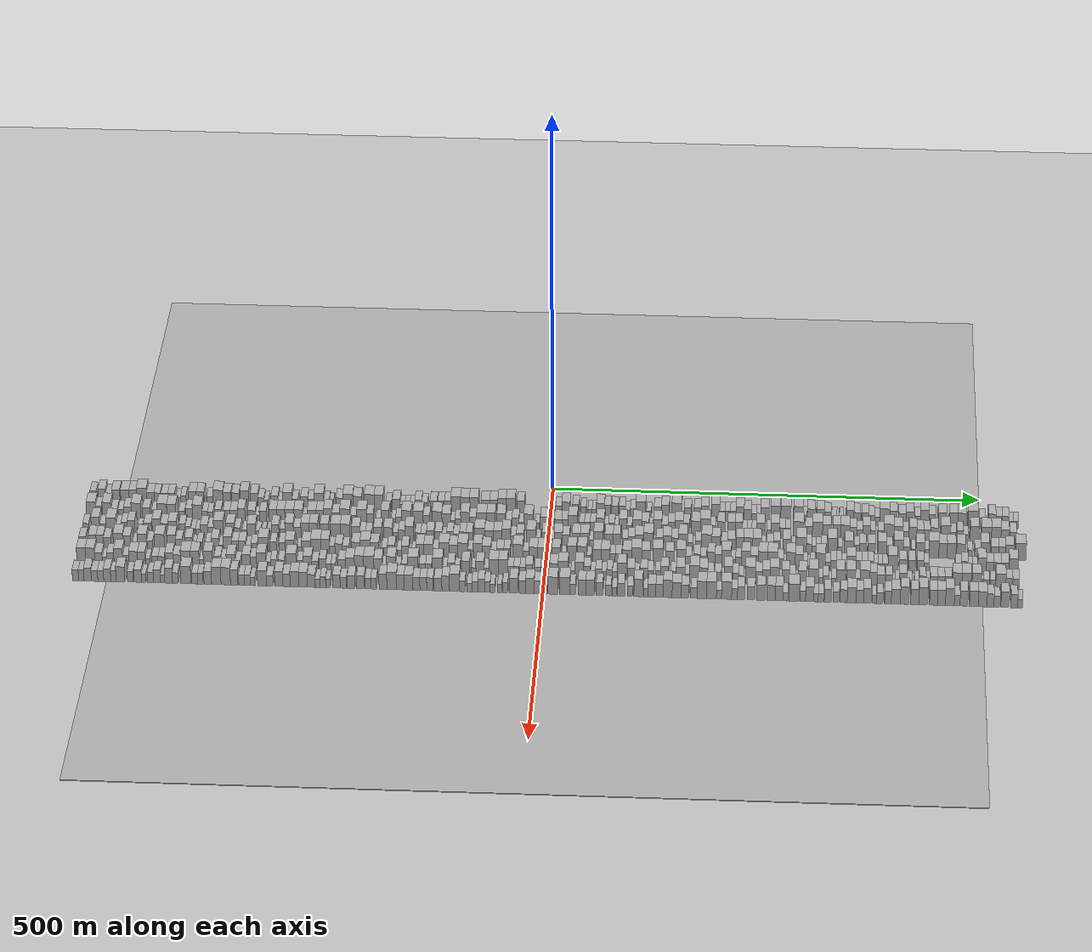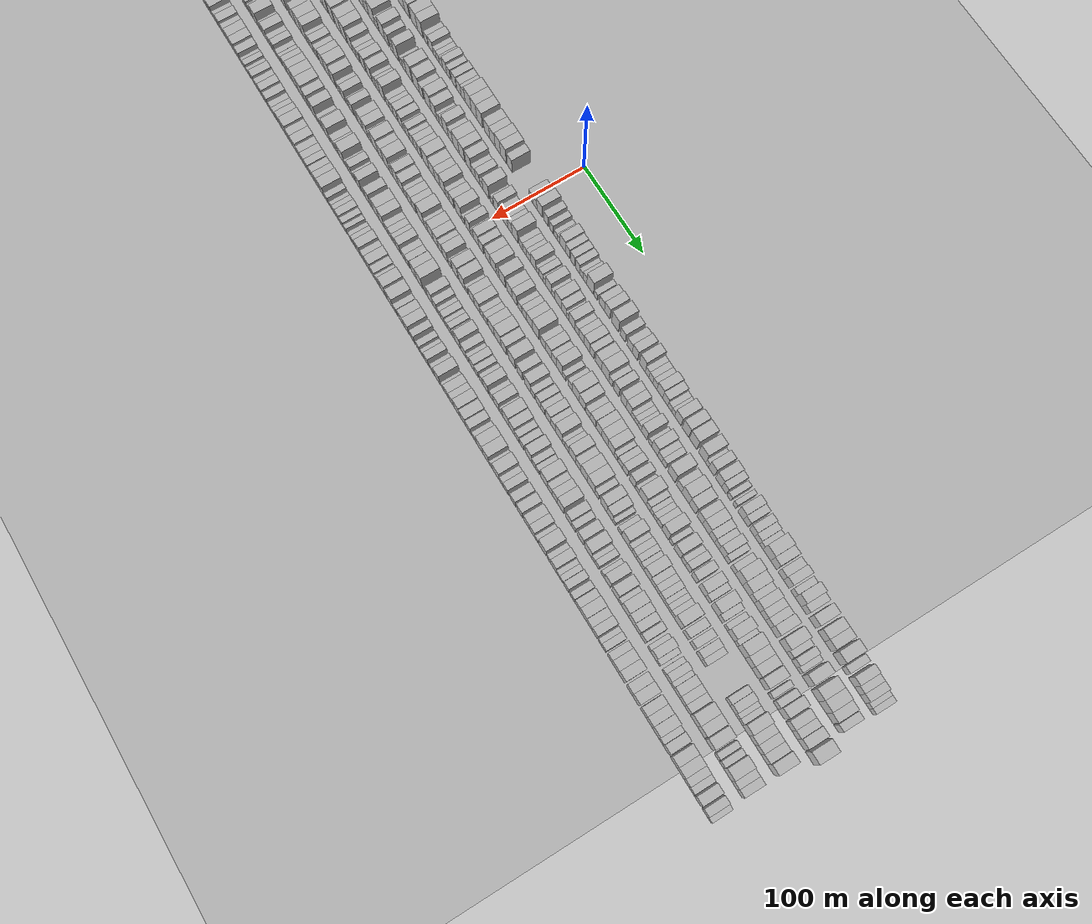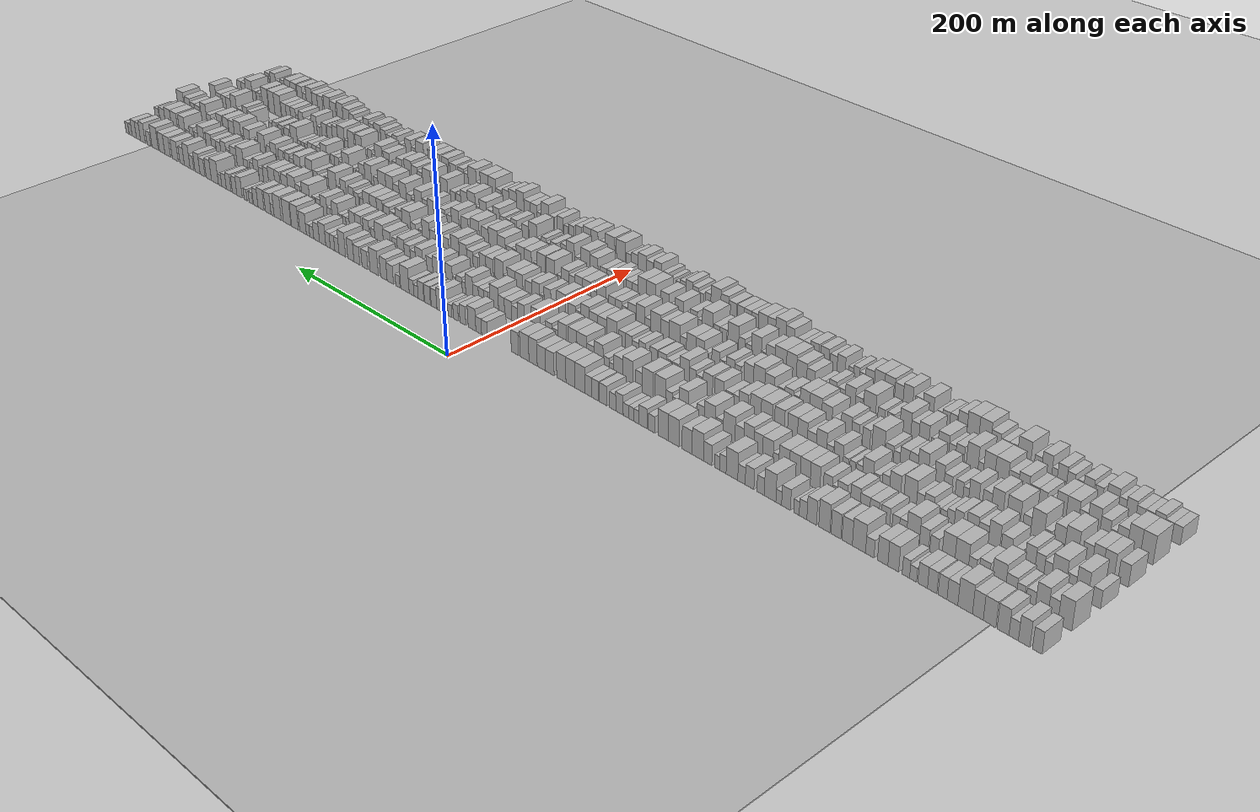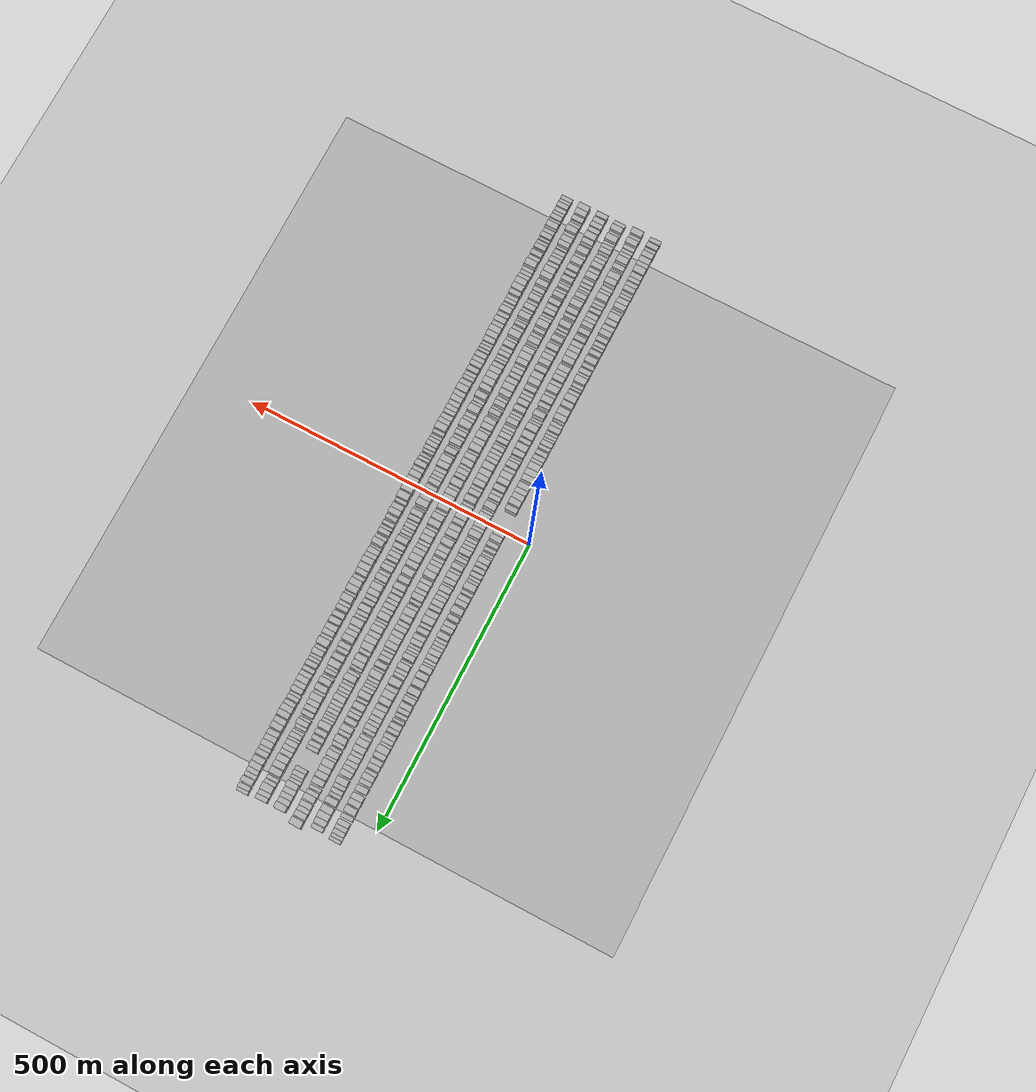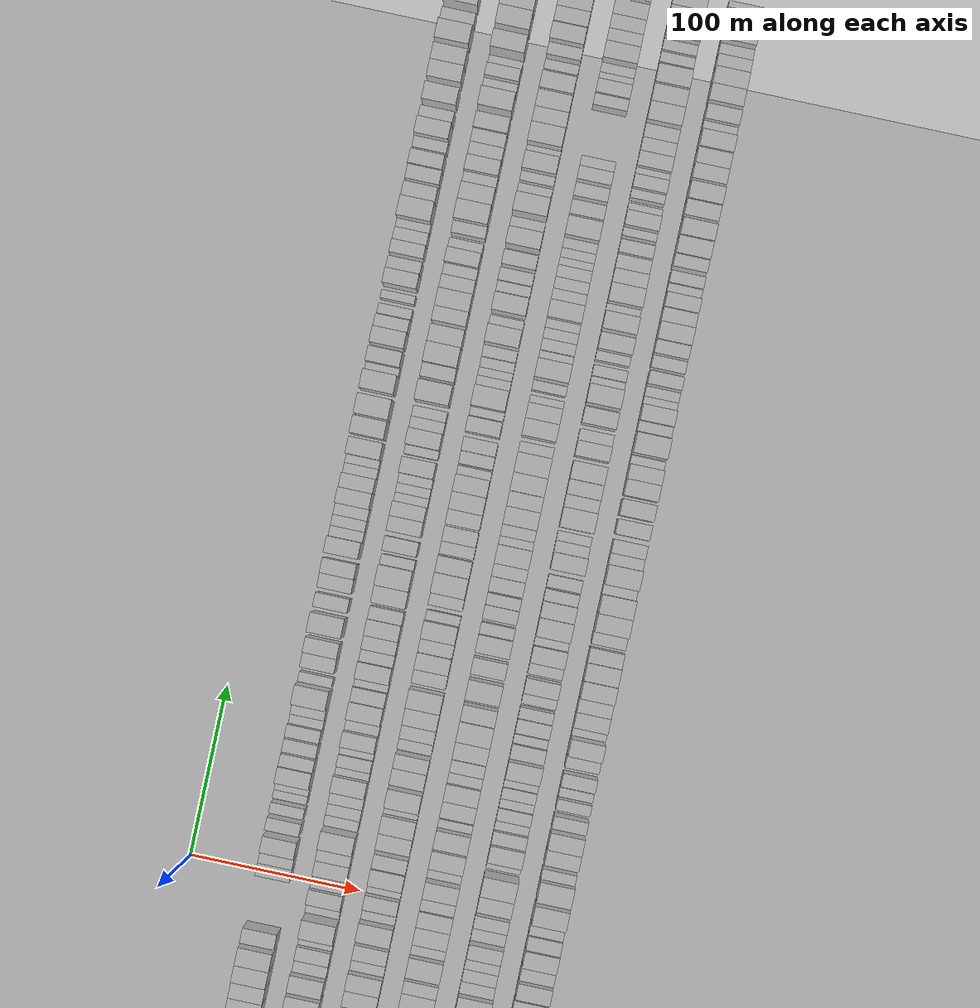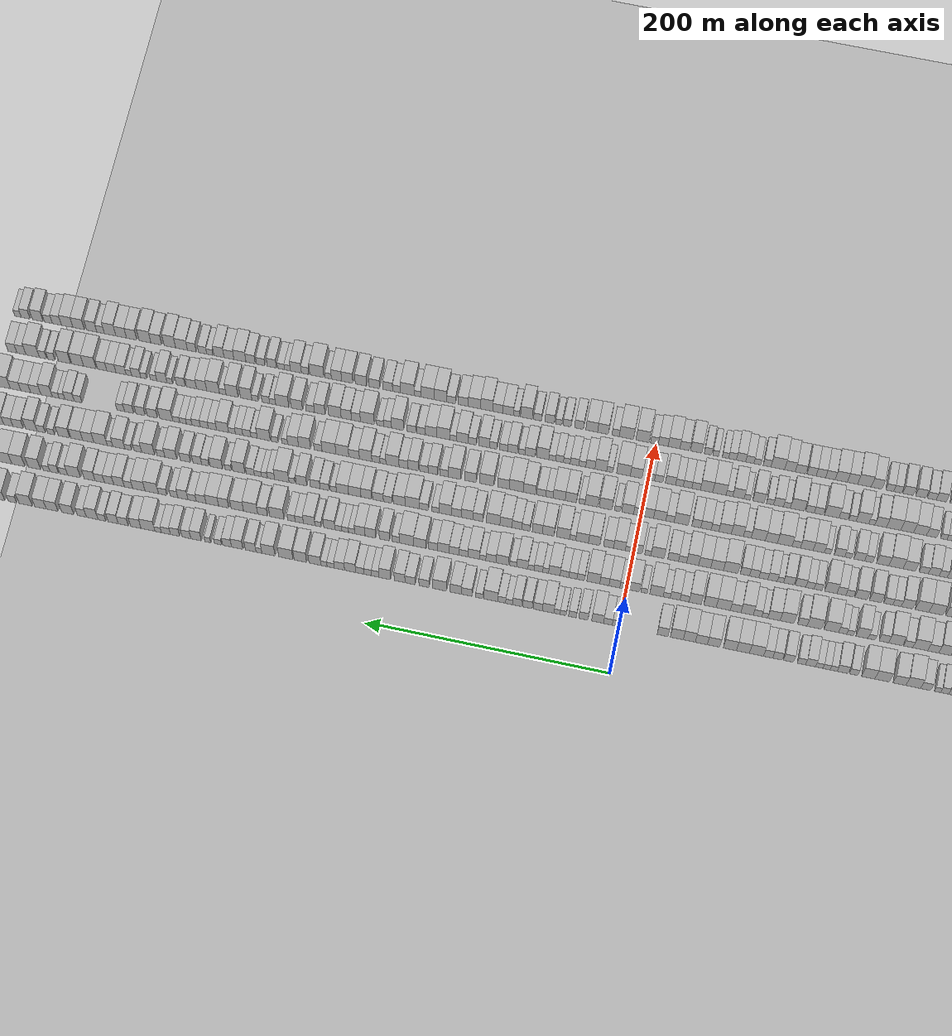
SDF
<?xml version="1.0" encoding="utf-8"?>

<sdf version="1.6">

   <world name="default">

      <gui fullscreen="0">

         <camera name="user_camera">

            <pose>-15 0 4.57585 0 0 0</pose>

            <view_controller>orbit</view_controller>

         </camera>

      </gui>

      <scene>

         <sky>

           <clouds>

             <speed>12</speed>

           </clouds>

         </sky>

         <ambient>0.4 0.4 0.4 1</ambient>

         <background>0.7 0.7 0.7 1</background>

         <shadows>1</shadows>

      </scene>

      <gravity>0 0 -9.8066</gravity>

      <magnetic_field>6e-06 2.3e-05 -4.2e-05</magnetic_field>

      <physics default="0" name="default_physics" type="ode">

         <ode>

            <solver>

               <type>quick</type>

               <iters>10</iters>

               <sor>1.0</sor>

               <use_dynamic_moi_rescaling>0</use_dynamic_moi_rescaling>

            </solver>

            <constraints>

               <cfm>0</cfm>

               <erp>0.2</erp>

               <contact_max_correcting_vel>100</contact_max_correcting_vel>

               <contact_surface_layer>0.001</contact_surface_layer>

            </constraints>

         </ode>

         <max_step_size>0.004</max_step_size>

         <real_time_factor>1</real_time_factor>

         <real_time_update_rate>250</real_time_update_rate>

      </physics>

      <light name="sun" type="directional">

         <cast_shadows>1</cast_shadows>

         <pose>0 0 10 0 0 0</pose>

         <diffuse>0.8 0.8 0.8 1</diffuse>

         <specular>0.2 0.2 0.2 1</specular>

         <attenuation>

            <range>1000</range>

            <constant>0.9</constant>

            <linear>0.01</linear>

            <quadratic>0.001</quadratic>

         </attenuation>

         <direction>-0.5 0.1 -0.9</direction>

      </light>

      <include>

         <name>ground_plane_1</name>

         <uri>model://HANNAS_ground_plane</uri>

         <pose>0 0 0  0 0 0</pose>

      </include>

      <include>

         <name>ground_plane_2</name>

         <uri>model://HANNAS_ground_plane</uri>

         <pose>100 0 0  0 0 0</pose>

      </include>

      <model name="building_1">

         <static>1</static>

         <pose frame="">50.0000 -536.3097 0 0.000000 0.000000 0.000000</pose>

         <link name="link">

            <pose frame="">0 0 9.00 0 0 0</pose>

            <collision name="collision">

               <geometry>

                  <box>

                     <size>20.0000 7.3805 18.0000</size>

                  </box>

               </geometry>

               <max_contacts>10</max_contacts>

               <surface>

                  <contact>

                     <ode/>

                  </contact>

                  <bounce/>

                  <friction>

                     <torsional>

                        <ode/>

                     </torsional>

                     <ode/>

                  </friction>

               </surface>

            </collision>

            <visual name="visual">

               <cast_shadows>0</cast_shadows>

               <geometry>

                  <box>

                     <size>20.0000 7.3805 18.0000</size>

                  </box>

               </geometry>

               <material>

                  <script>

                     <uri>model://HANNAS_wall/materials/scripts</uri>

                     <uri>model://HANNAS_wall/materials/textures</uri>

                     <name>vrc/HANNAS_wall</name>

                  </script>

               </material>

            </visual>

            <self_collide>0</self_collide>

            <enable_wind>0</enable_wind>

            <kinematic>0</kinematic>

         </link>

      </model>

      <model name="building_2">

         <static>1</static>

         <pose frame="">50.0000 -526.1825 0 0.000000 0.000000 0.000000</pose>

         <link name="link">

            <pose frame="">0 0 10.50 0 0 0</pose>

            <collision name="collision">

               <geometry>

                  <box>

                     <size>20.0000 8.8739 21.0000</size>

                  </box>

               </geometry>

               <max_contacts>10</max_contacts>

               <surface>

                  <contact>

                     <ode/>

                  </contact>

                  <bounce/>

                  <friction>

                     <torsional>

                        <ode/>

                     </torsional>

                     <ode/>

                  </friction>

               </surface>

            </collision>

            <visual name="visual">

               <cast_shadows>0</cast_shadows>

               <geometry>

                  <box>

                     <size>20.0000 8.8739 21.0000</size>

                  </box>

               </geometry>

               <material>

                  <script>

                     <uri>model://HANNAS_wall/materials/scripts</uri>

                     <uri>model://HANNAS_wall/materials/textures</uri>

                     <name>vrc/HANNAS_wall</name>

                  </script>

               </material>

            </visual>

            <self_collide>0</self_collide>

            <enable_wind>0</enable_wind>

            <kinematic>0</kinematic>

         </link>

      </model>

      <model name="building_3">

         <static>1</static>

         <pose frame="">50.0000 -518.0560 0 0.000000 0.000000 0.000000</pose>

         <link name="link">

            <pose frame="">0 0 7.50 0 0 0</pose>

            <collision name="collision">

               <geometry>

                  <box>

                     <size>20.0000 7.3791 15.0000</size>

                  </box>

               </geometry>

               <max_contacts>10</max_contacts>

               <surface>

                  <contact>

                     <ode/>

                  </contact>

                  <bounce/>

                  <friction>

                     <torsional>

                        <ode/>

                     </torsional>

                     <ode/>

                  </friction>

               </surface>

            </collision>

            <visual name="visual">

               <cast_shadows>0</cast_shadows>

               <geometry>

                  <box>

                     <size>20.0000 7.3791 15.0000</size>

                  </box>

               </geometry>

               <material>

                  <script>

                     <uri>model://HANNAS_wall/materials/scripts</uri>

                     <uri>model://HANNAS_wall/materials/textures</uri>

                     <name>vrc/HANNAS_wall</name>

                  </script>

               </material>

            </visual>

            <self_collide>0</self_collide>

            <enable_wind>0</enable_wind>

            <kinematic>0</kinematic>

         </link>

      </model>

      <model name="building_4">

         <static>1</static>

         <pose frame="">50.0000 -509.7047 0 0.000000 0.000000 0.000000</pose>

         <link name="link">

            <pose frame="">0 0 10.50 0 0 0</pose>

            <collision name="collision">

               <geometry>

                  <box>

                     <size>20.0000 9.3236 21.0000</size>

                  </box>

               </geometry>

               <max_contacts>10</max_contacts>

               <surface>

                  <contact>

                     <ode/>

                  </contact>

                  <bounce/>

                  <friction>

                     <torsional>

                        <ode/>

                     </torsional>

                     <ode/>

                  </friction>

               </surface>

            </collision>

            <visual name="visual">

               <cast_shadows>0</cast_shadows>

               <geometry>

                  <box>

                     <size>20.0000 9.3236 21.0000</size>

                  </box>

               </geometry>

               <material>

                  <script>

                     <uri>model://HANNAS_wall/materials/scripts</uri>

                     <uri>model://HANNAS_wall/materials/textures</uri>

                     <name>vrc/HANNAS_wall</name>

                  </script>

               </material>

            </visual>

            <self_collide>0</self_collide>

            <enable_wind>0</enable_wind>

            <kinematic>0</kinematic>

         </link>

      </model>

      <model name="building_5">

         <static>1</static>

         <pose frame="">50.0000 -499.0533 0 0.000000 0.000000 0.000000</pose>

         <link name="link">

            <pose frame="">0 0 10.50 0 0 0</pose>

            <collision name="collision">

               <geometry>

                  <box>

                     <size>20.0000 9.9792 21.0000</size>

                  </box>

               </geometry>

               <max_contacts>10</max_contacts>

               <surface>

                  <contact>

                     <ode/>

                  </contact>

                  <bounce/>

                  <friction>

                     <torsional>

                        <ode/>

                     </torsional>

                     <ode/>

                  </friction>

               </surface>

            </collision>

            <visual name="visual">

               <cast_shadows>0</cast_shadows>

               <geometry>

                  <box>

                     <size>20.0000 9.9792 21.0000</size>

                  </box>

               </geometry>

               <material>

                  <script>

                     <uri>model://HANNAS_wall/materials/scripts</uri>

                     <uri>model://HANNAS_wall/materials/textures</uri>

                     <name>vrc/HANNAS_wall</name>

                  </script>

               </material>

            </visual>

            <self_collide>0</self_collide>

            <enable_wind>0</enable_wind>

            <kinematic>0</kinematic>

         </link>

      </model>

      <model name="building_6">

         <static>1</static>

         <pose frame="">50.0000 -489.7183 0 0.000000 0.000000 0.000000</pose>

         <link name="link">

            <pose frame="">0 0 10.50 0 0 0</pose>

            <collision name="collision">

               <geometry>

                  <box>

                     <size>20.0000 8.6908 21.0000</size>

                  </box>

               </geometry>

               <max_contacts>10</max_contacts>

               <surface>

                  <contact>

                     <ode/>

                  </contact>

                  <bounce/>

                  <friction>

                     <torsional>

                        <ode/>

                     </torsional>

                     <ode/>

                  </friction>

               </surface>

            </collision>

            <visual name="visual">

               <cast_shadows>0</cast_shadows>

               <geometry>

                  <box>

                     <size>20.0000 8.6908 21.0000</size>

                  </box>

               </geometry>

               <material>

                  <script>

                     <uri>model://HANNAS_wall/materials/scripts</uri>

                     <uri>model://HANNAS_wall/materials/textures</uri>

                     <name>vrc/HANNAS_wall</name>

                  </script>

               </material>

            </visual>

            <self_collide>0</self_collide>

            <enable_wind>0</enable_wind>

            <kinematic>0</kinematic>

         </link>

      </model>

      <model name="building_7">

         <static>1</static>

         <pose frame="">50.0000 -479.4428 0 0.000000 0.000000 0.000000</pose>

         <link name="link">

            <pose frame="">0 0 12.00 0 0 0</pose>

            <collision name="collision">

               <geometry>

                  <box>

                     <size>20.0000 11.8601 24.0000</size>

                  </box>

               </geometry>

               <max_contacts>10</max_contacts>

               <surface>

                  <contact>

                     <ode/>

                  </contact>

                  <bounce/>

                  <friction>

                     <torsional>

                        <ode/>

                     </torsional>

                     <ode/>

                  </friction>

               </surface>

            </collision>

            <visual name="visual">

               <cast_shadows>0</cast_shadows>

               <geometry>

                  <box>

                     <size>20.0000 11.8601 24.0000</size>

                  </box>

               </geometry>

               <material>

                  <script>

                     <uri>model://HANNAS_wall/materials/scripts</uri>

                     <uri>model://HANNAS_wall/materials/textures</uri>

                     <name>vrc/HANNAS_wall</name>

                  </script>

               </material>

            </visual>

            <self_collide>0</self_collide>

            <enable_wind>0</enable_wind>

            <kinematic>0</kinematic>

         </link>

      </model>

      <model name="building_8">

         <static>1</static>

         <pose frame="">50.0000 -469.0990 0 0.000000 0.000000 0.000000</pose>

         <link name="link">

            <pose frame="">0 0 9.00 0 0 0</pose>

            <collision name="collision">

               <geometry>

                  <box>

                     <size>20.0000 8.8274 18.0000</size>

                  </box>

               </geometry>

               <max_contacts>10</max_contacts>

               <surface>

                  <contact>

                     <ode/>

                  </contact>

                  <bounce/>

                  <friction>

                     <torsional>

                        <ode/>

                     </torsional>

                     <ode/>

                  </friction>

               </surface>

            </collision>

            <visual name="visual">

               <cast_shadows>0</cast_shadows>

               <geometry>

                  <box>

                     <size>20.0000 8.8274 18.0000</size>

                  </box>

               </geometry>

               <material>

                  <script>

                     <uri>model://HANNAS_wall/materials/scripts</uri>

                     <uri>model://HANNAS_wall/materials/textures</uri>

                     <name>vrc/HANNAS_wall</name>

                  </script>

               </material>

            </visual>

            <self_collide>0</self_collide>

            <enable_wind>0</enable_wind>

            <kinematic>0</kinematic>

         </link>

      </model>

      <model name="building_9">

         <static>1</static>

         <pose frame="">50.0000 -460.9880 0 0.000000 0.000000 0.000000</pose>

         <link name="link">

            <pose frame="">0 0 9.00 0 0 0</pose>

            <collision name="collision">

               <geometry>

                  <box>

                     <size>20.0000 7.3945 18.0000</size>

                  </box>

               </geometry>

               <max_contacts>10</max_contacts>

               <surface>

                  <contact>

                     <ode/>

                  </contact>

                  <bounce/>

                  <friction>

                     <torsional>

                        <ode/>

                     </torsional>

                     <ode/>

                  </friction>

               </surface>

            </collision>

            <visual name="visual">

               <cast_shadows>0</cast_shadows>

               <geometry>

                  <box>

                     <size>20.0000 7.3945 18.0000</size>

                  </box>

               </geometry>

               <material>

                  <script>

                     <uri>model://HANNAS_wall/materials/scripts</uri>

                     <uri>model://HANNAS_wall/materials/textures</uri>

                     <name>vrc/HANNAS_wall</name>

                  </script>

               </material>

            </visual>

            <self_collide>0</self_collide>

            <enable_wind>0</enable_wind>

            <kinematic>0</kinematic>

         </link>

      </model>

      <model name="building_10">

         <static>1</static>

         <pose frame="">50.0000 -452.3963 0 0.000000 0.000000 0.000000</pose>

         <link name="link">

            <pose frame="">0 0 9.00 0 0 0</pose>

            <collision name="collision">

               <geometry>

                  <box>

                     <size>20.0000 7.7890 18.0000</size>

                  </box>

               </geometry>

               <max_contacts>10</max_contacts>

               <surface>

                  <contact>

                     <ode/>

                  </contact>

                  <bounce/>

                  <friction>

                     <torsional>

                        <ode/>

                     </torsional>

                     <ode/>

                  </friction>

               </surface>

            </collision>

            <visual name="visual">

               <cast_shadows>0</cast_shadows>

               <geometry>

                  <box>

                     <size>20.0000 7.7890 18.0000</size>

                  </box>

               </geometry>

               <material>

                  <script>

                     <uri>model://HANNAS_wall/materials/scripts</uri>

                     <uri>model://HANNAS_wall/materials/textures</uri>

                     <name>vrc/HANNAS_wall</name>

                  </script>

               </material>

            </visual>

            <self_collide>0</self_collide>

            <enable_wind>0</enable_wind>

            <kinematic>0</kinematic>

         </link>

      </model>

      <model name="building_11">

         <static>1</static>

         <pose frame="">50.0000 -444.4379 0 0.000000 0.000000 0.000000</pose>

         <link name="link">

            <pose frame="">0 0 9.00 0 0 0</pose>

            <collision name="collision">

               <geometry>

                  <box>

                     <size>20.0000 8.1278 18.0000</size>

                  </box>

               </geometry>

               <max_contacts>10</max_contacts>

               <surface>

                  <contact>

                     <ode/>

                  </contact>

                  <bounce/>

                  <friction>

                     <torsional>

                        <ode/>

                     </torsional>

                     <ode/>

                  </friction>

               </surface>

            </collision>

            <visual name="visual">

               <cast_shadows>0</cast_shadows>

               <geometry>

                  <box>

                     <size>20.0000 8.1278 18.0000</size>

                  </box>

               </geometry>

               <material>

                  <script>

                     <uri>model://HANNAS_wall/materials/scripts</uri>

                     <uri>model://HANNAS_wall/materials/textures</uri>

                     <name>vrc/HANNAS_wall</name>

                  </script>

               </material>

            </visual>

            <self_collide>0</self_collide>

            <enable_wind>0</enable_wind>

            <kinematic>0</kinematic>

         </link>

      </model>

      <model name="building_12">

         <static>1</static>

         <pose frame="">50.0000 -436.4097 0 0.000000 0.000000 0.000000</pose>

         <link name="link">

            <pose frame="">0 0 6.00 0 0 0</pose>

            <collision name="collision">

               <geometry>

                  <box>

                     <size>20.0000 5.9287 12.0000</size>

                  </box>

               </geometry>

               <max_contacts>10</max_contacts>

               <surface>

                  <contact>

                     <ode/>

                  </contact>

                  <bounce/>

                  <friction>

                     <torsional>

                        <ode/>

                     </torsional>

                     <ode/>

                  </friction>

               </surface>

            </collision>

            <visual name="visual">

               <cast_shadows>0</cast_shadows>

               <geometry>

                  <box>

                     <size>20.0000 5.9287 12.0000</size>

                  </box>

               </geometry>

               <material>

                  <script>

                     <uri>model://HANNAS_wall/materials/scripts</uri>

                     <uri>model://HANNAS_wall/materials/textures</uri>

                     <name>vrc/HANNAS_wall</name>

                  </script>

               </material>

            </visual>

            <self_collide>0</self_collide>

            <enable_wind>0</enable_wind>

            <kinematic>0</kinematic>

         </link>

      </model>

      <model name="building_13">

         <static>1</static>

         <pose frame="">50.0000 -430.3010 0 0.000000 0.000000 0.000000</pose>

         <link name="link">

            <pose frame="">0 0 7.50 0 0 0</pose>

            <collision name="collision">

               <geometry>

                  <box>

                     <size>20.0000 6.2887 15.0000</size>

                  </box>

               </geometry>

               <max_contacts>10</max_contacts>

               <surface>

                  <contact>

                     <ode/>

                  </contact>

                  <bounce/>

                  <friction>

                     <torsional>

                        <ode/>

                     </torsional>

                     <ode/>

                  </friction>

               </surface>

            </collision>

            <visual name="visual">

               <cast_shadows>0</cast_shadows>

               <geometry>

                  <box>

                     <size>20.0000 6.2887 15.0000</size>

                  </box>

               </geometry>

               <material>

                  <script>

                     <uri>model://HANNAS_wall/materials/scripts</uri>

                     <uri>model://HANNAS_wall/materials/textures</uri>

                     <name>vrc/HANNAS_wall</name>

                  </script>

               </material>

            </visual>

            <self_collide>0</self_collide>

            <enable_wind>0</enable_wind>

            <kinematic>0</kinematic>

         </link>

      </model>

      <model name="building_14">

         <static>1</static>

         <pose frame="">50.0000 -419.5498 0 0.000000 0.000000 0.000000</pose>

         <link name="link">

            <pose frame="">0 0 10.50 0 0 0</pose>

            <collision name="collision">

               <geometry>

                  <box>

                     <size>20.0000 9.2139 21.0000</size>

                  </box>

               </geometry>

               <max_contacts>10</max_contacts>

               <surface>

                  <contact>

                     <ode/>

                  </contact>

                  <bounce/>

                  <friction>

                     <torsional>

                        <ode/>

                     </torsional>

                     <ode/>

                  </friction>

               </surface>

            </collision>

            <visual name="visual">

               <cast_shadows>0</cast_shadows>

               <geometry>

                  <box>

                     <size>20.0000 9.2139 21.0000</size>

                  </box>

               </geometry>

               <material>

                  <script>

                     <uri>model://HANNAS_wall/materials/scripts</uri>

                     <uri>model://HANNAS_wall/materials/textures</uri>

                     <name>vrc/HANNAS_wall</name>

                  </script>

               </material>

            </visual>

            <self_collide>0</self_collide>

            <enable_wind>0</enable_wind>

            <kinematic>0</kinematic>

         </link>

      </model>

      <model name="building_15">

         <static>1</static>

         <pose frame="">50.0000 -410.4374 0 0.000000 0.000000 0.000000</pose>

         <link name="link">

            <pose frame="">0 0 10.50 0 0 0</pose>

            <collision name="collision">

               <geometry>

                  <box>

                     <size>20.0000 9.0108 21.0000</size>

                  </box>

               </geometry>

               <max_contacts>10</max_contacts>

               <surface>

                  <contact>

                     <ode/>

                  </contact>

                  <bounce/>

                  <friction>

                     <torsional>

                        <ode/>

                     </torsional>

                     <ode/>

                  </friction>

               </surface>

            </collision>

            <visual name="visual">

               <cast_shadows>0</cast_shadows>

               <geometry>

                  <box>

                     <size>20.0000 9.0108 21.0000</size>

                  </box>

               </geometry>

               <material>

                  <script>

                     <uri>model://HANNAS_wall/materials/scripts</uri>

                     <uri>model://HANNAS_wall/materials/textures</uri>

                     <name>vrc/HANNAS_wall</name>

                  </script>

               </material>

            </visual>

            <self_collide>0</self_collide>

            <enable_wind>0</enable_wind>

            <kinematic>0</kinematic>

         </link>

      </model>

      <model name="building_16">

         <static>1</static>

         <pose frame="">50.0000 -399.1959 0 0.000000 0.000000 0.000000</pose>

         <link name="link">

            <pose frame="">0 0 7.50 0 0 0</pose>

            <collision name="collision">

               <geometry>

                  <box>

                     <size>20.0000 7.4723 15.0000</size>

                  </box>

               </geometry>

               <max_contacts>10</max_contacts>

               <surface>

                  <contact>

                     <ode/>

                  </contact>

                  <bounce/>

                  <friction>

                     <torsional>

                        <ode/>

                     </torsional>

                     <ode/>

                  </friction>

               </surface>

            </collision>

            <visual name="visual">

               <cast_shadows>0</cast_shadows>

               <geometry>

                  <box>

                     <size>20.0000 7.4723 15.0000</size>

                  </box>

               </geometry>

               <material>

                  <script>

                     <uri>model://HANNAS_wall/materials/scripts</uri>

                     <uri>model://HANNAS_wall/materials/textures</uri>

                     <name>vrc/HANNAS_wall</name>

                  </script>

               </material>

            </visual>

            <self_collide>0</self_collide>

            <enable_wind>0</enable_wind>

            <kinematic>0</kinematic>

         </link>

      </model>

      <model name="building_17">

         <static>1</static>

         <pose frame="">50.0000 -389.6461 0 0.000000 0.000000 0.000000</pose>

         <link name="link">

            <pose frame="">0 0 12.00 0 0 0</pose>

            <collision name="collision">

               <geometry>

                  <box>

                     <size>20.0000 11.6273 24.0000</size>

                  </box>

               </geometry>

               <max_contacts>10</max_contacts>

               <surface>

                  <contact>

                     <ode/>

                  </contact>

                  <bounce/>

                  <friction>

                     <torsional>

                        <ode/>

                     </torsional>

                     <ode/>

                  </friction>

               </surface>

            </collision>

            <visual name="visual">

               <cast_shadows>0</cast_shadows>

               <geometry>

                  <box>

                     <size>20.0000 11.6273 24.0000</size>

                  </box>

               </geometry>

               <material>

                  <script>

                     <uri>model://HANNAS_wall/materials/scripts</uri>

                     <uri>model://HANNAS_wall/materials/textures</uri>

                     <name>vrc/HANNAS_wall</name>

                  </script>

               </material>

            </visual>

            <self_collide>0</self_collide>

            <enable_wind>0</enable_wind>

            <kinematic>0</kinematic>

         </link>

      </model>

      <model name="building_18">

         <static>1</static>

         <pose frame="">50.0000 -379.2000 0 0.000000 0.000000 0.000000</pose>

         <link name="link">

            <pose frame="">0 0 10.50 0 0 0</pose>

            <collision name="collision">

               <geometry>

                  <box>

                     <size>20.0000 9.2649 21.0000</size>

                  </box>

               </geometry>

               <max_contacts>10</max_contacts>

               <surface>

                  <contact>

                     <ode/>

                  </contact>

                  <bounce/>

                  <friction>

                     <torsional>

                        <ode/>

                     </torsional>

                     <ode/>

                  </friction>

               </surface>

            </collision>

            <visual name="visual">

               <cast_shadows>0</cast_shadows>

               <geometry>

                  <box>

                     <size>20.0000 9.2649 21.0000</size>

                  </box>

               </geometry>

               <material>

                  <script>

                     <uri>model://HANNAS_wall/materials/scripts</uri>

                     <uri>model://HANNAS_wall/materials/textures</uri>

                     <name>vrc/HANNAS_wall</name>

                  </script>

               </material>

            </visual>

            <self_collide>0</self_collide>

            <enable_wind>0</enable_wind>

            <kinematic>0</kinematic>

         </link>

      </model>

      <model name="building_19">

         <static>1</static>

         <pose frame="">50.0000 -369.1609 0 0.000000 0.000000 0.000000</pose>

         <link name="link">

            <pose frame="">0 0 10.50 0 0 0</pose>

            <collision name="collision">

               <geometry>

                  <box>

                     <size>20.0000 8.8132 21.0000</size>

                  </box>

               </geometry>

               <max_contacts>10</max_contacts>

               <surface>

                  <contact>

                     <ode/>

                  </contact>

                  <bounce/>

                  <friction>

                     <torsional>

                        <ode/>

                     </torsional>

                     <ode/>

                  </friction>

               </surface>

            </collision>

            <visual name="visual">

               <cast_shadows>0</cast_shadows>

               <geometry>

                  <box>

                     <size>20.0000 8.8132 21.0000</size>

                  </box>

               </geometry>

               <material>

                  <script>

                     <uri>model://HANNAS_wall/materials/scripts</uri>

                     <uri>model://HANNAS_wall/materials/textures</uri>

                     <name>vrc/HANNAS_wall</name>

                  </script>

               </material>

            </visual>

            <self_collide>0</self_collide>

            <enable_wind>0</enable_wind>

            <kinematic>0</kinematic>

         </link>

      </model>

      <model name="building_20">

         <static>1</static>

         <pose frame="">50.0000 -358.6458 0 0.000000 0.000000 0.000000</pose>

         <link name="link">

            <pose frame="">0 0 12.00 0 0 0</pose>

            <collision name="collision">

               <geometry>

                  <box>

                     <size>20.0000 10.2170 24.0000</size>

                  </box>

               </geometry>

               <max_contacts>10</max_contacts>

               <surface>

                  <contact>

                     <ode/>

                  </contact>

                  <bounce/>

                  <friction>

                     <torsional>

                        <ode/>

                     </torsional>

                     <ode/>

                  </friction>

               </surface>

            </collision>

            <visual name="visual">

               <cast_shadows>0</cast_shadows>

               <geometry>

                  <box>

                     <size>20.0000 10.2170 24.0000</size>

                  </box>

               </geometry>

               <material>

                  <script>

                     <uri>model://HANNAS_wall/materials/scripts</uri>

                     <uri>model://HANNAS_wall/materials/textures</uri>

                     <name>vrc/HANNAS_wall</name>

                  </script>

               </material>

            </visual>

            <self_collide>0</self_collide>

            <enable_wind>0</enable_wind>

            <kinematic>0</kinematic>

         </link>

      </model>

      <model name="building_21">

         <static>1</static>

         <pose frame="">50.0000 -347.1044 0 0.000000 0.000000 0.000000</pose>

         <link name="link">

            <pose frame="">0 0 10.50 0 0 0</pose>

            <collision name="collision">

               <geometry>

                  <box>

                     <size>20.0000 8.8658 21.0000</size>

                  </box>

               </geometry>

               <max_contacts>10</max_contacts>

               <surface>

                  <contact>

                     <ode/>

                  </contact>

                  <bounce/>

                  <friction>

                     <torsional>

                        <ode/>

                     </torsional>

                     <ode/>

                  </friction>

               </surface>

            </collision>

            <visual name="visual">

               <cast_shadows>0</cast_shadows>

               <geometry>

                  <box>

                     <size>20.0000 8.8658 21.0000</size>

                  </box>

               </geometry>

               <material>

                  <script>

                     <uri>model://HANNAS_wall/materials/scripts</uri>

                     <uri>model://HANNAS_wall/materials/textures</uri>

                     <name>vrc/HANNAS_wall</name>

                  </script>

               </material>

            </visual>

            <self_collide>0</self_collide>

            <enable_wind>0</enable_wind>

            <kinematic>0</kinematic>

         </link>

      </model>

      <model name="building_22">

         <static>1</static>

         <pose frame="">50.0000 -339.1000 0 0.000000 0.000000 0.000000</pose>

         <link name="link">

            <pose frame="">0 0 7.50 0 0 0</pose>

            <collision name="collision">

               <geometry>

                  <box>

                     <size>20.0000 7.1430 15.0000</size>

                  </box>

               </geometry>

               <max_contacts>10</max_contacts>

               <surface>

                  <contact>

                     <ode/>

                  </contact>

                  <bounce/>

                  <friction>

                     <torsional>

                        <ode/>

                     </torsional>

                     <ode/>

                  </friction>

               </surface>

            </collision>

            <visual name="visual">

               <cast_shadows>0</cast_shadows>

               <geometry>

                  <box>

                     <size>20.0000 7.1430 15.0000</size>

                  </box>

               </geometry>

               <material>

                  <script>

                     <uri>model://HANNAS_wall/materials/scripts</uri>

                     <uri>model://HANNAS_wall/materials/textures</uri>

                     <name>vrc/HANNAS_wall</name>

                  </script>

               </material>

            </visual>

            <self_collide>0</self_collide>

            <enable_wind>0</enable_wind>

            <kinematic>0</kinematic>

         </link>

      </model>

      <model name="building_23">

         <static>1</static>

         <pose frame="">50.0000 -332.9727 0 0.000000 0.000000 0.000000</pose>

         <link name="link">

            <pose frame="">0 0 6.00 0 0 0</pose>

            <collision name="collision">

               <geometry>

                  <box>

                     <size>20.0000 5.1115 12.0000</size>

                  </box>

               </geometry>

               <max_contacts>10</max_contacts>

               <surface>

                  <contact>

                     <ode/>

                  </contact>

                  <bounce/>

                  <friction>

                     <torsional>

                        <ode/>

                     </torsional>

                     <ode/>

                  </friction>

               </surface>

            </collision>

            <visual name="visual">

               <cast_shadows>0</cast_shadows>

               <geometry>

                  <box>

                     <size>20.0000 5.1115 12.0000</size>

                  </box>

               </geometry>

               <material>

                  <script>

                     <uri>model://HANNAS_wall/materials/scripts</uri>

                     <uri>model://HANNAS_wall/materials/textures</uri>

                     <name>vrc/HANNAS_wall</name>

                  </script>

               </material>

            </visual>

            <self_collide>0</self_collide>

            <enable_wind>0</enable_wind>

            <kinematic>0</kinematic>

         </link>

      </model>

      <model name="building_24">

         <static>1</static>

         <pose frame="">50.0000 -323.2628 0 0.000000 0.000000 0.000000</pose>

         <link name="link">

            <pose frame="">0 0 9.00 0 0 0</pose>

            <collision name="collision">

               <geometry>

                  <box>

                     <size>20.0000 8.3082 18.0000</size>

                  </box>

               </geometry>

               <max_contacts>10</max_contacts>

               <surface>

                  <contact>

                     <ode/>

                  </contact>

                  <bounce/>

                  <friction>

                     <torsional>

                        <ode/>

                     </torsional>

                     <ode/>

                  </friction>

               </surface>

            </collision>

            <visual name="visual">

               <cast_shadows>0</cast_shadows>

               <geometry>

                  <box>

                     <size>20.0000 8.3082 18.0000</size>

                  </box>

               </geometry>

               <material>

                  <script>

                     <uri>model://HANNAS_wall/materials/scripts</uri>

                     <uri>model://HANNAS_wall/materials/textures</uri>

                     <name>vrc/HANNAS_wall</name>

                  </script>

               </material>

            </visual>

            <self_collide>0</self_collide>

            <enable_wind>0</enable_wind>

            <kinematic>0</kinematic>

         </link>

      </model>

      <model name="building_25">

         <static>1</static>

         <pose frame="">50.0000 -316.3917 0 0.000000 0.000000 0.000000</pose>

         <link name="link">

            <pose frame="">0 0 6.00 0 0 0</pose>

            <collision name="collision">

               <geometry>

                  <box>

                     <size>20.0000 5.4340 12.0000</size>

                  </box>

               </geometry>

               <max_contacts>10</max_contacts>

               <surface>

                  <contact>

                     <ode/>

                  </contact>

                  <bounce/>

                  <friction>

                     <torsional>

                        <ode/>

                     </torsional>

                     <ode/>

                  </friction>

               </surface>

            </collision>

            <visual name="visual">

               <cast_shadows>0</cast_shadows>

               <geometry>

                  <box>

                     <size>20.0000 5.4340 12.0000</size>

                  </box>

               </geometry>

               <material>

                  <script>

                     <uri>model://HANNAS_wall/materials/scripts</uri>

                     <uri>model://HANNAS_wall/materials/textures</uri>

                     <name>vrc/HANNAS_wall</name>

                  </script>

               </material>

            </visual>

            <self_collide>0</self_collide>

            <enable_wind>0</enable_wind>

            <kinematic>0</kinematic>

         </link>

      </model>

      <model name="building_26">

         <static>1</static>

         <pose frame="">50.0000 -308.1510 0 0.000000 0.000000 0.000000</pose>

         <link name="link">

            <pose frame="">0 0 12.00 0 0 0</pose>

            <collision name="collision">

               <geometry>

                  <box>

                     <size>20.0000 11.0475 24.0000</size>

                  </box>

               </geometry>

               <max_contacts>10</max_contacts>

               <surface>

                  <contact>

                     <ode/>

                  </contact>

                  <bounce/>

                  <friction>

                     <torsional>

                        <ode/>

                     </torsional>

                     <ode/>

                  </friction>

               </surface>

            </collision>

            <visual name="visual">

               <cast_shadows>0</cast_shadows>

               <geometry>

                  <box>

                     <size>20.0000 11.0475 24.0000</size>

                  </box>

               </geometry>

               <material>

                  <script>

                     <uri>model://HANNAS_wall/materials/scripts</uri>

                     <uri>model://HANNAS_wall/materials/textures</uri>

                     <name>vrc/HANNAS_wall</name>

                  </script>

               </material>

            </visual>

            <self_collide>0</self_collide>

            <enable_wind>0</enable_wind>

            <kinematic>0</kinematic>

         </link>

      </model>

      <model name="building_27">

         <static>1</static>

         <pose frame="">50.0000 -299.1299 0 0.000000 0.000000 0.000000</pose>

         <link name="link">

            <pose frame="">0 0 7.50 0 0 0</pose>

            <collision name="collision">

               <geometry>

                  <box>

                     <size>20.0000 6.9947 15.0000</size>

                  </box>

               </geometry>

               <max_contacts>10</max_contacts>

               <surface>

                  <contact>

                     <ode/>

                  </contact>

                  <bounce/>

                  <friction>

                     <torsional>

                        <ode/>

                     </torsional>

                     <ode/>

                  </friction>

               </surface>

            </collision>

            <visual name="visual">

               <cast_shadows>0</cast_shadows>

               <geometry>

                  <box>

                     <size>20.0000 6.9947 15.0000</size>

                  </box>

               </geometry>

               <material>

                  <script>

                     <uri>model://HANNAS_wall/materials/scripts</uri>

                     <uri>model://HANNAS_wall/materials/textures</uri>

                     <name>vrc/HANNAS_wall</name>

                  </script>

               </material>

            </visual>

            <self_collide>0</self_collide>

            <enable_wind>0</enable_wind>

            <kinematic>0</kinematic>

         </link>

      </model>

      <model name="building_28">

         <static>1</static>

         <pose frame="">50.0000 -288.4322 0 0.000000 0.000000 0.000000</pose>

         <link name="link">

            <pose frame="">0 0 9.00 0 0 0</pose>

            <collision name="collision">

               <geometry>

                  <box>

                     <size>20.0000 8.4007 18.0000</size>

                  </box>

               </geometry>

               <max_contacts>10</max_contacts>

               <surface>

                  <contact>

                     <ode/>

                  </contact>

                  <bounce/>

                  <friction>

                     <torsional>

                        <ode/>

                     </torsional>

                     <ode/>

                  </friction>

               </surface>

            </collision>

            <visual name="visual">

               <cast_shadows>0</cast_shadows>

               <geometry>

                  <box>

                     <size>20.0000 8.4007 18.0000</size>

                  </box>

               </geometry>

               <material>

                  <script>

                     <uri>model://HANNAS_wall/materials/scripts</uri>

                     <uri>model://HANNAS_wall/materials/textures</uri>

                     <name>vrc/HANNAS_wall</name>

                  </script>

               </material>

            </visual>

            <self_collide>0</self_collide>

            <enable_wind>0</enable_wind>

            <kinematic>0</kinematic>

         </link>

      </model>

      <model name="building_29">

         <static>1</static>

         <pose frame="">50.0000 -280.5858 0 0.000000 0.000000 0.000000</pose>

         <link name="link">

            <pose frame="">0 0 7.50 0 0 0</pose>

            <collision name="collision">

               <geometry>

                  <box>

                     <size>20.0000 7.2921 15.0000</size>

                  </box>

               </geometry>

               <max_contacts>10</max_contacts>

               <surface>

                  <contact>

                     <ode/>

                  </contact>

                  <bounce/>

                  <friction>

                     <torsional>

                        <ode/>

                     </torsional>

                     <ode/>

                  </friction>

               </surface>

            </collision>

            <visual name="visual">

               <cast_shadows>0</cast_shadows>

               <geometry>

                  <box>

                     <size>20.0000 7.2921 15.0000</size>

                  </box>

               </geometry>

               <material>

                  <script>

                     <uri>model://HANNAS_wall/materials/scripts</uri>

                     <uri>model://HANNAS_wall/materials/textures</uri>

                     <name>vrc/HANNAS_wall</name>

                  </script>

               </material>

            </visual>

            <self_collide>0</self_collide>

            <enable_wind>0</enable_wind>

            <kinematic>0</kinematic>

         </link>

      </model>

      <model name="building_30">

         <static>1</static>

         <pose frame="">50.0000 -271.1964 0 0.000000 0.000000 0.000000</pose>

         <link name="link">

            <pose frame="">0 0 12.00 0 0 0</pose>

            <collision name="collision">

               <geometry>

                  <box>

                     <size>20.0000 11.4867 24.0000</size>

                  </box>

               </geometry>

               <max_contacts>10</max_contacts>

               <surface>

                  <contact>

                     <ode/>

                  </contact>

                  <bounce/>

                  <friction>

                     <torsional>

                        <ode/>

                     </torsional>

                     <ode/>

                  </friction>

               </surface>

            </collision>

            <visual name="visual">

               <cast_shadows>0</cast_shadows>

               <geometry>

                  <box>

                     <size>20.0000 11.4867 24.0000</size>

                  </box>

               </geometry>

               <material>

                  <script>

                     <uri>model://HANNAS_wall/materials/scripts</uri>

                     <uri>model://HANNAS_wall/materials/textures</uri>

                     <name>vrc/HANNAS_wall</name>

                  </script>

               </material>

            </visual>

            <self_collide>0</self_collide>

            <enable_wind>0</enable_wind>

            <kinematic>0</kinematic>

         </link>

      </model>

      <model name="building_31">

         <static>1</static>

         <pose frame="">50.0000 -262.2498 0 0.000000 0.000000 0.000000</pose>

         <link name="link">

            <pose frame="">0 0 7.50 0 0 0</pose>

            <collision name="collision">

               <geometry>

                  <box>

                     <size>20.0000 6.4064 15.0000</size>

                  </box>

               </geometry>

               <max_contacts>10</max_contacts>

               <surface>

                  <contact>

                     <ode/>

                  </contact>

                  <bounce/>

                  <friction>

                     <torsional>

                        <ode/>

                     </torsional>

                     <ode/>

                  </friction>

               </surface>

            </collision>

            <visual name="visual">

               <cast_shadows>0</cast_shadows>

               <geometry>

                  <box>

                     <size>20.0000 6.4064 15.0000</size>

                  </box>

               </geometry>

               <material>

                  <script>

                     <uri>model://HANNAS_wall/materials/scripts</uri>

                     <uri>model://HANNAS_wall/materials/textures</uri>

                     <name>vrc/HANNAS_wall</name>

                  </script>

               </material>

            </visual>

            <self_collide>0</self_collide>

            <enable_wind>0</enable_wind>

            <kinematic>0</kinematic>

         </link>

      </model>

      <model name="building_32">

         <static>1</static>

         <pose frame="">50.0000 -256.5939 0 0.000000 0.000000 0.000000</pose>

         <link name="link">

            <pose frame="">0 0 6.00 0 0 0</pose>

            <collision name="collision">

               <geometry>

                  <box>

                     <size>20.0000 4.9054 12.0000</size>

                  </box>

               </geometry>

               <max_contacts>10</max_contacts>

               <surface>

                  <contact>

                     <ode/>

                  </contact>

                  <bounce/>

                  <friction>

                     <torsional>

                        <ode/>

                     </torsional>

                     <ode/>

                  </friction>

               </surface>

            </collision>

            <visual name="visual">

               <cast_shadows>0</cast_shadows>

               <geometry>

                  <box>

                     <size>20.0000 4.9054 12.0000</size>

                  </box>

               </geometry>

               <material>

                  <script>

                     <uri>model://HANNAS_wall/materials/scripts</uri>

                     <uri>model://HANNAS_wall/materials/textures</uri>

                     <name>vrc/HANNAS_wall</name>

                  </script>

               </material>

            </visual>

            <self_collide>0</self_collide>

            <enable_wind>0</enable_wind>

            <kinematic>0</kinematic>

         </link>

      </model>

      <model name="building_33">

         <static>1</static>

         <pose frame="">50.0000 -247.0510 0 0.000000 0.000000 0.000000</pose>

         <link name="link">

            <pose frame="">0 0 9.00 0 0 0</pose>

            <collision name="collision">

               <geometry>

                  <box>

                     <size>20.0000 8.1805 18.0000</size>

                  </box>

               </geometry>

               <max_contacts>10</max_contacts>

               <surface>

                  <contact>

                     <ode/>

                  </contact>

                  <bounce/>

                  <friction>

                     <torsional>

                        <ode/>

                     </torsional>

                     <ode/>

                  </friction>

               </surface>

            </collision>

            <visual name="visual">

               <cast_shadows>0</cast_shadows>

               <geometry>

                  <box>

                     <size>20.0000 8.1805 18.0000</size>

                  </box>

               </geometry>

               <material>

                  <script>

                     <uri>model://HANNAS_wall/materials/scripts</uri>

                     <uri>model://HANNAS_wall/materials/textures</uri>

                     <name>vrc/HANNAS_wall</name>

                  </script>

               </material>

            </visual>

            <self_collide>0</self_collide>

            <enable_wind>0</enable_wind>

            <kinematic>0</kinematic>

         </link>

      </model>

      <model name="building_34">

         <static>1</static>

         <pose frame="">50.0000 -237.1131 0 0.000000 0.000000 0.000000</pose>

         <link name="link">

            <pose frame="">0 0 12.00 0 0 0</pose>

            <collision name="collision">

               <geometry>

                  <box>

                     <size>20.0000 11.6952 24.0000</size>

                  </box>

               </geometry>

               <max_contacts>10</max_contacts>

               <surface>

                  <contact>

                     <ode/>

                  </contact>

                  <bounce/>

                  <friction>

                     <torsional>

                        <ode/>

                     </torsional>

                     <ode/>

                  </friction>

               </surface>

            </collision>

            <visual name="visual">

               <cast_shadows>0</cast_shadows>

               <geometry>

                  <box>

                     <size>20.0000 11.6952 24.0000</size>

                  </box>

               </geometry>

               <material>

                  <script>

                     <uri>model://HANNAS_wall/materials/scripts</uri>

                     <uri>model://HANNAS_wall/materials/textures</uri>

                     <name>vrc/HANNAS_wall</name>

                  </script>

               </material>

            </visual>

            <self_collide>0</self_collide>

            <enable_wind>0</enable_wind>

            <kinematic>0</kinematic>

         </link>

      </model>

      <model name="building_35">

         <static>1</static>

         <pose frame="">50.0000 -226.1334 0 0.000000 0.000000 0.000000</pose>

         <link name="link">

            <pose frame="">0 0 10.50 0 0 0</pose>

            <collision name="collision">

               <geometry>

                  <box>

                     <size>20.0000 10.2642 21.0000</size>

                  </box>

               </geometry>

               <max_contacts>10</max_contacts>

               <surface>

                  <contact>

                     <ode/>

                  </contact>

                  <bounce/>

                  <friction>

                     <torsional>

                        <ode/>

                     </torsional>

                     <ode/>

                  </friction>

               </surface>

            </collision>

            <visual name="visual">

               <cast_shadows>0</cast_shadows>

               <geometry>

                  <box>

                     <size>20.0000 10.2642 21.0000</size>

                  </box>

               </geometry>

               <material>

                  <script>

                     <uri>model://HANNAS_wall/materials/scripts</uri>

                     <uri>model://HANNAS_wall/materials/textures</uri>

                     <name>vrc/HANNAS_wall</name>

                  </script>

               </material>

            </visual>

            <self_collide>0</self_collide>

            <enable_wind>0</enable_wind>

            <kinematic>0</kinematic>

         </link>

      </model>

      <model name="building_36">

         <static>1</static>

         <pose frame="">50.0000 -212.1717 0 0.000000 0.000000 0.000000</pose>

         <link name="link">

            <pose frame="">0 0 12.00 0 0 0</pose>

            <collision name="collision">

               <geometry>

                  <box>

                     <size>20.0000 11.6591 24.0000</size>

                  </box>

               </geometry>

               <max_contacts>10</max_contacts>

               <surface>

                  <contact>

                     <ode/>

                  </contact>

                  <bounce/>

                  <friction>

                     <torsional>

                        <ode/>

                     </torsional>

                     <ode/>

                  </friction>

               </surface>

            </collision>

            <visual name="visual">

               <cast_shadows>0</cast_shadows>

               <geometry>

                  <box>

                     <size>20.0000 11.6591 24.0000</size>

                  </box>

               </geometry>

               <material>

                  <script>

                     <uri>model://HANNAS_wall/materials/scripts</uri>

                     <uri>model://HANNAS_wall/materials/textures</uri>

                     <name>vrc/HANNAS_wall</name>

                  </script>

               </material>

            </visual>

            <self_collide>0</self_collide>

            <enable_wind>0</enable_wind>

            <kinematic>0</kinematic>

         </link>

      </model>

      <model name="building_37">

         <static>1</static>

         <pose frame="">50.0000 -201.0310 0 0.000000 0.000000 0.000000</pose>

         <link name="link">

            <pose frame="">0 0 12.00 0 0 0</pose>

            <collision name="collision">

               <geometry>

                  <box>

                     <size>20.0000 10.6222 24.0000</size>

                  </box>

               </geometry>

               <max_contacts>10</max_contacts>

               <surface>

                  <contact>

                     <ode/>

                  </contact>

                  <bounce/>

                  <friction>

                     <torsional>

                        <ode/>

                     </torsional>

                     <ode/>

                  </friction>

               </surface>

            </collision>

            <visual name="visual">

               <cast_shadows>0</cast_shadows>

               <geometry>

                  <box>

                     <size>20.0000 10.6222 24.0000</size>

                  </box>

               </geometry>

               <material>

                  <script>

                     <uri>model://HANNAS_wall/materials/scripts</uri>

                     <uri>model://HANNAS_wall/materials/textures</uri>

                     <name>vrc/HANNAS_wall</name>

                  </script>

               </material>

            </visual>

            <self_collide>0</self_collide>

            <enable_wind>0</enable_wind>

            <kinematic>0</kinematic>

         </link>

      </model>

      <model name="building_38">

         <static>1</static>

         <pose frame="">50.0000 -189.3100 0 0.000000 0.000000 0.000000</pose>

         <link name="link">

            <pose frame="">0 0 7.50 0 0 0</pose>

            <collision name="collision">

               <geometry>

                  <box>

                     <size>20.0000 6.8199 15.0000</size>

                  </box>

               </geometry>

               <max_contacts>10</max_contacts>

               <surface>

                  <contact>

                     <ode/>

                  </contact>

                  <bounce/>

                  <friction>

                     <torsional>

                        <ode/>

                     </torsional>

                     <ode/>

                  </friction>

               </surface>

            </collision>

            <visual name="visual">

               <cast_shadows>0</cast_shadows>

               <geometry>

                  <box>

                     <size>20.0000 6.8199 15.0000</size>

                  </box>

               </geometry>

               <material>

                  <script>

                     <uri>model://HANNAS_wall/materials/scripts</uri>

                     <uri>model://HANNAS_wall/materials/textures</uri>

                     <name>vrc/HANNAS_wall</name>

                  </script>

               </material>

            </visual>

            <self_collide>0</self_collide>

            <enable_wind>0</enable_wind>

            <kinematic>0</kinematic>

         </link>

      </model>

      <model name="building_39">

         <static>1</static>

         <pose frame="">50.0000 -180.4429 0 0.000000 0.000000 0.000000</pose>

         <link name="link">

            <pose frame="">0 0 9.00 0 0 0</pose>

            <collision name="collision">

               <geometry>

                  <box>

                     <size>20.0000 8.9143 18.0000</size>

                  </box>

               </geometry>

               <max_contacts>10</max_contacts>

               <surface>

                  <contact>

                     <ode/>

                  </contact>

                  <bounce/>

                  <friction>

                     <torsional>

                        <ode/>

                     </torsional>

                     <ode/>

                  </friction>

               </surface>

            </collision>

            <visual name="visual">

               <cast_shadows>0</cast_shadows>

               <geometry>

                  <box>

                     <size>20.0000 8.9143 18.0000</size>

                  </box>

               </geometry>

               <material>

                  <script>

                     <uri>model://HANNAS_wall/materials/scripts</uri>

                     <uri>model://HANNAS_wall/materials/textures</uri>

                     <name>vrc/HANNAS_wall</name>

                  </script>

               </material>

            </visual>

            <self_collide>0</self_collide>

            <enable_wind>0</enable_wind>

            <kinematic>0</kinematic>

         </link>

      </model>

      <model name="building_40">

         <static>1</static>

         <pose frame="">50.0000 -173.1909 0 0.000000 0.000000 0.000000</pose>

         <link name="link">

            <pose frame="">0 0 6.00 0 0 0</pose>

            <collision name="collision">

               <geometry>

                  <box>

                     <size>20.0000 5.5898 12.0000</size>

                  </box>

               </geometry>

               <max_contacts>10</max_contacts>

               <surface>

                  <contact>

                     <ode/>

                  </contact>

                  <bounce/>

                  <friction>

                     <torsional>

                        <ode/>

                     </torsional>

                     <ode/>

                  </friction>

               </surface>

            </collision>

            <visual name="visual">

               <cast_shadows>0</cast_shadows>

               <geometry>

                  <box>

                     <size>20.0000 5.5898 12.0000</size>

                  </box>

               </geometry>

               <material>

                  <script>

                     <uri>model://HANNAS_wall/materials/scripts</uri>

                     <uri>model://HANNAS_wall/materials/textures</uri>

                     <name>vrc/HANNAS_wall</name>

                  </script>

               </material>

            </visual>

            <self_collide>0</self_collide>

            <enable_wind>0</enable_wind>

            <kinematic>0</kinematic>

         </link>

      </model>

      <model name="building_41">

         <static>1</static>

         <pose frame="">50.0000 -167.5408 0 0.000000 0.000000 0.000000</pose>

         <link name="link">

            <pose frame="">0 0 6.00 0 0 0</pose>

            <collision name="collision">

               <geometry>

                  <box>

                     <size>20.0000 5.7103 12.0000</size>

                  </box>

               </geometry>

               <max_contacts>10</max_contacts>

               <surface>

                  <contact>

                     <ode/>

                  </contact>

                  <bounce/>

                  <friction>

                     <torsional>

                        <ode/>

                     </torsional>

                     <ode/>

                  </friction>

               </surface>

            </collision>

            <visual name="visual">

               <cast_shadows>0</cast_shadows>

               <geometry>

                  <box>

                     <size>20.0000 5.7103 12.0000</size>

                  </box>

               </geometry>

               <material>

                  <script>

                     <uri>model://HANNAS_wall/materials/scripts</uri>

                     <uri>model://HANNAS_wall/materials/textures</uri>

                     <name>vrc/HANNAS_wall</name>

                  </script>

               </material>

            </visual>

            <self_collide>0</self_collide>

            <enable_wind>0</enable_wind>

            <kinematic>0</kinematic>

         </link>

      </model>

      <model name="building_42">

         <static>1</static>

         <pose frame="">50.0000 -161.7023 0 0.000000 0.000000 0.000000</pose>

         <link name="link">

            <pose frame="">0 0 6.00 0 0 0</pose>

            <collision name="collision">

               <geometry>

                  <box>

                     <size>20.0000 5.9668 12.0000</size>

                  </box>

               </geometry>

               <max_contacts>10</max_contacts>

               <surface>

                  <contact>

                     <ode/>

                  </contact>

                  <bounce/>

                  <friction>

                     <torsional>

                        <ode/>

                     </torsional>

                     <ode/>

                  </friction>

               </surface>

            </collision>

            <visual name="visual">

               <cast_shadows>0</cast_shadows>

               <geometry>

                  <box>

                     <size>20.0000 5.9668 12.0000</size>

                  </box>

               </geometry>

               <material>

                  <script>

                     <uri>model://HANNAS_wall/materials/scripts</uri>

                     <uri>model://HANNAS_wall/materials/textures</uri>

                     <name>vrc/HANNAS_wall</name>

                  </script>

               </material>

            </visual>

            <self_collide>0</self_collide>

            <enable_wind>0</enable_wind>

            <kinematic>0</kinematic>

         </link>

      </model>

      <model name="building_43">

         <static>1</static>

         <pose frame="">50.0000 -154.6629 0 0.000000 0.000000 0.000000</pose>

         <link name="link">

            <pose frame="">0 0 9.00 0 0 0</pose>

            <collision name="collision">

               <geometry>

                  <box>

                     <size>20.0000 8.1120 18.0000</size>

                  </box>

               </geometry>

               <max_contacts>10</max_contacts>

               <surface>

                  <contact>

                     <ode/>

                  </contact>

                  <bounce/>

                  <friction>

                     <torsional>

                        <ode/>

                     </torsional>

                     <ode/>

                  </friction>

               </surface>

            </collision>

            <visual name="visual">

               <cast_shadows>0</cast_shadows>

               <geometry>

                  <box>

                     <size>20.0000 8.1120 18.0000</size>

                  </box>

               </geometry>

               <material>

                  <script>

                     <uri>model://HANNAS_wall/materials/scripts</uri>

                     <uri>model://HANNAS_wall/materials/textures</uri>

                     <name>vrc/HANNAS_wall</name>

                  </script>

               </material>

            </visual>

            <self_collide>0</self_collide>

            <enable_wind>0</enable_wind>

            <kinematic>0</kinematic>

         </link>

      </model>

      <model name="building_44">

         <static>1</static>

         <pose frame="">50.0000 -147.2349 0 0.000000 0.000000 0.000000</pose>

         <link name="link">

            <pose frame="">0 0 7.50 0 0 0</pose>

            <collision name="collision">

               <geometry>

                  <box>

                     <size>20.0000 6.7439 15.0000</size>

                  </box>

               </geometry>

               <max_contacts>10</max_contacts>

               <surface>

                  <contact>

                     <ode/>

                  </contact>

                  <bounce/>

                  <friction>

                     <torsional>

                        <ode/>

                     </torsional>

                     <ode/>

                  </friction>

               </surface>

            </collision>

            <visual name="visual">

               <cast_shadows>0</cast_shadows>

               <geometry>

                  <box>

                     <size>20.0000 6.7439 15.0000</size>

                  </box>

               </geometry>

               <material>

                  <script>

                     <uri>model://HANNAS_wall/materials/scripts</uri>

                     <uri>model://HANNAS_wall/materials/textures</uri>

                     <name>vrc/HANNAS_wall</name>

                  </script>

               </material>

            </visual>

            <self_collide>0</self_collide>

            <enable_wind>0</enable_wind>

            <kinematic>0</kinematic>

         </link>

      </model>

      <model name="building_45">

         <static>1</static>

         <pose frame="">50.0000 -136.7835 0 0.000000 0.000000 0.000000</pose>

         <link name="link">

            <pose frame="">0 0 9.00 0 0 0</pose>

            <collision name="collision">

               <geometry>

                  <box>

                     <size>20.0000 8.1589 18.0000</size>

                  </box>

               </geometry>

               <max_contacts>10</max_contacts>

               <surface>

                  <contact>

                     <ode/>

                  </contact>

                  <bounce/>

                  <friction>

                     <torsional>

                        <ode/>

                     </torsional>

                     <ode/>

                  </friction>

               </surface>

            </collision>

            <visual name="visual">

               <cast_shadows>0</cast_shadows>

               <geometry>

                  <box>

                     <size>20.0000 8.1589 18.0000</size>

                  </box>

               </geometry>

               <material>

                  <script>

                     <uri>model://HANNAS_wall/materials/scripts</uri>

                     <uri>model://HANNAS_wall/materials/textures</uri>

                     <name>vrc/HANNAS_wall</name>

                  </script>

               </material>

            </visual>

            <self_collide>0</self_collide>

            <enable_wind>0</enable_wind>

            <kinematic>0</kinematic>

         </link>

      </model>

      <model name="building_46">

         <static>1</static>

         <pose frame="">50.0000 -127.8636 0 0.000000 0.000000 0.000000</pose>

         <link name="link">

            <pose frame="">0 0 9.00 0 0 0</pose>

            <collision name="collision">

               <geometry>

                  <box>

                     <size>20.0000 7.6809 18.0000</size>

                  </box>

               </geometry>

               <max_contacts>10</max_contacts>

               <surface>

                  <contact>

                     <ode/>

                  </contact>

                  <bounce/>

                  <friction>

                     <torsional>

                        <ode/>

                     </torsional>

                     <ode/>

                  </friction>

               </surface>

            </collision>

            <visual name="visual">

               <cast_shadows>0</cast_shadows>

               <geometry>

                  <box>

                     <size>20.0000 7.6809 18.0000</size>

                  </box>

               </geometry>

               <material>

                  <script>

                     <uri>model://HANNAS_wall/materials/scripts</uri>

                     <uri>model://HANNAS_wall/materials/textures</uri>

                     <name>vrc/HANNAS_wall</name>

                  </script>

               </material>

            </visual>

            <self_collide>0</self_collide>

            <enable_wind>0</enable_wind>

            <kinematic>0</kinematic>

         </link>

      </model>

      <model name="building_47">

         <static>1</static>

         <pose frame="">50.0000 -120.3242 0 0.000000 0.000000 0.000000</pose>

         <link name="link">

            <pose frame="">0 0 9.00 0 0 0</pose>

            <collision name="collision">

               <geometry>

                  <box>

                     <size>20.0000 7.3981 18.0000</size>

                  </box>

               </geometry>

               <max_contacts>10</max_contacts>

               <surface>

                  <contact>

                     <ode/>

                  </contact>

                  <bounce/>

                  <friction>

                     <torsional>

                        <ode/>

                     </torsional>

                     <ode/>

                  </friction>

               </surface>

            </collision>

            <visual name="visual">

               <cast_shadows>0</cast_shadows>

               <geometry>

                  <box>

                     <size>20.0000 7.3981 18.0000</size>

                  </box>

               </geometry>

               <material>

                  <script>

                     <uri>model://HANNAS_wall/materials/scripts</uri>

                     <uri>model://HANNAS_wall/materials/textures</uri>

                     <name>vrc/HANNAS_wall</name>

                  </script>

               </material>

            </visual>

            <self_collide>0</self_collide>

            <enable_wind>0</enable_wind>

            <kinematic>0</kinematic>

         </link>

      </model>

      <model name="building_48">

         <static>1</static>

         <pose frame="">50.0000 -110.8982 0 0.000000 0.000000 0.000000</pose>

         <link name="link">

            <pose frame="">0 0 12.00 0 0 0</pose>

            <collision name="collision">

               <geometry>

                  <box>

                     <size>20.0000 11.4539 24.0000</size>

                  </box>

               </geometry>

               <max_contacts>10</max_contacts>

               <surface>

                  <contact>

                     <ode/>

                  </contact>

                  <bounce/>

                  <friction>

                     <torsional>

                        <ode/>

                     </torsional>

                     <ode/>

                  </friction>

               </surface>

            </collision>

            <visual name="visual">

               <cast_shadows>0</cast_shadows>

               <geometry>

                  <box>

                     <size>20.0000 11.4539 24.0000</size>

                  </box>

               </geometry>

               <material>

                  <script>

                     <uri>model://HANNAS_wall/materials/scripts</uri>

                     <uri>model://HANNAS_wall/materials/textures</uri>

                     <name>vrc/HANNAS_wall</name>

                  </script>

               </material>

            </visual>

            <self_collide>0</self_collide>

            <enable_wind>0</enable_wind>

            <kinematic>0</kinematic>

         </link>

      </model>

      <model name="building_49">

         <static>1</static>

         <pose frame="">50.0000 -99.9588 0 0.000000 0.000000 0.000000</pose>

         <link name="link">

            <pose frame="">0 0 12.00 0 0 0</pose>

            <collision name="collision">

               <geometry>

                  <box>

                     <size>20.0000 10.4248 24.0000</size>

                  </box>

               </geometry>

               <max_contacts>10</max_contacts>

               <surface>

                  <contact>

                     <ode/>

                  </contact>

                  <bounce/>

                  <friction>

                     <torsional>

                        <ode/>

                     </torsional>

                     <ode/>

                  </friction>

               </surface>

            </collision>

            <visual name="visual">

               <cast_shadows>0</cast_shadows>

               <geometry>

                  <box>

                     <size>20.0000 10.4248 24.0000</size>

                  </box>

               </geometry>

               <material>

                  <script>

                     <uri>model://HANNAS_wall/materials/scripts</uri>

                     <uri>model://HANNAS_wall/materials/textures</uri>

                     <name>vrc/HANNAS_wall</name>

                  </script>

               </material>

            </visual>

            <self_collide>0</self_collide>

            <enable_wind>0</enable_wind>

            <kinematic>0</kinematic>

         </link>

      </model>

      <model name="building_50">

         <static>1</static>

         <pose frame="">50.0000 -89.4481 0 0.000000 0.000000 0.000000</pose>

         <link name="link">

            <pose frame="">0 0 12.00 0 0 0</pose>

            <collision name="collision">

               <geometry>

                  <box>

                     <size>20.0000 10.5966 24.0000</size>

                  </box>

               </geometry>

               <max_contacts>10</max_contacts>

               <surface>

                  <contact>

                     <ode/>

                  </contact>

                  <bounce/>

                  <friction>

                     <torsional>

                        <ode/>

                     </torsional>

                     <ode/>

                  </friction>

               </surface>

            </collision>

            <visual name="visual">

               <cast_shadows>0</cast_shadows>

               <geometry>

                  <box>

                     <size>20.0000 10.5966 24.0000</size>

                  </box>

               </geometry>

               <material>

                  <script>

                     <uri>model://HANNAS_wall/materials/scripts</uri>

                     <uri>model://HANNAS_wall/materials/textures</uri>

                     <name>vrc/HANNAS_wall</name>

                  </script>

               </material>

            </visual>

            <self_collide>0</self_collide>

            <enable_wind>0</enable_wind>

            <kinematic>0</kinematic>

         </link>

      </model>

      <model name="building_51">

         <static>1</static>

         <pose frame="">50.0000 -76.1625 0 0.000000 0.000000 0.000000</pose>

         <link name="link">

            <pose frame="">0 0 10.50 0 0 0</pose>

            <collision name="collision">

               <geometry>

                  <box>

                     <size>20.0000 9.9746 21.0000</size>

                  </box>

               </geometry>

               <max_contacts>10</max_contacts>

               <surface>

                  <contact>

                     <ode/>

                  </contact>

                  <bounce/>

                  <friction>

                     <torsional>

                        <ode/>

                     </torsional>

                     <ode/>

                  </friction>

               </surface>

            </collision>

            <visual name="visual">

               <cast_shadows>0</cast_shadows>

               <geometry>

                  <box>

                     <size>20.0000 9.9746 21.0000</size>

                  </box>

               </geometry>

               <material>

                  <script>

                     <uri>model://HANNAS_wall/materials/scripts</uri>

                     <uri>model://HANNAS_wall/materials/textures</uri>

                     <name>vrc/HANNAS_wall</name>

                  </script>

               </material>

            </visual>

            <self_collide>0</self_collide>

            <enable_wind>0</enable_wind>

            <kinematic>0</kinematic>

         </link>

      </model>

      <model name="building_52">

         <static>1</static>

         <pose frame="">50.0000 -66.2710 0 0.000000 0.000000 0.000000</pose>

         <link name="link">

            <pose frame="">0 0 10.50 0 0 0</pose>

            <collision name="collision">

               <geometry>

                  <box>

                     <size>20.0000 9.8085 21.0000</size>

                  </box>

               </geometry>

               <max_contacts>10</max_contacts>

               <surface>

                  <contact>

                     <ode/>

                  </contact>

                  <bounce/>

                  <friction>

                     <torsional>

                        <ode/>

                     </torsional>

                     <ode/>

                  </friction>

               </surface>

            </collision>

            <visual name="visual">

               <cast_shadows>0</cast_shadows>

               <geometry>

                  <box>

                     <size>20.0000 9.8085 21.0000</size>

                  </box>

               </geometry>

               <material>

                  <script>

                     <uri>model://HANNAS_wall/materials/scripts</uri>

                     <uri>model://HANNAS_wall/materials/textures</uri>

                     <name>vrc/HANNAS_wall</name>

                  </script>

               </material>

            </visual>

            <self_collide>0</self_collide>

            <enable_wind>0</enable_wind>

            <kinematic>0</kinematic>

         </link>

      </model>

      <model name="building_53">

         <static>1</static>

         <pose frame="">50.0000 -56.4838 0 0.000000 0.000000 0.000000</pose>

         <link name="link">

            <pose frame="">0 0 12.00 0 0 0</pose>

            <collision name="collision">

               <geometry>

                  <box>

                     <size>20.0000 9.7658 24.0000</size>

                  </box>

               </geometry>

               <max_contacts>10</max_contacts>

               <surface>

                  <contact>

                     <ode/>

                  </contact>

                  <bounce/>

                  <friction>

                     <torsional>

                        <ode/>

                     </torsional>

                     <ode/>

                  </friction>

               </surface>

            </collision>

            <visual name="visual">

               <cast_shadows>0</cast_shadows>

               <geometry>

                  <box>

                     <size>20.0000 9.7658 24.0000</size>

                  </box>

               </geometry>

               <material>

                  <script>

                     <uri>model://HANNAS_wall/materials/scripts</uri>

                     <uri>model://HANNAS_wall/materials/textures</uri>

                     <name>vrc/HANNAS_wall</name>

                  </script>

               </material>

            </visual>

            <self_collide>0</self_collide>

            <enable_wind>0</enable_wind>

            <kinematic>0</kinematic>

         </link>

      </model>

      <model name="building_54">

         <static>1</static>

         <pose frame="">50.0000 -46.3815 0 0.000000 0.000000 0.000000</pose>

         <link name="link">

            <pose frame="">0 0 12.00 0 0 0</pose>

            <collision name="collision">

               <geometry>

                  <box>

                     <size>20.0000 10.4387 24.0000</size>

                  </box>

               </geometry>

               <max_contacts>10</max_contacts>

               <surface>

                  <contact>

                     <ode/>

                  </contact>

                  <bounce/>

                  <friction>

                     <torsional>

                        <ode/>

                     </torsional>

                     <ode/>

                  </friction>

               </surface>

            </collision>

            <visual name="visual">

               <cast_shadows>0</cast_shadows>

               <geometry>

                  <box>

                     <size>20.0000 10.4387 24.0000</size>

                  </box>

               </geometry>

               <material>

                  <script>

                     <uri>model://HANNAS_wall/materials/scripts</uri>

                     <uri>model://HANNAS_wall/materials/textures</uri>

                     <name>vrc/HANNAS_wall</name>

                  </script>

               </material>

            </visual>

            <self_collide>0</self_collide>

            <enable_wind>0</enable_wind>

            <kinematic>0</kinematic>

         </link>

      </model>

      <model name="building_55">

         <static>1</static>

         <pose frame="">50.0000 -34.7973 0 0.000000 0.000000 0.000000</pose>

         <link name="link">

            <pose frame="">0 0 10.50 0 0 0</pose>

            <collision name="collision">

               <geometry>

                  <box>

                     <size>20.0000 8.7298 21.0000</size>

                  </box>

               </geometry>

               <max_contacts>10</max_contacts>

               <surface>

                  <contact>

                     <ode/>

                  </contact>

                  <bounce/>

                  <friction>

                     <torsional>

                        <ode/>

                     </torsional>

                     <ode/>

                  </friction>

               </surface>

            </collision>

            <visual name="visual">

               <cast_shadows>0</cast_shadows>

               <geometry>

                  <box>

                     <size>20.0000 8.7298 21.0000</size>

                  </box>

               </geometry>

               <material>

                  <script>

                     <uri>model://HANNAS_wall/materials/scripts</uri>

                     <uri>model://HANNAS_wall/materials/textures</uri>

                     <name>vrc/HANNAS_wall</name>

                  </script>

               </material>

            </visual>

            <self_collide>0</self_collide>

            <enable_wind>0</enable_wind>

            <kinematic>0</kinematic>

         </link>

      </model>

      <model name="building_56">

         <static>1</static>

         <pose frame="">50.0000 2.5139 0 0.000000 0.000000 0.000000</pose>

         <link name="link">

            <pose frame="">0 0 7.50 0 0 0</pose>

            <collision name="collision">

               <geometry>

                  <box>

                     <size>20.0000 7.2975 15.0000</size>

                  </box>

               </geometry>

               <max_contacts>10</max_contacts>

               <surface>

                  <contact>

                     <ode/>

                  </contact>

                  <bounce/>

                  <friction>

                     <torsional>

                        <ode/>

                     </torsional>

                     <ode/>

                  </friction>

               </surface>

            </collision>

            <visual name="visual">

               <cast_shadows>0</cast_shadows>

               <geometry>

                  <box>

                     <size>20.0000 7.2975 15.0000</size>

                  </box>

               </geometry>

               <material>

                  <script>

                     <uri>model://HANNAS_wall/materials/scripts</uri>

                     <uri>model://HANNAS_wall/materials/textures</uri>

                     <name>vrc/HANNAS_wall</name>

                  </script>

               </material>

            </visual>

            <self_collide>0</self_collide>

            <enable_wind>0</enable_wind>

            <kinematic>0</kinematic>

         </link>

      </model>

      <model name="building_57">

         <static>1</static>

         <pose frame="">50.0000 9.7310 0 0.000000 0.000000 0.000000</pose>

         <link name="link">

            <pose frame="">0 0 7.50 0 0 0</pose>

            <collision name="collision">

               <geometry>

                  <box>

                     <size>20.0000 7.1368 15.0000</size>

                  </box>

               </geometry>

               <max_contacts>10</max_contacts>

               <surface>

                  <contact>

                     <ode/>

                  </contact>

                  <bounce/>

                  <friction>

                     <torsional>

                        <ode/>

                     </torsional>

                     <ode/>

                  </friction>

               </surface>

            </collision>

            <visual name="visual">

               <cast_shadows>0</cast_shadows>

               <geometry>

                  <box>

                     <size>20.0000 7.1368 15.0000</size>

                  </box>

               </geometry>

               <material>

                  <script>

                     <uri>model://HANNAS_wall/materials/scripts</uri>

                     <uri>model://HANNAS_wall/materials/textures</uri>

                     <name>vrc/HANNAS_wall</name>

                  </script>

               </material>

            </visual>

            <self_collide>0</self_collide>

            <enable_wind>0</enable_wind>

            <kinematic>0</kinematic>

         </link>

      </model>

      <model name="building_58">

         <static>1</static>

         <pose frame="">50.0000 18.1209 0 0.000000 0.000000 0.000000</pose>

         <link name="link">

            <pose frame="">0 0 10.50 0 0 0</pose>

            <collision name="collision">

               <geometry>

                  <box>

                     <size>20.0000 9.6430 21.0000</size>

                  </box>

               </geometry>

               <max_contacts>10</max_contacts>

               <surface>

                  <contact>

                     <ode/>

                  </contact>

                  <bounce/>

                  <friction>

                     <torsional>

                        <ode/>

                     </torsional>

                     <ode/>

                  </friction>

               </surface>

            </collision>

            <visual name="visual">

               <cast_shadows>0</cast_shadows>

               <geometry>

                  <box>

                     <size>20.0000 9.6430 21.0000</size>

                  </box>

               </geometry>

               <material>

                  <script>

                     <uri>model://HANNAS_wall/materials/scripts</uri>

                     <uri>model://HANNAS_wall/materials/textures</uri>

                     <name>vrc/HANNAS_wall</name>

                  </script>

               </material>

            </visual>

            <self_collide>0</self_collide>

            <enable_wind>0</enable_wind>

            <kinematic>0</kinematic>

         </link>

      </model>

      <model name="building_59">

         <static>1</static>

         <pose frame="">50.0000 29.6973 0 0.000000 0.000000 0.000000</pose>

         <link name="link">

            <pose frame="">0 0 9.00 0 0 0</pose>

            <collision name="collision">

               <geometry>

                  <box>

                     <size>20.0000 7.5098 18.0000</size>

                  </box>

               </geometry>

               <max_contacts>10</max_contacts>

               <surface>

                  <contact>

                     <ode/>

                  </contact>

                  <bounce/>

                  <friction>

                     <torsional>

                        <ode/>

                     </torsional>

                     <ode/>

                  </friction>

               </surface>

            </collision>

            <visual name="visual">

               <cast_shadows>0</cast_shadows>

               <geometry>

                  <box>

                     <size>20.0000 7.5098 18.0000</size>

                  </box>

               </geometry>

               <material>

                  <script>

                     <uri>model://HANNAS_wall/materials/scripts</uri>

                     <uri>model://HANNAS_wall/materials/textures</uri>

                     <name>vrc/HANNAS_wall</name>

                  </script>

               </material>

            </visual>

            <self_collide>0</self_collide>

            <enable_wind>0</enable_wind>

            <kinematic>0</kinematic>

         </link>

      </model>

      <model name="building_60">

         <static>1</static>

         <pose frame="">50.0000 38.6070 0 0.000000 0.000000 0.000000</pose>

         <link name="link">

            <pose frame="">0 0 7.50 0 0 0</pose>

            <collision name="collision">

               <geometry>

                  <box>

                     <size>20.0000 6.3096 15.0000</size>

                  </box>

               </geometry>

               <max_contacts>10</max_contacts>

               <surface>

                  <contact>

                     <ode/>

                  </contact>

                  <bounce/>

                  <friction>

                     <torsional>

                        <ode/>

                     </torsional>

                     <ode/>

                  </friction>

               </surface>

            </collision>

            <visual name="visual">

               <cast_shadows>0</cast_shadows>

               <geometry>

                  <box>

                     <size>20.0000 6.3096 15.0000</size>

                  </box>

               </geometry>

               <material>

                  <script>

                     <uri>model://HANNAS_wall/materials/scripts</uri>

                     <uri>model://HANNAS_wall/materials/textures</uri>

                     <name>vrc/HANNAS_wall</name>

                  </script>

               </material>

            </visual>

            <self_collide>0</self_collide>

            <enable_wind>0</enable_wind>

            <kinematic>0</kinematic>

         </link>

      </model>

      <model name="building_61">

         <static>1</static>

         <pose frame="">50.0000 46.2235 0 0.000000 0.000000 0.000000</pose>

         <link name="link">

            <pose frame="">0 0 6.00 0 0 0</pose>

            <collision name="collision">

               <geometry>

                  <box>

                     <size>20.0000 4.9234 12.0000</size>

                  </box>

               </geometry>

               <max_contacts>10</max_contacts>

               <surface>

                  <contact>

                     <ode/>

                  </contact>

                  <bounce/>

                  <friction>

                     <torsional>

                        <ode/>

                     </torsional>

                     <ode/>

                  </friction>

               </surface>

            </collision>

            <visual name="visual">

               <cast_shadows>0</cast_shadows>

               <geometry>

                  <box>

                     <size>20.0000 4.9234 12.0000</size>

                  </box>

               </geometry>

               <material>

                  <script>

                     <uri>model://HANNAS_wall/materials/scripts</uri>

                     <uri>model://HANNAS_wall/materials/textures</uri>

                     <name>vrc/HANNAS_wall</name>

                  </script>

               </material>

            </visual>

            <self_collide>0</self_collide>

            <enable_wind>0</enable_wind>

            <kinematic>0</kinematic>

         </link>

      </model>

      <model name="building_62">

         <static>1</static>

         <pose frame="">50.0000 51.1599 0 0.000000 0.000000 0.000000</pose>

         <link name="link">

            <pose frame="">0 0 6.00 0 0 0</pose>

            <collision name="collision">

               <geometry>

                  <box>

                     <size>20.0000 4.9494 12.0000</size>

                  </box>

               </geometry>

               <max_contacts>10</max_contacts>

               <surface>

                  <contact>

                     <ode/>

                  </contact>

                  <bounce/>

                  <friction>

                     <torsional>

                        <ode/>

                     </torsional>

                     <ode/>

                  </friction>

               </surface>

            </collision>

            <visual name="visual">

               <cast_shadows>0</cast_shadows>

               <geometry>

                  <box>

                     <size>20.0000 4.9494 12.0000</size>

                  </box>

               </geometry>

               <material>

                  <script>

                     <uri>model://HANNAS_wall/materials/scripts</uri>

                     <uri>model://HANNAS_wall/materials/textures</uri>

                     <name>vrc/HANNAS_wall</name>

                  </script>

               </material>

            </visual>

            <self_collide>0</self_collide>

            <enable_wind>0</enable_wind>

            <kinematic>0</kinematic>

         </link>

      </model>

      <model name="building_63">

         <static>1</static>

         <pose frame="">50.0000 58.3847 0 0.000000 0.000000 0.000000</pose>

         <link name="link">

            <pose frame="">0 0 10.50 0 0 0</pose>

            <collision name="collision">

               <geometry>

                  <box>

                     <size>20.0000 9.5000 21.0000</size>

                  </box>

               </geometry>

               <max_contacts>10</max_contacts>

               <surface>

                  <contact>

                     <ode/>

                  </contact>

                  <bounce/>

                  <friction>

                     <torsional>

                        <ode/>

                     </torsional>

                     <ode/>

                  </friction>

               </surface>

            </collision>

            <visual name="visual">

               <cast_shadows>0</cast_shadows>

               <geometry>

                  <box>

                     <size>20.0000 9.5000 21.0000</size>

                  </box>

               </geometry>

               <material>

                  <script>

                     <uri>model://HANNAS_wall/materials/scripts</uri>

                     <uri>model://HANNAS_wall/materials/textures</uri>

                     <name>vrc/HANNAS_wall</name>

                  </script>

               </material>

            </visual>

            <self_collide>0</self_collide>

            <enable_wind>0</enable_wind>

            <kinematic>0</kinematic>

         </link>

      </model>

      <model name="building_64">

         <static>1</static>

         <pose frame="">50.0000 66.8344 0 0.000000 0.000000 0.000000</pose>

         <link name="link">

            <pose frame="">0 0 9.00 0 0 0</pose>

            <collision name="collision">

               <geometry>

                  <box>

                     <size>20.0000 7.3995 18.0000</size>

                  </box>

               </geometry>

               <max_contacts>10</max_contacts>

               <surface>

                  <contact>

                     <ode/>

                  </contact>

                  <bounce/>

                  <friction>

                     <torsional>

                        <ode/>

                     </torsional>

                     <ode/>

                  </friction>

               </surface>

            </collision>

            <visual name="visual">

               <cast_shadows>0</cast_shadows>

               <geometry>

                  <box>

                     <size>20.0000 7.3995 18.0000</size>

                  </box>

               </geometry>

               <material>

                  <script>

                     <uri>model://HANNAS_wall/materials/scripts</uri>

                     <uri>model://HANNAS_wall/materials/textures</uri>

                     <name>vrc/HANNAS_wall</name>

                  </script>

               </material>

            </visual>

            <self_collide>0</self_collide>

            <enable_wind>0</enable_wind>

            <kinematic>0</kinematic>

         </link>

      </model>

      <model name="building_65">

         <static>1</static>

         <pose frame="">50.0000 75.3883 0 0.000000 0.000000 0.000000</pose>

         <link name="link">

            <pose frame="">0 0 9.00 0 0 0</pose>

            <collision name="collision">

               <geometry>

                  <box>

                     <size>20.0000 7.7082 18.0000</size>

                  </box>

               </geometry>

               <max_contacts>10</max_contacts>

               <surface>

                  <contact>

                     <ode/>

                  </contact>

                  <bounce/>

                  <friction>

                     <torsional>

                        <ode/>

                     </torsional>

                     <ode/>

                  </friction>

               </surface>

            </collision>

            <visual name="visual">

               <cast_shadows>0</cast_shadows>

               <geometry>

                  <box>

                     <size>20.0000 7.7082 18.0000</size>

                  </box>

               </geometry>

               <material>

                  <script>

                     <uri>model://HANNAS_wall/materials/scripts</uri>

                     <uri>model://HANNAS_wall/materials/textures</uri>

                     <name>vrc/HANNAS_wall</name>

                  </script>

               </material>

            </visual>

            <self_collide>0</self_collide>

            <enable_wind>0</enable_wind>

            <kinematic>0</kinematic>

         </link>

      </model>

      <model name="building_66">

         <static>1</static>

         <pose frame="">50.0000 83.9246 0 0.000000 0.000000 0.000000</pose>

         <link name="link">

            <pose frame="">0 0 9.00 0 0 0</pose>

            <collision name="collision">

               <geometry>

                  <box>

                     <size>20.0000 7.3646 18.0000</size>

                  </box>

               </geometry>

               <max_contacts>10</max_contacts>

               <surface>

                  <contact>

                     <ode/>

                  </contact>

                  <bounce/>

                  <friction>

                     <torsional>

                        <ode/>

                     </torsional>

                     <ode/>

                  </friction>

               </surface>

            </collision>

            <visual name="visual">

               <cast_shadows>0</cast_shadows>

               <geometry>

                  <box>

                     <size>20.0000 7.3646 18.0000</size>

                  </box>

               </geometry>

               <material>

                  <script>

                     <uri>model://HANNAS_wall/materials/scripts</uri>

                     <uri>model://HANNAS_wall/materials/textures</uri>

                     <name>vrc/HANNAS_wall</name>

                  </script>

               </material>

            </visual>

            <self_collide>0</self_collide>

            <enable_wind>0</enable_wind>

            <kinematic>0</kinematic>

         </link>

      </model>

      <model name="building_67">

         <static>1</static>

         <pose frame="">50.0000 90.4375 0 0.000000 0.000000 0.000000</pose>

         <link name="link">

            <pose frame="">0 0 6.00 0 0 0</pose>

            <collision name="collision">

               <geometry>

                  <box>

                     <size>20.0000 5.6612 12.0000</size>

                  </box>

               </geometry>

               <max_contacts>10</max_contacts>

               <surface>

                  <contact>

                     <ode/>

                  </contact>

                  <bounce/>

                  <friction>

                     <torsional>

                        <ode/>

                     </torsional>

                     <ode/>

                  </friction>

               </surface>

            </collision>

            <visual name="visual">

               <cast_shadows>0</cast_shadows>

               <geometry>

                  <box>

                     <size>20.0000 5.6612 12.0000</size>

                  </box>

               </geometry>

               <material>

                  <script>

                     <uri>model://HANNAS_wall/materials/scripts</uri>

                     <uri>model://HANNAS_wall/materials/textures</uri>

                     <name>vrc/HANNAS_wall</name>

                  </script>

               </material>

            </visual>

            <self_collide>0</self_collide>

            <enable_wind>0</enable_wind>

            <kinematic>0</kinematic>

         </link>

      </model>

      <model name="building_68">

         <static>1</static>

         <pose frame="">50.0000 96.4729 0 0.000000 0.000000 0.000000</pose>

         <link name="link">

            <pose frame="">0 0 7.50 0 0 0</pose>

            <collision name="collision">

               <geometry>

                  <box>

                     <size>20.0000 6.4095 15.0000</size>

                  </box>

               </geometry>

               <max_contacts>10</max_contacts>

               <surface>

                  <contact>

                     <ode/>

                  </contact>

                  <bounce/>

                  <friction>

                     <torsional>

                        <ode/>

                     </torsional>

                     <ode/>

                  </friction>

               </surface>

            </collision>

            <visual name="visual">

               <cast_shadows>0</cast_shadows>

               <geometry>

                  <box>

                     <size>20.0000 6.4095 15.0000</size>

                  </box>

               </geometry>

               <material>

                  <script>

                     <uri>model://HANNAS_wall/materials/scripts</uri>

                     <uri>model://HANNAS_wall/materials/textures</uri>

                     <name>vrc/HANNAS_wall</name>

                  </script>

               </material>

            </visual>

            <self_collide>0</self_collide>

            <enable_wind>0</enable_wind>

            <kinematic>0</kinematic>

         </link>

      </model>

      <model name="building_69">

         <static>1</static>

         <pose frame="">50.0000 105.3842 0 0.000000 0.000000 0.000000</pose>

         <link name="link">

            <pose frame="">0 0 12.00 0 0 0</pose>

            <collision name="collision">

               <geometry>

                  <box>

                     <size>20.0000 11.4132 24.0000</size>

                  </box>

               </geometry>

               <max_contacts>10</max_contacts>

               <surface>

                  <contact>

                     <ode/>

                  </contact>

                  <bounce/>

                  <friction>

                     <torsional>

                        <ode/>

                     </torsional>

                     <ode/>

                  </friction>

               </surface>

            </collision>

            <visual name="visual">

               <cast_shadows>0</cast_shadows>

               <geometry>

                  <box>

                     <size>20.0000 11.4132 24.0000</size>

                  </box>

               </geometry>

               <material>

                  <script>

                     <uri>model://HANNAS_wall/materials/scripts</uri>

                     <uri>model://HANNAS_wall/materials/textures</uri>

                     <name>vrc/HANNAS_wall</name>

                  </script>

               </material>

            </visual>

            <self_collide>0</self_collide>

            <enable_wind>0</enable_wind>

            <kinematic>0</kinematic>

         </link>

      </model>

      <model name="building_70">

         <static>1</static>

         <pose frame="">50.0000 115.0078 0 0.000000 0.000000 0.000000</pose>

         <link name="link">

            <pose frame="">0 0 6.00 0 0 0</pose>

            <collision name="collision">

               <geometry>

                  <box>

                     <size>20.0000 5.8340 12.0000</size>

                  </box>

               </geometry>

               <max_contacts>10</max_contacts>

               <surface>

                  <contact>

                     <ode/>

                  </contact>

                  <bounce/>

                  <friction>

                     <torsional>

                        <ode/>

                     </torsional>

                     <ode/>

                  </friction>

               </surface>

            </collision>

            <visual name="visual">

               <cast_shadows>0</cast_shadows>

               <geometry>

                  <box>

                     <size>20.0000 5.8340 12.0000</size>

                  </box>

               </geometry>

               <material>

                  <script>

                     <uri>model://HANNAS_wall/materials/scripts</uri>

                     <uri>model://HANNAS_wall/materials/textures</uri>

                     <name>vrc/HANNAS_wall</name>

                  </script>

               </material>

            </visual>

            <self_collide>0</self_collide>

            <enable_wind>0</enable_wind>

            <kinematic>0</kinematic>

         </link>

      </model>

      <model name="building_71">

         <static>1</static>

         <pose frame="">50.0000 125.2915 0 0.000000 0.000000 0.000000</pose>

         <link name="link">

            <pose frame="">0 0 9.00 0 0 0</pose>

            <collision name="collision">

               <geometry>

                  <box>

                     <size>20.0000 8.7334 18.0000</size>

                  </box>

               </geometry>

               <max_contacts>10</max_contacts>

               <surface>

                  <contact>

                     <ode/>

                  </contact>

                  <bounce/>

                  <friction>

                     <torsional>

                        <ode/>

                     </torsional>

                     <ode/>

                  </friction>

               </surface>

            </collision>

            <visual name="visual">

               <cast_shadows>0</cast_shadows>

               <geometry>

                  <box>

                     <size>20.0000 8.7334 18.0000</size>

                  </box>

               </geometry>

               <material>

                  <script>

                     <uri>model://HANNAS_wall/materials/scripts</uri>

                     <uri>model://HANNAS_wall/materials/textures</uri>

                     <name>vrc/HANNAS_wall</name>

                  </script>

               </material>

            </visual>

            <self_collide>0</self_collide>

            <enable_wind>0</enable_wind>

            <kinematic>0</kinematic>

         </link>

      </model>

      <model name="building_72">

         <static>1</static>

         <pose frame="">50.0000 134.1864 0 0.000000 0.000000 0.000000</pose>

         <link name="link">

            <pose frame="">0 0 10.50 0 0 0</pose>

            <collision name="collision">

               <geometry>

                  <box>

                     <size>20.0000 9.0564 21.0000</size>

                  </box>

               </geometry>

               <max_contacts>10</max_contacts>

               <surface>

                  <contact>

                     <ode/>

                  </contact>

                  <bounce/>

                  <friction>

                     <torsional>

                        <ode/>

                     </torsional>

                     <ode/>

                  </friction>

               </surface>

            </collision>

            <visual name="visual">

               <cast_shadows>0</cast_shadows>

               <geometry>

                  <box>

                     <size>20.0000 9.0564 21.0000</size>

                  </box>

               </geometry>

               <material>

                  <script>

                     <uri>model://HANNAS_wall/materials/scripts</uri>

                     <uri>model://HANNAS_wall/materials/textures</uri>

                     <name>vrc/HANNAS_wall</name>

                  </script>

               </material>

            </visual>

            <self_collide>0</self_collide>

            <enable_wind>0</enable_wind>

            <kinematic>0</kinematic>

         </link>

      </model>

      <model name="building_73">

         <static>1</static>

         <pose frame="">50.0000 147.4751 0 0.000000 0.000000 0.000000</pose>

         <link name="link">

            <pose frame="">0 0 12.00 0 0 0</pose>

            <collision name="collision">

               <geometry>

                  <box>

                     <size>20.0000 11.5210 24.0000</size>

                  </box>

               </geometry>

               <max_contacts>10</max_contacts>

               <surface>

                  <contact>

                     <ode/>

                  </contact>

                  <bounce/>

                  <friction>

                     <torsional>

                        <ode/>

                     </torsional>

                     <ode/>

                  </friction>

               </surface>

            </collision>

            <visual name="visual">

               <cast_shadows>0</cast_shadows>

               <geometry>

                  <box>

                     <size>20.0000 11.5210 24.0000</size>

                  </box>

               </geometry>

               <material>

                  <script>

                     <uri>model://HANNAS_wall/materials/scripts</uri>

                     <uri>model://HANNAS_wall/materials/textures</uri>

                     <name>vrc/HANNAS_wall</name>

                  </script>

               </material>

            </visual>

            <self_collide>0</self_collide>

            <enable_wind>0</enable_wind>

            <kinematic>0</kinematic>

         </link>

      </model>

      <model name="building_74">

         <static>1</static>

         <pose frame="">50.0000 160.3697 0 0.000000 0.000000 0.000000</pose>

         <link name="link">

            <pose frame="">0 0 9.00 0 0 0</pose>

            <collision name="collision">

               <geometry>

                  <box>

                     <size>20.0000 8.2682 18.0000</size>

                  </box>

               </geometry>

               <max_contacts>10</max_contacts>

               <surface>

                  <contact>

                     <ode/>

                  </contact>

                  <bounce/>

                  <friction>

                     <torsional>

                        <ode/>

                     </torsional>

                     <ode/>

                  </friction>

               </surface>

            </collision>

            <visual name="visual">

               <cast_shadows>0</cast_shadows>

               <geometry>

                  <box>

                     <size>20.0000 8.2682 18.0000</size>

                  </box>

               </geometry>

               <material>

                  <script>

                     <uri>model://HANNAS_wall/materials/scripts</uri>

                     <uri>model://HANNAS_wall/materials/textures</uri>

                     <name>vrc/HANNAS_wall</name>

                  </script>

               </material>

            </visual>

            <self_collide>0</self_collide>

            <enable_wind>0</enable_wind>

            <kinematic>0</kinematic>

         </link>

      </model>

      <model name="building_75">

         <static>1</static>

         <pose frame="">50.0000 171.7448 0 0.000000 0.000000 0.000000</pose>

         <link name="link">

            <pose frame="">0 0 9.00 0 0 0</pose>

            <collision name="collision">

               <geometry>

                  <box>

                     <size>20.0000 8.4820 18.0000</size>

                  </box>

               </geometry>

               <max_contacts>10</max_contacts>

               <surface>

                  <contact>

                     <ode/>

                  </contact>

                  <bounce/>

                  <friction>

                     <torsional>

                        <ode/>

                     </torsional>

                     <ode/>

                  </friction>

               </surface>

            </collision>

            <visual name="visual">

               <cast_shadows>0</cast_shadows>

               <geometry>

                  <box>

                     <size>20.0000 8.4820 18.0000</size>

                  </box>

               </geometry>

               <material>

                  <script>

                     <uri>model://HANNAS_wall/materials/scripts</uri>

                     <uri>model://HANNAS_wall/materials/textures</uri>

                     <name>vrc/HANNAS_wall</name>

                  </script>

               </material>

            </visual>

            <self_collide>0</self_collide>

            <enable_wind>0</enable_wind>

            <kinematic>0</kinematic>

         </link>

      </model>

      <model name="building_76">

         <static>1</static>

         <pose frame="">50.0000 180.3990 0 0.000000 0.000000 0.000000</pose>

         <link name="link">

            <pose frame="">0 0 10.50 0 0 0</pose>

            <collision name="collision">

               <geometry>

                  <box>

                     <size>20.0000 8.8264 21.0000</size>

                  </box>

               </geometry>

               <max_contacts>10</max_contacts>

               <surface>

                  <contact>

                     <ode/>

                  </contact>

                  <bounce/>

                  <friction>

                     <torsional>

                        <ode/>

                     </torsional>

                     <ode/>

                  </friction>

               </surface>

            </collision>

            <visual name="visual">

               <cast_shadows>0</cast_shadows>

               <geometry>

                  <box>

                     <size>20.0000 8.8264 21.0000</size>

                  </box>

               </geometry>

               <material>

                  <script>

                     <uri>model://HANNAS_wall/materials/scripts</uri>

                     <uri>model://HANNAS_wall/materials/textures</uri>

                     <name>vrc/HANNAS_wall</name>

                  </script>

               </material>

            </visual>

            <self_collide>0</self_collide>

            <enable_wind>0</enable_wind>

            <kinematic>0</kinematic>

         </link>

      </model>

      <model name="building_77">

         <static>1</static>

         <pose frame="">50.0000 192.6142 0 0.000000 0.000000 0.000000</pose>

         <link name="link">

            <pose frame="">0 0 12.00 0 0 0</pose>

            <collision name="collision">

               <geometry>

                  <box>

                     <size>20.0000 9.6039 24.0000</size>

                  </box>

               </geometry>

               <max_contacts>10</max_contacts>

               <surface>

                  <contact>

                     <ode/>

                  </contact>

                  <bounce/>

                  <friction>

                     <torsional>

                        <ode/>

                     </torsional>

                     <ode/>

                  </friction>

               </surface>

            </collision>

            <visual name="visual">

               <cast_shadows>0</cast_shadows>

               <geometry>

                  <box>

                     <size>20.0000 9.6039 24.0000</size>

                  </box>

               </geometry>

               <material>

                  <script>

                     <uri>model://HANNAS_wall/materials/scripts</uri>

                     <uri>model://HANNAS_wall/materials/textures</uri>

                     <name>vrc/HANNAS_wall</name>

                  </script>

               </material>

            </visual>

            <self_collide>0</self_collide>

            <enable_wind>0</enable_wind>

            <kinematic>0</kinematic>

         </link>

      </model>

      <model name="building_78">

         <static>1</static>

         <pose frame="">50.0000 200.4673 0 0.000000 0.000000 0.000000</pose>

         <link name="link">

            <pose frame="">0 0 7.50 0 0 0</pose>

            <collision name="collision">

               <geometry>

                  <box>

                     <size>20.0000 6.1022 15.0000</size>

                  </box>

               </geometry>

               <max_contacts>10</max_contacts>

               <surface>

                  <contact>

                     <ode/>

                  </contact>

                  <bounce/>

                  <friction>

                     <torsional>

                        <ode/>

                     </torsional>

                     <ode/>

                  </friction>

               </surface>

            </collision>

            <visual name="visual">

               <cast_shadows>0</cast_shadows>

               <geometry>

                  <box>

                     <size>20.0000 6.1022 15.0000</size>

                  </box>

               </geometry>

               <material>

                  <script>

                     <uri>model://HANNAS_wall/materials/scripts</uri>

                     <uri>model://HANNAS_wall/materials/textures</uri>

                     <name>vrc/HANNAS_wall</name>

                  </script>

               </material>

            </visual>

            <self_collide>0</self_collide>

            <enable_wind>0</enable_wind>

            <kinematic>0</kinematic>

         </link>

      </model>

      <model name="building_79">

         <static>1</static>

         <pose frame="">50.0000 206.7341 0 0.000000 0.000000 0.000000</pose>

         <link name="link">

            <pose frame="">0 0 7.50 0 0 0</pose>

            <collision name="collision">

               <geometry>

                  <box>

                     <size>20.0000 6.4315 15.0000</size>

                  </box>

               </geometry>

               <max_contacts>10</max_contacts>

               <surface>

                  <contact>

                     <ode/>

                  </contact>

                  <bounce/>

                  <friction>

                     <torsional>

                        <ode/>

                     </torsional>

                     <ode/>

                  </friction>

               </surface>

            </collision>

            <visual name="visual">

               <cast_shadows>0</cast_shadows>

               <geometry>

                  <box>

                     <size>20.0000 6.4315 15.0000</size>

                  </box>

               </geometry>

               <material>

                  <script>

                     <uri>model://HANNAS_wall/materials/scripts</uri>

                     <uri>model://HANNAS_wall/materials/textures</uri>

                     <name>vrc/HANNAS_wall</name>

                  </script>

               </material>

            </visual>

            <self_collide>0</self_collide>

            <enable_wind>0</enable_wind>

            <kinematic>0</kinematic>

         </link>

      </model>

      <model name="building_80">

         <static>1</static>

         <pose frame="">50.0000 213.3071 0 0.000000 0.000000 0.000000</pose>

         <link name="link">

            <pose frame="">0 0 7.50 0 0 0</pose>

            <collision name="collision">

               <geometry>

                  <box>

                     <size>20.0000 6.7145 15.0000</size>

                  </box>

               </geometry>

               <max_contacts>10</max_contacts>

               <surface>

                  <contact>

                     <ode/>

                  </contact>

                  <bounce/>

                  <friction>

                     <torsional>

                        <ode/>

                     </torsional>

                     <ode/>

                  </friction>

               </surface>

            </collision>

            <visual name="visual">

               <cast_shadows>0</cast_shadows>

               <geometry>

                  <box>

                     <size>20.0000 6.7145 15.0000</size>

                  </box>

               </geometry>

               <material>

                  <script>

                     <uri>model://HANNAS_wall/materials/scripts</uri>

                     <uri>model://HANNAS_wall/materials/textures</uri>

                     <name>vrc/HANNAS_wall</name>

                  </script>

               </material>

            </visual>

            <self_collide>0</self_collide>

            <enable_wind>0</enable_wind>

            <kinematic>0</kinematic>

         </link>

      </model>

      <model name="building_81">

         <static>1</static>

         <pose frame="">50.0000 221.2689 0 0.000000 0.000000 0.000000</pose>

         <link name="link">

            <pose frame="">0 0 10.50 0 0 0</pose>

            <collision name="collision">

               <geometry>

                  <box>

                     <size>20.0000 9.2093 21.0000</size>

                  </box>

               </geometry>

               <max_contacts>10</max_contacts>

               <surface>

                  <contact>

                     <ode/>

                  </contact>

                  <bounce/>

                  <friction>

                     <torsional>

                        <ode/>

                     </torsional>

                     <ode/>

                  </friction>

               </surface>

            </collision>

            <visual name="visual">

               <cast_shadows>0</cast_shadows>

               <geometry>

                  <box>

                     <size>20.0000 9.2093 21.0000</size>

                  </box>

               </geometry>

               <material>

                  <script>

                     <uri>model://HANNAS_wall/materials/scripts</uri>

                     <uri>model://HANNAS_wall/materials/textures</uri>

                     <name>vrc/HANNAS_wall</name>

                  </script>

               </material>

            </visual>

            <self_collide>0</self_collide>

            <enable_wind>0</enable_wind>

            <kinematic>0</kinematic>

         </link>

      </model>

      <model name="building_82">

         <static>1</static>

         <pose frame="">50.0000 230.1142 0 0.000000 0.000000 0.000000</pose>

         <link name="link">

            <pose frame="">0 0 9.00 0 0 0</pose>

            <collision name="collision">

               <geometry>

                  <box>

                     <size>20.0000 8.4813 18.0000</size>

                  </box>

               </geometry>

               <max_contacts>10</max_contacts>

               <surface>

                  <contact>

                     <ode/>

                  </contact>

                  <bounce/>

                  <friction>

                     <torsional>

                        <ode/>

                     </torsional>

                     <ode/>

                  </friction>

               </surface>

            </collision>

            <visual name="visual">

               <cast_shadows>0</cast_shadows>

               <geometry>

                  <box>

                     <size>20.0000 8.4813 18.0000</size>

                  </box>

               </geometry>

               <material>

                  <script>

                     <uri>model://HANNAS_wall/materials/scripts</uri>

                     <uri>model://HANNAS_wall/materials/textures</uri>

                     <name>vrc/HANNAS_wall</name>

                  </script>

               </material>

            </visual>

            <self_collide>0</self_collide>

            <enable_wind>0</enable_wind>

            <kinematic>0</kinematic>

         </link>

      </model>

      <model name="building_83">

         <static>1</static>

         <pose frame="">50.0000 237.3378 0 0.000000 0.000000 0.000000</pose>

         <link name="link">

            <pose frame="">0 0 6.00 0 0 0</pose>

            <collision name="collision">

               <geometry>

                  <box>

                     <size>20.0000 5.9659 12.0000</size>

                  </box>

               </geometry>

               <max_contacts>10</max_contacts>

               <surface>

                  <contact>

                     <ode/>

                  </contact>

                  <bounce/>

                  <friction>

                     <torsional>

                        <ode/>

                     </torsional>

                     <ode/>

                  </friction>

               </surface>

            </collision>

            <visual name="visual">

               <cast_shadows>0</cast_shadows>

               <geometry>

                  <box>

                     <size>20.0000 5.9659 12.0000</size>

                  </box>

               </geometry>

               <material>

                  <script>

                     <uri>model://HANNAS_wall/materials/scripts</uri>

                     <uri>model://HANNAS_wall/materials/textures</uri>

                     <name>vrc/HANNAS_wall</name>

                  </script>

               </material>

            </visual>

            <self_collide>0</self_collide>

            <enable_wind>0</enable_wind>

            <kinematic>0</kinematic>

         </link>

      </model>

      <model name="building_84">

         <static>1</static>

         <pose frame="">50.0000 242.8433 0 0.000000 0.000000 0.000000</pose>

         <link name="link">

            <pose frame="">0 0 6.00 0 0 0</pose>

            <collision name="collision">

               <geometry>

                  <box>

                     <size>20.0000 5.0452 12.0000</size>

                  </box>

               </geometry>

               <max_contacts>10</max_contacts>

               <surface>

                  <contact>

                     <ode/>

                  </contact>

                  <bounce/>

                  <friction>

                     <torsional>

                        <ode/>

                     </torsional>

                     <ode/>

                  </friction>

               </surface>

            </collision>

            <visual name="visual">

               <cast_shadows>0</cast_shadows>

               <geometry>

                  <box>

                     <size>20.0000 5.0452 12.0000</size>

                  </box>

               </geometry>

               <material>

                  <script>

                     <uri>model://HANNAS_wall/materials/scripts</uri>

                     <uri>model://HANNAS_wall/materials/textures</uri>

                     <name>vrc/HANNAS_wall</name>

                  </script>

               </material>

            </visual>

            <self_collide>0</self_collide>

            <enable_wind>0</enable_wind>

            <kinematic>0</kinematic>

         </link>

      </model>

      <model name="building_85">

         <static>1</static>

         <pose frame="">50.0000 250.3256 0 0.000000 0.000000 0.000000</pose>

         <link name="link">

            <pose frame="">0 0 10.50 0 0 0</pose>

            <collision name="collision">

               <geometry>

                  <box>

                     <size>20.0000 9.9194 21.0000</size>

                  </box>

               </geometry>

               <max_contacts>10</max_contacts>

               <surface>

                  <contact>

                     <ode/>

                  </contact>

                  <bounce/>

                  <friction>

                     <torsional>

                        <ode/>

                     </torsional>

                     <ode/>

                  </friction>

               </surface>

            </collision>

            <visual name="visual">

               <cast_shadows>0</cast_shadows>

               <geometry>

                  <box>

                     <size>20.0000 9.9194 21.0000</size>

                  </box>

               </geometry>

               <material>

                  <script>

                     <uri>model://HANNAS_wall/materials/scripts</uri>

                     <uri>model://HANNAS_wall/materials/textures</uri>

                     <name>vrc/HANNAS_wall</name>

                  </script>

               </material>

            </visual>

            <self_collide>0</self_collide>

            <enable_wind>0</enable_wind>

            <kinematic>0</kinematic>

         </link>

      </model>

      <model name="building_86">

         <static>1</static>

         <pose frame="">50.0000 262.4426 0 0.000000 0.000000 0.000000</pose>

         <link name="link">

            <pose frame="">0 0 12.00 0 0 0</pose>

            <collision name="collision">

               <geometry>

                  <box>

                     <size>20.0000 10.3144 24.0000</size>

                  </box>

               </geometry>

               <max_contacts>10</max_contacts>

               <surface>

                  <contact>

                     <ode/>

                  </contact>

                  <bounce/>

                  <friction>

                     <torsional>

                        <ode/>

                     </torsional>

                     <ode/>

                  </friction>

               </surface>

            </collision>

            <visual name="visual">

               <cast_shadows>0</cast_shadows>

               <geometry>

                  <box>

                     <size>20.0000 10.3144 24.0000</size>

                  </box>

               </geometry>

               <material>

                  <script>

                     <uri>model://HANNAS_wall/materials/scripts</uri>

                     <uri>model://HANNAS_wall/materials/textures</uri>

                     <name>vrc/HANNAS_wall</name>

                  </script>

               </material>

            </visual>

            <self_collide>0</self_collide>

            <enable_wind>0</enable_wind>

            <kinematic>0</kinematic>

         </link>

      </model>

      <model name="building_87">

         <static>1</static>

         <pose frame="">50.0000 274.4874 0 0.000000 0.000000 0.000000</pose>

         <link name="link">

            <pose frame="">0 0 12.00 0 0 0</pose>

            <collision name="collision">

               <geometry>

                  <box>

                     <size>20.0000 11.7753 24.0000</size>

                  </box>

               </geometry>

               <max_contacts>10</max_contacts>

               <surface>

                  <contact>

                     <ode/>

                  </contact>

                  <bounce/>

                  <friction>

                     <torsional>

                        <ode/>

                     </torsional>

                     <ode/>

                  </friction>

               </surface>

            </collision>

            <visual name="visual">

               <cast_shadows>0</cast_shadows>

               <geometry>

                  <box>

                     <size>20.0000 11.7753 24.0000</size>

                  </box>

               </geometry>

               <material>

                  <script>

                     <uri>model://HANNAS_wall/materials/scripts</uri>

                     <uri>model://HANNAS_wall/materials/textures</uri>

                     <name>vrc/HANNAS_wall</name>

                  </script>

               </material>

            </visual>

            <self_collide>0</self_collide>

            <enable_wind>0</enable_wind>

            <kinematic>0</kinematic>

         </link>

      </model>

      <model name="building_88">

         <static>1</static>

         <pose frame="">50.0000 288.8875 0 0.000000 0.000000 0.000000</pose>

         <link name="link">

            <pose frame="">0 0 12.00 0 0 0</pose>

            <collision name="collision">

               <geometry>

                  <box>

                     <size>20.0000 11.0247 24.0000</size>

                  </box>

               </geometry>

               <max_contacts>10</max_contacts>

               <surface>

                  <contact>

                     <ode/>

                  </contact>

                  <bounce/>

                  <friction>

                     <torsional>

                        <ode/>

                     </torsional>

                     <ode/>

                  </friction>

               </surface>

            </collision>

            <visual name="visual">

               <cast_shadows>0</cast_shadows>

               <geometry>

                  <box>

                     <size>20.0000 11.0247 24.0000</size>

                  </box>

               </geometry>

               <material>

                  <script>

                     <uri>model://HANNAS_wall/materials/scripts</uri>

                     <uri>model://HANNAS_wall/materials/textures</uri>

                     <name>vrc/HANNAS_wall</name>

                  </script>

               </material>

            </visual>

            <self_collide>0</self_collide>

            <enable_wind>0</enable_wind>

            <kinematic>0</kinematic>

         </link>

      </model>

      <model name="building_89">

         <static>1</static>

         <pose frame="">50.0000 296.8274 0 0.000000 0.000000 0.000000</pose>

         <link name="link">

            <pose frame="">0 0 6.00 0 0 0</pose>

            <collision name="collision">

               <geometry>

                  <box>

                     <size>20.0000 4.8552 12.0000</size>

                  </box>

               </geometry>

               <max_contacts>10</max_contacts>

               <surface>

                  <contact>

                     <ode/>

                  </contact>

                  <bounce/>

                  <friction>

                     <torsional>

                        <ode/>

                     </torsional>

                     <ode/>

                  </friction>

               </surface>

            </collision>

            <visual name="visual">

               <cast_shadows>0</cast_shadows>

               <geometry>

                  <box>

                     <size>20.0000 4.8552 12.0000</size>

                  </box>

               </geometry>

               <material>

                  <script>

                     <uri>model://HANNAS_wall/materials/scripts</uri>

                     <uri>model://HANNAS_wall/materials/textures</uri>

                     <name>vrc/HANNAS_wall</name>

                  </script>

               </material>

            </visual>

            <self_collide>0</self_collide>

            <enable_wind>0</enable_wind>

            <kinematic>0</kinematic>

         </link>

      </model>

      <model name="building_90">

         <static>1</static>

         <pose frame="">50.0000 303.6800 0 0.000000 0.000000 0.000000</pose>

         <link name="link">

            <pose frame="">0 0 10.50 0 0 0</pose>

            <collision name="collision">

               <geometry>

                  <box>

                     <size>20.0000 8.8500 21.0000</size>

                  </box>

               </geometry>

               <max_contacts>10</max_contacts>

               <surface>

                  <contact>

                     <ode/>

                  </contact>

                  <bounce/>

                  <friction>

                     <torsional>

                        <ode/>

                     </torsional>

                     <ode/>

                  </friction>

               </surface>

            </collision>

            <visual name="visual">

               <cast_shadows>0</cast_shadows>

               <geometry>

                  <box>

                     <size>20.0000 8.8500 21.0000</size>

                  </box>

               </geometry>

               <material>

                  <script>

                     <uri>model://HANNAS_wall/materials/scripts</uri>

                     <uri>model://HANNAS_wall/materials/textures</uri>

                     <name>vrc/HANNAS_wall</name>

                  </script>

               </material>

            </visual>

            <self_collide>0</self_collide>

            <enable_wind>0</enable_wind>

            <kinematic>0</kinematic>

         </link>

      </model>

      <model name="building_91">

         <static>1</static>

         <pose frame="">50.0000 314.8587 0 0.000000 0.000000 0.000000</pose>

         <link name="link">

            <pose frame="">0 0 10.50 0 0 0</pose>

            <collision name="collision">

               <geometry>

                  <box>

                     <size>20.0000 9.5074 21.0000</size>

                  </box>

               </geometry>

               <max_contacts>10</max_contacts>

               <surface>

                  <contact>

                     <ode/>

                  </contact>

                  <bounce/>

                  <friction>

                     <torsional>

                        <ode/>

                     </torsional>

                     <ode/>

                  </friction>

               </surface>

            </collision>

            <visual name="visual">

               <cast_shadows>0</cast_shadows>

               <geometry>

                  <box>

                     <size>20.0000 9.5074 21.0000</size>

                  </box>

               </geometry>

               <material>

                  <script>

                     <uri>model://HANNAS_wall/materials/scripts</uri>

                     <uri>model://HANNAS_wall/materials/textures</uri>

                     <name>vrc/HANNAS_wall</name>

                  </script>

               </material>

            </visual>

            <self_collide>0</self_collide>

            <enable_wind>0</enable_wind>

            <kinematic>0</kinematic>

         </link>

      </model>

      <model name="building_92">

         <static>1</static>

         <pose frame="">50.0000 323.2757 0 0.000000 0.000000 0.000000</pose>

         <link name="link">

            <pose frame="">0 0 9.00 0 0 0</pose>

            <collision name="collision">

               <geometry>

                  <box>

                     <size>20.0000 7.3267 18.0000</size>

                  </box>

               </geometry>

               <max_contacts>10</max_contacts>

               <surface>

                  <contact>

                     <ode/>

                  </contact>

                  <bounce/>

                  <friction>

                     <torsional>

                        <ode/>

                     </torsional>

                     <ode/>

                  </friction>

               </surface>

            </collision>

            <visual name="visual">

               <cast_shadows>0</cast_shadows>

               <geometry>

                  <box>

                     <size>20.0000 7.3267 18.0000</size>

                  </box>

               </geometry>

               <material>

                  <script>

                     <uri>model://HANNAS_wall/materials/scripts</uri>

                     <uri>model://HANNAS_wall/materials/textures</uri>

                     <name>vrc/HANNAS_wall</name>

                  </script>

               </material>

            </visual>

            <self_collide>0</self_collide>

            <enable_wind>0</enable_wind>

            <kinematic>0</kinematic>

         </link>

      </model>

      <model name="building_93">

         <static>1</static>

         <pose frame="">50.0000 330.9010 0 0.000000 0.000000 0.000000</pose>

         <link name="link">

            <pose frame="">0 0 6.00 0 0 0</pose>

            <collision name="collision">

               <geometry>

                  <box>

                     <size>20.0000 5.9238 12.0000</size>

                  </box>

               </geometry>

               <max_contacts>10</max_contacts>

               <surface>

                  <contact>

                     <ode/>

                  </contact>

                  <bounce/>

                  <friction>

                     <torsional>

                        <ode/>

                     </torsional>

                     <ode/>

                  </friction>

               </surface>

            </collision>

            <visual name="visual">

               <cast_shadows>0</cast_shadows>

               <geometry>

                  <box>

                     <size>20.0000 5.9238 12.0000</size>

                  </box>

               </geometry>

               <material>

                  <script>

                     <uri>model://HANNAS_wall/materials/scripts</uri>

                     <uri>model://HANNAS_wall/materials/textures</uri>

                     <name>vrc/HANNAS_wall</name>

                  </script>

               </material>

            </visual>

            <self_collide>0</self_collide>

            <enable_wind>0</enable_wind>

            <kinematic>0</kinematic>

         </link>

      </model>

      <model name="building_94">

         <static>1</static>

         <pose frame="">50.0000 339.3056 0 0.000000 0.000000 0.000000</pose>

         <link name="link">

            <pose frame="">0 0 6.00 0 0 0</pose>

            <collision name="collision">

               <geometry>

                  <box>

                     <size>20.0000 4.8854 12.0000</size>

                  </box>

               </geometry>

               <max_contacts>10</max_contacts>

               <surface>

                  <contact>

                     <ode/>

                  </contact>

                  <bounce/>

                  <friction>

                     <torsional>

                        <ode/>

                     </torsional>

                     <ode/>

                  </friction>

               </surface>

            </collision>

            <visual name="visual">

               <cast_shadows>0</cast_shadows>

               <geometry>

                  <box>

                     <size>20.0000 4.8854 12.0000</size>

                  </box>

               </geometry>

               <material>

                  <script>

                     <uri>model://HANNAS_wall/materials/scripts</uri>

                     <uri>model://HANNAS_wall/materials/textures</uri>

                     <name>vrc/HANNAS_wall</name>

                  </script>

               </material>

            </visual>

            <self_collide>0</self_collide>

            <enable_wind>0</enable_wind>

            <kinematic>0</kinematic>

         </link>

      </model>

      <model name="building_95">

         <static>1</static>

         <pose frame="">50.0000 349.1194 0 0.000000 0.000000 0.000000</pose>

         <link name="link">

            <pose frame="">0 0 10.50 0 0 0</pose>

            <collision name="collision">

               <geometry>

                  <box>

                     <size>20.0000 8.7423 21.0000</size>

                  </box>

               </geometry>

               <max_contacts>10</max_contacts>

               <surface>

                  <contact>

                     <ode/>

                  </contact>

                  <bounce/>

                  <friction>

                     <torsional>

                        <ode/>

                     </torsional>

                     <ode/>

                  </friction>

               </surface>

            </collision>

            <visual name="visual">

               <cast_shadows>0</cast_shadows>

               <geometry>

                  <box>

                     <size>20.0000 8.7423 21.0000</size>

                  </box>

               </geometry>

               <material>

                  <script>

                     <uri>model://HANNAS_wall/materials/scripts</uri>

                     <uri>model://HANNAS_wall/materials/textures</uri>

                     <name>vrc/HANNAS_wall</name>

                  </script>

               </material>

            </visual>

            <self_collide>0</self_collide>

            <enable_wind>0</enable_wind>

            <kinematic>0</kinematic>

         </link>

      </model>

      <model name="building_96">

         <static>1</static>

         <pose frame="">50.0000 357.1455 0 0.000000 0.000000 0.000000</pose>

         <link name="link">

            <pose frame="">0 0 9.00 0 0 0</pose>

            <collision name="collision">

               <geometry>

                  <box>

                     <size>20.0000 7.3099 18.0000</size>

                  </box>

               </geometry>

               <max_contacts>10</max_contacts>

               <surface>

                  <contact>

                     <ode/>

                  </contact>

                  <bounce/>

                  <friction>

                     <torsional>

                        <ode/>

                     </torsional>

                     <ode/>

                  </friction>

               </surface>

            </collision>

            <visual name="visual">

               <cast_shadows>0</cast_shadows>

               <geometry>

                  <box>

                     <size>20.0000 7.3099 18.0000</size>

                  </box>

               </geometry>

               <material>

                  <script>

                     <uri>model://HANNAS_wall/materials/scripts</uri>

                     <uri>model://HANNAS_wall/materials/textures</uri>

                     <name>vrc/HANNAS_wall</name>

                  </script>

               </material>

            </visual>

            <self_collide>0</self_collide>

            <enable_wind>0</enable_wind>

            <kinematic>0</kinematic>

         </link>

      </model>

      <model name="building_97">

         <static>1</static>

         <pose frame="">50.0000 366.6924 0 0.000000 0.000000 0.000000</pose>

         <link name="link">

            <pose frame="">0 0 9.00 0 0 0</pose>

            <collision name="collision">

               <geometry>

                  <box>

                     <size>20.0000 7.7838 18.0000</size>

                  </box>

               </geometry>

               <max_contacts>10</max_contacts>

               <surface>

                  <contact>

                     <ode/>

                  </contact>

                  <bounce/>

                  <friction>

                     <torsional>

                        <ode/>

                     </torsional>

                     <ode/>

                  </friction>

               </surface>

            </collision>

            <visual name="visual">

               <cast_shadows>0</cast_shadows>

               <geometry>

                  <box>

                     <size>20.0000 7.7838 18.0000</size>

                  </box>

               </geometry>

               <material>

                  <script>

                     <uri>model://HANNAS_wall/materials/scripts</uri>

                     <uri>model://HANNAS_wall/materials/textures</uri>

                     <name>vrc/HANNAS_wall</name>

                  </script>

               </material>

            </visual>

            <self_collide>0</self_collide>

            <enable_wind>0</enable_wind>

            <kinematic>0</kinematic>

         </link>

      </model>

      <model name="building_98">

         <static>1</static>

         <pose frame="">50.0000 374.3285 0 0.000000 0.000000 0.000000</pose>

         <link name="link">

            <pose frame="">0 0 7.50 0 0 0</pose>

            <collision name="collision">

               <geometry>

                  <box>

                     <size>20.0000 7.4884 15.0000</size>

                  </box>

               </geometry>

               <max_contacts>10</max_contacts>

               <surface>

                  <contact>

                     <ode/>

                  </contact>

                  <bounce/>

                  <friction>

                     <torsional>

                        <ode/>

                     </torsional>

                     <ode/>

                  </friction>

               </surface>

            </collision>

            <visual name="visual">

               <cast_shadows>0</cast_shadows>

               <geometry>

                  <box>

                     <size>20.0000 7.4884 15.0000</size>

                  </box>

               </geometry>

               <material>

                  <script>

                     <uri>model://HANNAS_wall/materials/scripts</uri>

                     <uri>model://HANNAS_wall/materials/textures</uri>

                     <name>vrc/HANNAS_wall</name>

                  </script>

               </material>

            </visual>

            <self_collide>0</self_collide>

            <enable_wind>0</enable_wind>

            <kinematic>0</kinematic>

         </link>

      </model>

      <model name="building_99">

         <static>1</static>

         <pose frame="">50.0000 380.7645 0 0.000000 0.000000 0.000000</pose>

         <link name="link">

            <pose frame="">0 0 6.00 0 0 0</pose>

            <collision name="collision">

               <geometry>

                  <box>

                     <size>20.0000 5.3836 12.0000</size>

                  </box>

               </geometry>

               <max_contacts>10</max_contacts>

               <surface>

                  <contact>

                     <ode/>

                  </contact>

                  <bounce/>

                  <friction>

                     <torsional>

                        <ode/>

                     </torsional>

                     <ode/>

                  </friction>

               </surface>

            </collision>

            <visual name="visual">

               <cast_shadows>0</cast_shadows>

               <geometry>

                  <box>

                     <size>20.0000 5.3836 12.0000</size>

                  </box>

               </geometry>

               <material>

                  <script>

                     <uri>model://HANNAS_wall/materials/scripts</uri>

                     <uri>model://HANNAS_wall/materials/textures</uri>

                     <name>vrc/HANNAS_wall</name>

                  </script>

               </material>

            </visual>

            <self_collide>0</self_collide>

            <enable_wind>0</enable_wind>

            <kinematic>0</kinematic>

         </link>

      </model>

      <model name="building_100">

         <static>1</static>

         <pose frame="">50.0000 389.2644 0 0.000000 0.000000 0.000000</pose>

         <link name="link">

            <pose frame="">0 0 12.00 0 0 0</pose>

            <collision name="collision">

               <geometry>

                  <box>

                     <size>20.0000 11.6163 24.0000</size>

                  </box>

               </geometry>

               <max_contacts>10</max_contacts>

               <surface>

                  <contact>

                     <ode/>

                  </contact>

                  <bounce/>

                  <friction>

                     <torsional>

                        <ode/>

                     </torsional>

                     <ode/>

                  </friction>

               </surface>

            </collision>

            <visual name="visual">

               <cast_shadows>0</cast_shadows>

               <geometry>

                  <box>

                     <size>20.0000 11.6163 24.0000</size>

                  </box>

               </geometry>

               <material>

                  <script>

                     <uri>model://HANNAS_wall/materials/scripts</uri>

                     <uri>model://HANNAS_wall/materials/textures</uri>

                     <name>vrc/HANNAS_wall</name>

                  </script>

               </material>

            </visual>

            <self_collide>0</self_collide>

            <enable_wind>0</enable_wind>

            <kinematic>0</kinematic>

         </link>

      </model>

      <model name="building_101">

         <static>1</static>

         <pose frame="">50.0000 399.4384 0 0.000000 0.000000 0.000000</pose>

         <link name="link">

            <pose frame="">0 0 10.50 0 0 0</pose>

            <collision name="collision">

               <geometry>

                  <box>

                     <size>20.0000 8.7316 21.0000</size>

                  </box>

               </geometry>

               <max_contacts>10</max_contacts>

               <surface>

                  <contact>

                     <ode/>

                  </contact>

                  <bounce/>

                  <friction>

                     <torsional>

                        <ode/>

                     </torsional>

                     <ode/>

                  </friction>

               </surface>

            </collision>

            <visual name="visual">

               <cast_shadows>0</cast_shadows>

               <geometry>

                  <box>

                     <size>20.0000 8.7316 21.0000</size>

                  </box>

               </geometry>

               <material>

                  <script>

                     <uri>model://HANNAS_wall/materials/scripts</uri>

                     <uri>model://HANNAS_wall/materials/textures</uri>

                     <name>vrc/HANNAS_wall</name>

                  </script>

               </material>

            </visual>

            <self_collide>0</self_collide>

            <enable_wind>0</enable_wind>

            <kinematic>0</kinematic>

         </link>

      </model>

      <model name="building_102">

         <static>1</static>

         <pose frame="">50.0000 410.0039 0 0.000000 0.000000 0.000000</pose>

         <link name="link">

            <pose frame="">0 0 9.00 0 0 0</pose>

            <collision name="collision">

               <geometry>

                  <box>

                     <size>20.0000 8.3994 18.0000</size>

                  </box>

               </geometry>

               <max_contacts>10</max_contacts>

               <surface>

                  <contact>

                     <ode/>

                  </contact>

                  <bounce/>

                  <friction>

                     <torsional>

                        <ode/>

                     </torsional>

                     <ode/>

                  </friction>

               </surface>

            </collision>

            <visual name="visual">

               <cast_shadows>0</cast_shadows>

               <geometry>

                  <box>

                     <size>20.0000 8.3994 18.0000</size>

                  </box>

               </geometry>

               <material>

                  <script>

                     <uri>model://HANNAS_wall/materials/scripts</uri>

                     <uri>model://HANNAS_wall/materials/textures</uri>

                     <name>vrc/HANNAS_wall</name>

                  </script>

               </material>

            </visual>

            <self_collide>0</self_collide>

            <enable_wind>0</enable_wind>

            <kinematic>0</kinematic>

         </link>

      </model>

      <model name="building_103">

         <static>1</static>

         <pose frame="">50.0000 418.4272 0 0.000000 0.000000 0.000000</pose>

         <link name="link">

            <pose frame="">0 0 10.50 0 0 0</pose>

            <collision name="collision">

               <geometry>

                  <box>

                     <size>20.0000 8.4471 21.0000</size>

                  </box>

               </geometry>

               <max_contacts>10</max_contacts>

               <surface>

                  <contact>

                     <ode/>

                  </contact>

                  <bounce/>

                  <friction>

                     <torsional>

                        <ode/>

                     </torsional>

                     <ode/>

                  </friction>

               </surface>

            </collision>

            <visual name="visual">

               <cast_shadows>0</cast_shadows>

               <geometry>

                  <box>

                     <size>20.0000 8.4471 21.0000</size>

                  </box>

               </geometry>

               <material>

                  <script>

                     <uri>model://HANNAS_wall/materials/scripts</uri>

                     <uri>model://HANNAS_wall/materials/textures</uri>

                     <name>vrc/HANNAS_wall</name>

                  </script>

               </material>

            </visual>

            <self_collide>0</self_collide>

            <enable_wind>0</enable_wind>

            <kinematic>0</kinematic>

         </link>

      </model>

      <model name="building_104">

         <static>1</static>

         <pose frame="">50.0000 427.8974 0 0.000000 0.000000 0.000000</pose>

         <link name="link">

            <pose frame="">0 0 7.50 0 0 0</pose>

            <collision name="collision">

               <geometry>

                  <box>

                     <size>20.0000 6.4935 15.0000</size>

                  </box>

               </geometry>

               <max_contacts>10</max_contacts>

               <surface>

                  <contact>

                     <ode/>

                  </contact>

                  <bounce/>

                  <friction>

                     <torsional>

                        <ode/>

                     </torsional>

                     <ode/>

                  </friction>

               </surface>

            </collision>

            <visual name="visual">

               <cast_shadows>0</cast_shadows>

               <geometry>

                  <box>

                     <size>20.0000 6.4935 15.0000</size>

                  </box>

               </geometry>

               <material>

                  <script>

                     <uri>model://HANNAS_wall/materials/scripts</uri>

                     <uri>model://HANNAS_wall/materials/textures</uri>

                     <name>vrc/HANNAS_wall</name>

                  </script>

               </material>

            </visual>

            <self_collide>0</self_collide>

            <enable_wind>0</enable_wind>

            <kinematic>0</kinematic>

         </link>

      </model>

      <model name="building_105">

         <static>1</static>

         <pose frame="">50.0000 436.0087 0 0.000000 0.000000 0.000000</pose>

         <link name="link">

            <pose frame="">0 0 12.00 0 0 0</pose>

            <collision name="collision">

               <geometry>

                  <box>

                     <size>20.0000 9.7291 24.0000</size>

                  </box>

               </geometry>

               <max_contacts>10</max_contacts>

               <surface>

                  <contact>

                     <ode/>

                  </contact>

                  <bounce/>

                  <friction>

                     <torsional>

                        <ode/>

                     </torsional>

                     <ode/>

                  </friction>

               </surface>

            </collision>

            <visual name="visual">

               <cast_shadows>0</cast_shadows>

               <geometry>

                  <box>

                     <size>20.0000 9.7291 24.0000</size>

                  </box>

               </geometry>

               <material>

                  <script>

                     <uri>model://HANNAS_wall/materials/scripts</uri>

                     <uri>model://HANNAS_wall/materials/textures</uri>

                     <name>vrc/HANNAS_wall</name>

                  </script>

               </material>

            </visual>

            <self_collide>0</self_collide>

            <enable_wind>0</enable_wind>

            <kinematic>0</kinematic>

         </link>

      </model>

      <model name="building_106">

         <static>1</static>

         <pose frame="">50.0000 444.6808 0 0.000000 0.000000 0.000000</pose>

         <link name="link">

            <pose frame="">0 0 9.00 0 0 0</pose>

            <collision name="collision">

               <geometry>

                  <box>

                     <size>20.0000 7.6152 18.0000</size>

                  </box>

               </geometry>

               <max_contacts>10</max_contacts>

               <surface>

                  <contact>

                     <ode/>

                  </contact>

                  <bounce/>

                  <friction>

                     <torsional>

                        <ode/>

                     </torsional>

                     <ode/>

                  </friction>

               </surface>

            </collision>

            <visual name="visual">

               <cast_shadows>0</cast_shadows>

               <geometry>

                  <box>

                     <size>20.0000 7.6152 18.0000</size>

                  </box>

               </geometry>

               <material>

                  <script>

                     <uri>model://HANNAS_wall/materials/scripts</uri>

                     <uri>model://HANNAS_wall/materials/textures</uri>

                     <name>vrc/HANNAS_wall</name>

                  </script>

               </material>

            </visual>

            <self_collide>0</self_collide>

            <enable_wind>0</enable_wind>

            <kinematic>0</kinematic>

         </link>

      </model>

      <model name="building_107">

         <static>1</static>

         <pose frame="">50.0000 456.5857 0 0.000000 0.000000 0.000000</pose>

         <link name="link">

            <pose frame="">0 0 10.50 0 0 0</pose>

            <collision name="collision">

               <geometry>

                  <box>

                     <size>20.0000 10.1945 21.0000</size>

                  </box>

               </geometry>

               <max_contacts>10</max_contacts>

               <surface>

                  <contact>

                     <ode/>

                  </contact>

                  <bounce/>

                  <friction>

                     <torsional>

                        <ode/>

                     </torsional>

                     <ode/>

                  </friction>

               </surface>

            </collision>

            <visual name="visual">

               <cast_shadows>0</cast_shadows>

               <geometry>

                  <box>

                     <size>20.0000 10.1945 21.0000</size>

                  </box>

               </geometry>

               <material>

                  <script>

                     <uri>model://HANNAS_wall/materials/scripts</uri>

                     <uri>model://HANNAS_wall/materials/textures</uri>

                     <name>vrc/HANNAS_wall</name>

                  </script>

               </material>

            </visual>

            <self_collide>0</self_collide>

            <enable_wind>0</enable_wind>

            <kinematic>0</kinematic>

         </link>

      </model>

      <model name="building_108">

         <static>1</static>

         <pose frame="">50.0000 469.6621 0 0.000000 0.000000 0.000000</pose>

         <link name="link">

            <pose frame="">0 0 10.50 0 0 0</pose>

            <collision name="collision">

               <geometry>

                  <box>

                     <size>20.0000 9.9584 21.0000</size>

                  </box>

               </geometry>

               <max_contacts>10</max_contacts>

               <surface>

                  <contact>

                     <ode/>

                  </contact>

                  <bounce/>

                  <friction>

                     <torsional>

                        <ode/>

                     </torsional>

                     <ode/>

                  </friction>

               </surface>

            </collision>

            <visual name="visual">

               <cast_shadows>0</cast_shadows>

               <geometry>

                  <box>

                     <size>20.0000 9.9584 21.0000</size>

                  </box>

               </geometry>

               <material>

                  <script>

                     <uri>model://HANNAS_wall/materials/scripts</uri>

                     <uri>model://HANNAS_wall/materials/textures</uri>

                     <name>vrc/HANNAS_wall</name>

                  </script>

               </material>

            </visual>

            <self_collide>0</self_collide>

            <enable_wind>0</enable_wind>

            <kinematic>0</kinematic>

         </link>

      </model>

      <model name="building_109">

         <static>1</static>

         <pose frame="">50.0000 479.4709 0 0.000000 0.000000 0.000000</pose>

         <link name="link">

            <pose frame="">0 0 10.50 0 0 0</pose>

            <collision name="collision">

               <geometry>

                  <box>

                     <size>20.0000 9.6592 21.0000</size>

                  </box>

               </geometry>

               <max_contacts>10</max_contacts>

               <surface>

                  <contact>

                     <ode/>

                  </contact>

                  <bounce/>

                  <friction>

                     <torsional>

                        <ode/>

                     </torsional>

                     <ode/>

                  </friction>

               </surface>

            </collision>

            <visual name="visual">

               <cast_shadows>0</cast_shadows>

               <geometry>

                  <box>

                     <size>20.0000 9.6592 21.0000</size>

                  </box>

               </geometry>

               <material>

                  <script>

                     <uri>model://HANNAS_wall/materials/scripts</uri>

                     <uri>model://HANNAS_wall/materials/textures</uri>

                     <name>vrc/HANNAS_wall</name>

                  </script>

               </material>

            </visual>

            <self_collide>0</self_collide>

            <enable_wind>0</enable_wind>

            <kinematic>0</kinematic>

         </link>

      </model>

      <model name="building_110">

         <static>1</static>

         <pose frame="">50.0000 491.8920 0 0.000000 0.000000 0.000000</pose>

         <link name="link">

            <pose frame="">0 0 12.00 0 0 0</pose>

            <collision name="collision">

               <geometry>

                  <box>

                     <size>20.0000 11.1830 24.0000</size>

                  </box>

               </geometry>

               <max_contacts>10</max_contacts>

               <surface>

                  <contact>

                     <ode/>

                  </contact>

                  <bounce/>

                  <friction>

                     <torsional>

                        <ode/>

                     </torsional>

                     <ode/>

                  </friction>

               </surface>

            </collision>

            <visual name="visual">

               <cast_shadows>0</cast_shadows>

               <geometry>

                  <box>

                     <size>20.0000 11.1830 24.0000</size>

                  </box>

               </geometry>

               <material>

                  <script>

                     <uri>model://HANNAS_wall/materials/scripts</uri>

                     <uri>model://HANNAS_wall/materials/textures</uri>

                     <name>vrc/HANNAS_wall</name>

                  </script>

               </material>

            </visual>

            <self_collide>0</self_collide>

            <enable_wind>0</enable_wind>

            <kinematic>0</kinematic>

         </link>

      </model>

      <model name="building_111">

         <static>1</static>

         <pose frame="">50.0000 503.0159 0 0.000000 0.000000 0.000000</pose>

         <link name="link">

            <pose frame="">0 0 7.50 0 0 0</pose>

            <collision name="collision">

               <geometry>

                  <box>

                     <size>20.0000 7.0646 15.0000</size>

                  </box>

               </geometry>

               <max_contacts>10</max_contacts>

               <surface>

                  <contact>

                     <ode/>

                  </contact>

                  <bounce/>

                  <friction>

                     <torsional>

                        <ode/>

                     </torsional>

                     <ode/>

                  </friction>

               </surface>

            </collision>

            <visual name="visual">

               <cast_shadows>0</cast_shadows>

               <geometry>

                  <box>

                     <size>20.0000 7.0646 15.0000</size>

                  </box>

               </geometry>

               <material>

                  <script>

                     <uri>model://HANNAS_wall/materials/scripts</uri>

                     <uri>model://HANNAS_wall/materials/textures</uri>

                     <name>vrc/HANNAS_wall</name>

                  </script>

               </material>

            </visual>

            <self_collide>0</self_collide>

            <enable_wind>0</enable_wind>

            <kinematic>0</kinematic>

         </link>

      </model>

      <model name="building_112">

         <static>1</static>

         <pose frame="">50.0000 513.8716 0 0.000000 0.000000 0.000000</pose>

         <link name="link">

            <pose frame="">0 0 10.50 0 0 0</pose>

            <collision name="collision">

               <geometry>

                  <box>

                     <size>20.0000 8.6467 21.0000</size>

                  </box>

               </geometry>

               <max_contacts>10</max_contacts>

               <surface>

                  <contact>

                     <ode/>

                  </contact>

                  <bounce/>

                  <friction>

                     <torsional>

                        <ode/>

                     </torsional>

                     <ode/>

                  </friction>

               </surface>

            </collision>

            <visual name="visual">

               <cast_shadows>0</cast_shadows>

               <geometry>

                  <box>

                     <size>20.0000 8.6467 21.0000</size>

                  </box>

               </geometry>

               <material>

                  <script>

                     <uri>model://HANNAS_wall/materials/scripts</uri>

                     <uri>model://HANNAS_wall/materials/textures</uri>

                     <name>vrc/HANNAS_wall</name>

                  </script>

               </material>

            </visual>

            <self_collide>0</self_collide>

            <enable_wind>0</enable_wind>

            <kinematic>0</kinematic>

         </link>

      </model>

      <model name="building_113">

         <static>1</static>

         <pose frame="">50.0000 521.8988 0 0.000000 0.000000 0.000000</pose>

         <link name="link">

            <pose frame="">0 0 9.00 0 0 0</pose>

            <collision name="collision">

               <geometry>

                  <box>

                     <size>20.0000 7.4078 18.0000</size>

                  </box>

               </geometry>

               <max_contacts>10</max_contacts>

               <surface>

                  <contact>

                     <ode/>

                  </contact>

                  <bounce/>

                  <friction>

                     <torsional>

                        <ode/>

                     </torsional>

                     <ode/>

                  </friction>

               </surface>

            </collision>

            <visual name="visual">

               <cast_shadows>0</cast_shadows>

               <geometry>

                  <box>

                     <size>20.0000 7.4078 18.0000</size>

                  </box>

               </geometry>

               <material>

                  <script>

                     <uri>model://HANNAS_wall/materials/scripts</uri>

                     <uri>model://HANNAS_wall/materials/textures</uri>

                     <name>vrc/HANNAS_wall</name>

                  </script>

               </material>

            </visual>

            <self_collide>0</self_collide>

            <enable_wind>0</enable_wind>

            <kinematic>0</kinematic>

         </link>

      </model>

      <model name="building_114">

         <static>1</static>

         <pose frame="">50.0000 529.4783 0 0.000000 0.000000 0.000000</pose>

         <link name="link">

            <pose frame="">0 0 9.00 0 0 0</pose>

            <collision name="collision">

               <geometry>

                  <box>

                     <size>20.0000 7.7511 18.0000</size>

                  </box>

               </geometry>

               <max_contacts>10</max_contacts>

               <surface>

                  <contact>

                     <ode/>

                  </contact>

                  <bounce/>

                  <friction>

                     <torsional>

                        <ode/>

                     </torsional>

                     <ode/>

                  </friction>

               </surface>

            </collision>

            <visual name="visual">

               <cast_shadows>0</cast_shadows>

               <geometry>

                  <box>

                     <size>20.0000 7.7511 18.0000</size>

                  </box>

               </geometry>

               <material>

                  <script>

                     <uri>model://HANNAS_wall/materials/scripts</uri>

                     <uri>model://HANNAS_wall/materials/textures</uri>

                     <name>vrc/HANNAS_wall</name>

                  </script>

               </material>

            </visual>

            <self_collide>0</self_collide>

            <enable_wind>0</enable_wind>

            <kinematic>0</kinematic>

         </link>

      </model>

      <model name="building_115">

         <static>1</static>

         <pose frame="">50.0000 536.1049 0 0.000000 0.000000 0.000000</pose>

         <link name="link">

            <pose frame="">0 0 6.00 0 0 0</pose>

            <collision name="collision">

               <geometry>

                  <box>

                     <size>20.0000 5.5022 12.0000</size>

                  </box>

               </geometry>

               <max_contacts>10</max_contacts>

               <surface>

                  <contact>

                     <ode/>

                  </contact>

                  <bounce/>

                  <friction>

                     <torsional>

                        <ode/>

                     </torsional>

                     <ode/>

                  </friction>

               </surface>

            </collision>

            <visual name="visual">

               <cast_shadows>0</cast_shadows>

               <geometry>

                  <box>

                     <size>20.0000 5.5022 12.0000</size>

                  </box>

               </geometry>

               <material>

                  <script>

                     <uri>model://HANNAS_wall/materials/scripts</uri>

                     <uri>model://HANNAS_wall/materials/textures</uri>

                     <name>vrc/HANNAS_wall</name>

                  </script>

               </material>

            </visual>

            <self_collide>0</self_collide>

            <enable_wind>0</enable_wind>

            <kinematic>0</kinematic>

         </link>

      </model>

      <model name="building_116">

         <static>1</static>

         <pose frame="">50.0000 541.6937 0 0.000000 0.000000 0.000000</pose>

         <link name="link">

            <pose frame="">0 0 6.00 0 0 0</pose>

            <collision name="collision">

               <geometry>

                  <box>

                     <size>20.0000 5.6753 12.0000</size>

                  </box>

               </geometry>

               <max_contacts>10</max_contacts>

               <surface>

                  <contact>

                     <ode/>

                  </contact>

                  <bounce/>

                  <friction>

                     <torsional>

                        <ode/>

                     </torsional>

                     <ode/>

                  </friction>

               </surface>

            </collision>

            <visual name="visual">

               <cast_shadows>0</cast_shadows>

               <geometry>

                  <box>

                     <size>20.0000 5.6753 12.0000</size>

                  </box>

               </geometry>

               <material>

                  <script>

                     <uri>model://HANNAS_wall/materials/scripts</uri>

                     <uri>model://HANNAS_wall/materials/textures</uri>

                     <name>vrc/HANNAS_wall</name>

                  </script>

               </material>

            </visual>

            <self_collide>0</self_collide>

            <enable_wind>0</enable_wind>

            <kinematic>0</kinematic>

         </link>

      </model>

      <model name="building_117">

         <static>1</static>

         <pose frame="">82.0000 -534.5952 0 0.000000 0.000000 0.000000</pose>

         <link name="link">

            <pose frame="">0 0 12.00 0 0 0</pose>

            <collision name="collision">

               <geometry>

                  <box>

                     <size>20.0000 10.8096 24.0000</size>

                  </box>

               </geometry>

               <max_contacts>10</max_contacts>

               <surface>

                  <contact>

                     <ode/>

                  </contact>

                  <bounce/>

                  <friction>

                     <torsional>

                        <ode/>

                     </torsional>

                     <ode/>

                  </friction>

               </surface>

            </collision>

            <visual name="visual">

               <cast_shadows>0</cast_shadows>

               <geometry>

                  <box>

                     <size>20.0000 10.8096 24.0000</size>

                  </box>

               </geometry>

               <material>

                  <script>

                     <uri>model://HANNAS_wall/materials/scripts</uri>

                     <uri>model://HANNAS_wall/materials/textures</uri>

                     <name>vrc/HANNAS_wall</name>

                  </script>

               </material>

            </visual>

            <self_collide>0</self_collide>

            <enable_wind>0</enable_wind>

            <kinematic>0</kinematic>

         </link>

      </model>

      <model name="building_118">

         <static>1</static>

         <pose frame="">82.0000 -525.2677 0 0.000000 0.000000 0.000000</pose>

         <link name="link">

            <pose frame="">0 0 9.00 0 0 0</pose>

            <collision name="collision">

               <geometry>

                  <box>

                     <size>20.0000 7.8455 18.0000</size>

                  </box>

               </geometry>

               <max_contacts>10</max_contacts>

               <surface>

                  <contact>

                     <ode/>

                  </contact>

                  <bounce/>

                  <friction>

                     <torsional>

                        <ode/>

                     </torsional>

                     <ode/>

                  </friction>

               </surface>

            </collision>

            <visual name="visual">

               <cast_shadows>0</cast_shadows>

               <geometry>

                  <box>

                     <size>20.0000 7.8455 18.0000</size>

                  </box>

               </geometry>

               <material>

                  <script>

                     <uri>model://HANNAS_wall/materials/scripts</uri>

                     <uri>model://HANNAS_wall/materials/textures</uri>

                     <name>vrc/HANNAS_wall</name>

                  </script>

               </material>

            </visual>

            <self_collide>0</self_collide>

            <enable_wind>0</enable_wind>

            <kinematic>0</kinematic>

         </link>

      </model>

      <model name="building_119">

         <static>1</static>

         <pose frame="">82.0000 -516.3274 0 0.000000 0.000000 0.000000</pose>

         <link name="link">

            <pose frame="">0 0 12.00 0 0 0</pose>

            <collision name="collision">

               <geometry>

                  <box>

                     <size>20.0000 10.0350 24.0000</size>

                  </box>

               </geometry>

               <max_contacts>10</max_contacts>

               <surface>

                  <contact>

                     <ode/>

                  </contact>

                  <bounce/>

                  <friction>

                     <torsional>

                        <ode/>

                     </torsional>

                     <ode/>

                  </friction>

               </surface>

            </collision>

            <visual name="visual">

               <cast_shadows>0</cast_shadows>

               <geometry>

                  <box>

                     <size>20.0000 10.0350 24.0000</size>

                  </box>

               </geometry>

               <material>

                  <script>

                     <uri>model://HANNAS_wall/materials/scripts</uri>

                     <uri>model://HANNAS_wall/materials/textures</uri>

                     <name>vrc/HANNAS_wall</name>

                  </script>

               </material>

            </visual>

            <self_collide>0</self_collide>

            <enable_wind>0</enable_wind>

            <kinematic>0</kinematic>

         </link>

      </model>

      <model name="building_120">

         <static>1</static>

         <pose frame="">82.0000 -507.5754 0 0.000000 0.000000 0.000000</pose>

         <link name="link">

            <pose frame="">0 0 7.50 0 0 0</pose>

            <collision name="collision">

               <geometry>

                  <box>

                     <size>20.0000 7.4691 15.0000</size>

                  </box>

               </geometry>

               <max_contacts>10</max_contacts>

               <surface>

                  <contact>

                     <ode/>

                  </contact>

                  <bounce/>

                  <friction>

                     <torsional>

                        <ode/>

                     </torsional>

                     <ode/>

                  </friction>

               </surface>

            </collision>

            <visual name="visual">

               <cast_shadows>0</cast_shadows>

               <geometry>

                  <box>

                     <size>20.0000 7.4691 15.0000</size>

                  </box>

               </geometry>

               <material>

                  <script>

                     <uri>model://HANNAS_wall/materials/scripts</uri>

                     <uri>model://HANNAS_wall/materials/textures</uri>

                     <name>vrc/HANNAS_wall</name>

                  </script>

               </material>

            </visual>

            <self_collide>0</self_collide>

            <enable_wind>0</enable_wind>

            <kinematic>0</kinematic>

         </link>

      </model>

      <model name="building_121">

         <static>1</static>

         <pose frame="">82.0000 -499.5413 0 0.000000 0.000000 0.000000</pose>

         <link name="link">

            <pose frame="">0 0 7.50 0 0 0</pose>

            <collision name="collision">

               <geometry>

                  <box>

                     <size>20.0000 6.5990 15.0000</size>

                  </box>

               </geometry>

               <max_contacts>10</max_contacts>

               <surface>

                  <contact>

                     <ode/>

                  </contact>

                  <bounce/>

                  <friction>

                     <torsional>

                        <ode/>

                     </torsional>

                     <ode/>

                  </friction>

               </surface>

            </collision>

            <visual name="visual">

               <cast_shadows>0</cast_shadows>

               <geometry>

                  <box>

                     <size>20.0000 6.5990 15.0000</size>

                  </box>

               </geometry>

               <material>

                  <script>

                     <uri>model://HANNAS_wall/materials/scripts</uri>

                     <uri>model://HANNAS_wall/materials/textures</uri>

                     <name>vrc/HANNAS_wall</name>

                  </script>

               </material>

            </visual>

            <self_collide>0</self_collide>

            <enable_wind>0</enable_wind>

            <kinematic>0</kinematic>

         </link>

      </model>

      <model name="building_122">

         <static>1</static>

         <pose frame="">82.0000 -491.8458 0 0.000000 0.000000 0.000000</pose>

         <link name="link">

            <pose frame="">0 0 9.00 0 0 0</pose>

            <collision name="collision">

               <geometry>

                  <box>

                     <size>20.0000 8.7920 18.0000</size>

                  </box>

               </geometry>

               <max_contacts>10</max_contacts>

               <surface>

                  <contact>

                     <ode/>

                  </contact>

                  <bounce/>

                  <friction>

                     <torsional>

                        <ode/>

                     </torsional>

                     <ode/>

                  </friction>

               </surface>

            </collision>

            <visual name="visual">

               <cast_shadows>0</cast_shadows>

               <geometry>

                  <box>

                     <size>20.0000 8.7920 18.0000</size>

                  </box>

               </geometry>

               <material>

                  <script>

                     <uri>model://HANNAS_wall/materials/scripts</uri>

                     <uri>model://HANNAS_wall/materials/textures</uri>

                     <name>vrc/HANNAS_wall</name>

                  </script>

               </material>

            </visual>

            <self_collide>0</self_collide>

            <enable_wind>0</enable_wind>

            <kinematic>0</kinematic>

         </link>

      </model>

      <model name="building_123">

         <static>1</static>

         <pose frame="">82.0000 -481.9068 0 0.000000 0.000000 0.000000</pose>

         <link name="link">

            <pose frame="">0 0 12.00 0 0 0</pose>

            <collision name="collision">

               <geometry>

                  <box>

                     <size>20.0000 11.0861 24.0000</size>

                  </box>

               </geometry>

               <max_contacts>10</max_contacts>

               <surface>

                  <contact>

                     <ode/>

                  </contact>

                  <bounce/>

                  <friction>

                     <torsional>

                        <ode/>

                     </torsional>

                     <ode/>

                  </friction>

               </surface>

            </collision>

            <visual name="visual">

               <cast_shadows>0</cast_shadows>

               <geometry>

                  <box>

                     <size>20.0000 11.0861 24.0000</size>

                  </box>

               </geometry>

               <material>

                  <script>

                     <uri>model://HANNAS_wall/materials/scripts</uri>

                     <uri>model://HANNAS_wall/materials/textures</uri>

                     <name>vrc/HANNAS_wall</name>

                  </script>

               </material>

            </visual>

            <self_collide>0</self_collide>

            <enable_wind>0</enable_wind>

            <kinematic>0</kinematic>

         </link>

      </model>

      <model name="building_124">

         <static>1</static>

         <pose frame="">82.0000 -470.0114 0 0.000000 0.000000 0.000000</pose>

         <link name="link">

            <pose frame="">0 0 9.00 0 0 0</pose>

            <collision name="collision">

               <geometry>

                  <box>

                     <size>20.0000 8.7047 18.0000</size>

                  </box>

               </geometry>

               <max_contacts>10</max_contacts>

               <surface>

                  <contact>

                     <ode/>

                  </contact>

                  <bounce/>

                  <friction>

                     <torsional>

                        <ode/>

                     </torsional>

                     <ode/>

                  </friction>

               </surface>

            </collision>

            <visual name="visual">

               <cast_shadows>0</cast_shadows>

               <geometry>

                  <box>

                     <size>20.0000 8.7047 18.0000</size>

                  </box>

               </geometry>

               <material>

                  <script>

                     <uri>model://HANNAS_wall/materials/scripts</uri>

                     <uri>model://HANNAS_wall/materials/textures</uri>

                     <name>vrc/HANNAS_wall</name>

                  </script>

               </material>

            </visual>

            <self_collide>0</self_collide>

            <enable_wind>0</enable_wind>

            <kinematic>0</kinematic>

         </link>

      </model>

      <model name="building_125">

         <static>1</static>

         <pose frame="">82.0000 -460.4002 0 0.000000 0.000000 0.000000</pose>

         <link name="link">

            <pose frame="">0 0 7.50 0 0 0</pose>

            <collision name="collision">

               <geometry>

                  <box>

                     <size>20.0000 6.5177 15.0000</size>

                  </box>

               </geometry>

               <max_contacts>10</max_contacts>

               <surface>

                  <contact>

                     <ode/>

                  </contact>

                  <bounce/>

                  <friction>

                     <torsional>

                        <ode/>

                     </torsional>

                     <ode/>

                  </friction>

               </surface>

            </collision>

            <visual name="visual">

               <cast_shadows>0</cast_shadows>

               <geometry>

                  <box>

                     <size>20.0000 6.5177 15.0000</size>

                  </box>

               </geometry>

               <material>

                  <script>

                     <uri>model://HANNAS_wall/materials/scripts</uri>

                     <uri>model://HANNAS_wall/materials/textures</uri>

                     <name>vrc/HANNAS_wall</name>

                  </script>

               </material>

            </visual>

            <self_collide>0</self_collide>

            <enable_wind>0</enable_wind>

            <kinematic>0</kinematic>

         </link>

      </model>

      <model name="building_126">

         <static>1</static>

         <pose frame="">82.0000 -451.4658 0 0.000000 0.000000 0.000000</pose>

         <link name="link">

            <pose frame="">0 0 12.00 0 0 0</pose>

            <collision name="collision">

               <geometry>

                  <box>

                     <size>20.0000 11.3511 24.0000</size>

                  </box>

               </geometry>

               <max_contacts>10</max_contacts>

               <surface>

                  <contact>

                     <ode/>

                  </contact>

                  <bounce/>

                  <friction>

                     <torsional>

                        <ode/>

                     </torsional>

                     <ode/>

                  </friction>

               </surface>

            </collision>

            <visual name="visual">

               <cast_shadows>0</cast_shadows>

               <geometry>

                  <box>

                     <size>20.0000 11.3511 24.0000</size>

                  </box>

               </geometry>

               <material>

                  <script>

                     <uri>model://HANNAS_wall/materials/scripts</uri>

                     <uri>model://HANNAS_wall/materials/textures</uri>

                     <name>vrc/HANNAS_wall</name>

                  </script>

               </material>

            </visual>

            <self_collide>0</self_collide>

            <enable_wind>0</enable_wind>

            <kinematic>0</kinematic>

         </link>

      </model>

      <model name="building_127">

         <static>1</static>

         <pose frame="">82.0000 -440.4803 0 0.000000 0.000000 0.000000</pose>

         <link name="link">

            <pose frame="">0 0 12.00 0 0 0</pose>

            <collision name="collision">

               <geometry>

                  <box>

                     <size>20.0000 10.6199 24.0000</size>

                  </box>

               </geometry>

               <max_contacts>10</max_contacts>

               <surface>

                  <contact>

                     <ode/>

                  </contact>

                  <bounce/>

                  <friction>

                     <torsional>

                        <ode/>

                     </torsional>

                     <ode/>

                  </friction>

               </surface>

            </collision>

            <visual name="visual">

               <cast_shadows>0</cast_shadows>

               <geometry>

                  <box>

                     <size>20.0000 10.6199 24.0000</size>

                  </box>

               </geometry>

               <material>

                  <script>

                     <uri>model://HANNAS_wall/materials/scripts</uri>

                     <uri>model://HANNAS_wall/materials/textures</uri>

                     <name>vrc/HANNAS_wall</name>

                  </script>

               </material>

            </visual>

            <self_collide>0</self_collide>

            <enable_wind>0</enable_wind>

            <kinematic>0</kinematic>

         </link>

      </model>

      <model name="building_128">

         <static>1</static>

         <pose frame="">82.0000 -428.5388 0 0.000000 0.000000 0.000000</pose>

         <link name="link">

            <pose frame="">0 0 7.50 0 0 0</pose>

            <collision name="collision">

               <geometry>

                  <box>

                     <size>20.0000 7.2630 15.0000</size>

                  </box>

               </geometry>

               <max_contacts>10</max_contacts>

               <surface>

                  <contact>

                     <ode/>

                  </contact>

                  <bounce/>

                  <friction>

                     <torsional>

                        <ode/>

                     </torsional>

                     <ode/>

                  </friction>

               </surface>

            </collision>

            <visual name="visual">

               <cast_shadows>0</cast_shadows>

               <geometry>

                  <box>

                     <size>20.0000 7.2630 15.0000</size>

                  </box>

               </geometry>

               <material>

                  <script>

                     <uri>model://HANNAS_wall/materials/scripts</uri>

                     <uri>model://HANNAS_wall/materials/textures</uri>

                     <name>vrc/HANNAS_wall</name>

                  </script>

               </material>

            </visual>

            <self_collide>0</self_collide>

            <enable_wind>0</enable_wind>

            <kinematic>0</kinematic>

         </link>

      </model>

      <model name="building_129">

         <static>1</static>

         <pose frame="">82.0000 -419.8873 0 0.000000 0.000000 0.000000</pose>

         <link name="link">

            <pose frame="">0 0 9.00 0 0 0</pose>

            <collision name="collision">

               <geometry>

                  <box>

                     <size>20.0000 8.0400 18.0000</size>

                  </box>

               </geometry>

               <max_contacts>10</max_contacts>

               <surface>

                  <contact>

                     <ode/>

                  </contact>

                  <bounce/>

                  <friction>

                     <torsional>

                        <ode/>

                     </torsional>

                     <ode/>

                  </friction>

               </surface>

            </collision>

            <visual name="visual">

               <cast_shadows>0</cast_shadows>

               <geometry>

                  <box>

                     <size>20.0000 8.0400 18.0000</size>

                  </box>

               </geometry>

               <material>

                  <script>

                     <uri>model://HANNAS_wall/materials/scripts</uri>

                     <uri>model://HANNAS_wall/materials/textures</uri>

                     <name>vrc/HANNAS_wall</name>

                  </script>

               </material>

            </visual>

            <self_collide>0</self_collide>

            <enable_wind>0</enable_wind>

            <kinematic>0</kinematic>

         </link>

      </model>

      <model name="building_130">

         <static>1</static>

         <pose frame="">82.0000 -410.2514 0 0.000000 0.000000 0.000000</pose>

         <link name="link">

            <pose frame="">0 0 12.00 0 0 0</pose>

            <collision name="collision">

               <geometry>

                  <box>

                     <size>20.0000 11.2320 24.0000</size>

                  </box>

               </geometry>

               <max_contacts>10</max_contacts>

               <surface>

                  <contact>

                     <ode/>

                  </contact>

                  <bounce/>

                  <friction>

                     <torsional>

                        <ode/>

                     </torsional>

                     <ode/>

                  </friction>

               </surface>

            </collision>

            <visual name="visual">

               <cast_shadows>0</cast_shadows>

               <geometry>

                  <box>

                     <size>20.0000 11.2320 24.0000</size>

                  </box>

               </geometry>

               <material>

                  <script>

                     <uri>model://HANNAS_wall/materials/scripts</uri>

                     <uri>model://HANNAS_wall/materials/textures</uri>

                     <name>vrc/HANNAS_wall</name>

                  </script>

               </material>

            </visual>

            <self_collide>0</self_collide>

            <enable_wind>0</enable_wind>

            <kinematic>0</kinematic>

         </link>

      </model>

      <model name="building_131">

         <static>1</static>

         <pose frame="">82.0000 -401.4097 0 0.000000 0.000000 0.000000</pose>

         <link name="link">

            <pose frame="">0 0 7.50 0 0 0</pose>

            <collision name="collision">

               <geometry>

                  <box>

                     <size>20.0000 6.4513 15.0000</size>

                  </box>

               </geometry>

               <max_contacts>10</max_contacts>

               <surface>

                  <contact>

                     <ode/>

                  </contact>

                  <bounce/>

                  <friction>

                     <torsional>

                        <ode/>

                     </torsional>

                     <ode/>

                  </friction>

               </surface>

            </collision>

            <visual name="visual">

               <cast_shadows>0</cast_shadows>

               <geometry>

                  <box>

                     <size>20.0000 6.4513 15.0000</size>

                  </box>

               </geometry>

               <material>

                  <script>

                     <uri>model://HANNAS_wall/materials/scripts</uri>

                     <uri>model://HANNAS_wall/materials/textures</uri>

                     <name>vrc/HANNAS_wall</name>

                  </script>

               </material>

            </visual>

            <self_collide>0</self_collide>

            <enable_wind>0</enable_wind>

            <kinematic>0</kinematic>

         </link>

      </model>

      <model name="building_132">

         <static>1</static>

         <pose frame="">82.0000 -395.0272 0 0.000000 0.000000 0.000000</pose>

         <link name="link">

            <pose frame="">0 0 7.50 0 0 0</pose>

            <collision name="collision">

               <geometry>

                  <box>

                     <size>20.0000 6.3139 15.0000</size>

                  </box>

               </geometry>

               <max_contacts>10</max_contacts>

               <surface>

                  <contact>

                     <ode/>

                  </contact>

                  <bounce/>

                  <friction>

                     <torsional>

                        <ode/>

                     </torsional>

                     <ode/>

                  </friction>

               </surface>

            </collision>

            <visual name="visual">

               <cast_shadows>0</cast_shadows>

               <geometry>

                  <box>

                     <size>20.0000 6.3139 15.0000</size>

                  </box>

               </geometry>

               <material>

                  <script>

                     <uri>model://HANNAS_wall/materials/scripts</uri>

                     <uri>model://HANNAS_wall/materials/textures</uri>

                     <name>vrc/HANNAS_wall</name>

                  </script>

               </material>

            </visual>

            <self_collide>0</self_collide>

            <enable_wind>0</enable_wind>

            <kinematic>0</kinematic>

         </link>

      </model>

      <model name="building_133">

         <static>1</static>

         <pose frame="">82.0000 -385.9785 0 0.000000 0.000000 0.000000</pose>

         <link name="link">

            <pose frame="">0 0 9.00 0 0 0</pose>

            <collision name="collision">

               <geometry>

                  <box>

                     <size>20.0000 7.7834 18.0000</size>

                  </box>

               </geometry>

               <max_contacts>10</max_contacts>

               <surface>

                  <contact>

                     <ode/>

                  </contact>

                  <bounce/>

                  <friction>

                     <torsional>

                        <ode/>

                     </torsional>

                     <ode/>

                  </friction>

               </surface>

            </collision>

            <visual name="visual">

               <cast_shadows>0</cast_shadows>

               <geometry>

                  <box>

                     <size>20.0000 7.7834 18.0000</size>

                  </box>

               </geometry>

               <material>

                  <script>

                     <uri>model://HANNAS_wall/materials/scripts</uri>

                     <uri>model://HANNAS_wall/materials/textures</uri>

                     <name>vrc/HANNAS_wall</name>

                  </script>

               </material>

            </visual>

            <self_collide>0</self_collide>

            <enable_wind>0</enable_wind>

            <kinematic>0</kinematic>

         </link>

      </model>

      <model name="building_134">

         <static>1</static>

         <pose frame="">82.0000 -375.9526 0 0.000000 0.000000 0.000000</pose>

         <link name="link">

            <pose frame="">0 0 9.00 0 0 0</pose>

            <collision name="collision">

               <geometry>

                  <box>

                     <size>20.0000 8.2684 18.0000</size>

                  </box>

               </geometry>

               <max_contacts>10</max_contacts>

               <surface>

                  <contact>

                     <ode/>

                  </contact>

                  <bounce/>

                  <friction>

                     <torsional>

                        <ode/>

                     </torsional>

                     <ode/>

                  </friction>

               </surface>

            </collision>

            <visual name="visual">

               <cast_shadows>0</cast_shadows>

               <geometry>

                  <box>

                     <size>20.0000 8.2684 18.0000</size>

                  </box>

               </geometry>

               <material>

                  <script>

                     <uri>model://HANNAS_wall/materials/scripts</uri>

                     <uri>model://HANNAS_wall/materials/textures</uri>

                     <name>vrc/HANNAS_wall</name>

                  </script>

               </material>

            </visual>

            <self_collide>0</self_collide>

            <enable_wind>0</enable_wind>

            <kinematic>0</kinematic>

         </link>

      </model>

      <model name="building_135">

         <static>1</static>

         <pose frame="">82.0000 -367.5201 0 0.000000 0.000000 0.000000</pose>

         <link name="link">

            <pose frame="">0 0 9.00 0 0 0</pose>

            <collision name="collision">

               <geometry>

                  <box>

                     <size>20.0000 8.5966 18.0000</size>

                  </box>

               </geometry>

               <max_contacts>10</max_contacts>

               <surface>

                  <contact>

                     <ode/>

                  </contact>

                  <bounce/>

                  <friction>

                     <torsional>

                        <ode/>

                     </torsional>

                     <ode/>

                  </friction>

               </surface>

            </collision>

            <visual name="visual">

               <cast_shadows>0</cast_shadows>

               <geometry>

                  <box>

                     <size>20.0000 8.5966 18.0000</size>

                  </box>

               </geometry>

               <material>

                  <script>

                     <uri>model://HANNAS_wall/materials/scripts</uri>

                     <uri>model://HANNAS_wall/materials/textures</uri>

                     <name>vrc/HANNAS_wall</name>

                  </script>

               </material>

            </visual>

            <self_collide>0</self_collide>

            <enable_wind>0</enable_wind>

            <kinematic>0</kinematic>

         </link>

      </model>

      <model name="building_136">

         <static>1</static>

         <pose frame="">82.0000 -358.8320 0 0.000000 0.000000 0.000000</pose>

         <link name="link">

            <pose frame="">0 0 10.50 0 0 0</pose>

            <collision name="collision">

               <geometry>

                  <box>

                     <size>20.0000 8.7795 21.0000</size>

                  </box>

               </geometry>

               <max_contacts>10</max_contacts>

               <surface>

                  <contact>

                     <ode/>

                  </contact>

                  <bounce/>

                  <friction>

                     <torsional>

                        <ode/>

                     </torsional>

                     <ode/>

                  </friction>

               </surface>

            </collision>

            <visual name="visual">

               <cast_shadows>0</cast_shadows>

               <geometry>

                  <box>

                     <size>20.0000 8.7795 21.0000</size>

                  </box>

               </geometry>

               <material>

                  <script>

                     <uri>model://HANNAS_wall/materials/scripts</uri>

                     <uri>model://HANNAS_wall/materials/textures</uri>

                     <name>vrc/HANNAS_wall</name>

                  </script>

               </material>

            </visual>

            <self_collide>0</self_collide>

            <enable_wind>0</enable_wind>

            <kinematic>0</kinematic>

         </link>

      </model>

      <model name="building_137">

         <static>1</static>

         <pose frame="">82.0000 -346.9448 0 0.000000 0.000000 0.000000</pose>

         <link name="link">

            <pose frame="">0 0 9.00 0 0 0</pose>

            <collision name="collision">

               <geometry>

                  <box>

                     <size>20.0000 8.9950 18.0000</size>

                  </box>

               </geometry>

               <max_contacts>10</max_contacts>

               <surface>

                  <contact>

                     <ode/>

                  </contact>

                  <bounce/>

                  <friction>

                     <torsional>

                        <ode/>

                     </torsional>

                     <ode/>

                  </friction>

               </surface>

            </collision>

            <visual name="visual">

               <cast_shadows>0</cast_shadows>

               <geometry>

                  <box>

                     <size>20.0000 8.9950 18.0000</size>

                  </box>

               </geometry>

               <material>

                  <script>

                     <uri>model://HANNAS_wall/materials/scripts</uri>

                     <uri>model://HANNAS_wall/materials/textures</uri>

                     <name>vrc/HANNAS_wall</name>

                  </script>

               </material>

            </visual>

            <self_collide>0</self_collide>

            <enable_wind>0</enable_wind>

            <kinematic>0</kinematic>

         </link>

      </model>

      <model name="building_138">

         <static>1</static>

         <pose frame="">82.0000 -340.0449 0 0.000000 0.000000 0.000000</pose>

         <link name="link">

            <pose frame="">0 0 6.00 0 0 0</pose>

            <collision name="collision">

               <geometry>

                  <box>

                     <size>20.0000 4.8046 12.0000</size>

                  </box>

               </geometry>

               <max_contacts>10</max_contacts>

               <surface>

                  <contact>

                     <ode/>

                  </contact>

                  <bounce/>

                  <friction>

                     <torsional>

                        <ode/>

                     </torsional>

                     <ode/>

                  </friction>

               </surface>

            </collision>

            <visual name="visual">

               <cast_shadows>0</cast_shadows>

               <geometry>

                  <box>

                     <size>20.0000 4.8046 12.0000</size>

                  </box>

               </geometry>

               <material>

                  <script>

                     <uri>model://HANNAS_wall/materials/scripts</uri>

                     <uri>model://HANNAS_wall/materials/textures</uri>

                     <name>vrc/HANNAS_wall</name>

                  </script>

               </material>

            </visual>

            <self_collide>0</self_collide>

            <enable_wind>0</enable_wind>

            <kinematic>0</kinematic>

         </link>

      </model>

      <model name="building_139">

         <static>1</static>

         <pose frame="">82.0000 -333.5571 0 0.000000 0.000000 0.000000</pose>

         <link name="link">

            <pose frame="">0 0 9.00 0 0 0</pose>

            <collision name="collision">

               <geometry>

                  <box>

                     <size>20.0000 8.1710 18.0000</size>

                  </box>

               </geometry>

               <max_contacts>10</max_contacts>

               <surface>

                  <contact>

                     <ode/>

                  </contact>

                  <bounce/>

                  <friction>

                     <torsional>

                        <ode/>

                     </torsional>

                     <ode/>

                  </friction>

               </surface>

            </collision>

            <visual name="visual">

               <cast_shadows>0</cast_shadows>

               <geometry>

                  <box>

                     <size>20.0000 8.1710 18.0000</size>

                  </box>

               </geometry>

               <material>

                  <script>

                     <uri>model://HANNAS_wall/materials/scripts</uri>

                     <uri>model://HANNAS_wall/materials/textures</uri>

                     <name>vrc/HANNAS_wall</name>

                  </script>

               </material>

            </visual>

            <self_collide>0</self_collide>

            <enable_wind>0</enable_wind>

            <kinematic>0</kinematic>

         </link>

      </model>

      <model name="building_140">

         <static>1</static>

         <pose frame="">82.0000 -321.8566 0 0.000000 0.000000 0.000000</pose>

         <link name="link">

            <pose frame="">0 0 10.50 0 0 0</pose>

            <collision name="collision">

               <geometry>

                  <box>

                     <size>20.0000 9.2300 21.0000</size>

                  </box>

               </geometry>

               <max_contacts>10</max_contacts>

               <surface>

                  <contact>

                     <ode/>

                  </contact>

                  <bounce/>

                  <friction>

                     <torsional>

                        <ode/>

                     </torsional>

                     <ode/>

                  </friction>

               </surface>

            </collision>

            <visual name="visual">

               <cast_shadows>0</cast_shadows>

               <geometry>

                  <box>

                     <size>20.0000 9.2300 21.0000</size>

                  </box>

               </geometry>

               <material>

                  <script>

                     <uri>model://HANNAS_wall/materials/scripts</uri>

                     <uri>model://HANNAS_wall/materials/textures</uri>

                     <name>vrc/HANNAS_wall</name>

                  </script>

               </material>

            </visual>

            <self_collide>0</self_collide>

            <enable_wind>0</enable_wind>

            <kinematic>0</kinematic>

         </link>

      </model>

      <model name="building_141">

         <static>1</static>

         <pose frame="">82.0000 -312.5319 0 0.000000 0.000000 0.000000</pose>

         <link name="link">

            <pose frame="">0 0 10.50 0 0 0</pose>

            <collision name="collision">

               <geometry>

                  <box>

                     <size>20.0000 9.4194 21.0000</size>

                  </box>

               </geometry>

               <max_contacts>10</max_contacts>

               <surface>

                  <contact>

                     <ode/>

                  </contact>

                  <bounce/>

                  <friction>

                     <torsional>

                        <ode/>

                     </torsional>

                     <ode/>

                  </friction>

               </surface>

            </collision>

            <visual name="visual">

               <cast_shadows>0</cast_shadows>

               <geometry>

                  <box>

                     <size>20.0000 9.4194 21.0000</size>

                  </box>

               </geometry>

               <material>

                  <script>

                     <uri>model://HANNAS_wall/materials/scripts</uri>

                     <uri>model://HANNAS_wall/materials/textures</uri>

                     <name>vrc/HANNAS_wall</name>

                  </script>

               </material>

            </visual>

            <self_collide>0</self_collide>

            <enable_wind>0</enable_wind>

            <kinematic>0</kinematic>

         </link>

      </model>

      <model name="building_142">

         <static>1</static>

         <pose frame="">82.0000 -302.6242 0 0.000000 0.000000 0.000000</pose>

         <link name="link">

            <pose frame="">0 0 10.50 0 0 0</pose>

            <collision name="collision">

               <geometry>

                  <box>

                     <size>20.0000 10.3961 21.0000</size>

                  </box>

               </geometry>

               <max_contacts>10</max_contacts>

               <surface>

                  <contact>

                     <ode/>

                  </contact>

                  <bounce/>

                  <friction>

                     <torsional>

                        <ode/>

                     </torsional>

                     <ode/>

                  </friction>

               </surface>

            </collision>

            <visual name="visual">

               <cast_shadows>0</cast_shadows>

               <geometry>

                  <box>

                     <size>20.0000 10.3961 21.0000</size>

                  </box>

               </geometry>

               <material>

                  <script>

                     <uri>model://HANNAS_wall/materials/scripts</uri>

                     <uri>model://HANNAS_wall/materials/textures</uri>

                     <name>vrc/HANNAS_wall</name>

                  </script>

               </material>

            </visual>

            <self_collide>0</self_collide>

            <enable_wind>0</enable_wind>

            <kinematic>0</kinematic>

         </link>

      </model>

      <model name="building_143">

         <static>1</static>

         <pose frame="">82.0000 -292.2958 0 0.000000 0.000000 0.000000</pose>

         <link name="link">

            <pose frame="">0 0 10.50 0 0 0</pose>

            <collision name="collision">

               <geometry>

                  <box>

                     <size>20.0000 10.2606 21.0000</size>

                  </box>

               </geometry>

               <max_contacts>10</max_contacts>

               <surface>

                  <contact>

                     <ode/>

                  </contact>

                  <bounce/>

                  <friction>

                     <torsional>

                        <ode/>

                     </torsional>

                     <ode/>

                  </friction>

               </surface>

            </collision>

            <visual name="visual">

               <cast_shadows>0</cast_shadows>

               <geometry>

                  <box>

                     <size>20.0000 10.2606 21.0000</size>

                  </box>

               </geometry>

               <material>

                  <script>

                     <uri>model://HANNAS_wall/materials/scripts</uri>

                     <uri>model://HANNAS_wall/materials/textures</uri>

                     <name>vrc/HANNAS_wall</name>

                  </script>

               </material>

            </visual>

            <self_collide>0</self_collide>

            <enable_wind>0</enable_wind>

            <kinematic>0</kinematic>

         </link>

      </model>

      <model name="building_144">

         <static>1</static>

         <pose frame="">82.0000 -284.3743 0 0.000000 0.000000 0.000000</pose>

         <link name="link">

            <pose frame="">0 0 6.00 0 0 0</pose>

            <collision name="collision">

               <geometry>

                  <box>

                     <size>20.0000 5.5825 12.0000</size>

                  </box>

               </geometry>

               <max_contacts>10</max_contacts>

               <surface>

                  <contact>

                     <ode/>

                  </contact>

                  <bounce/>

                  <friction>

                     <torsional>

                        <ode/>

                     </torsional>

                     <ode/>

                  </friction>

               </surface>

            </collision>

            <visual name="visual">

               <cast_shadows>0</cast_shadows>

               <geometry>

                  <box>

                     <size>20.0000 5.5825 12.0000</size>

                  </box>

               </geometry>

               <material>

                  <script>

                     <uri>model://HANNAS_wall/materials/scripts</uri>

                     <uri>model://HANNAS_wall/materials/textures</uri>

                     <name>vrc/HANNAS_wall</name>

                  </script>

               </material>

            </visual>

            <self_collide>0</self_collide>

            <enable_wind>0</enable_wind>

            <kinematic>0</kinematic>

         </link>

      </model>

      <model name="building_145">

         <static>1</static>

         <pose frame="">82.0000 -276.4588 0 0.000000 0.000000 0.000000</pose>

         <link name="link">

            <pose frame="">0 0 10.50 0 0 0</pose>

            <collision name="collision">

               <geometry>

                  <box>

                     <size>20.0000 10.2485 21.0000</size>

                  </box>

               </geometry>

               <max_contacts>10</max_contacts>

               <surface>

                  <contact>

                     <ode/>

                  </contact>

                  <bounce/>

                  <friction>

                     <torsional>

                        <ode/>

                     </torsional>

                     <ode/>

                  </friction>

               </surface>

            </collision>

            <visual name="visual">

               <cast_shadows>0</cast_shadows>

               <geometry>

                  <box>

                     <size>20.0000 10.2485 21.0000</size>

                  </box>

               </geometry>

               <material>

                  <script>

                     <uri>model://HANNAS_wall/materials/scripts</uri>

                     <uri>model://HANNAS_wall/materials/textures</uri>

                     <name>vrc/HANNAS_wall</name>

                  </script>

               </material>

            </visual>

            <self_collide>0</self_collide>

            <enable_wind>0</enable_wind>

            <kinematic>0</kinematic>

         </link>

      </model>

      <model name="building_146">

         <static>1</static>

         <pose frame="">82.0000 -266.9857 0 0.000000 0.000000 0.000000</pose>

         <link name="link">

            <pose frame="">0 0 10.50 0 0 0</pose>

            <collision name="collision">

               <geometry>

                  <box>

                     <size>20.0000 8.6979 21.0000</size>

                  </box>

               </geometry>

               <max_contacts>10</max_contacts>

               <surface>

                  <contact>

                     <ode/>

                  </contact>

                  <bounce/>

                  <friction>

                     <torsional>

                        <ode/>

                     </torsional>

                     <ode/>

                  </friction>

               </surface>

            </collision>

            <visual name="visual">

               <cast_shadows>0</cast_shadows>

               <geometry>

                  <box>

                     <size>20.0000 8.6979 21.0000</size>

                  </box>

               </geometry>

               <material>

                  <script>

                     <uri>model://HANNAS_wall/materials/scripts</uri>

                     <uri>model://HANNAS_wall/materials/textures</uri>

                     <name>vrc/HANNAS_wall</name>

                  </script>

               </material>

            </visual>

            <self_collide>0</self_collide>

            <enable_wind>0</enable_wind>

            <kinematic>0</kinematic>

         </link>

      </model>

      <model name="building_147">

         <static>1</static>

         <pose frame="">82.0000 -257.7083 0 0.000000 0.000000 0.000000</pose>

         <link name="link">

            <pose frame="">0 0 12.00 0 0 0</pose>

            <collision name="collision">

               <geometry>

                  <box>

                     <size>20.0000 9.8568 24.0000</size>

                  </box>

               </geometry>

               <max_contacts>10</max_contacts>

               <surface>

                  <contact>

                     <ode/>

                  </contact>

                  <bounce/>

                  <friction>

                     <torsional>

                        <ode/>

                     </torsional>

                     <ode/>

                  </friction>

               </surface>

            </collision>

            <visual name="visual">

               <cast_shadows>0</cast_shadows>

               <geometry>

                  <box>

                     <size>20.0000 9.8568 24.0000</size>

                  </box>

               </geometry>

               <material>

                  <script>

                     <uri>model://HANNAS_wall/materials/scripts</uri>

                     <uri>model://HANNAS_wall/materials/textures</uri>

                     <name>vrc/HANNAS_wall</name>

                  </script>

               </material>

            </visual>

            <self_collide>0</self_collide>

            <enable_wind>0</enable_wind>

            <kinematic>0</kinematic>

         </link>

      </model>

      <model name="building_148">

         <static>1</static>

         <pose frame="">82.0000 -248.2976 0 0.000000 0.000000 0.000000</pose>

         <link name="link">

            <pose frame="">0 0 9.00 0 0 0</pose>

            <collision name="collision">

               <geometry>

                  <box>

                     <size>20.0000 8.9646 18.0000</size>

                  </box>

               </geometry>

               <max_contacts>10</max_contacts>

               <surface>

                  <contact>

                     <ode/>

                  </contact>

                  <bounce/>

                  <friction>

                     <torsional>

                        <ode/>

                     </torsional>

                     <ode/>

                  </friction>

               </surface>

            </collision>

            <visual name="visual">

               <cast_shadows>0</cast_shadows>

               <geometry>

                  <box>

                     <size>20.0000 8.9646 18.0000</size>

                  </box>

               </geometry>

               <material>

                  <script>

                     <uri>model://HANNAS_wall/materials/scripts</uri>

                     <uri>model://HANNAS_wall/materials/textures</uri>

                     <name>vrc/HANNAS_wall</name>

                  </script>

               </material>

            </visual>

            <self_collide>0</self_collide>

            <enable_wind>0</enable_wind>

            <kinematic>0</kinematic>

         </link>

      </model>

      <model name="building_149">

         <static>1</static>

         <pose frame="">82.0000 -237.8539 0 0.000000 0.000000 0.000000</pose>

         <link name="link">

            <pose frame="">0 0 12.00 0 0 0</pose>

            <collision name="collision">

               <geometry>

                  <box>

                     <size>20.0000 11.9228 24.0000</size>

                  </box>

               </geometry>

               <max_contacts>10</max_contacts>

               <surface>

                  <contact>

                     <ode/>

                  </contact>

                  <bounce/>

                  <friction>

                     <torsional>

                        <ode/>

                     </torsional>

                     <ode/>

                  </friction>

               </surface>

            </collision>

            <visual name="visual">

               <cast_shadows>0</cast_shadows>

               <geometry>

                  <box>

                     <size>20.0000 11.9228 24.0000</size>

                  </box>

               </geometry>

               <material>

                  <script>

                     <uri>model://HANNAS_wall/materials/scripts</uri>

                     <uri>model://HANNAS_wall/materials/textures</uri>

                     <name>vrc/HANNAS_wall</name>

                  </script>

               </material>

            </visual>

            <self_collide>0</self_collide>

            <enable_wind>0</enable_wind>

            <kinematic>0</kinematic>

         </link>

      </model>

      <model name="building_150">

         <static>1</static>

         <pose frame="">82.0000 -228.2517 0 0.000000 0.000000 0.000000</pose>

         <link name="link">

            <pose frame="">0 0 7.50 0 0 0</pose>

            <collision name="collision">

               <geometry>

                  <box>

                     <size>20.0000 7.2816 15.0000</size>

                  </box>

               </geometry>

               <max_contacts>10</max_contacts>

               <surface>

                  <contact>

                     <ode/>

                  </contact>

                  <bounce/>

                  <friction>

                     <torsional>

                        <ode/>

                     </torsional>

                     <ode/>

                  </friction>

               </surface>

            </collision>

            <visual name="visual">

               <cast_shadows>0</cast_shadows>

               <geometry>

                  <box>

                     <size>20.0000 7.2816 15.0000</size>

                  </box>

               </geometry>

               <material>

                  <script>

                     <uri>model://HANNAS_wall/materials/scripts</uri>

                     <uri>model://HANNAS_wall/materials/textures</uri>

                     <name>vrc/HANNAS_wall</name>

                  </script>

               </material>

            </visual>

            <self_collide>0</self_collide>

            <enable_wind>0</enable_wind>

            <kinematic>0</kinematic>

         </link>

      </model>

      <model name="building_151">

         <static>1</static>

         <pose frame="">82.0000 -218.0146 0 0.000000 0.000000 0.000000</pose>

         <link name="link">

            <pose frame="">0 0 12.00 0 0 0</pose>

            <collision name="collision">

               <geometry>

                  <box>

                     <size>20.0000 11.1925 24.0000</size>

                  </box>

               </geometry>

               <max_contacts>10</max_contacts>

               <surface>

                  <contact>

                     <ode/>

                  </contact>

                  <bounce/>

                  <friction>

                     <torsional>

                        <ode/>

                     </torsional>

                     <ode/>

                  </friction>

               </surface>

            </collision>

            <visual name="visual">

               <cast_shadows>0</cast_shadows>

               <geometry>

                  <box>

                     <size>20.0000 11.1925 24.0000</size>

                  </box>

               </geometry>

               <material>

                  <script>

                     <uri>model://HANNAS_wall/materials/scripts</uri>

                     <uri>model://HANNAS_wall/materials/textures</uri>

                     <name>vrc/HANNAS_wall</name>

                  </script>

               </material>

            </visual>

            <self_collide>0</self_collide>

            <enable_wind>0</enable_wind>

            <kinematic>0</kinematic>

         </link>

      </model>

      <model name="building_152">

         <static>1</static>

         <pose frame="">82.0000 -208.5455 0 0.000000 0.000000 0.000000</pose>

         <link name="link">

            <pose frame="">0 0 9.00 0 0 0</pose>

            <collision name="collision">

               <geometry>

                  <box>

                     <size>20.0000 7.7458 18.0000</size>

                  </box>

               </geometry>

               <max_contacts>10</max_contacts>

               <surface>

                  <contact>

                     <ode/>

                  </contact>

                  <bounce/>

                  <friction>

                     <torsional>

                        <ode/>

                     </torsional>

                     <ode/>

                  </friction>

               </surface>

            </collision>

            <visual name="visual">

               <cast_shadows>0</cast_shadows>

               <geometry>

                  <box>

                     <size>20.0000 7.7458 18.0000</size>

                  </box>

               </geometry>

               <material>

                  <script>

                     <uri>model://HANNAS_wall/materials/scripts</uri>

                     <uri>model://HANNAS_wall/materials/textures</uri>

                     <name>vrc/HANNAS_wall</name>

                  </script>

               </material>

            </visual>

            <self_collide>0</self_collide>

            <enable_wind>0</enable_wind>

            <kinematic>0</kinematic>

         </link>

      </model>

      <model name="building_153">

         <static>1</static>

         <pose frame="">82.0000 -198.6771 0 0.000000 0.000000 0.000000</pose>

         <link name="link">

            <pose frame="">0 0 6.00 0 0 0</pose>

            <collision name="collision">

               <geometry>

                  <box>

                     <size>20.0000 5.9908 12.0000</size>

                  </box>

               </geometry>

               <max_contacts>10</max_contacts>

               <surface>

                  <contact>

                     <ode/>

                  </contact>

                  <bounce/>

                  <friction>

                     <torsional>

                        <ode/>

                     </torsional>

                     <ode/>

                  </friction>

               </surface>

            </collision>

            <visual name="visual">

               <cast_shadows>0</cast_shadows>

               <geometry>

                  <box>

                     <size>20.0000 5.9908 12.0000</size>

                  </box>

               </geometry>

               <material>

                  <script>

                     <uri>model://HANNAS_wall/materials/scripts</uri>

                     <uri>model://HANNAS_wall/materials/textures</uri>

                     <name>vrc/HANNAS_wall</name>

                  </script>

               </material>

            </visual>

            <self_collide>0</self_collide>

            <enable_wind>0</enable_wind>

            <kinematic>0</kinematic>

         </link>

      </model>

      <model name="building_154">

         <static>1</static>

         <pose frame="">82.0000 -190.8410 0 0.000000 0.000000 0.000000</pose>

         <link name="link">

            <pose frame="">0 0 12.00 0 0 0</pose>

            <collision name="collision">

               <geometry>

                  <box>

                     <size>20.0000 9.6814 24.0000</size>

                  </box>

               </geometry>

               <max_contacts>10</max_contacts>

               <surface>

                  <contact>

                     <ode/>

                  </contact>

                  <bounce/>

                  <friction>

                     <torsional>

                        <ode/>

                     </torsional>

                     <ode/>

                  </friction>

               </surface>

            </collision>

            <visual name="visual">

               <cast_shadows>0</cast_shadows>

               <geometry>

                  <box>

                     <size>20.0000 9.6814 24.0000</size>

                  </box>

               </geometry>

               <material>

                  <script>

                     <uri>model://HANNAS_wall/materials/scripts</uri>

                     <uri>model://HANNAS_wall/materials/textures</uri>

                     <name>vrc/HANNAS_wall</name>

                  </script>

               </material>

            </visual>

            <self_collide>0</self_collide>

            <enable_wind>0</enable_wind>

            <kinematic>0</kinematic>

         </link>

      </model>

      <model name="building_155">

         <static>1</static>

         <pose frame="">82.0000 -181.3008 0 0.000000 0.000000 0.000000</pose>

         <link name="link">

            <pose frame="">0 0 6.00 0 0 0</pose>

            <collision name="collision">

               <geometry>

                  <box>

                     <size>20.0000 5.3991 12.0000</size>

                  </box>

               </geometry>

               <max_contacts>10</max_contacts>

               <surface>

                  <contact>

                     <ode/>

                  </contact>

                  <bounce/>

                  <friction>

                     <torsional>

                        <ode/>

                     </torsional>

                     <ode/>

                  </friction>

               </surface>

            </collision>

            <visual name="visual">

               <cast_shadows>0</cast_shadows>

               <geometry>

                  <box>

                     <size>20.0000 5.3991 12.0000</size>

                  </box>

               </geometry>

               <material>

                  <script>

                     <uri>model://HANNAS_wall/materials/scripts</uri>

                     <uri>model://HANNAS_wall/materials/textures</uri>

                     <name>vrc/HANNAS_wall</name>

                  </script>

               </material>

            </visual>

            <self_collide>0</self_collide>

            <enable_wind>0</enable_wind>

            <kinematic>0</kinematic>

         </link>

      </model>

      <model name="building_156">

         <static>1</static>

         <pose frame="">82.0000 -175.2442 0 0.000000 0.000000 0.000000</pose>

         <link name="link">

            <pose frame="">0 0 7.50 0 0 0</pose>

            <collision name="collision">

               <geometry>

                  <box>

                     <size>20.0000 6.7140 15.0000</size>

                  </box>

               </geometry>

               <max_contacts>10</max_contacts>

               <surface>

                  <contact>

                     <ode/>

                  </contact>

                  <bounce/>

                  <friction>

                     <torsional>

                        <ode/>

                     </torsional>

                     <ode/>

                  </friction>

               </surface>

            </collision>

            <visual name="visual">

               <cast_shadows>0</cast_shadows>

               <geometry>

                  <box>

                     <size>20.0000 6.7140 15.0000</size>

                  </box>

               </geometry>

               <material>

                  <script>

                     <uri>model://HANNAS_wall/materials/scripts</uri>

                     <uri>model://HANNAS_wall/materials/textures</uri>

                     <name>vrc/HANNAS_wall</name>

                  </script>

               </material>

            </visual>

            <self_collide>0</self_collide>

            <enable_wind>0</enable_wind>

            <kinematic>0</kinematic>

         </link>

      </model>

      <model name="building_157">

         <static>1</static>

         <pose frame="">82.0000 -166.0482 0 0.000000 0.000000 0.000000</pose>

         <link name="link">

            <pose frame="">0 0 12.00 0 0 0</pose>

            <collision name="collision">

               <geometry>

                  <box>

                     <size>20.0000 11.6779 24.0000</size>

                  </box>

               </geometry>

               <max_contacts>10</max_contacts>

               <surface>

                  <contact>

                     <ode/>

                  </contact>

                  <bounce/>

                  <friction>

                     <torsional>

                        <ode/>

                     </torsional>

                     <ode/>

                  </friction>

               </surface>

            </collision>

            <visual name="visual">

               <cast_shadows>0</cast_shadows>

               <geometry>

                  <box>

                     <size>20.0000 11.6779 24.0000</size>

                  </box>

               </geometry>

               <material>

                  <script>

                     <uri>model://HANNAS_wall/materials/scripts</uri>

                     <uri>model://HANNAS_wall/materials/textures</uri>

                     <name>vrc/HANNAS_wall</name>

                  </script>

               </material>

            </visual>

            <self_collide>0</self_collide>

            <enable_wind>0</enable_wind>

            <kinematic>0</kinematic>

         </link>

      </model>

      <model name="building_158">

         <static>1</static>

         <pose frame="">82.0000 -152.3044 0 0.000000 0.000000 0.000000</pose>

         <link name="link">

            <pose frame="">0 0 12.00 0 0 0</pose>

            <collision name="collision">

               <geometry>

                  <box>

                     <size>20.0000 11.8096 24.0000</size>

                  </box>

               </geometry>

               <max_contacts>10</max_contacts>

               <surface>

                  <contact>

                     <ode/>

                  </contact>

                  <bounce/>

                  <friction>

                     <torsional>

                        <ode/>

                     </torsional>

                     <ode/>

                  </friction>

               </surface>

            </collision>

            <visual name="visual">

               <cast_shadows>0</cast_shadows>

               <geometry>

                  <box>

                     <size>20.0000 11.8096 24.0000</size>

                  </box>

               </geometry>

               <material>

                  <script>

                     <uri>model://HANNAS_wall/materials/scripts</uri>

                     <uri>model://HANNAS_wall/materials/textures</uri>

                     <name>vrc/HANNAS_wall</name>

                  </script>

               </material>

            </visual>

            <self_collide>0</self_collide>

            <enable_wind>0</enable_wind>

            <kinematic>0</kinematic>

         </link>

      </model>

      <model name="building_159">

         <static>1</static>

         <pose frame="">82.0000 -142.6119 0 0.000000 0.000000 0.000000</pose>

         <link name="link">

            <pose frame="">0 0 9.00 0 0 0</pose>

            <collision name="collision">

               <geometry>

                  <box>

                     <size>20.0000 7.5755 18.0000</size>

                  </box>

               </geometry>

               <max_contacts>10</max_contacts>

               <surface>

                  <contact>

                     <ode/>

                  </contact>

                  <bounce/>

                  <friction>

                     <torsional>

                        <ode/>

                     </torsional>

                     <ode/>

                  </friction>

               </surface>

            </collision>

            <visual name="visual">

               <cast_shadows>0</cast_shadows>

               <geometry>

                  <box>

                     <size>20.0000 7.5755 18.0000</size>

                  </box>

               </geometry>

               <material>

                  <script>

                     <uri>model://HANNAS_wall/materials/scripts</uri>

                     <uri>model://HANNAS_wall/materials/textures</uri>

                     <name>vrc/HANNAS_wall</name>

                  </script>

               </material>

            </visual>

            <self_collide>0</self_collide>

            <enable_wind>0</enable_wind>

            <kinematic>0</kinematic>

         </link>

      </model>

      <model name="building_160">

         <static>1</static>

         <pose frame="">82.0000 -130.1950 0 0.000000 0.000000 0.000000</pose>

         <link name="link">

            <pose frame="">0 0 12.00 0 0 0</pose>

            <collision name="collision">

               <geometry>

                  <box>

                     <size>20.0000 11.2582 24.0000</size>

                  </box>

               </geometry>

               <max_contacts>10</max_contacts>

               <surface>

                  <contact>

                     <ode/>

                  </contact>

                  <bounce/>

                  <friction>

                     <torsional>

                        <ode/>

                     </torsional>

                     <ode/>

                  </friction>

               </surface>

            </collision>

            <visual name="visual">

               <cast_shadows>0</cast_shadows>

               <geometry>

                  <box>

                     <size>20.0000 11.2582 24.0000</size>

                  </box>

               </geometry>

               <material>

                  <script>

                     <uri>model://HANNAS_wall/materials/scripts</uri>

                     <uri>model://HANNAS_wall/materials/textures</uri>

                     <name>vrc/HANNAS_wall</name>

                  </script>

               </material>

            </visual>

            <self_collide>0</self_collide>

            <enable_wind>0</enable_wind>

            <kinematic>0</kinematic>

         </link>

      </model>

      <model name="building_161">

         <static>1</static>

         <pose frame="">82.0000 -119.5649 0 0.000000 0.000000 0.000000</pose>

         <link name="link">

            <pose frame="">0 0 10.50 0 0 0</pose>

            <collision name="collision">

               <geometry>

                  <box>

                     <size>20.0000 10.0021 21.0000</size>

                  </box>

               </geometry>

               <max_contacts>10</max_contacts>

               <surface>

                  <contact>

                     <ode/>

                  </contact>

                  <bounce/>

                  <friction>

                     <torsional>

                        <ode/>

                     </torsional>

                     <ode/>

                  </friction>

               </surface>

            </collision>

            <visual name="visual">

               <cast_shadows>0</cast_shadows>

               <geometry>

                  <box>

                     <size>20.0000 10.0021 21.0000</size>

                  </box>

               </geometry>

               <material>

                  <script>

                     <uri>model://HANNAS_wall/materials/scripts</uri>

                     <uri>model://HANNAS_wall/materials/textures</uri>

                     <name>vrc/HANNAS_wall</name>

                  </script>

               </material>

            </visual>

            <self_collide>0</self_collide>

            <enable_wind>0</enable_wind>

            <kinematic>0</kinematic>

         </link>

      </model>

      <model name="building_162">

         <static>1</static>

         <pose frame="">82.0000 -112.0688 0 0.000000 0.000000 0.000000</pose>

         <link name="link">

            <pose frame="">0 0 6.00 0 0 0</pose>

            <collision name="collision">

               <geometry>

                  <box>

                     <size>20.0000 4.9899 12.0000</size>

                  </box>

               </geometry>

               <max_contacts>10</max_contacts>

               <surface>

                  <contact>

                     <ode/>

                  </contact>

                  <bounce/>

                  <friction>

                     <torsional>

                        <ode/>

                     </torsional>

                     <ode/>

                  </friction>

               </surface>

            </collision>

            <visual name="visual">

               <cast_shadows>0</cast_shadows>

               <geometry>

                  <box>

                     <size>20.0000 4.9899 12.0000</size>

                  </box>

               </geometry>

               <material>

                  <script>

                     <uri>model://HANNAS_wall/materials/scripts</uri>

                     <uri>model://HANNAS_wall/materials/textures</uri>

                     <name>vrc/HANNAS_wall</name>

                  </script>

               </material>

            </visual>

            <self_collide>0</self_collide>

            <enable_wind>0</enable_wind>

            <kinematic>0</kinematic>

         </link>

      </model>

      <model name="building_163">

         <static>1</static>

         <pose frame="">82.0000 -106.1542 0 0.000000 0.000000 0.000000</pose>

         <link name="link">

            <pose frame="">0 0 7.50 0 0 0</pose>

            <collision name="collision">

               <geometry>

                  <box>

                     <size>20.0000 6.8394 15.0000</size>

                  </box>

               </geometry>

               <max_contacts>10</max_contacts>

               <surface>

                  <contact>

                     <ode/>

                  </contact>

                  <bounce/>

                  <friction>

                     <torsional>

                        <ode/>

                     </torsional>

                     <ode/>

                  </friction>

               </surface>

            </collision>

            <visual name="visual">

               <cast_shadows>0</cast_shadows>

               <geometry>

                  <box>

                     <size>20.0000 6.8394 15.0000</size>

                  </box>

               </geometry>

               <material>

                  <script>

                     <uri>model://HANNAS_wall/materials/scripts</uri>

                     <uri>model://HANNAS_wall/materials/textures</uri>

                     <name>vrc/HANNAS_wall</name>

                  </script>

               </material>

            </visual>

            <self_collide>0</self_collide>

            <enable_wind>0</enable_wind>

            <kinematic>0</kinematic>

         </link>

      </model>

      <model name="building_164">

         <static>1</static>

         <pose frame="">82.0000 -97.6618 0 0.000000 0.000000 0.000000</pose>

         <link name="link">

            <pose frame="">0 0 12.00 0 0 0</pose>

            <collision name="collision">

               <geometry>

                  <box>

                     <size>20.0000 10.1453 24.0000</size>

                  </box>

               </geometry>

               <max_contacts>10</max_contacts>

               <surface>

                  <contact>

                     <ode/>

                  </contact>

                  <bounce/>

                  <friction>

                     <torsional>

                        <ode/>

                     </torsional>

                     <ode/>

                  </friction>

               </surface>

            </collision>

            <visual name="visual">

               <cast_shadows>0</cast_shadows>

               <geometry>

                  <box>

                     <size>20.0000 10.1453 24.0000</size>

                  </box>

               </geometry>

               <material>

                  <script>

                     <uri>model://HANNAS_wall/materials/scripts</uri>

                     <uri>model://HANNAS_wall/materials/textures</uri>

                     <name>vrc/HANNAS_wall</name>

                  </script>

               </material>

            </visual>

            <self_collide>0</self_collide>

            <enable_wind>0</enable_wind>

            <kinematic>0</kinematic>

         </link>

      </model>

      <model name="building_165">

         <static>1</static>

         <pose frame="">82.0000 -88.3430 0 0.000000 0.000000 0.000000</pose>

         <link name="link">

            <pose frame="">0 0 9.00 0 0 0</pose>

            <collision name="collision">

               <geometry>

                  <box>

                     <size>20.0000 8.4923 18.0000</size>

                  </box>

               </geometry>

               <max_contacts>10</max_contacts>

               <surface>

                  <contact>

                     <ode/>

                  </contact>

                  <bounce/>

                  <friction>

                     <torsional>

                        <ode/>

                     </torsional>

                     <ode/>

                  </friction>

               </surface>

            </collision>

            <visual name="visual">

               <cast_shadows>0</cast_shadows>

               <geometry>

                  <box>

                     <size>20.0000 8.4923 18.0000</size>

                  </box>

               </geometry>

               <material>

                  <script>

                     <uri>model://HANNAS_wall/materials/scripts</uri>

                     <uri>model://HANNAS_wall/materials/textures</uri>

                     <name>vrc/HANNAS_wall</name>

                  </script>

               </material>

            </visual>

            <self_collide>0</self_collide>

            <enable_wind>0</enable_wind>

            <kinematic>0</kinematic>

         </link>

      </model>

      <model name="building_166">

         <static>1</static>

         <pose frame="">82.0000 -78.3413 0 0.000000 0.000000 0.000000</pose>

         <link name="link">

            <pose frame="">0 0 12.00 0 0 0</pose>

            <collision name="collision">

               <geometry>

                  <box>

                     <size>20.0000 11.5110 24.0000</size>

                  </box>

               </geometry>

               <max_contacts>10</max_contacts>

               <surface>

                  <contact>

                     <ode/>

                  </contact>

                  <bounce/>

                  <friction>

                     <torsional>

                        <ode/>

                     </torsional>

                     <ode/>

                  </friction>

               </surface>

            </collision>

            <visual name="visual">

               <cast_shadows>0</cast_shadows>

               <geometry>

                  <box>

                     <size>20.0000 11.5110 24.0000</size>

                  </box>

               </geometry>

               <material>

                  <script>

                     <uri>model://HANNAS_wall/materials/scripts</uri>

                     <uri>model://HANNAS_wall/materials/textures</uri>

                     <name>vrc/HANNAS_wall</name>

                  </script>

               </material>

            </visual>

            <self_collide>0</self_collide>

            <enable_wind>0</enable_wind>

            <kinematic>0</kinematic>

         </link>

      </model>

      <model name="building_167">

         <static>1</static>

         <pose frame="">82.0000 -67.5067 0 0.000000 0.000000 0.000000</pose>

         <link name="link">

            <pose frame="">0 0 12.00 0 0 0</pose>

            <collision name="collision">

               <geometry>

                  <box>

                     <size>20.0000 10.1584 24.0000</size>

                  </box>

               </geometry>

               <max_contacts>10</max_contacts>

               <surface>

                  <contact>

                     <ode/>

                  </contact>

                  <bounce/>

                  <friction>

                     <torsional>

                        <ode/>

                     </torsional>

                     <ode/>

                  </friction>

               </surface>

            </collision>

            <visual name="visual">

               <cast_shadows>0</cast_shadows>

               <geometry>

                  <box>

                     <size>20.0000 10.1584 24.0000</size>

                  </box>

               </geometry>

               <material>

                  <script>

                     <uri>model://HANNAS_wall/materials/scripts</uri>

                     <uri>model://HANNAS_wall/materials/textures</uri>

                     <name>vrc/HANNAS_wall</name>

                  </script>

               </material>

            </visual>

            <self_collide>0</self_collide>

            <enable_wind>0</enable_wind>

            <kinematic>0</kinematic>

         </link>

      </model>

      <model name="building_168">

         <static>1</static>

         <pose frame="">82.0000 -55.4093 0 0.000000 0.000000 0.000000</pose>

         <link name="link">

            <pose frame="">0 0 12.00 0 0 0</pose>

            <collision name="collision">

               <geometry>

                  <box>

                     <size>20.0000 10.0363 24.0000</size>

                  </box>

               </geometry>

               <max_contacts>10</max_contacts>

               <surface>

                  <contact>

                     <ode/>

                  </contact>

                  <bounce/>

                  <friction>

                     <torsional>

                        <ode/>

                     </torsional>

                     <ode/>

                  </friction>

               </surface>

            </collision>

            <visual name="visual">

               <cast_shadows>0</cast_shadows>

               <geometry>

                  <box>

                     <size>20.0000 10.0363 24.0000</size>

                  </box>

               </geometry>

               <material>

                  <script>

                     <uri>model://HANNAS_wall/materials/scripts</uri>

                     <uri>model://HANNAS_wall/materials/textures</uri>

                     <name>vrc/HANNAS_wall</name>

                  </script>

               </material>

            </visual>

            <self_collide>0</self_collide>

            <enable_wind>0</enable_wind>

            <kinematic>0</kinematic>

         </link>

      </model>

      <model name="building_169">

         <static>1</static>

         <pose frame="">82.0000 -46.7449 0 0.000000 0.000000 0.000000</pose>

         <link name="link">

            <pose frame="">0 0 7.50 0 0 0</pose>

            <collision name="collision">

               <geometry>

                  <box>

                     <size>20.0000 7.2926 15.0000</size>

                  </box>

               </geometry>

               <max_contacts>10</max_contacts>

               <surface>

                  <contact>

                     <ode/>

                  </contact>

                  <bounce/>

                  <friction>

                     <torsional>

                        <ode/>

                     </torsional>

                     <ode/>

                  </friction>

               </surface>

            </collision>

            <visual name="visual">

               <cast_shadows>0</cast_shadows>

               <geometry>

                  <box>

                     <size>20.0000 7.2926 15.0000</size>

                  </box>

               </geometry>

               <material>

                  <script>

                     <uri>model://HANNAS_wall/materials/scripts</uri>

                     <uri>model://HANNAS_wall/materials/textures</uri>

                     <name>vrc/HANNAS_wall</name>

                  </script>

               </material>

            </visual>

            <self_collide>0</self_collide>

            <enable_wind>0</enable_wind>

            <kinematic>0</kinematic>

         </link>

      </model>

      <model name="building_170">

         <static>1</static>

         <pose frame="">82.0000 -39.0817 0 0.000000 0.000000 0.000000</pose>

         <link name="link">

            <pose frame="">0 0 9.00 0 0 0</pose>

            <collision name="collision">

               <geometry>

                  <box>

                     <size>20.0000 8.0338 18.0000</size>

                  </box>

               </geometry>

               <max_contacts>10</max_contacts>

               <surface>

                  <contact>

                     <ode/>

                  </contact>

                  <bounce/>

                  <friction>

                     <torsional>

                        <ode/>

                     </torsional>

                     <ode/>

                  </friction>

               </surface>

            </collision>

            <visual name="visual">

               <cast_shadows>0</cast_shadows>

               <geometry>

                  <box>

                     <size>20.0000 8.0338 18.0000</size>

                  </box>

               </geometry>

               <material>

                  <script>

                     <uri>model://HANNAS_wall/materials/scripts</uri>

                     <uri>model://HANNAS_wall/materials/textures</uri>

                     <name>vrc/HANNAS_wall</name>

                  </script>

               </material>

            </visual>

            <self_collide>0</self_collide>

            <enable_wind>0</enable_wind>

            <kinematic>0</kinematic>

         </link>

      </model>

      <model name="building_171">

         <static>1</static>

         <pose frame="">82.0000 -32.1521 0 0.000000 0.000000 0.000000</pose>

         <link name="link">

            <pose frame="">0 0 6.00 0 0 0</pose>

            <collision name="collision">

               <geometry>

                  <box>

                     <size>20.0000 5.8253 12.0000</size>

                  </box>

               </geometry>

               <max_contacts>10</max_contacts>

               <surface>

                  <contact>

                     <ode/>

                  </contact>

                  <bounce/>

                  <friction>

                     <torsional>

                        <ode/>

                     </torsional>

                     <ode/>

                  </friction>

               </surface>

            </collision>

            <visual name="visual">

               <cast_shadows>0</cast_shadows>

               <geometry>

                  <box>

                     <size>20.0000 5.8253 12.0000</size>

                  </box>

               </geometry>

               <material>

                  <script>

                     <uri>model://HANNAS_wall/materials/scripts</uri>

                     <uri>model://HANNAS_wall/materials/textures</uri>

                     <name>vrc/HANNAS_wall</name>

                  </script>

               </material>

            </visual>

            <self_collide>0</self_collide>

            <enable_wind>0</enable_wind>

            <kinematic>0</kinematic>

         </link>

      </model>

      <model name="building_172">

         <static>1</static>

         <pose frame="">82.0000 -23.7880 0 0.000000 0.000000 0.000000</pose>

         <link name="link">

            <pose frame="">0 0 12.00 0 0 0</pose>

            <collision name="collision">

               <geometry>

                  <box>

                     <size>20.0000 10.9029 24.0000</size>

                  </box>

               </geometry>

               <max_contacts>10</max_contacts>

               <surface>

                  <contact>

                     <ode/>

                  </contact>

                  <bounce/>

                  <friction>

                     <torsional>

                        <ode/>

                     </torsional>

                     <ode/>

                  </friction>

               </surface>

            </collision>

            <visual name="visual">

               <cast_shadows>0</cast_shadows>

               <geometry>

                  <box>

                     <size>20.0000 10.9029 24.0000</size>

                  </box>

               </geometry>

               <material>

                  <script>

                     <uri>model://HANNAS_wall/materials/scripts</uri>

                     <uri>model://HANNAS_wall/materials/textures</uri>

                     <name>vrc/HANNAS_wall</name>

                  </script>

               </material>

            </visual>

            <self_collide>0</self_collide>

            <enable_wind>0</enable_wind>

            <kinematic>0</kinematic>

         </link>

      </model>

      <model name="building_173">

         <static>1</static>

         <pose frame="">82.0000 -13.6781 0 0.000000 0.000000 0.000000</pose>

         <link name="link">

            <pose frame="">0 0 6.00 0 0 0</pose>

            <collision name="collision">

               <geometry>

                  <box>

                     <size>20.0000 5.3170 12.0000</size>

                  </box>

               </geometry>

               <max_contacts>10</max_contacts>

               <surface>

                  <contact>

                     <ode/>

                  </contact>

                  <bounce/>

                  <friction>

                     <torsional>

                        <ode/>

                     </torsional>

                     <ode/>

                  </friction>

               </surface>

            </collision>

            <visual name="visual">

               <cast_shadows>0</cast_shadows>

               <geometry>

                  <box>

                     <size>20.0000 5.3170 12.0000</size>

                  </box>

               </geometry>

               <material>

                  <script>

                     <uri>model://HANNAS_wall/materials/scripts</uri>

                     <uri>model://HANNAS_wall/materials/textures</uri>

                     <name>vrc/HANNAS_wall</name>

                  </script>

               </material>

            </visual>

            <self_collide>0</self_collide>

            <enable_wind>0</enable_wind>

            <kinematic>0</kinematic>

         </link>

      </model>

      <model name="building_174">

         <static>1</static>

         <pose frame="">82.0000 -5.6536 0 0.000000 0.000000 0.000000</pose>

         <link name="link">

            <pose frame="">0 0 10.50 0 0 0</pose>

            <collision name="collision">

               <geometry>

                  <box>

                     <size>20.0000 8.7319 21.0000</size>

                  </box>

               </geometry>

               <max_contacts>10</max_contacts>

               <surface>

                  <contact>

                     <ode/>

                  </contact>

                  <bounce/>

                  <friction>

                     <torsional>

                        <ode/>

                     </torsional>

                     <ode/>

                  </friction>

               </surface>

            </collision>

            <visual name="visual">

               <cast_shadows>0</cast_shadows>

               <geometry>

                  <box>

                     <size>20.0000 8.7319 21.0000</size>

                  </box>

               </geometry>

               <material>

                  <script>

                     <uri>model://HANNAS_wall/materials/scripts</uri>

                     <uri>model://HANNAS_wall/materials/textures</uri>

                     <name>vrc/HANNAS_wall</name>

                  </script>

               </material>

            </visual>

            <self_collide>0</self_collide>

            <enable_wind>0</enable_wind>

            <kinematic>0</kinematic>

         </link>

      </model>

      <model name="building_175">

         <static>1</static>

         <pose frame="">82.0000 2.4077 0 0.000000 0.000000 0.000000</pose>

         <link name="link">

            <pose frame="">0 0 7.50 0 0 0</pose>

            <collision name="collision">

               <geometry>

                  <box>

                     <size>20.0000 7.3907 15.0000</size>

                  </box>

               </geometry>

               <max_contacts>10</max_contacts>

               <surface>

                  <contact>

                     <ode/>

                  </contact>

                  <bounce/>

                  <friction>

                     <torsional>

                        <ode/>

                     </torsional>

                     <ode/>

                  </friction>

               </surface>

            </collision>

            <visual name="visual">

               <cast_shadows>0</cast_shadows>

               <geometry>

                  <box>

                     <size>20.0000 7.3907 15.0000</size>

                  </box>

               </geometry>

               <material>

                  <script>

                     <uri>model://HANNAS_wall/materials/scripts</uri>

                     <uri>model://HANNAS_wall/materials/textures</uri>

                     <name>vrc/HANNAS_wall</name>

                  </script>

               </material>

            </visual>

            <self_collide>0</self_collide>

            <enable_wind>0</enable_wind>

            <kinematic>0</kinematic>

         </link>

      </model>

      <model name="building_176">

         <static>1</static>

         <pose frame="">82.0000 10.5001 0 0.000000 0.000000 0.000000</pose>

         <link name="link">

            <pose frame="">0 0 9.00 0 0 0</pose>

            <collision name="collision">

               <geometry>

                  <box>

                     <size>20.0000 8.7941 18.0000</size>

                  </box>

               </geometry>

               <max_contacts>10</max_contacts>

               <surface>

                  <contact>

                     <ode/>

                  </contact>

                  <bounce/>

                  <friction>

                     <torsional>

                        <ode/>

                     </torsional>

                     <ode/>

                  </friction>

               </surface>

            </collision>

            <visual name="visual">

               <cast_shadows>0</cast_shadows>

               <geometry>

                  <box>

                     <size>20.0000 8.7941 18.0000</size>

                  </box>

               </geometry>

               <material>

                  <script>

                     <uri>model://HANNAS_wall/materials/scripts</uri>

                     <uri>model://HANNAS_wall/materials/textures</uri>

                     <name>vrc/HANNAS_wall</name>

                  </script>

               </material>

            </visual>

            <self_collide>0</self_collide>

            <enable_wind>0</enable_wind>

            <kinematic>0</kinematic>

         </link>

      </model>

      <model name="building_177">

         <static>1</static>

         <pose frame="">82.0000 18.7010 0 0.000000 0.000000 0.000000</pose>

         <link name="link">

            <pose frame="">0 0 9.00 0 0 0</pose>

            <collision name="collision">

               <geometry>

                  <box>

                     <size>20.0000 7.6077 18.0000</size>

                  </box>

               </geometry>

               <max_contacts>10</max_contacts>

               <surface>

                  <contact>

                     <ode/>

                  </contact>

                  <bounce/>

                  <friction>

                     <torsional>

                        <ode/>

                     </torsional>

                     <ode/>

                  </friction>

               </surface>

            </collision>

            <visual name="visual">

               <cast_shadows>0</cast_shadows>

               <geometry>

                  <box>

                     <size>20.0000 7.6077 18.0000</size>

                  </box>

               </geometry>

               <material>

                  <script>

                     <uri>model://HANNAS_wall/materials/scripts</uri>

                     <uri>model://HANNAS_wall/materials/textures</uri>

                     <name>vrc/HANNAS_wall</name>

                  </script>

               </material>

            </visual>

            <self_collide>0</self_collide>

            <enable_wind>0</enable_wind>

            <kinematic>0</kinematic>

         </link>

      </model>

      <model name="building_178">

         <static>1</static>

         <pose frame="">82.0000 27.8248 0 0.000000 0.000000 0.000000</pose>

         <link name="link">

            <pose frame="">0 0 12.00 0 0 0</pose>

            <collision name="collision">

               <geometry>

                  <box>

                     <size>20.0000 10.6400 24.0000</size>

                  </box>

               </geometry>

               <max_contacts>10</max_contacts>

               <surface>

                  <contact>

                     <ode/>

                  </contact>

                  <bounce/>

                  <friction>

                     <torsional>

                        <ode/>

                     </torsional>

                     <ode/>

                  </friction>

               </surface>

            </collision>

            <visual name="visual">

               <cast_shadows>0</cast_shadows>

               <geometry>

                  <box>

                     <size>20.0000 10.6400 24.0000</size>

                  </box>

               </geometry>

               <material>

                  <script>

                     <uri>model://HANNAS_wall/materials/scripts</uri>

                     <uri>model://HANNAS_wall/materials/textures</uri>

                     <name>vrc/HANNAS_wall</name>

                  </script>

               </material>

            </visual>

            <self_collide>0</self_collide>

            <enable_wind>0</enable_wind>

            <kinematic>0</kinematic>

         </link>

      </model>

      <model name="building_179">

         <static>1</static>

         <pose frame="">82.0000 38.1998 0 0.000000 0.000000 0.000000</pose>

         <link name="link">

            <pose frame="">0 0 7.50 0 0 0</pose>

            <collision name="collision">

               <geometry>

                  <box>

                     <size>20.0000 6.1102 15.0000</size>

                  </box>

               </geometry>

               <max_contacts>10</max_contacts>

               <surface>

                  <contact>

                     <ode/>

                  </contact>

                  <bounce/>

                  <friction>

                     <torsional>

                        <ode/>

                     </torsional>

                     <ode/>

                  </friction>

               </surface>

            </collision>

            <visual name="visual">

               <cast_shadows>0</cast_shadows>

               <geometry>

                  <box>

                     <size>20.0000 6.1102 15.0000</size>

                  </box>

               </geometry>

               <material>

                  <script>

                     <uri>model://HANNAS_wall/materials/scripts</uri>

                     <uri>model://HANNAS_wall/materials/textures</uri>

                     <name>vrc/HANNAS_wall</name>

                  </script>

               </material>

            </visual>

            <self_collide>0</self_collide>

            <enable_wind>0</enable_wind>

            <kinematic>0</kinematic>

         </link>

      </model>

      <model name="building_180">

         <static>1</static>

         <pose frame="">82.0000 44.5768 0 0.000000 0.000000 0.000000</pose>

         <link name="link">

            <pose frame="">0 0 7.50 0 0 0</pose>

            <collision name="collision">

               <geometry>

                  <box>

                     <size>20.0000 6.6438 15.0000</size>

                  </box>

               </geometry>

               <max_contacts>10</max_contacts>

               <surface>

                  <contact>

                     <ode/>

                  </contact>

                  <bounce/>

                  <friction>

                     <torsional>

                        <ode/>

                     </torsional>

                     <ode/>

                  </friction>

               </surface>

            </collision>

            <visual name="visual">

               <cast_shadows>0</cast_shadows>

               <geometry>

                  <box>

                     <size>20.0000 6.6438 15.0000</size>

                  </box>

               </geometry>

               <material>

                  <script>

                     <uri>model://HANNAS_wall/materials/scripts</uri>

                     <uri>model://HANNAS_wall/materials/textures</uri>

                     <name>vrc/HANNAS_wall</name>

                  </script>

               </material>

            </visual>

            <self_collide>0</self_collide>

            <enable_wind>0</enable_wind>

            <kinematic>0</kinematic>

         </link>

      </model>

      <model name="building_181">

         <static>1</static>

         <pose frame="">82.0000 51.4718 0 0.000000 0.000000 0.000000</pose>

         <link name="link">

            <pose frame="">0 0 7.50 0 0 0</pose>

            <collision name="collision">

               <geometry>

                  <box>

                     <size>20.0000 7.1463 15.0000</size>

                  </box>

               </geometry>

               <max_contacts>10</max_contacts>

               <surface>

                  <contact>

                     <ode/>

                  </contact>

                  <bounce/>

                  <friction>

                     <torsional>

                        <ode/>

                     </torsional>

                     <ode/>

                  </friction>

               </surface>

            </collision>

            <visual name="visual">

               <cast_shadows>0</cast_shadows>

               <geometry>

                  <box>

                     <size>20.0000 7.1463 15.0000</size>

                  </box>

               </geometry>

               <material>

                  <script>

                     <uri>model://HANNAS_wall/materials/scripts</uri>

                     <uri>model://HANNAS_wall/materials/textures</uri>

                     <name>vrc/HANNAS_wall</name>

                  </script>

               </material>

            </visual>

            <self_collide>0</self_collide>

            <enable_wind>0</enable_wind>

            <kinematic>0</kinematic>

         </link>

      </model>

      <model name="building_182">

         <static>1</static>

         <pose frame="">82.0000 59.8040 0 0.000000 0.000000 0.000000</pose>

         <link name="link">

            <pose frame="">0 0 10.50 0 0 0</pose>

            <collision name="collision">

               <geometry>

                  <box>

                     <size>20.0000 9.5181 21.0000</size>

                  </box>

               </geometry>

               <max_contacts>10</max_contacts>

               <surface>

                  <contact>

                     <ode/>

                  </contact>

                  <bounce/>

                  <friction>

                     <torsional>

                        <ode/>

                     </torsional>

                     <ode/>

                  </friction>

               </surface>

            </collision>

            <visual name="visual">

               <cast_shadows>0</cast_shadows>

               <geometry>

                  <box>

                     <size>20.0000 9.5181 21.0000</size>

                  </box>

               </geometry>

               <material>

                  <script>

                     <uri>model://HANNAS_wall/materials/scripts</uri>

                     <uri>model://HANNAS_wall/materials/textures</uri>

                     <name>vrc/HANNAS_wall</name>

                  </script>

               </material>

            </visual>

            <self_collide>0</self_collide>

            <enable_wind>0</enable_wind>

            <kinematic>0</kinematic>

         </link>

      </model>

      <model name="building_183">

         <static>1</static>

         <pose frame="">82.0000 66.9716 0 0.000000 0.000000 0.000000</pose>

         <link name="link">

            <pose frame="">0 0 6.00 0 0 0</pose>

            <collision name="collision">

               <geometry>

                  <box>

                     <size>20.0000 4.8171 12.0000</size>

                  </box>

               </geometry>

               <max_contacts>10</max_contacts>

               <surface>

                  <contact>

                     <ode/>

                  </contact>

                  <bounce/>

                  <friction>

                     <torsional>

                        <ode/>

                     </torsional>

                     <ode/>

                  </friction>

               </surface>

            </collision>

            <visual name="visual">

               <cast_shadows>0</cast_shadows>

               <geometry>

                  <box>

                     <size>20.0000 4.8171 12.0000</size>

                  </box>

               </geometry>

               <material>

                  <script>

                     <uri>model://HANNAS_wall/materials/scripts</uri>

                     <uri>model://HANNAS_wall/materials/textures</uri>

                     <name>vrc/HANNAS_wall</name>

                  </script>

               </material>

            </visual>

            <self_collide>0</self_collide>

            <enable_wind>0</enable_wind>

            <kinematic>0</kinematic>

         </link>

      </model>

      <model name="building_184">

         <static>1</static>

         <pose frame="">82.0000 72.9537 0 0.000000 0.000000 0.000000</pose>

         <link name="link">

            <pose frame="">0 0 7.50 0 0 0</pose>

            <collision name="collision">

               <geometry>

                  <box>

                     <size>20.0000 7.1470 15.0000</size>

                  </box>

               </geometry>

               <max_contacts>10</max_contacts>

               <surface>

                  <contact>

                     <ode/>

                  </contact>

                  <bounce/>

                  <friction>

                     <torsional>

                        <ode/>

                     </torsional>

                     <ode/>

                  </friction>

               </surface>

            </collision>

            <visual name="visual">

               <cast_shadows>0</cast_shadows>

               <geometry>

                  <box>

                     <size>20.0000 7.1470 15.0000</size>

                  </box>

               </geometry>

               <material>

                  <script>

                     <uri>model://HANNAS_wall/materials/scripts</uri>

                     <uri>model://HANNAS_wall/materials/textures</uri>

                     <name>vrc/HANNAS_wall</name>

                  </script>

               </material>

            </visual>

            <self_collide>0</self_collide>

            <enable_wind>0</enable_wind>

            <kinematic>0</kinematic>

         </link>

      </model>

      <model name="building_185">

         <static>1</static>

         <pose frame="">82.0000 79.0404 0 0.000000 0.000000 0.000000</pose>

         <link name="link">

            <pose frame="">0 0 6.00 0 0 0</pose>

            <collision name="collision">

               <geometry>

                  <box>

                     <size>20.0000 5.0264 12.0000</size>

                  </box>

               </geometry>

               <max_contacts>10</max_contacts>

               <surface>

                  <contact>

                     <ode/>

                  </contact>

                  <bounce/>

                  <friction>

                     <torsional>

                        <ode/>

                     </torsional>

                     <ode/>

                  </friction>

               </surface>

            </collision>

            <visual name="visual">

               <cast_shadows>0</cast_shadows>

               <geometry>

                  <box>

                     <size>20.0000 5.0264 12.0000</size>

                  </box>

               </geometry>

               <material>

                  <script>

                     <uri>model://HANNAS_wall/materials/scripts</uri>

                     <uri>model://HANNAS_wall/materials/textures</uri>

                     <name>vrc/HANNAS_wall</name>

                  </script>

               </material>

            </visual>

            <self_collide>0</self_collide>

            <enable_wind>0</enable_wind>

            <kinematic>0</kinematic>

         </link>

      </model>

      <model name="building_186">

         <static>1</static>

         <pose frame="">82.0000 86.1222 0 0.000000 0.000000 0.000000</pose>

         <link name="link">

            <pose frame="">0 0 10.50 0 0 0</pose>

            <collision name="collision">

               <geometry>

                  <box>

                     <size>20.0000 9.1372 21.0000</size>

                  </box>

               </geometry>

               <max_contacts>10</max_contacts>

               <surface>

                  <contact>

                     <ode/>

                  </contact>

                  <bounce/>

                  <friction>

                     <torsional>

                        <ode/>

                     </torsional>

                     <ode/>

                  </friction>

               </surface>

            </collision>

            <visual name="visual">

               <cast_shadows>0</cast_shadows>

               <geometry>

                  <box>

                     <size>20.0000 9.1372 21.0000</size>

                  </box>

               </geometry>

               <material>

                  <script>

                     <uri>model://HANNAS_wall/materials/scripts</uri>

                     <uri>model://HANNAS_wall/materials/textures</uri>

                     <name>vrc/HANNAS_wall</name>

                  </script>

               </material>

            </visual>

            <self_collide>0</self_collide>

            <enable_wind>0</enable_wind>

            <kinematic>0</kinematic>

         </link>

      </model>

      <model name="building_187">

         <static>1</static>

         <pose frame="">82.0000 93.5964 0 0.000000 0.000000 0.000000</pose>

         <link name="link">

            <pose frame="">0 0 6.00 0 0 0</pose>

            <collision name="collision">

               <geometry>

                  <box>

                     <size>20.0000 5.8112 12.0000</size>

                  </box>

               </geometry>

               <max_contacts>10</max_contacts>

               <surface>

                  <contact>

                     <ode/>

                  </contact>

                  <bounce/>

                  <friction>

                     <torsional>

                        <ode/>

                     </torsional>

                     <ode/>

                  </friction>

               </surface>

            </collision>

            <visual name="visual">

               <cast_shadows>0</cast_shadows>

               <geometry>

                  <box>

                     <size>20.0000 5.8112 12.0000</size>

                  </box>

               </geometry>

               <material>

                  <script>

                     <uri>model://HANNAS_wall/materials/scripts</uri>

                     <uri>model://HANNAS_wall/materials/textures</uri>

                     <name>vrc/HANNAS_wall</name>

                  </script>

               </material>

            </visual>

            <self_collide>0</self_collide>

            <enable_wind>0</enable_wind>

            <kinematic>0</kinematic>

         </link>

      </model>

      <model name="building_188">

         <static>1</static>

         <pose frame="">82.0000 102.6030 0 0.000000 0.000000 0.000000</pose>

         <link name="link">

            <pose frame="">0 0 10.50 0 0 0</pose>

            <collision name="collision">

               <geometry>

                  <box>

                     <size>20.0000 10.2020 21.0000</size>

                  </box>

               </geometry>

               <max_contacts>10</max_contacts>

               <surface>

                  <contact>

                     <ode/>

                  </contact>

                  <bounce/>

                  <friction>

                     <torsional>

                        <ode/>

                     </torsional>

                     <ode/>

                  </friction>

               </surface>

            </collision>

            <visual name="visual">

               <cast_shadows>0</cast_shadows>

               <geometry>

                  <box>

                     <size>20.0000 10.2020 21.0000</size>

                  </box>

               </geometry>

               <material>

                  <script>

                     <uri>model://HANNAS_wall/materials/scripts</uri>

                     <uri>model://HANNAS_wall/materials/textures</uri>

                     <name>vrc/HANNAS_wall</name>

                  </script>

               </material>

            </visual>

            <self_collide>0</self_collide>

            <enable_wind>0</enable_wind>

            <kinematic>0</kinematic>

         </link>

      </model>

      <model name="building_189">

         <static>1</static>

         <pose frame="">82.0000 111.9641 0 0.000000 0.000000 0.000000</pose>

         <link name="link">

            <pose frame="">0 0 9.00 0 0 0</pose>

            <collision name="collision">

               <geometry>

                  <box>

                     <size>20.0000 8.5202 18.0000</size>

                  </box>

               </geometry>

               <max_contacts>10</max_contacts>

               <surface>

                  <contact>

                     <ode/>

                  </contact>

                  <bounce/>

                  <friction>

                     <torsional>

                        <ode/>

                     </torsional>

                     <ode/>

                  </friction>

               </surface>

            </collision>

            <visual name="visual">

               <cast_shadows>0</cast_shadows>

               <geometry>

                  <box>

                     <size>20.0000 8.5202 18.0000</size>

                  </box>

               </geometry>

               <material>

                  <script>

                     <uri>model://HANNAS_wall/materials/scripts</uri>

                     <uri>model://HANNAS_wall/materials/textures</uri>

                     <name>vrc/HANNAS_wall</name>

                  </script>

               </material>

            </visual>

            <self_collide>0</self_collide>

            <enable_wind>0</enable_wind>

            <kinematic>0</kinematic>

         </link>

      </model>

      <model name="building_190">

         <static>1</static>

         <pose frame="">82.0000 118.7828 0 0.000000 0.000000 0.000000</pose>

         <link name="link">

            <pose frame="">0 0 6.00 0 0 0</pose>

            <collision name="collision">

               <geometry>

                  <box>

                     <size>20.0000 5.1172 12.0000</size>

                  </box>

               </geometry>

               <max_contacts>10</max_contacts>

               <surface>

                  <contact>

                     <ode/>

                  </contact>

                  <bounce/>

                  <friction>

                     <torsional>

                        <ode/>

                     </torsional>

                     <ode/>

                  </friction>

               </surface>

            </collision>

            <visual name="visual">

               <cast_shadows>0</cast_shadows>

               <geometry>

                  <box>

                     <size>20.0000 5.1172 12.0000</size>

                  </box>

               </geometry>

               <material>

                  <script>

                     <uri>model://HANNAS_wall/materials/scripts</uri>

                     <uri>model://HANNAS_wall/materials/textures</uri>

                     <name>vrc/HANNAS_wall</name>

                  </script>

               </material>

            </visual>

            <self_collide>0</self_collide>

            <enable_wind>0</enable_wind>

            <kinematic>0</kinematic>

         </link>

      </model>

      <model name="building_191">

         <static>1</static>

         <pose frame="">82.0000 126.2091 0 0.000000 0.000000 0.000000</pose>

         <link name="link">

            <pose frame="">0 0 10.50 0 0 0</pose>

            <collision name="collision">

               <geometry>

                  <box>

                     <size>20.0000 9.7354 21.0000</size>

                  </box>

               </geometry>

               <max_contacts>10</max_contacts>

               <surface>

                  <contact>

                     <ode/>

                  </contact>

                  <bounce/>

                  <friction>

                     <torsional>

                        <ode/>

                     </torsional>

                     <ode/>

                  </friction>

               </surface>

            </collision>

            <visual name="visual">

               <cast_shadows>0</cast_shadows>

               <geometry>

                  <box>

                     <size>20.0000 9.7354 21.0000</size>

                  </box>

               </geometry>

               <material>

                  <script>

                     <uri>model://HANNAS_wall/materials/scripts</uri>

                     <uri>model://HANNAS_wall/materials/textures</uri>

                     <name>vrc/HANNAS_wall</name>

                  </script>

               </material>

            </visual>

            <self_collide>0</self_collide>

            <enable_wind>0</enable_wind>

            <kinematic>0</kinematic>

         </link>

      </model>

      <model name="building_192">

         <static>1</static>

         <pose frame="">82.0000 134.6804 0 0.000000 0.000000 0.000000</pose>

         <link name="link">

            <pose frame="">0 0 7.50 0 0 0</pose>

            <collision name="collision">

               <geometry>

                  <box>

                     <size>20.0000 7.2072 15.0000</size>

                  </box>

               </geometry>

               <max_contacts>10</max_contacts>

               <surface>

                  <contact>

                     <ode/>

                  </contact>

                  <bounce/>

                  <friction>

                     <torsional>

                        <ode/>

                     </torsional>

                     <ode/>

                  </friction>

               </surface>

            </collision>

            <visual name="visual">

               <cast_shadows>0</cast_shadows>

               <geometry>

                  <box>

                     <size>20.0000 7.2072 15.0000</size>

                  </box>

               </geometry>

               <material>

                  <script>

                     <uri>model://HANNAS_wall/materials/scripts</uri>

                     <uri>model://HANNAS_wall/materials/textures</uri>

                     <name>vrc/HANNAS_wall</name>

                  </script>

               </material>

            </visual>

            <self_collide>0</self_collide>

            <enable_wind>0</enable_wind>

            <kinematic>0</kinematic>

         </link>

      </model>

      <model name="building_193">

         <static>1</static>

         <pose frame="">82.0000 142.3409 0 0.000000 0.000000 0.000000</pose>

         <link name="link">

            <pose frame="">0 0 9.00 0 0 0</pose>

            <collision name="collision">

               <geometry>

                  <box>

                     <size>20.0000 8.1139 18.0000</size>

                  </box>

               </geometry>

               <max_contacts>10</max_contacts>

               <surface>

                  <contact>

                     <ode/>

                  </contact>

                  <bounce/>

                  <friction>

                     <torsional>

                        <ode/>

                     </torsional>

                     <ode/>

                  </friction>

               </surface>

            </collision>

            <visual name="visual">

               <cast_shadows>0</cast_shadows>

               <geometry>

                  <box>

                     <size>20.0000 8.1139 18.0000</size>

                  </box>

               </geometry>

               <material>

                  <script>

                     <uri>model://HANNAS_wall/materials/scripts</uri>

                     <uri>model://HANNAS_wall/materials/textures</uri>

                     <name>vrc/HANNAS_wall</name>

                  </script>

               </material>

            </visual>

            <self_collide>0</self_collide>

            <enable_wind>0</enable_wind>

            <kinematic>0</kinematic>

         </link>

      </model>

      <model name="building_194">

         <static>1</static>

         <pose frame="">82.0000 151.1372 0 0.000000 0.000000 0.000000</pose>

         <link name="link">

            <pose frame="">0 0 10.50 0 0 0</pose>

            <collision name="collision">

               <geometry>

                  <box>

                     <size>20.0000 9.4787 21.0000</size>

                  </box>

               </geometry>

               <max_contacts>10</max_contacts>

               <surface>

                  <contact>

                     <ode/>

                  </contact>

                  <bounce/>

                  <friction>

                     <torsional>

                        <ode/>

                     </torsional>

                     <ode/>

                  </friction>

               </surface>

            </collision>

            <visual name="visual">

               <cast_shadows>0</cast_shadows>

               <geometry>

                  <box>

                     <size>20.0000 9.4787 21.0000</size>

                  </box>

               </geometry>

               <material>

                  <script>

                     <uri>model://HANNAS_wall/materials/scripts</uri>

                     <uri>model://HANNAS_wall/materials/textures</uri>

                     <name>vrc/HANNAS_wall</name>

                  </script>

               </material>

            </visual>

            <self_collide>0</self_collide>

            <enable_wind>0</enable_wind>

            <kinematic>0</kinematic>

         </link>

      </model>

      <model name="building_195">

         <static>1</static>

         <pose frame="">82.0000 159.6681 0 0.000000 0.000000 0.000000</pose>

         <link name="link">

            <pose frame="">0 0 9.00 0 0 0</pose>

            <collision name="collision">

               <geometry>

                  <box>

                     <size>20.0000 7.5831 18.0000</size>

                  </box>

               </geometry>

               <max_contacts>10</max_contacts>

               <surface>

                  <contact>

                     <ode/>

                  </contact>

                  <bounce/>

                  <friction>

                     <torsional>

                        <ode/>

                     </torsional>

                     <ode/>

                  </friction>

               </surface>

            </collision>

            <visual name="visual">

               <cast_shadows>0</cast_shadows>

               <geometry>

                  <box>

                     <size>20.0000 7.5831 18.0000</size>

                  </box>

               </geometry>

               <material>

                  <script>

                     <uri>model://HANNAS_wall/materials/scripts</uri>

                     <uri>model://HANNAS_wall/materials/textures</uri>

                     <name>vrc/HANNAS_wall</name>

                  </script>

               </material>

            </visual>

            <self_collide>0</self_collide>

            <enable_wind>0</enable_wind>

            <kinematic>0</kinematic>

         </link>

      </model>

      <model name="building_196">

         <static>1</static>

         <pose frame="">82.0000 170.5790 0 0.000000 0.000000 0.000000</pose>

         <link name="link">

            <pose frame="">0 0 10.50 0 0 0</pose>

            <collision name="collision">

               <geometry>

                  <box>

                     <size>20.0000 10.2387 21.0000</size>

                  </box>

               </geometry>

               <max_contacts>10</max_contacts>

               <surface>

                  <contact>

                     <ode/>

                  </contact>

                  <bounce/>

                  <friction>

                     <torsional>

                        <ode/>

                     </torsional>

                     <ode/>

                  </friction>

               </surface>

            </collision>

            <visual name="visual">

               <cast_shadows>0</cast_shadows>

               <geometry>

                  <box>

                     <size>20.0000 10.2387 21.0000</size>

                  </box>

               </geometry>

               <material>

                  <script>

                     <uri>model://HANNAS_wall/materials/scripts</uri>

                     <uri>model://HANNAS_wall/materials/textures</uri>

                     <name>vrc/HANNAS_wall</name>

                  </script>

               </material>

            </visual>

            <self_collide>0</self_collide>

            <enable_wind>0</enable_wind>

            <kinematic>0</kinematic>

         </link>

      </model>

      <model name="building_197">

         <static>1</static>

         <pose frame="">82.0000 181.6932 0 0.000000 0.000000 0.000000</pose>

         <link name="link">

            <pose frame="">0 0 12.00 0 0 0</pose>

            <collision name="collision">

               <geometry>

                  <box>

                     <size>20.0000 11.9898 24.0000</size>

                  </box>

               </geometry>

               <max_contacts>10</max_contacts>

               <surface>

                  <contact>

                     <ode/>

                  </contact>

                  <bounce/>

                  <friction>

                     <torsional>

                        <ode/>

                     </torsional>

                     <ode/>

                  </friction>

               </surface>

            </collision>

            <visual name="visual">

               <cast_shadows>0</cast_shadows>

               <geometry>

                  <box>

                     <size>20.0000 11.9898 24.0000</size>

                  </box>

               </geometry>

               <material>

                  <script>

                     <uri>model://HANNAS_wall/materials/scripts</uri>

                     <uri>model://HANNAS_wall/materials/textures</uri>

                     <name>vrc/HANNAS_wall</name>

                  </script>

               </material>

            </visual>

            <self_collide>0</self_collide>

            <enable_wind>0</enable_wind>

            <kinematic>0</kinematic>

         </link>

      </model>

      <model name="building_198">

         <static>1</static>

         <pose frame="">82.0000 190.7617 0 0.000000 0.000000 0.000000</pose>

         <link name="link">

            <pose frame="">0 0 7.50 0 0 0</pose>

            <collision name="collision">

               <geometry>

                  <box>

                     <size>20.0000 6.1471 15.0000</size>

                  </box>

               </geometry>

               <max_contacts>10</max_contacts>

               <surface>

                  <contact>

                     <ode/>

                  </contact>

                  <bounce/>

                  <friction>

                     <torsional>

                        <ode/>

                     </torsional>

                     <ode/>

                  </friction>

               </surface>

            </collision>

            <visual name="visual">

               <cast_shadows>0</cast_shadows>

               <geometry>

                  <box>

                     <size>20.0000 6.1471 15.0000</size>

                  </box>

               </geometry>

               <material>

                  <script>

                     <uri>model://HANNAS_wall/materials/scripts</uri>

                     <uri>model://HANNAS_wall/materials/textures</uri>

                     <name>vrc/HANNAS_wall</name>

                  </script>

               </material>

            </visual>

            <self_collide>0</self_collide>

            <enable_wind>0</enable_wind>

            <kinematic>0</kinematic>

         </link>

      </model>

      <model name="building_199">

         <static>1</static>

         <pose frame="">82.0000 200.0816 0 0.000000 0.000000 0.000000</pose>

         <link name="link">

            <pose frame="">0 0 10.50 0 0 0</pose>

            <collision name="collision">

               <geometry>

                  <box>

                     <size>20.0000 8.4927 21.0000</size>

                  </box>

               </geometry>

               <max_contacts>10</max_contacts>

               <surface>

                  <contact>

                     <ode/>

                  </contact>

                  <bounce/>

                  <friction>

                     <torsional>

                        <ode/>

                     </torsional>

                     <ode/>

                  </friction>

               </surface>

            </collision>

            <visual name="visual">

               <cast_shadows>0</cast_shadows>

               <geometry>

                  <box>

                     <size>20.0000 8.4927 21.0000</size>

                  </box>

               </geometry>

               <material>

                  <script>

                     <uri>model://HANNAS_wall/materials/scripts</uri>

                     <uri>model://HANNAS_wall/materials/textures</uri>

                     <name>vrc/HANNAS_wall</name>

                  </script>

               </material>

            </visual>

            <self_collide>0</self_collide>

            <enable_wind>0</enable_wind>

            <kinematic>0</kinematic>

         </link>

      </model>

      <model name="building_200">

         <static>1</static>

         <pose frame="">82.0000 211.7220 0 0.000000 0.000000 0.000000</pose>

         <link name="link">

            <pose frame="">0 0 10.50 0 0 0</pose>

            <collision name="collision">

               <geometry>

                  <box>

                     <size>20.0000 8.7880 21.0000</size>

                  </box>

               </geometry>

               <max_contacts>10</max_contacts>

               <surface>

                  <contact>

                     <ode/>

                  </contact>

                  <bounce/>

                  <friction>

                     <torsional>

                        <ode/>

                     </torsional>

                     <ode/>

                  </friction>

               </surface>

            </collision>

            <visual name="visual">

               <cast_shadows>0</cast_shadows>

               <geometry>

                  <box>

                     <size>20.0000 8.7880 21.0000</size>

                  </box>

               </geometry>

               <material>

                  <script>

                     <uri>model://HANNAS_wall/materials/scripts</uri>

                     <uri>model://HANNAS_wall/materials/textures</uri>

                     <name>vrc/HANNAS_wall</name>

                  </script>

               </material>

            </visual>

            <self_collide>0</self_collide>

            <enable_wind>0</enable_wind>

            <kinematic>0</kinematic>

         </link>

      </model>

      <model name="building_201">

         <static>1</static>

         <pose frame="">82.0000 220.3982 0 0.000000 0.000000 0.000000</pose>

         <link name="link">

            <pose frame="">0 0 10.50 0 0 0</pose>

            <collision name="collision">

               <geometry>

                  <box>

                     <size>20.0000 8.5645 21.0000</size>

                  </box>

               </geometry>

               <max_contacts>10</max_contacts>

               <surface>

                  <contact>

                     <ode/>

                  </contact>

                  <bounce/>

                  <friction>

                     <torsional>

                        <ode/>

                     </torsional>

                     <ode/>

                  </friction>

               </surface>

            </collision>

            <visual name="visual">

               <cast_shadows>0</cast_shadows>

               <geometry>

                  <box>

                     <size>20.0000 8.5645 21.0000</size>

                  </box>

               </geometry>

               <material>

                  <script>

                     <uri>model://HANNAS_wall/materials/scripts</uri>

                     <uri>model://HANNAS_wall/materials/textures</uri>

                     <name>vrc/HANNAS_wall</name>

                  </script>

               </material>

            </visual>

            <self_collide>0</self_collide>

            <enable_wind>0</enable_wind>

            <kinematic>0</kinematic>

         </link>

      </model>

      <model name="building_202">

         <static>1</static>

         <pose frame="">82.0000 227.2789 0 0.000000 0.000000 0.000000</pose>

         <link name="link">

            <pose frame="">0 0 6.00 0 0 0</pose>

            <collision name="collision">

               <geometry>

                  <box>

                     <size>20.0000 5.1967 12.0000</size>

                  </box>

               </geometry>

               <max_contacts>10</max_contacts>

               <surface>

                  <contact>

                     <ode/>

                  </contact>

                  <bounce/>

                  <friction>

                     <torsional>

                        <ode/>

                     </torsional>

                     <ode/>

                  </friction>

               </surface>

            </collision>

            <visual name="visual">

               <cast_shadows>0</cast_shadows>

               <geometry>

                  <box>

                     <size>20.0000 5.1967 12.0000</size>

                  </box>

               </geometry>

               <material>

                  <script>

                     <uri>model://HANNAS_wall/materials/scripts</uri>

                     <uri>model://HANNAS_wall/materials/textures</uri>

                     <name>vrc/HANNAS_wall</name>

                  </script>

               </material>

            </visual>

            <self_collide>0</self_collide>

            <enable_wind>0</enable_wind>

            <kinematic>0</kinematic>

         </link>

      </model>

      <model name="building_203">

         <static>1</static>

         <pose frame="">82.0000 232.6651 0 0.000000 0.000000 0.000000</pose>

         <link name="link">

            <pose frame="">0 0 6.00 0 0 0</pose>

            <collision name="collision">

               <geometry>

                  <box>

                     <size>20.0000 5.5757 12.0000</size>

                  </box>

               </geometry>

               <max_contacts>10</max_contacts>

               <surface>

                  <contact>

                     <ode/>

                  </contact>

                  <bounce/>

                  <friction>

                     <torsional>

                        <ode/>

                     </torsional>

                     <ode/>

                  </friction>

               </surface>

            </collision>

            <visual name="visual">

               <cast_shadows>0</cast_shadows>

               <geometry>

                  <box>

                     <size>20.0000 5.5757 12.0000</size>

                  </box>

               </geometry>

               <material>

                  <script>

                     <uri>model://HANNAS_wall/materials/scripts</uri>

                     <uri>model://HANNAS_wall/materials/textures</uri>

                     <name>vrc/HANNAS_wall</name>

                  </script>

               </material>

            </visual>

            <self_collide>0</self_collide>

            <enable_wind>0</enable_wind>

            <kinematic>0</kinematic>

         </link>

      </model>

      <model name="building_204">

         <static>1</static>

         <pose frame="">82.0000 238.2758 0 0.000000 0.000000 0.000000</pose>

         <link name="link">

            <pose frame="">0 0 6.00 0 0 0</pose>

            <collision name="collision">

               <geometry>

                  <box>

                     <size>20.0000 5.6458 12.0000</size>

                  </box>

               </geometry>

               <max_contacts>10</max_contacts>

               <surface>

                  <contact>

                     <ode/>

                  </contact>

                  <bounce/>

                  <friction>

                     <torsional>

                        <ode/>

                     </torsional>

                     <ode/>

                  </friction>

               </surface>

            </collision>

            <visual name="visual">

               <cast_shadows>0</cast_shadows>

               <geometry>

                  <box>

                     <size>20.0000 5.6458 12.0000</size>

                  </box>

               </geometry>

               <material>

                  <script>

                     <uri>model://HANNAS_wall/materials/scripts</uri>

                     <uri>model://HANNAS_wall/materials/textures</uri>

                     <name>vrc/HANNAS_wall</name>

                  </script>

               </material>

            </visual>

            <self_collide>0</self_collide>

            <enable_wind>0</enable_wind>

            <kinematic>0</kinematic>

         </link>

      </model>

      <model name="building_205">

         <static>1</static>

         <pose frame="">82.0000 245.7991 0 0.000000 0.000000 0.000000</pose>

         <link name="link">

            <pose frame="">0 0 10.50 0 0 0</pose>

            <collision name="collision">

               <geometry>

                  <box>

                     <size>20.0000 9.4008 21.0000</size>

                  </box>

               </geometry>

               <max_contacts>10</max_contacts>

               <surface>

                  <contact>

                     <ode/>

                  </contact>

                  <bounce/>

                  <friction>

                     <torsional>

                        <ode/>

                     </torsional>

                     <ode/>

                  </friction>

               </surface>

            </collision>

            <visual name="visual">

               <cast_shadows>0</cast_shadows>

               <geometry>

                  <box>

                     <size>20.0000 9.4008 21.0000</size>

                  </box>

               </geometry>

               <material>

                  <script>

                     <uri>model://HANNAS_wall/materials/scripts</uri>

                     <uri>model://HANNAS_wall/materials/textures</uri>

                     <name>vrc/HANNAS_wall</name>

                  </script>

               </material>

            </visual>

            <self_collide>0</self_collide>

            <enable_wind>0</enable_wind>

            <kinematic>0</kinematic>

         </link>

      </model>

      <model name="building_206">

         <static>1</static>

         <pose frame="">82.0000 255.1587 0 0.000000 0.000000 0.000000</pose>

         <link name="link">

            <pose frame="">0 0 6.00 0 0 0</pose>

            <collision name="collision">

               <geometry>

                  <box>

                     <size>20.0000 5.3185 12.0000</size>

                  </box>

               </geometry>

               <max_contacts>10</max_contacts>

               <surface>

                  <contact>

                     <ode/>

                  </contact>

                  <bounce/>

                  <friction>

                     <torsional>

                        <ode/>

                     </torsional>

                     <ode/>

                  </friction>

               </surface>

            </collision>

            <visual name="visual">

               <cast_shadows>0</cast_shadows>

               <geometry>

                  <box>

                     <size>20.0000 5.3185 12.0000</size>

                  </box>

               </geometry>

               <material>

                  <script>

                     <uri>model://HANNAS_wall/materials/scripts</uri>

                     <uri>model://HANNAS_wall/materials/textures</uri>

                     <name>vrc/HANNAS_wall</name>

                  </script>

               </material>

            </visual>

            <self_collide>0</self_collide>

            <enable_wind>0</enable_wind>

            <kinematic>0</kinematic>

         </link>

      </model>

      <model name="building_207">

         <static>1</static>

         <pose frame="">82.0000 262.6081 0 0.000000 0.000000 0.000000</pose>

         <link name="link">

            <pose frame="">0 0 10.50 0 0 0</pose>

            <collision name="collision">

               <geometry>

                  <box>

                     <size>20.0000 9.5802 21.0000</size>

                  </box>

               </geometry>

               <max_contacts>10</max_contacts>

               <surface>

                  <contact>

                     <ode/>

                  </contact>

                  <bounce/>

                  <friction>

                     <torsional>

                        <ode/>

                     </torsional>

                     <ode/>

                  </friction>

               </surface>

            </collision>

            <visual name="visual">

               <cast_shadows>0</cast_shadows>

               <geometry>

                  <box>

                     <size>20.0000 9.5802 21.0000</size>

                  </box>

               </geometry>

               <material>

                  <script>

                     <uri>model://HANNAS_wall/materials/scripts</uri>

                     <uri>model://HANNAS_wall/materials/textures</uri>

                     <name>vrc/HANNAS_wall</name>

                  </script>

               </material>

            </visual>

            <self_collide>0</self_collide>

            <enable_wind>0</enable_wind>

            <kinematic>0</kinematic>

         </link>

      </model>

      <model name="building_208">

         <static>1</static>

         <pose frame="">82.0000 270.8483 0 0.000000 0.000000 0.000000</pose>

         <link name="link">

            <pose frame="">0 0 7.50 0 0 0</pose>

            <collision name="collision">

               <geometry>

                  <box>

                     <size>20.0000 6.9003 15.0000</size>

                  </box>

               </geometry>

               <max_contacts>10</max_contacts>

               <surface>

                  <contact>

                     <ode/>

                  </contact>

                  <bounce/>

                  <friction>

                     <torsional>

                        <ode/>

                     </torsional>

                     <ode/>

                  </friction>

               </surface>

            </collision>

            <visual name="visual">

               <cast_shadows>0</cast_shadows>

               <geometry>

                  <box>

                     <size>20.0000 6.9003 15.0000</size>

                  </box>

               </geometry>

               <material>

                  <script>

                     <uri>model://HANNAS_wall/materials/scripts</uri>

                     <uri>model://HANNAS_wall/materials/textures</uri>

                     <name>vrc/HANNAS_wall</name>

                  </script>

               </material>

            </visual>

            <self_collide>0</self_collide>

            <enable_wind>0</enable_wind>

            <kinematic>0</kinematic>

         </link>

      </model>

      <model name="building_209">

         <static>1</static>

         <pose frame="">82.0000 277.4435 0 0.000000 0.000000 0.000000</pose>

         <link name="link">

            <pose frame="">0 0 7.50 0 0 0</pose>

            <collision name="collision">

               <geometry>

                  <box>

                     <size>20.0000 6.2900 15.0000</size>

                  </box>

               </geometry>

               <max_contacts>10</max_contacts>

               <surface>

                  <contact>

                     <ode/>

                  </contact>

                  <bounce/>

                  <friction>

                     <torsional>

                        <ode/>

                     </torsional>

                     <ode/>

                  </friction>

               </surface>

            </collision>

            <visual name="visual">

               <cast_shadows>0</cast_shadows>

               <geometry>

                  <box>

                     <size>20.0000 6.2900 15.0000</size>

                  </box>

               </geometry>

               <material>

                  <script>

                     <uri>model://HANNAS_wall/materials/scripts</uri>

                     <uri>model://HANNAS_wall/materials/textures</uri>

                     <name>vrc/HANNAS_wall</name>

                  </script>

               </material>

            </visual>

            <self_collide>0</self_collide>

            <enable_wind>0</enable_wind>

            <kinematic>0</kinematic>

         </link>

      </model>

      <model name="building_210">

         <static>1</static>

         <pose frame="">82.0000 289.5222 0 0.000000 0.000000 0.000000</pose>

         <link name="link">

            <pose frame="">0 0 12.00 0 0 0</pose>

            <collision name="collision">

               <geometry>

                  <box>

                     <size>20.0000 11.8674 24.0000</size>

                  </box>

               </geometry>

               <max_contacts>10</max_contacts>

               <surface>

                  <contact>

                     <ode/>

                  </contact>

                  <bounce/>

                  <friction>

                     <torsional>

                        <ode/>

                     </torsional>

                     <ode/>

                  </friction>

               </surface>

            </collision>

            <visual name="visual">

               <cast_shadows>0</cast_shadows>

               <geometry>

                  <box>

                     <size>20.0000 11.8674 24.0000</size>

                  </box>

               </geometry>

               <material>

                  <script>

                     <uri>model://HANNAS_wall/materials/scripts</uri>

                     <uri>model://HANNAS_wall/materials/textures</uri>

                     <name>vrc/HANNAS_wall</name>

                  </script>

               </material>

            </visual>

            <self_collide>0</self_collide>

            <enable_wind>0</enable_wind>

            <kinematic>0</kinematic>

         </link>

      </model>

      <model name="building_211">

         <static>1</static>

         <pose frame="">82.0000 301.5171 0 0.000000 0.000000 0.000000</pose>

         <link name="link">

            <pose frame="">0 0 9.00 0 0 0</pose>

            <collision name="collision">

               <geometry>

                  <box>

                     <size>20.0000 8.1224 18.0000</size>

                  </box>

               </geometry>

               <max_contacts>10</max_contacts>

               <surface>

                  <contact>

                     <ode/>

                  </contact>

                  <bounce/>

                  <friction>

                     <torsional>

                        <ode/>

                     </torsional>

                     <ode/>

                  </friction>

               </surface>

            </collision>

            <visual name="visual">

               <cast_shadows>0</cast_shadows>

               <geometry>

                  <box>

                     <size>20.0000 8.1224 18.0000</size>

                  </box>

               </geometry>

               <material>

                  <script>

                     <uri>model://HANNAS_wall/materials/scripts</uri>

                     <uri>model://HANNAS_wall/materials/textures</uri>

                     <name>vrc/HANNAS_wall</name>

                  </script>

               </material>

            </visual>

            <self_collide>0</self_collide>

            <enable_wind>0</enable_wind>

            <kinematic>0</kinematic>

         </link>

      </model>

      <model name="building_212">

         <static>1</static>

         <pose frame="">82.0000 311.4883 0 0.000000 0.000000 0.000000</pose>

         <link name="link">

            <pose frame="">0 0 12.00 0 0 0</pose>

            <collision name="collision">

               <geometry>

                  <box>

                     <size>20.0000 11.8200 24.0000</size>

                  </box>

               </geometry>

               <max_contacts>10</max_contacts>

               <surface>

                  <contact>

                     <ode/>

                  </contact>

                  <bounce/>

                  <friction>

                     <torsional>

                        <ode/>

                     </torsional>

                     <ode/>

                  </friction>

               </surface>

            </collision>

            <visual name="visual">

               <cast_shadows>0</cast_shadows>

               <geometry>

                  <box>

                     <size>20.0000 11.8200 24.0000</size>

                  </box>

               </geometry>

               <material>

                  <script>

                     <uri>model://HANNAS_wall/materials/scripts</uri>

                     <uri>model://HANNAS_wall/materials/textures</uri>

                     <name>vrc/HANNAS_wall</name>

                  </script>

               </material>

            </visual>

            <self_collide>0</self_collide>

            <enable_wind>0</enable_wind>

            <kinematic>0</kinematic>

         </link>

      </model>

      <model name="building_213">

         <static>1</static>

         <pose frame="">82.0000 322.5639 0 0.000000 0.000000 0.000000</pose>

         <link name="link">

            <pose frame="">0 0 10.50 0 0 0</pose>

            <collision name="collision">

               <geometry>

                  <box>

                     <size>20.0000 10.3311 21.0000</size>

                  </box>

               </geometry>

               <max_contacts>10</max_contacts>

               <surface>

                  <contact>

                     <ode/>

                  </contact>

                  <bounce/>

                  <friction>

                     <torsional>

                        <ode/>

                     </torsional>

                     <ode/>

                  </friction>

               </surface>

            </collision>

            <visual name="visual">

               <cast_shadows>0</cast_shadows>

               <geometry>

                  <box>

                     <size>20.0000 10.3311 21.0000</size>

                  </box>

               </geometry>

               <material>

                  <script>

                     <uri>model://HANNAS_wall/materials/scripts</uri>

                     <uri>model://HANNAS_wall/materials/textures</uri>

                     <name>vrc/HANNAS_wall</name>

                  </script>

               </material>

            </visual>

            <self_collide>0</self_collide>

            <enable_wind>0</enable_wind>

            <kinematic>0</kinematic>

         </link>

      </model>

      <model name="building_214">

         <static>1</static>

         <pose frame="">82.0000 333.9862 0 0.000000 0.000000 0.000000</pose>

         <link name="link">

            <pose frame="">0 0 10.50 0 0 0</pose>

            <collision name="collision">

               <geometry>

                  <box>

                     <size>20.0000 8.5135 21.0000</size>

                  </box>

               </geometry>

               <max_contacts>10</max_contacts>

               <surface>

                  <contact>

                     <ode/>

                  </contact>

                  <bounce/>

                  <friction>

                     <torsional>

                        <ode/>

                     </torsional>

                     <ode/>

                  </friction>

               </surface>

            </collision>

            <visual name="visual">

               <cast_shadows>0</cast_shadows>

               <geometry>

                  <box>

                     <size>20.0000 8.5135 21.0000</size>

                  </box>

               </geometry>

               <material>

                  <script>

                     <uri>model://HANNAS_wall/materials/scripts</uri>

                     <uri>model://HANNAS_wall/materials/textures</uri>

                     <name>vrc/HANNAS_wall</name>

                  </script>

               </material>

            </visual>

            <self_collide>0</self_collide>

            <enable_wind>0</enable_wind>

            <kinematic>0</kinematic>

         </link>

      </model>

      <model name="building_215">

         <static>1</static>

         <pose frame="">82.0000 343.4854 0 0.000000 0.000000 0.000000</pose>

         <link name="link">

            <pose frame="">0 0 10.50 0 0 0</pose>

            <collision name="collision">

               <geometry>

                  <box>

                     <size>20.0000 10.4848 21.0000</size>

                  </box>

               </geometry>

               <max_contacts>10</max_contacts>

               <surface>

                  <contact>

                     <ode/>

                  </contact>

                  <bounce/>

                  <friction>

                     <torsional>

                        <ode/>

                     </torsional>

                     <ode/>

                  </friction>

               </surface>

            </collision>

            <visual name="visual">

               <cast_shadows>0</cast_shadows>

               <geometry>

                  <box>

                     <size>20.0000 10.4848 21.0000</size>

                  </box>

               </geometry>

               <material>

                  <script>

                     <uri>model://HANNAS_wall/materials/scripts</uri>

                     <uri>model://HANNAS_wall/materials/textures</uri>

                     <name>vrc/HANNAS_wall</name>

                  </script>

               </material>

            </visual>

            <self_collide>0</self_collide>

            <enable_wind>0</enable_wind>

            <kinematic>0</kinematic>

         </link>

      </model>

      <model name="building_216">

         <static>1</static>

         <pose frame="">82.0000 352.8462 0 0.000000 0.000000 0.000000</pose>

         <link name="link">

            <pose frame="">0 0 9.00 0 0 0</pose>

            <collision name="collision">

               <geometry>

                  <box>

                     <size>20.0000 8.2369 18.0000</size>

                  </box>

               </geometry>

               <max_contacts>10</max_contacts>

               <surface>

                  <contact>

                     <ode/>

                  </contact>

                  <bounce/>

                  <friction>

                     <torsional>

                        <ode/>

                     </torsional>

                     <ode/>

                  </friction>

               </surface>

            </collision>

            <visual name="visual">

               <cast_shadows>0</cast_shadows>

               <geometry>

                  <box>

                     <size>20.0000 8.2369 18.0000</size>

                  </box>

               </geometry>

               <material>

                  <script>

                     <uri>model://HANNAS_wall/materials/scripts</uri>

                     <uri>model://HANNAS_wall/materials/textures</uri>

                     <name>vrc/HANNAS_wall</name>

                  </script>

               </material>

            </visual>

            <self_collide>0</self_collide>

            <enable_wind>0</enable_wind>

            <kinematic>0</kinematic>

         </link>

      </model>

      <model name="building_217">

         <static>1</static>

         <pose frame="">82.0000 360.4219 0 0.000000 0.000000 0.000000</pose>

         <link name="link">

            <pose frame="">0 0 7.50 0 0 0</pose>

            <collision name="collision">

               <geometry>

                  <box>

                     <size>20.0000 6.9145 15.0000</size>

                  </box>

               </geometry>

               <max_contacts>10</max_contacts>

               <surface>

                  <contact>

                     <ode/>

                  </contact>

                  <bounce/>

                  <friction>

                     <torsional>

                        <ode/>

                     </torsional>

                     <ode/>

                  </friction>

               </surface>

            </collision>

            <visual name="visual">

               <cast_shadows>0</cast_shadows>

               <geometry>

                  <box>

                     <size>20.0000 6.9145 15.0000</size>

                  </box>

               </geometry>

               <material>

                  <script>

                     <uri>model://HANNAS_wall/materials/scripts</uri>

                     <uri>model://HANNAS_wall/materials/textures</uri>

                     <name>vrc/HANNAS_wall</name>

                  </script>

               </material>

            </visual>

            <self_collide>0</self_collide>

            <enable_wind>0</enable_wind>

            <kinematic>0</kinematic>

         </link>

      </model>

      <model name="building_218">

         <static>1</static>

         <pose frame="">82.0000 368.1622 0 0.000000 0.000000 0.000000</pose>

         <link name="link">

            <pose frame="">0 0 10.50 0 0 0</pose>

            <collision name="collision">

               <geometry>

                  <box>

                     <size>20.0000 8.5661 21.0000</size>

                  </box>

               </geometry>

               <max_contacts>10</max_contacts>

               <surface>

                  <contact>

                     <ode/>

                  </contact>

                  <bounce/>

                  <friction>

                     <torsional>

                        <ode/>

                     </torsional>

                     <ode/>

                  </friction>

               </surface>

            </collision>

            <visual name="visual">

               <cast_shadows>0</cast_shadows>

               <geometry>

                  <box>

                     <size>20.0000 8.5661 21.0000</size>

                  </box>

               </geometry>

               <material>

                  <script>

                     <uri>model://HANNAS_wall/materials/scripts</uri>

                     <uri>model://HANNAS_wall/materials/textures</uri>

                     <name>vrc/HANNAS_wall</name>

                  </script>

               </material>

            </visual>

            <self_collide>0</self_collide>

            <enable_wind>0</enable_wind>

            <kinematic>0</kinematic>

         </link>

      </model>

      <model name="building_219">

         <static>1</static>

         <pose frame="">82.0000 375.5232 0 0.000000 0.000000 0.000000</pose>

         <link name="link">

            <pose frame="">0 0 7.50 0 0 0</pose>

            <collision name="collision">

               <geometry>

                  <box>

                     <size>20.0000 6.1558 15.0000</size>

                  </box>

               </geometry>

               <max_contacts>10</max_contacts>

               <surface>

                  <contact>

                     <ode/>

                  </contact>

                  <bounce/>

                  <friction>

                     <torsional>

                        <ode/>

                     </torsional>

                     <ode/>

                  </friction>

               </surface>

            </collision>

            <visual name="visual">

               <cast_shadows>0</cast_shadows>

               <geometry>

                  <box>

                     <size>20.0000 6.1558 15.0000</size>

                  </box>

               </geometry>

               <material>

                  <script>

                     <uri>model://HANNAS_wall/materials/scripts</uri>

                     <uri>model://HANNAS_wall/materials/textures</uri>

                     <name>vrc/HANNAS_wall</name>

                  </script>

               </material>

            </visual>

            <self_collide>0</self_collide>

            <enable_wind>0</enable_wind>

            <kinematic>0</kinematic>

         </link>

      </model>

      <model name="building_220">

         <static>1</static>

         <pose frame="">82.0000 385.1319 0 0.000000 0.000000 0.000000</pose>

         <link name="link">

            <pose frame="">0 0 7.50 0 0 0</pose>

            <collision name="collision">

               <geometry>

                  <box>

                     <size>20.0000 7.0618 15.0000</size>

                  </box>

               </geometry>

               <max_contacts>10</max_contacts>

               <surface>

                  <contact>

                     <ode/>

                  </contact>

                  <bounce/>

                  <friction>

                     <torsional>

                        <ode/>

                     </torsional>

                     <ode/>

                  </friction>

               </surface>

            </collision>

            <visual name="visual">

               <cast_shadows>0</cast_shadows>

               <geometry>

                  <box>

                     <size>20.0000 7.0618 15.0000</size>

                  </box>

               </geometry>

               <material>

                  <script>

                     <uri>model://HANNAS_wall/materials/scripts</uri>

                     <uri>model://HANNAS_wall/materials/textures</uri>

                     <name>vrc/HANNAS_wall</name>

                  </script>

               </material>

            </visual>

            <self_collide>0</self_collide>

            <enable_wind>0</enable_wind>

            <kinematic>0</kinematic>

         </link>

      </model>

      <model name="building_221">

         <static>1</static>

         <pose frame="">82.0000 394.3047 0 0.000000 0.000000 0.000000</pose>

         <link name="link">

            <pose frame="">0 0 12.00 0 0 0</pose>

            <collision name="collision">

               <geometry>

                  <box>

                     <size>20.0000 11.2838 24.0000</size>

                  </box>

               </geometry>

               <max_contacts>10</max_contacts>

               <surface>

                  <contact>

                     <ode/>

                  </contact>

                  <bounce/>

                  <friction>

                     <torsional>

                        <ode/>

                     </torsional>

                     <ode/>

                  </friction>

               </surface>

            </collision>

            <visual name="visual">

               <cast_shadows>0</cast_shadows>

               <geometry>

                  <box>

                     <size>20.0000 11.2838 24.0000</size>

                  </box>

               </geometry>

               <material>

                  <script>

                     <uri>model://HANNAS_wall/materials/scripts</uri>

                     <uri>model://HANNAS_wall/materials/textures</uri>

                     <name>vrc/HANNAS_wall</name>

                  </script>

               </material>

            </visual>

            <self_collide>0</self_collide>

            <enable_wind>0</enable_wind>

            <kinematic>0</kinematic>

         </link>

      </model>

      <model name="building_222">

         <static>1</static>

         <pose frame="">82.0000 405.1828 0 0.000000 0.000000 0.000000</pose>

         <link name="link">

            <pose frame="">0 0 10.50 0 0 0</pose>

            <collision name="collision">

               <geometry>

                  <box>

                     <size>20.0000 10.4722 21.0000</size>

                  </box>

               </geometry>

               <max_contacts>10</max_contacts>

               <surface>

                  <contact>

                     <ode/>

                  </contact>

                  <bounce/>

                  <friction>

                     <torsional>

                        <ode/>

                     </torsional>

                     <ode/>

                  </friction>

               </surface>

            </collision>

            <visual name="visual">

               <cast_shadows>0</cast_shadows>

               <geometry>

                  <box>

                     <size>20.0000 10.4722 21.0000</size>

                  </box>

               </geometry>

               <material>

                  <script>

                     <uri>model://HANNAS_wall/materials/scripts</uri>

                     <uri>model://HANNAS_wall/materials/textures</uri>

                     <name>vrc/HANNAS_wall</name>

                  </script>

               </material>

            </visual>

            <self_collide>0</self_collide>

            <enable_wind>0</enable_wind>

            <kinematic>0</kinematic>

         </link>

      </model>

      <model name="building_223">

         <static>1</static>

         <pose frame="">82.0000 413.9136 0 0.000000 0.000000 0.000000</pose>

         <link name="link">

            <pose frame="">0 0 7.50 0 0 0</pose>

            <collision name="collision">

               <geometry>

                  <box>

                     <size>20.0000 6.9894 15.0000</size>

                  </box>

               </geometry>

               <max_contacts>10</max_contacts>

               <surface>

                  <contact>

                     <ode/>

                  </contact>

                  <bounce/>

                  <friction>

                     <torsional>

                        <ode/>

                     </torsional>

                     <ode/>

                  </friction>

               </surface>

            </collision>

            <visual name="visual">

               <cast_shadows>0</cast_shadows>

               <geometry>

                  <box>

                     <size>20.0000 6.9894 15.0000</size>

                  </box>

               </geometry>

               <material>

                  <script>

                     <uri>model://HANNAS_wall/materials/scripts</uri>

                     <uri>model://HANNAS_wall/materials/textures</uri>

                     <name>vrc/HANNAS_wall</name>

                  </script>

               </material>

            </visual>

            <self_collide>0</self_collide>

            <enable_wind>0</enable_wind>

            <kinematic>0</kinematic>

         </link>

      </model>

      <model name="building_224">

         <static>1</static>

         <pose frame="">82.0000 421.8278 0 0.000000 0.000000 0.000000</pose>

         <link name="link">

            <pose frame="">0 0 10.50 0 0 0</pose>

            <collision name="collision">

               <geometry>

                  <box>

                     <size>20.0000 8.8389 21.0000</size>

                  </box>

               </geometry>

               <max_contacts>10</max_contacts>

               <surface>

                  <contact>

                     <ode/>

                  </contact>

                  <bounce/>

                  <friction>

                     <torsional>

                        <ode/>

                     </torsional>

                     <ode/>

                  </friction>

               </surface>

            </collision>

            <visual name="visual">

               <cast_shadows>0</cast_shadows>

               <geometry>

                  <box>

                     <size>20.0000 8.8389 21.0000</size>

                  </box>

               </geometry>

               <material>

                  <script>

                     <uri>model://HANNAS_wall/materials/scripts</uri>

                     <uri>model://HANNAS_wall/materials/textures</uri>

                     <name>vrc/HANNAS_wall</name>

                  </script>

               </material>

            </visual>

            <self_collide>0</self_collide>

            <enable_wind>0</enable_wind>

            <kinematic>0</kinematic>

         </link>

      </model>

      <model name="building_225">

         <static>1</static>

         <pose frame="">82.0000 430.2130 0 0.000000 0.000000 0.000000</pose>

         <link name="link">

            <pose frame="">0 0 9.00 0 0 0</pose>

            <collision name="collision">

               <geometry>

                  <box>

                     <size>20.0000 7.9316 18.0000</size>

                  </box>

               </geometry>

               <max_contacts>10</max_contacts>

               <surface>

                  <contact>

                     <ode/>

                  </contact>

                  <bounce/>

                  <friction>

                     <torsional>

                        <ode/>

                     </torsional>

                     <ode/>

                  </friction>

               </surface>

            </collision>

            <visual name="visual">

               <cast_shadows>0</cast_shadows>

               <geometry>

                  <box>

                     <size>20.0000 7.9316 18.0000</size>

                  </box>

               </geometry>

               <material>

                  <script>

                     <uri>model://HANNAS_wall/materials/scripts</uri>

                     <uri>model://HANNAS_wall/materials/textures</uri>

                     <name>vrc/HANNAS_wall</name>

                  </script>

               </material>

            </visual>

            <self_collide>0</self_collide>

            <enable_wind>0</enable_wind>

            <kinematic>0</kinematic>

         </link>

      </model>

      <model name="building_226">

         <static>1</static>

         <pose frame="">82.0000 438.0944 0 0.000000 0.000000 0.000000</pose>

         <link name="link">

            <pose frame="">0 0 9.00 0 0 0</pose>

            <collision name="collision">

               <geometry>

                  <box>

                     <size>20.0000 7.8311 18.0000</size>

                  </box>

               </geometry>

               <max_contacts>10</max_contacts>

               <surface>

                  <contact>

                     <ode/>

                  </contact>

                  <bounce/>

                  <friction>

                     <torsional>

                        <ode/>

                     </torsional>

                     <ode/>

                  </friction>

               </surface>

            </collision>

            <visual name="visual">

               <cast_shadows>0</cast_shadows>

               <geometry>

                  <box>

                     <size>20.0000 7.8311 18.0000</size>

                  </box>

               </geometry>

               <material>

                  <script>

                     <uri>model://HANNAS_wall/materials/scripts</uri>

                     <uri>model://HANNAS_wall/materials/textures</uri>

                     <name>vrc/HANNAS_wall</name>

                  </script>

               </material>

            </visual>

            <self_collide>0</self_collide>

            <enable_wind>0</enable_wind>

            <kinematic>0</kinematic>

         </link>

      </model>

      <model name="building_227">

         <static>1</static>

         <pose frame="">82.0000 446.6319 0 0.000000 0.000000 0.000000</pose>

         <link name="link">

            <pose frame="">0 0 10.50 0 0 0</pose>

            <collision name="collision">

               <geometry>

                  <box>

                     <size>20.0000 9.2438 21.0000</size>

                  </box>

               </geometry>

               <max_contacts>10</max_contacts>

               <surface>

                  <contact>

                     <ode/>

                  </contact>

                  <bounce/>

                  <friction>

                     <torsional>

                        <ode/>

                     </torsional>

                     <ode/>

                  </friction>

               </surface>

            </collision>

            <visual name="visual">

               <cast_shadows>0</cast_shadows>

               <geometry>

                  <box>

                     <size>20.0000 9.2438 21.0000</size>

                  </box>

               </geometry>

               <material>

                  <script>

                     <uri>model://HANNAS_wall/materials/scripts</uri>

                     <uri>model://HANNAS_wall/materials/textures</uri>

                     <name>vrc/HANNAS_wall</name>

                  </script>

               </material>

            </visual>

            <self_collide>0</self_collide>

            <enable_wind>0</enable_wind>

            <kinematic>0</kinematic>

         </link>

      </model>

      <model name="building_228">

         <static>1</static>

         <pose frame="">82.0000 459.7396 0 0.000000 0.000000 0.000000</pose>

         <link name="link">

            <pose frame="">0 0 12.00 0 0 0</pose>

            <collision name="collision">

               <geometry>

                  <box>

                     <size>20.0000 10.9716 24.0000</size>

                  </box>

               </geometry>

               <max_contacts>10</max_contacts>

               <surface>

                  <contact>

                     <ode/>

                  </contact>

                  <bounce/>

                  <friction>

                     <torsional>

                        <ode/>

                     </torsional>

                     <ode/>

                  </friction>

               </surface>

            </collision>

            <visual name="visual">

               <cast_shadows>0</cast_shadows>

               <geometry>

                  <box>

                     <size>20.0000 10.9716 24.0000</size>

                  </box>

               </geometry>

               <material>

                  <script>

                     <uri>model://HANNAS_wall/materials/scripts</uri>

                     <uri>model://HANNAS_wall/materials/textures</uri>

                     <name>vrc/HANNAS_wall</name>

                  </script>

               </material>

            </visual>

            <self_collide>0</self_collide>

            <enable_wind>0</enable_wind>

            <kinematic>0</kinematic>

         </link>

      </model>

      <model name="building_229">

         <static>1</static>

         <pose frame="">82.0000 468.5667 0 0.000000 0.000000 0.000000</pose>

         <link name="link">

            <pose frame="">0 0 7.50 0 0 0</pose>

            <collision name="collision">

               <geometry>

                  <box>

                     <size>20.0000 6.6825 15.0000</size>

                  </box>

               </geometry>

               <max_contacts>10</max_contacts>

               <surface>

                  <contact>

                     <ode/>

                  </contact>

                  <bounce/>

                  <friction>

                     <torsional>

                        <ode/>

                     </torsional>

                     <ode/>

                  </friction>

               </surface>

            </collision>

            <visual name="visual">

               <cast_shadows>0</cast_shadows>

               <geometry>

                  <box>

                     <size>20.0000 6.6825 15.0000</size>

                  </box>

               </geometry>

               <material>

                  <script>

                     <uri>model://HANNAS_wall/materials/scripts</uri>

                     <uri>model://HANNAS_wall/materials/textures</uri>

                     <name>vrc/HANNAS_wall</name>

                  </script>

               </material>

            </visual>

            <self_collide>0</self_collide>

            <enable_wind>0</enable_wind>

            <kinematic>0</kinematic>

         </link>

      </model>

      <model name="building_230">

         <static>1</static>

         <pose frame="">82.0000 476.5369 0 0.000000 0.000000 0.000000</pose>

         <link name="link">

            <pose frame="">0 0 9.00 0 0 0</pose>

            <collision name="collision">

               <geometry>

                  <box>

                     <size>20.0000 7.2579 18.0000</size>

                  </box>

               </geometry>

               <max_contacts>10</max_contacts>

               <surface>

                  <contact>

                     <ode/>

                  </contact>

                  <bounce/>

                  <friction>

                     <torsional>

                        <ode/>

                     </torsional>

                     <ode/>

                  </friction>

               </surface>

            </collision>

            <visual name="visual">

               <cast_shadows>0</cast_shadows>

               <geometry>

                  <box>

                     <size>20.0000 7.2579 18.0000</size>

                  </box>

               </geometry>

               <material>

                  <script>

                     <uri>model://HANNAS_wall/materials/scripts</uri>

                     <uri>model://HANNAS_wall/materials/textures</uri>

                     <name>vrc/HANNAS_wall</name>

                  </script>

               </material>

            </visual>

            <self_collide>0</self_collide>

            <enable_wind>0</enable_wind>

            <kinematic>0</kinematic>

         </link>

      </model>

      <model name="building_231">

         <static>1</static>

         <pose frame="">82.0000 483.0616 0 0.000000 0.000000 0.000000</pose>

         <link name="link">

            <pose frame="">0 0 6.00 0 0 0</pose>

            <collision name="collision">

               <geometry>

                  <box>

                     <size>20.0000 5.7916 12.0000</size>

                  </box>

               </geometry>

               <max_contacts>10</max_contacts>

               <surface>

                  <contact>

                     <ode/>

                  </contact>

                  <bounce/>

                  <friction>

                     <torsional>

                        <ode/>

                     </torsional>

                     <ode/>

                  </friction>

               </surface>

            </collision>

            <visual name="visual">

               <cast_shadows>0</cast_shadows>

               <geometry>

                  <box>

                     <size>20.0000 5.7916 12.0000</size>

                  </box>

               </geometry>

               <material>

                  <script>

                     <uri>model://HANNAS_wall/materials/scripts</uri>

                     <uri>model://HANNAS_wall/materials/textures</uri>

                     <name>vrc/HANNAS_wall</name>

                  </script>

               </material>

            </visual>

            <self_collide>0</self_collide>

            <enable_wind>0</enable_wind>

            <kinematic>0</kinematic>

         </link>

      </model>

      <model name="building_232">

         <static>1</static>

         <pose frame="">82.0000 493.1412 0 0.000000 0.000000 0.000000</pose>

         <link name="link">

            <pose frame="">0 0 12.00 0 0 0</pose>

            <collision name="collision">

               <geometry>

                  <box>

                     <size>20.0000 10.3676 24.0000</size>

                  </box>

               </geometry>

               <max_contacts>10</max_contacts>

               <surface>

                  <contact>

                     <ode/>

                  </contact>

                  <bounce/>

                  <friction>

                     <torsional>

                        <ode/>

                     </torsional>

                     <ode/>

                  </friction>

               </surface>

            </collision>

            <visual name="visual">

               <cast_shadows>0</cast_shadows>

               <geometry>

                  <box>

                     <size>20.0000 10.3676 24.0000</size>

                  </box>

               </geometry>

               <material>

                  <script>

                     <uri>model://HANNAS_wall/materials/scripts</uri>

                     <uri>model://HANNAS_wall/materials/textures</uri>

                     <name>vrc/HANNAS_wall</name>

                  </script>

               </material>

            </visual>

            <self_collide>0</self_collide>

            <enable_wind>0</enable_wind>

            <kinematic>0</kinematic>

         </link>

      </model>

      <model name="building_233">

         <static>1</static>

         <pose frame="">82.0000 506.9032 0 0.000000 0.000000 0.000000</pose>

         <link name="link">

            <pose frame="">0 0 12.00 0 0 0</pose>

            <collision name="collision">

               <geometry>

                  <box>

                     <size>20.0000 11.1565 24.0000</size>

                  </box>

               </geometry>

               <max_contacts>10</max_contacts>

               <surface>

                  <contact>

                     <ode/>

                  </contact>

                  <bounce/>

                  <friction>

                     <torsional>

                        <ode/>

                     </torsional>

                     <ode/>

                  </friction>

               </surface>

            </collision>

            <visual name="visual">

               <cast_shadows>0</cast_shadows>

               <geometry>

                  <box>

                     <size>20.0000 11.1565 24.0000</size>

                  </box>

               </geometry>

               <material>

                  <script>

                     <uri>model://HANNAS_wall/materials/scripts</uri>

                     <uri>model://HANNAS_wall/materials/textures</uri>

                     <name>vrc/HANNAS_wall</name>

                  </script>

               </material>

            </visual>

            <self_collide>0</self_collide>

            <enable_wind>0</enable_wind>

            <kinematic>0</kinematic>

         </link>

      </model>

      <model name="building_234">

         <static>1</static>

         <pose frame="">82.0000 517.9600 0 0.000000 0.000000 0.000000</pose>

         <link name="link">

            <pose frame="">0 0 12.00 0 0 0</pose>

            <collision name="collision">

               <geometry>

                  <box>

                     <size>20.0000 10.9570 24.0000</size>

                  </box>

               </geometry>

               <max_contacts>10</max_contacts>

               <surface>

                  <contact>

                     <ode/>

                  </contact>

                  <bounce/>

                  <friction>

                     <torsional>

                        <ode/>

                     </torsional>

                     <ode/>

                  </friction>

               </surface>

            </collision>

            <visual name="visual">

               <cast_shadows>0</cast_shadows>

               <geometry>

                  <box>

                     <size>20.0000 10.9570 24.0000</size>

                  </box>

               </geometry>

               <material>

                  <script>

                     <uri>model://HANNAS_wall/materials/scripts</uri>

                     <uri>model://HANNAS_wall/materials/textures</uri>

                     <name>vrc/HANNAS_wall</name>

                  </script>

               </material>

            </visual>

            <self_collide>0</self_collide>

            <enable_wind>0</enable_wind>

            <kinematic>0</kinematic>

         </link>

      </model>

      <model name="building_235">

         <static>1</static>

         <pose frame="">82.0000 528.2477 0 0.000000 0.000000 0.000000</pose>

         <link name="link">

            <pose frame="">0 0 10.50 0 0 0</pose>

            <collision name="collision">

               <geometry>

                  <box>

                     <size>20.0000 9.6184 21.0000</size>

                  </box>

               </geometry>

               <max_contacts>10</max_contacts>

               <surface>

                  <contact>

                     <ode/>

                  </contact>

                  <bounce/>

                  <friction>

                     <torsional>

                        <ode/>

                     </torsional>

                     <ode/>

                  </friction>

               </surface>

            </collision>

            <visual name="visual">

               <cast_shadows>0</cast_shadows>

               <geometry>

                  <box>

                     <size>20.0000 9.6184 21.0000</size>

                  </box>

               </geometry>

               <material>

                  <script>

                     <uri>model://HANNAS_wall/materials/scripts</uri>

                     <uri>model://HANNAS_wall/materials/textures</uri>

                     <name>vrc/HANNAS_wall</name>

                  </script>

               </material>

            </visual>

            <self_collide>0</self_collide>

            <enable_wind>0</enable_wind>

            <kinematic>0</kinematic>

         </link>

      </model>

      <model name="building_236">

         <static>1</static>

         <pose frame="">82.0000 537.7304 0 0.000000 0.000000 0.000000</pose>

         <link name="link">

            <pose frame="">0 0 9.00 0 0 0</pose>

            <collision name="collision">

               <geometry>

                  <box>

                     <size>20.0000 7.3471 18.0000</size>

                  </box>

               </geometry>

               <max_contacts>10</max_contacts>

               <surface>

                  <contact>

                     <ode/>

                  </contact>

                  <bounce/>

                  <friction>

                     <torsional>

                        <ode/>

                     </torsional>

                     <ode/>

                  </friction>

               </surface>

            </collision>

            <visual name="visual">

               <cast_shadows>0</cast_shadows>

               <geometry>

                  <box>

                     <size>20.0000 7.3471 18.0000</size>

                  </box>

               </geometry>

               <material>

                  <script>

                     <uri>model://HANNAS_wall/materials/scripts</uri>

                     <uri>model://HANNAS_wall/materials/textures</uri>

                     <name>vrc/HANNAS_wall</name>

                  </script>

               </material>

            </visual>

            <self_collide>0</self_collide>

            <enable_wind>0</enable_wind>

            <kinematic>0</kinematic>

         </link>

      </model>

      <model name="building_237">

         <static>1</static>

         <pose frame="">114.0000 -536.5072 0 0.000000 0.000000 0.000000</pose>

         <link name="link">

            <pose frame="">0 0 7.50 0 0 0</pose>

            <collision name="collision">

               <geometry>

                  <box>

                     <size>20.0000 6.9856 15.0000</size>

                  </box>

               </geometry>

               <max_contacts>10</max_contacts>

               <surface>

                  <contact>

                     <ode/>

                  </contact>

                  <bounce/>

                  <friction>

                     <torsional>

                        <ode/>

                     </torsional>

                     <ode/>

                  </friction>

               </surface>

            </collision>

            <visual name="visual">

               <cast_shadows>0</cast_shadows>

               <geometry>

                  <box>

                     <size>20.0000 6.9856 15.0000</size>

                  </box>

               </geometry>

               <material>

                  <script>

                     <uri>model://HANNAS_wall/materials/scripts</uri>

                     <uri>model://HANNAS_wall/materials/textures</uri>

                     <name>vrc/HANNAS_wall</name>

                  </script>

               </material>

            </visual>

            <self_collide>0</self_collide>

            <enable_wind>0</enable_wind>

            <kinematic>0</kinematic>

         </link>

      </model>

      <model name="building_238">

         <static>1</static>

         <pose frame="">114.0000 -525.1246 0 0.000000 0.000000 0.000000</pose>

         <link name="link">

            <pose frame="">0 0 12.00 0 0 0</pose>

            <collision name="collision">

               <geometry>

                  <box>

                     <size>20.0000 9.7797 24.0000</size>

                  </box>

               </geometry>

               <max_contacts>10</max_contacts>

               <surface>

                  <contact>

                     <ode/>

                  </contact>

                  <bounce/>

                  <friction>

                     <torsional>

                        <ode/>

                     </torsional>

                     <ode/>

                  </friction>

               </surface>

            </collision>

            <visual name="visual">

               <cast_shadows>0</cast_shadows>

               <geometry>

                  <box>

                     <size>20.0000 9.7797 24.0000</size>

                  </box>

               </geometry>

               <material>

                  <script>

                     <uri>model://HANNAS_wall/materials/scripts</uri>

                     <uri>model://HANNAS_wall/materials/textures</uri>

                     <name>vrc/HANNAS_wall</name>

                  </script>

               </material>

            </visual>

            <self_collide>0</self_collide>

            <enable_wind>0</enable_wind>

            <kinematic>0</kinematic>

         </link>

      </model>

      <model name="building_239">

         <static>1</static>

         <pose frame="">114.0000 -516.5042 0 0.000000 0.000000 0.000000</pose>

         <link name="link">

            <pose frame="">0 0 7.50 0 0 0</pose>

            <collision name="collision">

               <geometry>

                  <box>

                     <size>20.0000 7.4611 15.0000</size>

                  </box>

               </geometry>

               <max_contacts>10</max_contacts>

               <surface>

                  <contact>

                     <ode/>

                  </contact>

                  <bounce/>

                  <friction>

                     <torsional>

                        <ode/>

                     </torsional>

                     <ode/>

                  </friction>

               </surface>

            </collision>

            <visual name="visual">

               <cast_shadows>0</cast_shadows>

               <geometry>

                  <box>

                     <size>20.0000 7.4611 15.0000</size>

                  </box>

               </geometry>

               <material>

                  <script>

                     <uri>model://HANNAS_wall/materials/scripts</uri>

                     <uri>model://HANNAS_wall/materials/textures</uri>

                     <name>vrc/HANNAS_wall</name>

                  </script>

               </material>

            </visual>

            <self_collide>0</self_collide>

            <enable_wind>0</enable_wind>

            <kinematic>0</kinematic>

         </link>

      </model>

      <model name="building_240">

         <static>1</static>

         <pose frame="">114.0000 -506.9542 0 0.000000 0.000000 0.000000</pose>

         <link name="link">

            <pose frame="">0 0 12.00 0 0 0</pose>

            <collision name="collision">

               <geometry>

                  <box>

                     <size>20.0000 11.6388 24.0000</size>

                  </box>

               </geometry>

               <max_contacts>10</max_contacts>

               <surface>

                  <contact>

                     <ode/>

                  </contact>

                  <bounce/>

                  <friction>

                     <torsional>

                        <ode/>

                     </torsional>

                     <ode/>

                  </friction>

               </surface>

            </collision>

            <visual name="visual">

               <cast_shadows>0</cast_shadows>

               <geometry>

                  <box>

                     <size>20.0000 11.6388 24.0000</size>

                  </box>

               </geometry>

               <material>

                  <script>

                     <uri>model://HANNAS_wall/materials/scripts</uri>

                     <uri>model://HANNAS_wall/materials/textures</uri>

                     <name>vrc/HANNAS_wall</name>

                  </script>

               </material>

            </visual>

            <self_collide>0</self_collide>

            <enable_wind>0</enable_wind>

            <kinematic>0</kinematic>

         </link>

      </model>

      <model name="building_241">

         <static>1</static>

         <pose frame="">114.0000 -498.1018 0 0.000000 0.000000 0.000000</pose>

         <link name="link">

            <pose frame="">0 0 7.50 0 0 0</pose>

            <collision name="collision">

               <geometry>

                  <box>

                     <size>20.0000 6.0660 15.0000</size>

                  </box>

               </geometry>

               <max_contacts>10</max_contacts>

               <surface>

                  <contact>

                     <ode/>

                  </contact>

                  <bounce/>

                  <friction>

                     <torsional>

                        <ode/>

                     </torsional>

                     <ode/>

                  </friction>

               </surface>

            </collision>

            <visual name="visual">

               <cast_shadows>0</cast_shadows>

               <geometry>

                  <box>

                     <size>20.0000 6.0660 15.0000</size>

                  </box>

               </geometry>

               <material>

                  <script>

                     <uri>model://HANNAS_wall/materials/scripts</uri>

                     <uri>model://HANNAS_wall/materials/textures</uri>

                     <name>vrc/HANNAS_wall</name>

                  </script>

               </material>

            </visual>

            <self_collide>0</self_collide>

            <enable_wind>0</enable_wind>

            <kinematic>0</kinematic>

         </link>

      </model>

      <model name="building_242">

         <static>1</static>

         <pose frame="">114.0000 -491.4581 0 0.000000 0.000000 0.000000</pose>

         <link name="link">

            <pose frame="">0 0 9.00 0 0 0</pose>

            <collision name="collision">

               <geometry>

                  <box>

                     <size>20.0000 7.2216 18.0000</size>

                  </box>

               </geometry>

               <max_contacts>10</max_contacts>

               <surface>

                  <contact>

                     <ode/>

                  </contact>

                  <bounce/>

                  <friction>

                     <torsional>

                        <ode/>

                     </torsional>

                     <ode/>

                  </friction>

               </surface>

            </collision>

            <visual name="visual">

               <cast_shadows>0</cast_shadows>

               <geometry>

                  <box>

                     <size>20.0000 7.2216 18.0000</size>

                  </box>

               </geometry>

               <material>

                  <script>

                     <uri>model://HANNAS_wall/materials/scripts</uri>

                     <uri>model://HANNAS_wall/materials/textures</uri>

                     <name>vrc/HANNAS_wall</name>

                  </script>

               </material>

            </visual>

            <self_collide>0</self_collide>

            <enable_wind>0</enable_wind>

            <kinematic>0</kinematic>

         </link>

      </model>

      <model name="building_243">

         <static>1</static>

         <pose frame="">114.0000 -483.6099 0 0.000000 0.000000 0.000000</pose>

         <link name="link">

            <pose frame="">0 0 10.50 0 0 0</pose>

            <collision name="collision">

               <geometry>

                  <box>

                     <size>20.0000 8.4747 21.0000</size>

                  </box>

               </geometry>

               <max_contacts>10</max_contacts>

               <surface>

                  <contact>

                     <ode/>

                  </contact>

                  <bounce/>

                  <friction>

                     <torsional>

                        <ode/>

                     </torsional>

                     <ode/>

                  </friction>

               </surface>

            </collision>

            <visual name="visual">

               <cast_shadows>0</cast_shadows>

               <geometry>

                  <box>

                     <size>20.0000 8.4747 21.0000</size>

                  </box>

               </geometry>

               <material>

                  <script>

                     <uri>model://HANNAS_wall/materials/scripts</uri>

                     <uri>model://HANNAS_wall/materials/textures</uri>

                     <name>vrc/HANNAS_wall</name>

                  </script>

               </material>

            </visual>

            <self_collide>0</self_collide>

            <enable_wind>0</enable_wind>

            <kinematic>0</kinematic>

         </link>

      </model>

      <model name="building_244">

         <static>1</static>

         <pose frame="">114.0000 -473.5546 0 0.000000 0.000000 0.000000</pose>

         <link name="link">

            <pose frame="">0 0 6.00 0 0 0</pose>

            <collision name="collision">

               <geometry>

                  <box>

                     <size>20.0000 5.6358 12.0000</size>

                  </box>

               </geometry>

               <max_contacts>10</max_contacts>

               <surface>

                  <contact>

                     <ode/>

                  </contact>

                  <bounce/>

                  <friction>

                     <torsional>

                        <ode/>

                     </torsional>

                     <ode/>

                  </friction>

               </surface>

            </collision>

            <visual name="visual">

               <cast_shadows>0</cast_shadows>

               <geometry>

                  <box>

                     <size>20.0000 5.6358 12.0000</size>

                  </box>

               </geometry>

               <material>

                  <script>

                     <uri>model://HANNAS_wall/materials/scripts</uri>

                     <uri>model://HANNAS_wall/materials/textures</uri>

                     <name>vrc/HANNAS_wall</name>

                  </script>

               </material>

            </visual>

            <self_collide>0</self_collide>

            <enable_wind>0</enable_wind>

            <kinematic>0</kinematic>

         </link>

      </model>

      <model name="building_245">

         <static>1</static>

         <pose frame="">114.0000 -464.3311 0 0.000000 0.000000 0.000000</pose>

         <link name="link">

            <pose frame="">0 0 9.00 0 0 0</pose>

            <collision name="collision">

               <geometry>

                  <box>

                     <size>20.0000 8.8113 18.0000</size>

                  </box>

               </geometry>

               <max_contacts>10</max_contacts>

               <surface>

                  <contact>

                     <ode/>

                  </contact>

                  <bounce/>

                  <friction>

                     <torsional>

                        <ode/>

                     </torsional>

                     <ode/>

                  </friction>

               </surface>

            </collision>

            <visual name="visual">

               <cast_shadows>0</cast_shadows>

               <geometry>

                  <box>

                     <size>20.0000 8.8113 18.0000</size>

                  </box>

               </geometry>

               <material>

                  <script>

                     <uri>model://HANNAS_wall/materials/scripts</uri>

                     <uri>model://HANNAS_wall/materials/textures</uri>

                     <name>vrc/HANNAS_wall</name>

                  </script>

               </material>

            </visual>

            <self_collide>0</self_collide>

            <enable_wind>0</enable_wind>

            <kinematic>0</kinematic>

         </link>

      </model>

      <model name="building_246">

         <static>1</static>

         <pose frame="">114.0000 -454.1131 0 0.000000 0.000000 0.000000</pose>

         <link name="link">

            <pose frame="">0 0 12.00 0 0 0</pose>

            <collision name="collision">

               <geometry>

                  <box>

                     <size>20.0000 9.6247 24.0000</size>

                  </box>

               </geometry>

               <max_contacts>10</max_contacts>

               <surface>

                  <contact>

                     <ode/>

                  </contact>

                  <bounce/>

                  <friction>

                     <torsional>

                        <ode/>

                     </torsional>

                     <ode/>

                  </friction>

               </surface>

            </collision>

            <visual name="visual">

               <cast_shadows>0</cast_shadows>

               <geometry>

                  <box>

                     <size>20.0000 9.6247 24.0000</size>

                  </box>

               </geometry>

               <material>

                  <script>

                     <uri>model://HANNAS_wall/materials/scripts</uri>

                     <uri>model://HANNAS_wall/materials/textures</uri>

                     <name>vrc/HANNAS_wall</name>

                  </script>

               </material>

            </visual>

            <self_collide>0</self_collide>

            <enable_wind>0</enable_wind>

            <kinematic>0</kinematic>

         </link>

      </model>

      <model name="building_247">

         <static>1</static>

         <pose frame="">114.0000 -444.9282 0 0.000000 0.000000 0.000000</pose>

         <link name="link">

            <pose frame="">0 0 9.00 0 0 0</pose>

            <collision name="collision">

               <geometry>

                  <box>

                     <size>20.0000 8.7451 18.0000</size>

                  </box>

               </geometry>

               <max_contacts>10</max_contacts>

               <surface>

                  <contact>

                     <ode/>

                  </contact>

                  <bounce/>

                  <friction>

                     <torsional>

                        <ode/>

                     </torsional>

                     <ode/>

                  </friction>

               </surface>

            </collision>

            <visual name="visual">

               <cast_shadows>0</cast_shadows>

               <geometry>

                  <box>

                     <size>20.0000 8.7451 18.0000</size>

                  </box>

               </geometry>

               <material>

                  <script>

                     <uri>model://HANNAS_wall/materials/scripts</uri>

                     <uri>model://HANNAS_wall/materials/textures</uri>

                     <name>vrc/HANNAS_wall</name>

                  </script>

               </material>

            </visual>

            <self_collide>0</self_collide>

            <enable_wind>0</enable_wind>

            <kinematic>0</kinematic>

         </link>

      </model>

      <model name="building_248">

         <static>1</static>

         <pose frame="">114.0000 -435.6651 0 0.000000 0.000000 0.000000</pose>

         <link name="link">

            <pose frame="">0 0 10.50 0 0 0</pose>

            <collision name="collision">

               <geometry>

                  <box>

                     <size>20.0000 9.7810 21.0000</size>

                  </box>

               </geometry>

               <max_contacts>10</max_contacts>

               <surface>

                  <contact>

                     <ode/>

                  </contact>

                  <bounce/>

                  <friction>

                     <torsional>

                        <ode/>

                     </torsional>

                     <ode/>

                  </friction>

               </surface>

            </collision>

            <visual name="visual">

               <cast_shadows>0</cast_shadows>

               <geometry>

                  <box>

                     <size>20.0000 9.7810 21.0000</size>

                  </box>

               </geometry>

               <material>

                  <script>

                     <uri>model://HANNAS_wall/materials/scripts</uri>

                     <uri>model://HANNAS_wall/materials/textures</uri>

                     <name>vrc/HANNAS_wall</name>

                  </script>

               </material>

            </visual>

            <self_collide>0</self_collide>

            <enable_wind>0</enable_wind>

            <kinematic>0</kinematic>

         </link>

      </model>

      <model name="building_249">

         <static>1</static>

         <pose frame="">114.0000 -424.1147 0 0.000000 0.000000 0.000000</pose>

         <link name="link">

            <pose frame="">0 0 9.00 0 0 0</pose>

            <collision name="collision">

               <geometry>

                  <box>

                     <size>20.0000 7.3198 18.0000</size>

                  </box>

               </geometry>

               <max_contacts>10</max_contacts>

               <surface>

                  <contact>

                     <ode/>

                  </contact>

                  <bounce/>

                  <friction>

                     <torsional>

                        <ode/>

                     </torsional>

                     <ode/>

                  </friction>

               </surface>

            </collision>

            <visual name="visual">

               <cast_shadows>0</cast_shadows>

               <geometry>

                  <box>

                     <size>20.0000 7.3198 18.0000</size>

                  </box>

               </geometry>

               <material>

                  <script>

                     <uri>model://HANNAS_wall/materials/scripts</uri>

                     <uri>model://HANNAS_wall/materials/textures</uri>

                     <name>vrc/HANNAS_wall</name>

                  </script>

               </material>

            </visual>

            <self_collide>0</self_collide>

            <enable_wind>0</enable_wind>

            <kinematic>0</kinematic>

         </link>

      </model>

      <model name="building_250">

         <static>1</static>

         <pose frame="">114.0000 -417.2787 0 0.000000 0.000000 0.000000</pose>

         <link name="link">

            <pose frame="">0 0 7.50 0 0 0</pose>

            <collision name="collision">

               <geometry>

                  <box>

                     <size>20.0000 6.3522 15.0000</size>

                  </box>

               </geometry>

               <max_contacts>10</max_contacts>

               <surface>

                  <contact>

                     <ode/>

                  </contact>

                  <bounce/>

                  <friction>

                     <torsional>

                        <ode/>

                     </torsional>

                     <ode/>

                  </friction>

               </surface>

            </collision>

            <visual name="visual">

               <cast_shadows>0</cast_shadows>

               <geometry>

                  <box>

                     <size>20.0000 6.3522 15.0000</size>

                  </box>

               </geometry>

               <material>

                  <script>

                     <uri>model://HANNAS_wall/materials/scripts</uri>

                     <uri>model://HANNAS_wall/materials/textures</uri>

                     <name>vrc/HANNAS_wall</name>

                  </script>

               </material>

            </visual>

            <self_collide>0</self_collide>

            <enable_wind>0</enable_wind>

            <kinematic>0</kinematic>

         </link>

      </model>

      <model name="building_251">

         <static>1</static>

         <pose frame="">114.0000 -411.3680 0 0.000000 0.000000 0.000000</pose>

         <link name="link">

            <pose frame="">0 0 6.00 0 0 0</pose>

            <collision name="collision">

               <geometry>

                  <box>

                     <size>20.0000 5.4691 12.0000</size>

                  </box>

               </geometry>

               <max_contacts>10</max_contacts>

               <surface>

                  <contact>

                     <ode/>

                  </contact>

                  <bounce/>

                  <friction>

                     <torsional>

                        <ode/>

                     </torsional>

                     <ode/>

                  </friction>

               </surface>

            </collision>

            <visual name="visual">

               <cast_shadows>0</cast_shadows>

               <geometry>

                  <box>

                     <size>20.0000 5.4691 12.0000</size>

                  </box>

               </geometry>

               <material>

                  <script>

                     <uri>model://HANNAS_wall/materials/scripts</uri>

                     <uri>model://HANNAS_wall/materials/textures</uri>

                     <name>vrc/HANNAS_wall</name>

                  </script>

               </material>

            </visual>

            <self_collide>0</self_collide>

            <enable_wind>0</enable_wind>

            <kinematic>0</kinematic>

         </link>

      </model>

      <model name="building_252">

         <static>1</static>

         <pose frame="">114.0000 -405.6461 0 0.000000 0.000000 0.000000</pose>

         <link name="link">

            <pose frame="">0 0 6.00 0 0 0</pose>

            <collision name="collision">

               <geometry>

                  <box>

                     <size>20.0000 5.9747 12.0000</size>

                  </box>

               </geometry>

               <max_contacts>10</max_contacts>

               <surface>

                  <contact>

                     <ode/>

                  </contact>

                  <bounce/>

                  <friction>

                     <torsional>

                        <ode/>

                     </torsional>

                     <ode/>

                  </friction>

               </surface>

            </collision>

            <visual name="visual">

               <cast_shadows>0</cast_shadows>

               <geometry>

                  <box>

                     <size>20.0000 5.9747 12.0000</size>

                  </box>

               </geometry>

               <material>

                  <script>

                     <uri>model://HANNAS_wall/materials/scripts</uri>

                     <uri>model://HANNAS_wall/materials/textures</uri>

                     <name>vrc/HANNAS_wall</name>

                  </script>

               </material>

            </visual>

            <self_collide>0</self_collide>

            <enable_wind>0</enable_wind>

            <kinematic>0</kinematic>

         </link>

      </model>

      <model name="building_253">

         <static>1</static>

         <pose frame="">114.0000 -398.4708 0 0.000000 0.000000 0.000000</pose>

         <link name="link">

            <pose frame="">0 0 9.00 0 0 0</pose>

            <collision name="collision">

               <geometry>

                  <box>

                     <size>20.0000 8.3759 18.0000</size>

                  </box>

               </geometry>

               <max_contacts>10</max_contacts>

               <surface>

                  <contact>

                     <ode/>

                  </contact>

                  <bounce/>

                  <friction>

                     <torsional>

                        <ode/>

                     </torsional>

                     <ode/>

                  </friction>

               </surface>

            </collision>

            <visual name="visual">

               <cast_shadows>0</cast_shadows>

               <geometry>

                  <box>

                     <size>20.0000 8.3759 18.0000</size>

                  </box>

               </geometry>

               <material>

                  <script>

                     <uri>model://HANNAS_wall/materials/scripts</uri>

                     <uri>model://HANNAS_wall/materials/textures</uri>

                     <name>vrc/HANNAS_wall</name>

                  </script>

               </material>

            </visual>

            <self_collide>0</self_collide>

            <enable_wind>0</enable_wind>

            <kinematic>0</kinematic>

         </link>

      </model>

      <model name="building_254">

         <static>1</static>

         <pose frame="">114.0000 -390.8749 0 0.000000 0.000000 0.000000</pose>

         <link name="link">

            <pose frame="">0 0 7.50 0 0 0</pose>

            <collision name="collision">

               <geometry>

                  <box>

                     <size>20.0000 6.8160 15.0000</size>

                  </box>

               </geometry>

               <max_contacts>10</max_contacts>

               <surface>

                  <contact>

                     <ode/>

                  </contact>

                  <bounce/>

                  <friction>

                     <torsional>

                        <ode/>

                     </torsional>

                     <ode/>

                  </friction>

               </surface>

            </collision>

            <visual name="visual">

               <cast_shadows>0</cast_shadows>

               <geometry>

                  <box>

                     <size>20.0000 6.8160 15.0000</size>

                  </box>

               </geometry>

               <material>

                  <script>

                     <uri>model://HANNAS_wall/materials/scripts</uri>

                     <uri>model://HANNAS_wall/materials/textures</uri>

                     <name>vrc/HANNAS_wall</name>

                  </script>

               </material>

            </visual>

            <self_collide>0</self_collide>

            <enable_wind>0</enable_wind>

            <kinematic>0</kinematic>

         </link>

      </model>

      <model name="building_255">

         <static>1</static>

         <pose frame="">114.0000 -381.8491 0 0.000000 0.000000 0.000000</pose>

         <link name="link">

            <pose frame="">0 0 12.00 0 0 0</pose>

            <collision name="collision">

               <geometry>

                  <box>

                     <size>20.0000 11.2356 24.0000</size>

                  </box>

               </geometry>

               <max_contacts>10</max_contacts>

               <surface>

                  <contact>

                     <ode/>

                  </contact>

                  <bounce/>

                  <friction>

                     <torsional>

                        <ode/>

                     </torsional>

                     <ode/>

                  </friction>

               </surface>

            </collision>

            <visual name="visual">

               <cast_shadows>0</cast_shadows>

               <geometry>

                  <box>

                     <size>20.0000 11.2356 24.0000</size>

                  </box>

               </geometry>

               <material>

                  <script>

                     <uri>model://HANNAS_wall/materials/scripts</uri>

                     <uri>model://HANNAS_wall/materials/textures</uri>

                     <name>vrc/HANNAS_wall</name>

                  </script>

               </material>

            </visual>

            <self_collide>0</self_collide>

            <enable_wind>0</enable_wind>

            <kinematic>0</kinematic>

         </link>

      </model>

      <model name="building_256">

         <static>1</static>

         <pose frame="">114.0000 -368.2294 0 0.000000 0.000000 0.000000</pose>

         <link name="link">

            <pose frame="">0 0 10.50 0 0 0</pose>

            <collision name="collision">

               <geometry>

                  <box>

                     <size>20.0000 10.0038 21.0000</size>

                  </box>

               </geometry>

               <max_contacts>10</max_contacts>

               <surface>

                  <contact>

                     <ode/>

                  </contact>

                  <bounce/>

                  <friction>

                     <torsional>

                        <ode/>

                     </torsional>

                     <ode/>

                  </friction>

               </surface>

            </collision>

            <visual name="visual">

               <cast_shadows>0</cast_shadows>

               <geometry>

                  <box>

                     <size>20.0000 10.0038 21.0000</size>

                  </box>

               </geometry>

               <material>

                  <script>

                     <uri>model://HANNAS_wall/materials/scripts</uri>

                     <uri>model://HANNAS_wall/materials/textures</uri>

                     <name>vrc/HANNAS_wall</name>

                  </script>

               </material>

            </visual>

            <self_collide>0</self_collide>

            <enable_wind>0</enable_wind>

            <kinematic>0</kinematic>

         </link>

      </model>

      <model name="building_257">

         <static>1</static>

         <pose frame="">114.0000 -359.8080 0 0.000000 0.000000 0.000000</pose>

         <link name="link">

            <pose frame="">0 0 7.50 0 0 0</pose>

            <collision name="collision">

               <geometry>

                  <box>

                     <size>20.0000 6.8392 15.0000</size>

                  </box>

               </geometry>

               <max_contacts>10</max_contacts>

               <surface>

                  <contact>

                     <ode/>

                  </contact>

                  <bounce/>

                  <friction>

                     <torsional>

                        <ode/>

                     </torsional>

                     <ode/>

                  </friction>

               </surface>

            </collision>

            <visual name="visual">

               <cast_shadows>0</cast_shadows>

               <geometry>

                  <box>

                     <size>20.0000 6.8392 15.0000</size>

                  </box>

               </geometry>

               <material>

                  <script>

                     <uri>model://HANNAS_wall/materials/scripts</uri>

                     <uri>model://HANNAS_wall/materials/textures</uri>

                     <name>vrc/HANNAS_wall</name>

                  </script>

               </material>

            </visual>

            <self_collide>0</self_collide>

            <enable_wind>0</enable_wind>

            <kinematic>0</kinematic>

         </link>

      </model>

      <model name="building_258">

         <static>1</static>

         <pose frame="">114.0000 -351.4508 0 0.000000 0.000000 0.000000</pose>

         <link name="link">

            <pose frame="">0 0 6.00 0 0 0</pose>

            <collision name="collision">

               <geometry>

                  <box>

                     <size>20.0000 5.8752 12.0000</size>

                  </box>

               </geometry>

               <max_contacts>10</max_contacts>

               <surface>

                  <contact>

                     <ode/>

                  </contact>

                  <bounce/>

                  <friction>

                     <torsional>

                        <ode/>

                     </torsional>

                     <ode/>

                  </friction>

               </surface>

            </collision>

            <visual name="visual">

               <cast_shadows>0</cast_shadows>

               <geometry>

                  <box>

                     <size>20.0000 5.8752 12.0000</size>

                  </box>

               </geometry>

               <material>

                  <script>

                     <uri>model://HANNAS_wall/materials/scripts</uri>

                     <uri>model://HANNAS_wall/materials/textures</uri>

                     <name>vrc/HANNAS_wall</name>

                  </script>

               </material>

            </visual>

            <self_collide>0</self_collide>

            <enable_wind>0</enable_wind>

            <kinematic>0</kinematic>

         </link>

      </model>

      <model name="building_259">

         <static>1</static>

         <pose frame="">114.0000 -343.4964 0 0.000000 0.000000 0.000000</pose>

         <link name="link">

            <pose frame="">0 0 10.50 0 0 0</pose>

            <collision name="collision">

               <geometry>

                  <box>

                     <size>20.0000 10.0335 21.0000</size>

                  </box>

               </geometry>

               <max_contacts>10</max_contacts>

               <surface>

                  <contact>

                     <ode/>

                  </contact>

                  <bounce/>

                  <friction>

                     <torsional>

                        <ode/>

                     </torsional>

                     <ode/>

                  </friction>

               </surface>

            </collision>

            <visual name="visual">

               <cast_shadows>0</cast_shadows>

               <geometry>

                  <box>

                     <size>20.0000 10.0335 21.0000</size>

                  </box>

               </geometry>

               <material>

                  <script>

                     <uri>model://HANNAS_wall/materials/scripts</uri>

                     <uri>model://HANNAS_wall/materials/textures</uri>

                     <name>vrc/HANNAS_wall</name>

                  </script>

               </material>

            </visual>

            <self_collide>0</self_collide>

            <enable_wind>0</enable_wind>

            <kinematic>0</kinematic>

         </link>

      </model>

      <model name="building_260">

         <static>1</static>

         <pose frame="">114.0000 -335.6283 0 0.000000 0.000000 0.000000</pose>

         <link name="link">

            <pose frame="">0 0 6.00 0 0 0</pose>

            <collision name="collision">

               <geometry>

                  <box>

                     <size>20.0000 5.7027 12.0000</size>

                  </box>

               </geometry>

               <max_contacts>10</max_contacts>

               <surface>

                  <contact>

                     <ode/>

                  </contact>

                  <bounce/>

                  <friction>

                     <torsional>

                        <ode/>

                     </torsional>

                     <ode/>

                  </friction>

               </surface>

            </collision>

            <visual name="visual">

               <cast_shadows>0</cast_shadows>

               <geometry>

                  <box>

                     <size>20.0000 5.7027 12.0000</size>

                  </box>

               </geometry>

               <material>

                  <script>

                     <uri>model://HANNAS_wall/materials/scripts</uri>

                     <uri>model://HANNAS_wall/materials/textures</uri>

                     <name>vrc/HANNAS_wall</name>

                  </script>

               </material>

            </visual>

            <self_collide>0</self_collide>

            <enable_wind>0</enable_wind>

            <kinematic>0</kinematic>

         </link>

      </model>

      <model name="building_261">

         <static>1</static>

         <pose frame="">114.0000 -329.1551 0 0.000000 0.000000 0.000000</pose>

         <link name="link">

            <pose frame="">0 0 6.00 0 0 0</pose>

            <collision name="collision">

               <geometry>

                  <box>

                     <size>20.0000 5.2436 12.0000</size>

                  </box>

               </geometry>

               <max_contacts>10</max_contacts>

               <surface>

                  <contact>

                     <ode/>

                  </contact>

                  <bounce/>

                  <friction>

                     <torsional>

                        <ode/>

                     </torsional>

                     <ode/>

                  </friction>

               </surface>

            </collision>

            <visual name="visual">

               <cast_shadows>0</cast_shadows>

               <geometry>

                  <box>

                     <size>20.0000 5.2436 12.0000</size>

                  </box>

               </geometry>

               <material>

                  <script>

                     <uri>model://HANNAS_wall/materials/scripts</uri>

                     <uri>model://HANNAS_wall/materials/textures</uri>

                     <name>vrc/HANNAS_wall</name>

                  </script>

               </material>

            </visual>

            <self_collide>0</self_collide>

            <enable_wind>0</enable_wind>

            <kinematic>0</kinematic>

         </link>

      </model>

      <model name="building_262">

         <static>1</static>

         <pose frame="">114.0000 -322.8476 0 0.000000 0.000000 0.000000</pose>

         <link name="link">

            <pose frame="">0 0 6.00 0 0 0</pose>

            <collision name="collision">

               <geometry>

                  <box>

                     <size>20.0000 5.3714 12.0000</size>

                  </box>

               </geometry>

               <max_contacts>10</max_contacts>

               <surface>

                  <contact>

                     <ode/>

                  </contact>

                  <bounce/>

                  <friction>

                     <torsional>

                        <ode/>

                     </torsional>

                     <ode/>

                  </friction>

               </surface>

            </collision>

            <visual name="visual">

               <cast_shadows>0</cast_shadows>

               <geometry>

                  <box>

                     <size>20.0000 5.3714 12.0000</size>

                  </box>

               </geometry>

               <material>

                  <script>

                     <uri>model://HANNAS_wall/materials/scripts</uri>

                     <uri>model://HANNAS_wall/materials/textures</uri>

                     <name>vrc/HANNAS_wall</name>

                  </script>

               </material>

            </visual>

            <self_collide>0</self_collide>

            <enable_wind>0</enable_wind>

            <kinematic>0</kinematic>

         </link>

      </model>

      <model name="building_263">

         <static>1</static>

         <pose frame="">114.0000 -315.8337 0 0.000000 0.000000 0.000000</pose>

         <link name="link">

            <pose frame="">0 0 10.50 0 0 0</pose>

            <collision name="collision">

               <geometry>

                  <box>

                     <size>20.0000 8.6563 21.0000</size>

                  </box>

               </geometry>

               <max_contacts>10</max_contacts>

               <surface>

                  <contact>

                     <ode/>

                  </contact>

                  <bounce/>

                  <friction>

                     <torsional>

                        <ode/>

                     </torsional>

                     <ode/>

                  </friction>

               </surface>

            </collision>

            <visual name="visual">

               <cast_shadows>0</cast_shadows>

               <geometry>

                  <box>

                     <size>20.0000 8.6563 21.0000</size>

                  </box>

               </geometry>

               <material>

                  <script>

                     <uri>model://HANNAS_wall/materials/scripts</uri>

                     <uri>model://HANNAS_wall/materials/textures</uri>

                     <name>vrc/HANNAS_wall</name>

                  </script>

               </material>

            </visual>

            <self_collide>0</self_collide>

            <enable_wind>0</enable_wind>

            <kinematic>0</kinematic>

         </link>

      </model>

      <model name="building_264">

         <static>1</static>

         <pose frame="">114.0000 -307.4612 0 0.000000 0.000000 0.000000</pose>

         <link name="link">

            <pose frame="">0 0 7.50 0 0 0</pose>

            <collision name="collision">

               <geometry>

                  <box>

                     <size>20.0000 6.0888 15.0000</size>

                  </box>

               </geometry>

               <max_contacts>10</max_contacts>

               <surface>

                  <contact>

                     <ode/>

                  </contact>

                  <bounce/>

                  <friction>

                     <torsional>

                        <ode/>

                     </torsional>

                     <ode/>

                  </friction>

               </surface>

            </collision>

            <visual name="visual">

               <cast_shadows>0</cast_shadows>

               <geometry>

                  <box>

                     <size>20.0000 6.0888 15.0000</size>

                  </box>

               </geometry>

               <material>

                  <script>

                     <uri>model://HANNAS_wall/materials/scripts</uri>

                     <uri>model://HANNAS_wall/materials/textures</uri>

                     <name>vrc/HANNAS_wall</name>

                  </script>

               </material>

            </visual>

            <self_collide>0</self_collide>

            <enable_wind>0</enable_wind>

            <kinematic>0</kinematic>

         </link>

      </model>

      <model name="building_265">

         <static>1</static>

         <pose frame="">114.0000 -299.5221 0 0.000000 0.000000 0.000000</pose>

         <link name="link">

            <pose frame="">0 0 12.00 0 0 0</pose>

            <collision name="collision">

               <geometry>

                  <box>

                     <size>20.0000 9.7893 24.0000</size>

                  </box>

               </geometry>

               <max_contacts>10</max_contacts>

               <surface>

                  <contact>

                     <ode/>

                  </contact>

                  <bounce/>

                  <friction>

                     <torsional>

                        <ode/>

                     </torsional>

                     <ode/>

                  </friction>

               </surface>

            </collision>

            <visual name="visual">

               <cast_shadows>0</cast_shadows>

               <geometry>

                  <box>

                     <size>20.0000 9.7893 24.0000</size>

                  </box>

               </geometry>

               <material>

                  <script>

                     <uri>model://HANNAS_wall/materials/scripts</uri>

                     <uri>model://HANNAS_wall/materials/textures</uri>

                     <name>vrc/HANNAS_wall</name>

                  </script>

               </material>

            </visual>

            <self_collide>0</self_collide>

            <enable_wind>0</enable_wind>

            <kinematic>0</kinematic>

         </link>

      </model>

      <model name="building_266">

         <static>1</static>

         <pose frame="">114.0000 -290.2111 0 0.000000 0.000000 0.000000</pose>

         <link name="link">

            <pose frame="">0 0 9.00 0 0 0</pose>

            <collision name="collision">

               <geometry>

                  <box>

                     <size>20.0000 8.8328 18.0000</size>

                  </box>

               </geometry>

               <max_contacts>10</max_contacts>

               <surface>

                  <contact>

                     <ode/>

                  </contact>

                  <bounce/>

                  <friction>

                     <torsional>

                        <ode/>

                     </torsional>

                     <ode/>

                  </friction>

               </surface>

            </collision>

            <visual name="visual">

               <cast_shadows>0</cast_shadows>

               <geometry>

                  <box>

                     <size>20.0000 8.8328 18.0000</size>

                  </box>

               </geometry>

               <material>

                  <script>

                     <uri>model://HANNAS_wall/materials/scripts</uri>

                     <uri>model://HANNAS_wall/materials/textures</uri>

                     <name>vrc/HANNAS_wall</name>

                  </script>

               </material>

            </visual>

            <self_collide>0</self_collide>

            <enable_wind>0</enable_wind>

            <kinematic>0</kinematic>

         </link>

      </model>

      <model name="building_267">

         <static>1</static>

         <pose frame="">114.0000 -280.9830 0 0.000000 0.000000 0.000000</pose>

         <link name="link">

            <pose frame="">0 0 12.00 0 0 0</pose>

            <collision name="collision">

               <geometry>

                  <box>

                     <size>20.0000 9.6234 24.0000</size>

                  </box>

               </geometry>

               <max_contacts>10</max_contacts>

               <surface>

                  <contact>

                     <ode/>

                  </contact>

                  <bounce/>

                  <friction>

                     <torsional>

                        <ode/>

                     </torsional>

                     <ode/>

                  </friction>

               </surface>

            </collision>

            <visual name="visual">

               <cast_shadows>0</cast_shadows>

               <geometry>

                  <box>

                     <size>20.0000 9.6234 24.0000</size>

                  </box>

               </geometry>

               <material>

                  <script>

                     <uri>model://HANNAS_wall/materials/scripts</uri>

                     <uri>model://HANNAS_wall/materials/textures</uri>

                     <name>vrc/HANNAS_wall</name>

                  </script>

               </material>

            </visual>

            <self_collide>0</self_collide>

            <enable_wind>0</enable_wind>

            <kinematic>0</kinematic>

         </link>

      </model>

      <model name="building_268">

         <static>1</static>

         <pose frame="">114.0000 -271.3017 0 0.000000 0.000000 0.000000</pose>

         <link name="link">

            <pose frame="">0 0 12.00 0 0 0</pose>

            <collision name="collision">

               <geometry>

                  <box>

                     <size>20.0000 9.7391 24.0000</size>

                  </box>

               </geometry>

               <max_contacts>10</max_contacts>

               <surface>

                  <contact>

                     <ode/>

                  </contact>

                  <bounce/>

                  <friction>

                     <torsional>

                        <ode/>

                     </torsional>

                     <ode/>

                  </friction>

               </surface>

            </collision>

            <visual name="visual">

               <cast_shadows>0</cast_shadows>

               <geometry>

                  <box>

                     <size>20.0000 9.7391 24.0000</size>

                  </box>

               </geometry>

               <material>

                  <script>

                     <uri>model://HANNAS_wall/materials/scripts</uri>

                     <uri>model://HANNAS_wall/materials/textures</uri>

                     <name>vrc/HANNAS_wall</name>

                  </script>

               </material>

            </visual>

            <self_collide>0</self_collide>

            <enable_wind>0</enable_wind>

            <kinematic>0</kinematic>

         </link>

      </model>

      <model name="building_269">

         <static>1</static>

         <pose frame="">114.0000 -258.4647 0 0.000000 0.000000 0.000000</pose>

         <link name="link">

            <pose frame="">0 0 12.00 0 0 0</pose>

            <collision name="collision">

               <geometry>

                  <box>

                     <size>20.0000 9.9349 24.0000</size>

                  </box>

               </geometry>

               <max_contacts>10</max_contacts>

               <surface>

                  <contact>

                     <ode/>

                  </contact>

                  <bounce/>

                  <friction>

                     <torsional>

                        <ode/>

                     </torsional>

                     <ode/>

                  </friction>

               </surface>

            </collision>

            <visual name="visual">

               <cast_shadows>0</cast_shadows>

               <geometry>

                  <box>

                     <size>20.0000 9.9349 24.0000</size>

                  </box>

               </geometry>

               <material>

                  <script>

                     <uri>model://HANNAS_wall/materials/scripts</uri>

                     <uri>model://HANNAS_wall/materials/textures</uri>

                     <name>vrc/HANNAS_wall</name>

                  </script>

               </material>

            </visual>

            <self_collide>0</self_collide>

            <enable_wind>0</enable_wind>

            <kinematic>0</kinematic>

         </link>

      </model>

      <model name="building_270">

         <static>1</static>

         <pose frame="">114.0000 -245.7603 0 0.000000 0.000000 0.000000</pose>

         <link name="link">

            <pose frame="">0 0 12.00 0 0 0</pose>

            <collision name="collision">

               <geometry>

                  <box>

                     <size>20.0000 11.4740 24.0000</size>

                  </box>

               </geometry>

               <max_contacts>10</max_contacts>

               <surface>

                  <contact>

                     <ode/>

                  </contact>

                  <bounce/>

                  <friction>

                     <torsional>

                        <ode/>

                     </torsional>

                     <ode/>

                  </friction>

               </surface>

            </collision>

            <visual name="visual">

               <cast_shadows>0</cast_shadows>

               <geometry>

                  <box>

                     <size>20.0000 11.4740 24.0000</size>

                  </box>

               </geometry>

               <material>

                  <script>

                     <uri>model://HANNAS_wall/materials/scripts</uri>

                     <uri>model://HANNAS_wall/materials/textures</uri>

                     <name>vrc/HANNAS_wall</name>

                  </script>

               </material>

            </visual>

            <self_collide>0</self_collide>

            <enable_wind>0</enable_wind>

            <kinematic>0</kinematic>

         </link>

      </model>

      <model name="building_271">

         <static>1</static>

         <pose frame="">114.0000 -234.5190 0 0.000000 0.000000 0.000000</pose>

         <link name="link">

            <pose frame="">0 0 12.00 0 0 0</pose>

            <collision name="collision">

               <geometry>

                  <box>

                     <size>20.0000 11.0085 24.0000</size>

                  </box>

               </geometry>

               <max_contacts>10</max_contacts>

               <surface>

                  <contact>

                     <ode/>

                  </contact>

                  <bounce/>

                  <friction>

                     <torsional>

                        <ode/>

                     </torsional>

                     <ode/>

                  </friction>

               </surface>

            </collision>

            <visual name="visual">

               <cast_shadows>0</cast_shadows>

               <geometry>

                  <box>

                     <size>20.0000 11.0085 24.0000</size>

                  </box>

               </geometry>

               <material>

                  <script>

                     <uri>model://HANNAS_wall/materials/scripts</uri>

                     <uri>model://HANNAS_wall/materials/textures</uri>

                     <name>vrc/HANNAS_wall</name>

                  </script>

               </material>

            </visual>

            <self_collide>0</self_collide>

            <enable_wind>0</enable_wind>

            <kinematic>0</kinematic>

         </link>

      </model>

      <model name="building_272">

         <static>1</static>

         <pose frame="">114.0000 -222.3102 0 0.000000 0.000000 0.000000</pose>

         <link name="link">

            <pose frame="">0 0 10.50 0 0 0</pose>

            <collision name="collision">

               <geometry>

                  <box>

                     <size>20.0000 9.4092 21.0000</size>

                  </box>

               </geometry>

               <max_contacts>10</max_contacts>

               <surface>

                  <contact>

                     <ode/>

                  </contact>

                  <bounce/>

                  <friction>

                     <torsional>

                        <ode/>

                     </torsional>

                     <ode/>

                  </friction>

               </surface>

            </collision>

            <visual name="visual">

               <cast_shadows>0</cast_shadows>

               <geometry>

                  <box>

                     <size>20.0000 9.4092 21.0000</size>

                  </box>

               </geometry>

               <material>

                  <script>

                     <uri>model://HANNAS_wall/materials/scripts</uri>

                     <uri>model://HANNAS_wall/materials/textures</uri>

                     <name>vrc/HANNAS_wall</name>

                  </script>

               </material>

            </visual>

            <self_collide>0</self_collide>

            <enable_wind>0</enable_wind>

            <kinematic>0</kinematic>

         </link>

      </model>

      <model name="building_273">

         <static>1</static>

         <pose frame="">114.0000 -214.1846 0 0.000000 0.000000 0.000000</pose>

         <link name="link">

            <pose frame="">0 0 7.50 0 0 0</pose>

            <collision name="collision">

               <geometry>

                  <box>

                     <size>20.0000 6.8421 15.0000</size>

                  </box>

               </geometry>

               <max_contacts>10</max_contacts>

               <surface>

                  <contact>

                     <ode/>

                  </contact>

                  <bounce/>

                  <friction>

                     <torsional>

                        <ode/>

                     </torsional>

                     <ode/>

                  </friction>

               </surface>

            </collision>

            <visual name="visual">

               <cast_shadows>0</cast_shadows>

               <geometry>

                  <box>

                     <size>20.0000 6.8421 15.0000</size>

                  </box>

               </geometry>

               <material>

                  <script>

                     <uri>model://HANNAS_wall/materials/scripts</uri>

                     <uri>model://HANNAS_wall/materials/textures</uri>

                     <name>vrc/HANNAS_wall</name>

                  </script>

               </material>

            </visual>

            <self_collide>0</self_collide>

            <enable_wind>0</enable_wind>

            <kinematic>0</kinematic>

         </link>

      </model>

      <model name="building_274">

         <static>1</static>

         <pose frame="">114.0000 -207.1383 0 0.000000 0.000000 0.000000</pose>

         <link name="link">

            <pose frame="">0 0 7.50 0 0 0</pose>

            <collision name="collision">

               <geometry>

                  <box>

                     <size>20.0000 7.2505 15.0000</size>

                  </box>

               </geometry>

               <max_contacts>10</max_contacts>

               <surface>

                  <contact>

                     <ode/>

                  </contact>

                  <bounce/>

                  <friction>

                     <torsional>

                        <ode/>

                     </torsional>

                     <ode/>

                  </friction>

               </surface>

            </collision>

            <visual name="visual">

               <cast_shadows>0</cast_shadows>

               <geometry>

                  <box>

                     <size>20.0000 7.2505 15.0000</size>

                  </box>

               </geometry>

               <material>

                  <script>

                     <uri>model://HANNAS_wall/materials/scripts</uri>

                     <uri>model://HANNAS_wall/materials/textures</uri>

                     <name>vrc/HANNAS_wall</name>

                  </script>

               </material>

            </visual>

            <self_collide>0</self_collide>

            <enable_wind>0</enable_wind>

            <kinematic>0</kinematic>

         </link>

      </model>

      <model name="building_275">

         <static>1</static>

         <pose frame="">114.0000 -196.7368 0 0.000000 0.000000 0.000000</pose>

         <link name="link">

            <pose frame="">0 0 10.50 0 0 0</pose>

            <collision name="collision">

               <geometry>

                  <box>

                     <size>20.0000 9.5525 21.0000</size>

                  </box>

               </geometry>

               <max_contacts>10</max_contacts>

               <surface>

                  <contact>

                     <ode/>

                  </contact>

                  <bounce/>

                  <friction>

                     <torsional>

                        <ode/>

                     </torsional>

                     <ode/>

                  </friction>

               </surface>

            </collision>

            <visual name="visual">

               <cast_shadows>0</cast_shadows>

               <geometry>

                  <box>

                     <size>20.0000 9.5525 21.0000</size>

                  </box>

               </geometry>

               <material>

                  <script>

                     <uri>model://HANNAS_wall/materials/scripts</uri>

                     <uri>model://HANNAS_wall/materials/textures</uri>

                     <name>vrc/HANNAS_wall</name>

                  </script>

               </material>

            </visual>

            <self_collide>0</self_collide>

            <enable_wind>0</enable_wind>

            <kinematic>0</kinematic>

         </link>

      </model>

      <model name="building_276">

         <static>1</static>

         <pose frame="">114.0000 -184.9653 0 0.000000 0.000000 0.000000</pose>

         <link name="link">

            <pose frame="">0 0 10.50 0 0 0</pose>

            <collision name="collision">

               <geometry>

                  <box>

                     <size>20.0000 9.9906 21.0000</size>

                  </box>

               </geometry>

               <max_contacts>10</max_contacts>

               <surface>

                  <contact>

                     <ode/>

                  </contact>

                  <bounce/>

                  <friction>

                     <torsional>

                        <ode/>

                     </torsional>

                     <ode/>

                  </friction>

               </surface>

            </collision>

            <visual name="visual">

               <cast_shadows>0</cast_shadows>

               <geometry>

                  <box>

                     <size>20.0000 9.9906 21.0000</size>

                  </box>

               </geometry>

               <material>

                  <script>

                     <uri>model://HANNAS_wall/materials/scripts</uri>

                     <uri>model://HANNAS_wall/materials/textures</uri>

                     <name>vrc/HANNAS_wall</name>

                  </script>

               </material>

            </visual>

            <self_collide>0</self_collide>

            <enable_wind>0</enable_wind>

            <kinematic>0</kinematic>

         </link>

      </model>

      <model name="building_277">

         <static>1</static>

         <pose frame="">114.0000 -175.7838 0 0.000000 0.000000 0.000000</pose>

         <link name="link">

            <pose frame="">0 0 7.50 0 0 0</pose>

            <collision name="collision">

               <geometry>

                  <box>

                     <size>20.0000 6.3725 15.0000</size>

                  </box>

               </geometry>

               <max_contacts>10</max_contacts>

               <surface>

                  <contact>

                     <ode/>

                  </contact>

                  <bounce/>

                  <friction>

                     <torsional>

                        <ode/>

                     </torsional>

                     <ode/>

                  </friction>

               </surface>

            </collision>

            <visual name="visual">

               <cast_shadows>0</cast_shadows>

               <geometry>

                  <box>

                     <size>20.0000 6.3725 15.0000</size>

                  </box>

               </geometry>

               <material>

                  <script>

                     <uri>model://HANNAS_wall/materials/scripts</uri>

                     <uri>model://HANNAS_wall/materials/textures</uri>

                     <name>vrc/HANNAS_wall</name>

                  </script>

               </material>

            </visual>

            <self_collide>0</self_collide>

            <enable_wind>0</enable_wind>

            <kinematic>0</kinematic>

         </link>

      </model>

      <model name="building_278">

         <static>1</static>

         <pose frame="">114.0000 -168.9420 0 0.000000 0.000000 0.000000</pose>

         <link name="link">

            <pose frame="">0 0 9.00 0 0 0</pose>

            <collision name="collision">

               <geometry>

                  <box>

                     <size>20.0000 7.3110 18.0000</size>

                  </box>

               </geometry>

               <max_contacts>10</max_contacts>

               <surface>

                  <contact>

                     <ode/>

                  </contact>

                  <bounce/>

                  <friction>

                     <torsional>

                        <ode/>

                     </torsional>

                     <ode/>

                  </friction>

               </surface>

            </collision>

            <visual name="visual">

               <cast_shadows>0</cast_shadows>

               <geometry>

                  <box>

                     <size>20.0000 7.3110 18.0000</size>

                  </box>

               </geometry>

               <material>

                  <script>

                     <uri>model://HANNAS_wall/materials/scripts</uri>

                     <uri>model://HANNAS_wall/materials/textures</uri>

                     <name>vrc/HANNAS_wall</name>

                  </script>

               </material>

            </visual>

            <self_collide>0</self_collide>

            <enable_wind>0</enable_wind>

            <kinematic>0</kinematic>

         </link>

      </model>

      <model name="building_279">

         <static>1</static>

         <pose frame="">114.0000 -160.3141 0 0.000000 0.000000 0.000000</pose>

         <link name="link">

            <pose frame="">0 0 12.00 0 0 0</pose>

            <collision name="collision">

               <geometry>

                  <box>

                     <size>20.0000 9.9449 24.0000</size>

                  </box>

               </geometry>

               <max_contacts>10</max_contacts>

               <surface>

                  <contact>

                     <ode/>

                  </contact>

                  <bounce/>

                  <friction>

                     <torsional>

                        <ode/>

                     </torsional>

                     <ode/>

                  </friction>

               </surface>

            </collision>

            <visual name="visual">

               <cast_shadows>0</cast_shadows>

               <geometry>

                  <box>

                     <size>20.0000 9.9449 24.0000</size>

                  </box>

               </geometry>

               <material>

                  <script>

                     <uri>model://HANNAS_wall/materials/scripts</uri>

                     <uri>model://HANNAS_wall/materials/textures</uri>

                     <name>vrc/HANNAS_wall</name>

                  </script>

               </material>

            </visual>

            <self_collide>0</self_collide>

            <enable_wind>0</enable_wind>

            <kinematic>0</kinematic>

         </link>

      </model>

      <model name="building_280">

         <static>1</static>

         <pose frame="">114.0000 -150.0984 0 0.000000 0.000000 0.000000</pose>

         <link name="link">

            <pose frame="">0 0 7.50 0 0 0</pose>

            <collision name="collision">

               <geometry>

                  <box>

                     <size>20.0000 6.4865 15.0000</size>

                  </box>

               </geometry>

               <max_contacts>10</max_contacts>

               <surface>

                  <contact>

                     <ode/>

                  </contact>

                  <bounce/>

                  <friction>

                     <torsional>

                        <ode/>

                     </torsional>

                     <ode/>

                  </friction>

               </surface>

            </collision>

            <visual name="visual">

               <cast_shadows>0</cast_shadows>

               <geometry>

                  <box>

                     <size>20.0000 6.4865 15.0000</size>

                  </box>

               </geometry>

               <material>

                  <script>

                     <uri>model://HANNAS_wall/materials/scripts</uri>

                     <uri>model://HANNAS_wall/materials/textures</uri>

                     <name>vrc/HANNAS_wall</name>

                  </script>

               </material>

            </visual>

            <self_collide>0</self_collide>

            <enable_wind>0</enable_wind>

            <kinematic>0</kinematic>

         </link>

      </model>

      <model name="building_281">

         <static>1</static>

         <pose frame="">114.0000 -143.4741 0 0.000000 0.000000 0.000000</pose>

         <link name="link">

            <pose frame="">0 0 7.50 0 0 0</pose>

            <collision name="collision">

               <geometry>

                  <box>

                     <size>20.0000 6.7622 15.0000</size>

                  </box>

               </geometry>

               <max_contacts>10</max_contacts>

               <surface>

                  <contact>

                     <ode/>

                  </contact>

                  <bounce/>

                  <friction>

                     <torsional>

                        <ode/>

                     </torsional>

                     <ode/>

                  </friction>

               </surface>

            </collision>

            <visual name="visual">

               <cast_shadows>0</cast_shadows>

               <geometry>

                  <box>

                     <size>20.0000 6.7622 15.0000</size>

                  </box>

               </geometry>

               <material>

                  <script>

                     <uri>model://HANNAS_wall/materials/scripts</uri>

                     <uri>model://HANNAS_wall/materials/textures</uri>

                     <name>vrc/HANNAS_wall</name>

                  </script>

               </material>

            </visual>

            <self_collide>0</self_collide>

            <enable_wind>0</enable_wind>

            <kinematic>0</kinematic>

         </link>

      </model>

      <model name="building_282">

         <static>1</static>

         <pose frame="">114.0000 -135.7568 0 0.000000 0.000000 0.000000</pose>

         <link name="link">

            <pose frame="">0 0 9.00 0 0 0</pose>

            <collision name="collision">

               <geometry>

                  <box>

                     <size>20.0000 8.6722 18.0000</size>

                  </box>

               </geometry>

               <max_contacts>10</max_contacts>

               <surface>

                  <contact>

                     <ode/>

                  </contact>

                  <bounce/>

                  <friction>

                     <torsional>

                        <ode/>

                     </torsional>

                     <ode/>

                  </friction>

               </surface>

            </collision>

            <visual name="visual">

               <cast_shadows>0</cast_shadows>

               <geometry>

                  <box>

                     <size>20.0000 8.6722 18.0000</size>

                  </box>

               </geometry>

               <material>

                  <script>

                     <uri>model://HANNAS_wall/materials/scripts</uri>

                     <uri>model://HANNAS_wall/materials/textures</uri>

                     <name>vrc/HANNAS_wall</name>

                  </script>

               </material>

            </visual>

            <self_collide>0</self_collide>

            <enable_wind>0</enable_wind>

            <kinematic>0</kinematic>

         </link>

      </model>

      <model name="building_283">

         <static>1</static>

         <pose frame="">114.0000 -126.1874 0 0.000000 0.000000 0.000000</pose>

         <link name="link">

            <pose frame="">0 0 9.00 0 0 0</pose>

            <collision name="collision">

               <geometry>

                  <box>

                     <size>20.0000 8.4667 18.0000</size>

                  </box>

               </geometry>

               <max_contacts>10</max_contacts>

               <surface>

                  <contact>

                     <ode/>

                  </contact>

                  <bounce/>

                  <friction>

                     <torsional>

                        <ode/>

                     </torsional>

                     <ode/>

                  </friction>

               </surface>

            </collision>

            <visual name="visual">

               <cast_shadows>0</cast_shadows>

               <geometry>

                  <box>

                     <size>20.0000 8.4667 18.0000</size>

                  </box>

               </geometry>

               <material>

                  <script>

                     <uri>model://HANNAS_wall/materials/scripts</uri>

                     <uri>model://HANNAS_wall/materials/textures</uri>

                     <name>vrc/HANNAS_wall</name>

                  </script>

               </material>

            </visual>

            <self_collide>0</self_collide>

            <enable_wind>0</enable_wind>

            <kinematic>0</kinematic>

         </link>

      </model>

      <model name="building_284">

         <static>1</static>

         <pose frame="">114.0000 -119.3740 0 0.000000 0.000000 0.000000</pose>

         <link name="link">

            <pose frame="">0 0 6.00 0 0 0</pose>

            <collision name="collision">

               <geometry>

                  <box>

                     <size>20.0000 5.1599 12.0000</size>

                  </box>

               </geometry>

               <max_contacts>10</max_contacts>

               <surface>

                  <contact>

                     <ode/>

                  </contact>

                  <bounce/>

                  <friction>

                     <torsional>

                        <ode/>

                     </torsional>

                     <ode/>

                  </friction>

               </surface>

            </collision>

            <visual name="visual">

               <cast_shadows>0</cast_shadows>

               <geometry>

                  <box>

                     <size>20.0000 5.1599 12.0000</size>

                  </box>

               </geometry>

               <material>

                  <script>

                     <uri>model://HANNAS_wall/materials/scripts</uri>

                     <uri>model://HANNAS_wall/materials/textures</uri>

                     <name>vrc/HANNAS_wall</name>

                  </script>

               </material>

            </visual>

            <self_collide>0</self_collide>

            <enable_wind>0</enable_wind>

            <kinematic>0</kinematic>

         </link>

      </model>

      <model name="building_285">

         <static>1</static>

         <pose frame="">114.0000 -112.9427 0 0.000000 0.000000 0.000000</pose>

         <link name="link">

            <pose frame="">0 0 9.00 0 0 0</pose>

            <collision name="collision">

               <geometry>

                  <box>

                     <size>20.0000 7.7028 18.0000</size>

                  </box>

               </geometry>

               <max_contacts>10</max_contacts>

               <surface>

                  <contact>

                     <ode/>

                  </contact>

                  <bounce/>

                  <friction>

                     <torsional>

                        <ode/>

                     </torsional>

                     <ode/>

                  </friction>

               </surface>

            </collision>

            <visual name="visual">

               <cast_shadows>0</cast_shadows>

               <geometry>

                  <box>

                     <size>20.0000 7.7028 18.0000</size>

                  </box>

               </geometry>

               <material>

                  <script>

                     <uri>model://HANNAS_wall/materials/scripts</uri>

                     <uri>model://HANNAS_wall/materials/textures</uri>

                     <name>vrc/HANNAS_wall</name>

                  </script>

               </material>

            </visual>

            <self_collide>0</self_collide>

            <enable_wind>0</enable_wind>

            <kinematic>0</kinematic>

         </link>

      </model>

      <model name="building_286">

         <static>1</static>

         <pose frame="">114.0000 -105.4328 0 0.000000 0.000000 0.000000</pose>

         <link name="link">

            <pose frame="">0 0 7.50 0 0 0</pose>

            <collision name="collision">

               <geometry>

                  <box>

                     <size>20.0000 7.3170 15.0000</size>

                  </box>

               </geometry>

               <max_contacts>10</max_contacts>

               <surface>

                  <contact>

                     <ode/>

                  </contact>

                  <bounce/>

                  <friction>

                     <torsional>

                        <ode/>

                     </torsional>

                     <ode/>

                  </friction>

               </surface>

            </collision>

            <visual name="visual">

               <cast_shadows>0</cast_shadows>

               <geometry>

                  <box>

                     <size>20.0000 7.3170 15.0000</size>

                  </box>

               </geometry>

               <material>

                  <script>

                     <uri>model://HANNAS_wall/materials/scripts</uri>

                     <uri>model://HANNAS_wall/materials/textures</uri>

                     <name>vrc/HANNAS_wall</name>

                  </script>

               </material>

            </visual>

            <self_collide>0</self_collide>

            <enable_wind>0</enable_wind>

            <kinematic>0</kinematic>

         </link>

      </model>

      <model name="building_287">

         <static>1</static>

         <pose frame="">114.0000 -97.9770 0 0.000000 0.000000 0.000000</pose>

         <link name="link">

            <pose frame="">0 0 9.00 0 0 0</pose>

            <collision name="collision">

               <geometry>

                  <box>

                     <size>20.0000 7.5945 18.0000</size>

                  </box>

               </geometry>

               <max_contacts>10</max_contacts>

               <surface>

                  <contact>

                     <ode/>

                  </contact>

                  <bounce/>

                  <friction>

                     <torsional>

                        <ode/>

                     </torsional>

                     <ode/>

                  </friction>

               </surface>

            </collision>

            <visual name="visual">

               <cast_shadows>0</cast_shadows>

               <geometry>

                  <box>

                     <size>20.0000 7.5945 18.0000</size>

                  </box>

               </geometry>

               <material>

                  <script>

                     <uri>model://HANNAS_wall/materials/scripts</uri>

                     <uri>model://HANNAS_wall/materials/textures</uri>

                     <name>vrc/HANNAS_wall</name>

                  </script>

               </material>

            </visual>

            <self_collide>0</self_collide>

            <enable_wind>0</enable_wind>

            <kinematic>0</kinematic>

         </link>

      </model>

      <model name="building_288">

         <static>1</static>

         <pose frame="">114.0000 -90.4084 0 0.000000 0.000000 0.000000</pose>

         <link name="link">

            <pose frame="">0 0 9.00 0 0 0</pose>

            <collision name="collision">

               <geometry>

                  <box>

                     <size>20.0000 7.5426 18.0000</size>

                  </box>

               </geometry>

               <max_contacts>10</max_contacts>

               <surface>

                  <contact>

                     <ode/>

                  </contact>

                  <bounce/>

                  <friction>

                     <torsional>

                        <ode/>

                     </torsional>

                     <ode/>

                  </friction>

               </surface>

            </collision>

            <visual name="visual">

               <cast_shadows>0</cast_shadows>

               <geometry>

                  <box>

                     <size>20.0000 7.5426 18.0000</size>

                  </box>

               </geometry>

               <material>

                  <script>

                     <uri>model://HANNAS_wall/materials/scripts</uri>

                     <uri>model://HANNAS_wall/materials/textures</uri>

                     <name>vrc/HANNAS_wall</name>

                  </script>

               </material>

            </visual>

            <self_collide>0</self_collide>

            <enable_wind>0</enable_wind>

            <kinematic>0</kinematic>

         </link>

      </model>

      <model name="building_289">

         <static>1</static>

         <pose frame="">114.0000 -78.7111 0 0.000000 0.000000 0.000000</pose>

         <link name="link">

            <pose frame="">0 0 12.00 0 0 0</pose>

            <collision name="collision">

               <geometry>

                  <box>

                     <size>20.0000 11.8520 24.0000</size>

                  </box>

               </geometry>

               <max_contacts>10</max_contacts>

               <surface>

                  <contact>

                     <ode/>

                  </contact>

                  <bounce/>

                  <friction>

                     <torsional>

                        <ode/>

                     </torsional>

                     <ode/>

                  </friction>

               </surface>

            </collision>

            <visual name="visual">

               <cast_shadows>0</cast_shadows>

               <geometry>

                  <box>

                     <size>20.0000 11.8520 24.0000</size>

                  </box>

               </geometry>

               <material>

                  <script>

                     <uri>model://HANNAS_wall/materials/scripts</uri>

                     <uri>model://HANNAS_wall/materials/textures</uri>

                     <name>vrc/HANNAS_wall</name>

                  </script>

               </material>

            </visual>

            <self_collide>0</self_collide>

            <enable_wind>0</enable_wind>

            <kinematic>0</kinematic>

         </link>

      </model>

      <model name="building_290">

         <static>1</static>

         <pose frame="">114.0000 -67.5871 0 0.000000 0.000000 0.000000</pose>

         <link name="link">

            <pose frame="">0 0 10.50 0 0 0</pose>

            <collision name="collision">

               <geometry>

                  <box>

                     <size>20.0000 10.3959 21.0000</size>

                  </box>

               </geometry>

               <max_contacts>10</max_contacts>

               <surface>

                  <contact>

                     <ode/>

                  </contact>

                  <bounce/>

                  <friction>

                     <torsional>

                        <ode/>

                     </torsional>

                     <ode/>

                  </friction>

               </surface>

            </collision>

            <visual name="visual">

               <cast_shadows>0</cast_shadows>

               <geometry>

                  <box>

                     <size>20.0000 10.3959 21.0000</size>

                  </box>

               </geometry>

               <material>

                  <script>

                     <uri>model://HANNAS_wall/materials/scripts</uri>

                     <uri>model://HANNAS_wall/materials/textures</uri>

                     <name>vrc/HANNAS_wall</name>

                  </script>

               </material>

            </visual>

            <self_collide>0</self_collide>

            <enable_wind>0</enable_wind>

            <kinematic>0</kinematic>

         </link>

      </model>

      <model name="building_291">

         <static>1</static>

         <pose frame="">114.0000 -57.4362 0 0.000000 0.000000 0.000000</pose>

         <link name="link">

            <pose frame="">0 0 10.50 0 0 0</pose>

            <collision name="collision">

               <geometry>

                  <box>

                     <size>20.0000 9.9060 21.0000</size>

                  </box>

               </geometry>

               <max_contacts>10</max_contacts>

               <surface>

                  <contact>

                     <ode/>

                  </contact>

                  <bounce/>

                  <friction>

                     <torsional>

                        <ode/>

                     </torsional>

                     <ode/>

                  </friction>

               </surface>

            </collision>

            <visual name="visual">

               <cast_shadows>0</cast_shadows>

               <geometry>

                  <box>

                     <size>20.0000 9.9060 21.0000</size>

                  </box>

               </geometry>

               <material>

                  <script>

                     <uri>model://HANNAS_wall/materials/scripts</uri>

                     <uri>model://HANNAS_wall/materials/textures</uri>

                     <name>vrc/HANNAS_wall</name>

                  </script>

               </material>

            </visual>

            <self_collide>0</self_collide>

            <enable_wind>0</enable_wind>

            <kinematic>0</kinematic>

         </link>

      </model>

      <model name="building_292">

         <static>1</static>

         <pose frame="">114.0000 -47.5204 0 0.000000 0.000000 0.000000</pose>

         <link name="link">

            <pose frame="">0 0 12.00 0 0 0</pose>

            <collision name="collision">

               <geometry>

                  <box>

                     <size>20.0000 9.9255 24.0000</size>

                  </box>

               </geometry>

               <max_contacts>10</max_contacts>

               <surface>

                  <contact>

                     <ode/>

                  </contact>

                  <bounce/>

                  <friction>

                     <torsional>

                        <ode/>

                     </torsional>

                     <ode/>

                  </friction>

               </surface>

            </collision>

            <visual name="visual">

               <cast_shadows>0</cast_shadows>

               <geometry>

                  <box>

                     <size>20.0000 9.9255 24.0000</size>

                  </box>

               </geometry>

               <material>

                  <script>

                     <uri>model://HANNAS_wall/materials/scripts</uri>

                     <uri>model://HANNAS_wall/materials/textures</uri>

                     <name>vrc/HANNAS_wall</name>

                  </script>

               </material>

            </visual>

            <self_collide>0</self_collide>

            <enable_wind>0</enable_wind>

            <kinematic>0</kinematic>

         </link>

      </model>

      <model name="building_293">

         <static>1</static>

         <pose frame="">114.0000 -39.2639 0 0.000000 0.000000 0.000000</pose>

         <link name="link">

            <pose frame="">0 0 7.50 0 0 0</pose>

            <collision name="collision">

               <geometry>

                  <box>

                     <size>20.0000 6.5876 15.0000</size>

                  </box>

               </geometry>

               <max_contacts>10</max_contacts>

               <surface>

                  <contact>

                     <ode/>

                  </contact>

                  <bounce/>

                  <friction>

                     <torsional>

                        <ode/>

                     </torsional>

                     <ode/>

                  </friction>

               </surface>

            </collision>

            <visual name="visual">

               <cast_shadows>0</cast_shadows>

               <geometry>

                  <box>

                     <size>20.0000 6.5876 15.0000</size>

                  </box>

               </geometry>

               <material>

                  <script>

                     <uri>model://HANNAS_wall/materials/scripts</uri>

                     <uri>model://HANNAS_wall/materials/textures</uri>

                     <name>vrc/HANNAS_wall</name>

                  </script>

               </material>

            </visual>

            <self_collide>0</self_collide>

            <enable_wind>0</enable_wind>

            <kinematic>0</kinematic>

         </link>

      </model>

      <model name="building_294">

         <static>1</static>

         <pose frame="">114.0000 -31.5886 0 0.000000 0.000000 0.000000</pose>

         <link name="link">

            <pose frame="">0 0 9.00 0 0 0</pose>

            <collision name="collision">

               <geometry>

                  <box>

                     <size>20.0000 8.7628 18.0000</size>

                  </box>

               </geometry>

               <max_contacts>10</max_contacts>

               <surface>

                  <contact>

                     <ode/>

                  </contact>

                  <bounce/>

                  <friction>

                     <torsional>

                        <ode/>

                     </torsional>

                     <ode/>

                  </friction>

               </surface>

            </collision>

            <visual name="visual">

               <cast_shadows>0</cast_shadows>

               <geometry>

                  <box>

                     <size>20.0000 8.7628 18.0000</size>

                  </box>

               </geometry>

               <material>

                  <script>

                     <uri>model://HANNAS_wall/materials/scripts</uri>

                     <uri>model://HANNAS_wall/materials/textures</uri>

                     <name>vrc/HANNAS_wall</name>

                  </script>

               </material>

            </visual>

            <self_collide>0</self_collide>

            <enable_wind>0</enable_wind>

            <kinematic>0</kinematic>

         </link>

      </model>

      <model name="building_295">

         <static>1</static>

         <pose frame="">114.0000 -18.7395 0 0.000000 0.000000 0.000000</pose>

         <link name="link">

            <pose frame="">0 0 12.00 0 0 0</pose>

            <collision name="collision">

               <geometry>

                  <box>

                     <size>20.0000 10.9355 24.0000</size>

                  </box>

               </geometry>

               <max_contacts>10</max_contacts>

               <surface>

                  <contact>

                     <ode/>

                  </contact>

                  <bounce/>

                  <friction>

                     <torsional>

                        <ode/>

                     </torsional>

                     <ode/>

                  </friction>

               </surface>

            </collision>

            <visual name="visual">

               <cast_shadows>0</cast_shadows>

               <geometry>

                  <box>

                     <size>20.0000 10.9355 24.0000</size>

                  </box>

               </geometry>

               <material>

                  <script>

                     <uri>model://HANNAS_wall/materials/scripts</uri>

                     <uri>model://HANNAS_wall/materials/textures</uri>

                     <name>vrc/HANNAS_wall</name>

                  </script>

               </material>

            </visual>

            <self_collide>0</self_collide>

            <enable_wind>0</enable_wind>

            <kinematic>0</kinematic>

         </link>

      </model>

      <model name="building_296">

         <static>1</static>

         <pose frame="">114.0000 -10.7258 0 0.000000 0.000000 0.000000</pose>

         <link name="link">

            <pose frame="">0 0 6.00 0 0 0</pose>

            <collision name="collision">

               <geometry>

                  <box>

                     <size>20.0000 5.0919 12.0000</size>

                  </box>

               </geometry>

               <max_contacts>10</max_contacts>

               <surface>

                  <contact>

                     <ode/>

                  </contact>

                  <bounce/>

                  <friction>

                     <torsional>

                        <ode/>

                     </torsional>

                     <ode/>

                  </friction>

               </surface>

            </collision>

            <visual name="visual">

               <cast_shadows>0</cast_shadows>

               <geometry>

                  <box>

                     <size>20.0000 5.0919 12.0000</size>

                  </box>

               </geometry>

               <material>

                  <script>

                     <uri>model://HANNAS_wall/materials/scripts</uri>

                     <uri>model://HANNAS_wall/materials/textures</uri>

                     <name>vrc/HANNAS_wall</name>

                  </script>

               </material>

            </visual>

            <self_collide>0</self_collide>

            <enable_wind>0</enable_wind>

            <kinematic>0</kinematic>

         </link>

      </model>

      <model name="building_297">

         <static>1</static>

         <pose frame="">114.0000 -1.9573 0 0.000000 0.000000 0.000000</pose>

         <link name="link">

            <pose frame="">0 0 10.50 0 0 0</pose>

            <collision name="collision">

               <geometry>

                  <box>

                     <size>20.0000 8.4452 21.0000</size>

                  </box>

               </geometry>

               <max_contacts>10</max_contacts>

               <surface>

                  <contact>

                     <ode/>

                  </contact>

                  <bounce/>

                  <friction>

                     <torsional>

                        <ode/>

                     </torsional>

                     <ode/>

                  </friction>

               </surface>

            </collision>

            <visual name="visual">

               <cast_shadows>0</cast_shadows>

               <geometry>

                  <box>

                     <size>20.0000 8.4452 21.0000</size>

                  </box>

               </geometry>

               <material>

                  <script>

                     <uri>model://HANNAS_wall/materials/scripts</uri>

                     <uri>model://HANNAS_wall/materials/textures</uri>

                     <name>vrc/HANNAS_wall</name>

                  </script>

               </material>

            </visual>

            <self_collide>0</self_collide>

            <enable_wind>0</enable_wind>

            <kinematic>0</kinematic>

         </link>

      </model>

      <model name="building_298">

         <static>1</static>

         <pose frame="">114.0000 4.9838 0 0.000000 0.000000 0.000000</pose>

         <link name="link">

            <pose frame="">0 0 6.00 0 0 0</pose>

            <collision name="collision">

               <geometry>

                  <box>

                     <size>20.0000 5.4369 12.0000</size>

                  </box>

               </geometry>

               <max_contacts>10</max_contacts>

               <surface>

                  <contact>

                     <ode/>

                  </contact>

                  <bounce/>

                  <friction>

                     <torsional>

                        <ode/>

                     </torsional>

                     <ode/>

                  </friction>

               </surface>

            </collision>

            <visual name="visual">

               <cast_shadows>0</cast_shadows>

               <geometry>

                  <box>

                     <size>20.0000 5.4369 12.0000</size>

                  </box>

               </geometry>

               <material>

                  <script>

                     <uri>model://HANNAS_wall/materials/scripts</uri>

                     <uri>model://HANNAS_wall/materials/textures</uri>

                     <name>vrc/HANNAS_wall</name>

                  </script>

               </material>

            </visual>

            <self_collide>0</self_collide>

            <enable_wind>0</enable_wind>

            <kinematic>0</kinematic>

         </link>

      </model>

      <model name="building_299">

         <static>1</static>

         <pose frame="">114.0000 12.5447 0 0.000000 0.000000 0.000000</pose>

         <link name="link">

            <pose frame="">0 0 10.50 0 0 0</pose>

            <collision name="collision">

               <geometry>

                  <box>

                     <size>20.0000 9.6849 21.0000</size>

                  </box>

               </geometry>

               <max_contacts>10</max_contacts>

               <surface>

                  <contact>

                     <ode/>

                  </contact>

                  <bounce/>

                  <friction>

                     <torsional>

                        <ode/>

                     </torsional>

                     <ode/>

                  </friction>

               </surface>

            </collision>

            <visual name="visual">

               <cast_shadows>0</cast_shadows>

               <geometry>

                  <box>

                     <size>20.0000 9.6849 21.0000</size>

                  </box>

               </geometry>

               <material>

                  <script>

                     <uri>model://HANNAS_wall/materials/scripts</uri>

                     <uri>model://HANNAS_wall/materials/textures</uri>

                     <name>vrc/HANNAS_wall</name>

                  </script>

               </material>

            </visual>

            <self_collide>0</self_collide>

            <enable_wind>0</enable_wind>

            <kinematic>0</kinematic>

         </link>

      </model>

      <model name="building_300">

         <static>1</static>

         <pose frame="">114.0000 21.5182 0 0.000000 0.000000 0.000000</pose>

         <link name="link">

            <pose frame="">0 0 9.00 0 0 0</pose>

            <collision name="collision">

               <geometry>

                  <box>

                     <size>20.0000 8.2622 18.0000</size>

                  </box>

               </geometry>

               <max_contacts>10</max_contacts>

               <surface>

                  <contact>

                     <ode/>

                  </contact>

                  <bounce/>

                  <friction>

                     <torsional>

                        <ode/>

                     </torsional>

                     <ode/>

                  </friction>

               </surface>

            </collision>

            <visual name="visual">

               <cast_shadows>0</cast_shadows>

               <geometry>

                  <box>

                     <size>20.0000 8.2622 18.0000</size>

                  </box>

               </geometry>

               <material>

                  <script>

                     <uri>model://HANNAS_wall/materials/scripts</uri>

                     <uri>model://HANNAS_wall/materials/textures</uri>

                     <name>vrc/HANNAS_wall</name>

                  </script>

               </material>

            </visual>

            <self_collide>0</self_collide>

            <enable_wind>0</enable_wind>

            <kinematic>0</kinematic>

         </link>

      </model>

      <model name="building_301">

         <static>1</static>

         <pose frame="">114.0000 33.3774 0 0.000000 0.000000 0.000000</pose>

         <link name="link">

            <pose frame="">0 0 10.50 0 0 0</pose>

            <collision name="collision">

               <geometry>

                  <box>

                     <size>20.0000 9.4562 21.0000</size>

                  </box>

               </geometry>

               <max_contacts>10</max_contacts>

               <surface>

                  <contact>

                     <ode/>

                  </contact>

                  <bounce/>

                  <friction>

                     <torsional>

                        <ode/>

                     </torsional>

                     <ode/>

                  </friction>

               </surface>

            </collision>

            <visual name="visual">

               <cast_shadows>0</cast_shadows>

               <geometry>

                  <box>

                     <size>20.0000 9.4562 21.0000</size>

                  </box>

               </geometry>

               <material>

                  <script>

                     <uri>model://HANNAS_wall/materials/scripts</uri>

                     <uri>model://HANNAS_wall/materials/textures</uri>

                     <name>vrc/HANNAS_wall</name>

                  </script>

               </material>

            </visual>

            <self_collide>0</self_collide>

            <enable_wind>0</enable_wind>

            <kinematic>0</kinematic>

         </link>

      </model>

      <model name="building_302">

         <static>1</static>

         <pose frame="">114.0000 43.3228 0 0.000000 0.000000 0.000000</pose>

         <link name="link">

            <pose frame="">0 0 10.50 0 0 0</pose>

            <collision name="collision">

               <geometry>

                  <box>

                     <size>20.0000 10.4347 21.0000</size>

                  </box>

               </geometry>

               <max_contacts>10</max_contacts>

               <surface>

                  <contact>

                     <ode/>

                  </contact>

                  <bounce/>

                  <friction>

                     <torsional>

                        <ode/>

                     </torsional>

                     <ode/>

                  </friction>

               </surface>

            </collision>

            <visual name="visual">

               <cast_shadows>0</cast_shadows>

               <geometry>

                  <box>

                     <size>20.0000 10.4347 21.0000</size>

                  </box>

               </geometry>

               <material>

                  <script>

                     <uri>model://HANNAS_wall/materials/scripts</uri>

                     <uri>model://HANNAS_wall/materials/textures</uri>

                     <name>vrc/HANNAS_wall</name>

                  </script>

               </material>

            </visual>

            <self_collide>0</self_collide>

            <enable_wind>0</enable_wind>

            <kinematic>0</kinematic>

         </link>

      </model>

      <model name="building_303">

         <static>1</static>

         <pose frame="">114.0000 51.0262 0 0.000000 0.000000 0.000000</pose>

         <link name="link">

            <pose frame="">0 0 6.00 0 0 0</pose>

            <collision name="collision">

               <geometry>

                  <box>

                     <size>20.0000 4.9720 12.0000</size>

                  </box>

               </geometry>

               <max_contacts>10</max_contacts>

               <surface>

                  <contact>

                     <ode/>

                  </contact>

                  <bounce/>

                  <friction>

                     <torsional>

                        <ode/>

                     </torsional>

                     <ode/>

                  </friction>

               </surface>

            </collision>

            <visual name="visual">

               <cast_shadows>0</cast_shadows>

               <geometry>

                  <box>

                     <size>20.0000 4.9720 12.0000</size>

                  </box>

               </geometry>

               <material>

                  <script>

                     <uri>model://HANNAS_wall/materials/scripts</uri>

                     <uri>model://HANNAS_wall/materials/textures</uri>

                     <name>vrc/HANNAS_wall</name>

                  </script>

               </material>

            </visual>

            <self_collide>0</self_collide>

            <enable_wind>0</enable_wind>

            <kinematic>0</kinematic>

         </link>

      </model>

      <model name="building_304">

         <static>1</static>

         <pose frame="">114.0000 58.9988 0 0.000000 0.000000 0.000000</pose>

         <link name="link">

            <pose frame="">0 0 12.00 0 0 0</pose>

            <collision name="collision">

               <geometry>

                  <box>

                     <size>20.0000 10.9732 24.0000</size>

                  </box>

               </geometry>

               <max_contacts>10</max_contacts>

               <surface>

                  <contact>

                     <ode/>

                  </contact>

                  <bounce/>

                  <friction>

                     <torsional>

                        <ode/>

                     </torsional>

                     <ode/>

                  </friction>

               </surface>

            </collision>

            <visual name="visual">

               <cast_shadows>0</cast_shadows>

               <geometry>

                  <box>

                     <size>20.0000 10.9732 24.0000</size>

                  </box>

               </geometry>

               <material>

                  <script>

                     <uri>model://HANNAS_wall/materials/scripts</uri>

                     <uri>model://HANNAS_wall/materials/textures</uri>

                     <name>vrc/HANNAS_wall</name>

                  </script>

               </material>

            </visual>

            <self_collide>0</self_collide>

            <enable_wind>0</enable_wind>

            <kinematic>0</kinematic>

         </link>

      </model>

      <model name="building_305">

         <static>1</static>

         <pose frame="">114.0000 71.2924 0 0.000000 0.000000 0.000000</pose>

         <link name="link">

            <pose frame="">0 0 10.50 0 0 0</pose>

            <collision name="collision">

               <geometry>

                  <box>

                     <size>20.0000 9.6139 21.0000</size>

                  </box>

               </geometry>

               <max_contacts>10</max_contacts>

               <surface>

                  <contact>

                     <ode/>

                  </contact>

                  <bounce/>

                  <friction>

                     <torsional>

                        <ode/>

                     </torsional>

                     <ode/>

                  </friction>

               </surface>

            </collision>

            <visual name="visual">

               <cast_shadows>0</cast_shadows>

               <geometry>

                  <box>

                     <size>20.0000 9.6139 21.0000</size>

                  </box>

               </geometry>

               <material>

                  <script>

                     <uri>model://HANNAS_wall/materials/scripts</uri>

                     <uri>model://HANNAS_wall/materials/textures</uri>

                     <name>vrc/HANNAS_wall</name>

                  </script>

               </material>

            </visual>

            <self_collide>0</self_collide>

            <enable_wind>0</enable_wind>

            <kinematic>0</kinematic>

         </link>

      </model>

      <model name="building_306">

         <static>1</static>

         <pose frame="">114.0000 80.3037 0 0.000000 0.000000 0.000000</pose>

         <link name="link">

            <pose frame="">0 0 10.50 0 0 0</pose>

            <collision name="collision">

               <geometry>

                  <box>

                     <size>20.0000 8.4086 21.0000</size>

                  </box>

               </geometry>

               <max_contacts>10</max_contacts>

               <surface>

                  <contact>

                     <ode/>

                  </contact>

                  <bounce/>

                  <friction>

                     <torsional>

                        <ode/>

                     </torsional>

                     <ode/>

                  </friction>

               </surface>

            </collision>

            <visual name="visual">

               <cast_shadows>0</cast_shadows>

               <geometry>

                  <box>

                     <size>20.0000 8.4086 21.0000</size>

                  </box>

               </geometry>

               <material>

                  <script>

                     <uri>model://HANNAS_wall/materials/scripts</uri>

                     <uri>model://HANNAS_wall/materials/textures</uri>

                     <name>vrc/HANNAS_wall</name>

                  </script>

               </material>

            </visual>

            <self_collide>0</self_collide>

            <enable_wind>0</enable_wind>

            <kinematic>0</kinematic>

         </link>

      </model>

      <model name="building_307">

         <static>1</static>

         <pose frame="">114.0000 89.8148 0 0.000000 0.000000 0.000000</pose>

         <link name="link">

            <pose frame="">0 0 7.50 0 0 0</pose>

            <collision name="collision">

               <geometry>

                  <box>

                     <size>20.0000 6.6136 15.0000</size>

                  </box>

               </geometry>

               <max_contacts>10</max_contacts>

               <surface>

                  <contact>

                     <ode/>

                  </contact>

                  <bounce/>

                  <friction>

                     <torsional>

                        <ode/>

                     </torsional>

                     <ode/>

                  </friction>

               </surface>

            </collision>

            <visual name="visual">

               <cast_shadows>0</cast_shadows>

               <geometry>

                  <box>

                     <size>20.0000 6.6136 15.0000</size>

                  </box>

               </geometry>

               <material>

                  <script>

                     <uri>model://HANNAS_wall/materials/scripts</uri>

                     <uri>model://HANNAS_wall/materials/textures</uri>

                     <name>vrc/HANNAS_wall</name>

                  </script>

               </material>

            </visual>

            <self_collide>0</self_collide>

            <enable_wind>0</enable_wind>

            <kinematic>0</kinematic>

         </link>

      </model>

      <model name="building_308">

         <static>1</static>

         <pose frame="">114.0000 97.1753 0 0.000000 0.000000 0.000000</pose>

         <link name="link">

            <pose frame="">0 0 9.00 0 0 0</pose>

            <collision name="collision">

               <geometry>

                  <box>

                     <size>20.0000 8.1074 18.0000</size>

                  </box>

               </geometry>

               <max_contacts>10</max_contacts>

               <surface>

                  <contact>

                     <ode/>

                  </contact>

                  <bounce/>

                  <friction>

                     <torsional>

                        <ode/>

                     </torsional>

                     <ode/>

                  </friction>

               </surface>

            </collision>

            <visual name="visual">

               <cast_shadows>0</cast_shadows>

               <geometry>

                  <box>

                     <size>20.0000 8.1074 18.0000</size>

                  </box>

               </geometry>

               <material>

                  <script>

                     <uri>model://HANNAS_wall/materials/scripts</uri>

                     <uri>model://HANNAS_wall/materials/textures</uri>

                     <name>vrc/HANNAS_wall</name>

                  </script>

               </material>

            </visual>

            <self_collide>0</self_collide>

            <enable_wind>0</enable_wind>

            <kinematic>0</kinematic>

         </link>

      </model>

      <model name="building_309">

         <static>1</static>

         <pose frame="">114.0000 106.2518 0 0.000000 0.000000 0.000000</pose>

         <link name="link">

            <pose frame="">0 0 10.50 0 0 0</pose>

            <collision name="collision">

               <geometry>

                  <box>

                     <size>20.0000 10.0455 21.0000</size>

                  </box>

               </geometry>

               <max_contacts>10</max_contacts>

               <surface>

                  <contact>

                     <ode/>

                  </contact>

                  <bounce/>

                  <friction>

                     <torsional>

                        <ode/>

                     </torsional>

                     <ode/>

                  </friction>

               </surface>

            </collision>

            <visual name="visual">

               <cast_shadows>0</cast_shadows>

               <geometry>

                  <box>

                     <size>20.0000 10.0455 21.0000</size>

                  </box>

               </geometry>

               <material>

                  <script>

                     <uri>model://HANNAS_wall/materials/scripts</uri>

                     <uri>model://HANNAS_wall/materials/textures</uri>

                     <name>vrc/HANNAS_wall</name>

                  </script>

               </material>

            </visual>

            <self_collide>0</self_collide>

            <enable_wind>0</enable_wind>

            <kinematic>0</kinematic>

         </link>

      </model>

      <model name="building_310">

         <static>1</static>

         <pose frame="">114.0000 116.8429 0 0.000000 0.000000 0.000000</pose>

         <link name="link">

            <pose frame="">0 0 12.00 0 0 0</pose>

            <collision name="collision">

               <geometry>

                  <box>

                     <size>20.0000 11.1367 24.0000</size>

                  </box>

               </geometry>

               <max_contacts>10</max_contacts>

               <surface>

                  <contact>

                     <ode/>

                  </contact>

                  <bounce/>

                  <friction>

                     <torsional>

                        <ode/>

                     </torsional>

                     <ode/>

                  </friction>

               </surface>

            </collision>

            <visual name="visual">

               <cast_shadows>0</cast_shadows>

               <geometry>

                  <box>

                     <size>20.0000 11.1367 24.0000</size>

                  </box>

               </geometry>

               <material>

                  <script>

                     <uri>model://HANNAS_wall/materials/scripts</uri>

                     <uri>model://HANNAS_wall/materials/textures</uri>

                     <name>vrc/HANNAS_wall</name>

                  </script>

               </material>

            </visual>

            <self_collide>0</self_collide>

            <enable_wind>0</enable_wind>

            <kinematic>0</kinematic>

         </link>

      </model>

      <model name="building_311">

         <static>1</static>

         <pose frame="">114.0000 129.4948 0 0.000000 0.000000 0.000000</pose>

         <link name="link">

            <pose frame="">0 0 9.00 0 0 0</pose>

            <collision name="collision">

               <geometry>

                  <box>

                     <size>20.0000 8.1670 18.0000</size>

                  </box>

               </geometry>

               <max_contacts>10</max_contacts>

               <surface>

                  <contact>

                     <ode/>

                  </contact>

                  <bounce/>

                  <friction>

                     <torsional>

                        <ode/>

                     </torsional>

                     <ode/>

                  </friction>

               </surface>

            </collision>

            <visual name="visual">

               <cast_shadows>0</cast_shadows>

               <geometry>

                  <box>

                     <size>20.0000 8.1670 18.0000</size>

                  </box>

               </geometry>

               <material>

                  <script>

                     <uri>model://HANNAS_wall/materials/scripts</uri>

                     <uri>model://HANNAS_wall/materials/textures</uri>

                     <name>vrc/HANNAS_wall</name>

                  </script>

               </material>

            </visual>

            <self_collide>0</self_collide>

            <enable_wind>0</enable_wind>

            <kinematic>0</kinematic>

         </link>

      </model>

      <model name="building_312">

         <static>1</static>

         <pose frame="">114.0000 138.4637 0 0.000000 0.000000 0.000000</pose>

         <link name="link">

            <pose frame="">0 0 10.50 0 0 0</pose>

            <collision name="collision">

               <geometry>

                  <box>

                     <size>20.0000 9.7710 21.0000</size>

                  </box>

               </geometry>

               <max_contacts>10</max_contacts>

               <surface>

                  <contact>

                     <ode/>

                  </contact>

                  <bounce/>

                  <friction>

                     <torsional>

                        <ode/>

                     </torsional>

                     <ode/>

                  </friction>

               </surface>

            </collision>

            <visual name="visual">

               <cast_shadows>0</cast_shadows>

               <geometry>

                  <box>

                     <size>20.0000 9.7710 21.0000</size>

                  </box>

               </geometry>

               <material>

                  <script>

                     <uri>model://HANNAS_wall/materials/scripts</uri>

                     <uri>model://HANNAS_wall/materials/textures</uri>

                     <name>vrc/HANNAS_wall</name>

                  </script>

               </material>

            </visual>

            <self_collide>0</self_collide>

            <enable_wind>0</enable_wind>

            <kinematic>0</kinematic>

         </link>

      </model>

      <model name="building_313">

         <static>1</static>

         <pose frame="">114.0000 147.4659 0 0.000000 0.000000 0.000000</pose>

         <link name="link">

            <pose frame="">0 0 9.00 0 0 0</pose>

            <collision name="collision">

               <geometry>

                  <box>

                     <size>20.0000 8.2333 18.0000</size>

                  </box>

               </geometry>

               <max_contacts>10</max_contacts>

               <surface>

                  <contact>

                     <ode/>

                  </contact>

                  <bounce/>

                  <friction>

                     <torsional>

                        <ode/>

                     </torsional>

                     <ode/>

                  </friction>

               </surface>

            </collision>

            <visual name="visual">

               <cast_shadows>0</cast_shadows>

               <geometry>

                  <box>

                     <size>20.0000 8.2333 18.0000</size>

                  </box>

               </geometry>

               <material>

                  <script>

                     <uri>model://HANNAS_wall/materials/scripts</uri>

                     <uri>model://HANNAS_wall/materials/textures</uri>

                     <name>vrc/HANNAS_wall</name>

                  </script>

               </material>

            </visual>

            <self_collide>0</self_collide>

            <enable_wind>0</enable_wind>

            <kinematic>0</kinematic>

         </link>

      </model>

      <model name="building_314">

         <static>1</static>

         <pose frame="">114.0000 156.7750 0 0.000000 0.000000 0.000000</pose>

         <link name="link">

            <pose frame="">0 0 12.00 0 0 0</pose>

            <collision name="collision">

               <geometry>

                  <box>

                     <size>20.0000 10.3850 24.0000</size>

                  </box>

               </geometry>

               <max_contacts>10</max_contacts>

               <surface>

                  <contact>

                     <ode/>

                  </contact>

                  <bounce/>

                  <friction>

                     <torsional>

                        <ode/>

                     </torsional>

                     <ode/>

                  </friction>

               </surface>

            </collision>

            <visual name="visual">

               <cast_shadows>0</cast_shadows>

               <geometry>

                  <box>

                     <size>20.0000 10.3850 24.0000</size>

                  </box>

               </geometry>

               <material>

                  <script>

                     <uri>model://HANNAS_wall/materials/scripts</uri>

                     <uri>model://HANNAS_wall/materials/textures</uri>

                     <name>vrc/HANNAS_wall</name>

                  </script>

               </material>

            </visual>

            <self_collide>0</self_collide>

            <enable_wind>0</enable_wind>

            <kinematic>0</kinematic>

         </link>

      </model>

      <model name="building_315">

         <static>1</static>

         <pose frame="">114.0000 164.9296 0 0.000000 0.000000 0.000000</pose>

         <link name="link">

            <pose frame="">0 0 6.00 0 0 0</pose>

            <collision name="collision">

               <geometry>

                  <box>

                     <size>20.0000 5.9242 12.0000</size>

                  </box>

               </geometry>

               <max_contacts>10</max_contacts>

               <surface>

                  <contact>

                     <ode/>

                  </contact>

                  <bounce/>

                  <friction>

                     <torsional>

                        <ode/>

                     </torsional>

                     <ode/>

                  </friction>

               </surface>

            </collision>

            <visual name="visual">

               <cast_shadows>0</cast_shadows>

               <geometry>

                  <box>

                     <size>20.0000 5.9242 12.0000</size>

                  </box>

               </geometry>

               <material>

                  <script>

                     <uri>model://HANNAS_wall/materials/scripts</uri>

                     <uri>model://HANNAS_wall/materials/textures</uri>

                     <name>vrc/HANNAS_wall</name>

                  </script>

               </material>

            </visual>

            <self_collide>0</self_collide>

            <enable_wind>0</enable_wind>

            <kinematic>0</kinematic>

         </link>

      </model>

      <model name="building_316">

         <static>1</static>

         <pose frame="">114.0000 174.5195 0 0.000000 0.000000 0.000000</pose>

         <link name="link">

            <pose frame="">0 0 7.50 0 0 0</pose>

            <collision name="collision">

               <geometry>

                  <box>

                     <size>20.0000 7.2556 15.0000</size>

                  </box>

               </geometry>

               <max_contacts>10</max_contacts>

               <surface>

                  <contact>

                     <ode/>

                  </contact>

                  <bounce/>

                  <friction>

                     <torsional>

                        <ode/>

                     </torsional>

                     <ode/>

                  </friction>

               </surface>

            </collision>

            <visual name="visual">

               <cast_shadows>0</cast_shadows>

               <geometry>

                  <box>

                     <size>20.0000 7.2556 15.0000</size>

                  </box>

               </geometry>

               <material>

                  <script>

                     <uri>model://HANNAS_wall/materials/scripts</uri>

                     <uri>model://HANNAS_wall/materials/textures</uri>

                     <name>vrc/HANNAS_wall</name>

                  </script>

               </material>

            </visual>

            <self_collide>0</self_collide>

            <enable_wind>0</enable_wind>

            <kinematic>0</kinematic>

         </link>

      </model>

      <model name="building_317">

         <static>1</static>

         <pose frame="">114.0000 184.0973 0 0.000000 0.000000 0.000000</pose>

         <link name="link">

            <pose frame="">0 0 12.00 0 0 0</pose>

            <collision name="collision">

               <geometry>

                  <box>

                     <size>20.0000 11.9001 24.0000</size>

                  </box>

               </geometry>

               <max_contacts>10</max_contacts>

               <surface>

                  <contact>

                     <ode/>

                  </contact>

                  <bounce/>

                  <friction>

                     <torsional>

                        <ode/>

                     </torsional>

                     <ode/>

                  </friction>

               </surface>

            </collision>

            <visual name="visual">

               <cast_shadows>0</cast_shadows>

               <geometry>

                  <box>

                     <size>20.0000 11.9001 24.0000</size>

                  </box>

               </geometry>

               <material>

                  <script>

                     <uri>model://HANNAS_wall/materials/scripts</uri>

                     <uri>model://HANNAS_wall/materials/textures</uri>

                     <name>vrc/HANNAS_wall</name>

                  </script>

               </material>

            </visual>

            <self_collide>0</self_collide>

            <enable_wind>0</enable_wind>

            <kinematic>0</kinematic>

         </link>

      </model>

      <model name="building_318">

         <static>1</static>

         <pose frame="">114.0000 194.9424 0 0.000000 0.000000 0.000000</pose>

         <link name="link">

            <pose frame="">0 0 10.50 0 0 0</pose>

            <collision name="collision">

               <geometry>

                  <box>

                     <size>20.0000 9.7902 21.0000</size>

                  </box>

               </geometry>

               <max_contacts>10</max_contacts>

               <surface>

                  <contact>

                     <ode/>

                  </contact>

                  <bounce/>

                  <friction>

                     <torsional>

                        <ode/>

                     </torsional>

                     <ode/>

                  </friction>

               </surface>

            </collision>

            <visual name="visual">

               <cast_shadows>0</cast_shadows>

               <geometry>

                  <box>

                     <size>20.0000 9.7902 21.0000</size>

                  </box>

               </geometry>

               <material>

                  <script>

                     <uri>model://HANNAS_wall/materials/scripts</uri>

                     <uri>model://HANNAS_wall/materials/textures</uri>

                     <name>vrc/HANNAS_wall</name>

                  </script>

               </material>

            </visual>

            <self_collide>0</self_collide>

            <enable_wind>0</enable_wind>

            <kinematic>0</kinematic>

         </link>

      </model>

      <model name="building_319">

         <static>1</static>

         <pose frame="">114.0000 204.4847 0 0.000000 0.000000 0.000000</pose>

         <link name="link">

            <pose frame="">0 0 7.50 0 0 0</pose>

            <collision name="collision">

               <geometry>

                  <box>

                     <size>20.0000 7.2944 15.0000</size>

                  </box>

               </geometry>

               <max_contacts>10</max_contacts>

               <surface>

                  <contact>

                     <ode/>

                  </contact>

                  <bounce/>

                  <friction>

                     <torsional>

                        <ode/>

                     </torsional>

                     <ode/>

                  </friction>

               </surface>

            </collision>

            <visual name="visual">

               <cast_shadows>0</cast_shadows>

               <geometry>

                  <box>

                     <size>20.0000 7.2944 15.0000</size>

                  </box>

               </geometry>

               <material>

                  <script>

                     <uri>model://HANNAS_wall/materials/scripts</uri>

                     <uri>model://HANNAS_wall/materials/textures</uri>

                     <name>vrc/HANNAS_wall</name>

                  </script>

               </material>

            </visual>

            <self_collide>0</self_collide>

            <enable_wind>0</enable_wind>

            <kinematic>0</kinematic>

         </link>

      </model>

      <model name="building_320">

         <static>1</static>

         <pose frame="">114.0000 212.5988 0 0.000000 0.000000 0.000000</pose>

         <link name="link">

            <pose frame="">0 0 9.00 0 0 0</pose>

            <collision name="collision">

               <geometry>

                  <box>

                     <size>20.0000 8.9340 18.0000</size>

                  </box>

               </geometry>

               <max_contacts>10</max_contacts>

               <surface>

                  <contact>

                     <ode/>

                  </contact>

                  <bounce/>

                  <friction>

                     <torsional>

                        <ode/>

                     </torsional>

                     <ode/>

                  </friction>

               </surface>

            </collision>

            <visual name="visual">

               <cast_shadows>0</cast_shadows>

               <geometry>

                  <box>

                     <size>20.0000 8.9340 18.0000</size>

                  </box>

               </geometry>

               <material>

                  <script>

                     <uri>model://HANNAS_wall/materials/scripts</uri>

                     <uri>model://HANNAS_wall/materials/textures</uri>

                     <name>vrc/HANNAS_wall</name>

                  </script>

               </material>

            </visual>

            <self_collide>0</self_collide>

            <enable_wind>0</enable_wind>

            <kinematic>0</kinematic>

         </link>

      </model>

      <model name="building_321">

         <static>1</static>

         <pose frame="">114.0000 222.4577 0 0.000000 0.000000 0.000000</pose>

         <link name="link">

            <pose frame="">0 0 10.50 0 0 0</pose>

            <collision name="collision">

               <geometry>

                  <box>

                     <size>20.0000 8.7838 21.0000</size>

                  </box>

               </geometry>

               <max_contacts>10</max_contacts>

               <surface>

                  <contact>

                     <ode/>

                  </contact>

                  <bounce/>

                  <friction>

                     <torsional>

                        <ode/>

                     </torsional>

                     <ode/>

                  </friction>

               </surface>

            </collision>

            <visual name="visual">

               <cast_shadows>0</cast_shadows>

               <geometry>

                  <box>

                     <size>20.0000 8.7838 21.0000</size>

                  </box>

               </geometry>

               <material>

                  <script>

                     <uri>model://HANNAS_wall/materials/scripts</uri>

                     <uri>model://HANNAS_wall/materials/textures</uri>

                     <name>vrc/HANNAS_wall</name>

                  </script>

               </material>

            </visual>

            <self_collide>0</self_collide>

            <enable_wind>0</enable_wind>

            <kinematic>0</kinematic>

         </link>

      </model>

      <model name="building_322">

         <static>1</static>

         <pose frame="">114.0000 232.0140 0 0.000000 0.000000 0.000000</pose>

         <link name="link">

            <pose frame="">0 0 10.50 0 0 0</pose>

            <collision name="collision">

               <geometry>

                  <box>

                     <size>20.0000 10.3288 21.0000</size>

                  </box>

               </geometry>

               <max_contacts>10</max_contacts>

               <surface>

                  <contact>

                     <ode/>

                  </contact>

                  <bounce/>

                  <friction>

                     <torsional>

                        <ode/>

                     </torsional>

                     <ode/>

                  </friction>

               </surface>

            </collision>

            <visual name="visual">

               <cast_shadows>0</cast_shadows>

               <geometry>

                  <box>

                     <size>20.0000 10.3288 21.0000</size>

                  </box>

               </geometry>

               <material>

                  <script>

                     <uri>model://HANNAS_wall/materials/scripts</uri>

                     <uri>model://HANNAS_wall/materials/textures</uri>

                     <name>vrc/HANNAS_wall</name>

                  </script>

               </material>

            </visual>

            <self_collide>0</self_collide>

            <enable_wind>0</enable_wind>

            <kinematic>0</kinematic>

         </link>

      </model>

      <model name="building_323">

         <static>1</static>

         <pose frame="">114.0000 242.1978 0 0.000000 0.000000 0.000000</pose>

         <link name="link">

            <pose frame="">0 0 10.50 0 0 0</pose>

            <collision name="collision">

               <geometry>

                  <box>

                     <size>20.0000 10.0388 21.0000</size>

                  </box>

               </geometry>

               <max_contacts>10</max_contacts>

               <surface>

                  <contact>

                     <ode/>

                  </contact>

                  <bounce/>

                  <friction>

                     <torsional>

                        <ode/>

                     </torsional>

                     <ode/>

                  </friction>

               </surface>

            </collision>

            <visual name="visual">

               <cast_shadows>0</cast_shadows>

               <geometry>

                  <box>

                     <size>20.0000 10.0388 21.0000</size>

                  </box>

               </geometry>

               <material>

                  <script>

                     <uri>model://HANNAS_wall/materials/scripts</uri>

                     <uri>model://HANNAS_wall/materials/textures</uri>

                     <name>vrc/HANNAS_wall</name>

                  </script>

               </material>

            </visual>

            <self_collide>0</self_collide>

            <enable_wind>0</enable_wind>

            <kinematic>0</kinematic>

         </link>

      </model>

      <model name="building_324">

         <static>1</static>

         <pose frame="">114.0000 249.8424 0 0.000000 0.000000 0.000000</pose>

         <link name="link">

            <pose frame="">0 0 6.00 0 0 0</pose>

            <collision name="collision">

               <geometry>

                  <box>

                     <size>20.0000 5.2505 12.0000</size>

                  </box>

               </geometry>

               <max_contacts>10</max_contacts>

               <surface>

                  <contact>

                     <ode/>

                  </contact>

                  <bounce/>

                  <friction>

                     <torsional>

                        <ode/>

                     </torsional>

                     <ode/>

                  </friction>

               </surface>

            </collision>

            <visual name="visual">

               <cast_shadows>0</cast_shadows>

               <geometry>

                  <box>

                     <size>20.0000 5.2505 12.0000</size>

                  </box>

               </geometry>

               <material>

                  <script>

                     <uri>model://HANNAS_wall/materials/scripts</uri>

                     <uri>model://HANNAS_wall/materials/textures</uri>

                     <name>vrc/HANNAS_wall</name>

                  </script>

               </material>

            </visual>

            <self_collide>0</self_collide>

            <enable_wind>0</enable_wind>

            <kinematic>0</kinematic>

         </link>

      </model>

      <model name="building_325">

         <static>1</static>

         <pose frame="">114.0000 257.2094 0 0.000000 0.000000 0.000000</pose>

         <link name="link">

            <pose frame="">0 0 7.50 0 0 0</pose>

            <collision name="collision">

               <geometry>

                  <box>

                     <size>20.0000 7.4834 15.0000</size>

                  </box>

               </geometry>

               <max_contacts>10</max_contacts>

               <surface>

                  <contact>

                     <ode/>

                  </contact>

                  <bounce/>

                  <friction>

                     <torsional>

                        <ode/>

                     </torsional>

                     <ode/>

                  </friction>

               </surface>

            </collision>

            <visual name="visual">

               <cast_shadows>0</cast_shadows>

               <geometry>

                  <box>

                     <size>20.0000 7.4834 15.0000</size>

                  </box>

               </geometry>

               <material>

                  <script>

                     <uri>model://HANNAS_wall/materials/scripts</uri>

                     <uri>model://HANNAS_wall/materials/textures</uri>

                     <name>vrc/HANNAS_wall</name>

                  </script>

               </material>

            </visual>

            <self_collide>0</self_collide>

            <enable_wind>0</enable_wind>

            <kinematic>0</kinematic>

         </link>

      </model>

      <model name="building_326">

         <static>1</static>

         <pose frame="">114.0000 265.0260 0 0.000000 0.000000 0.000000</pose>

         <link name="link">

            <pose frame="">0 0 9.00 0 0 0</pose>

            <collision name="collision">

               <geometry>

                  <box>

                     <size>20.0000 8.1498 18.0000</size>

                  </box>

               </geometry>

               <max_contacts>10</max_contacts>

               <surface>

                  <contact>

                     <ode/>

                  </contact>

                  <bounce/>

                  <friction>

                     <torsional>

                        <ode/>

                     </torsional>

                     <ode/>

                  </friction>

               </surface>

            </collision>

            <visual name="visual">

               <cast_shadows>0</cast_shadows>

               <geometry>

                  <box>

                     <size>20.0000 8.1498 18.0000</size>

                  </box>

               </geometry>

               <material>

                  <script>

                     <uri>model://HANNAS_wall/materials/scripts</uri>

                     <uri>model://HANNAS_wall/materials/textures</uri>

                     <name>vrc/HANNAS_wall</name>

                  </script>

               </material>

            </visual>

            <self_collide>0</self_collide>

            <enable_wind>0</enable_wind>

            <kinematic>0</kinematic>

         </link>

      </model>

      <model name="building_327">

         <static>1</static>

         <pose frame="">114.0000 276.5227 0 0.000000 0.000000 0.000000</pose>

         <link name="link">

            <pose frame="">0 0 10.50 0 0 0</pose>

            <collision name="collision">

               <geometry>

                  <box>

                     <size>20.0000 8.8436 21.0000</size>

                  </box>

               </geometry>

               <max_contacts>10</max_contacts>

               <surface>

                  <contact>

                     <ode/>

                  </contact>

                  <bounce/>

                  <friction>

                     <torsional>

                        <ode/>

                     </torsional>

                     <ode/>

                  </friction>

               </surface>

            </collision>

            <visual name="visual">

               <cast_shadows>0</cast_shadows>

               <geometry>

                  <box>

                     <size>20.0000 8.8436 21.0000</size>

                  </box>

               </geometry>

               <material>

                  <script>

                     <uri>model://HANNAS_wall/materials/scripts</uri>

                     <uri>model://HANNAS_wall/materials/textures</uri>

                     <name>vrc/HANNAS_wall</name>

                  </script>

               </material>

            </visual>

            <self_collide>0</self_collide>

            <enable_wind>0</enable_wind>

            <kinematic>0</kinematic>

         </link>

      </model>

      <model name="building_328">

         <static>1</static>

         <pose frame="">114.0000 284.4895 0 0.000000 0.000000 0.000000</pose>

         <link name="link">

            <pose frame="">0 0 6.00 0 0 0</pose>

            <collision name="collision">

               <geometry>

                  <box>

                     <size>20.0000 5.0899 12.0000</size>

                  </box>

               </geometry>

               <max_contacts>10</max_contacts>

               <surface>

                  <contact>

                     <ode/>

                  </contact>

                  <bounce/>

                  <friction>

                     <torsional>

                        <ode/>

                     </torsional>

                     <ode/>

                  </friction>

               </surface>

            </collision>

            <visual name="visual">

               <cast_shadows>0</cast_shadows>

               <geometry>

                  <box>

                     <size>20.0000 5.0899 12.0000</size>

                  </box>

               </geometry>

               <material>

                  <script>

                     <uri>model://HANNAS_wall/materials/scripts</uri>

                     <uri>model://HANNAS_wall/materials/textures</uri>

                     <name>vrc/HANNAS_wall</name>

                  </script>

               </material>

            </visual>

            <self_collide>0</self_collide>

            <enable_wind>0</enable_wind>

            <kinematic>0</kinematic>

         </link>

      </model>

      <model name="building_329">

         <static>1</static>

         <pose frame="">114.0000 293.0327 0 0.000000 0.000000 0.000000</pose>

         <link name="link">

            <pose frame="">0 0 12.00 0 0 0</pose>

            <collision name="collision">

               <geometry>

                  <box>

                     <size>20.0000 11.9965 24.0000</size>

                  </box>

               </geometry>

               <max_contacts>10</max_contacts>

               <surface>

                  <contact>

                     <ode/>

                  </contact>

                  <bounce/>

                  <friction>

                     <torsional>

                        <ode/>

                     </torsional>

                     <ode/>

                  </friction>

               </surface>

            </collision>

            <visual name="visual">

               <cast_shadows>0</cast_shadows>

               <geometry>

                  <box>

                     <size>20.0000 11.9965 24.0000</size>

                  </box>

               </geometry>

               <material>

                  <script>

                     <uri>model://HANNAS_wall/materials/scripts</uri>

                     <uri>model://HANNAS_wall/materials/textures</uri>

                     <name>vrc/HANNAS_wall</name>

                  </script>

               </material>

            </visual>

            <self_collide>0</self_collide>

            <enable_wind>0</enable_wind>

            <kinematic>0</kinematic>

         </link>

      </model>

      <model name="building_330">

         <static>1</static>

         <pose frame="">114.0000 302.0735 0 0.000000 0.000000 0.000000</pose>

         <link name="link">

            <pose frame="">0 0 7.50 0 0 0</pose>

            <collision name="collision">

               <geometry>

                  <box>

                     <size>20.0000 6.0850 15.0000</size>

                  </box>

               </geometry>

               <max_contacts>10</max_contacts>

               <surface>

                  <contact>

                     <ode/>

                  </contact>

                  <bounce/>

                  <friction>

                     <torsional>

                        <ode/>

                     </torsional>

                     <ode/>

                  </friction>

               </surface>

            </collision>

            <visual name="visual">

               <cast_shadows>0</cast_shadows>

               <geometry>

                  <box>

                     <size>20.0000 6.0850 15.0000</size>

                  </box>

               </geometry>

               <material>

                  <script>

                     <uri>model://HANNAS_wall/materials/scripts</uri>

                     <uri>model://HANNAS_wall/materials/textures</uri>

                     <name>vrc/HANNAS_wall</name>

                  </script>

               </material>

            </visual>

            <self_collide>0</self_collide>

            <enable_wind>0</enable_wind>

            <kinematic>0</kinematic>

         </link>

      </model>

      <model name="building_331">

         <static>1</static>

         <pose frame="">114.0000 307.6143 0 0.000000 0.000000 0.000000</pose>

         <link name="link">

            <pose frame="">0 0 6.00 0 0 0</pose>

            <collision name="collision">

               <geometry>

                  <box>

                     <size>20.0000 4.9967 12.0000</size>

                  </box>

               </geometry>

               <max_contacts>10</max_contacts>

               <surface>

                  <contact>

                     <ode/>

                  </contact>

                  <bounce/>

                  <friction>

                     <torsional>

                        <ode/>

                     </torsional>

                     <ode/>

                  </friction>

               </surface>

            </collision>

            <visual name="visual">

               <cast_shadows>0</cast_shadows>

               <geometry>

                  <box>

                     <size>20.0000 4.9967 12.0000</size>

                  </box>

               </geometry>

               <material>

                  <script>

                     <uri>model://HANNAS_wall/materials/scripts</uri>

                     <uri>model://HANNAS_wall/materials/textures</uri>

                     <name>vrc/HANNAS_wall</name>

                  </script>

               </material>

            </visual>

            <self_collide>0</self_collide>

            <enable_wind>0</enable_wind>

            <kinematic>0</kinematic>

         </link>

      </model>

      <model name="building_332">

         <static>1</static>

         <pose frame="">114.0000 313.0994 0 0.000000 0.000000 0.000000</pose>

         <link name="link">

            <pose frame="">0 0 6.00 0 0 0</pose>

            <collision name="collision">

               <geometry>

                  <box>

                     <size>20.0000 5.9735 12.0000</size>

                  </box>

               </geometry>

               <max_contacts>10</max_contacts>

               <surface>

                  <contact>

                     <ode/>

                  </contact>

                  <bounce/>

                  <friction>

                     <torsional>

                        <ode/>

                     </torsional>

                     <ode/>

                  </friction>

               </surface>

            </collision>

            <visual name="visual">

               <cast_shadows>0</cast_shadows>

               <geometry>

                  <box>

                     <size>20.0000 5.9735 12.0000</size>

                  </box>

               </geometry>

               <material>

                  <script>

                     <uri>model://HANNAS_wall/materials/scripts</uri>

                     <uri>model://HANNAS_wall/materials/textures</uri>

                     <name>vrc/HANNAS_wall</name>

                  </script>

               </material>

            </visual>

            <self_collide>0</self_collide>

            <enable_wind>0</enable_wind>

            <kinematic>0</kinematic>

         </link>

      </model>

      <model name="building_333">

         <static>1</static>

         <pose frame="">114.0000 319.4755 0 0.000000 0.000000 0.000000</pose>

         <link name="link">

            <pose frame="">0 0 7.50 0 0 0</pose>

            <collision name="collision">

               <geometry>

                  <box>

                     <size>20.0000 6.7786 15.0000</size>

                  </box>

               </geometry>

               <max_contacts>10</max_contacts>

               <surface>

                  <contact>

                     <ode/>

                  </contact>

                  <bounce/>

                  <friction>

                     <torsional>

                        <ode/>

                     </torsional>

                     <ode/>

                  </friction>

               </surface>

            </collision>

            <visual name="visual">

               <cast_shadows>0</cast_shadows>

               <geometry>

                  <box>

                     <size>20.0000 6.7786 15.0000</size>

                  </box>

               </geometry>

               <material>

                  <script>

                     <uri>model://HANNAS_wall/materials/scripts</uri>

                     <uri>model://HANNAS_wall/materials/textures</uri>

                     <name>vrc/HANNAS_wall</name>

                  </script>

               </material>

            </visual>

            <self_collide>0</self_collide>

            <enable_wind>0</enable_wind>

            <kinematic>0</kinematic>

         </link>

      </model>

      <model name="building_334">

         <static>1</static>

         <pose frame="">114.0000 329.0784 0 0.000000 0.000000 0.000000</pose>

         <link name="link">

            <pose frame="">0 0 12.00 0 0 0</pose>

            <collision name="collision">

               <geometry>

                  <box>

                     <size>20.0000 10.4273 24.0000</size>

                  </box>

               </geometry>

               <max_contacts>10</max_contacts>

               <surface>

                  <contact>

                     <ode/>

                  </contact>

                  <bounce/>

                  <friction>

                     <torsional>

                        <ode/>

                     </torsional>

                     <ode/>

                  </friction>

               </surface>

            </collision>

            <visual name="visual">

               <cast_shadows>0</cast_shadows>

               <geometry>

                  <box>

                     <size>20.0000 10.4273 24.0000</size>

                  </box>

               </geometry>

               <material>

                  <script>

                     <uri>model://HANNAS_wall/materials/scripts</uri>

                     <uri>model://HANNAS_wall/materials/textures</uri>

                     <name>vrc/HANNAS_wall</name>

                  </script>

               </material>

            </visual>

            <self_collide>0</self_collide>

            <enable_wind>0</enable_wind>

            <kinematic>0</kinematic>

         </link>

      </model>

      <model name="building_335">

         <static>1</static>

         <pose frame="">114.0000 338.0367 0 0.000000 0.000000 0.000000</pose>

         <link name="link">

            <pose frame="">0 0 6.00 0 0 0</pose>

            <collision name="collision">

               <geometry>

                  <box>

                     <size>20.0000 5.4892 12.0000</size>

                  </box>

               </geometry>

               <max_contacts>10</max_contacts>

               <surface>

                  <contact>

                     <ode/>

                  </contact>

                  <bounce/>

                  <friction>

                     <torsional>

                        <ode/>

                     </torsional>

                     <ode/>

                  </friction>

               </surface>

            </collision>

            <visual name="visual">

               <cast_shadows>0</cast_shadows>

               <geometry>

                  <box>

                     <size>20.0000 5.4892 12.0000</size>

                  </box>

               </geometry>

               <material>

                  <script>

                     <uri>model://HANNAS_wall/materials/scripts</uri>

                     <uri>model://HANNAS_wall/materials/textures</uri>

                     <name>vrc/HANNAS_wall</name>

                  </script>

               </material>

            </visual>

            <self_collide>0</self_collide>

            <enable_wind>0</enable_wind>

            <kinematic>0</kinematic>

         </link>

      </model>

      <model name="building_336">

         <static>1</static>

         <pose frame="">114.0000 348.0158 0 0.000000 0.000000 0.000000</pose>

         <link name="link">

            <pose frame="">0 0 10.50 0 0 0</pose>

            <collision name="collision">

               <geometry>

                  <box>

                     <size>20.0000 10.4688 21.0000</size>

                  </box>

               </geometry>

               <max_contacts>10</max_contacts>

               <surface>

                  <contact>

                     <ode/>

                  </contact>

                  <bounce/>

                  <friction>

                     <torsional>

                        <ode/>

                     </torsional>

                     <ode/>

                  </friction>

               </surface>

            </collision>

            <visual name="visual">

               <cast_shadows>0</cast_shadows>

               <geometry>

                  <box>

                     <size>20.0000 10.4688 21.0000</size>

                  </box>

               </geometry>

               <material>

                  <script>

                     <uri>model://HANNAS_wall/materials/scripts</uri>

                     <uri>model://HANNAS_wall/materials/textures</uri>

                     <name>vrc/HANNAS_wall</name>

                  </script>

               </material>

            </visual>

            <self_collide>0</self_collide>

            <enable_wind>0</enable_wind>

            <kinematic>0</kinematic>

         </link>

      </model>

      <model name="building_337">

         <static>1</static>

         <pose frame="">114.0000 357.3018 0 0.000000 0.000000 0.000000</pose>

         <link name="link">

            <pose frame="">0 0 7.50 0 0 0</pose>

            <collision name="collision">

               <geometry>

                  <box>

                     <size>20.0000 6.1032 15.0000</size>

                  </box>

               </geometry>

               <max_contacts>10</max_contacts>

               <surface>

                  <contact>

                     <ode/>

                  </contact>

                  <bounce/>

                  <friction>

                     <torsional>

                        <ode/>

                     </torsional>

                     <ode/>

                  </friction>

               </surface>

            </collision>

            <visual name="visual">

               <cast_shadows>0</cast_shadows>

               <geometry>

                  <box>

                     <size>20.0000 6.1032 15.0000</size>

                  </box>

               </geometry>

               <material>

                  <script>

                     <uri>model://HANNAS_wall/materials/scripts</uri>

                     <uri>model://HANNAS_wall/materials/textures</uri>

                     <name>vrc/HANNAS_wall</name>

                  </script>

               </material>

            </visual>

            <self_collide>0</self_collide>

            <enable_wind>0</enable_wind>

            <kinematic>0</kinematic>

         </link>

      </model>

      <model name="building_338">

         <static>1</static>

         <pose frame="">114.0000 364.0775 0 0.000000 0.000000 0.000000</pose>

         <link name="link">

            <pose frame="">0 0 9.00 0 0 0</pose>

            <collision name="collision">

               <geometry>

                  <box>

                     <size>20.0000 7.4482 18.0000</size>

                  </box>

               </geometry>

               <max_contacts>10</max_contacts>

               <surface>

                  <contact>

                     <ode/>

                  </contact>

                  <bounce/>

                  <friction>

                     <torsional>

                        <ode/>

                     </torsional>

                     <ode/>

                  </friction>

               </surface>

            </collision>

            <visual name="visual">

               <cast_shadows>0</cast_shadows>

               <geometry>

                  <box>

                     <size>20.0000 7.4482 18.0000</size>

                  </box>

               </geometry>

               <material>

                  <script>

                     <uri>model://HANNAS_wall/materials/scripts</uri>

                     <uri>model://HANNAS_wall/materials/textures</uri>

                     <name>vrc/HANNAS_wall</name>

                  </script>

               </material>

            </visual>

            <self_collide>0</self_collide>

            <enable_wind>0</enable_wind>

            <kinematic>0</kinematic>

         </link>

      </model>

      <model name="building_339">

         <static>1</static>

         <pose frame="">114.0000 374.0802 0 0.000000 0.000000 0.000000</pose>

         <link name="link">

            <pose frame="">0 0 9.00 0 0 0</pose>

            <collision name="collision">

               <geometry>

                  <box>

                     <size>20.0000 8.5573 18.0000</size>

                  </box>

               </geometry>

               <max_contacts>10</max_contacts>

               <surface>

                  <contact>

                     <ode/>

                  </contact>

                  <bounce/>

                  <friction>

                     <torsional>

                        <ode/>

                     </torsional>

                     <ode/>

                  </friction>

               </surface>

            </collision>

            <visual name="visual">

               <cast_shadows>0</cast_shadows>

               <geometry>

                  <box>

                     <size>20.0000 8.5573 18.0000</size>

                  </box>

               </geometry>

               <material>

                  <script>

                     <uri>model://HANNAS_wall/materials/scripts</uri>

                     <uri>model://HANNAS_wall/materials/textures</uri>

                     <name>vrc/HANNAS_wall</name>

                  </script>

               </material>

            </visual>

            <self_collide>0</self_collide>

            <enable_wind>0</enable_wind>

            <kinematic>0</kinematic>

         </link>

      </model>

      <model name="building_340">

         <static>1</static>

         <pose frame="">114.0000 386.3802 0 0.000000 0.000000 0.000000</pose>

         <link name="link">

            <pose frame="">0 0 10.50 0 0 0</pose>

            <collision name="collision">

               <geometry>

                  <box>

                     <size>20.0000 10.0427 21.0000</size>

                  </box>

               </geometry>

               <max_contacts>10</max_contacts>

               <surface>

                  <contact>

                     <ode/>

                  </contact>

                  <bounce/>

                  <friction>

                     <torsional>

                        <ode/>

                     </torsional>

                     <ode/>

                  </friction>

               </surface>

            </collision>

            <visual name="visual">

               <cast_shadows>0</cast_shadows>

               <geometry>

                  <box>

                     <size>20.0000 10.0427 21.0000</size>

                  </box>

               </geometry>

               <material>

                  <script>

                     <uri>model://HANNAS_wall/materials/scripts</uri>

                     <uri>model://HANNAS_wall/materials/textures</uri>

                     <name>vrc/HANNAS_wall</name>

                  </script>

               </material>

            </visual>

            <self_collide>0</self_collide>

            <enable_wind>0</enable_wind>

            <kinematic>0</kinematic>

         </link>

      </model>

      <model name="building_341">

         <static>1</static>

         <pose frame="">114.0000 394.7294 0 0.000000 0.000000 0.000000</pose>

         <link name="link">

            <pose frame="">0 0 7.50 0 0 0</pose>

            <collision name="collision">

               <geometry>

                  <box>

                     <size>20.0000 6.6557 15.0000</size>

                  </box>

               </geometry>

               <max_contacts>10</max_contacts>

               <surface>

                  <contact>

                     <ode/>

                  </contact>

                  <bounce/>

                  <friction>

                     <torsional>

                        <ode/>

                     </torsional>

                     <ode/>

                  </friction>

               </surface>

            </collision>

            <visual name="visual">

               <cast_shadows>0</cast_shadows>

               <geometry>

                  <box>

                     <size>20.0000 6.6557 15.0000</size>

                  </box>

               </geometry>

               <material>

                  <script>

                     <uri>model://HANNAS_wall/materials/scripts</uri>

                     <uri>model://HANNAS_wall/materials/textures</uri>

                     <name>vrc/HANNAS_wall</name>

                  </script>

               </material>

            </visual>

            <self_collide>0</self_collide>

            <enable_wind>0</enable_wind>

            <kinematic>0</kinematic>

         </link>

      </model>

      <model name="building_342">

         <static>1</static>

         <pose frame="">114.0000 405.5381 0 0.000000 0.000000 0.000000</pose>

         <link name="link">

            <pose frame="">0 0 12.00 0 0 0</pose>

            <collision name="collision">

               <geometry>

                  <box>

                     <size>20.0000 10.9618 24.0000</size>

                  </box>

               </geometry>

               <max_contacts>10</max_contacts>

               <surface>

                  <contact>

                     <ode/>

                  </contact>

                  <bounce/>

                  <friction>

                     <torsional>

                        <ode/>

                     </torsional>

                     <ode/>

                  </friction>

               </surface>

            </collision>

            <visual name="visual">

               <cast_shadows>0</cast_shadows>

               <geometry>

                  <box>

                     <size>20.0000 10.9618 24.0000</size>

                  </box>

               </geometry>

               <material>

                  <script>

                     <uri>model://HANNAS_wall/materials/scripts</uri>

                     <uri>model://HANNAS_wall/materials/textures</uri>

                     <name>vrc/HANNAS_wall</name>

                  </script>

               </material>

            </visual>

            <self_collide>0</self_collide>

            <enable_wind>0</enable_wind>

            <kinematic>0</kinematic>

         </link>

      </model>

      <model name="building_343">

         <static>1</static>

         <pose frame="">114.0000 414.2505 0 0.000000 0.000000 0.000000</pose>

         <link name="link">

            <pose frame="">0 0 7.50 0 0 0</pose>

            <collision name="collision">

               <geometry>

                  <box>

                     <size>20.0000 6.4630 15.0000</size>

                  </box>

               </geometry>

               <max_contacts>10</max_contacts>

               <surface>

                  <contact>

                     <ode/>

                  </contact>

                  <bounce/>

                  <friction>

                     <torsional>

                        <ode/>

                     </torsional>

                     <ode/>

                  </friction>

               </surface>

            </collision>

            <visual name="visual">

               <cast_shadows>0</cast_shadows>

               <geometry>

                  <box>

                     <size>20.0000 6.4630 15.0000</size>

                  </box>

               </geometry>

               <material>

                  <script>

                     <uri>model://HANNAS_wall/materials/scripts</uri>

                     <uri>model://HANNAS_wall/materials/textures</uri>

                     <name>vrc/HANNAS_wall</name>

                  </script>

               </material>

            </visual>

            <self_collide>0</self_collide>

            <enable_wind>0</enable_wind>

            <kinematic>0</kinematic>

         </link>

      </model>

      <model name="building_344">

         <static>1</static>

         <pose frame="">114.0000 422.3136 0 0.000000 0.000000 0.000000</pose>

         <link name="link">

            <pose frame="">0 0 6.00 0 0 0</pose>

            <collision name="collision">

               <geometry>

                  <box>

                     <size>20.0000 5.6633 12.0000</size>

                  </box>

               </geometry>

               <max_contacts>10</max_contacts>

               <surface>

                  <contact>

                     <ode/>

                  </contact>

                  <bounce/>

                  <friction>

                     <torsional>

                        <ode/>

                     </torsional>

                     <ode/>

                  </friction>

               </surface>

            </collision>

            <visual name="visual">

               <cast_shadows>0</cast_shadows>

               <geometry>

                  <box>

                     <size>20.0000 5.6633 12.0000</size>

                  </box>

               </geometry>

               <material>

                  <script>

                     <uri>model://HANNAS_wall/materials/scripts</uri>

                     <uri>model://HANNAS_wall/materials/textures</uri>

                     <name>vrc/HANNAS_wall</name>

                  </script>

               </material>

            </visual>

            <self_collide>0</self_collide>

            <enable_wind>0</enable_wind>

            <kinematic>0</kinematic>

         </link>

      </model>

      <model name="building_345">

         <static>1</static>

         <pose frame="">114.0000 430.2376 0 0.000000 0.000000 0.000000</pose>

         <link name="link">

            <pose frame="">0 0 10.50 0 0 0</pose>

            <collision name="collision">

               <geometry>

                  <box>

                     <size>20.0000 10.1846 21.0000</size>

                  </box>

               </geometry>

               <max_contacts>10</max_contacts>

               <surface>

                  <contact>

                     <ode/>

                  </contact>

                  <bounce/>

                  <friction>

                     <torsional>

                        <ode/>

                     </torsional>

                     <ode/>

                  </friction>

               </surface>

            </collision>

            <visual name="visual">

               <cast_shadows>0</cast_shadows>

               <geometry>

                  <box>

                     <size>20.0000 10.1846 21.0000</size>

                  </box>

               </geometry>

               <material>

                  <script>

                     <uri>model://HANNAS_wall/materials/scripts</uri>

                     <uri>model://HANNAS_wall/materials/textures</uri>

                     <name>vrc/HANNAS_wall</name>

                  </script>

               </material>

            </visual>

            <self_collide>0</self_collide>

            <enable_wind>0</enable_wind>

            <kinematic>0</kinematic>

         </link>

      </model>

      <model name="building_346">

         <static>1</static>

         <pose frame="">114.0000 437.7969 0 0.000000 0.000000 0.000000</pose>

         <link name="link">

            <pose frame="">0 0 6.00 0 0 0</pose>

            <collision name="collision">

               <geometry>

                  <box>

                     <size>20.0000 4.9341 12.0000</size>

                  </box>

               </geometry>

               <max_contacts>10</max_contacts>

               <surface>

                  <contact>

                     <ode/>

                  </contact>

                  <bounce/>

                  <friction>

                     <torsional>

                        <ode/>

                     </torsional>

                     <ode/>

                  </friction>

               </surface>

            </collision>

            <visual name="visual">

               <cast_shadows>0</cast_shadows>

               <geometry>

                  <box>

                     <size>20.0000 4.9341 12.0000</size>

                  </box>

               </geometry>

               <material>

                  <script>

                     <uri>model://HANNAS_wall/materials/scripts</uri>

                     <uri>model://HANNAS_wall/materials/textures</uri>

                     <name>vrc/HANNAS_wall</name>

                  </script>

               </material>

            </visual>

            <self_collide>0</self_collide>

            <enable_wind>0</enable_wind>

            <kinematic>0</kinematic>

         </link>

      </model>

      <model name="building_347">

         <static>1</static>

         <pose frame="">114.0000 445.8922 0 0.000000 0.000000 0.000000</pose>

         <link name="link">

            <pose frame="">0 0 12.00 0 0 0</pose>

            <collision name="collision">

               <geometry>

                  <box>

                     <size>20.0000 11.2565 24.0000</size>

                  </box>

               </geometry>

               <max_contacts>10</max_contacts>

               <surface>

                  <contact>

                     <ode/>

                  </contact>

                  <bounce/>

                  <friction>

                     <torsional>

                        <ode/>

                     </torsional>

                     <ode/>

                  </friction>

               </surface>

            </collision>

            <visual name="visual">

               <cast_shadows>0</cast_shadows>

               <geometry>

                  <box>

                     <size>20.0000 11.2565 24.0000</size>

                  </box>

               </geometry>

               <material>

                  <script>

                     <uri>model://HANNAS_wall/materials/scripts</uri>

                     <uri>model://HANNAS_wall/materials/textures</uri>

                     <name>vrc/HANNAS_wall</name>

                  </script>

               </material>

            </visual>

            <self_collide>0</self_collide>

            <enable_wind>0</enable_wind>

            <kinematic>0</kinematic>

         </link>

      </model>

      <model name="building_348">

         <static>1</static>

         <pose frame="">114.0000 456.2611 0 0.000000 0.000000 0.000000</pose>

         <link name="link">

            <pose frame="">0 0 10.50 0 0 0</pose>

            <collision name="collision">

               <geometry>

                  <box>

                     <size>20.0000 9.4812 21.0000</size>

                  </box>

               </geometry>

               <max_contacts>10</max_contacts>

               <surface>

                  <contact>

                     <ode/>

                  </contact>

                  <bounce/>

                  <friction>

                     <torsional>

                        <ode/>

                     </torsional>

                     <ode/>

                  </friction>

               </surface>

            </collision>

            <visual name="visual">

               <cast_shadows>0</cast_shadows>

               <geometry>

                  <box>

                     <size>20.0000 9.4812 21.0000</size>

                  </box>

               </geometry>

               <material>

                  <script>

                     <uri>model://HANNAS_wall/materials/scripts</uri>

                     <uri>model://HANNAS_wall/materials/textures</uri>

                     <name>vrc/HANNAS_wall</name>

                  </script>

               </material>

            </visual>

            <self_collide>0</self_collide>

            <enable_wind>0</enable_wind>

            <kinematic>0</kinematic>

         </link>

      </model>

      <model name="building_349">

         <static>1</static>

         <pose frame="">114.0000 465.9719 0 0.000000 0.000000 0.000000</pose>

         <link name="link">

            <pose frame="">0 0 10.50 0 0 0</pose>

            <collision name="collision">

               <geometry>

                  <box>

                     <size>20.0000 9.9404 21.0000</size>

                  </box>

               </geometry>

               <max_contacts>10</max_contacts>

               <surface>

                  <contact>

                     <ode/>

                  </contact>

                  <bounce/>

                  <friction>

                     <torsional>

                        <ode/>

                     </torsional>

                     <ode/>

                  </friction>

               </surface>

            </collision>

            <visual name="visual">

               <cast_shadows>0</cast_shadows>

               <geometry>

                  <box>

                     <size>20.0000 9.9404 21.0000</size>

                  </box>

               </geometry>

               <material>

                  <script>

                     <uri>model://HANNAS_wall/materials/scripts</uri>

                     <uri>model://HANNAS_wall/materials/textures</uri>

                     <name>vrc/HANNAS_wall</name>

                  </script>

               </material>

            </visual>

            <self_collide>0</self_collide>

            <enable_wind>0</enable_wind>

            <kinematic>0</kinematic>

         </link>

      </model>

      <model name="building_350">

         <static>1</static>

         <pose frame="">114.0000 476.8843 0 0.000000 0.000000 0.000000</pose>

         <link name="link">

            <pose frame="">0 0 10.50 0 0 0</pose>

            <collision name="collision">

               <geometry>

                  <box>

                     <size>20.0000 9.8845 21.0000</size>

                  </box>

               </geometry>

               <max_contacts>10</max_contacts>

               <surface>

                  <contact>

                     <ode/>

                  </contact>

                  <bounce/>

                  <friction>

                     <torsional>

                        <ode/>

                     </torsional>

                     <ode/>

                  </friction>

               </surface>

            </collision>

            <visual name="visual">

               <cast_shadows>0</cast_shadows>

               <geometry>

                  <box>

                     <size>20.0000 9.8845 21.0000</size>

                  </box>

               </geometry>

               <material>

                  <script>

                     <uri>model://HANNAS_wall/materials/scripts</uri>

                     <uri>model://HANNAS_wall/materials/textures</uri>

                     <name>vrc/HANNAS_wall</name>

                  </script>

               </material>

            </visual>

            <self_collide>0</self_collide>

            <enable_wind>0</enable_wind>

            <kinematic>0</kinematic>

         </link>

      </model>

      <model name="building_351">

         <static>1</static>

         <pose frame="">114.0000 487.7170 0 0.000000 0.000000 0.000000</pose>

         <link name="link">

            <pose frame="">0 0 6.00 0 0 0</pose>

            <collision name="collision">

               <geometry>

                  <box>

                     <size>20.0000 5.7809 12.0000</size>

                  </box>

               </geometry>

               <max_contacts>10</max_contacts>

               <surface>

                  <contact>

                     <ode/>

                  </contact>

                  <bounce/>

                  <friction>

                     <torsional>

                        <ode/>

                     </torsional>

                     <ode/>

                  </friction>

               </surface>

            </collision>

            <visual name="visual">

               <cast_shadows>0</cast_shadows>

               <geometry>

                  <box>

                     <size>20.0000 5.7809 12.0000</size>

                  </box>

               </geometry>

               <material>

                  <script>

                     <uri>model://HANNAS_wall/materials/scripts</uri>

                     <uri>model://HANNAS_wall/materials/textures</uri>

                     <name>vrc/HANNAS_wall</name>

                  </script>

               </material>

            </visual>

            <self_collide>0</self_collide>

            <enable_wind>0</enable_wind>

            <kinematic>0</kinematic>

         </link>

      </model>

      <model name="building_352">

         <static>1</static>

         <pose frame="">114.0000 496.1612 0 0.000000 0.000000 0.000000</pose>

         <link name="link">

            <pose frame="">0 0 7.50 0 0 0</pose>

            <collision name="collision">

               <geometry>

                  <box>

                     <size>20.0000 7.1074 15.0000</size>

                  </box>

               </geometry>

               <max_contacts>10</max_contacts>

               <surface>

                  <contact>

                     <ode/>

                  </contact>

                  <bounce/>

                  <friction>

                     <torsional>

                        <ode/>

                     </torsional>

                     <ode/>

                  </friction>

               </surface>

            </collision>

            <visual name="visual">

               <cast_shadows>0</cast_shadows>

               <geometry>

                  <box>

                     <size>20.0000 7.1074 15.0000</size>

                  </box>

               </geometry>

               <material>

                  <script>

                     <uri>model://HANNAS_wall/materials/scripts</uri>

                     <uri>model://HANNAS_wall/materials/textures</uri>

                     <name>vrc/HANNAS_wall</name>

                  </script>

               </material>

            </visual>

            <self_collide>0</self_collide>

            <enable_wind>0</enable_wind>

            <kinematic>0</kinematic>

         </link>

      </model>

      <model name="building_353">

         <static>1</static>

         <pose frame="">114.0000 504.5646 0 0.000000 0.000000 0.000000</pose>

         <link name="link">

            <pose frame="">0 0 12.00 0 0 0</pose>

            <collision name="collision">

               <geometry>

                  <box>

                     <size>20.0000 9.6995 24.0000</size>

                  </box>

               </geometry>

               <max_contacts>10</max_contacts>

               <surface>

                  <contact>

                     <ode/>

                  </contact>

                  <bounce/>

                  <friction>

                     <torsional>

                        <ode/>

                     </torsional>

                     <ode/>

                  </friction>

               </surface>

            </collision>

            <visual name="visual">

               <cast_shadows>0</cast_shadows>

               <geometry>

                  <box>

                     <size>20.0000 9.6995 24.0000</size>

                  </box>

               </geometry>

               <material>

                  <script>

                     <uri>model://HANNAS_wall/materials/scripts</uri>

                     <uri>model://HANNAS_wall/materials/textures</uri>

                     <name>vrc/HANNAS_wall</name>

                  </script>

               </material>

            </visual>

            <self_collide>0</self_collide>

            <enable_wind>0</enable_wind>

            <kinematic>0</kinematic>

         </link>

      </model>

      <model name="building_354">

         <static>1</static>

         <pose frame="">114.0000 515.8665 0 0.000000 0.000000 0.000000</pose>

         <link name="link">

            <pose frame="">0 0 9.00 0 0 0</pose>

            <collision name="collision">

               <geometry>

                  <box>

                     <size>20.0000 8.9042 18.0000</size>

                  </box>

               </geometry>

               <max_contacts>10</max_contacts>

               <surface>

                  <contact>

                     <ode/>

                  </contact>

                  <bounce/>

                  <friction>

                     <torsional>

                        <ode/>

                     </torsional>

                     <ode/>

                  </friction>

               </surface>

            </collision>

            <visual name="visual">

               <cast_shadows>0</cast_shadows>

               <geometry>

                  <box>

                     <size>20.0000 8.9042 18.0000</size>

                  </box>

               </geometry>

               <material>

                  <script>

                     <uri>model://HANNAS_wall/materials/scripts</uri>

                     <uri>model://HANNAS_wall/materials/textures</uri>

                     <name>vrc/HANNAS_wall</name>

                  </script>

               </material>

            </visual>

            <self_collide>0</self_collide>

            <enable_wind>0</enable_wind>

            <kinematic>0</kinematic>

         </link>

      </model>

      <model name="building_355">

         <static>1</static>

         <pose frame="">114.0000 524.2230 0 0.000000 0.000000 0.000000</pose>

         <link name="link">

            <pose frame="">0 0 9.00 0 0 0</pose>

            <collision name="collision">

               <geometry>

                  <box>

                     <size>20.0000 7.8090 18.0000</size>

                  </box>

               </geometry>

               <max_contacts>10</max_contacts>

               <surface>

                  <contact>

                     <ode/>

                  </contact>

                  <bounce/>

                  <friction>

                     <torsional>

                        <ode/>

                     </torsional>

                     <ode/>

                  </friction>

               </surface>

            </collision>

            <visual name="visual">

               <cast_shadows>0</cast_shadows>

               <geometry>

                  <box>

                     <size>20.0000 7.8090 18.0000</size>

                  </box>

               </geometry>

               <material>

                  <script>

                     <uri>model://HANNAS_wall/materials/scripts</uri>

                     <uri>model://HANNAS_wall/materials/textures</uri>

                     <name>vrc/HANNAS_wall</name>

                  </script>

               </material>

            </visual>

            <self_collide>0</self_collide>

            <enable_wind>0</enable_wind>

            <kinematic>0</kinematic>

         </link>

      </model>

      <model name="building_356">

         <static>1</static>

         <pose frame="">114.0000 532.8742 0 0.000000 0.000000 0.000000</pose>

         <link name="link">

            <pose frame="">0 0 10.50 0 0 0</pose>

            <collision name="collision">

               <geometry>

                  <box>

                     <size>20.0000 9.4934 21.0000</size>

                  </box>

               </geometry>

               <max_contacts>10</max_contacts>

               <surface>

                  <contact>

                     <ode/>

                  </contact>

                  <bounce/>

                  <friction>

                     <torsional>

                        <ode/>

                     </torsional>

                     <ode/>

                  </friction>

               </surface>

            </collision>

            <visual name="visual">

               <cast_shadows>0</cast_shadows>

               <geometry>

                  <box>

                     <size>20.0000 9.4934 21.0000</size>

                  </box>

               </geometry>

               <material>

                  <script>

                     <uri>model://HANNAS_wall/materials/scripts</uri>

                     <uri>model://HANNAS_wall/materials/textures</uri>

                     <name>vrc/HANNAS_wall</name>

                  </script>

               </material>

            </visual>

            <self_collide>0</self_collide>

            <enable_wind>0</enable_wind>

            <kinematic>0</kinematic>

         </link>

      </model>

      <model name="building_357">

         <static>1</static>

         <pose frame="">114.0000 545.6073 0 0.000000 0.000000 0.000000</pose>

         <link name="link">

            <pose frame="">0 0 12.00 0 0 0</pose>

            <collision name="collision">

               <geometry>

                  <box>

                     <size>20.0000 11.9728 24.0000</size>

                  </box>

               </geometry>

               <max_contacts>10</max_contacts>

               <surface>

                  <contact>

                     <ode/>

                  </contact>

                  <bounce/>

                  <friction>

                     <torsional>

                        <ode/>

                     </torsional>

                     <ode/>

                  </friction>

               </surface>

            </collision>

            <visual name="visual">

               <cast_shadows>0</cast_shadows>

               <geometry>

                  <box>

                     <size>20.0000 11.9728 24.0000</size>

                  </box>

               </geometry>

               <material>

                  <script>

                     <uri>model://HANNAS_wall/materials/scripts</uri>

                     <uri>model://HANNAS_wall/materials/textures</uri>

                     <name>vrc/HANNAS_wall</name>

                  </script>

               </material>

            </visual>

            <self_collide>0</self_collide>

            <enable_wind>0</enable_wind>

            <kinematic>0</kinematic>

         </link>

      </model>

      <model name="building_358">

         <static>1</static>

         <pose frame="">146.0000 -535.8744 0 0.000000 0.000000 0.000000</pose>

         <link name="link">

            <pose frame="">0 0 9.00 0 0 0</pose>

            <collision name="collision">

               <geometry>

                  <box>

                     <size>20.0000 8.2513 18.0000</size>

                  </box>

               </geometry>

               <max_contacts>10</max_contacts>

               <surface>

                  <contact>

                     <ode/>

                  </contact>

                  <bounce/>

                  <friction>

                     <torsional>

                        <ode/>

                     </torsional>

                     <ode/>

                  </friction>

               </surface>

            </collision>

            <visual name="visual">

               <cast_shadows>0</cast_shadows>

               <geometry>

                  <box>

                     <size>20.0000 8.2513 18.0000</size>

                  </box>

               </geometry>

               <material>

                  <script>

                     <uri>model://HANNAS_wall/materials/scripts</uri>

                     <uri>model://HANNAS_wall/materials/textures</uri>

                     <name>vrc/HANNAS_wall</name>

                  </script>

               </material>

            </visual>

            <self_collide>0</self_collide>

            <enable_wind>0</enable_wind>

            <kinematic>0</kinematic>

         </link>

      </model>

      <model name="building_359">

         <static>1</static>

         <pose frame="">146.0000 -524.2997 0 0.000000 0.000000 0.000000</pose>

         <link name="link">

            <pose frame="">0 0 10.50 0 0 0</pose>

            <collision name="collision">

               <geometry>

                  <box>

                     <size>20.0000 8.8981 21.0000</size>

                  </box>

               </geometry>

               <max_contacts>10</max_contacts>

               <surface>

                  <contact>

                     <ode/>

                  </contact>

                  <bounce/>

                  <friction>

                     <torsional>

                        <ode/>

                     </torsional>

                     <ode/>

                  </friction>

               </surface>

            </collision>

            <visual name="visual">

               <cast_shadows>0</cast_shadows>

               <geometry>

                  <box>

                     <size>20.0000 8.8981 21.0000</size>

                  </box>

               </geometry>

               <material>

                  <script>

                     <uri>model://HANNAS_wall/materials/scripts</uri>

                     <uri>model://HANNAS_wall/materials/textures</uri>

                     <name>vrc/HANNAS_wall</name>

                  </script>

               </material>

            </visual>

            <self_collide>0</self_collide>

            <enable_wind>0</enable_wind>

            <kinematic>0</kinematic>

         </link>

      </model>

      <model name="building_360">

         <static>1</static>

         <pose frame="">146.0000 -515.5537 0 0.000000 0.000000 0.000000</pose>

         <link name="link">

            <pose frame="">0 0 10.50 0 0 0</pose>

            <collision name="collision">

               <geometry>

                  <box>

                     <size>20.0000 8.5938 21.0000</size>

                  </box>

               </geometry>

               <max_contacts>10</max_contacts>

               <surface>

                  <contact>

                     <ode/>

                  </contact>

                  <bounce/>

                  <friction>

                     <torsional>

                        <ode/>

                     </torsional>

                     <ode/>

                  </friction>

               </surface>

            </collision>

            <visual name="visual">

               <cast_shadows>0</cast_shadows>

               <geometry>

                  <box>

                     <size>20.0000 8.5938 21.0000</size>

                  </box>

               </geometry>

               <material>

                  <script>

                     <uri>model://HANNAS_wall/materials/scripts</uri>

                     <uri>model://HANNAS_wall/materials/textures</uri>

                     <name>vrc/HANNAS_wall</name>

                  </script>

               </material>

            </visual>

            <self_collide>0</self_collide>

            <enable_wind>0</enable_wind>

            <kinematic>0</kinematic>

         </link>

      </model>

      <model name="building_361">

         <static>1</static>

         <pose frame="">146.0000 -507.1553 0 0.000000 0.000000 0.000000</pose>

         <link name="link">

            <pose frame="">0 0 9.00 0 0 0</pose>

            <collision name="collision">

               <geometry>

                  <box>

                     <size>20.0000 8.2030 18.0000</size>

                  </box>

               </geometry>

               <max_contacts>10</max_contacts>

               <surface>

                  <contact>

                     <ode/>

                  </contact>

                  <bounce/>

                  <friction>

                     <torsional>

                        <ode/>

                     </torsional>

                     <ode/>

                  </friction>

               </surface>

            </collision>

            <visual name="visual">

               <cast_shadows>0</cast_shadows>

               <geometry>

                  <box>

                     <size>20.0000 8.2030 18.0000</size>

                  </box>

               </geometry>

               <material>

                  <script>

                     <uri>model://HANNAS_wall/materials/scripts</uri>

                     <uri>model://HANNAS_wall/materials/textures</uri>

                     <name>vrc/HANNAS_wall</name>

                  </script>

               </material>

            </visual>

            <self_collide>0</self_collide>

            <enable_wind>0</enable_wind>

            <kinematic>0</kinematic>

         </link>

      </model>

      <model name="building_362">

         <static>1</static>

         <pose frame="">146.0000 -494.5252 0 0.000000 0.000000 0.000000</pose>

         <link name="link">

            <pose frame="">0 0 12.00 0 0 0</pose>

            <collision name="collision">

               <geometry>

                  <box>

                     <size>20.0000 11.0574 24.0000</size>

                  </box>

               </geometry>

               <max_contacts>10</max_contacts>

               <surface>

                  <contact>

                     <ode/>

                  </contact>

                  <bounce/>

                  <friction>

                     <torsional>

                        <ode/>

                     </torsional>

                     <ode/>

                  </friction>

               </surface>

            </collision>

            <visual name="visual">

               <cast_shadows>0</cast_shadows>

               <geometry>

                  <box>

                     <size>20.0000 11.0574 24.0000</size>

                  </box>

               </geometry>

               <material>

                  <script>

                     <uri>model://HANNAS_wall/materials/scripts</uri>

                     <uri>model://HANNAS_wall/materials/textures</uri>

                     <name>vrc/HANNAS_wall</name>

                  </script>

               </material>

            </visual>

            <self_collide>0</self_collide>

            <enable_wind>0</enable_wind>

            <kinematic>0</kinematic>

         </link>

      </model>

      <model name="building_363">

         <static>1</static>

         <pose frame="">146.0000 -484.4796 0 0.000000 0.000000 0.000000</pose>

         <link name="link">

            <pose frame="">0 0 10.50 0 0 0</pose>

            <collision name="collision">

               <geometry>

                  <box>

                     <size>20.0000 9.0338 21.0000</size>

                  </box>

               </geometry>

               <max_contacts>10</max_contacts>

               <surface>

                  <contact>

                     <ode/>

                  </contact>

                  <bounce/>

                  <friction>

                     <torsional>

                        <ode/>

                     </torsional>

                     <ode/>

                  </friction>

               </surface>

            </collision>

            <visual name="visual">

               <cast_shadows>0</cast_shadows>

               <geometry>

                  <box>

                     <size>20.0000 9.0338 21.0000</size>

                  </box>

               </geometry>

               <material>

                  <script>

                     <uri>model://HANNAS_wall/materials/scripts</uri>

                     <uri>model://HANNAS_wall/materials/textures</uri>

                     <name>vrc/HANNAS_wall</name>

                  </script>

               </material>

            </visual>

            <self_collide>0</self_collide>

            <enable_wind>0</enable_wind>

            <kinematic>0</kinematic>

         </link>

      </model>

      <model name="building_364">

         <static>1</static>

         <pose frame="">146.0000 -475.0717 0 0.000000 0.000000 0.000000</pose>

         <link name="link">

            <pose frame="">0 0 6.00 0 0 0</pose>

            <collision name="collision">

               <geometry>

                  <box>

                     <size>20.0000 5.7820 12.0000</size>

                  </box>

               </geometry>

               <max_contacts>10</max_contacts>

               <surface>

                  <contact>

                     <ode/>

                  </contact>

                  <bounce/>

                  <friction>

                     <torsional>

                        <ode/>

                     </torsional>

                     <ode/>

                  </friction>

               </surface>

            </collision>

            <visual name="visual">

               <cast_shadows>0</cast_shadows>

               <geometry>

                  <box>

                     <size>20.0000 5.7820 12.0000</size>

                  </box>

               </geometry>

               <material>

                  <script>

                     <uri>model://HANNAS_wall/materials/scripts</uri>

                     <uri>model://HANNAS_wall/materials/textures</uri>

                     <name>vrc/HANNAS_wall</name>

                  </script>

               </material>

            </visual>

            <self_collide>0</self_collide>

            <enable_wind>0</enable_wind>

            <kinematic>0</kinematic>

         </link>

      </model>

      <model name="building_365">

         <static>1</static>

         <pose frame="">146.0000 -466.7015 0 0.000000 0.000000 0.000000</pose>

         <link name="link">

            <pose frame="">0 0 12.00 0 0 0</pose>

            <collision name="collision">

               <geometry>

                  <box>

                     <size>20.0000 10.9582 24.0000</size>

                  </box>

               </geometry>

               <max_contacts>10</max_contacts>

               <surface>

                  <contact>

                     <ode/>

                  </contact>

                  <bounce/>

                  <friction>

                     <torsional>

                        <ode/>

                     </torsional>

                     <ode/>

                  </friction>

               </surface>

            </collision>

            <visual name="visual">

               <cast_shadows>0</cast_shadows>

               <geometry>

                  <box>

                     <size>20.0000 10.9582 24.0000</size>

                  </box>

               </geometry>

               <material>

                  <script>

                     <uri>model://HANNAS_wall/materials/scripts</uri>

                     <uri>model://HANNAS_wall/materials/textures</uri>

                     <name>vrc/HANNAS_wall</name>

                  </script>

               </material>

            </visual>

            <self_collide>0</self_collide>

            <enable_wind>0</enable_wind>

            <kinematic>0</kinematic>

         </link>

      </model>

      <model name="building_366">

         <static>1</static>

         <pose frame="">146.0000 -457.7693 0 0.000000 0.000000 0.000000</pose>

         <link name="link">

            <pose frame="">0 0 7.50 0 0 0</pose>

            <collision name="collision">

               <geometry>

                  <box>

                     <size>20.0000 6.9061 15.0000</size>

                  </box>

               </geometry>

               <max_contacts>10</max_contacts>

               <surface>

                  <contact>

                     <ode/>

                  </contact>

                  <bounce/>

                  <friction>

                     <torsional>

                        <ode/>

                     </torsional>

                     <ode/>

                  </friction>

               </surface>

            </collision>

            <visual name="visual">

               <cast_shadows>0</cast_shadows>

               <geometry>

                  <box>

                     <size>20.0000 6.9061 15.0000</size>

                  </box>

               </geometry>

               <material>

                  <script>

                     <uri>model://HANNAS_wall/materials/scripts</uri>

                     <uri>model://HANNAS_wall/materials/textures</uri>

                     <name>vrc/HANNAS_wall</name>

                  </script>

               </material>

            </visual>

            <self_collide>0</self_collide>

            <enable_wind>0</enable_wind>

            <kinematic>0</kinematic>

         </link>

      </model>

      <model name="building_367">

         <static>1</static>

         <pose frame="">146.0000 -446.5526 0 0.000000 0.000000 0.000000</pose>

         <link name="link">

            <pose frame="">0 0 12.00 0 0 0</pose>

            <collision name="collision">

               <geometry>

                  <box>

                     <size>20.0000 11.5273 24.0000</size>

                  </box>

               </geometry>

               <max_contacts>10</max_contacts>

               <surface>

                  <contact>

                     <ode/>

                  </contact>

                  <bounce/>

                  <friction>

                     <torsional>

                        <ode/>

                     </torsional>

                     <ode/>

                  </friction>

               </surface>

            </collision>

            <visual name="visual">

               <cast_shadows>0</cast_shadows>

               <geometry>

                  <box>

                     <size>20.0000 11.5273 24.0000</size>

                  </box>

               </geometry>

               <material>

                  <script>

                     <uri>model://HANNAS_wall/materials/scripts</uri>

                     <uri>model://HANNAS_wall/materials/textures</uri>

                     <name>vrc/HANNAS_wall</name>

                  </script>

               </material>

            </visual>

            <self_collide>0</self_collide>

            <enable_wind>0</enable_wind>

            <kinematic>0</kinematic>

         </link>

      </model>

      <model name="building_368">

         <static>1</static>

         <pose frame="">146.0000 -432.8140 0 0.000000 0.000000 0.000000</pose>

         <link name="link">

            <pose frame="">0 0 12.00 0 0 0</pose>

            <collision name="collision">

               <geometry>

                  <box>

                     <size>20.0000 9.9500 24.0000</size>

                  </box>

               </geometry>

               <max_contacts>10</max_contacts>

               <surface>

                  <contact>

                     <ode/>

                  </contact>

                  <bounce/>

                  <friction>

                     <torsional>

                        <ode/>

                     </torsional>

                     <ode/>

                  </friction>

               </surface>

            </collision>

            <visual name="visual">

               <cast_shadows>0</cast_shadows>

               <geometry>

                  <box>

                     <size>20.0000 9.9500 24.0000</size>

                  </box>

               </geometry>

               <material>

                  <script>

                     <uri>model://HANNAS_wall/materials/scripts</uri>

                     <uri>model://HANNAS_wall/materials/textures</uri>

                     <name>vrc/HANNAS_wall</name>

                  </script>

               </material>

            </visual>

            <self_collide>0</self_collide>

            <enable_wind>0</enable_wind>

            <kinematic>0</kinematic>

         </link>

      </model>

      <model name="building_369">

         <static>1</static>

         <pose frame="">146.0000 -423.9858 0 0.000000 0.000000 0.000000</pose>

         <link name="link">

            <pose frame="">0 0 9.00 0 0 0</pose>

            <collision name="collision">

               <geometry>

                  <box>

                     <size>20.0000 7.7063 18.0000</size>

                  </box>

               </geometry>

               <max_contacts>10</max_contacts>

               <surface>

                  <contact>

                     <ode/>

                  </contact>

                  <bounce/>

                  <friction>

                     <torsional>

                        <ode/>

                     </torsional>

                     <ode/>

                  </friction>

               </surface>

            </collision>

            <visual name="visual">

               <cast_shadows>0</cast_shadows>

               <geometry>

                  <box>

                     <size>20.0000 7.7063 18.0000</size>

                  </box>

               </geometry>

               <material>

                  <script>

                     <uri>model://HANNAS_wall/materials/scripts</uri>

                     <uri>model://HANNAS_wall/materials/textures</uri>

                     <name>vrc/HANNAS_wall</name>

                  </script>

               </material>

            </visual>

            <self_collide>0</self_collide>

            <enable_wind>0</enable_wind>

            <kinematic>0</kinematic>

         </link>

      </model>

      <model name="building_370">

         <static>1</static>

         <pose frame="">146.0000 -412.7610 0 0.000000 0.000000 0.000000</pose>

         <link name="link">

            <pose frame="">0 0 10.50 0 0 0</pose>

            <collision name="collision">

               <geometry>

                  <box>

                     <size>20.0000 8.7433 21.0000</size>

                  </box>

               </geometry>

               <max_contacts>10</max_contacts>

               <surface>

                  <contact>

                     <ode/>

                  </contact>

                  <bounce/>

                  <friction>

                     <torsional>

                        <ode/>

                     </torsional>

                     <ode/>

                  </friction>

               </surface>

            </collision>

            <visual name="visual">

               <cast_shadows>0</cast_shadows>

               <geometry>

                  <box>

                     <size>20.0000 8.7433 21.0000</size>

                  </box>

               </geometry>

               <material>

                  <script>

                     <uri>model://HANNAS_wall/materials/scripts</uri>

                     <uri>model://HANNAS_wall/materials/textures</uri>

                     <name>vrc/HANNAS_wall</name>

                  </script>

               </material>

            </visual>

            <self_collide>0</self_collide>

            <enable_wind>0</enable_wind>

            <kinematic>0</kinematic>

         </link>

      </model>

      <model name="building_371">

         <static>1</static>

         <pose frame="">146.0000 -405.9318 0 0.000000 0.000000 0.000000</pose>

         <link name="link">

            <pose frame="">0 0 6.00 0 0 0</pose>

            <collision name="collision">

               <geometry>

                  <box>

                     <size>20.0000 4.9151 12.0000</size>

                  </box>

               </geometry>

               <max_contacts>10</max_contacts>

               <surface>

                  <contact>

                     <ode/>

                  </contact>

                  <bounce/>

                  <friction>

                     <torsional>

                        <ode/>

                     </torsional>

                     <ode/>

                  </friction>

               </surface>

            </collision>

            <visual name="visual">

               <cast_shadows>0</cast_shadows>

               <geometry>

                  <box>

                     <size>20.0000 4.9151 12.0000</size>

                  </box>

               </geometry>

               <material>

                  <script>

                     <uri>model://HANNAS_wall/materials/scripts</uri>

                     <uri>model://HANNAS_wall/materials/textures</uri>

                     <name>vrc/HANNAS_wall</name>

                  </script>

               </material>

            </visual>

            <self_collide>0</self_collide>

            <enable_wind>0</enable_wind>

            <kinematic>0</kinematic>

         </link>

      </model>

      <model name="building_372">

         <static>1</static>

         <pose frame="">146.0000 -400.0791 0 0.000000 0.000000 0.000000</pose>

         <link name="link">

            <pose frame="">0 0 7.50 0 0 0</pose>

            <collision name="collision">

               <geometry>

                  <box>

                     <size>20.0000 6.7902 15.0000</size>

                  </box>

               </geometry>

               <max_contacts>10</max_contacts>

               <surface>

                  <contact>

                     <ode/>

                  </contact>

                  <bounce/>

                  <friction>

                     <torsional>

                        <ode/>

                     </torsional>

                     <ode/>

                  </friction>

               </surface>

            </collision>

            <visual name="visual">

               <cast_shadows>0</cast_shadows>

               <geometry>

                  <box>

                     <size>20.0000 6.7902 15.0000</size>

                  </box>

               </geometry>

               <material>

                  <script>

                     <uri>model://HANNAS_wall/materials/scripts</uri>

                     <uri>model://HANNAS_wall/materials/textures</uri>

                     <name>vrc/HANNAS_wall</name>

                  </script>

               </material>

            </visual>

            <self_collide>0</self_collide>

            <enable_wind>0</enable_wind>

            <kinematic>0</kinematic>

         </link>

      </model>

      <model name="building_373">

         <static>1</static>

         <pose frame="">146.0000 -390.0543 0 0.000000 0.000000 0.000000</pose>

         <link name="link">

            <pose frame="">0 0 7.50 0 0 0</pose>

            <collision name="collision">

               <geometry>

                  <box>

                     <size>20.0000 7.2594 15.0000</size>

                  </box>

               </geometry>

               <max_contacts>10</max_contacts>

               <surface>

                  <contact>

                     <ode/>

                  </contact>

                  <bounce/>

                  <friction>

                     <torsional>

                        <ode/>

                     </torsional>

                     <ode/>

                  </friction>

               </surface>

            </collision>

            <visual name="visual">

               <cast_shadows>0</cast_shadows>

               <geometry>

                  <box>

                     <size>20.0000 7.2594 15.0000</size>

                  </box>

               </geometry>

               <material>

                  <script>

                     <uri>model://HANNAS_wall/materials/scripts</uri>

                     <uri>model://HANNAS_wall/materials/textures</uri>

                     <name>vrc/HANNAS_wall</name>

                  </script>

               </material>

            </visual>

            <self_collide>0</self_collide>

            <enable_wind>0</enable_wind>

            <kinematic>0</kinematic>

         </link>

      </model>

      <model name="building_374">

         <static>1</static>

         <pose frame="">146.0000 -382.1661 0 0.000000 0.000000 0.000000</pose>

         <link name="link">

            <pose frame="">0 0 10.50 0 0 0</pose>

            <collision name="collision">

               <geometry>

                  <box>

                     <size>20.0000 8.5168 21.0000</size>

                  </box>

               </geometry>

               <max_contacts>10</max_contacts>

               <surface>

                  <contact>

                     <ode/>

                  </contact>

                  <bounce/>

                  <friction>

                     <torsional>

                        <ode/>

                     </torsional>

                     <ode/>

                  </friction>

               </surface>

            </collision>

            <visual name="visual">

               <cast_shadows>0</cast_shadows>

               <geometry>

                  <box>

                     <size>20.0000 8.5168 21.0000</size>

                  </box>

               </geometry>

               <material>

                  <script>

                     <uri>model://HANNAS_wall/materials/scripts</uri>

                     <uri>model://HANNAS_wall/materials/textures</uri>

                     <name>vrc/HANNAS_wall</name>

                  </script>

               </material>

            </visual>

            <self_collide>0</self_collide>

            <enable_wind>0</enable_wind>

            <kinematic>0</kinematic>

         </link>

      </model>

      <model name="building_375">

         <static>1</static>

         <pose frame="">146.0000 -375.1636 0 0.000000 0.000000 0.000000</pose>

         <link name="link">

            <pose frame="">0 0 6.00 0 0 0</pose>

            <collision name="collision">

               <geometry>

                  <box>

                     <size>20.0000 5.4883 12.0000</size>

                  </box>

               </geometry>

               <max_contacts>10</max_contacts>

               <surface>

                  <contact>

                     <ode/>

                  </contact>

                  <bounce/>

                  <friction>

                     <torsional>

                        <ode/>

                     </torsional>

                     <ode/>

                  </friction>

               </surface>

            </collision>

            <visual name="visual">

               <cast_shadows>0</cast_shadows>

               <geometry>

                  <box>

                     <size>20.0000 5.4883 12.0000</size>

                  </box>

               </geometry>

               <material>

                  <script>

                     <uri>model://HANNAS_wall/materials/scripts</uri>

                     <uri>model://HANNAS_wall/materials/textures</uri>

                     <name>vrc/HANNAS_wall</name>

                  </script>

               </material>

            </visual>

            <self_collide>0</self_collide>

            <enable_wind>0</enable_wind>

            <kinematic>0</kinematic>

         </link>

      </model>

      <model name="building_376">

         <static>1</static>

         <pose frame="">146.0000 -367.6193 0 0.000000 0.000000 0.000000</pose>

         <link name="link">

            <pose frame="">0 0 12.00 0 0 0</pose>

            <collision name="collision">

               <geometry>

                  <box>

                     <size>20.0000 9.6003 24.0000</size>

                  </box>

               </geometry>

               <max_contacts>10</max_contacts>

               <surface>

                  <contact>

                     <ode/>

                  </contact>

                  <bounce/>

                  <friction>

                     <torsional>

                        <ode/>

                     </torsional>

                     <ode/>

                  </friction>

               </surface>

            </collision>

            <visual name="visual">

               <cast_shadows>0</cast_shadows>

               <geometry>

                  <box>

                     <size>20.0000 9.6003 24.0000</size>

                  </box>

               </geometry>

               <material>

                  <script>

                     <uri>model://HANNAS_wall/materials/scripts</uri>

                     <uri>model://HANNAS_wall/materials/textures</uri>

                     <name>vrc/HANNAS_wall</name>

                  </script>

               </material>

            </visual>

            <self_collide>0</self_collide>

            <enable_wind>0</enable_wind>

            <kinematic>0</kinematic>

         </link>

      </model>

      <model name="building_377">

         <static>1</static>

         <pose frame="">146.0000 -358.8707 0 0.000000 0.000000 0.000000</pose>

         <link name="link">

            <pose frame="">0 0 9.00 0 0 0</pose>

            <collision name="collision">

               <geometry>

                  <box>

                     <size>20.0000 7.8969 18.0000</size>

                  </box>

               </geometry>

               <max_contacts>10</max_contacts>

               <surface>

                  <contact>

                     <ode/>

                  </contact>

                  <bounce/>

                  <friction>

                     <torsional>

                        <ode/>

                     </torsional>

                     <ode/>

                  </friction>

               </surface>

            </collision>

            <visual name="visual">

               <cast_shadows>0</cast_shadows>

               <geometry>

                  <box>

                     <size>20.0000 7.8969 18.0000</size>

                  </box>

               </geometry>

               <material>

                  <script>

                     <uri>model://HANNAS_wall/materials/scripts</uri>

                     <uri>model://HANNAS_wall/materials/textures</uri>

                     <name>vrc/HANNAS_wall</name>

                  </script>

               </material>

            </visual>

            <self_collide>0</self_collide>

            <enable_wind>0</enable_wind>

            <kinematic>0</kinematic>

         </link>

      </model>

      <model name="building_378">

         <static>1</static>

         <pose frame="">146.0000 -350.7572 0 0.000000 0.000000 0.000000</pose>

         <link name="link">

            <pose frame="">0 0 9.00 0 0 0</pose>

            <collision name="collision">

               <geometry>

                  <box>

                     <size>20.0000 8.3303 18.0000</size>

                  </box>

               </geometry>

               <max_contacts>10</max_contacts>

               <surface>

                  <contact>

                     <ode/>

                  </contact>

                  <bounce/>

                  <friction>

                     <torsional>

                        <ode/>

                     </torsional>

                     <ode/>

                  </friction>

               </surface>

            </collision>

            <visual name="visual">

               <cast_shadows>0</cast_shadows>

               <geometry>

                  <box>

                     <size>20.0000 8.3303 18.0000</size>

                  </box>

               </geometry>

               <material>

                  <script>

                     <uri>model://HANNAS_wall/materials/scripts</uri>

                     <uri>model://HANNAS_wall/materials/textures</uri>

                     <name>vrc/HANNAS_wall</name>

                  </script>

               </material>

            </visual>

            <self_collide>0</self_collide>

            <enable_wind>0</enable_wind>

            <kinematic>0</kinematic>

         </link>

      </model>

      <model name="building_379">

         <static>1</static>

         <pose frame="">146.0000 -343.6149 0 0.000000 0.000000 0.000000</pose>

         <link name="link">

            <pose frame="">0 0 6.00 0 0 0</pose>

            <collision name="collision">

               <geometry>

                  <box>

                     <size>20.0000 5.9542 12.0000</size>

                  </box>

               </geometry>

               <max_contacts>10</max_contacts>

               <surface>

                  <contact>

                     <ode/>

                  </contact>

                  <bounce/>

                  <friction>

                     <torsional>

                        <ode/>

                     </torsional>

                     <ode/>

                  </friction>

               </surface>

            </collision>

            <visual name="visual">

               <cast_shadows>0</cast_shadows>

               <geometry>

                  <box>

                     <size>20.0000 5.9542 12.0000</size>

                  </box>

               </geometry>

               <material>

                  <script>

                     <uri>model://HANNAS_wall/materials/scripts</uri>

                     <uri>model://HANNAS_wall/materials/textures</uri>

                     <name>vrc/HANNAS_wall</name>

                  </script>

               </material>

            </visual>

            <self_collide>0</self_collide>

            <enable_wind>0</enable_wind>

            <kinematic>0</kinematic>

         </link>

      </model>

      <model name="building_380">

         <static>1</static>

         <pose frame="">146.0000 -336.9383 0 0.000000 0.000000 0.000000</pose>

         <link name="link">

            <pose frame="">0 0 7.50 0 0 0</pose>

            <collision name="collision">

               <geometry>

                  <box>

                     <size>20.0000 7.3992 15.0000</size>

                  </box>

               </geometry>

               <max_contacts>10</max_contacts>

               <surface>

                  <contact>

                     <ode/>

                  </contact>

                  <bounce/>

                  <friction>

                     <torsional>

                        <ode/>

                     </torsional>

                     <ode/>

                  </friction>

               </surface>

            </collision>

            <visual name="visual">

               <cast_shadows>0</cast_shadows>

               <geometry>

                  <box>

                     <size>20.0000 7.3992 15.0000</size>

                  </box>

               </geometry>

               <material>

                  <script>

                     <uri>model://HANNAS_wall/materials/scripts</uri>

                     <uri>model://HANNAS_wall/materials/textures</uri>

                     <name>vrc/HANNAS_wall</name>

                  </script>

               </material>

            </visual>

            <self_collide>0</self_collide>

            <enable_wind>0</enable_wind>

            <kinematic>0</kinematic>

         </link>

      </model>

      <model name="building_381">

         <static>1</static>

         <pose frame="">146.0000 -326.3281 0 0.000000 0.000000 0.000000</pose>

         <link name="link">

            <pose frame="">0 0 12.00 0 0 0</pose>

            <collision name="collision">

               <geometry>

                  <box>

                     <size>20.0000 11.8211 24.0000</size>

                  </box>

               </geometry>

               <max_contacts>10</max_contacts>

               <surface>

                  <contact>

                     <ode/>

                  </contact>

                  <bounce/>

                  <friction>

                     <torsional>

                        <ode/>

                     </torsional>

                     <ode/>

                  </friction>

               </surface>

            </collision>

            <visual name="visual">

               <cast_shadows>0</cast_shadows>

               <geometry>

                  <box>

                     <size>20.0000 11.8211 24.0000</size>

                  </box>

               </geometry>

               <material>

                  <script>

                     <uri>model://HANNAS_wall/materials/scripts</uri>

                     <uri>model://HANNAS_wall/materials/textures</uri>

                     <name>vrc/HANNAS_wall</name>

                  </script>

               </material>

            </visual>

            <self_collide>0</self_collide>

            <enable_wind>0</enable_wind>

            <kinematic>0</kinematic>

         </link>

      </model>

      <model name="building_382">

         <static>1</static>

         <pose frame="">146.0000 -314.8124 0 0.000000 0.000000 0.000000</pose>

         <link name="link">

            <pose frame="">0 0 9.00 0 0 0</pose>

            <collision name="collision">

               <geometry>

                  <box>

                     <size>20.0000 7.2104 18.0000</size>

                  </box>

               </geometry>

               <max_contacts>10</max_contacts>

               <surface>

                  <contact>

                     <ode/>

                  </contact>

                  <bounce/>

                  <friction>

                     <torsional>

                        <ode/>

                     </torsional>

                     <ode/>

                  </friction>

               </surface>

            </collision>

            <visual name="visual">

               <cast_shadows>0</cast_shadows>

               <geometry>

                  <box>

                     <size>20.0000 7.2104 18.0000</size>

                  </box>

               </geometry>

               <material>

                  <script>

                     <uri>model://HANNAS_wall/materials/scripts</uri>

                     <uri>model://HANNAS_wall/materials/textures</uri>

                     <name>vrc/HANNAS_wall</name>

                  </script>

               </material>

            </visual>

            <self_collide>0</self_collide>

            <enable_wind>0</enable_wind>

            <kinematic>0</kinematic>

         </link>

      </model>

      <model name="building_383">

         <static>1</static>

         <pose frame="">146.0000 -304.5904 0 0.000000 0.000000 0.000000</pose>

         <link name="link">

            <pose frame="">0 0 9.00 0 0 0</pose>

            <collision name="collision">

               <geometry>

                  <box>

                     <size>20.0000 7.2335 18.0000</size>

                  </box>

               </geometry>

               <max_contacts>10</max_contacts>

               <surface>

                  <contact>

                     <ode/>

                  </contact>

                  <bounce/>

                  <friction>

                     <torsional>

                        <ode/>

                     </torsional>

                     <ode/>

                  </friction>

               </surface>

            </collision>

            <visual name="visual">

               <cast_shadows>0</cast_shadows>

               <geometry>

                  <box>

                     <size>20.0000 7.2335 18.0000</size>

                  </box>

               </geometry>

               <material>

                  <script>

                     <uri>model://HANNAS_wall/materials/scripts</uri>

                     <uri>model://HANNAS_wall/materials/textures</uri>

                     <name>vrc/HANNAS_wall</name>

                  </script>

               </material>

            </visual>

            <self_collide>0</self_collide>

            <enable_wind>0</enable_wind>

            <kinematic>0</kinematic>

         </link>

      </model>

      <model name="building_384">

         <static>1</static>

         <pose frame="">146.0000 -295.7489 0 0.000000 0.000000 0.000000</pose>

         <link name="link">

            <pose frame="">0 0 10.50 0 0 0</pose>

            <collision name="collision">

               <geometry>

                  <box>

                     <size>20.0000 10.4496 21.0000</size>

                  </box>

               </geometry>

               <max_contacts>10</max_contacts>

               <surface>

                  <contact>

                     <ode/>

                  </contact>

                  <bounce/>

                  <friction>

                     <torsional>

                        <ode/>

                     </torsional>

                     <ode/>

                  </friction>

               </surface>

            </collision>

            <visual name="visual">

               <cast_shadows>0</cast_shadows>

               <geometry>

                  <box>

                     <size>20.0000 10.4496 21.0000</size>

                  </box>

               </geometry>

               <material>

                  <script>

                     <uri>model://HANNAS_wall/materials/scripts</uri>

                     <uri>model://HANNAS_wall/materials/textures</uri>

                     <name>vrc/HANNAS_wall</name>

                  </script>

               </material>

            </visual>

            <self_collide>0</self_collide>

            <enable_wind>0</enable_wind>

            <kinematic>0</kinematic>

         </link>

      </model>

      <model name="building_385">

         <static>1</static>

         <pose frame="">146.0000 -284.6674 0 0.000000 0.000000 0.000000</pose>

         <link name="link">

            <pose frame="">0 0 6.00 0 0 0</pose>

            <collision name="collision">

               <geometry>

                  <box>

                     <size>20.0000 5.7134 12.0000</size>

                  </box>

               </geometry>

               <max_contacts>10</max_contacts>

               <surface>

                  <contact>

                     <ode/>

                  </contact>

                  <bounce/>

                  <friction>

                     <torsional>

                        <ode/>

                     </torsional>

                     <ode/>

                  </friction>

               </surface>

            </collision>

            <visual name="visual">

               <cast_shadows>0</cast_shadows>

               <geometry>

                  <box>

                     <size>20.0000 5.7134 12.0000</size>

                  </box>

               </geometry>

               <material>

                  <script>

                     <uri>model://HANNAS_wall/materials/scripts</uri>

                     <uri>model://HANNAS_wall/materials/textures</uri>

                     <name>vrc/HANNAS_wall</name>

                  </script>

               </material>

            </visual>

            <self_collide>0</self_collide>

            <enable_wind>0</enable_wind>

            <kinematic>0</kinematic>

         </link>

      </model>

      <model name="building_386">

         <static>1</static>

         <pose frame="">146.0000 -276.7132 0 0.000000 0.000000 0.000000</pose>

         <link name="link">

            <pose frame="">0 0 10.50 0 0 0</pose>

            <collision name="collision">

               <geometry>

                  <box>

                     <size>20.0000 10.1951 21.0000</size>

                  </box>

               </geometry>

               <max_contacts>10</max_contacts>

               <surface>

                  <contact>

                     <ode/>

                  </contact>

                  <bounce/>

                  <friction>

                     <torsional>

                        <ode/>

                     </torsional>

                     <ode/>

                  </friction>

               </surface>

            </collision>

            <visual name="visual">

               <cast_shadows>0</cast_shadows>

               <geometry>

                  <box>

                     <size>20.0000 10.1951 21.0000</size>

                  </box>

               </geometry>

               <material>

                  <script>

                     <uri>model://HANNAS_wall/materials/scripts</uri>

                     <uri>model://HANNAS_wall/materials/textures</uri>

                     <name>vrc/HANNAS_wall</name>

                  </script>

               </material>

            </visual>

            <self_collide>0</self_collide>

            <enable_wind>0</enable_wind>

            <kinematic>0</kinematic>

         </link>

      </model>

      <model name="building_387">

         <static>1</static>

         <pose frame="">146.0000 -265.7053 0 0.000000 0.000000 0.000000</pose>

         <link name="link">

            <pose frame="">0 0 12.00 0 0 0</pose>

            <collision name="collision">

               <geometry>

                  <box>

                     <size>20.0000 11.8207 24.0000</size>

                  </box>

               </geometry>

               <max_contacts>10</max_contacts>

               <surface>

                  <contact>

                     <ode/>

                  </contact>

                  <bounce/>

                  <friction>

                     <torsional>

                        <ode/>

                     </torsional>

                     <ode/>

                  </friction>

               </surface>

            </collision>

            <visual name="visual">

               <cast_shadows>0</cast_shadows>

               <geometry>

                  <box>

                     <size>20.0000 11.8207 24.0000</size>

                  </box>

               </geometry>

               <material>

                  <script>

                     <uri>model://HANNAS_wall/materials/scripts</uri>

                     <uri>model://HANNAS_wall/materials/textures</uri>

                     <name>vrc/HANNAS_wall</name>

                  </script>

               </material>

            </visual>

            <self_collide>0</self_collide>

            <enable_wind>0</enable_wind>

            <kinematic>0</kinematic>

         </link>

      </model>

      <model name="building_388">

         <static>1</static>

         <pose frame="">146.0000 -254.8939 0 0.000000 0.000000 0.000000</pose>

         <link name="link">

            <pose frame="">0 0 12.00 0 0 0</pose>

            <collision name="collision">

               <geometry>

                  <box>

                     <size>20.0000 9.8021 24.0000</size>

                  </box>

               </geometry>

               <max_contacts>10</max_contacts>

               <surface>

                  <contact>

                     <ode/>

                  </contact>

                  <bounce/>

                  <friction>

                     <torsional>

                        <ode/>

                     </torsional>

                     <ode/>

                  </friction>

               </surface>

            </collision>

            <visual name="visual">

               <cast_shadows>0</cast_shadows>

               <geometry>

                  <box>

                     <size>20.0000 9.8021 24.0000</size>

                  </box>

               </geometry>

               <material>

                  <script>

                     <uri>model://HANNAS_wall/materials/scripts</uri>

                     <uri>model://HANNAS_wall/materials/textures</uri>

                     <name>vrc/HANNAS_wall</name>

                  </script>

               </material>

            </visual>

            <self_collide>0</self_collide>

            <enable_wind>0</enable_wind>

            <kinematic>0</kinematic>

         </link>

      </model>

      <model name="building_389">

         <static>1</static>

         <pose frame="">146.0000 -246.7170 0 0.000000 0.000000 0.000000</pose>

         <link name="link">

            <pose frame="">0 0 7.50 0 0 0</pose>

            <collision name="collision">

               <geometry>

                  <box>

                     <size>20.0000 6.5517 15.0000</size>

                  </box>

               </geometry>

               <max_contacts>10</max_contacts>

               <surface>

                  <contact>

                     <ode/>

                  </contact>

                  <bounce/>

                  <friction>

                     <torsional>

                        <ode/>

                     </torsional>

                     <ode/>

                  </friction>

               </surface>

            </collision>

            <visual name="visual">

               <cast_shadows>0</cast_shadows>

               <geometry>

                  <box>

                     <size>20.0000 6.5517 15.0000</size>

                  </box>

               </geometry>

               <material>

                  <script>

                     <uri>model://HANNAS_wall/materials/scripts</uri>

                     <uri>model://HANNAS_wall/materials/textures</uri>

                     <name>vrc/HANNAS_wall</name>

                  </script>

               </material>

            </visual>

            <self_collide>0</self_collide>

            <enable_wind>0</enable_wind>

            <kinematic>0</kinematic>

         </link>

      </model>

      <model name="building_390">

         <static>1</static>

         <pose frame="">146.0000 -239.0877 0 0.000000 0.000000 0.000000</pose>

         <link name="link">

            <pose frame="">0 0 9.00 0 0 0</pose>

            <collision name="collision">

               <geometry>

                  <box>

                     <size>20.0000 8.7068 18.0000</size>

                  </box>

               </geometry>

               <max_contacts>10</max_contacts>

               <surface>

                  <contact>

                     <ode/>

                  </contact>

                  <bounce/>

                  <friction>

                     <torsional>

                        <ode/>

                     </torsional>

                     <ode/>

                  </friction>

               </surface>

            </collision>

            <visual name="visual">

               <cast_shadows>0</cast_shadows>

               <geometry>

                  <box>

                     <size>20.0000 8.7068 18.0000</size>

                  </box>

               </geometry>

               <material>

                  <script>

                     <uri>model://HANNAS_wall/materials/scripts</uri>

                     <uri>model://HANNAS_wall/materials/textures</uri>

                     <name>vrc/HANNAS_wall</name>

                  </script>

               </material>

            </visual>

            <self_collide>0</self_collide>

            <enable_wind>0</enable_wind>

            <kinematic>0</kinematic>

         </link>

      </model>

      <model name="building_391">

         <static>1</static>

         <pose frame="">146.0000 -231.0192 0 0.000000 0.000000 0.000000</pose>

         <link name="link">

            <pose frame="">0 0 7.50 0 0 0</pose>

            <collision name="collision">

               <geometry>

                  <box>

                     <size>20.0000 7.4302 15.0000</size>

                  </box>

               </geometry>

               <max_contacts>10</max_contacts>

               <surface>

                  <contact>

                     <ode/>

                  </contact>

                  <bounce/>

                  <friction>

                     <torsional>

                        <ode/>

                     </torsional>

                     <ode/>

                  </friction>

               </surface>

            </collision>

            <visual name="visual">

               <cast_shadows>0</cast_shadows>

               <geometry>

                  <box>

                     <size>20.0000 7.4302 15.0000</size>

                  </box>

               </geometry>

               <material>

                  <script>

                     <uri>model://HANNAS_wall/materials/scripts</uri>

                     <uri>model://HANNAS_wall/materials/textures</uri>

                     <name>vrc/HANNAS_wall</name>

                  </script>

               </material>

            </visual>

            <self_collide>0</self_collide>

            <enable_wind>0</enable_wind>

            <kinematic>0</kinematic>

         </link>

      </model>

      <model name="building_392">

         <static>1</static>

         <pose frame="">146.0000 -219.2615 0 0.000000 0.000000 0.000000</pose>

         <link name="link">

            <pose frame="">0 0 10.50 0 0 0</pose>

            <collision name="collision">

               <geometry>

                  <box>

                     <size>20.0000 10.0850 21.0000</size>

                  </box>

               </geometry>

               <max_contacts>10</max_contacts>

               <surface>

                  <contact>

                     <ode/>

                  </contact>

                  <bounce/>

                  <friction>

                     <torsional>

                        <ode/>

                     </torsional>

                     <ode/>

                  </friction>

               </surface>

            </collision>

            <visual name="visual">

               <cast_shadows>0</cast_shadows>

               <geometry>

                  <box>

                     <size>20.0000 10.0850 21.0000</size>

                  </box>

               </geometry>

               <material>

                  <script>

                     <uri>model://HANNAS_wall/materials/scripts</uri>

                     <uri>model://HANNAS_wall/materials/textures</uri>

                     <name>vrc/HANNAS_wall</name>

                  </script>

               </material>

            </visual>

            <self_collide>0</self_collide>

            <enable_wind>0</enable_wind>

            <kinematic>0</kinematic>

         </link>

      </model>

      <model name="building_393">

         <static>1</static>

         <pose frame="">146.0000 -208.4044 0 0.000000 0.000000 0.000000</pose>

         <link name="link">

            <pose frame="">0 0 12.00 0 0 0</pose>

            <collision name="collision">

               <geometry>

                  <box>

                     <size>20.0000 11.6292 24.0000</size>

                  </box>

               </geometry>

               <max_contacts>10</max_contacts>

               <surface>

                  <contact>

                     <ode/>

                  </contact>

                  <bounce/>

                  <friction>

                     <torsional>

                        <ode/>

                     </torsional>

                     <ode/>

                  </friction>

               </surface>

            </collision>

            <visual name="visual">

               <cast_shadows>0</cast_shadows>

               <geometry>

                  <box>

                     <size>20.0000 11.6292 24.0000</size>

                  </box>

               </geometry>

               <material>

                  <script>

                     <uri>model://HANNAS_wall/materials/scripts</uri>

                     <uri>model://HANNAS_wall/materials/textures</uri>

                     <name>vrc/HANNAS_wall</name>

                  </script>

               </material>

            </visual>

            <self_collide>0</self_collide>

            <enable_wind>0</enable_wind>

            <kinematic>0</kinematic>

         </link>

      </model>

      <model name="building_394">

         <static>1</static>

         <pose frame="">146.0000 -197.5682 0 0.000000 0.000000 0.000000</pose>

         <link name="link">

            <pose frame="">0 0 10.50 0 0 0</pose>

            <collision name="collision">

               <geometry>

                  <box>

                     <size>20.0000 10.0433 21.0000</size>

                  </box>

               </geometry>

               <max_contacts>10</max_contacts>

               <surface>

                  <contact>

                     <ode/>

                  </contact>

                  <bounce/>

                  <friction>

                     <torsional>

                        <ode/>

                     </torsional>

                     <ode/>

                  </friction>

               </surface>

            </collision>

            <visual name="visual">

               <cast_shadows>0</cast_shadows>

               <geometry>

                  <box>

                     <size>20.0000 10.0433 21.0000</size>

                  </box>

               </geometry>

               <material>

                  <script>

                     <uri>model://HANNAS_wall/materials/scripts</uri>

                     <uri>model://HANNAS_wall/materials/textures</uri>

                     <name>vrc/HANNAS_wall</name>

                  </script>

               </material>

            </visual>

            <self_collide>0</self_collide>

            <enable_wind>0</enable_wind>

            <kinematic>0</kinematic>

         </link>

      </model>

      <model name="building_395">

         <static>1</static>

         <pose frame="">146.0000 -186.1837 0 0.000000 0.000000 0.000000</pose>

         <link name="link">

            <pose frame="">0 0 7.50 0 0 0</pose>

            <collision name="collision">

               <geometry>

                  <box>

                     <size>20.0000 6.7257 15.0000</size>

                  </box>

               </geometry>

               <max_contacts>10</max_contacts>

               <surface>

                  <contact>

                     <ode/>

                  </contact>

                  <bounce/>

                  <friction>

                     <torsional>

                        <ode/>

                     </torsional>

                     <ode/>

                  </friction>

               </surface>

            </collision>

            <visual name="visual">

               <cast_shadows>0</cast_shadows>

               <geometry>

                  <box>

                     <size>20.0000 6.7257 15.0000</size>

                  </box>

               </geometry>

               <material>

                  <script>

                     <uri>model://HANNAS_wall/materials/scripts</uri>

                     <uri>model://HANNAS_wall/materials/textures</uri>

                     <name>vrc/HANNAS_wall</name>

                  </script>

               </material>

            </visual>

            <self_collide>0</self_collide>

            <enable_wind>0</enable_wind>

            <kinematic>0</kinematic>

         </link>

      </model>

      <model name="building_396">

         <static>1</static>

         <pose frame="">146.0000 -178.4914 0 0.000000 0.000000 0.000000</pose>

         <link name="link">

            <pose frame="">0 0 9.00 0 0 0</pose>

            <collision name="collision">

               <geometry>

                  <box>

                     <size>20.0000 8.6589 18.0000</size>

                  </box>

               </geometry>

               <max_contacts>10</max_contacts>

               <surface>

                  <contact>

                     <ode/>

                  </contact>

                  <bounce/>

                  <friction>

                     <torsional>

                        <ode/>

                     </torsional>

                     <ode/>

                  </friction>

               </surface>

            </collision>

            <visual name="visual">

               <cast_shadows>0</cast_shadows>

               <geometry>

                  <box>

                     <size>20.0000 8.6589 18.0000</size>

                  </box>

               </geometry>

               <material>

                  <script>

                     <uri>model://HANNAS_wall/materials/scripts</uri>

                     <uri>model://HANNAS_wall/materials/textures</uri>

                     <name>vrc/HANNAS_wall</name>

                  </script>

               </material>

            </visual>

            <self_collide>0</self_collide>

            <enable_wind>0</enable_wind>

            <kinematic>0</kinematic>

         </link>

      </model>

      <model name="building_397">

         <static>1</static>

         <pose frame="">146.0000 -169.3822 0 0.000000 0.000000 0.000000</pose>

         <link name="link">

            <pose frame="">0 0 6.00 0 0 0</pose>

            <collision name="collision">

               <geometry>

                  <box>

                     <size>20.0000 5.5595 12.0000</size>

                  </box>

               </geometry>

               <max_contacts>10</max_contacts>

               <surface>

                  <contact>

                     <ode/>

                  </contact>

                  <bounce/>

                  <friction>

                     <torsional>

                        <ode/>

                     </torsional>

                     <ode/>

                  </friction>

               </surface>

            </collision>

            <visual name="visual">

               <cast_shadows>0</cast_shadows>

               <geometry>

                  <box>

                     <size>20.0000 5.5595 12.0000</size>

                  </box>

               </geometry>

               <material>

                  <script>

                     <uri>model://HANNAS_wall/materials/scripts</uri>

                     <uri>model://HANNAS_wall/materials/textures</uri>

                     <name>vrc/HANNAS_wall</name>

                  </script>

               </material>

            </visual>

            <self_collide>0</self_collide>

            <enable_wind>0</enable_wind>

            <kinematic>0</kinematic>

         </link>

      </model>

      <model name="building_398">

         <static>1</static>

         <pose frame="">146.0000 -162.3393 0 0.000000 0.000000 0.000000</pose>

         <link name="link">

            <pose frame="">0 0 9.00 0 0 0</pose>

            <collision name="collision">

               <geometry>

                  <box>

                     <size>20.0000 8.5264 18.0000</size>

                  </box>

               </geometry>

               <max_contacts>10</max_contacts>

               <surface>

                  <contact>

                     <ode/>

                  </contact>

                  <bounce/>

                  <friction>

                     <torsional>

                        <ode/>

                     </torsional>

                     <ode/>

                  </friction>

               </surface>

            </collision>

            <visual name="visual">

               <cast_shadows>0</cast_shadows>

               <geometry>

                  <box>

                     <size>20.0000 8.5264 18.0000</size>

                  </box>

               </geometry>

               <material>

                  <script>

                     <uri>model://HANNAS_wall/materials/scripts</uri>

                     <uri>model://HANNAS_wall/materials/textures</uri>

                     <name>vrc/HANNAS_wall</name>

                  </script>

               </material>

            </visual>

            <self_collide>0</self_collide>

            <enable_wind>0</enable_wind>

            <kinematic>0</kinematic>

         </link>

      </model>

      <model name="building_399">

         <static>1</static>

         <pose frame="">146.0000 -152.4813 0 0.000000 0.000000 0.000000</pose>

         <link name="link">

            <pose frame="">0 0 6.00 0 0 0</pose>

            <collision name="collision">

               <geometry>

                  <box>

                     <size>20.0000 5.1897 12.0000</size>

                  </box>

               </geometry>

               <max_contacts>10</max_contacts>

               <surface>

                  <contact>

                     <ode/>

                  </contact>

                  <bounce/>

                  <friction>

                     <torsional>

                        <ode/>

                     </torsional>

                     <ode/>

                  </friction>

               </surface>

            </collision>

            <visual name="visual">

               <cast_shadows>0</cast_shadows>

               <geometry>

                  <box>

                     <size>20.0000 5.1897 12.0000</size>

                  </box>

               </geometry>

               <material>

                  <script>

                     <uri>model://HANNAS_wall/materials/scripts</uri>

                     <uri>model://HANNAS_wall/materials/textures</uri>

                     <name>vrc/HANNAS_wall</name>

                  </script>

               </material>

            </visual>

            <self_collide>0</self_collide>

            <enable_wind>0</enable_wind>

            <kinematic>0</kinematic>

         </link>

      </model>

      <model name="building_400">

         <static>1</static>

         <pose frame="">146.0000 -145.2639 0 0.000000 0.000000 0.000000</pose>

         <link name="link">

            <pose frame="">0 0 10.50 0 0 0</pose>

            <collision name="collision">

               <geometry>

                  <box>

                     <size>20.0000 9.2451 21.0000</size>

                  </box>

               </geometry>

               <max_contacts>10</max_contacts>

               <surface>

                  <contact>

                     <ode/>

                  </contact>

                  <bounce/>

                  <friction>

                     <torsional>

                        <ode/>

                     </torsional>

                     <ode/>

                  </friction>

               </surface>

            </collision>

            <visual name="visual">

               <cast_shadows>0</cast_shadows>

               <geometry>

                  <box>

                     <size>20.0000 9.2451 21.0000</size>

                  </box>

               </geometry>

               <material>

                  <script>

                     <uri>model://HANNAS_wall/materials/scripts</uri>

                     <uri>model://HANNAS_wall/materials/textures</uri>

                     <name>vrc/HANNAS_wall</name>

                  </script>

               </material>

            </visual>

            <self_collide>0</self_collide>

            <enable_wind>0</enable_wind>

            <kinematic>0</kinematic>

         </link>

      </model>

      <model name="building_401">

         <static>1</static>

         <pose frame="">146.0000 -135.5036 0 0.000000 0.000000 0.000000</pose>

         <link name="link">

            <pose frame="">0 0 10.50 0 0 0</pose>

            <collision name="collision">

               <geometry>

                  <box>

                     <size>20.0000 10.2756 21.0000</size>

                  </box>

               </geometry>

               <max_contacts>10</max_contacts>

               <surface>

                  <contact>

                     <ode/>

                  </contact>

                  <bounce/>

                  <friction>

                     <torsional>

                        <ode/>

                     </torsional>

                     <ode/>

                  </friction>

               </surface>

            </collision>

            <visual name="visual">

               <cast_shadows>0</cast_shadows>

               <geometry>

                  <box>

                     <size>20.0000 10.2756 21.0000</size>

                  </box>

               </geometry>

               <material>

                  <script>

                     <uri>model://HANNAS_wall/materials/scripts</uri>

                     <uri>model://HANNAS_wall/materials/textures</uri>

                     <name>vrc/HANNAS_wall</name>

                  </script>

               </material>

            </visual>

            <self_collide>0</self_collide>

            <enable_wind>0</enable_wind>

            <kinematic>0</kinematic>

         </link>

      </model>

      <model name="building_402">

         <static>1</static>

         <pose frame="">146.0000 -126.9054 0 0.000000 0.000000 0.000000</pose>

         <link name="link">

            <pose frame="">0 0 7.50 0 0 0</pose>

            <collision name="collision">

               <geometry>

                  <box>

                     <size>20.0000 6.9208 15.0000</size>

                  </box>

               </geometry>

               <max_contacts>10</max_contacts>

               <surface>

                  <contact>

                     <ode/>

                  </contact>

                  <bounce/>

                  <friction>

                     <torsional>

                        <ode/>

                     </torsional>

                     <ode/>

                  </friction>

               </surface>

            </collision>

            <visual name="visual">

               <cast_shadows>0</cast_shadows>

               <geometry>

                  <box>

                     <size>20.0000 6.9208 15.0000</size>

                  </box>

               </geometry>

               <material>

                  <script>

                     <uri>model://HANNAS_wall/materials/scripts</uri>

                     <uri>model://HANNAS_wall/materials/textures</uri>

                     <name>vrc/HANNAS_wall</name>

                  </script>

               </material>

            </visual>

            <self_collide>0</self_collide>

            <enable_wind>0</enable_wind>

            <kinematic>0</kinematic>

         </link>

      </model>

      <model name="building_403">

         <static>1</static>

         <pose frame="">146.0000 -117.4483 0 0.000000 0.000000 0.000000</pose>

         <link name="link">

            <pose frame="">0 0 12.00 0 0 0</pose>

            <collision name="collision">

               <geometry>

                  <box>

                     <size>20.0000 11.9935 24.0000</size>

                  </box>

               </geometry>

               <max_contacts>10</max_contacts>

               <surface>

                  <contact>

                     <ode/>

                  </contact>

                  <bounce/>

                  <friction>

                     <torsional>

                        <ode/>

                     </torsional>

                     <ode/>

                  </friction>

               </surface>

            </collision>

            <visual name="visual">

               <cast_shadows>0</cast_shadows>

               <geometry>

                  <box>

                     <size>20.0000 11.9935 24.0000</size>

                  </box>

               </geometry>

               <material>

                  <script>

                     <uri>model://HANNAS_wall/materials/scripts</uri>

                     <uri>model://HANNAS_wall/materials/textures</uri>

                     <name>vrc/HANNAS_wall</name>

                  </script>

               </material>

            </visual>

            <self_collide>0</self_collide>

            <enable_wind>0</enable_wind>

            <kinematic>0</kinematic>

         </link>

      </model>

      <model name="building_404">

         <static>1</static>

         <pose frame="">146.0000 -106.5163 0 0.000000 0.000000 0.000000</pose>

         <link name="link">

            <pose frame="">0 0 10.50 0 0 0</pose>

            <collision name="collision">

               <geometry>

                  <box>

                     <size>20.0000 9.8703 21.0000</size>

                  </box>

               </geometry>

               <max_contacts>10</max_contacts>

               <surface>

                  <contact>

                     <ode/>

                  </contact>

                  <bounce/>

                  <friction>

                     <torsional>

                        <ode/>

                     </torsional>

                     <ode/>

                  </friction>

               </surface>

            </collision>

            <visual name="visual">

               <cast_shadows>0</cast_shadows>

               <geometry>

                  <box>

                     <size>20.0000 9.8703 21.0000</size>

                  </box>

               </geometry>

               <material>

                  <script>

                     <uri>model://HANNAS_wall/materials/scripts</uri>

                     <uri>model://HANNAS_wall/materials/textures</uri>

                     <name>vrc/HANNAS_wall</name>

                  </script>

               </material>

            </visual>

            <self_collide>0</self_collide>

            <enable_wind>0</enable_wind>

            <kinematic>0</kinematic>

         </link>

      </model>

      <model name="building_405">

         <static>1</static>

         <pose frame="">146.0000 -95.7256 0 0.000000 0.000000 0.000000</pose>

         <link name="link">

            <pose frame="">0 0 12.00 0 0 0</pose>

            <collision name="collision">

               <geometry>

                  <box>

                     <size>20.0000 11.7111 24.0000</size>

                  </box>

               </geometry>

               <max_contacts>10</max_contacts>

               <surface>

                  <contact>

                     <ode/>

                  </contact>

                  <bounce/>

                  <friction>

                     <torsional>

                        <ode/>

                     </torsional>

                     <ode/>

                  </friction>

               </surface>

            </collision>

            <visual name="visual">

               <cast_shadows>0</cast_shadows>

               <geometry>

                  <box>

                     <size>20.0000 11.7111 24.0000</size>

                  </box>

               </geometry>

               <material>

                  <script>

                     <uri>model://HANNAS_wall/materials/scripts</uri>

                     <uri>model://HANNAS_wall/materials/textures</uri>

                     <name>vrc/HANNAS_wall</name>

                  </script>

               </material>

            </visual>

            <self_collide>0</self_collide>

            <enable_wind>0</enable_wind>

            <kinematic>0</kinematic>

         </link>

      </model>

      <model name="building_406">

         <static>1</static>

         <pose frame="">146.0000 -86.7287 0 0.000000 0.000000 0.000000</pose>

         <link name="link">

            <pose frame="">0 0 7.50 0 0 0</pose>

            <collision name="collision">

               <geometry>

                  <box>

                     <size>20.0000 6.2827 15.0000</size>

                  </box>

               </geometry>

               <max_contacts>10</max_contacts>

               <surface>

                  <contact>

                     <ode/>

                  </contact>

                  <bounce/>

                  <friction>

                     <torsional>

                        <ode/>

                     </torsional>

                     <ode/>

                  </friction>

               </surface>

            </collision>

            <visual name="visual">

               <cast_shadows>0</cast_shadows>

               <geometry>

                  <box>

                     <size>20.0000 6.2827 15.0000</size>

                  </box>

               </geometry>

               <material>

                  <script>

                     <uri>model://HANNAS_wall/materials/scripts</uri>

                     <uri>model://HANNAS_wall/materials/textures</uri>

                     <name>vrc/HANNAS_wall</name>

                  </script>

               </material>

            </visual>

            <self_collide>0</self_collide>

            <enable_wind>0</enable_wind>

            <kinematic>0</kinematic>

         </link>

      </model>

      <model name="building_407">

         <static>1</static>

         <pose frame="">146.0000 -78.5774 0 0.000000 0.000000 0.000000</pose>

         <link name="link">

            <pose frame="">0 0 12.00 0 0 0</pose>

            <collision name="collision">

               <geometry>

                  <box>

                     <size>20.0000 10.0199 24.0000</size>

                  </box>

               </geometry>

               <max_contacts>10</max_contacts>

               <surface>

                  <contact>

                     <ode/>

                  </contact>

                  <bounce/>

                  <friction>

                     <torsional>

                        <ode/>

                     </torsional>

                     <ode/>

                  </friction>

               </surface>

            </collision>

            <visual name="visual">

               <cast_shadows>0</cast_shadows>

               <geometry>

                  <box>

                     <size>20.0000 10.0199 24.0000</size>

                  </box>

               </geometry>

               <material>

                  <script>

                     <uri>model://HANNAS_wall/materials/scripts</uri>

                     <uri>model://HANNAS_wall/materials/textures</uri>

                     <name>vrc/HANNAS_wall</name>

                  </script>

               </material>

            </visual>

            <self_collide>0</self_collide>

            <enable_wind>0</enable_wind>

            <kinematic>0</kinematic>

         </link>

      </model>

      <model name="building_408">

         <static>1</static>

         <pose frame="">146.0000 -68.4404 0 0.000000 0.000000 0.000000</pose>

         <link name="link">

            <pose frame="">0 0 10.50 0 0 0</pose>

            <collision name="collision">

               <geometry>

                  <box>

                     <size>20.0000 10.2541 21.0000</size>

                  </box>

               </geometry>

               <max_contacts>10</max_contacts>

               <surface>

                  <contact>

                     <ode/>

                  </contact>

                  <bounce/>

                  <friction>

                     <torsional>

                        <ode/>

                     </torsional>

                     <ode/>

                  </friction>

               </surface>

            </collision>

            <visual name="visual">

               <cast_shadows>0</cast_shadows>

               <geometry>

                  <box>

                     <size>20.0000 10.2541 21.0000</size>

                  </box>

               </geometry>

               <material>

                  <script>

                     <uri>model://HANNAS_wall/materials/scripts</uri>

                     <uri>model://HANNAS_wall/materials/textures</uri>

                     <name>vrc/HANNAS_wall</name>

                  </script>

               </material>

            </visual>

            <self_collide>0</self_collide>

            <enable_wind>0</enable_wind>

            <kinematic>0</kinematic>

         </link>

      </model>

      <model name="building_409">

         <static>1</static>

         <pose frame="">146.0000 -60.1306 0 0.000000 0.000000 0.000000</pose>

         <link name="link">

            <pose frame="">0 0 7.50 0 0 0</pose>

            <collision name="collision">

               <geometry>

                  <box>

                     <size>20.0000 6.3655 15.0000</size>

                  </box>

               </geometry>

               <max_contacts>10</max_contacts>

               <surface>

                  <contact>

                     <ode/>

                  </contact>

                  <bounce/>

                  <friction>

                     <torsional>

                        <ode/>

                     </torsional>

                     <ode/>

                  </friction>

               </surface>

            </collision>

            <visual name="visual">

               <cast_shadows>0</cast_shadows>

               <geometry>

                  <box>

                     <size>20.0000 6.3655 15.0000</size>

                  </box>

               </geometry>

               <material>

                  <script>

                     <uri>model://HANNAS_wall/materials/scripts</uri>

                     <uri>model://HANNAS_wall/materials/textures</uri>

                     <name>vrc/HANNAS_wall</name>

                  </script>

               </material>

            </visual>

            <self_collide>0</self_collide>

            <enable_wind>0</enable_wind>

            <kinematic>0</kinematic>

         </link>

      </model>

      <model name="building_410">

         <static>1</static>

         <pose frame="">146.0000 -52.7126 0 0.000000 0.000000 0.000000</pose>

         <link name="link">

            <pose frame="">0 0 9.00 0 0 0</pose>

            <collision name="collision">

               <geometry>

                  <box>

                     <size>20.0000 8.4705 18.0000</size>

                  </box>

               </geometry>

               <max_contacts>10</max_contacts>

               <surface>

                  <contact>

                     <ode/>

                  </contact>

                  <bounce/>

                  <friction>

                     <torsional>

                        <ode/>

                     </torsional>

                     <ode/>

                  </friction>

               </surface>

            </collision>

            <visual name="visual">

               <cast_shadows>0</cast_shadows>

               <geometry>

                  <box>

                     <size>20.0000 8.4705 18.0000</size>

                  </box>

               </geometry>

               <material>

                  <script>

                     <uri>model://HANNAS_wall/materials/scripts</uri>

                     <uri>model://HANNAS_wall/materials/textures</uri>

                     <name>vrc/HANNAS_wall</name>

                  </script>

               </material>

            </visual>

            <self_collide>0</self_collide>

            <enable_wind>0</enable_wind>

            <kinematic>0</kinematic>

         </link>

      </model>

      <model name="building_411">

         <static>1</static>

         <pose frame="">146.0000 -44.7680 0 0.000000 0.000000 0.000000</pose>

         <link name="link">

            <pose frame="">0 0 9.00 0 0 0</pose>

            <collision name="collision">

               <geometry>

                  <box>

                     <size>20.0000 7.4186 18.0000</size>

                  </box>

               </geometry>

               <max_contacts>10</max_contacts>

               <surface>

                  <contact>

                     <ode/>

                  </contact>

                  <bounce/>

                  <friction>

                     <torsional>

                        <ode/>

                     </torsional>

                     <ode/>

                  </friction>

               </surface>

            </collision>

            <visual name="visual">

               <cast_shadows>0</cast_shadows>

               <geometry>

                  <box>

                     <size>20.0000 7.4186 18.0000</size>

                  </box>

               </geometry>

               <material>

                  <script>

                     <uri>model://HANNAS_wall/materials/scripts</uri>

                     <uri>model://HANNAS_wall/materials/textures</uri>

                     <name>vrc/HANNAS_wall</name>

                  </script>

               </material>

            </visual>

            <self_collide>0</self_collide>

            <enable_wind>0</enable_wind>

            <kinematic>0</kinematic>

         </link>

      </model>

      <model name="building_412">

         <static>1</static>

         <pose frame="">146.0000 -32.2275 0 0.000000 0.000000 0.000000</pose>

         <link name="link">

            <pose frame="">0 0 12.00 0 0 0</pose>

            <collision name="collision">

               <geometry>

                  <box>

                     <size>20.0000 11.6624 24.0000</size>

                  </box>

               </geometry>

               <max_contacts>10</max_contacts>

               <surface>

                  <contact>

                     <ode/>

                  </contact>

                  <bounce/>

                  <friction>

                     <torsional>

                        <ode/>

                     </torsional>

                     <ode/>

                  </friction>

               </surface>

            </collision>

            <visual name="visual">

               <cast_shadows>0</cast_shadows>

               <geometry>

                  <box>

                     <size>20.0000 11.6624 24.0000</size>

                  </box>

               </geometry>

               <material>

                  <script>

                     <uri>model://HANNAS_wall/materials/scripts</uri>

                     <uri>model://HANNAS_wall/materials/textures</uri>

                     <name>vrc/HANNAS_wall</name>

                  </script>

               </material>

            </visual>

            <self_collide>0</self_collide>

            <enable_wind>0</enable_wind>

            <kinematic>0</kinematic>

         </link>

      </model>

      <model name="building_413">

         <static>1</static>

         <pose frame="">146.0000 -23.0009 0 0.000000 0.000000 0.000000</pose>

         <link name="link">

            <pose frame="">0 0 7.50 0 0 0</pose>

            <collision name="collision">

               <geometry>

                  <box>

                     <size>20.0000 6.7908 15.0000</size>

                  </box>

               </geometry>

               <max_contacts>10</max_contacts>

               <surface>

                  <contact>

                     <ode/>

                  </contact>

                  <bounce/>

                  <friction>

                     <torsional>

                        <ode/>

                     </torsional>

                     <ode/>

                  </friction>

               </surface>

            </collision>

            <visual name="visual">

               <cast_shadows>0</cast_shadows>

               <geometry>

                  <box>

                     <size>20.0000 6.7908 15.0000</size>

                  </box>

               </geometry>

               <material>

                  <script>

                     <uri>model://HANNAS_wall/materials/scripts</uri>

                     <uri>model://HANNAS_wall/materials/textures</uri>

                     <name>vrc/HANNAS_wall</name>

                  </script>

               </material>

            </visual>

            <self_collide>0</self_collide>

            <enable_wind>0</enable_wind>

            <kinematic>0</kinematic>

         </link>

      </model>

      <model name="building_414">

         <static>1</static>

         <pose frame="">146.0000 -14.5539 0 0.000000 0.000000 0.000000</pose>

         <link name="link">

            <pose frame="">0 0 10.50 0 0 0</pose>

            <collision name="collision">

               <geometry>

                  <box>

                     <size>20.0000 10.1031 21.0000</size>

                  </box>

               </geometry>

               <max_contacts>10</max_contacts>

               <surface>

                  <contact>

                     <ode/>

                  </contact>

                  <bounce/>

                  <friction>

                     <torsional>

                        <ode/>

                     </torsional>

                     <ode/>

                  </friction>

               </surface>

            </collision>

            <visual name="visual">

               <cast_shadows>0</cast_shadows>

               <geometry>

                  <box>

                     <size>20.0000 10.1031 21.0000</size>

                  </box>

               </geometry>

               <material>

                  <script>

                     <uri>model://HANNAS_wall/materials/scripts</uri>

                     <uri>model://HANNAS_wall/materials/textures</uri>

                     <name>vrc/HANNAS_wall</name>

                  </script>

               </material>

            </visual>

            <self_collide>0</self_collide>

            <enable_wind>0</enable_wind>

            <kinematic>0</kinematic>

         </link>

      </model>

      <model name="building_415">

         <static>1</static>

         <pose frame="">146.0000 -4.8749 0 0.000000 0.000000 0.000000</pose>

         <link name="link">

            <pose frame="">0 0 10.50 0 0 0</pose>

            <collision name="collision">

               <geometry>

                  <box>

                     <size>20.0000 9.2550 21.0000</size>

                  </box>

               </geometry>

               <max_contacts>10</max_contacts>

               <surface>

                  <contact>

                     <ode/>

                  </contact>

                  <bounce/>

                  <friction>

                     <torsional>

                        <ode/>

                     </torsional>

                     <ode/>

                  </friction>

               </surface>

            </collision>

            <visual name="visual">

               <cast_shadows>0</cast_shadows>

               <geometry>

                  <box>

                     <size>20.0000 9.2550 21.0000</size>

                  </box>

               </geometry>

               <material>

                  <script>

                     <uri>model://HANNAS_wall/materials/scripts</uri>

                     <uri>model://HANNAS_wall/materials/textures</uri>

                     <name>vrc/HANNAS_wall</name>

                  </script>

               </material>

            </visual>

            <self_collide>0</self_collide>

            <enable_wind>0</enable_wind>

            <kinematic>0</kinematic>

         </link>

      </model>

      <model name="building_416">

         <static>1</static>

         <pose frame="">146.0000 3.3747 0 0.000000 0.000000 0.000000</pose>

         <link name="link">

            <pose frame="">0 0 9.00 0 0 0</pose>

            <collision name="collision">

               <geometry>

                  <box>

                     <size>20.0000 7.2442 18.0000</size>

                  </box>

               </geometry>

               <max_contacts>10</max_contacts>

               <surface>

                  <contact>

                     <ode/>

                  </contact>

                  <bounce/>

                  <friction>

                     <torsional>

                        <ode/>

                     </torsional>

                     <ode/>

                  </friction>

               </surface>

            </collision>

            <visual name="visual">

               <cast_shadows>0</cast_shadows>

               <geometry>

                  <box>

                     <size>20.0000 7.2442 18.0000</size>

                  </box>

               </geometry>

               <material>

                  <script>

                     <uri>model://HANNAS_wall/materials/scripts</uri>

                     <uri>model://HANNAS_wall/materials/textures</uri>

                     <name>vrc/HANNAS_wall</name>

                  </script>

               </material>

            </visual>

            <self_collide>0</self_collide>

            <enable_wind>0</enable_wind>

            <kinematic>0</kinematic>

         </link>

      </model>

      <model name="building_417">

         <static>1</static>

         <pose frame="">146.0000 11.9037 0 0.000000 0.000000 0.000000</pose>

         <link name="link">

            <pose frame="">0 0 10.50 0 0 0</pose>

            <collision name="collision">

               <geometry>

                  <box>

                     <size>20.0000 9.8138 21.0000</size>

                  </box>

               </geometry>

               <max_contacts>10</max_contacts>

               <surface>

                  <contact>

                     <ode/>

                  </contact>

                  <bounce/>

                  <friction>

                     <torsional>

                        <ode/>

                     </torsional>

                     <ode/>

                  </friction>

               </surface>

            </collision>

            <visual name="visual">

               <cast_shadows>0</cast_shadows>

               <geometry>

                  <box>

                     <size>20.0000 9.8138 21.0000</size>

                  </box>

               </geometry>

               <material>

                  <script>

                     <uri>model://HANNAS_wall/materials/scripts</uri>

                     <uri>model://HANNAS_wall/materials/textures</uri>

                     <name>vrc/HANNAS_wall</name>

                  </script>

               </material>

            </visual>

            <self_collide>0</self_collide>

            <enable_wind>0</enable_wind>

            <kinematic>0</kinematic>

         </link>

      </model>

      <model name="building_418">

         <static>1</static>

         <pose frame="">146.0000 20.3219 0 0.000000 0.000000 0.000000</pose>

         <link name="link">

            <pose frame="">0 0 6.00 0 0 0</pose>

            <collision name="collision">

               <geometry>

                  <box>

                     <size>20.0000 5.0226 12.0000</size>

                  </box>

               </geometry>

               <max_contacts>10</max_contacts>

               <surface>

                  <contact>

                     <ode/>

                  </contact>

                  <bounce/>

                  <friction>

                     <torsional>

                        <ode/>

                     </torsional>

                     <ode/>

                  </friction>

               </surface>

            </collision>

            <visual name="visual">

               <cast_shadows>0</cast_shadows>

               <geometry>

                  <box>

                     <size>20.0000 5.0226 12.0000</size>

                  </box>

               </geometry>

               <material>

                  <script>

                     <uri>model://HANNAS_wall/materials/scripts</uri>

                     <uri>model://HANNAS_wall/materials/textures</uri>

                     <name>vrc/HANNAS_wall</name>

                  </script>

               </material>

            </visual>

            <self_collide>0</self_collide>

            <enable_wind>0</enable_wind>

            <kinematic>0</kinematic>

         </link>

      </model>

      <model name="building_419">

         <static>1</static>

         <pose frame="">146.0000 30.1218 0 0.000000 0.000000 0.000000</pose>

         <link name="link">

            <pose frame="">0 0 12.00 0 0 0</pose>

            <collision name="collision">

               <geometry>

                  <box>

                     <size>20.0000 10.5771 24.0000</size>

                  </box>

               </geometry>

               <max_contacts>10</max_contacts>

               <surface>

                  <contact>

                     <ode/>

                  </contact>

                  <bounce/>

                  <friction>

                     <torsional>

                        <ode/>

                     </torsional>

                     <ode/>

                  </friction>

               </surface>

            </collision>

            <visual name="visual">

               <cast_shadows>0</cast_shadows>

               <geometry>

                  <box>

                     <size>20.0000 10.5771 24.0000</size>

                  </box>

               </geometry>

               <material>

                  <script>

                     <uri>model://HANNAS_wall/materials/scripts</uri>

                     <uri>model://HANNAS_wall/materials/textures</uri>

                     <name>vrc/HANNAS_wall</name>

                  </script>

               </material>

            </visual>

            <self_collide>0</self_collide>

            <enable_wind>0</enable_wind>

            <kinematic>0</kinematic>

         </link>

      </model>

      <model name="building_420">

         <static>1</static>

         <pose frame="">146.0000 41.8360 0 0.000000 0.000000 0.000000</pose>

         <link name="link">

            <pose frame="">0 0 12.00 0 0 0</pose>

            <collision name="collision">

               <geometry>

                  <box>

                     <size>20.0000 10.8514 24.0000</size>

                  </box>

               </geometry>

               <max_contacts>10</max_contacts>

               <surface>

                  <contact>

                     <ode/>

                  </contact>

                  <bounce/>

                  <friction>

                     <torsional>

                        <ode/>

                     </torsional>

                     <ode/>

                  </friction>

               </surface>

            </collision>

            <visual name="visual">

               <cast_shadows>0</cast_shadows>

               <geometry>

                  <box>

                     <size>20.0000 10.8514 24.0000</size>

                  </box>

               </geometry>

               <material>

                  <script>

                     <uri>model://HANNAS_wall/materials/scripts</uri>

                     <uri>model://HANNAS_wall/materials/textures</uri>

                     <name>vrc/HANNAS_wall</name>

                  </script>

               </material>

            </visual>

            <self_collide>0</self_collide>

            <enable_wind>0</enable_wind>

            <kinematic>0</kinematic>

         </link>

      </model>

      <model name="building_421">

         <static>1</static>

         <pose frame="">146.0000 49.7652 0 0.000000 0.000000 0.000000</pose>

         <link name="link">

            <pose frame="">0 0 6.00 0 0 0</pose>

            <collision name="collision">

               <geometry>

                  <box>

                     <size>20.0000 5.0070 12.0000</size>

                  </box>

               </geometry>

               <max_contacts>10</max_contacts>

               <surface>

                  <contact>

                     <ode/>

                  </contact>

                  <bounce/>

                  <friction>

                     <torsional>

                        <ode/>

                     </torsional>

                     <ode/>

                  </friction>

               </surface>

            </collision>

            <visual name="visual">

               <cast_shadows>0</cast_shadows>

               <geometry>

                  <box>

                     <size>20.0000 5.0070 12.0000</size>

                  </box>

               </geometry>

               <material>

                  <script>

                     <uri>model://HANNAS_wall/materials/scripts</uri>

                     <uri>model://HANNAS_wall/materials/textures</uri>

                     <name>vrc/HANNAS_wall</name>

                  </script>

               </material>

            </visual>

            <self_collide>0</self_collide>

            <enable_wind>0</enable_wind>

            <kinematic>0</kinematic>

         </link>

      </model>

      <model name="building_422">

         <static>1</static>

         <pose frame="">146.0000 58.9405 0 0.000000 0.000000 0.000000</pose>

         <link name="link">

            <pose frame="">0 0 10.50 0 0 0</pose>

            <collision name="collision">

               <geometry>

                  <box>

                     <size>20.0000 9.3436 21.0000</size>

                  </box>

               </geometry>

               <max_contacts>10</max_contacts>

               <surface>

                  <contact>

                     <ode/>

                  </contact>

                  <bounce/>

                  <friction>

                     <torsional>

                        <ode/>

                     </torsional>

                     <ode/>

                  </friction>

               </surface>

            </collision>

            <visual name="visual">

               <cast_shadows>0</cast_shadows>

               <geometry>

                  <box>

                     <size>20.0000 9.3436 21.0000</size>

                  </box>

               </geometry>

               <material>

                  <script>

                     <uri>model://HANNAS_wall/materials/scripts</uri>

                     <uri>model://HANNAS_wall/materials/textures</uri>

                     <name>vrc/HANNAS_wall</name>

                  </script>

               </material>

            </visual>

            <self_collide>0</self_collide>

            <enable_wind>0</enable_wind>

            <kinematic>0</kinematic>

         </link>

      </model>

      <model name="building_423">

         <static>1</static>

         <pose frame="">146.0000 68.6946 0 0.000000 0.000000 0.000000</pose>

         <link name="link">

            <pose frame="">0 0 10.50 0 0 0</pose>

            <collision name="collision">

               <geometry>

                  <box>

                     <size>20.0000 10.1646 21.0000</size>

                  </box>

               </geometry>

               <max_contacts>10</max_contacts>

               <surface>

                  <contact>

                     <ode/>

                  </contact>

                  <bounce/>

                  <friction>

                     <torsional>

                        <ode/>

                     </torsional>

                     <ode/>

                  </friction>

               </surface>

            </collision>

            <visual name="visual">

               <cast_shadows>0</cast_shadows>

               <geometry>

                  <box>

                     <size>20.0000 10.1646 21.0000</size>

                  </box>

               </geometry>

               <material>

                  <script>

                     <uri>model://HANNAS_wall/materials/scripts</uri>

                     <uri>model://HANNAS_wall/materials/textures</uri>

                     <name>vrc/HANNAS_wall</name>

                  </script>

               </material>

            </visual>

            <self_collide>0</self_collide>

            <enable_wind>0</enable_wind>

            <kinematic>0</kinematic>

         </link>

      </model>

      <model name="building_424">

         <static>1</static>

         <pose frame="">146.0000 76.8011 0 0.000000 0.000000 0.000000</pose>

         <link name="link">

            <pose frame="">0 0 7.50 0 0 0</pose>

            <collision name="collision">

               <geometry>

                  <box>

                     <size>20.0000 6.0484 15.0000</size>

                  </box>

               </geometry>

               <max_contacts>10</max_contacts>

               <surface>

                  <contact>

                     <ode/>

                  </contact>

                  <bounce/>

                  <friction>

                     <torsional>

                        <ode/>

                     </torsional>

                     <ode/>

                  </friction>

               </surface>

            </collision>

            <visual name="visual">

               <cast_shadows>0</cast_shadows>

               <geometry>

                  <box>

                     <size>20.0000 6.0484 15.0000</size>

                  </box>

               </geometry>

               <material>

                  <script>

                     <uri>model://HANNAS_wall/materials/scripts</uri>

                     <uri>model://HANNAS_wall/materials/textures</uri>

                     <name>vrc/HANNAS_wall</name>

                  </script>

               </material>

            </visual>

            <self_collide>0</self_collide>

            <enable_wind>0</enable_wind>

            <kinematic>0</kinematic>

         </link>

      </model>

      <model name="building_425">

         <static>1</static>

         <pose frame="">146.0000 83.5170 0 0.000000 0.000000 0.000000</pose>

         <link name="link">

            <pose frame="">0 0 7.50 0 0 0</pose>

            <collision name="collision">

               <geometry>

                  <box>

                     <size>20.0000 7.3833 15.0000</size>

                  </box>

               </geometry>

               <max_contacts>10</max_contacts>

               <surface>

                  <contact>

                     <ode/>

                  </contact>

                  <bounce/>

                  <friction>

                     <torsional>

                        <ode/>

                     </torsional>

                     <ode/>

                  </friction>

               </surface>

            </collision>

            <visual name="visual">

               <cast_shadows>0</cast_shadows>

               <geometry>

                  <box>

                     <size>20.0000 7.3833 15.0000</size>

                  </box>

               </geometry>

               <material>

                  <script>

                     <uri>model://HANNAS_wall/materials/scripts</uri>

                     <uri>model://HANNAS_wall/materials/textures</uri>

                     <name>vrc/HANNAS_wall</name>

                  </script>

               </material>

            </visual>

            <self_collide>0</self_collide>

            <enable_wind>0</enable_wind>

            <kinematic>0</kinematic>

         </link>

      </model>

      <model name="building_426">

         <static>1</static>

         <pose frame="">146.0000 93.3435 0 0.000000 0.000000 0.000000</pose>

         <link name="link">

            <pose frame="">0 0 10.50 0 0 0</pose>

            <collision name="collision">

               <geometry>

                  <box>

                     <size>20.0000 10.2696 21.0000</size>

                  </box>

               </geometry>

               <max_contacts>10</max_contacts>

               <surface>

                  <contact>

                     <ode/>

                  </contact>

                  <bounce/>

                  <friction>

                     <torsional>

                        <ode/>

                     </torsional>

                     <ode/>

                  </friction>

               </surface>

            </collision>

            <visual name="visual">

               <cast_shadows>0</cast_shadows>

               <geometry>

                  <box>

                     <size>20.0000 10.2696 21.0000</size>

                  </box>

               </geometry>

               <material>

                  <script>

                     <uri>model://HANNAS_wall/materials/scripts</uri>

                     <uri>model://HANNAS_wall/materials/textures</uri>

                     <name>vrc/HANNAS_wall</name>

                  </script>

               </material>

            </visual>

            <self_collide>0</self_collide>

            <enable_wind>0</enable_wind>

            <kinematic>0</kinematic>

         </link>

      </model>

      <model name="building_427">

         <static>1</static>

         <pose frame="">146.0000 104.3911 0 0.000000 0.000000 0.000000</pose>

         <link name="link">

            <pose frame="">0 0 12.00 0 0 0</pose>

            <collision name="collision">

               <geometry>

                  <box>

                     <size>20.0000 11.8257 24.0000</size>

                  </box>

               </geometry>

               <max_contacts>10</max_contacts>

               <surface>

                  <contact>

                     <ode/>

                  </contact>

                  <bounce/>

                  <friction>

                     <torsional>

                        <ode/>

                     </torsional>

                     <ode/>

                  </friction>

               </surface>

            </collision>

            <visual name="visual">

               <cast_shadows>0</cast_shadows>

               <geometry>

                  <box>

                     <size>20.0000 11.8257 24.0000</size>

                  </box>

               </geometry>

               <material>

                  <script>

                     <uri>model://HANNAS_wall/materials/scripts</uri>

                     <uri>model://HANNAS_wall/materials/textures</uri>

                     <name>vrc/HANNAS_wall</name>

                  </script>

               </material>

            </visual>

            <self_collide>0</self_collide>

            <enable_wind>0</enable_wind>

            <kinematic>0</kinematic>

         </link>

      </model>

      <model name="building_428">

         <static>1</static>

         <pose frame="">146.0000 115.1080 0 0.000000 0.000000 0.000000</pose>

         <link name="link">

            <pose frame="">0 0 10.50 0 0 0</pose>

            <collision name="collision">

               <geometry>

                  <box>

                     <size>20.0000 9.6081 21.0000</size>

                  </box>

               </geometry>

               <max_contacts>10</max_contacts>

               <surface>

                  <contact>

                     <ode/>

                  </contact>

                  <bounce/>

                  <friction>

                     <torsional>

                        <ode/>

                     </torsional>

                     <ode/>

                  </friction>

               </surface>

            </collision>

            <visual name="visual">

               <cast_shadows>0</cast_shadows>

               <geometry>

                  <box>

                     <size>20.0000 9.6081 21.0000</size>

                  </box>

               </geometry>

               <material>

                  <script>

                     <uri>model://HANNAS_wall/materials/scripts</uri>

                     <uri>model://HANNAS_wall/materials/textures</uri>

                     <name>vrc/HANNAS_wall</name>

                  </script>

               </material>

            </visual>

            <self_collide>0</self_collide>

            <enable_wind>0</enable_wind>

            <kinematic>0</kinematic>

         </link>

      </model>

      <model name="building_429">

         <static>1</static>

         <pose frame="">146.0000 128.8257 0 0.000000 0.000000 0.000000</pose>

         <link name="link">

            <pose frame="">0 0 12.00 0 0 0</pose>

            <collision name="collision">

               <geometry>

                  <box>

                     <size>20.0000 11.8273 24.0000</size>

                  </box>

               </geometry>

               <max_contacts>10</max_contacts>

               <surface>

                  <contact>

                     <ode/>

                  </contact>

                  <bounce/>

                  <friction>

                     <torsional>

                        <ode/>

                     </torsional>

                     <ode/>

                  </friction>

               </surface>

            </collision>

            <visual name="visual">

               <cast_shadows>0</cast_shadows>

               <geometry>

                  <box>

                     <size>20.0000 11.8273 24.0000</size>

                  </box>

               </geometry>

               <material>

                  <script>

                     <uri>model://HANNAS_wall/materials/scripts</uri>

                     <uri>model://HANNAS_wall/materials/textures</uri>

                     <name>vrc/HANNAS_wall</name>

                  </script>

               </material>

            </visual>

            <self_collide>0</self_collide>

            <enable_wind>0</enable_wind>

            <kinematic>0</kinematic>

         </link>

      </model>

      <model name="building_430">

         <static>1</static>

         <pose frame="">146.0000 142.5920 0 0.000000 0.000000 0.000000</pose>

         <link name="link">

            <pose frame="">0 0 10.50 0 0 0</pose>

            <collision name="collision">

               <geometry>

                  <box>

                     <size>20.0000 9.7052 21.0000</size>

                  </box>

               </geometry>

               <max_contacts>10</max_contacts>

               <surface>

                  <contact>

                     <ode/>

                  </contact>

                  <bounce/>

                  <friction>

                     <torsional>

                        <ode/>

                     </torsional>

                     <ode/>

                  </friction>

               </surface>

            </collision>

            <visual name="visual">

               <cast_shadows>0</cast_shadows>

               <geometry>

                  <box>

                     <size>20.0000 9.7052 21.0000</size>

                  </box>

               </geometry>

               <material>

                  <script>

                     <uri>model://HANNAS_wall/materials/scripts</uri>

                     <uri>model://HANNAS_wall/materials/textures</uri>

                     <name>vrc/HANNAS_wall</name>

                  </script>

               </material>

            </visual>

            <self_collide>0</self_collide>

            <enable_wind>0</enable_wind>

            <kinematic>0</kinematic>

         </link>

      </model>

      <model name="building_431">

         <static>1</static>

         <pose frame="">146.0000 155.6401 0 0.000000 0.000000 0.000000</pose>

         <link name="link">

            <pose frame="">0 0 12.00 0 0 0</pose>

            <collision name="collision">

               <geometry>

                  <box>

                     <size>20.0000 10.3911 24.0000</size>

                  </box>

               </geometry>

               <max_contacts>10</max_contacts>

               <surface>

                  <contact>

                     <ode/>

                  </contact>

                  <bounce/>

                  <friction>

                     <torsional>

                        <ode/>

                     </torsional>

                     <ode/>

                  </friction>

               </surface>

            </collision>

            <visual name="visual">

               <cast_shadows>0</cast_shadows>

               <geometry>

                  <box>

                     <size>20.0000 10.3911 24.0000</size>

                  </box>

               </geometry>

               <material>

                  <script>

                     <uri>model://HANNAS_wall/materials/scripts</uri>

                     <uri>model://HANNAS_wall/materials/textures</uri>

                     <name>vrc/HANNAS_wall</name>

                  </script>

               </material>

            </visual>

            <self_collide>0</self_collide>

            <enable_wind>0</enable_wind>

            <kinematic>0</kinematic>

         </link>

      </model>

      <model name="building_432">

         <static>1</static>

         <pose frame="">146.0000 164.2872 0 0.000000 0.000000 0.000000</pose>

         <link name="link">

            <pose frame="">0 0 7.50 0 0 0</pose>

            <collision name="collision">

               <geometry>

                  <box>

                     <size>20.0000 6.9031 15.0000</size>

                  </box>

               </geometry>

               <max_contacts>10</max_contacts>

               <surface>

                  <contact>

                     <ode/>

                  </contact>

                  <bounce/>

                  <friction>

                     <torsional>

                        <ode/>

                     </torsional>

                     <ode/>

                  </friction>

               </surface>

            </collision>

            <visual name="visual">

               <cast_shadows>0</cast_shadows>

               <geometry>

                  <box>

                     <size>20.0000 6.9031 15.0000</size>

                  </box>

               </geometry>

               <material>

                  <script>

                     <uri>model://HANNAS_wall/materials/scripts</uri>

                     <uri>model://HANNAS_wall/materials/textures</uri>

                     <name>vrc/HANNAS_wall</name>

                  </script>

               </material>

            </visual>

            <self_collide>0</self_collide>

            <enable_wind>0</enable_wind>

            <kinematic>0</kinematic>

         </link>

      </model>

      <model name="building_433">

         <static>1</static>

         <pose frame="">146.0000 173.8214 0 0.000000 0.000000 0.000000</pose>

         <link name="link">

            <pose frame="">0 0 9.00 0 0 0</pose>

            <collision name="collision">

               <geometry>

                  <box>

                     <size>20.0000 8.1653 18.0000</size>

                  </box>

               </geometry>

               <max_contacts>10</max_contacts>

               <surface>

                  <contact>

                     <ode/>

                  </contact>

                  <bounce/>

                  <friction>

                     <torsional>

                        <ode/>

                     </torsional>

                     <ode/>

                  </friction>

               </surface>

            </collision>

            <visual name="visual">

               <cast_shadows>0</cast_shadows>

               <geometry>

                  <box>

                     <size>20.0000 8.1653 18.0000</size>

                  </box>

               </geometry>

               <material>

                  <script>

                     <uri>model://HANNAS_wall/materials/scripts</uri>

                     <uri>model://HANNAS_wall/materials/textures</uri>

                     <name>vrc/HANNAS_wall</name>

                  </script>

               </material>

            </visual>

            <self_collide>0</self_collide>

            <enable_wind>0</enable_wind>

            <kinematic>0</kinematic>

         </link>

      </model>

      <model name="building_434">

         <static>1</static>

         <pose frame="">146.0000 181.3954 0 0.000000 0.000000 0.000000</pose>

         <link name="link">

            <pose frame="">0 0 7.50 0 0 0</pose>

            <collision name="collision">

               <geometry>

                  <box>

                     <size>20.0000 6.9827 15.0000</size>

                  </box>

               </geometry>

               <max_contacts>10</max_contacts>

               <surface>

                  <contact>

                     <ode/>

                  </contact>

                  <bounce/>

                  <friction>

                     <torsional>

                        <ode/>

                     </torsional>

                     <ode/>

                  </friction>

               </surface>

            </collision>

            <visual name="visual">

               <cast_shadows>0</cast_shadows>

               <geometry>

                  <box>

                     <size>20.0000 6.9827 15.0000</size>

                  </box>

               </geometry>

               <material>

                  <script>

                     <uri>model://HANNAS_wall/materials/scripts</uri>

                     <uri>model://HANNAS_wall/materials/textures</uri>

                     <name>vrc/HANNAS_wall</name>

                  </script>

               </material>

            </visual>

            <self_collide>0</self_collide>

            <enable_wind>0</enable_wind>

            <kinematic>0</kinematic>

         </link>

      </model>

      <model name="building_435">

         <static>1</static>

         <pose frame="">146.0000 190.2271 0 0.000000 0.000000 0.000000</pose>

         <link name="link">

            <pose frame="">0 0 10.50 0 0 0</pose>

            <collision name="collision">

               <geometry>

                  <box>

                     <size>20.0000 8.6808 21.0000</size>

                  </box>

               </geometry>

               <max_contacts>10</max_contacts>

               <surface>

                  <contact>

                     <ode/>

                  </contact>

                  <bounce/>

                  <friction>

                     <torsional>

                        <ode/>

                     </torsional>

                     <ode/>

                  </friction>

               </surface>

            </collision>

            <visual name="visual">

               <cast_shadows>0</cast_shadows>

               <geometry>

                  <box>

                     <size>20.0000 8.6808 21.0000</size>

                  </box>

               </geometry>

               <material>

                  <script>

                     <uri>model://HANNAS_wall/materials/scripts</uri>

                     <uri>model://HANNAS_wall/materials/textures</uri>

                     <name>vrc/HANNAS_wall</name>

                  </script>

               </material>

            </visual>

            <self_collide>0</self_collide>

            <enable_wind>0</enable_wind>

            <kinematic>0</kinematic>

         </link>

      </model>

      <model name="building_436">

         <static>1</static>

         <pose frame="">146.0000 198.3652 0 0.000000 0.000000 0.000000</pose>

         <link name="link">

            <pose frame="">0 0 9.00 0 0 0</pose>

            <collision name="collision">

               <geometry>

                  <box>

                     <size>20.0000 7.5954 18.0000</size>

                  </box>

               </geometry>

               <max_contacts>10</max_contacts>

               <surface>

                  <contact>

                     <ode/>

                  </contact>

                  <bounce/>

                  <friction>

                     <torsional>

                        <ode/>

                     </torsional>

                     <ode/>

                  </friction>

               </surface>

            </collision>

            <visual name="visual">

               <cast_shadows>0</cast_shadows>

               <geometry>

                  <box>

                     <size>20.0000 7.5954 18.0000</size>

                  </box>

               </geometry>

               <material>

                  <script>

                     <uri>model://HANNAS_wall/materials/scripts</uri>

                     <uri>model://HANNAS_wall/materials/textures</uri>

                     <name>vrc/HANNAS_wall</name>

                  </script>

               </material>

            </visual>

            <self_collide>0</self_collide>

            <enable_wind>0</enable_wind>

            <kinematic>0</kinematic>

         </link>

      </model>

      <model name="building_437">

         <static>1</static>

         <pose frame="">146.0000 207.6608 0 0.000000 0.000000 0.000000</pose>

         <link name="link">

            <pose frame="">0 0 12.00 0 0 0</pose>

            <collision name="collision">

               <geometry>

                  <box>

                     <size>20.0000 10.9957 24.0000</size>

                  </box>

               </geometry>

               <max_contacts>10</max_contacts>

               <surface>

                  <contact>

                     <ode/>

                  </contact>

                  <bounce/>

                  <friction>

                     <torsional>

                        <ode/>

                     </torsional>

                     <ode/>

                  </friction>

               </surface>

            </collision>

            <visual name="visual">

               <cast_shadows>0</cast_shadows>

               <geometry>

                  <box>

                     <size>20.0000 10.9957 24.0000</size>

                  </box>

               </geometry>

               <material>

                  <script>

                     <uri>model://HANNAS_wall/materials/scripts</uri>

                     <uri>model://HANNAS_wall/materials/textures</uri>

                     <name>vrc/HANNAS_wall</name>

                  </script>

               </material>

            </visual>

            <self_collide>0</self_collide>

            <enable_wind>0</enable_wind>

            <kinematic>0</kinematic>

         </link>

      </model>

      <model name="building_438">

         <static>1</static>

         <pose frame="">146.0000 215.6480 0 0.000000 0.000000 0.000000</pose>

         <link name="link">

            <pose frame="">0 0 6.00 0 0 0</pose>

            <collision name="collision">

               <geometry>

                  <box>

                     <size>20.0000 4.9786 12.0000</size>

                  </box>

               </geometry>

               <max_contacts>10</max_contacts>

               <surface>

                  <contact>

                     <ode/>

                  </contact>

                  <bounce/>

                  <friction>

                     <torsional>

                        <ode/>

                     </torsional>

                     <ode/>

                  </friction>

               </surface>

            </collision>

            <visual name="visual">

               <cast_shadows>0</cast_shadows>

               <geometry>

                  <box>

                     <size>20.0000 4.9786 12.0000</size>

                  </box>

               </geometry>

               <material>

                  <script>

                     <uri>model://HANNAS_wall/materials/scripts</uri>

                     <uri>model://HANNAS_wall/materials/textures</uri>

                     <name>vrc/HANNAS_wall</name>

                  </script>

               </material>

            </visual>

            <self_collide>0</self_collide>

            <enable_wind>0</enable_wind>

            <kinematic>0</kinematic>

         </link>

      </model>

      <model name="building_439">

         <static>1</static>

         <pose frame="">146.0000 221.5422 0 0.000000 0.000000 0.000000</pose>

         <link name="link">

            <pose frame="">0 0 7.50 0 0 0</pose>

            <collision name="collision">

               <geometry>

                  <box>

                     <size>20.0000 6.8098 15.0000</size>

                  </box>

               </geometry>

               <max_contacts>10</max_contacts>

               <surface>

                  <contact>

                     <ode/>

                  </contact>

                  <bounce/>

                  <friction>

                     <torsional>

                        <ode/>

                     </torsional>

                     <ode/>

                  </friction>

               </surface>

            </collision>

            <visual name="visual">

               <cast_shadows>0</cast_shadows>

               <geometry>

                  <box>

                     <size>20.0000 6.8098 15.0000</size>

                  </box>

               </geometry>

               <material>

                  <script>

                     <uri>model://HANNAS_wall/materials/scripts</uri>

                     <uri>model://HANNAS_wall/materials/textures</uri>

                     <name>vrc/HANNAS_wall</name>

                  </script>

               </material>

            </visual>

            <self_collide>0</self_collide>

            <enable_wind>0</enable_wind>

            <kinematic>0</kinematic>

         </link>

      </model>

      <model name="building_440">

         <static>1</static>

         <pose frame="">146.0000 230.1543 0 0.000000 0.000000 0.000000</pose>

         <link name="link">

            <pose frame="">0 0 12.00 0 0 0</pose>

            <collision name="collision">

               <geometry>

                  <box>

                     <size>20.0000 10.4144 24.0000</size>

                  </box>

               </geometry>

               <max_contacts>10</max_contacts>

               <surface>

                  <contact>

                     <ode/>

                  </contact>

                  <bounce/>

                  <friction>

                     <torsional>

                        <ode/>

                     </torsional>

                     <ode/>

                  </friction>

               </surface>

            </collision>

            <visual name="visual">

               <cast_shadows>0</cast_shadows>

               <geometry>

                  <box>

                     <size>20.0000 10.4144 24.0000</size>

                  </box>

               </geometry>

               <material>

                  <script>

                     <uri>model://HANNAS_wall/materials/scripts</uri>

                     <uri>model://HANNAS_wall/materials/textures</uri>

                     <name>vrc/HANNAS_wall</name>

                  </script>

               </material>

            </visual>

            <self_collide>0</self_collide>

            <enable_wind>0</enable_wind>

            <kinematic>0</kinematic>

         </link>

      </model>

      <model name="building_441">

         <static>1</static>

         <pose frame="">146.0000 239.8431 0 0.000000 0.000000 0.000000</pose>

         <link name="link">

            <pose frame="">0 0 9.00 0 0 0</pose>

            <collision name="collision">

               <geometry>

                  <box>

                     <size>20.0000 8.9633 18.0000</size>

                  </box>

               </geometry>

               <max_contacts>10</max_contacts>

               <surface>

                  <contact>

                     <ode/>

                  </contact>

                  <bounce/>

                  <friction>

                     <torsional>

                        <ode/>

                     </torsional>

                     <ode/>

                  </friction>

               </surface>

            </collision>

            <visual name="visual">

               <cast_shadows>0</cast_shadows>

               <geometry>

                  <box>

                     <size>20.0000 8.9633 18.0000</size>

                  </box>

               </geometry>

               <material>

                  <script>

                     <uri>model://HANNAS_wall/materials/scripts</uri>

                     <uri>model://HANNAS_wall/materials/textures</uri>

                     <name>vrc/HANNAS_wall</name>

                  </script>

               </material>

            </visual>

            <self_collide>0</self_collide>

            <enable_wind>0</enable_wind>

            <kinematic>0</kinematic>

         </link>

      </model>

      <model name="building_442">

         <static>1</static>

         <pose frame="">146.0000 249.6888 0 0.000000 0.000000 0.000000</pose>

         <link name="link">

            <pose frame="">0 0 12.00 0 0 0</pose>

            <collision name="collision">

               <geometry>

                  <box>

                     <size>20.0000 10.7281 24.0000</size>

                  </box>

               </geometry>

               <max_contacts>10</max_contacts>

               <surface>

                  <contact>

                     <ode/>

                  </contact>

                  <bounce/>

                  <friction>

                     <torsional>

                        <ode/>

                     </torsional>

                     <ode/>

                  </friction>

               </surface>

            </collision>

            <visual name="visual">

               <cast_shadows>0</cast_shadows>

               <geometry>

                  <box>

                     <size>20.0000 10.7281 24.0000</size>

                  </box>

               </geometry>

               <material>

                  <script>

                     <uri>model://HANNAS_wall/materials/scripts</uri>

                     <uri>model://HANNAS_wall/materials/textures</uri>

                     <name>vrc/HANNAS_wall</name>

                  </script>

               </material>

            </visual>

            <self_collide>0</self_collide>

            <enable_wind>0</enable_wind>

            <kinematic>0</kinematic>

         </link>

      </model>

      <model name="building_443">

         <static>1</static>

         <pose frame="">146.0000 260.9153 0 0.000000 0.000000 0.000000</pose>

         <link name="link">

            <pose frame="">0 0 12.00 0 0 0</pose>

            <collision name="collision">

               <geometry>

                  <box>

                     <size>20.0000 11.7249 24.0000</size>

                  </box>

               </geometry>

               <max_contacts>10</max_contacts>

               <surface>

                  <contact>

                     <ode/>

                  </contact>

                  <bounce/>

                  <friction>

                     <torsional>

                        <ode/>

                     </torsional>

                     <ode/>

                  </friction>

               </surface>

            </collision>

            <visual name="visual">

               <cast_shadows>0</cast_shadows>

               <geometry>

                  <box>

                     <size>20.0000 11.7249 24.0000</size>

                  </box>

               </geometry>

               <material>

                  <script>

                     <uri>model://HANNAS_wall/materials/scripts</uri>

                     <uri>model://HANNAS_wall/materials/textures</uri>

                     <name>vrc/HANNAS_wall</name>

                  </script>

               </material>

            </visual>

            <self_collide>0</self_collide>

            <enable_wind>0</enable_wind>

            <kinematic>0</kinematic>

         </link>

      </model>

      <model name="building_444">

         <static>1</static>

         <pose frame="">146.0000 270.1000 0 0.000000 0.000000 0.000000</pose>

         <link name="link">

            <pose frame="">0 0 7.50 0 0 0</pose>

            <collision name="collision">

               <geometry>

                  <box>

                     <size>20.0000 6.6444 15.0000</size>

                  </box>

               </geometry>

               <max_contacts>10</max_contacts>

               <surface>

                  <contact>

                     <ode/>

                  </contact>

                  <bounce/>

                  <friction>

                     <torsional>

                        <ode/>

                     </torsional>

                     <ode/>

                  </friction>

               </surface>

            </collision>

            <visual name="visual">

               <cast_shadows>0</cast_shadows>

               <geometry>

                  <box>

                     <size>20.0000 6.6444 15.0000</size>

                  </box>

               </geometry>

               <material>

                  <script>

                     <uri>model://HANNAS_wall/materials/scripts</uri>

                     <uri>model://HANNAS_wall/materials/textures</uri>

                     <name>vrc/HANNAS_wall</name>

                  </script>

               </material>

            </visual>

            <self_collide>0</self_collide>

            <enable_wind>0</enable_wind>

            <kinematic>0</kinematic>

         </link>

      </model>

      <model name="building_445">

         <static>1</static>

         <pose frame="">146.0000 281.4674 0 0.000000 0.000000 0.000000</pose>

         <link name="link">

            <pose frame="">0 0 12.00 0 0 0</pose>

            <collision name="collision">

               <geometry>

                  <box>

                     <size>20.0000 10.0904 24.0000</size>

                  </box>

               </geometry>

               <max_contacts>10</max_contacts>

               <surface>

                  <contact>

                     <ode/>

                  </contact>

                  <bounce/>

                  <friction>

                     <torsional>

                        <ode/>

                     </torsional>

                     <ode/>

                  </friction>

               </surface>

            </collision>

            <visual name="visual">

               <cast_shadows>0</cast_shadows>

               <geometry>

                  <box>

                     <size>20.0000 10.0904 24.0000</size>

                  </box>

               </geometry>

               <material>

                  <script>

                     <uri>model://HANNAS_wall/materials/scripts</uri>

                     <uri>model://HANNAS_wall/materials/textures</uri>

                     <name>vrc/HANNAS_wall</name>

                  </script>

               </material>

            </visual>

            <self_collide>0</self_collide>

            <enable_wind>0</enable_wind>

            <kinematic>0</kinematic>

         </link>

      </model>

      <model name="building_446">

         <static>1</static>

         <pose frame="">146.0000 291.1165 0 0.000000 0.000000 0.000000</pose>

         <link name="link">

            <pose frame="">0 0 10.50 0 0 0</pose>

            <collision name="collision">

               <geometry>

                  <box>

                     <size>20.0000 9.2079 21.0000</size>

                  </box>

               </geometry>

               <max_contacts>10</max_contacts>

               <surface>

                  <contact>

                     <ode/>

                  </contact>

                  <bounce/>

                  <friction>

                     <torsional>

                        <ode/>

                     </torsional>

                     <ode/>

                  </friction>

               </surface>

            </collision>

            <visual name="visual">

               <cast_shadows>0</cast_shadows>

               <geometry>

                  <box>

                     <size>20.0000 9.2079 21.0000</size>

                  </box>

               </geometry>

               <material>

                  <script>

                     <uri>model://HANNAS_wall/materials/scripts</uri>

                     <uri>model://HANNAS_wall/materials/textures</uri>

                     <name>vrc/HANNAS_wall</name>

                  </script>

               </material>

            </visual>

            <self_collide>0</self_collide>

            <enable_wind>0</enable_wind>

            <kinematic>0</kinematic>

         </link>

      </model>

      <model name="building_447">

         <static>1</static>

         <pose frame="">146.0000 298.1789 0 0.000000 0.000000 0.000000</pose>

         <link name="link">

            <pose frame="">0 0 6.00 0 0 0</pose>

            <collision name="collision">

               <geometry>

                  <box>

                     <size>20.0000 4.9169 12.0000</size>

                  </box>

               </geometry>

               <max_contacts>10</max_contacts>

               <surface>

                  <contact>

                     <ode/>

                  </contact>

                  <bounce/>

                  <friction>

                     <torsional>

                        <ode/>

                     </torsional>

                     <ode/>

                  </friction>

               </surface>

            </collision>

            <visual name="visual">

               <cast_shadows>0</cast_shadows>

               <geometry>

                  <box>

                     <size>20.0000 4.9169 12.0000</size>

                  </box>

               </geometry>

               <material>

                  <script>

                     <uri>model://HANNAS_wall/materials/scripts</uri>

                     <uri>model://HANNAS_wall/materials/textures</uri>

                     <name>vrc/HANNAS_wall</name>

                  </script>

               </material>

            </visual>

            <self_collide>0</self_collide>

            <enable_wind>0</enable_wind>

            <kinematic>0</kinematic>

         </link>

      </model>

      <model name="building_448">

         <static>1</static>

         <pose frame="">146.0000 306.5171 0 0.000000 0.000000 0.000000</pose>

         <link name="link">

            <pose frame="">0 0 6.00 0 0 0</pose>

            <collision name="collision">

               <geometry>

                  <box>

                     <size>20.0000 5.7596 12.0000</size>

                  </box>

               </geometry>

               <max_contacts>10</max_contacts>

               <surface>

                  <contact>

                     <ode/>

                  </contact>

                  <bounce/>

                  <friction>

                     <torsional>

                        <ode/>

                     </torsional>

                     <ode/>

                  </friction>

               </surface>

            </collision>

            <visual name="visual">

               <cast_shadows>0</cast_shadows>

               <geometry>

                  <box>

                     <size>20.0000 5.7596 12.0000</size>

                  </box>

               </geometry>

               <material>

                  <script>

                     <uri>model://HANNAS_wall/materials/scripts</uri>

                     <uri>model://HANNAS_wall/materials/textures</uri>

                     <name>vrc/HANNAS_wall</name>

                  </script>

               </material>

            </visual>

            <self_collide>0</self_collide>

            <enable_wind>0</enable_wind>

            <kinematic>0</kinematic>

         </link>

      </model>

      <model name="building_449">

         <static>1</static>

         <pose frame="">146.0000 315.8622 0 0.000000 0.000000 0.000000</pose>

         <link name="link">

            <pose frame="">0 0 12.00 0 0 0</pose>

            <collision name="collision">

               <geometry>

                  <box>

                     <size>20.0000 10.9305 24.0000</size>

                  </box>

               </geometry>

               <max_contacts>10</max_contacts>

               <surface>

                  <contact>

                     <ode/>

                  </contact>

                  <bounce/>

                  <friction>

                     <torsional>

                        <ode/>

                     </torsional>

                     <ode/>

                  </friction>

               </surface>

            </collision>

            <visual name="visual">

               <cast_shadows>0</cast_shadows>

               <geometry>

                  <box>

                     <size>20.0000 10.9305 24.0000</size>

                  </box>

               </geometry>

               <material>

                  <script>

                     <uri>model://HANNAS_wall/materials/scripts</uri>

                     <uri>model://HANNAS_wall/materials/textures</uri>

                     <name>vrc/HANNAS_wall</name>

                  </script>

               </material>

            </visual>

            <self_collide>0</self_collide>

            <enable_wind>0</enable_wind>

            <kinematic>0</kinematic>

         </link>

      </model>

      <model name="building_450">

         <static>1</static>

         <pose frame="">146.0000 324.0495 0 0.000000 0.000000 0.000000</pose>

         <link name="link">

            <pose frame="">0 0 6.00 0 0 0</pose>

            <collision name="collision">

               <geometry>

                  <box>

                     <size>20.0000 5.4441 12.0000</size>

                  </box>

               </geometry>

               <max_contacts>10</max_contacts>

               <surface>

                  <contact>

                     <ode/>

                  </contact>

                  <bounce/>

                  <friction>

                     <torsional>

                        <ode/>

                     </torsional>

                     <ode/>

                  </friction>

               </surface>

            </collision>

            <visual name="visual">

               <cast_shadows>0</cast_shadows>

               <geometry>

                  <box>

                     <size>20.0000 5.4441 12.0000</size>

                  </box>

               </geometry>

               <material>

                  <script>

                     <uri>model://HANNAS_wall/materials/scripts</uri>

                     <uri>model://HANNAS_wall/materials/textures</uri>

                     <name>vrc/HANNAS_wall</name>

                  </script>

               </material>

            </visual>

            <self_collide>0</self_collide>

            <enable_wind>0</enable_wind>

            <kinematic>0</kinematic>

         </link>

      </model>

      <model name="building_451">

         <static>1</static>

         <pose frame="">146.0000 330.2101 0 0.000000 0.000000 0.000000</pose>

         <link name="link">

            <pose frame="">0 0 7.50 0 0 0</pose>

            <collision name="collision">

               <geometry>

                  <box>

                     <size>20.0000 6.8769 15.0000</size>

                  </box>

               </geometry>

               <max_contacts>10</max_contacts>

               <surface>

                  <contact>

                     <ode/>

                  </contact>

                  <bounce/>

                  <friction>

                     <torsional>

                        <ode/>

                     </torsional>

                     <ode/>

                  </friction>

               </surface>

            </collision>

            <visual name="visual">

               <cast_shadows>0</cast_shadows>

               <geometry>

                  <box>

                     <size>20.0000 6.8769 15.0000</size>

                  </box>

               </geometry>

               <material>

                  <script>

                     <uri>model://HANNAS_wall/materials/scripts</uri>

                     <uri>model://HANNAS_wall/materials/textures</uri>

                     <name>vrc/HANNAS_wall</name>

                  </script>

               </material>

            </visual>

            <self_collide>0</self_collide>

            <enable_wind>0</enable_wind>

            <kinematic>0</kinematic>

         </link>

      </model>

      <model name="building_452">

         <static>1</static>

         <pose frame="">146.0000 336.7537 0 0.000000 0.000000 0.000000</pose>

         <link name="link">

            <pose frame="">0 0 7.50 0 0 0</pose>

            <collision name="collision">

               <geometry>

                  <box>

                     <size>20.0000 6.2104 15.0000</size>

                  </box>

               </geometry>

               <max_contacts>10</max_contacts>

               <surface>

                  <contact>

                     <ode/>

                  </contact>

                  <bounce/>

                  <friction>

                     <torsional>

                        <ode/>

                     </torsional>

                     <ode/>

                  </friction>

               </surface>

            </collision>

            <visual name="visual">

               <cast_shadows>0</cast_shadows>

               <geometry>

                  <box>

                     <size>20.0000 6.2104 15.0000</size>

                  </box>

               </geometry>

               <material>

                  <script>

                     <uri>model://HANNAS_wall/materials/scripts</uri>

                     <uri>model://HANNAS_wall/materials/textures</uri>

                     <name>vrc/HANNAS_wall</name>

                  </script>

               </material>

            </visual>

            <self_collide>0</self_collide>

            <enable_wind>0</enable_wind>

            <kinematic>0</kinematic>

         </link>

      </model>

      <model name="building_453">

         <static>1</static>

         <pose frame="">146.0000 342.6930 0 0.000000 0.000000 0.000000</pose>

         <link name="link">

            <pose frame="">0 0 6.00 0 0 0</pose>

            <collision name="collision">

               <geometry>

                  <box>

                     <size>20.0000 5.6681 12.0000</size>

                  </box>

               </geometry>

               <max_contacts>10</max_contacts>

               <surface>

                  <contact>

                     <ode/>

                  </contact>

                  <bounce/>

                  <friction>

                     <torsional>

                        <ode/>

                     </torsional>

                     <ode/>

                  </friction>

               </surface>

            </collision>

            <visual name="visual">

               <cast_shadows>0</cast_shadows>

               <geometry>

                  <box>

                     <size>20.0000 5.6681 12.0000</size>

                  </box>

               </geometry>

               <material>

                  <script>

                     <uri>model://HANNAS_wall/materials/scripts</uri>

                     <uri>model://HANNAS_wall/materials/textures</uri>

                     <name>vrc/HANNAS_wall</name>

                  </script>

               </material>

            </visual>

            <self_collide>0</self_collide>

            <enable_wind>0</enable_wind>

            <kinematic>0</kinematic>

         </link>

      </model>

      <model name="building_454">

         <static>1</static>

         <pose frame="">146.0000 350.6305 0 0.000000 0.000000 0.000000</pose>

         <link name="link">

            <pose frame="">0 0 10.50 0 0 0</pose>

            <collision name="collision">

               <geometry>

                  <box>

                     <size>20.0000 10.2070 21.0000</size>

                  </box>

               </geometry>

               <max_contacts>10</max_contacts>

               <surface>

                  <contact>

                     <ode/>

                  </contact>

                  <bounce/>

                  <friction>

                     <torsional>

                        <ode/>

                     </torsional>

                     <ode/>

                  </friction>

               </surface>

            </collision>

            <visual name="visual">

               <cast_shadows>0</cast_shadows>

               <geometry>

                  <box>

                     <size>20.0000 10.2070 21.0000</size>

                  </box>

               </geometry>

               <material>

                  <script>

                     <uri>model://HANNAS_wall/materials/scripts</uri>

                     <uri>model://HANNAS_wall/materials/textures</uri>

                     <name>vrc/HANNAS_wall</name>

                  </script>

               </material>

            </visual>

            <self_collide>0</self_collide>

            <enable_wind>0</enable_wind>

            <kinematic>0</kinematic>

         </link>

      </model>

      <model name="building_455">

         <static>1</static>

         <pose frame="">146.0000 359.2411 0 0.000000 0.000000 0.000000</pose>

         <link name="link">

            <pose frame="">0 0 7.50 0 0 0</pose>

            <collision name="collision">

               <geometry>

                  <box>

                     <size>20.0000 7.0142 15.0000</size>

                  </box>

               </geometry>

               <max_contacts>10</max_contacts>

               <surface>

                  <contact>

                     <ode/>

                  </contact>

                  <bounce/>

                  <friction>

                     <torsional>

                        <ode/>

                     </torsional>

                     <ode/>

                  </friction>

               </surface>

            </collision>

            <visual name="visual">

               <cast_shadows>0</cast_shadows>

               <geometry>

                  <box>

                     <size>20.0000 7.0142 15.0000</size>

                  </box>

               </geometry>

               <material>

                  <script>

                     <uri>model://HANNAS_wall/materials/scripts</uri>

                     <uri>model://HANNAS_wall/materials/textures</uri>

                     <name>vrc/HANNAS_wall</name>

                  </script>

               </material>

            </visual>

            <self_collide>0</self_collide>

            <enable_wind>0</enable_wind>

            <kinematic>0</kinematic>

         </link>

      </model>

      <model name="building_456">

         <static>1</static>

         <pose frame="">146.0000 366.1520 0 0.000000 0.000000 0.000000</pose>

         <link name="link">

            <pose frame="">0 0 7.50 0 0 0</pose>

            <collision name="collision">

               <geometry>

                  <box>

                     <size>20.0000 6.8077 15.0000</size>

                  </box>

               </geometry>

               <max_contacts>10</max_contacts>

               <surface>

                  <contact>

                     <ode/>

                  </contact>

                  <bounce/>

                  <friction>

                     <torsional>

                        <ode/>

                     </torsional>

                     <ode/>

                  </friction>

               </surface>

            </collision>

            <visual name="visual">

               <cast_shadows>0</cast_shadows>

               <geometry>

                  <box>

                     <size>20.0000 6.8077 15.0000</size>

                  </box>

               </geometry>

               <material>

                  <script>

                     <uri>model://HANNAS_wall/materials/scripts</uri>

                     <uri>model://HANNAS_wall/materials/textures</uri>

                     <name>vrc/HANNAS_wall</name>

                  </script>

               </material>

            </visual>

            <self_collide>0</self_collide>

            <enable_wind>0</enable_wind>

            <kinematic>0</kinematic>

         </link>

      </model>

      <model name="building_457">

         <static>1</static>

         <pose frame="">146.0000 373.0266 0 0.000000 0.000000 0.000000</pose>

         <link name="link">

            <pose frame="">0 0 7.50 0 0 0</pose>

            <collision name="collision">

               <geometry>

                  <box>

                     <size>20.0000 6.9415 15.0000</size>

                  </box>

               </geometry>

               <max_contacts>10</max_contacts>

               <surface>

                  <contact>

                     <ode/>

                  </contact>

                  <bounce/>

                  <friction>

                     <torsional>

                        <ode/>

                     </torsional>

                     <ode/>

                  </friction>

               </surface>

            </collision>

            <visual name="visual">

               <cast_shadows>0</cast_shadows>

               <geometry>

                  <box>

                     <size>20.0000 6.9415 15.0000</size>

                  </box>

               </geometry>

               <material>

                  <script>

                     <uri>model://HANNAS_wall/materials/scripts</uri>

                     <uri>model://HANNAS_wall/materials/textures</uri>

                     <name>vrc/HANNAS_wall</name>

                  </script>

               </material>

            </visual>

            <self_collide>0</self_collide>

            <enable_wind>0</enable_wind>

            <kinematic>0</kinematic>

         </link>

      </model>

      <model name="building_458">

         <static>1</static>

         <pose frame="">146.0000 378.9245 0 0.000000 0.000000 0.000000</pose>

         <link name="link">

            <pose frame="">0 0 6.00 0 0 0</pose>

            <collision name="collision">

               <geometry>

                  <box>

                     <size>20.0000 4.8542 12.0000</size>

                  </box>

               </geometry>

               <max_contacts>10</max_contacts>

               <surface>

                  <contact>

                     <ode/>

                  </contact>

                  <bounce/>

                  <friction>

                     <torsional>

                        <ode/>

                     </torsional>

                     <ode/>

                  </friction>

               </surface>

            </collision>

            <visual name="visual">

               <cast_shadows>0</cast_shadows>

               <geometry>

                  <box>

                     <size>20.0000 4.8542 12.0000</size>

                  </box>

               </geometry>

               <material>

                  <script>

                     <uri>model://HANNAS_wall/materials/scripts</uri>

                     <uri>model://HANNAS_wall/materials/textures</uri>

                     <name>vrc/HANNAS_wall</name>

                  </script>

               </material>

            </visual>

            <self_collide>0</self_collide>

            <enable_wind>0</enable_wind>

            <kinematic>0</kinematic>

         </link>

      </model>

      <model name="building_459">

         <static>1</static>

         <pose frame="">146.0000 384.1154 0 0.000000 0.000000 0.000000</pose>

         <link name="link">

            <pose frame="">0 0 6.00 0 0 0</pose>

            <collision name="collision">

               <geometry>

                  <box>

                     <size>20.0000 5.5277 12.0000</size>

                  </box>

               </geometry>

               <max_contacts>10</max_contacts>

               <surface>

                  <contact>

                     <ode/>

                  </contact>

                  <bounce/>

                  <friction>

                     <torsional>

                        <ode/>

                     </torsional>

                     <ode/>

                  </friction>

               </surface>

            </collision>

            <visual name="visual">

               <cast_shadows>0</cast_shadows>

               <geometry>

                  <box>

                     <size>20.0000 5.5277 12.0000</size>

                  </box>

               </geometry>

               <material>

                  <script>

                     <uri>model://HANNAS_wall/materials/scripts</uri>

                     <uri>model://HANNAS_wall/materials/textures</uri>

                     <name>vrc/HANNAS_wall</name>

                  </script>

               </material>

            </visual>

            <self_collide>0</self_collide>

            <enable_wind>0</enable_wind>

            <kinematic>0</kinematic>

         </link>

      </model>

      <model name="building_460">

         <static>1</static>

         <pose frame="">146.0000 389.8564 0 0.000000 0.000000 0.000000</pose>

         <link name="link">

            <pose frame="">0 0 6.00 0 0 0</pose>

            <collision name="collision">

               <geometry>

                  <box>

                     <size>20.0000 5.9543 12.0000</size>

                  </box>

               </geometry>

               <max_contacts>10</max_contacts>

               <surface>

                  <contact>

                     <ode/>

                  </contact>

                  <bounce/>

                  <friction>

                     <torsional>

                        <ode/>

                     </torsional>

                     <ode/>

                  </friction>

               </surface>

            </collision>

            <visual name="visual">

               <cast_shadows>0</cast_shadows>

               <geometry>

                  <box>

                     <size>20.0000 5.9543 12.0000</size>

                  </box>

               </geometry>

               <material>

                  <script>

                     <uri>model://HANNAS_wall/materials/scripts</uri>

                     <uri>model://HANNAS_wall/materials/textures</uri>

                     <name>vrc/HANNAS_wall</name>

                  </script>

               </material>

            </visual>

            <self_collide>0</self_collide>

            <enable_wind>0</enable_wind>

            <kinematic>0</kinematic>

         </link>

      </model>

      <model name="building_461">

         <static>1</static>

         <pose frame="">146.0000 398.3703 0 0.000000 0.000000 0.000000</pose>

         <link name="link">

            <pose frame="">0 0 12.00 0 0 0</pose>

            <collision name="collision">

               <geometry>

                  <box>

                     <size>20.0000 11.0735 24.0000</size>

                  </box>

               </geometry>

               <max_contacts>10</max_contacts>

               <surface>

                  <contact>

                     <ode/>

                  </contact>

                  <bounce/>

                  <friction>

                     <torsional>

                        <ode/>

                     </torsional>

                     <ode/>

                  </friction>

               </surface>

            </collision>

            <visual name="visual">

               <cast_shadows>0</cast_shadows>

               <geometry>

                  <box>

                     <size>20.0000 11.0735 24.0000</size>

                  </box>

               </geometry>

               <material>

                  <script>

                     <uri>model://HANNAS_wall/materials/scripts</uri>

                     <uri>model://HANNAS_wall/materials/textures</uri>

                     <name>vrc/HANNAS_wall</name>

                  </script>

               </material>

            </visual>

            <self_collide>0</self_collide>

            <enable_wind>0</enable_wind>

            <kinematic>0</kinematic>

         </link>

      </model>

      <model name="building_462">

         <static>1</static>

         <pose frame="">146.0000 410.1213 0 0.000000 0.000000 0.000000</pose>

         <link name="link">

            <pose frame="">0 0 9.00 0 0 0</pose>

            <collision name="collision">

               <geometry>

                  <box>

                     <size>20.0000 8.4285 18.0000</size>

                  </box>

               </geometry>

               <max_contacts>10</max_contacts>

               <surface>

                  <contact>

                     <ode/>

                  </contact>

                  <bounce/>

                  <friction>

                     <torsional>

                        <ode/>

                     </torsional>

                     <ode/>

                  </friction>

               </surface>

            </collision>

            <visual name="visual">

               <cast_shadows>0</cast_shadows>

               <geometry>

                  <box>

                     <size>20.0000 8.4285 18.0000</size>

                  </box>

               </geometry>

               <material>

                  <script>

                     <uri>model://HANNAS_wall/materials/scripts</uri>

                     <uri>model://HANNAS_wall/materials/textures</uri>

                     <name>vrc/HANNAS_wall</name>

                  </script>

               </material>

            </visual>

            <self_collide>0</self_collide>

            <enable_wind>0</enable_wind>

            <kinematic>0</kinematic>

         </link>

      </model>

      <model name="building_463">

         <static>1</static>

         <pose frame="">146.0000 420.2334 0 0.000000 0.000000 0.000000</pose>

         <link name="link">

            <pose frame="">0 0 9.00 0 0 0</pose>

            <collision name="collision">

               <geometry>

                  <box>

                     <size>20.0000 7.7958 18.0000</size>

                  </box>

               </geometry>

               <max_contacts>10</max_contacts>

               <surface>

                  <contact>

                     <ode/>

                  </contact>

                  <bounce/>

                  <friction>

                     <torsional>

                        <ode/>

                     </torsional>

                     <ode/>

                  </friction>

               </surface>

            </collision>

            <visual name="visual">

               <cast_shadows>0</cast_shadows>

               <geometry>

                  <box>

                     <size>20.0000 7.7958 18.0000</size>

                  </box>

               </geometry>

               <material>

                  <script>

                     <uri>model://HANNAS_wall/materials/scripts</uri>

                     <uri>model://HANNAS_wall/materials/textures</uri>

                     <name>vrc/HANNAS_wall</name>

                  </script>

               </material>

            </visual>

            <self_collide>0</self_collide>

            <enable_wind>0</enable_wind>

            <kinematic>0</kinematic>

         </link>

      </model>

      <model name="building_464">

         <static>1</static>

         <pose frame="">146.0000 429.9853 0 0.000000 0.000000 0.000000</pose>

         <link name="link">

            <pose frame="">0 0 9.00 0 0 0</pose>

            <collision name="collision">

               <geometry>

                  <box>

                     <size>20.0000 7.7079 18.0000</size>

                  </box>

               </geometry>

               <max_contacts>10</max_contacts>

               <surface>

                  <contact>

                     <ode/>

                  </contact>

                  <bounce/>

                  <friction>

                     <torsional>

                        <ode/>

                     </torsional>

                     <ode/>

                  </friction>

               </surface>

            </collision>

            <visual name="visual">

               <cast_shadows>0</cast_shadows>

               <geometry>

                  <box>

                     <size>20.0000 7.7079 18.0000</size>

                  </box>

               </geometry>

               <material>

                  <script>

                     <uri>model://HANNAS_wall/materials/scripts</uri>

                     <uri>model://HANNAS_wall/materials/textures</uri>

                     <name>vrc/HANNAS_wall</name>

                  </script>

               </material>

            </visual>

            <self_collide>0</self_collide>

            <enable_wind>0</enable_wind>

            <kinematic>0</kinematic>

         </link>

      </model>

      <model name="building_465">

         <static>1</static>

         <pose frame="">146.0000 437.0614 0 0.000000 0.000000 0.000000</pose>

         <link name="link">

            <pose frame="">0 0 7.50 0 0 0</pose>

            <collision name="collision">

               <geometry>

                  <box>

                     <size>20.0000 6.4445 15.0000</size>

                  </box>

               </geometry>

               <max_contacts>10</max_contacts>

               <surface>

                  <contact>

                     <ode/>

                  </contact>

                  <bounce/>

                  <friction>

                     <torsional>

                        <ode/>

                     </torsional>

                     <ode/>

                  </friction>

               </surface>

            </collision>

            <visual name="visual">

               <cast_shadows>0</cast_shadows>

               <geometry>

                  <box>

                     <size>20.0000 6.4445 15.0000</size>

                  </box>

               </geometry>

               <material>

                  <script>

                     <uri>model://HANNAS_wall/materials/scripts</uri>

                     <uri>model://HANNAS_wall/materials/textures</uri>

                     <name>vrc/HANNAS_wall</name>

                  </script>

               </material>

            </visual>

            <self_collide>0</self_collide>

            <enable_wind>0</enable_wind>

            <kinematic>0</kinematic>

         </link>

      </model>

      <model name="building_466">

         <static>1</static>

         <pose frame="">146.0000 473.3541 0 0.000000 0.000000 0.000000</pose>

         <link name="link">

            <pose frame="">0 0 7.50 0 0 0</pose>

            <collision name="collision">

               <geometry>

                  <box>

                     <size>20.0000 6.7136 15.0000</size>

                  </box>

               </geometry>

               <max_contacts>10</max_contacts>

               <surface>

                  <contact>

                     <ode/>

                  </contact>

                  <bounce/>

                  <friction>

                     <torsional>

                        <ode/>

                     </torsional>

                     <ode/>

                  </friction>

               </surface>

            </collision>

            <visual name="visual">

               <cast_shadows>0</cast_shadows>

               <geometry>

                  <box>

                     <size>20.0000 6.7136 15.0000</size>

                  </box>

               </geometry>

               <material>

                  <script>

                     <uri>model://HANNAS_wall/materials/scripts</uri>

                     <uri>model://HANNAS_wall/materials/textures</uri>

                     <name>vrc/HANNAS_wall</name>

                  </script>

               </material>

            </visual>

            <self_collide>0</self_collide>

            <enable_wind>0</enable_wind>

            <kinematic>0</kinematic>

         </link>

      </model>

      <model name="building_467">

         <static>1</static>

         <pose frame="">146.0000 480.7275 0 0.000000 0.000000 0.000000</pose>

         <link name="link">

            <pose frame="">0 0 9.00 0 0 0</pose>

            <collision name="collision">

               <geometry>

                  <box>

                     <size>20.0000 8.0332 18.0000</size>

                  </box>

               </geometry>

               <max_contacts>10</max_contacts>

               <surface>

                  <contact>

                     <ode/>

                  </contact>

                  <bounce/>

                  <friction>

                     <torsional>

                        <ode/>

                     </torsional>

                     <ode/>

                  </friction>

               </surface>

            </collision>

            <visual name="visual">

               <cast_shadows>0</cast_shadows>

               <geometry>

                  <box>

                     <size>20.0000 8.0332 18.0000</size>

                  </box>

               </geometry>

               <material>

                  <script>

                     <uri>model://HANNAS_wall/materials/scripts</uri>

                     <uri>model://HANNAS_wall/materials/textures</uri>

                     <name>vrc/HANNAS_wall</name>

                  </script>

               </material>

            </visual>

            <self_collide>0</self_collide>

            <enable_wind>0</enable_wind>

            <kinematic>0</kinematic>

         </link>

      </model>

      <model name="building_468">

         <static>1</static>

         <pose frame="">146.0000 487.2631 0 0.000000 0.000000 0.000000</pose>

         <link name="link">

            <pose frame="">0 0 6.00 0 0 0</pose>

            <collision name="collision">

               <geometry>

                  <box>

                     <size>20.0000 5.0380 12.0000</size>

                  </box>

               </geometry>

               <max_contacts>10</max_contacts>

               <surface>

                  <contact>

                     <ode/>

                  </contact>

                  <bounce/>

                  <friction>

                     <torsional>

                        <ode/>

                     </torsional>

                     <ode/>

                  </friction>

               </surface>

            </collision>

            <visual name="visual">

               <cast_shadows>0</cast_shadows>

               <geometry>

                  <box>

                     <size>20.0000 5.0380 12.0000</size>

                  </box>

               </geometry>

               <material>

                  <script>

                     <uri>model://HANNAS_wall/materials/scripts</uri>

                     <uri>model://HANNAS_wall/materials/textures</uri>

                     <name>vrc/HANNAS_wall</name>

                  </script>

               </material>

            </visual>

            <self_collide>0</self_collide>

            <enable_wind>0</enable_wind>

            <kinematic>0</kinematic>

         </link>

      </model>

      <model name="building_469">

         <static>1</static>

         <pose frame="">146.0000 492.5959 0 0.000000 0.000000 0.000000</pose>

         <link name="link">

            <pose frame="">0 0 6.00 0 0 0</pose>

            <collision name="collision">

               <geometry>

                  <box>

                     <size>20.0000 5.6276 12.0000</size>

                  </box>

               </geometry>

               <max_contacts>10</max_contacts>

               <surface>

                  <contact>

                     <ode/>

                  </contact>

                  <bounce/>

                  <friction>

                     <torsional>

                        <ode/>

                     </torsional>

                     <ode/>

                  </friction>

               </surface>

            </collision>

            <visual name="visual">

               <cast_shadows>0</cast_shadows>

               <geometry>

                  <box>

                     <size>20.0000 5.6276 12.0000</size>

                  </box>

               </geometry>

               <material>

                  <script>

                     <uri>model://HANNAS_wall/materials/scripts</uri>

                     <uri>model://HANNAS_wall/materials/textures</uri>

                     <name>vrc/HANNAS_wall</name>

                  </script>

               </material>

            </visual>

            <self_collide>0</self_collide>

            <enable_wind>0</enable_wind>

            <kinematic>0</kinematic>

         </link>

      </model>

      <model name="building_470">

         <static>1</static>

         <pose frame="">146.0000 500.3106 0 0.000000 0.000000 0.000000</pose>

         <link name="link">

            <pose frame="">0 0 12.00 0 0 0</pose>

            <collision name="collision">

               <geometry>

                  <box>

                     <size>20.0000 9.8017 24.0000</size>

                  </box>

               </geometry>

               <max_contacts>10</max_contacts>

               <surface>

                  <contact>

                     <ode/>

                  </contact>

                  <bounce/>

                  <friction>

                     <torsional>

                        <ode/>

                     </torsional>

                     <ode/>

                  </friction>

               </surface>

            </collision>

            <visual name="visual">

               <cast_shadows>0</cast_shadows>

               <geometry>

                  <box>

                     <size>20.0000 9.8017 24.0000</size>

                  </box>

               </geometry>

               <material>

                  <script>

                     <uri>model://HANNAS_wall/materials/scripts</uri>

                     <uri>model://HANNAS_wall/materials/textures</uri>

                     <name>vrc/HANNAS_wall</name>

                  </script>

               </material>

            </visual>

            <self_collide>0</self_collide>

            <enable_wind>0</enable_wind>

            <kinematic>0</kinematic>

         </link>

      </model>

      <model name="building_471">

         <static>1</static>

         <pose frame="">146.0000 509.5921 0 0.000000 0.000000 0.000000</pose>

         <link name="link">

            <pose frame="">0 0 9.00 0 0 0</pose>

            <collision name="collision">

               <geometry>

                  <box>

                     <size>20.0000 8.7613 18.0000</size>

                  </box>

               </geometry>

               <max_contacts>10</max_contacts>

               <surface>

                  <contact>

                     <ode/>

                  </contact>

                  <bounce/>

                  <friction>

                     <torsional>

                        <ode/>

                     </torsional>

                     <ode/>

                  </friction>

               </surface>

            </collision>

            <visual name="visual">

               <cast_shadows>0</cast_shadows>

               <geometry>

                  <box>

                     <size>20.0000 8.7613 18.0000</size>

                  </box>

               </geometry>

               <material>

                  <script>

                     <uri>model://HANNAS_wall/materials/scripts</uri>

                     <uri>model://HANNAS_wall/materials/textures</uri>

                     <name>vrc/HANNAS_wall</name>

                  </script>

               </material>

            </visual>

            <self_collide>0</self_collide>

            <enable_wind>0</enable_wind>

            <kinematic>0</kinematic>

         </link>

      </model>

      <model name="building_472">

         <static>1</static>

         <pose frame="">146.0000 518.1861 0 0.000000 0.000000 0.000000</pose>

         <link name="link">

            <pose frame="">0 0 9.00 0 0 0</pose>

            <collision name="collision">

               <geometry>

                  <box>

                     <size>20.0000 8.4266 18.0000</size>

                  </box>

               </geometry>

               <max_contacts>10</max_contacts>

               <surface>

                  <contact>

                     <ode/>

                  </contact>

                  <bounce/>

                  <friction>

                     <torsional>

                        <ode/>

                     </torsional>

                     <ode/>

                  </friction>

               </surface>

            </collision>

            <visual name="visual">

               <cast_shadows>0</cast_shadows>

               <geometry>

                  <box>

                     <size>20.0000 8.4266 18.0000</size>

                  </box>

               </geometry>

               <material>

                  <script>

                     <uri>model://HANNAS_wall/materials/scripts</uri>

                     <uri>model://HANNAS_wall/materials/textures</uri>

                     <name>vrc/HANNAS_wall</name>

                  </script>

               </material>

            </visual>

            <self_collide>0</self_collide>

            <enable_wind>0</enable_wind>

            <kinematic>0</kinematic>

         </link>

      </model>

      <model name="building_473">

         <static>1</static>

         <pose frame="">146.0000 526.8687 0 0.000000 0.000000 0.000000</pose>

         <link name="link">

            <pose frame="">0 0 9.00 0 0 0</pose>

            <collision name="collision">

               <geometry>

                  <box>

                     <size>20.0000 8.9387 18.0000</size>

                  </box>

               </geometry>

               <max_contacts>10</max_contacts>

               <surface>

                  <contact>

                     <ode/>

                  </contact>

                  <bounce/>

                  <friction>

                     <torsional>

                        <ode/>

                     </torsional>

                     <ode/>

                  </friction>

               </surface>

            </collision>

            <visual name="visual">

               <cast_shadows>0</cast_shadows>

               <geometry>

                  <box>

                     <size>20.0000 8.9387 18.0000</size>

                  </box>

               </geometry>

               <material>

                  <script>

                     <uri>model://HANNAS_wall/materials/scripts</uri>

                     <uri>model://HANNAS_wall/materials/textures</uri>

                     <name>vrc/HANNAS_wall</name>

                  </script>

               </material>

            </visual>

            <self_collide>0</self_collide>

            <enable_wind>0</enable_wind>

            <kinematic>0</kinematic>

         </link>

      </model>

      <model name="building_474">

         <static>1</static>

         <pose frame="">146.0000 536.4719 0 0.000000 0.000000 0.000000</pose>

         <link name="link">

            <pose frame="">0 0 12.00 0 0 0</pose>

            <collision name="collision">

               <geometry>

                  <box>

                     <size>20.0000 10.2676 24.0000</size>

                  </box>

               </geometry>

               <max_contacts>10</max_contacts>

               <surface>

                  <contact>

                     <ode/>

                  </contact>

                  <bounce/>

                  <friction>

                     <torsional>

                        <ode/>

                     </torsional>

                     <ode/>

                  </friction>

               </surface>

            </collision>

            <visual name="visual">

               <cast_shadows>0</cast_shadows>

               <geometry>

                  <box>

                     <size>20.0000 10.2676 24.0000</size>

                  </box>

               </geometry>

               <material>

                  <script>

                     <uri>model://HANNAS_wall/materials/scripts</uri>

                     <uri>model://HANNAS_wall/materials/textures</uri>

                     <name>vrc/HANNAS_wall</name>

                  </script>

               </material>

            </visual>

            <self_collide>0</self_collide>

            <enable_wind>0</enable_wind>

            <kinematic>0</kinematic>

         </link>

      </model>

      <model name="building_475">

         <static>1</static>

         <pose frame="">178.0000 -532.9279 0 0.000000 0.000000 0.000000</pose>

         <link name="link">

            <pose frame="">0 0 12.00 0 0 0</pose>

            <collision name="collision">

               <geometry>

                  <box>

                     <size>20.0000 10.1442 24.0000</size>

                  </box>

               </geometry>

               <max_contacts>10</max_contacts>

               <surface>

                  <contact>

                     <ode/>

                  </contact>

                  <bounce/>

                  <friction>

                     <torsional>

                        <ode/>

                     </torsional>

                     <ode/>

                  </friction>

               </surface>

            </collision>

            <visual name="visual">

               <cast_shadows>0</cast_shadows>

               <geometry>

                  <box>

                     <size>20.0000 10.1442 24.0000</size>

                  </box>

               </geometry>

               <material>

                  <script>

                     <uri>model://HANNAS_wall/materials/scripts</uri>

                     <uri>model://HANNAS_wall/materials/textures</uri>

                     <name>vrc/HANNAS_wall</name>

                  </script>

               </material>

            </visual>

            <self_collide>0</self_collide>

            <enable_wind>0</enable_wind>

            <kinematic>0</kinematic>

         </link>

      </model>

      <model name="building_476">

         <static>1</static>

         <pose frame="">178.0000 -522.6559 0 0.000000 0.000000 0.000000</pose>

         <link name="link">

            <pose frame="">0 0 12.00 0 0 0</pose>

            <collision name="collision">

               <geometry>

                  <box>

                     <size>20.0000 10.3999 24.0000</size>

                  </box>

               </geometry>

               <max_contacts>10</max_contacts>

               <surface>

                  <contact>

                     <ode/>

                  </contact>

                  <bounce/>

                  <friction>

                     <torsional>

                        <ode/>

                     </torsional>

                     <ode/>

                  </friction>

               </surface>

            </collision>

            <visual name="visual">

               <cast_shadows>0</cast_shadows>

               <geometry>

                  <box>

                     <size>20.0000 10.3999 24.0000</size>

                  </box>

               </geometry>

               <material>

                  <script>

                     <uri>model://HANNAS_wall/materials/scripts</uri>

                     <uri>model://HANNAS_wall/materials/textures</uri>

                     <name>vrc/HANNAS_wall</name>

                  </script>

               </material>

            </visual>

            <self_collide>0</self_collide>

            <enable_wind>0</enable_wind>

            <kinematic>0</kinematic>

         </link>

      </model>

      <model name="building_477">

         <static>1</static>

         <pose frame="">178.0000 -513.0959 0 0.000000 0.000000 0.000000</pose>

         <link name="link">

            <pose frame="">0 0 9.00 0 0 0</pose>

            <collision name="collision">

               <geometry>

                  <box>

                     <size>20.0000 8.7201 18.0000</size>

                  </box>

               </geometry>

               <max_contacts>10</max_contacts>

               <surface>

                  <contact>

                     <ode/>

                  </contact>

                  <bounce/>

                  <friction>

                     <torsional>

                        <ode/>

                     </torsional>

                     <ode/>

                  </friction>

               </surface>

            </collision>

            <visual name="visual">

               <cast_shadows>0</cast_shadows>

               <geometry>

                  <box>

                     <size>20.0000 8.7201 18.0000</size>

                  </box>

               </geometry>

               <material>

                  <script>

                     <uri>model://HANNAS_wall/materials/scripts</uri>

                     <uri>model://HANNAS_wall/materials/textures</uri>

                     <name>vrc/HANNAS_wall</name>

                  </script>

               </material>

            </visual>

            <self_collide>0</self_collide>

            <enable_wind>0</enable_wind>

            <kinematic>0</kinematic>

         </link>

      </model>

      <model name="building_478">

         <static>1</static>

         <pose frame="">178.0000 -506.0615 0 0.000000 0.000000 0.000000</pose>

         <link name="link">

            <pose frame="">0 0 6.00 0 0 0</pose>

            <collision name="collision">

               <geometry>

                  <box>

                     <size>20.0000 5.3487 12.0000</size>

                  </box>

               </geometry>

               <max_contacts>10</max_contacts>

               <surface>

                  <contact>

                     <ode/>

                  </contact>

                  <bounce/>

                  <friction>

                     <torsional>

                        <ode/>

                     </torsional>

                     <ode/>

                  </friction>

               </surface>

            </collision>

            <visual name="visual">

               <cast_shadows>0</cast_shadows>

               <geometry>

                  <box>

                     <size>20.0000 5.3487 12.0000</size>

                  </box>

               </geometry>

               <material>

                  <script>

                     <uri>model://HANNAS_wall/materials/scripts</uri>

                     <uri>model://HANNAS_wall/materials/textures</uri>

                     <name>vrc/HANNAS_wall</name>

                  </script>

               </material>

            </visual>

            <self_collide>0</self_collide>

            <enable_wind>0</enable_wind>

            <kinematic>0</kinematic>

         </link>

      </model>

      <model name="building_479">

         <static>1</static>

         <pose frame="">178.0000 -499.3165 0 0.000000 0.000000 0.000000</pose>

         <link name="link">

            <pose frame="">0 0 9.00 0 0 0</pose>

            <collision name="collision">

               <geometry>

                  <box>

                     <size>20.0000 8.1414 18.0000</size>

                  </box>

               </geometry>

               <max_contacts>10</max_contacts>

               <surface>

                  <contact>

                     <ode/>

                  </contact>

                  <bounce/>

                  <friction>

                     <torsional>

                        <ode/>

                     </torsional>

                     <ode/>

                  </friction>

               </surface>

            </collision>

            <visual name="visual">

               <cast_shadows>0</cast_shadows>

               <geometry>

                  <box>

                     <size>20.0000 8.1414 18.0000</size>

                  </box>

               </geometry>

               <material>

                  <script>

                     <uri>model://HANNAS_wall/materials/scripts</uri>

                     <uri>model://HANNAS_wall/materials/textures</uri>

                     <name>vrc/HANNAS_wall</name>

                  </script>

               </material>

            </visual>

            <self_collide>0</self_collide>

            <enable_wind>0</enable_wind>

            <kinematic>0</kinematic>

         </link>

      </model>

      <model name="building_480">

         <static>1</static>

         <pose frame="">178.0000 -490.1400 0 0.000000 0.000000 0.000000</pose>

         <link name="link">

            <pose frame="">0 0 12.00 0 0 0</pose>

            <collision name="collision">

               <geometry>

                  <box>

                     <size>20.0000 10.2116 24.0000</size>

                  </box>

               </geometry>

               <max_contacts>10</max_contacts>

               <surface>

                  <contact>

                     <ode/>

                  </contact>

                  <bounce/>

                  <friction>

                     <torsional>

                        <ode/>

                     </torsional>

                     <ode/>

                  </friction>

               </surface>

            </collision>

            <visual name="visual">

               <cast_shadows>0</cast_shadows>

               <geometry>

                  <box>

                     <size>20.0000 10.2116 24.0000</size>

                  </box>

               </geometry>

               <material>

                  <script>

                     <uri>model://HANNAS_wall/materials/scripts</uri>

                     <uri>model://HANNAS_wall/materials/textures</uri>

                     <name>vrc/HANNAS_wall</name>

                  </script>

               </material>

            </visual>

            <self_collide>0</self_collide>

            <enable_wind>0</enable_wind>

            <kinematic>0</kinematic>

         </link>

      </model>

      <model name="building_481">

         <static>1</static>

         <pose frame="">178.0000 -481.5107 0 0.000000 0.000000 0.000000</pose>

         <link name="link">

            <pose frame="">0 0 7.50 0 0 0</pose>

            <collision name="collision">

               <geometry>

                  <box>

                     <size>20.0000 7.0468 15.0000</size>

                  </box>

               </geometry>

               <max_contacts>10</max_contacts>

               <surface>

                  <contact>

                     <ode/>

                  </contact>

                  <bounce/>

                  <friction>

                     <torsional>

                        <ode/>

                     </torsional>

                     <ode/>

                  </friction>

               </surface>

            </collision>

            <visual name="visual">

               <cast_shadows>0</cast_shadows>

               <geometry>

                  <box>

                     <size>20.0000 7.0468 15.0000</size>

                  </box>

               </geometry>

               <material>

                  <script>

                     <uri>model://HANNAS_wall/materials/scripts</uri>

                     <uri>model://HANNAS_wall/materials/textures</uri>

                     <name>vrc/HANNAS_wall</name>

                  </script>

               </material>

            </visual>

            <self_collide>0</self_collide>

            <enable_wind>0</enable_wind>

            <kinematic>0</kinematic>

         </link>

      </model>

      <model name="building_482">

         <static>1</static>

         <pose frame="">178.0000 -472.8532 0 0.000000 0.000000 0.000000</pose>

         <link name="link">

            <pose frame="">0 0 10.50 0 0 0</pose>

            <collision name="collision">

               <geometry>

                  <box>

                     <size>20.0000 10.2682 21.0000</size>

                  </box>

               </geometry>

               <max_contacts>10</max_contacts>

               <surface>

                  <contact>

                     <ode/>

                  </contact>

                  <bounce/>

                  <friction>

                     <torsional>

                        <ode/>

                     </torsional>

                     <ode/>

                  </friction>

               </surface>

            </collision>

            <visual name="visual">

               <cast_shadows>0</cast_shadows>

               <geometry>

                  <box>

                     <size>20.0000 10.2682 21.0000</size>

                  </box>

               </geometry>

               <material>

                  <script>

                     <uri>model://HANNAS_wall/materials/scripts</uri>

                     <uri>model://HANNAS_wall/materials/textures</uri>

                     <name>vrc/HANNAS_wall</name>

                  </script>

               </material>

            </visual>

            <self_collide>0</self_collide>

            <enable_wind>0</enable_wind>

            <kinematic>0</kinematic>

         </link>

      </model>

      <model name="building_483">

         <static>1</static>

         <pose frame="">178.0000 -463.3601 0 0.000000 0.000000 0.000000</pose>

         <link name="link">

            <pose frame="">0 0 10.50 0 0 0</pose>

            <collision name="collision">

               <geometry>

                  <box>

                     <size>20.0000 8.7179 21.0000</size>

                  </box>

               </geometry>

               <max_contacts>10</max_contacts>

               <surface>

                  <contact>

                     <ode/>

                  </contact>

                  <bounce/>

                  <friction>

                     <torsional>

                        <ode/>

                     </torsional>

                     <ode/>

                  </friction>

               </surface>

            </collision>

            <visual name="visual">

               <cast_shadows>0</cast_shadows>

               <geometry>

                  <box>

                     <size>20.0000 8.7179 21.0000</size>

                  </box>

               </geometry>

               <material>

                  <script>

                     <uri>model://HANNAS_wall/materials/scripts</uri>

                     <uri>model://HANNAS_wall/materials/textures</uri>

                     <name>vrc/HANNAS_wall</name>

                  </script>

               </material>

            </visual>

            <self_collide>0</self_collide>

            <enable_wind>0</enable_wind>

            <kinematic>0</kinematic>

         </link>

      </model>

      <model name="building_484">

         <static>1</static>

         <pose frame="">178.0000 -456.3616 0 0.000000 0.000000 0.000000</pose>

         <link name="link">

            <pose frame="">0 0 6.00 0 0 0</pose>

            <collision name="collision">

               <geometry>

                  <box>

                     <size>20.0000 5.2791 12.0000</size>

                  </box>

               </geometry>

               <max_contacts>10</max_contacts>

               <surface>

                  <contact>

                     <ode/>

                  </contact>

                  <bounce/>

                  <friction>

                     <torsional>

                        <ode/>

                     </torsional>

                     <ode/>

                  </friction>

               </surface>

            </collision>

            <visual name="visual">

               <cast_shadows>0</cast_shadows>

               <geometry>

                  <box>

                     <size>20.0000 5.2791 12.0000</size>

                  </box>

               </geometry>

               <material>

                  <script>

                     <uri>model://HANNAS_wall/materials/scripts</uri>

                     <uri>model://HANNAS_wall/materials/textures</uri>

                     <name>vrc/HANNAS_wall</name>

                  </script>

               </material>

            </visual>

            <self_collide>0</self_collide>

            <enable_wind>0</enable_wind>

            <kinematic>0</kinematic>

         </link>

      </model>

      <model name="building_485">

         <static>1</static>

         <pose frame="">178.0000 -448.0006 0 0.000000 0.000000 0.000000</pose>

         <link name="link">

            <pose frame="">0 0 7.50 0 0 0</pose>

            <collision name="collision">

               <geometry>

                  <box>

                     <size>20.0000 7.4429 15.0000</size>

                  </box>

               </geometry>

               <max_contacts>10</max_contacts>

               <surface>

                  <contact>

                     <ode/>

                  </contact>

                  <bounce/>

                  <friction>

                     <torsional>

                        <ode/>

                     </torsional>

                     <ode/>

                  </friction>

               </surface>

            </collision>

            <visual name="visual">

               <cast_shadows>0</cast_shadows>

               <geometry>

                  <box>

                     <size>20.0000 7.4429 15.0000</size>

                  </box>

               </geometry>

               <material>

                  <script>

                     <uri>model://HANNAS_wall/materials/scripts</uri>

                     <uri>model://HANNAS_wall/materials/textures</uri>

                     <name>vrc/HANNAS_wall</name>

                  </script>

               </material>

            </visual>

            <self_collide>0</self_collide>

            <enable_wind>0</enable_wind>

            <kinematic>0</kinematic>

         </link>

      </model>

      <model name="building_486">

         <static>1</static>

         <pose frame="">178.0000 -440.6449 0 0.000000 0.000000 0.000000</pose>

         <link name="link">

            <pose frame="">0 0 7.50 0 0 0</pose>

            <collision name="collision">

               <geometry>

                  <box>

                     <size>20.0000 7.2684 15.0000</size>

                  </box>

               </geometry>

               <max_contacts>10</max_contacts>

               <surface>

                  <contact>

                     <ode/>

                  </contact>

                  <bounce/>

                  <friction>

                     <torsional>

                        <ode/>

                     </torsional>

                     <ode/>

                  </friction>

               </surface>

            </collision>

            <visual name="visual">

               <cast_shadows>0</cast_shadows>

               <geometry>

                  <box>

                     <size>20.0000 7.2684 15.0000</size>

                  </box>

               </geometry>

               <material>

                  <script>

                     <uri>model://HANNAS_wall/materials/scripts</uri>

                     <uri>model://HANNAS_wall/materials/textures</uri>

                     <name>vrc/HANNAS_wall</name>

                  </script>

               </material>

            </visual>

            <self_collide>0</self_collide>

            <enable_wind>0</enable_wind>

            <kinematic>0</kinematic>

         </link>

      </model>

      <model name="building_487">

         <static>1</static>

         <pose frame="">178.0000 -431.5425 0 0.000000 0.000000 0.000000</pose>

         <link name="link">

            <pose frame="">0 0 10.50 0 0 0</pose>

            <collision name="collision">

               <geometry>

                  <box>

                     <size>20.0000 8.9365 21.0000</size>

                  </box>

               </geometry>

               <max_contacts>10</max_contacts>

               <surface>

                  <contact>

                     <ode/>

                  </contact>

                  <bounce/>

                  <friction>

                     <torsional>

                        <ode/>

                     </torsional>

                     <ode/>

                  </friction>

               </surface>

            </collision>

            <visual name="visual">

               <cast_shadows>0</cast_shadows>

               <geometry>

                  <box>

                     <size>20.0000 8.9365 21.0000</size>

                  </box>

               </geometry>

               <material>

                  <script>

                     <uri>model://HANNAS_wall/materials/scripts</uri>

                     <uri>model://HANNAS_wall/materials/textures</uri>

                     <name>vrc/HANNAS_wall</name>

                  </script>

               </material>

            </visual>

            <self_collide>0</self_collide>

            <enable_wind>0</enable_wind>

            <kinematic>0</kinematic>

         </link>

      </model>

      <model name="building_488">

         <static>1</static>

         <pose frame="">178.0000 -422.6701 0 0.000000 0.000000 0.000000</pose>

         <link name="link">

            <pose frame="">0 0 9.00 0 0 0</pose>

            <collision name="collision">

               <geometry>

                  <box>

                     <size>20.0000 8.8083 18.0000</size>

                  </box>

               </geometry>

               <max_contacts>10</max_contacts>

               <surface>

                  <contact>

                     <ode/>

                  </contact>

                  <bounce/>

                  <friction>

                     <torsional>

                        <ode/>

                     </torsional>

                     <ode/>

                  </friction>

               </surface>

            </collision>

            <visual name="visual">

               <cast_shadows>0</cast_shadows>

               <geometry>

                  <box>

                     <size>20.0000 8.8083 18.0000</size>

                  </box>

               </geometry>

               <material>

                  <script>

                     <uri>model://HANNAS_wall/materials/scripts</uri>

                     <uri>model://HANNAS_wall/materials/textures</uri>

                     <name>vrc/HANNAS_wall</name>

                  </script>

               </material>

            </visual>

            <self_collide>0</self_collide>

            <enable_wind>0</enable_wind>

            <kinematic>0</kinematic>

         </link>

      </model>

      <model name="building_489">

         <static>1</static>

         <pose frame="">178.0000 -412.5039 0 0.000000 0.000000 0.000000</pose>

         <link name="link">

            <pose frame="">0 0 12.00 0 0 0</pose>

            <collision name="collision">

               <geometry>

                  <box>

                     <size>20.0000 11.5240 24.0000</size>

                  </box>

               </geometry>

               <max_contacts>10</max_contacts>

               <surface>

                  <contact>

                     <ode/>

                  </contact>

                  <bounce/>

                  <friction>

                     <torsional>

                        <ode/>

                     </torsional>

                     <ode/>

                  </friction>

               </surface>

            </collision>

            <visual name="visual">

               <cast_shadows>0</cast_shadows>

               <geometry>

                  <box>

                     <size>20.0000 11.5240 24.0000</size>

                  </box>

               </geometry>

               <material>

                  <script>

                     <uri>model://HANNAS_wall/materials/scripts</uri>

                     <uri>model://HANNAS_wall/materials/textures</uri>

                     <name>vrc/HANNAS_wall</name>

                  </script>

               </material>

            </visual>

            <self_collide>0</self_collide>

            <enable_wind>0</enable_wind>

            <kinematic>0</kinematic>

         </link>

      </model>

      <model name="building_490">

         <static>1</static>

         <pose frame="">178.0000 -401.7522 0 0.000000 0.000000 0.000000</pose>

         <link name="link">

            <pose frame="">0 0 12.00 0 0 0</pose>

            <collision name="collision">

               <geometry>

                  <box>

                     <size>20.0000 9.9795 24.0000</size>

                  </box>

               </geometry>

               <max_contacts>10</max_contacts>

               <surface>

                  <contact>

                     <ode/>

                  </contact>

                  <bounce/>

                  <friction>

                     <torsional>

                        <ode/>

                     </torsional>

                     <ode/>

                  </friction>

               </surface>

            </collision>

            <visual name="visual">

               <cast_shadows>0</cast_shadows>

               <geometry>

                  <box>

                     <size>20.0000 9.9795 24.0000</size>

                  </box>

               </geometry>

               <material>

                  <script>

                     <uri>model://HANNAS_wall/materials/scripts</uri>

                     <uri>model://HANNAS_wall/materials/textures</uri>

                     <name>vrc/HANNAS_wall</name>

                  </script>

               </material>

            </visual>

            <self_collide>0</self_collide>

            <enable_wind>0</enable_wind>

            <kinematic>0</kinematic>

         </link>

      </model>

      <model name="building_491">

         <static>1</static>

         <pose frame="">178.0000 -394.3463 0 0.000000 0.000000 0.000000</pose>

         <link name="link">

            <pose frame="">0 0 6.00 0 0 0</pose>

            <collision name="collision">

               <geometry>

                  <box>

                     <size>20.0000 4.8323 12.0000</size>

                  </box>

               </geometry>

               <max_contacts>10</max_contacts>

               <surface>

                  <contact>

                     <ode/>

                  </contact>

                  <bounce/>

                  <friction>

                     <torsional>

                        <ode/>

                     </torsional>

                     <ode/>

                  </friction>

               </surface>

            </collision>

            <visual name="visual">

               <cast_shadows>0</cast_shadows>

               <geometry>

                  <box>

                     <size>20.0000 4.8323 12.0000</size>

                  </box>

               </geometry>

               <material>

                  <script>

                     <uri>model://HANNAS_wall/materials/scripts</uri>

                     <uri>model://HANNAS_wall/materials/textures</uri>

                     <name>vrc/HANNAS_wall</name>

                  </script>

               </material>

            </visual>

            <self_collide>0</self_collide>

            <enable_wind>0</enable_wind>

            <kinematic>0</kinematic>

         </link>

      </model>

      <model name="building_492">

         <static>1</static>

         <pose frame="">178.0000 -386.7082 0 0.000000 0.000000 0.000000</pose>

         <link name="link">

            <pose frame="">0 0 12.00 0 0 0</pose>

            <collision name="collision">

               <geometry>

                  <box>

                     <size>20.0000 10.4438 24.0000</size>

                  </box>

               </geometry>

               <max_contacts>10</max_contacts>

               <surface>

                  <contact>

                     <ode/>

                  </contact>

                  <bounce/>

                  <friction>

                     <torsional>

                        <ode/>

                     </torsional>

                     <ode/>

                  </friction>

               </surface>

            </collision>

            <visual name="visual">

               <cast_shadows>0</cast_shadows>

               <geometry>

                  <box>

                     <size>20.0000 10.4438 24.0000</size>

                  </box>

               </geometry>

               <material>

                  <script>

                     <uri>model://HANNAS_wall/materials/scripts</uri>

                     <uri>model://HANNAS_wall/materials/textures</uri>

                     <name>vrc/HANNAS_wall</name>

                  </script>

               </material>

            </visual>

            <self_collide>0</self_collide>

            <enable_wind>0</enable_wind>

            <kinematic>0</kinematic>

         </link>

      </model>

      <model name="building_493">

         <static>1</static>

         <pose frame="">178.0000 -375.6429 0 0.000000 0.000000 0.000000</pose>

         <link name="link">

            <pose frame="">0 0 9.00 0 0 0</pose>

            <collision name="collision">

               <geometry>

                  <box>

                     <size>20.0000 7.6869 18.0000</size>

                  </box>

               </geometry>

               <max_contacts>10</max_contacts>

               <surface>

                  <contact>

                     <ode/>

                  </contact>

                  <bounce/>

                  <friction>

                     <torsional>

                        <ode/>

                     </torsional>

                     <ode/>

                  </friction>

               </surface>

            </collision>

            <visual name="visual">

               <cast_shadows>0</cast_shadows>

               <geometry>

                  <box>

                     <size>20.0000 7.6869 18.0000</size>

                  </box>

               </geometry>

               <material>

                  <script>

                     <uri>model://HANNAS_wall/materials/scripts</uri>

                     <uri>model://HANNAS_wall/materials/textures</uri>

                     <name>vrc/HANNAS_wall</name>

                  </script>

               </material>

            </visual>

            <self_collide>0</self_collide>

            <enable_wind>0</enable_wind>

            <kinematic>0</kinematic>

         </link>

      </model>

      <model name="building_494">

         <static>1</static>

         <pose frame="">178.0000 -368.6520 0 0.000000 0.000000 0.000000</pose>

         <link name="link">

            <pose frame="">0 0 7.50 0 0 0</pose>

            <collision name="collision">

               <geometry>

                  <box>

                     <size>20.0000 6.2950 15.0000</size>

                  </box>

               </geometry>

               <max_contacts>10</max_contacts>

               <surface>

                  <contact>

                     <ode/>

                  </contact>

                  <bounce/>

                  <friction>

                     <torsional>

                        <ode/>

                     </torsional>

                     <ode/>

                  </friction>

               </surface>

            </collision>

            <visual name="visual">

               <cast_shadows>0</cast_shadows>

               <geometry>

                  <box>

                     <size>20.0000 6.2950 15.0000</size>

                  </box>

               </geometry>

               <material>

                  <script>

                     <uri>model://HANNAS_wall/materials/scripts</uri>

                     <uri>model://HANNAS_wall/materials/textures</uri>

                     <name>vrc/HANNAS_wall</name>

                  </script>

               </material>

            </visual>

            <self_collide>0</self_collide>

            <enable_wind>0</enable_wind>

            <kinematic>0</kinematic>

         </link>

      </model>

      <model name="building_495">

         <static>1</static>

         <pose frame="">178.0000 -360.4646 0 0.000000 0.000000 0.000000</pose>

         <link name="link">

            <pose frame="">0 0 10.50 0 0 0</pose>

            <collision name="collision">

               <geometry>

                  <box>

                     <size>20.0000 10.0797 21.0000</size>

                  </box>

               </geometry>

               <max_contacts>10</max_contacts>

               <surface>

                  <contact>

                     <ode/>

                  </contact>

                  <bounce/>

                  <friction>

                     <torsional>

                        <ode/>

                     </torsional>

                     <ode/>

                  </friction>

               </surface>

            </collision>

            <visual name="visual">

               <cast_shadows>0</cast_shadows>

               <geometry>

                  <box>

                     <size>20.0000 10.0797 21.0000</size>

                  </box>

               </geometry>

               <material>

                  <script>

                     <uri>model://HANNAS_wall/materials/scripts</uri>

                     <uri>model://HANNAS_wall/materials/textures</uri>

                     <name>vrc/HANNAS_wall</name>

                  </script>

               </material>

            </visual>

            <self_collide>0</self_collide>

            <enable_wind>0</enable_wind>

            <kinematic>0</kinematic>

         </link>

      </model>

      <model name="building_496">

         <static>1</static>

         <pose frame="">178.0000 -352.4260 0 0.000000 0.000000 0.000000</pose>

         <link name="link">

            <pose frame="">0 0 6.00 0 0 0</pose>

            <collision name="collision">

               <geometry>

                  <box>

                     <size>20.0000 5.9976 12.0000</size>

                  </box>

               </geometry>

               <max_contacts>10</max_contacts>

               <surface>

                  <contact>

                     <ode/>

                  </contact>

                  <bounce/>

                  <friction>

                     <torsional>

                        <ode/>

                     </torsional>

                     <ode/>

                  </friction>

               </surface>

            </collision>

            <visual name="visual">

               <cast_shadows>0</cast_shadows>

               <geometry>

                  <box>

                     <size>20.0000 5.9976 12.0000</size>

                  </box>

               </geometry>

               <material>

                  <script>

                     <uri>model://HANNAS_wall/materials/scripts</uri>

                     <uri>model://HANNAS_wall/materials/textures</uri>

                     <name>vrc/HANNAS_wall</name>

                  </script>

               </material>

            </visual>

            <self_collide>0</self_collide>

            <enable_wind>0</enable_wind>

            <kinematic>0</kinematic>

         </link>

      </model>

      <model name="building_497">

         <static>1</static>

         <pose frame="">178.0000 -342.7663 0 0.000000 0.000000 0.000000</pose>

         <link name="link">

            <pose frame="">0 0 10.50 0 0 0</pose>

            <collision name="collision">

               <geometry>

                  <box>

                     <size>20.0000 9.3217 21.0000</size>

                  </box>

               </geometry>

               <max_contacts>10</max_contacts>

               <surface>

                  <contact>

                     <ode/>

                  </contact>

                  <bounce/>

                  <friction>

                     <torsional>

                        <ode/>

                     </torsional>

                     <ode/>

                  </friction>

               </surface>

            </collision>

            <visual name="visual">

               <cast_shadows>0</cast_shadows>

               <geometry>

                  <box>

                     <size>20.0000 9.3217 21.0000</size>

                  </box>

               </geometry>

               <material>

                  <script>

                     <uri>model://HANNAS_wall/materials/scripts</uri>

                     <uri>model://HANNAS_wall/materials/textures</uri>

                     <name>vrc/HANNAS_wall</name>

                  </script>

               </material>

            </visual>

            <self_collide>0</self_collide>

            <enable_wind>0</enable_wind>

            <kinematic>0</kinematic>

         </link>

      </model>

      <model name="building_498">

         <static>1</static>

         <pose frame="">178.0000 -334.3478 0 0.000000 0.000000 0.000000</pose>

         <link name="link">

            <pose frame="">0 0 9.00 0 0 0</pose>

            <collision name="collision">

               <geometry>

                  <box>

                     <size>20.0000 7.5153 18.0000</size>

                  </box>

               </geometry>

               <max_contacts>10</max_contacts>

               <surface>

                  <contact>

                     <ode/>

                  </contact>

                  <bounce/>

                  <friction>

                     <torsional>

                        <ode/>

                     </torsional>

                     <ode/>

                  </friction>

               </surface>

            </collision>

            <visual name="visual">

               <cast_shadows>0</cast_shadows>

               <geometry>

                  <box>

                     <size>20.0000 7.5153 18.0000</size>

                  </box>

               </geometry>

               <material>

                  <script>

                     <uri>model://HANNAS_wall/materials/scripts</uri>

                     <uri>model://HANNAS_wall/materials/textures</uri>

                     <name>vrc/HANNAS_wall</name>

                  </script>

               </material>

            </visual>

            <self_collide>0</self_collide>

            <enable_wind>0</enable_wind>

            <kinematic>0</kinematic>

         </link>

      </model>

      <model name="building_499">

         <static>1</static>

         <pose frame="">178.0000 -325.3308 0 0.000000 0.000000 0.000000</pose>

         <link name="link">

            <pose frame="">0 0 12.00 0 0 0</pose>

            <collision name="collision">

               <geometry>

                  <box>

                     <size>20.0000 10.5188 24.0000</size>

                  </box>

               </geometry>

               <max_contacts>10</max_contacts>

               <surface>

                  <contact>

                     <ode/>

                  </contact>

                  <bounce/>

                  <friction>

                     <torsional>

                        <ode/>

                     </torsional>

                     <ode/>

                  </friction>

               </surface>

            </collision>

            <visual name="visual">

               <cast_shadows>0</cast_shadows>

               <geometry>

                  <box>

                     <size>20.0000 10.5188 24.0000</size>

                  </box>

               </geometry>

               <material>

                  <script>

                     <uri>model://HANNAS_wall/materials/scripts</uri>

                     <uri>model://HANNAS_wall/materials/textures</uri>

                     <name>vrc/HANNAS_wall</name>

                  </script>

               </material>

            </visual>

            <self_collide>0</self_collide>

            <enable_wind>0</enable_wind>

            <kinematic>0</kinematic>

         </link>

      </model>

      <model name="building_500">

         <static>1</static>

         <pose frame="">178.0000 -317.3652 0 0.000000 0.000000 0.000000</pose>

         <link name="link">

            <pose frame="">0 0 6.00 0 0 0</pose>

            <collision name="collision">

               <geometry>

                  <box>

                     <size>20.0000 5.4123 12.0000</size>

                  </box>

               </geometry>

               <max_contacts>10</max_contacts>

               <surface>

                  <contact>

                     <ode/>

                  </contact>

                  <bounce/>

                  <friction>

                     <torsional>

                        <ode/>

                     </torsional>

                     <ode/>

                  </friction>

               </surface>

            </collision>

            <visual name="visual">

               <cast_shadows>0</cast_shadows>

               <geometry>

                  <box>

                     <size>20.0000 5.4123 12.0000</size>

                  </box>

               </geometry>

               <material>

                  <script>

                     <uri>model://HANNAS_wall/materials/scripts</uri>

                     <uri>model://HANNAS_wall/materials/textures</uri>

                     <name>vrc/HANNAS_wall</name>

                  </script>

               </material>

            </visual>

            <self_collide>0</self_collide>

            <enable_wind>0</enable_wind>

            <kinematic>0</kinematic>

         </link>

      </model>

      <model name="building_501">

         <static>1</static>

         <pose frame="">178.0000 -311.3197 0 0.000000 0.000000 0.000000</pose>

         <link name="link">

            <pose frame="">0 0 7.50 0 0 0</pose>

            <collision name="collision">

               <geometry>

                  <box>

                     <size>20.0000 6.6788 15.0000</size>

                  </box>

               </geometry>

               <max_contacts>10</max_contacts>

               <surface>

                  <contact>

                     <ode/>

                  </contact>

                  <bounce/>

                  <friction>

                     <torsional>

                        <ode/>

                     </torsional>

                     <ode/>

                  </friction>

               </surface>

            </collision>

            <visual name="visual">

               <cast_shadows>0</cast_shadows>

               <geometry>

                  <box>

                     <size>20.0000 6.6788 15.0000</size>

                  </box>

               </geometry>

               <material>

                  <script>

                     <uri>model://HANNAS_wall/materials/scripts</uri>

                     <uri>model://HANNAS_wall/materials/textures</uri>

                     <name>vrc/HANNAS_wall</name>

                  </script>

               </material>

            </visual>

            <self_collide>0</self_collide>

            <enable_wind>0</enable_wind>

            <kinematic>0</kinematic>

         </link>

      </model>

      <model name="building_502">

         <static>1</static>

         <pose frame="">178.0000 -302.4929 0 0.000000 0.000000 0.000000</pose>

         <link name="link">

            <pose frame="">0 0 7.50 0 0 0</pose>

            <collision name="collision">

               <geometry>

                  <box>

                     <size>20.0000 6.9747 15.0000</size>

                  </box>

               </geometry>

               <max_contacts>10</max_contacts>

               <surface>

                  <contact>

                     <ode/>

                  </contact>

                  <bounce/>

                  <friction>

                     <torsional>

                        <ode/>

                     </torsional>

                     <ode/>

                  </friction>

               </surface>

            </collision>

            <visual name="visual">

               <cast_shadows>0</cast_shadows>

               <geometry>

                  <box>

                     <size>20.0000 6.9747 15.0000</size>

                  </box>

               </geometry>

               <material>

                  <script>

                     <uri>model://HANNAS_wall/materials/scripts</uri>

                     <uri>model://HANNAS_wall/materials/textures</uri>

                     <name>vrc/HANNAS_wall</name>

                  </script>

               </material>

            </visual>

            <self_collide>0</self_collide>

            <enable_wind>0</enable_wind>

            <kinematic>0</kinematic>

         </link>

      </model>

      <model name="building_503">

         <static>1</static>

         <pose frame="">178.0000 -291.0729 0 0.000000 0.000000 0.000000</pose>

         <link name="link">

            <pose frame="">0 0 12.00 0 0 0</pose>

            <collision name="collision">

               <geometry>

                  <box>

                     <size>20.0000 11.8653 24.0000</size>

                  </box>

               </geometry>

               <max_contacts>10</max_contacts>

               <surface>

                  <contact>

                     <ode/>

                  </contact>

                  <bounce/>

                  <friction>

                     <torsional>

                        <ode/>

                     </torsional>

                     <ode/>

                  </friction>

               </surface>

            </collision>

            <visual name="visual">

               <cast_shadows>0</cast_shadows>

               <geometry>

                  <box>

                     <size>20.0000 11.8653 24.0000</size>

                  </box>

               </geometry>

               <material>

                  <script>

                     <uri>model://HANNAS_wall/materials/scripts</uri>

                     <uri>model://HANNAS_wall/materials/textures</uri>

                     <name>vrc/HANNAS_wall</name>

                  </script>

               </material>

            </visual>

            <self_collide>0</self_collide>

            <enable_wind>0</enable_wind>

            <kinematic>0</kinematic>

         </link>

      </model>

      <model name="building_504">

         <static>1</static>

         <pose frame="">178.0000 -280.6412 0 0.000000 0.000000 0.000000</pose>

         <link name="link">

            <pose frame="">0 0 7.50 0 0 0</pose>

            <collision name="collision">

               <geometry>

                  <box>

                     <size>20.0000 6.9980 15.0000</size>

                  </box>

               </geometry>

               <max_contacts>10</max_contacts>

               <surface>

                  <contact>

                     <ode/>

                  </contact>

                  <bounce/>

                  <friction>

                     <torsional>

                        <ode/>

                     </torsional>

                     <ode/>

                  </friction>

               </surface>

            </collision>

            <visual name="visual">

               <cast_shadows>0</cast_shadows>

               <geometry>

                  <box>

                     <size>20.0000 6.9980 15.0000</size>

                  </box>

               </geometry>

               <material>

                  <script>

                     <uri>model://HANNAS_wall/materials/scripts</uri>

                     <uri>model://HANNAS_wall/materials/textures</uri>

                     <name>vrc/HANNAS_wall</name>

                  </script>

               </material>

            </visual>

            <self_collide>0</self_collide>

            <enable_wind>0</enable_wind>

            <kinematic>0</kinematic>

         </link>

      </model>

      <model name="building_505">

         <static>1</static>

         <pose frame="">178.0000 -272.1236 0 0.000000 0.000000 0.000000</pose>

         <link name="link">

            <pose frame="">0 0 10.50 0 0 0</pose>

            <collision name="collision">

               <geometry>

                  <box>

                     <size>20.0000 10.0372 21.0000</size>

                  </box>

               </geometry>

               <max_contacts>10</max_contacts>

               <surface>

                  <contact>

                     <ode/>

                  </contact>

                  <bounce/>

                  <friction>

                     <torsional>

                        <ode/>

                     </torsional>

                     <ode/>

                  </friction>

               </surface>

            </collision>

            <visual name="visual">

               <cast_shadows>0</cast_shadows>

               <geometry>

                  <box>

                     <size>20.0000 10.0372 21.0000</size>

                  </box>

               </geometry>

               <material>

                  <script>

                     <uri>model://HANNAS_wall/materials/scripts</uri>

                     <uri>model://HANNAS_wall/materials/textures</uri>

                     <name>vrc/HANNAS_wall</name>

                  </script>

               </material>

            </visual>

            <self_collide>0</self_collide>

            <enable_wind>0</enable_wind>

            <kinematic>0</kinematic>

         </link>

      </model>

      <model name="building_506">

         <static>1</static>

         <pose frame="">178.0000 -263.3645 0 0.000000 0.000000 0.000000</pose>

         <link name="link">

            <pose frame="">0 0 7.50 0 0 0</pose>

            <collision name="collision">

               <geometry>

                  <box>

                     <size>20.0000 7.4810 15.0000</size>

                  </box>

               </geometry>

               <max_contacts>10</max_contacts>

               <surface>

                  <contact>

                     <ode/>

                  </contact>

                  <bounce/>

                  <friction>

                     <torsional>

                        <ode/>

                     </torsional>

                     <ode/>

                  </friction>

               </surface>

            </collision>

            <visual name="visual">

               <cast_shadows>0</cast_shadows>

               <geometry>

                  <box>

                     <size>20.0000 7.4810 15.0000</size>

                  </box>

               </geometry>

               <material>

                  <script>

                     <uri>model://HANNAS_wall/materials/scripts</uri>

                     <uri>model://HANNAS_wall/materials/textures</uri>

                     <name>vrc/HANNAS_wall</name>

                  </script>

               </material>

            </visual>

            <self_collide>0</self_collide>

            <enable_wind>0</enable_wind>

            <kinematic>0</kinematic>

         </link>

      </model>

      <model name="building_507">

         <static>1</static>

         <pose frame="">178.0000 -254.8418 0 0.000000 0.000000 0.000000</pose>

         <link name="link">

            <pose frame="">0 0 9.00 0 0 0</pose>

            <collision name="collision">

               <geometry>

                  <box>

                     <size>20.0000 7.5644 18.0000</size>

                  </box>

               </geometry>

               <max_contacts>10</max_contacts>

               <surface>

                  <contact>

                     <ode/>

                  </contact>

                  <bounce/>

                  <friction>

                     <torsional>

                        <ode/>

                     </torsional>

                     <ode/>

                  </friction>

               </surface>

            </collision>

            <visual name="visual">

               <cast_shadows>0</cast_shadows>

               <geometry>

                  <box>

                     <size>20.0000 7.5644 18.0000</size>

                  </box>

               </geometry>

               <material>

                  <script>

                     <uri>model://HANNAS_wall/materials/scripts</uri>

                     <uri>model://HANNAS_wall/materials/textures</uri>

                     <name>vrc/HANNAS_wall</name>

                  </script>

               </material>

            </visual>

            <self_collide>0</self_collide>

            <enable_wind>0</enable_wind>

            <kinematic>0</kinematic>

         </link>

      </model>

      <model name="building_508">

         <static>1</static>

         <pose frame="">178.0000 -248.1193 0 0.000000 0.000000 0.000000</pose>

         <link name="link">

            <pose frame="">0 0 6.00 0 0 0</pose>

            <collision name="collision">

               <geometry>

                  <box>

                     <size>20.0000 5.8806 12.0000</size>

                  </box>

               </geometry>

               <max_contacts>10</max_contacts>

               <surface>

                  <contact>

                     <ode/>

                  </contact>

                  <bounce/>

                  <friction>

                     <torsional>

                        <ode/>

                     </torsional>

                     <ode/>

                  </friction>

               </surface>

            </collision>

            <visual name="visual">

               <cast_shadows>0</cast_shadows>

               <geometry>

                  <box>

                     <size>20.0000 5.8806 12.0000</size>

                  </box>

               </geometry>

               <material>

                  <script>

                     <uri>model://HANNAS_wall/materials/scripts</uri>

                     <uri>model://HANNAS_wall/materials/textures</uri>

                     <name>vrc/HANNAS_wall</name>

                  </script>

               </material>

            </visual>

            <self_collide>0</self_collide>

            <enable_wind>0</enable_wind>

            <kinematic>0</kinematic>

         </link>

      </model>

      <model name="building_509">

         <static>1</static>

         <pose frame="">178.0000 -242.5366 0 0.000000 0.000000 0.000000</pose>

         <link name="link">

            <pose frame="">0 0 6.00 0 0 0</pose>

            <collision name="collision">

               <geometry>

                  <box>

                     <size>20.0000 5.2847 12.0000</size>

                  </box>

               </geometry>

               <max_contacts>10</max_contacts>

               <surface>

                  <contact>

                     <ode/>

                  </contact>

                  <bounce/>

                  <friction>

                     <torsional>

                        <ode/>

                     </torsional>

                     <ode/>

                  </friction>

               </surface>

            </collision>

            <visual name="visual">

               <cast_shadows>0</cast_shadows>

               <geometry>

                  <box>

                     <size>20.0000 5.2847 12.0000</size>

                  </box>

               </geometry>

               <material>

                  <script>

                     <uri>model://HANNAS_wall/materials/scripts</uri>

                     <uri>model://HANNAS_wall/materials/textures</uri>

                     <name>vrc/HANNAS_wall</name>

                  </script>

               </material>

            </visual>

            <self_collide>0</self_collide>

            <enable_wind>0</enable_wind>

            <kinematic>0</kinematic>

         </link>

      </model>

      <model name="building_510">

         <static>1</static>

         <pose frame="">178.0000 -232.6457 0 0.000000 0.000000 0.000000</pose>

         <link name="link">

            <pose frame="">0 0 9.00 0 0 0</pose>

            <collision name="collision">

               <geometry>

                  <box>

                     <size>20.0000 8.4971 18.0000</size>

                  </box>

               </geometry>

               <max_contacts>10</max_contacts>

               <surface>

                  <contact>

                     <ode/>

                  </contact>

                  <bounce/>

                  <friction>

                     <torsional>

                        <ode/>

                     </torsional>

                     <ode/>

                  </friction>

               </surface>

            </collision>

            <visual name="visual">

               <cast_shadows>0</cast_shadows>

               <geometry>

                  <box>

                     <size>20.0000 8.4971 18.0000</size>

                  </box>

               </geometry>

               <material>

                  <script>

                     <uri>model://HANNAS_wall/materials/scripts</uri>

                     <uri>model://HANNAS_wall/materials/textures</uri>

                     <name>vrc/HANNAS_wall</name>

                  </script>

               </material>

            </visual>

            <self_collide>0</self_collide>

            <enable_wind>0</enable_wind>

            <kinematic>0</kinematic>

         </link>

      </model>

      <model name="building_511">

         <static>1</static>

         <pose frame="">178.0000 -223.1670 0 0.000000 0.000000 0.000000</pose>

         <link name="link">

            <pose frame="">0 0 10.50 0 0 0</pose>

            <collision name="collision">

               <geometry>

                  <box>

                     <size>20.0000 10.4602 21.0000</size>

                  </box>

               </geometry>

               <max_contacts>10</max_contacts>

               <surface>

                  <contact>

                     <ode/>

                  </contact>

                  <bounce/>

                  <friction>

                     <torsional>

                        <ode/>

                     </torsional>

                     <ode/>

                  </friction>

               </surface>

            </collision>

            <visual name="visual">

               <cast_shadows>0</cast_shadows>

               <geometry>

                  <box>

                     <size>20.0000 10.4602 21.0000</size>

                  </box>

               </geometry>

               <material>

                  <script>

                     <uri>model://HANNAS_wall/materials/scripts</uri>

                     <uri>model://HANNAS_wall/materials/textures</uri>

                     <name>vrc/HANNAS_wall</name>

                  </script>

               </material>

            </visual>

            <self_collide>0</self_collide>

            <enable_wind>0</enable_wind>

            <kinematic>0</kinematic>

         </link>

      </model>

      <model name="building_512">

         <static>1</static>

         <pose frame="">178.0000 -212.6708 0 0.000000 0.000000 0.000000</pose>

         <link name="link">

            <pose frame="">0 0 12.00 0 0 0</pose>

            <collision name="collision">

               <geometry>

                  <box>

                     <size>20.0000 10.5323 24.0000</size>

                  </box>

               </geometry>

               <max_contacts>10</max_contacts>

               <surface>

                  <contact>

                     <ode/>

                  </contact>

                  <bounce/>

                  <friction>

                     <torsional>

                        <ode/>

                     </torsional>

                     <ode/>

                  </friction>

               </surface>

            </collision>

            <visual name="visual">

               <cast_shadows>0</cast_shadows>

               <geometry>

                  <box>

                     <size>20.0000 10.5323 24.0000</size>

                  </box>

               </geometry>

               <material>

                  <script>

                     <uri>model://HANNAS_wall/materials/scripts</uri>

                     <uri>model://HANNAS_wall/materials/textures</uri>

                     <name>vrc/HANNAS_wall</name>

                  </script>

               </material>

            </visual>

            <self_collide>0</self_collide>

            <enable_wind>0</enable_wind>

            <kinematic>0</kinematic>

         </link>

      </model>

      <model name="building_513">

         <static>1</static>

         <pose frame="">178.0000 -201.5194 0 0.000000 0.000000 0.000000</pose>

         <link name="link">

            <pose frame="">0 0 12.00 0 0 0</pose>

            <collision name="collision">

               <geometry>

                  <box>

                     <size>20.0000 11.7704 24.0000</size>

                  </box>

               </geometry>

               <max_contacts>10</max_contacts>

               <surface>

                  <contact>

                     <ode/>

                  </contact>

                  <bounce/>

                  <friction>

                     <torsional>

                        <ode/>

                     </torsional>

                     <ode/>

                  </friction>

               </surface>

            </collision>

            <visual name="visual">

               <cast_shadows>0</cast_shadows>

               <geometry>

                  <box>

                     <size>20.0000 11.7704 24.0000</size>

                  </box>

               </geometry>

               <material>

                  <script>

                     <uri>model://HANNAS_wall/materials/scripts</uri>

                     <uri>model://HANNAS_wall/materials/textures</uri>

                     <name>vrc/HANNAS_wall</name>

                  </script>

               </material>

            </visual>

            <self_collide>0</self_collide>

            <enable_wind>0</enable_wind>

            <kinematic>0</kinematic>

         </link>

      </model>

      <model name="building_514">

         <static>1</static>

         <pose frame="">178.0000 -190.9170 0 0.000000 0.000000 0.000000</pose>

         <link name="link">

            <pose frame="">0 0 10.50 0 0 0</pose>

            <collision name="collision">

               <geometry>

                  <box>

                     <size>20.0000 9.4344 21.0000</size>

                  </box>

               </geometry>

               <max_contacts>10</max_contacts>

               <surface>

                  <contact>

                     <ode/>

                  </contact>

                  <bounce/>

                  <friction>

                     <torsional>

                        <ode/>

                     </torsional>

                     <ode/>

                  </friction>

               </surface>

            </collision>

            <visual name="visual">

               <cast_shadows>0</cast_shadows>

               <geometry>

                  <box>

                     <size>20.0000 9.4344 21.0000</size>

                  </box>

               </geometry>

               <material>

                  <script>

                     <uri>model://HANNAS_wall/materials/scripts</uri>

                     <uri>model://HANNAS_wall/materials/textures</uri>

                     <name>vrc/HANNAS_wall</name>

                  </script>

               </material>

            </visual>

            <self_collide>0</self_collide>

            <enable_wind>0</enable_wind>

            <kinematic>0</kinematic>

         </link>

      </model>

      <model name="building_515">

         <static>1</static>

         <pose frame="">178.0000 -183.6403 0 0.000000 0.000000 0.000000</pose>

         <link name="link">

            <pose frame="">0 0 6.00 0 0 0</pose>

            <collision name="collision">

               <geometry>

                  <box>

                     <size>20.0000 5.1190 12.0000</size>

                  </box>

               </geometry>

               <max_contacts>10</max_contacts>

               <surface>

                  <contact>

                     <ode/>

                  </contact>

                  <bounce/>

                  <friction>

                     <torsional>

                        <ode/>

                     </torsional>

                     <ode/>

                  </friction>

               </surface>

            </collision>

            <visual name="visual">

               <cast_shadows>0</cast_shadows>

               <geometry>

                  <box>

                     <size>20.0000 5.1190 12.0000</size>

                  </box>

               </geometry>

               <material>

                  <script>

                     <uri>model://HANNAS_wall/materials/scripts</uri>

                     <uri>model://HANNAS_wall/materials/textures</uri>

                     <name>vrc/HANNAS_wall</name>

                  </script>

               </material>

            </visual>

            <self_collide>0</self_collide>

            <enable_wind>0</enable_wind>

            <kinematic>0</kinematic>

         </link>

      </model>

      <model name="building_516">

         <static>1</static>

         <pose frame="">178.0000 -175.8809 0 0.000000 0.000000 0.000000</pose>

         <link name="link">

            <pose frame="">0 0 12.00 0 0 0</pose>

            <collision name="collision">

               <geometry>

                  <box>

                     <size>20.0000 10.3998 24.0000</size>

                  </box>

               </geometry>

               <max_contacts>10</max_contacts>

               <surface>

                  <contact>

                     <ode/>

                  </contact>

                  <bounce/>

                  <friction>

                     <torsional>

                        <ode/>

                     </torsional>

                     <ode/>

                  </friction>

               </surface>

            </collision>

            <visual name="visual">

               <cast_shadows>0</cast_shadows>

               <geometry>

                  <box>

                     <size>20.0000 10.3998 24.0000</size>

                  </box>

               </geometry>

               <material>

                  <script>

                     <uri>model://HANNAS_wall/materials/scripts</uri>

                     <uri>model://HANNAS_wall/materials/textures</uri>

                     <name>vrc/HANNAS_wall</name>

                  </script>

               </material>

            </visual>

            <self_collide>0</self_collide>

            <enable_wind>0</enable_wind>

            <kinematic>0</kinematic>

         </link>

      </model>

      <model name="building_517">

         <static>1</static>

         <pose frame="">178.0000 -167.7464 0 0.000000 0.000000 0.000000</pose>

         <link name="link">

            <pose frame="">0 0 6.00 0 0 0</pose>

            <collision name="collision">

               <geometry>

                  <box>

                     <size>20.0000 5.8691 12.0000</size>

                  </box>

               </geometry>

               <max_contacts>10</max_contacts>

               <surface>

                  <contact>

                     <ode/>

                  </contact>

                  <bounce/>

                  <friction>

                     <torsional>

                        <ode/>

                     </torsional>

                     <ode/>

                  </friction>

               </surface>

            </collision>

            <visual name="visual">

               <cast_shadows>0</cast_shadows>

               <geometry>

                  <box>

                     <size>20.0000 5.8691 12.0000</size>

                  </box>

               </geometry>

               <material>

                  <script>

                     <uri>model://HANNAS_wall/materials/scripts</uri>

                     <uri>model://HANNAS_wall/materials/textures</uri>

                     <name>vrc/HANNAS_wall</name>

                  </script>

               </material>

            </visual>

            <self_collide>0</self_collide>

            <enable_wind>0</enable_wind>

            <kinematic>0</kinematic>

         </link>

      </model>

      <model name="building_518">

         <static>1</static>

         <pose frame="">178.0000 -160.2640 0 0.000000 0.000000 0.000000</pose>

         <link name="link">

            <pose frame="">0 0 7.50 0 0 0</pose>

            <collision name="collision">

               <geometry>

                  <box>

                     <size>20.0000 7.0958 15.0000</size>

                  </box>

               </geometry>

               <max_contacts>10</max_contacts>

               <surface>

                  <contact>

                     <ode/>

                  </contact>

                  <bounce/>

                  <friction>

                     <torsional>

                        <ode/>

                     </torsional>

                     <ode/>

                  </friction>

               </surface>

            </collision>

            <visual name="visual">

               <cast_shadows>0</cast_shadows>

               <geometry>

                  <box>

                     <size>20.0000 7.0958 15.0000</size>

                  </box>

               </geometry>

               <material>

                  <script>

                     <uri>model://HANNAS_wall/materials/scripts</uri>

                     <uri>model://HANNAS_wall/materials/textures</uri>

                     <name>vrc/HANNAS_wall</name>

                  </script>

               </material>

            </visual>

            <self_collide>0</self_collide>

            <enable_wind>0</enable_wind>

            <kinematic>0</kinematic>

         </link>

      </model>

      <model name="building_519">

         <static>1</static>

         <pose frame="">178.0000 -150.7669 0 0.000000 0.000000 0.000000</pose>

         <link name="link">

            <pose frame="">0 0 12.00 0 0 0</pose>

            <collision name="collision">

               <geometry>

                  <box>

                     <size>20.0000 11.8983 24.0000</size>

                  </box>

               </geometry>

               <max_contacts>10</max_contacts>

               <surface>

                  <contact>

                     <ode/>

                  </contact>

                  <bounce/>

                  <friction>

                     <torsional>

                        <ode/>

                     </torsional>

                     <ode/>

                  </friction>

               </surface>

            </collision>

            <visual name="visual">

               <cast_shadows>0</cast_shadows>

               <geometry>

                  <box>

                     <size>20.0000 11.8983 24.0000</size>

                  </box>

               </geometry>

               <material>

                  <script>

                     <uri>model://HANNAS_wall/materials/scripts</uri>

                     <uri>model://HANNAS_wall/materials/textures</uri>

                     <name>vrc/HANNAS_wall</name>

                  </script>

               </material>

            </visual>

            <self_collide>0</self_collide>

            <enable_wind>0</enable_wind>

            <kinematic>0</kinematic>

         </link>

      </model>

      <model name="building_520">

         <static>1</static>

         <pose frame="">178.0000 -140.0873 0 0.000000 0.000000 0.000000</pose>

         <link name="link">

            <pose frame="">0 0 7.50 0 0 0</pose>

            <collision name="collision">

               <geometry>

                  <box>

                     <size>20.0000 7.4607 15.0000</size>

                  </box>

               </geometry>

               <max_contacts>10</max_contacts>

               <surface>

                  <contact>

                     <ode/>

                  </contact>

                  <bounce/>

                  <friction>

                     <torsional>

                        <ode/>

                     </torsional>

                     <ode/>

                  </friction>

               </surface>

            </collision>

            <visual name="visual">

               <cast_shadows>0</cast_shadows>

               <geometry>

                  <box>

                     <size>20.0000 7.4607 15.0000</size>

                  </box>

               </geometry>

               <material>

                  <script>

                     <uri>model://HANNAS_wall/materials/scripts</uri>

                     <uri>model://HANNAS_wall/materials/textures</uri>

                     <name>vrc/HANNAS_wall</name>

                  </script>

               </material>

            </visual>

            <self_collide>0</self_collide>

            <enable_wind>0</enable_wind>

            <kinematic>0</kinematic>

         </link>

      </model>

      <model name="building_521">

         <static>1</static>

         <pose frame="">178.0000 -132.8384 0 0.000000 0.000000 0.000000</pose>

         <link name="link">

            <pose frame="">0 0 7.50 0 0 0</pose>

            <collision name="collision">

               <geometry>

                  <box>

                     <size>20.0000 7.0371 15.0000</size>

                  </box>

               </geometry>

               <max_contacts>10</max_contacts>

               <surface>

                  <contact>

                     <ode/>

                  </contact>

                  <bounce/>

                  <friction>

                     <torsional>

                        <ode/>

                     </torsional>

                     <ode/>

                  </friction>

               </surface>

            </collision>

            <visual name="visual">

               <cast_shadows>0</cast_shadows>

               <geometry>

                  <box>

                     <size>20.0000 7.0371 15.0000</size>

                  </box>

               </geometry>

               <material>

                  <script>

                     <uri>model://HANNAS_wall/materials/scripts</uri>

                     <uri>model://HANNAS_wall/materials/textures</uri>

                     <name>vrc/HANNAS_wall</name>

                  </script>

               </material>

            </visual>

            <self_collide>0</self_collide>

            <enable_wind>0</enable_wind>

            <kinematic>0</kinematic>

         </link>

      </model>

      <model name="building_522">

         <static>1</static>

         <pose frame="">178.0000 -122.4799 0 0.000000 0.000000 0.000000</pose>

         <link name="link">

            <pose frame="">0 0 12.00 0 0 0</pose>

            <collision name="collision">

               <geometry>

                  <box>

                     <size>20.0000 11.6801 24.0000</size>

                  </box>

               </geometry>

               <max_contacts>10</max_contacts>

               <surface>

                  <contact>

                     <ode/>

                  </contact>

                  <bounce/>

                  <friction>

                     <torsional>

                        <ode/>

                     </torsional>

                     <ode/>

                  </friction>

               </surface>

            </collision>

            <visual name="visual">

               <cast_shadows>0</cast_shadows>

               <geometry>

                  <box>

                     <size>20.0000 11.6801 24.0000</size>

                  </box>

               </geometry>

               <material>

                  <script>

                     <uri>model://HANNAS_wall/materials/scripts</uri>

                     <uri>model://HANNAS_wall/materials/textures</uri>

                     <name>vrc/HANNAS_wall</name>

                  </script>

               </material>

            </visual>

            <self_collide>0</self_collide>

            <enable_wind>0</enable_wind>

            <kinematic>0</kinematic>

         </link>

      </model>

      <model name="building_523">

         <static>1</static>

         <pose frame="">178.0000 -113.8206 0 0.000000 0.000000 0.000000</pose>

         <link name="link">

            <pose frame="">0 0 6.00 0 0 0</pose>

            <collision name="collision">

               <geometry>

                  <box>

                     <size>20.0000 5.6383 12.0000</size>

                  </box>

               </geometry>

               <max_contacts>10</max_contacts>

               <surface>

                  <contact>

                     <ode/>

                  </contact>

                  <bounce/>

                  <friction>

                     <torsional>

                        <ode/>

                     </torsional>

                     <ode/>

                  </friction>

               </surface>

            </collision>

            <visual name="visual">

               <cast_shadows>0</cast_shadows>

               <geometry>

                  <box>

                     <size>20.0000 5.6383 12.0000</size>

                  </box>

               </geometry>

               <material>

                  <script>

                     <uri>model://HANNAS_wall/materials/scripts</uri>

                     <uri>model://HANNAS_wall/materials/textures</uri>

                     <name>vrc/HANNAS_wall</name>

                  </script>

               </material>

            </visual>

            <self_collide>0</self_collide>

            <enable_wind>0</enable_wind>

            <kinematic>0</kinematic>

         </link>

      </model>

      <model name="building_524">

         <static>1</static>

         <pose frame="">178.0000 -106.9243 0 0.000000 0.000000 0.000000</pose>

         <link name="link">

            <pose frame="">0 0 9.00 0 0 0</pose>

            <collision name="collision">

               <geometry>

                  <box>

                     <size>20.0000 8.1544 18.0000</size>

                  </box>

               </geometry>

               <max_contacts>10</max_contacts>

               <surface>

                  <contact>

                     <ode/>

                  </contact>

                  <bounce/>

                  <friction>

                     <torsional>

                        <ode/>

                     </torsional>

                     <ode/>

                  </friction>

               </surface>

            </collision>

            <visual name="visual">

               <cast_shadows>0</cast_shadows>

               <geometry>

                  <box>

                     <size>20.0000 8.1544 18.0000</size>

                  </box>

               </geometry>

               <material>

                  <script>

                     <uri>model://HANNAS_wall/materials/scripts</uri>

                     <uri>model://HANNAS_wall/materials/textures</uri>

                     <name>vrc/HANNAS_wall</name>

                  </script>

               </material>

            </visual>

            <self_collide>0</self_collide>

            <enable_wind>0</enable_wind>

            <kinematic>0</kinematic>

         </link>

      </model>

      <model name="building_525">

         <static>1</static>

         <pose frame="">178.0000 -99.9544 0 0.000000 0.000000 0.000000</pose>

         <link name="link">

            <pose frame="">0 0 6.00 0 0 0</pose>

            <collision name="collision">

               <geometry>

                  <box>

                     <size>20.0000 5.7854 12.0000</size>

                  </box>

               </geometry>

               <max_contacts>10</max_contacts>

               <surface>

                  <contact>

                     <ode/>

                  </contact>

                  <bounce/>

                  <friction>

                     <torsional>

                        <ode/>

                     </torsional>

                     <ode/>

                  </friction>

               </surface>

            </collision>

            <visual name="visual">

               <cast_shadows>0</cast_shadows>

               <geometry>

                  <box>

                     <size>20.0000 5.7854 12.0000</size>

                  </box>

               </geometry>

               <material>

                  <script>

                     <uri>model://HANNAS_wall/materials/scripts</uri>

                     <uri>model://HANNAS_wall/materials/textures</uri>

                     <name>vrc/HANNAS_wall</name>

                  </script>

               </material>

            </visual>

            <self_collide>0</self_collide>

            <enable_wind>0</enable_wind>

            <kinematic>0</kinematic>

         </link>

      </model>

      <model name="building_526">

         <static>1</static>

         <pose frame="">178.0000 -90.3539 0 0.000000 0.000000 0.000000</pose>

         <link name="link">

            <pose frame="">0 0 10.50 0 0 0</pose>

            <collision name="collision">

               <geometry>

                  <box>

                     <size>20.0000 9.4157 21.0000</size>

                  </box>

               </geometry>

               <max_contacts>10</max_contacts>

               <surface>

                  <contact>

                     <ode/>

                  </contact>

                  <bounce/>

                  <friction>

                     <torsional>

                        <ode/>

                     </torsional>

                     <ode/>

                  </friction>

               </surface>

            </collision>

            <visual name="visual">

               <cast_shadows>0</cast_shadows>

               <geometry>

                  <box>

                     <size>20.0000 9.4157 21.0000</size>

                  </box>

               </geometry>

               <material>

                  <script>

                     <uri>model://HANNAS_wall/materials/scripts</uri>

                     <uri>model://HANNAS_wall/materials/textures</uri>

                     <name>vrc/HANNAS_wall</name>

                  </script>

               </material>

            </visual>

            <self_collide>0</self_collide>

            <enable_wind>0</enable_wind>

            <kinematic>0</kinematic>

         </link>

      </model>

      <model name="building_527">

         <static>1</static>

         <pose frame="">178.0000 -81.0646 0 0.000000 0.000000 0.000000</pose>

         <link name="link">

            <pose frame="">0 0 6.00 0 0 0</pose>

            <collision name="collision">

               <geometry>

                  <box>

                     <size>20.0000 5.1629 12.0000</size>

                  </box>

               </geometry>

               <max_contacts>10</max_contacts>

               <surface>

                  <contact>

                     <ode/>

                  </contact>

                  <bounce/>

                  <friction>

                     <torsional>

                        <ode/>

                     </torsional>

                     <ode/>

                  </friction>

               </surface>

            </collision>

            <visual name="visual">

               <cast_shadows>0</cast_shadows>

               <geometry>

                  <box>

                     <size>20.0000 5.1629 12.0000</size>

                  </box>

               </geometry>

               <material>

                  <script>

                     <uri>model://HANNAS_wall/materials/scripts</uri>

                     <uri>model://HANNAS_wall/materials/textures</uri>

                     <name>vrc/HANNAS_wall</name>

                  </script>

               </material>

            </visual>

            <self_collide>0</self_collide>

            <enable_wind>0</enable_wind>

            <kinematic>0</kinematic>

         </link>

      </model>

      <model name="building_528">

         <static>1</static>

         <pose frame="">178.0000 -73.7837 0 0.000000 0.000000 0.000000</pose>

         <link name="link">

            <pose frame="">0 0 10.50 0 0 0</pose>

            <collision name="collision">

               <geometry>

                  <box>

                     <size>20.0000 9.3990 21.0000</size>

                  </box>

               </geometry>

               <max_contacts>10</max_contacts>

               <surface>

                  <contact>

                     <ode/>

                  </contact>

                  <bounce/>

                  <friction>

                     <torsional>

                        <ode/>

                     </torsional>

                     <ode/>

                  </friction>

               </surface>

            </collision>

            <visual name="visual">

               <cast_shadows>0</cast_shadows>

               <geometry>

                  <box>

                     <size>20.0000 9.3990 21.0000</size>

                  </box>

               </geometry>

               <material>

                  <script>

                     <uri>model://HANNAS_wall/materials/scripts</uri>

                     <uri>model://HANNAS_wall/materials/textures</uri>

                     <name>vrc/HANNAS_wall</name>

                  </script>

               </material>

            </visual>

            <self_collide>0</self_collide>

            <enable_wind>0</enable_wind>

            <kinematic>0</kinematic>

         </link>

      </model>

      <model name="building_529">

         <static>1</static>

         <pose frame="">178.0000 -66.3254 0 0.000000 0.000000 0.000000</pose>

         <link name="link">

            <pose frame="">0 0 6.00 0 0 0</pose>

            <collision name="collision">

               <geometry>

                  <box>

                     <size>20.0000 5.5176 12.0000</size>

                  </box>

               </geometry>

               <max_contacts>10</max_contacts>

               <surface>

                  <contact>

                     <ode/>

                  </contact>

                  <bounce/>

                  <friction>

                     <torsional>

                        <ode/>

                     </torsional>

                     <ode/>

                  </friction>

               </surface>

            </collision>

            <visual name="visual">

               <cast_shadows>0</cast_shadows>

               <geometry>

                  <box>

                     <size>20.0000 5.5176 12.0000</size>

                  </box>

               </geometry>

               <material>

                  <script>

                     <uri>model://HANNAS_wall/materials/scripts</uri>

                     <uri>model://HANNAS_wall/materials/textures</uri>

                     <name>vrc/HANNAS_wall</name>

                  </script>

               </material>

            </visual>

            <self_collide>0</self_collide>

            <enable_wind>0</enable_wind>

            <kinematic>0</kinematic>

         </link>

      </model>

      <model name="building_530">

         <static>1</static>

         <pose frame="">178.0000 -57.9984 0 0.000000 0.000000 0.000000</pose>

         <link name="link">

            <pose frame="">0 0 12.00 0 0 0</pose>

            <collision name="collision">

               <geometry>

                  <box>

                     <size>20.0000 11.1363 24.0000</size>

                  </box>

               </geometry>

               <max_contacts>10</max_contacts>

               <surface>

                  <contact>

                     <ode/>

                  </contact>

                  <bounce/>

                  <friction>

                     <torsional>

                        <ode/>

                     </torsional>

                     <ode/>

                  </friction>

               </surface>

            </collision>

            <visual name="visual">

               <cast_shadows>0</cast_shadows>

               <geometry>

                  <box>

                     <size>20.0000 11.1363 24.0000</size>

                  </box>

               </geometry>

               <material>

                  <script>

                     <uri>model://HANNAS_wall/materials/scripts</uri>

                     <uri>model://HANNAS_wall/materials/textures</uri>

                     <name>vrc/HANNAS_wall</name>

                  </script>

               </material>

            </visual>

            <self_collide>0</self_collide>

            <enable_wind>0</enable_wind>

            <kinematic>0</kinematic>

         </link>

      </model>

      <model name="building_531">

         <static>1</static>

         <pose frame="">178.0000 -47.3262 0 0.000000 0.000000 0.000000</pose>

         <link name="link">

            <pose frame="">0 0 12.00 0 0 0</pose>

            <collision name="collision">

               <geometry>

                  <box>

                     <size>20.0000 10.2081 24.0000</size>

                  </box>

               </geometry>

               <max_contacts>10</max_contacts>

               <surface>

                  <contact>

                     <ode/>

                  </contact>

                  <bounce/>

                  <friction>

                     <torsional>

                        <ode/>

                     </torsional>

                     <ode/>

                  </friction>

               </surface>

            </collision>

            <visual name="visual">

               <cast_shadows>0</cast_shadows>

               <geometry>

                  <box>

                     <size>20.0000 10.2081 24.0000</size>

                  </box>

               </geometry>

               <material>

                  <script>

                     <uri>model://HANNAS_wall/materials/scripts</uri>

                     <uri>model://HANNAS_wall/materials/textures</uri>

                     <name>vrc/HANNAS_wall</name>

                  </script>

               </material>

            </visual>

            <self_collide>0</self_collide>

            <enable_wind>0</enable_wind>

            <kinematic>0</kinematic>

         </link>

      </model>

      <model name="building_532">

         <static>1</static>

         <pose frame="">178.0000 -38.7410 0 0.000000 0.000000 0.000000</pose>

         <link name="link">

            <pose frame="">0 0 7.50 0 0 0</pose>

            <collision name="collision">

               <geometry>

                  <box>

                     <size>20.0000 6.9624 15.0000</size>

                  </box>

               </geometry>

               <max_contacts>10</max_contacts>

               <surface>

                  <contact>

                     <ode/>

                  </contact>

                  <bounce/>

                  <friction>

                     <torsional>

                        <ode/>

                     </torsional>

                     <ode/>

                  </friction>

               </surface>

            </collision>

            <visual name="visual">

               <cast_shadows>0</cast_shadows>

               <geometry>

                  <box>

                     <size>20.0000 6.9624 15.0000</size>

                  </box>

               </geometry>

               <material>

                  <script>

                     <uri>model://HANNAS_wall/materials/scripts</uri>

                     <uri>model://HANNAS_wall/materials/textures</uri>

                     <name>vrc/HANNAS_wall</name>

                  </script>

               </material>

            </visual>

            <self_collide>0</self_collide>

            <enable_wind>0</enable_wind>

            <kinematic>0</kinematic>

         </link>

      </model>

      <model name="building_533">

         <static>1</static>

         <pose frame="">178.0000 -31.6767 0 0.000000 0.000000 0.000000</pose>

         <link name="link">

            <pose frame="">0 0 7.50 0 0 0</pose>

            <collision name="collision">

               <geometry>

                  <box>

                     <size>20.0000 7.1662 15.0000</size>

                  </box>

               </geometry>

               <max_contacts>10</max_contacts>

               <surface>

                  <contact>

                     <ode/>

                  </contact>

                  <bounce/>

                  <friction>

                     <torsional>

                        <ode/>

                     </torsional>

                     <ode/>

                  </friction>

               </surface>

            </collision>

            <visual name="visual">

               <cast_shadows>0</cast_shadows>

               <geometry>

                  <box>

                     <size>20.0000 7.1662 15.0000</size>

                  </box>

               </geometry>

               <material>

                  <script>

                     <uri>model://HANNAS_wall/materials/scripts</uri>

                     <uri>model://HANNAS_wall/materials/textures</uri>

                     <name>vrc/HANNAS_wall</name>

                  </script>

               </material>

            </visual>

            <self_collide>0</self_collide>

            <enable_wind>0</enable_wind>

            <kinematic>0</kinematic>

         </link>

      </model>

      <model name="building_534">

         <static>1</static>

         <pose frame="">178.0000 -24.9242 0 0.000000 0.000000 0.000000</pose>

         <link name="link">

            <pose frame="">0 0 7.50 0 0 0</pose>

            <collision name="collision">

               <geometry>

                  <box>

                     <size>20.0000 6.3388 15.0000</size>

                  </box>

               </geometry>

               <max_contacts>10</max_contacts>

               <surface>

                  <contact>

                     <ode/>

                  </contact>

                  <bounce/>

                  <friction>

                     <torsional>

                        <ode/>

                     </torsional>

                     <ode/>

                  </friction>

               </surface>

            </collision>

            <visual name="visual">

               <cast_shadows>0</cast_shadows>

               <geometry>

                  <box>

                     <size>20.0000 6.3388 15.0000</size>

                  </box>

               </geometry>

               <material>

                  <script>

                     <uri>model://HANNAS_wall/materials/scripts</uri>

                     <uri>model://HANNAS_wall/materials/textures</uri>

                     <name>vrc/HANNAS_wall</name>

                  </script>

               </material>

            </visual>

            <self_collide>0</self_collide>

            <enable_wind>0</enable_wind>

            <kinematic>0</kinematic>

         </link>

      </model>

      <model name="building_535">

         <static>1</static>

         <pose frame="">178.0000 -17.5263 0 0.000000 0.000000 0.000000</pose>

         <link name="link">

            <pose frame="">0 0 9.00 0 0 0</pose>

            <collision name="collision">

               <geometry>

                  <box>

                     <size>20.0000 8.4570 18.0000</size>

                  </box>

               </geometry>

               <max_contacts>10</max_contacts>

               <surface>

                  <contact>

                     <ode/>

                  </contact>

                  <bounce/>

                  <friction>

                     <torsional>

                        <ode/>

                     </torsional>

                     <ode/>

                  </friction>

               </surface>

            </collision>

            <visual name="visual">

               <cast_shadows>0</cast_shadows>

               <geometry>

                  <box>

                     <size>20.0000 8.4570 18.0000</size>

                  </box>

               </geometry>

               <material>

                  <script>

                     <uri>model://HANNAS_wall/materials/scripts</uri>

                     <uri>model://HANNAS_wall/materials/textures</uri>

                     <name>vrc/HANNAS_wall</name>

                  </script>

               </material>

            </visual>

            <self_collide>0</self_collide>

            <enable_wind>0</enable_wind>

            <kinematic>0</kinematic>

         </link>

      </model>

      <model name="building_536">

         <static>1</static>

         <pose frame="">178.0000 -7.8096 0 0.000000 0.000000 0.000000</pose>

         <link name="link">

            <pose frame="">0 0 7.50 0 0 0</pose>

            <collision name="collision">

               <geometry>

                  <box>

                     <size>20.0000 6.9763 15.0000</size>

                  </box>

               </geometry>

               <max_contacts>10</max_contacts>

               <surface>

                  <contact>

                     <ode/>

                  </contact>

                  <bounce/>

                  <friction>

                     <torsional>

                        <ode/>

                     </torsional>

                     <ode/>

                  </friction>

               </surface>

            </collision>

            <visual name="visual">

               <cast_shadows>0</cast_shadows>

               <geometry>

                  <box>

                     <size>20.0000 6.9763 15.0000</size>

                  </box>

               </geometry>

               <material>

                  <script>

                     <uri>model://HANNAS_wall/materials/scripts</uri>

                     <uri>model://HANNAS_wall/materials/textures</uri>

                     <name>vrc/HANNAS_wall</name>

                  </script>

               </material>

            </visual>

            <self_collide>0</self_collide>

            <enable_wind>0</enable_wind>

            <kinematic>0</kinematic>

         </link>

      </model>

      <model name="building_537">

         <static>1</static>

         <pose frame="">178.0000 -0.6364 0 0.000000 0.000000 0.000000</pose>

         <link name="link">

            <pose frame="">0 0 7.50 0 0 0</pose>

            <collision name="collision">

               <geometry>

                  <box>

                     <size>20.0000 7.3702 15.0000</size>

                  </box>

               </geometry>

               <max_contacts>10</max_contacts>

               <surface>

                  <contact>

                     <ode/>

                  </contact>

                  <bounce/>

                  <friction>

                     <torsional>

                        <ode/>

                     </torsional>

                     <ode/>

                  </friction>

               </surface>

            </collision>

            <visual name="visual">

               <cast_shadows>0</cast_shadows>

               <geometry>

                  <box>

                     <size>20.0000 7.3702 15.0000</size>

                  </box>

               </geometry>

               <material>

                  <script>

                     <uri>model://HANNAS_wall/materials/scripts</uri>

                     <uri>model://HANNAS_wall/materials/textures</uri>

                     <name>vrc/HANNAS_wall</name>

                  </script>

               </material>

            </visual>

            <self_collide>0</self_collide>

            <enable_wind>0</enable_wind>

            <kinematic>0</kinematic>

         </link>

      </model>

      <model name="building_538">

         <static>1</static>

         <pose frame="">178.0000 10.8981 0 0.000000 0.000000 0.000000</pose>

         <link name="link">

            <pose frame="">0 0 10.50 0 0 0</pose>

            <collision name="collision">

               <geometry>

                  <box>

                     <size>20.0000 9.6988 21.0000</size>

                  </box>

               </geometry>

               <max_contacts>10</max_contacts>

               <surface>

                  <contact>

                     <ode/>

                  </contact>

                  <bounce/>

                  <friction>

                     <torsional>

                        <ode/>

                     </torsional>

                     <ode/>

                  </friction>

               </surface>

            </collision>

            <visual name="visual">

               <cast_shadows>0</cast_shadows>

               <geometry>

                  <box>

                     <size>20.0000 9.6988 21.0000</size>

                  </box>

               </geometry>

               <material>

                  <script>

                     <uri>model://HANNAS_wall/materials/scripts</uri>

                     <uri>model://HANNAS_wall/materials/textures</uri>

                     <name>vrc/HANNAS_wall</name>

                  </script>

               </material>

            </visual>

            <self_collide>0</self_collide>

            <enable_wind>0</enable_wind>

            <kinematic>0</kinematic>

         </link>

      </model>

      <model name="building_539">

         <static>1</static>

         <pose frame="">178.0000 21.4979 0 0.000000 0.000000 0.000000</pose>

         <link name="link">

            <pose frame="">0 0 12.00 0 0 0</pose>

            <collision name="collision">

               <geometry>

                  <box>

                     <size>20.0000 11.5007 24.0000</size>

                  </box>

               </geometry>

               <max_contacts>10</max_contacts>

               <surface>

                  <contact>

                     <ode/>

                  </contact>

                  <bounce/>

                  <friction>

                     <torsional>

                        <ode/>

                     </torsional>

                     <ode/>

                  </friction>

               </surface>

            </collision>

            <visual name="visual">

               <cast_shadows>0</cast_shadows>

               <geometry>

                  <box>

                     <size>20.0000 11.5007 24.0000</size>

                  </box>

               </geometry>

               <material>

                  <script>

                     <uri>model://HANNAS_wall/materials/scripts</uri>

                     <uri>model://HANNAS_wall/materials/textures</uri>

                     <name>vrc/HANNAS_wall</name>

                  </script>

               </material>

            </visual>

            <self_collide>0</self_collide>

            <enable_wind>0</enable_wind>

            <kinematic>0</kinematic>

         </link>

      </model>

      <model name="building_540">

         <static>1</static>

         <pose frame="">178.0000 32.8094 0 0.000000 0.000000 0.000000</pose>

         <link name="link">

            <pose frame="">0 0 6.00 0 0 0</pose>

            <collision name="collision">

               <geometry>

                  <box>

                     <size>20.0000 5.1224 12.0000</size>

                  </box>

               </geometry>

               <max_contacts>10</max_contacts>

               <surface>

                  <contact>

                     <ode/>

                  </contact>

                  <bounce/>

                  <friction>

                     <torsional>

                        <ode/>

                     </torsional>

                     <ode/>

                  </friction>

               </surface>

            </collision>

            <visual name="visual">

               <cast_shadows>0</cast_shadows>

               <geometry>

                  <box>

                     <size>20.0000 5.1224 12.0000</size>

                  </box>

               </geometry>

               <material>

                  <script>

                     <uri>model://HANNAS_wall/materials/scripts</uri>

                     <uri>model://HANNAS_wall/materials/textures</uri>

                     <name>vrc/HANNAS_wall</name>

                  </script>

               </material>

            </visual>

            <self_collide>0</self_collide>

            <enable_wind>0</enable_wind>

            <kinematic>0</kinematic>

         </link>

      </model>

      <model name="building_541">

         <static>1</static>

         <pose frame="">178.0000 40.2866 0 0.000000 0.000000 0.000000</pose>

         <link name="link">

            <pose frame="">0 0 12.00 0 0 0</pose>

            <collision name="collision">

               <geometry>

                  <box>

                     <size>20.0000 9.8319 24.0000</size>

                  </box>

               </geometry>

               <max_contacts>10</max_contacts>

               <surface>

                  <contact>

                     <ode/>

                  </contact>

                  <bounce/>

                  <friction>

                     <torsional>

                        <ode/>

                     </torsional>

                     <ode/>

                  </friction>

               </surface>

            </collision>

            <visual name="visual">

               <cast_shadows>0</cast_shadows>

               <geometry>

                  <box>

                     <size>20.0000 9.8319 24.0000</size>

                  </box>

               </geometry>

               <material>

                  <script>

                     <uri>model://HANNAS_wall/materials/scripts</uri>

                     <uri>model://HANNAS_wall/materials/textures</uri>

                     <name>vrc/HANNAS_wall</name>

                  </script>

               </material>

            </visual>

            <self_collide>0</self_collide>

            <enable_wind>0</enable_wind>

            <kinematic>0</kinematic>

         </link>

      </model>

      <model name="building_542">

         <static>1</static>

         <pose frame="">178.0000 49.0335 0 0.000000 0.000000 0.000000</pose>

         <link name="link">

            <pose frame="">0 0 9.00 0 0 0</pose>

            <collision name="collision">

               <geometry>

                  <box>

                     <size>20.0000 7.6618 18.0000</size>

                  </box>

               </geometry>

               <max_contacts>10</max_contacts>

               <surface>

                  <contact>

                     <ode/>

                  </contact>

                  <bounce/>

                  <friction>

                     <torsional>

                        <ode/>

                     </torsional>

                     <ode/>

                  </friction>

               </surface>

            </collision>

            <visual name="visual">

               <cast_shadows>0</cast_shadows>

               <geometry>

                  <box>

                     <size>20.0000 7.6618 18.0000</size>

                  </box>

               </geometry>

               <material>

                  <script>

                     <uri>model://HANNAS_wall/materials/scripts</uri>

                     <uri>model://HANNAS_wall/materials/textures</uri>

                     <name>vrc/HANNAS_wall</name>

                  </script>

               </material>

            </visual>

            <self_collide>0</self_collide>

            <enable_wind>0</enable_wind>

            <kinematic>0</kinematic>

         </link>

      </model>

      <model name="building_543">

         <static>1</static>

         <pose frame="">178.0000 55.7324 0 0.000000 0.000000 0.000000</pose>

         <link name="link">

            <pose frame="">0 0 6.00 0 0 0</pose>

            <collision name="collision">

               <geometry>

                  <box>

                     <size>20.0000 5.7361 12.0000</size>

                  </box>

               </geometry>

               <max_contacts>10</max_contacts>

               <surface>

                  <contact>

                     <ode/>

                  </contact>

                  <bounce/>

                  <friction>

                     <torsional>

                        <ode/>

                     </torsional>

                     <ode/>

                  </friction>

               </surface>

            </collision>

            <visual name="visual">

               <cast_shadows>0</cast_shadows>

               <geometry>

                  <box>

                     <size>20.0000 5.7361 12.0000</size>

                  </box>

               </geometry>

               <material>

                  <script>

                     <uri>model://HANNAS_wall/materials/scripts</uri>

                     <uri>model://HANNAS_wall/materials/textures</uri>

                     <name>vrc/HANNAS_wall</name>

                  </script>

               </material>

            </visual>

            <self_collide>0</self_collide>

            <enable_wind>0</enable_wind>

            <kinematic>0</kinematic>

         </link>

      </model>

      <model name="building_544">

         <static>1</static>

         <pose frame="">178.0000 62.2259 0 0.000000 0.000000 0.000000</pose>

         <link name="link">

            <pose frame="">0 0 7.50 0 0 0</pose>

            <collision name="collision">

               <geometry>

                  <box>

                     <size>20.0000 7.2509 15.0000</size>

                  </box>

               </geometry>

               <max_contacts>10</max_contacts>

               <surface>

                  <contact>

                     <ode/>

                  </contact>

                  <bounce/>

                  <friction>

                     <torsional>

                        <ode/>

                     </torsional>

                     <ode/>

                  </friction>

               </surface>

            </collision>

            <visual name="visual">

               <cast_shadows>0</cast_shadows>

               <geometry>

                  <box>

                     <size>20.0000 7.2509 15.0000</size>

                  </box>

               </geometry>

               <material>

                  <script>

                     <uri>model://HANNAS_wall/materials/scripts</uri>

                     <uri>model://HANNAS_wall/materials/textures</uri>

                     <name>vrc/HANNAS_wall</name>

                  </script>

               </material>

            </visual>

            <self_collide>0</self_collide>

            <enable_wind>0</enable_wind>

            <kinematic>0</kinematic>

         </link>

      </model>

      <model name="building_545">

         <static>1</static>

         <pose frame="">178.0000 68.6634 0 0.000000 0.000000 0.000000</pose>

         <link name="link">

            <pose frame="">0 0 6.00 0 0 0</pose>

            <collision name="collision">

               <geometry>

                  <box>

                     <size>20.0000 5.6240 12.0000</size>

                  </box>

               </geometry>

               <max_contacts>10</max_contacts>

               <surface>

                  <contact>

                     <ode/>

                  </contact>

                  <bounce/>

                  <friction>

                     <torsional>

                        <ode/>

                     </torsional>

                     <ode/>

                  </friction>

               </surface>

            </collision>

            <visual name="visual">

               <cast_shadows>0</cast_shadows>

               <geometry>

                  <box>

                     <size>20.0000 5.6240 12.0000</size>

                  </box>

               </geometry>

               <material>

                  <script>

                     <uri>model://HANNAS_wall/materials/scripts</uri>

                     <uri>model://HANNAS_wall/materials/textures</uri>

                     <name>vrc/HANNAS_wall</name>

                  </script>

               </material>

            </visual>

            <self_collide>0</self_collide>

            <enable_wind>0</enable_wind>

            <kinematic>0</kinematic>

         </link>

      </model>

      <model name="building_546">

         <static>1</static>

         <pose frame="">178.0000 74.7346 0 0.000000 0.000000 0.000000</pose>

         <link name="link">

            <pose frame="">0 0 7.50 0 0 0</pose>

            <collision name="collision">

               <geometry>

                  <box>

                     <size>20.0000 6.5184 15.0000</size>

                  </box>

               </geometry>

               <max_contacts>10</max_contacts>

               <surface>

                  <contact>

                     <ode/>

                  </contact>

                  <bounce/>

                  <friction>

                     <torsional>

                        <ode/>

                     </torsional>

                     <ode/>

                  </friction>

               </surface>

            </collision>

            <visual name="visual">

               <cast_shadows>0</cast_shadows>

               <geometry>

                  <box>

                     <size>20.0000 6.5184 15.0000</size>

                  </box>

               </geometry>

               <material>

                  <script>

                     <uri>model://HANNAS_wall/materials/scripts</uri>

                     <uri>model://HANNAS_wall/materials/textures</uri>

                     <name>vrc/HANNAS_wall</name>

                  </script>

               </material>

            </visual>

            <self_collide>0</self_collide>

            <enable_wind>0</enable_wind>

            <kinematic>0</kinematic>

         </link>

      </model>

      <model name="building_547">

         <static>1</static>

         <pose frame="">178.0000 80.8640 0 0.000000 0.000000 0.000000</pose>

         <link name="link">

            <pose frame="">0 0 6.00 0 0 0</pose>

            <collision name="collision">

               <geometry>

                  <box>

                     <size>20.0000 5.7405 12.0000</size>

                  </box>

               </geometry>

               <max_contacts>10</max_contacts>

               <surface>

                  <contact>

                     <ode/>

                  </contact>

                  <bounce/>

                  <friction>

                     <torsional>

                        <ode/>

                     </torsional>

                     <ode/>

                  </friction>

               </surface>

            </collision>

            <visual name="visual">

               <cast_shadows>0</cast_shadows>

               <geometry>

                  <box>

                     <size>20.0000 5.7405 12.0000</size>

                  </box>

               </geometry>

               <material>

                  <script>

                     <uri>model://HANNAS_wall/materials/scripts</uri>

                     <uri>model://HANNAS_wall/materials/textures</uri>

                     <name>vrc/HANNAS_wall</name>

                  </script>

               </material>

            </visual>

            <self_collide>0</self_collide>

            <enable_wind>0</enable_wind>

            <kinematic>0</kinematic>

         </link>

      </model>

      <model name="building_548">

         <static>1</static>

         <pose frame="">178.0000 88.8717 0 0.000000 0.000000 0.000000</pose>

         <link name="link">

            <pose frame="">0 0 12.00 0 0 0</pose>

            <collision name="collision">

               <geometry>

                  <box>

                     <size>20.0000 10.2751 24.0000</size>

                  </box>

               </geometry>

               <max_contacts>10</max_contacts>

               <surface>

                  <contact>

                     <ode/>

                  </contact>

                  <bounce/>

                  <friction>

                     <torsional>

                        <ode/>

                     </torsional>

                     <ode/>

                  </friction>

               </surface>

            </collision>

            <visual name="visual">

               <cast_shadows>0</cast_shadows>

               <geometry>

                  <box>

                     <size>20.0000 10.2751 24.0000</size>

                  </box>

               </geometry>

               <material>

                  <script>

                     <uri>model://HANNAS_wall/materials/scripts</uri>

                     <uri>model://HANNAS_wall/materials/textures</uri>

                     <name>vrc/HANNAS_wall</name>

                  </script>

               </material>

            </visual>

            <self_collide>0</self_collide>

            <enable_wind>0</enable_wind>

            <kinematic>0</kinematic>

         </link>

      </model>

      <model name="building_549">

         <static>1</static>

         <pose frame="">178.0000 99.3260 0 0.000000 0.000000 0.000000</pose>

         <link name="link">

            <pose frame="">0 0 9.00 0 0 0</pose>

            <collision name="collision">

               <geometry>

                  <box>

                     <size>20.0000 8.6334 18.0000</size>

                  </box>

               </geometry>

               <max_contacts>10</max_contacts>

               <surface>

                  <contact>

                     <ode/>

                  </contact>

                  <bounce/>

                  <friction>

                     <torsional>

                        <ode/>

                     </torsional>

                     <ode/>

                  </friction>

               </surface>

            </collision>

            <visual name="visual">

               <cast_shadows>0</cast_shadows>

               <geometry>

                  <box>

                     <size>20.0000 8.6334 18.0000</size>

                  </box>

               </geometry>

               <material>

                  <script>

                     <uri>model://HANNAS_wall/materials/scripts</uri>

                     <uri>model://HANNAS_wall/materials/textures</uri>

                     <name>vrc/HANNAS_wall</name>

                  </script>

               </material>

            </visual>

            <self_collide>0</self_collide>

            <enable_wind>0</enable_wind>

            <kinematic>0</kinematic>

         </link>

      </model>

      <model name="building_550">

         <static>1</static>

         <pose frame="">178.0000 106.2997 0 0.000000 0.000000 0.000000</pose>

         <link name="link">

            <pose frame="">0 0 6.00 0 0 0</pose>

            <collision name="collision">

               <geometry>

                  <box>

                     <size>20.0000 5.3139 12.0000</size>

                  </box>

               </geometry>

               <max_contacts>10</max_contacts>

               <surface>

                  <contact>

                     <ode/>

                  </contact>

                  <bounce/>

                  <friction>

                     <torsional>

                        <ode/>

                     </torsional>

                     <ode/>

                  </friction>

               </surface>

            </collision>

            <visual name="visual">

               <cast_shadows>0</cast_shadows>

               <geometry>

                  <box>

                     <size>20.0000 5.3139 12.0000</size>

                  </box>

               </geometry>

               <material>

                  <script>

                     <uri>model://HANNAS_wall/materials/scripts</uri>

                     <uri>model://HANNAS_wall/materials/textures</uri>

                     <name>vrc/HANNAS_wall</name>

                  </script>

               </material>

            </visual>

            <self_collide>0</self_collide>

            <enable_wind>0</enable_wind>

            <kinematic>0</kinematic>

         </link>

      </model>

      <model name="building_551">

         <static>1</static>

         <pose frame="">178.0000 114.0961 0 0.000000 0.000000 0.000000</pose>

         <link name="link">

            <pose frame="">0 0 9.00 0 0 0</pose>

            <collision name="collision">

               <geometry>

                  <box>

                     <size>20.0000 8.2789 18.0000</size>

                  </box>

               </geometry>

               <max_contacts>10</max_contacts>

               <surface>

                  <contact>

                     <ode/>

                  </contact>

                  <bounce/>

                  <friction>

                     <torsional>

                        <ode/>

                     </torsional>

                     <ode/>

                  </friction>

               </surface>

            </collision>

            <visual name="visual">

               <cast_shadows>0</cast_shadows>

               <geometry>

                  <box>

                     <size>20.0000 8.2789 18.0000</size>

                  </box>

               </geometry>

               <material>

                  <script>

                     <uri>model://HANNAS_wall/materials/scripts</uri>

                     <uri>model://HANNAS_wall/materials/textures</uri>

                     <name>vrc/HANNAS_wall</name>

                  </script>

               </material>

            </visual>

            <self_collide>0</self_collide>

            <enable_wind>0</enable_wind>

            <kinematic>0</kinematic>

         </link>

      </model>

      <model name="building_552">

         <static>1</static>

         <pose frame="">178.0000 121.5983 0 0.000000 0.000000 0.000000</pose>

         <link name="link">

            <pose frame="">0 0 7.50 0 0 0</pose>

            <collision name="collision">

               <geometry>

                  <box>

                     <size>20.0000 6.7254 15.0000</size>

                  </box>

               </geometry>

               <max_contacts>10</max_contacts>

               <surface>

                  <contact>

                     <ode/>

                  </contact>

                  <bounce/>

                  <friction>

                     <torsional>

                        <ode/>

                     </torsional>

                     <ode/>

                  </friction>

               </surface>

            </collision>

            <visual name="visual">

               <cast_shadows>0</cast_shadows>

               <geometry>

                  <box>

                     <size>20.0000 6.7254 15.0000</size>

                  </box>

               </geometry>

               <material>

                  <script>

                     <uri>model://HANNAS_wall/materials/scripts</uri>

                     <uri>model://HANNAS_wall/materials/textures</uri>

                     <name>vrc/HANNAS_wall</name>

                  </script>

               </material>

            </visual>

            <self_collide>0</self_collide>

            <enable_wind>0</enable_wind>

            <kinematic>0</kinematic>

         </link>

      </model>

      <model name="building_553">

         <static>1</static>

         <pose frame="">178.0000 130.1204 0 0.000000 0.000000 0.000000</pose>

         <link name="link">

            <pose frame="">0 0 7.50 0 0 0</pose>

            <collision name="collision">

               <geometry>

                  <box>

                     <size>20.0000 6.3188 15.0000</size>

                  </box>

               </geometry>

               <max_contacts>10</max_contacts>

               <surface>

                  <contact>

                     <ode/>

                  </contact>

                  <bounce/>

                  <friction>

                     <torsional>

                        <ode/>

                     </torsional>

                     <ode/>

                  </friction>

               </surface>

            </collision>

            <visual name="visual">

               <cast_shadows>0</cast_shadows>

               <geometry>

                  <box>

                     <size>20.0000 6.3188 15.0000</size>

                  </box>

               </geometry>

               <material>

                  <script>

                     <uri>model://HANNAS_wall/materials/scripts</uri>

                     <uri>model://HANNAS_wall/materials/textures</uri>

                     <name>vrc/HANNAS_wall</name>

                  </script>

               </material>

            </visual>

            <self_collide>0</self_collide>

            <enable_wind>0</enable_wind>

            <kinematic>0</kinematic>

         </link>

      </model>

      <model name="building_554">

         <static>1</static>

         <pose frame="">178.0000 137.8098 0 0.000000 0.000000 0.000000</pose>

         <link name="link">

            <pose frame="">0 0 10.50 0 0 0</pose>

            <collision name="collision">

               <geometry>

                  <box>

                     <size>20.0000 9.0600 21.0000</size>

                  </box>

               </geometry>

               <max_contacts>10</max_contacts>

               <surface>

                  <contact>

                     <ode/>

                  </contact>

                  <bounce/>

                  <friction>

                     <torsional>

                        <ode/>

                     </torsional>

                     <ode/>

                  </friction>

               </surface>

            </collision>

            <visual name="visual">

               <cast_shadows>0</cast_shadows>

               <geometry>

                  <box>

                     <size>20.0000 9.0600 21.0000</size>

                  </box>

               </geometry>

               <material>

                  <script>

                     <uri>model://HANNAS_wall/materials/scripts</uri>

                     <uri>model://HANNAS_wall/materials/textures</uri>

                     <name>vrc/HANNAS_wall</name>

                  </script>

               </material>

            </visual>

            <self_collide>0</self_collide>

            <enable_wind>0</enable_wind>

            <kinematic>0</kinematic>

         </link>

      </model>

      <model name="building_555">

         <static>1</static>

         <pose frame="">178.0000 147.7084 0 0.000000 0.000000 0.000000</pose>

         <link name="link">

            <pose frame="">0 0 7.50 0 0 0</pose>

            <collision name="collision">

               <geometry>

                  <box>

                     <size>20.0000 6.7373 15.0000</size>

                  </box>

               </geometry>

               <max_contacts>10</max_contacts>

               <surface>

                  <contact>

                     <ode/>

                  </contact>

                  <bounce/>

                  <friction>

                     <torsional>

                        <ode/>

                     </torsional>

                     <ode/>

                  </friction>

               </surface>

            </collision>

            <visual name="visual">

               <cast_shadows>0</cast_shadows>

               <geometry>

                  <box>

                     <size>20.0000 6.7373 15.0000</size>

                  </box>

               </geometry>

               <material>

                  <script>

                     <uri>model://HANNAS_wall/materials/scripts</uri>

                     <uri>model://HANNAS_wall/materials/textures</uri>

                     <name>vrc/HANNAS_wall</name>

                  </script>

               </material>

            </visual>

            <self_collide>0</self_collide>

            <enable_wind>0</enable_wind>

            <kinematic>0</kinematic>

         </link>

      </model>

      <model name="building_556">

         <static>1</static>

         <pose frame="">178.0000 156.0380 0 0.000000 0.000000 0.000000</pose>

         <link name="link">

            <pose frame="">0 0 10.50 0 0 0</pose>

            <collision name="collision">

               <geometry>

                  <box>

                     <size>20.0000 9.9219 21.0000</size>

                  </box>

               </geometry>

               <max_contacts>10</max_contacts>

               <surface>

                  <contact>

                     <ode/>

                  </contact>

                  <bounce/>

                  <friction>

                     <torsional>

                        <ode/>

                     </torsional>

                     <ode/>

                  </friction>

               </surface>

            </collision>

            <visual name="visual">

               <cast_shadows>0</cast_shadows>

               <geometry>

                  <box>

                     <size>20.0000 9.9219 21.0000</size>

                  </box>

               </geometry>

               <material>

                  <script>

                     <uri>model://HANNAS_wall/materials/scripts</uri>

                     <uri>model://HANNAS_wall/materials/textures</uri>

                     <name>vrc/HANNAS_wall</name>

                  </script>

               </material>

            </visual>

            <self_collide>0</self_collide>

            <enable_wind>0</enable_wind>

            <kinematic>0</kinematic>

         </link>

      </model>

      <model name="building_557">

         <static>1</static>

         <pose frame="">178.0000 163.7635 0 0.000000 0.000000 0.000000</pose>

         <link name="link">

            <pose frame="">0 0 6.00 0 0 0</pose>

            <collision name="collision">

               <geometry>

                  <box>

                     <size>20.0000 5.5292 12.0000</size>

                  </box>

               </geometry>

               <max_contacts>10</max_contacts>

               <surface>

                  <contact>

                     <ode/>

                  </contact>

                  <bounce/>

                  <friction>

                     <torsional>

                        <ode/>

                     </torsional>

                     <ode/>

                  </friction>

               </surface>

            </collision>

            <visual name="visual">

               <cast_shadows>0</cast_shadows>

               <geometry>

                  <box>

                     <size>20.0000 5.5292 12.0000</size>

                  </box>

               </geometry>

               <material>

                  <script>

                     <uri>model://HANNAS_wall/materials/scripts</uri>

                     <uri>model://HANNAS_wall/materials/textures</uri>

                     <name>vrc/HANNAS_wall</name>

                  </script>

               </material>

            </visual>

            <self_collide>0</self_collide>

            <enable_wind>0</enable_wind>

            <kinematic>0</kinematic>

         </link>

      </model>

      <model name="building_558">

         <static>1</static>

         <pose frame="">178.0000 171.9906 0 0.000000 0.000000 0.000000</pose>

         <link name="link">

            <pose frame="">0 0 12.00 0 0 0</pose>

            <collision name="collision">

               <geometry>

                  <box>

                     <size>20.0000 10.9249 24.0000</size>

                  </box>

               </geometry>

               <max_contacts>10</max_contacts>

               <surface>

                  <contact>

                     <ode/>

                  </contact>

                  <bounce/>

                  <friction>

                     <torsional>

                        <ode/>

                     </torsional>

                     <ode/>

                  </friction>

               </surface>

            </collision>

            <visual name="visual">

               <cast_shadows>0</cast_shadows>

               <geometry>

                  <box>

                     <size>20.0000 10.9249 24.0000</size>

                  </box>

               </geometry>

               <material>

                  <script>

                     <uri>model://HANNAS_wall/materials/scripts</uri>

                     <uri>model://HANNAS_wall/materials/textures</uri>

                     <name>vrc/HANNAS_wall</name>

                  </script>

               </material>

            </visual>

            <self_collide>0</self_collide>

            <enable_wind>0</enable_wind>

            <kinematic>0</kinematic>

         </link>

      </model>

      <model name="building_559">

         <static>1</static>

         <pose frame="">178.0000 182.2390 0 0.000000 0.000000 0.000000</pose>

         <link name="link">

            <pose frame="">0 0 10.50 0 0 0</pose>

            <collision name="collision">

               <geometry>

                  <box>

                     <size>20.0000 9.5720 21.0000</size>

                  </box>

               </geometry>

               <max_contacts>10</max_contacts>

               <surface>

                  <contact>

                     <ode/>

                  </contact>

                  <bounce/>

                  <friction>

                     <torsional>

                        <ode/>

                     </torsional>

                     <ode/>

                  </friction>

               </surface>

            </collision>

            <visual name="visual">

               <cast_shadows>0</cast_shadows>

               <geometry>

                  <box>

                     <size>20.0000 9.5720 21.0000</size>

                  </box>

               </geometry>

               <material>

                  <script>

                     <uri>model://HANNAS_wall/materials/scripts</uri>

                     <uri>model://HANNAS_wall/materials/textures</uri>

                     <name>vrc/HANNAS_wall</name>

                  </script>

               </material>

            </visual>

            <self_collide>0</self_collide>

            <enable_wind>0</enable_wind>

            <kinematic>0</kinematic>

         </link>

      </model>

      <model name="building_560">

         <static>1</static>

         <pose frame="">178.0000 190.5851 0 0.000000 0.000000 0.000000</pose>

         <link name="link">

            <pose frame="">0 0 7.50 0 0 0</pose>

            <collision name="collision">

               <geometry>

                  <box>

                     <size>20.0000 7.1202 15.0000</size>

                  </box>

               </geometry>

               <max_contacts>10</max_contacts>

               <surface>

                  <contact>

                     <ode/>

                  </contact>

                  <bounce/>

                  <friction>

                     <torsional>

                        <ode/>

                     </torsional>

                     <ode/>

                  </friction>

               </surface>

            </collision>

            <visual name="visual">

               <cast_shadows>0</cast_shadows>

               <geometry>

                  <box>

                     <size>20.0000 7.1202 15.0000</size>

                  </box>

               </geometry>

               <material>

                  <script>

                     <uri>model://HANNAS_wall/materials/scripts</uri>

                     <uri>model://HANNAS_wall/materials/textures</uri>

                     <name>vrc/HANNAS_wall</name>

                  </script>

               </material>

            </visual>

            <self_collide>0</self_collide>

            <enable_wind>0</enable_wind>

            <kinematic>0</kinematic>

         </link>

      </model>

      <model name="building_561">

         <static>1</static>

         <pose frame="">178.0000 198.8385 0 0.000000 0.000000 0.000000</pose>

         <link name="link">

            <pose frame="">0 0 7.50 0 0 0</pose>

            <collision name="collision">

               <geometry>

                  <box>

                     <size>20.0000 7.3867 15.0000</size>

                  </box>

               </geometry>

               <max_contacts>10</max_contacts>

               <surface>

                  <contact>

                     <ode/>

                  </contact>

                  <bounce/>

                  <friction>

                     <torsional>

                        <ode/>

                     </torsional>

                     <ode/>

                  </friction>

               </surface>

            </collision>

            <visual name="visual">

               <cast_shadows>0</cast_shadows>

               <geometry>

                  <box>

                     <size>20.0000 7.3867 15.0000</size>

                  </box>

               </geometry>

               <material>

                  <script>

                     <uri>model://HANNAS_wall/materials/scripts</uri>

                     <uri>model://HANNAS_wall/materials/textures</uri>

                     <name>vrc/HANNAS_wall</name>

                  </script>

               </material>

            </visual>

            <self_collide>0</self_collide>

            <enable_wind>0</enable_wind>

            <kinematic>0</kinematic>

         </link>

      </model>

      <model name="building_562">

         <static>1</static>

         <pose frame="">178.0000 210.5435 0 0.000000 0.000000 0.000000</pose>

         <link name="link">

            <pose frame="">0 0 12.00 0 0 0</pose>

            <collision name="collision">

               <geometry>

                  <box>

                     <size>20.0000 10.0233 24.0000</size>

                  </box>

               </geometry>

               <max_contacts>10</max_contacts>

               <surface>

                  <contact>

                     <ode/>

                  </contact>

                  <bounce/>

                  <friction>

                     <torsional>

                        <ode/>

                     </torsional>

                     <ode/>

                  </friction>

               </surface>

            </collision>

            <visual name="visual">

               <cast_shadows>0</cast_shadows>

               <geometry>

                  <box>

                     <size>20.0000 10.0233 24.0000</size>

                  </box>

               </geometry>

               <material>

                  <script>

                     <uri>model://HANNAS_wall/materials/scripts</uri>

                     <uri>model://HANNAS_wall/materials/textures</uri>

                     <name>vrc/HANNAS_wall</name>

                  </script>

               </material>

            </visual>

            <self_collide>0</self_collide>

            <enable_wind>0</enable_wind>

            <kinematic>0</kinematic>

         </link>

      </model>

      <model name="building_563">

         <static>1</static>

         <pose frame="">178.0000 218.9316 0 0.000000 0.000000 0.000000</pose>

         <link name="link">

            <pose frame="">0 0 7.50 0 0 0</pose>

            <collision name="collision">

               <geometry>

                  <box>

                     <size>20.0000 6.7529 15.0000</size>

                  </box>

               </geometry>

               <max_contacts>10</max_contacts>

               <surface>

                  <contact>

                     <ode/>

                  </contact>

                  <bounce/>

                  <friction>

                     <torsional>

                        <ode/>

                     </torsional>

                     <ode/>

                  </friction>

               </surface>

            </collision>

            <visual name="visual">

               <cast_shadows>0</cast_shadows>

               <geometry>

                  <box>

                     <size>20.0000 6.7529 15.0000</size>

                  </box>

               </geometry>

               <material>

                  <script>

                     <uri>model://HANNAS_wall/materials/scripts</uri>

                     <uri>model://HANNAS_wall/materials/textures</uri>

                     <name>vrc/HANNAS_wall</name>

                  </script>

               </material>

            </visual>

            <self_collide>0</self_collide>

            <enable_wind>0</enable_wind>

            <kinematic>0</kinematic>

         </link>

      </model>

      <model name="building_564">

         <static>1</static>

         <pose frame="">178.0000 225.1932 0 0.000000 0.000000 0.000000</pose>

         <link name="link">

            <pose frame="">0 0 6.00 0 0 0</pose>

            <collision name="collision">

               <geometry>

                  <box>

                     <size>20.0000 5.7702 12.0000</size>

                  </box>

               </geometry>

               <max_contacts>10</max_contacts>

               <surface>

                  <contact>

                     <ode/>

                  </contact>

                  <bounce/>

                  <friction>

                     <torsional>

                        <ode/>

                     </torsional>

                     <ode/>

                  </friction>

               </surface>

            </collision>

            <visual name="visual">

               <cast_shadows>0</cast_shadows>

               <geometry>

                  <box>

                     <size>20.0000 5.7702 12.0000</size>

                  </box>

               </geometry>

               <material>

                  <script>

                     <uri>model://HANNAS_wall/materials/scripts</uri>

                     <uri>model://HANNAS_wall/materials/textures</uri>

                     <name>vrc/HANNAS_wall</name>

                  </script>

               </material>

            </visual>

            <self_collide>0</self_collide>

            <enable_wind>0</enable_wind>

            <kinematic>0</kinematic>

         </link>

      </model>

      <model name="building_565">

         <static>1</static>

         <pose frame="">178.0000 235.9443 0 0.000000 0.000000 0.000000</pose>

         <link name="link">

            <pose frame="">0 0 12.00 0 0 0</pose>

            <collision name="collision">

               <geometry>

                  <box>

                     <size>20.0000 11.7320 24.0000</size>

                  </box>

               </geometry>

               <max_contacts>10</max_contacts>

               <surface>

                  <contact>

                     <ode/>

                  </contact>

                  <bounce/>

                  <friction>

                     <torsional>

                        <ode/>

                     </torsional>

                     <ode/>

                  </friction>

               </surface>

            </collision>

            <visual name="visual">

               <cast_shadows>0</cast_shadows>

               <geometry>

                  <box>

                     <size>20.0000 11.7320 24.0000</size>

                  </box>

               </geometry>

               <material>

                  <script>

                     <uri>model://HANNAS_wall/materials/scripts</uri>

                     <uri>model://HANNAS_wall/materials/textures</uri>

                     <name>vrc/HANNAS_wall</name>

                  </script>

               </material>

            </visual>

            <self_collide>0</self_collide>

            <enable_wind>0</enable_wind>

            <kinematic>0</kinematic>

         </link>

      </model>

      <model name="building_566">

         <static>1</static>

         <pose frame="">178.0000 245.5852 0 0.000000 0.000000 0.000000</pose>

         <link name="link">

            <pose frame="">0 0 9.00 0 0 0</pose>

            <collision name="collision">

               <geometry>

                  <box>

                     <size>20.0000 7.5498 18.0000</size>

                  </box>

               </geometry>

               <max_contacts>10</max_contacts>

               <surface>

                  <contact>

                     <ode/>

                  </contact>

                  <bounce/>

                  <friction>

                     <torsional>

                        <ode/>

                     </torsional>

                     <ode/>

                  </friction>

               </surface>

            </collision>

            <visual name="visual">

               <cast_shadows>0</cast_shadows>

               <geometry>

                  <box>

                     <size>20.0000 7.5498 18.0000</size>

                  </box>

               </geometry>

               <material>

                  <script>

                     <uri>model://HANNAS_wall/materials/scripts</uri>

                     <uri>model://HANNAS_wall/materials/textures</uri>

                     <name>vrc/HANNAS_wall</name>

                  </script>

               </material>

            </visual>

            <self_collide>0</self_collide>

            <enable_wind>0</enable_wind>

            <kinematic>0</kinematic>

         </link>

      </model>

      <model name="building_567">

         <static>1</static>

         <pose frame="">178.0000 253.7147 0 0.000000 0.000000 0.000000</pose>

         <link name="link">

            <pose frame="">0 0 10.50 0 0 0</pose>

            <collision name="collision">

               <geometry>

                  <box>

                     <size>20.0000 8.7093 21.0000</size>

                  </box>

               </geometry>

               <max_contacts>10</max_contacts>

               <surface>

                  <contact>

                     <ode/>

                  </contact>

                  <bounce/>

                  <friction>

                     <torsional>

                        <ode/>

                     </torsional>

                     <ode/>

                  </friction>

               </surface>

            </collision>

            <visual name="visual">

               <cast_shadows>0</cast_shadows>

               <geometry>

                  <box>

                     <size>20.0000 8.7093 21.0000</size>

                  </box>

               </geometry>

               <material>

                  <script>

                     <uri>model://HANNAS_wall/materials/scripts</uri>

                     <uri>model://HANNAS_wall/materials/textures</uri>

                     <name>vrc/HANNAS_wall</name>

                  </script>

               </material>

            </visual>

            <self_collide>0</self_collide>

            <enable_wind>0</enable_wind>

            <kinematic>0</kinematic>

         </link>

      </model>

      <model name="building_568">

         <static>1</static>

         <pose frame="">178.0000 263.3561 0 0.000000 0.000000 0.000000</pose>

         <link name="link">

            <pose frame="">0 0 12.00 0 0 0</pose>

            <collision name="collision">

               <geometry>

                  <box>

                     <size>20.0000 10.5734 24.0000</size>

                  </box>

               </geometry>

               <max_contacts>10</max_contacts>

               <surface>

                  <contact>

                     <ode/>

                  </contact>

                  <bounce/>

                  <friction>

                     <torsional>

                        <ode/>

                     </torsional>

                     <ode/>

                  </friction>

               </surface>

            </collision>

            <visual name="visual">

               <cast_shadows>0</cast_shadows>

               <geometry>

                  <box>

                     <size>20.0000 10.5734 24.0000</size>

                  </box>

               </geometry>

               <material>

                  <script>

                     <uri>model://HANNAS_wall/materials/scripts</uri>

                     <uri>model://HANNAS_wall/materials/textures</uri>

                     <name>vrc/HANNAS_wall</name>

                  </script>

               </material>

            </visual>

            <self_collide>0</self_collide>

            <enable_wind>0</enable_wind>

            <kinematic>0</kinematic>

         </link>

      </model>

      <model name="building_569">

         <static>1</static>

         <pose frame="">178.0000 276.1267 0 0.000000 0.000000 0.000000</pose>

         <link name="link">

            <pose frame="">0 0 10.50 0 0 0</pose>

            <collision name="collision">

               <geometry>

                  <box>

                     <size>20.0000 8.9679 21.0000</size>

                  </box>

               </geometry>

               <max_contacts>10</max_contacts>

               <surface>

                  <contact>

                     <ode/>

                  </contact>

                  <bounce/>

                  <friction>

                     <torsional>

                        <ode/>

                     </torsional>

                     <ode/>

                  </friction>

               </surface>

            </collision>

            <visual name="visual">

               <cast_shadows>0</cast_shadows>

               <geometry>

                  <box>

                     <size>20.0000 8.9679 21.0000</size>

                  </box>

               </geometry>

               <material>

                  <script>

                     <uri>model://HANNAS_wall/materials/scripts</uri>

                     <uri>model://HANNAS_wall/materials/textures</uri>

                     <name>vrc/HANNAS_wall</name>

                  </script>

               </material>

            </visual>

            <self_collide>0</self_collide>

            <enable_wind>0</enable_wind>

            <kinematic>0</kinematic>

         </link>

      </model>

      <model name="building_570">

         <static>1</static>

         <pose frame="">178.0000 284.1338 0 0.000000 0.000000 0.000000</pose>

         <link name="link">

            <pose frame="">0 0 7.50 0 0 0</pose>

            <collision name="collision">

               <geometry>

                  <box>

                     <size>20.0000 7.0463 15.0000</size>

                  </box>

               </geometry>

               <max_contacts>10</max_contacts>

               <surface>

                  <contact>

                     <ode/>

                  </contact>

                  <bounce/>

                  <friction>

                     <torsional>

                        <ode/>

                     </torsional>

                     <ode/>

                  </friction>

               </surface>

            </collision>

            <visual name="visual">

               <cast_shadows>0</cast_shadows>

               <geometry>

                  <box>

                     <size>20.0000 7.0463 15.0000</size>

                  </box>

               </geometry>

               <material>

                  <script>

                     <uri>model://HANNAS_wall/materials/scripts</uri>

                     <uri>model://HANNAS_wall/materials/textures</uri>

                     <name>vrc/HANNAS_wall</name>

                  </script>

               </material>

            </visual>

            <self_collide>0</self_collide>

            <enable_wind>0</enable_wind>

            <kinematic>0</kinematic>

         </link>

      </model>

      <model name="building_571">

         <static>1</static>

         <pose frame="">178.0000 295.4900 0 0.000000 0.000000 0.000000</pose>

         <link name="link">

            <pose frame="">0 0 10.50 0 0 0</pose>

            <collision name="collision">

               <geometry>

                  <box>

                     <size>20.0000 9.6660 21.0000</size>

                  </box>

               </geometry>

               <max_contacts>10</max_contacts>

               <surface>

                  <contact>

                     <ode/>

                  </contact>

                  <bounce/>

                  <friction>

                     <torsional>

                        <ode/>

                     </torsional>

                     <ode/>

                  </friction>

               </surface>

            </collision>

            <visual name="visual">

               <cast_shadows>0</cast_shadows>

               <geometry>

                  <box>

                     <size>20.0000 9.6660 21.0000</size>

                  </box>

               </geometry>

               <material>

                  <script>

                     <uri>model://HANNAS_wall/materials/scripts</uri>

                     <uri>model://HANNAS_wall/materials/textures</uri>

                     <name>vrc/HANNAS_wall</name>

                  </script>

               </material>

            </visual>

            <self_collide>0</self_collide>

            <enable_wind>0</enable_wind>

            <kinematic>0</kinematic>

         </link>

      </model>

      <model name="building_572">

         <static>1</static>

         <pose frame="">178.0000 307.8734 0 0.000000 0.000000 0.000000</pose>

         <link name="link">

            <pose frame="">0 0 12.00 0 0 0</pose>

            <collision name="collision">

               <geometry>

                  <box>

                     <size>20.0000 11.1009 24.0000</size>

                  </box>

               </geometry>

               <max_contacts>10</max_contacts>

               <surface>

                  <contact>

                     <ode/>

                  </contact>

                  <bounce/>

                  <friction>

                     <torsional>

                        <ode/>

                     </torsional>

                     <ode/>

                  </friction>

               </surface>

            </collision>

            <visual name="visual">

               <cast_shadows>0</cast_shadows>

               <geometry>

                  <box>

                     <size>20.0000 11.1009 24.0000</size>

                  </box>

               </geometry>

               <material>

                  <script>

                     <uri>model://HANNAS_wall/materials/scripts</uri>

                     <uri>model://HANNAS_wall/materials/textures</uri>

                     <name>vrc/HANNAS_wall</name>

                  </script>

               </material>

            </visual>

            <self_collide>0</self_collide>

            <enable_wind>0</enable_wind>

            <kinematic>0</kinematic>

         </link>

      </model>

      <model name="building_573">

         <static>1</static>

         <pose frame="">178.0000 315.9834 0 0.000000 0.000000 0.000000</pose>

         <link name="link">

            <pose frame="">0 0 6.00 0 0 0</pose>

            <collision name="collision">

               <geometry>

                  <box>

                     <size>20.0000 5.1191 12.0000</size>

                  </box>

               </geometry>

               <max_contacts>10</max_contacts>

               <surface>

                  <contact>

                     <ode/>

                  </contact>

                  <bounce/>

                  <friction>

                     <torsional>

                        <ode/>

                     </torsional>

                     <ode/>

                  </friction>

               </surface>

            </collision>

            <visual name="visual">

               <cast_shadows>0</cast_shadows>

               <geometry>

                  <box>

                     <size>20.0000 5.1191 12.0000</size>

                  </box>

               </geometry>

               <material>

                  <script>

                     <uri>model://HANNAS_wall/materials/scripts</uri>

                     <uri>model://HANNAS_wall/materials/textures</uri>

                     <name>vrc/HANNAS_wall</name>

                  </script>

               </material>

            </visual>

            <self_collide>0</self_collide>

            <enable_wind>0</enable_wind>

            <kinematic>0</kinematic>

         </link>

      </model>

      <model name="building_574">

         <static>1</static>

         <pose frame="">178.0000 321.7994 0 0.000000 0.000000 0.000000</pose>

         <link name="link">

            <pose frame="">0 0 7.50 0 0 0</pose>

            <collision name="collision">

               <geometry>

                  <box>

                     <size>20.0000 6.5129 15.0000</size>

                  </box>

               </geometry>

               <max_contacts>10</max_contacts>

               <surface>

                  <contact>

                     <ode/>

                  </contact>

                  <bounce/>

                  <friction>

                     <torsional>

                        <ode/>

                     </torsional>

                     <ode/>

                  </friction>

               </surface>

            </collision>

            <visual name="visual">

               <cast_shadows>0</cast_shadows>

               <geometry>

                  <box>

                     <size>20.0000 6.5129 15.0000</size>

                  </box>

               </geometry>

               <material>

                  <script>

                     <uri>model://HANNAS_wall/materials/scripts</uri>

                     <uri>model://HANNAS_wall/materials/textures</uri>

                     <name>vrc/HANNAS_wall</name>

                  </script>

               </material>

            </visual>

            <self_collide>0</self_collide>

            <enable_wind>0</enable_wind>

            <kinematic>0</kinematic>

         </link>

      </model>

      <model name="building_575">

         <static>1</static>

         <pose frame="">178.0000 330.8354 0 0.000000 0.000000 0.000000</pose>

         <link name="link">

            <pose frame="">0 0 6.00 0 0 0</pose>

            <collision name="collision">

               <geometry>

                  <box>

                     <size>20.0000 5.5590 12.0000</size>

                  </box>

               </geometry>

               <max_contacts>10</max_contacts>

               <surface>

                  <contact>

                     <ode/>

                  </contact>

                  <bounce/>

                  <friction>

                     <torsional>

                        <ode/>

                     </torsional>

                     <ode/>

                  </friction>

               </surface>

            </collision>

            <visual name="visual">

               <cast_shadows>0</cast_shadows>

               <geometry>

                  <box>

                     <size>20.0000 5.5590 12.0000</size>

                  </box>

               </geometry>

               <material>

                  <script>

                     <uri>model://HANNAS_wall/materials/scripts</uri>

                     <uri>model://HANNAS_wall/materials/textures</uri>

                     <name>vrc/HANNAS_wall</name>

                  </script>

               </material>

            </visual>

            <self_collide>0</self_collide>

            <enable_wind>0</enable_wind>

            <kinematic>0</kinematic>

         </link>

      </model>

      <model name="building_576">

         <static>1</static>

         <pose frame="">178.0000 338.4958 0 0.000000 0.000000 0.000000</pose>

         <link name="link">

            <pose frame="">0 0 12.00 0 0 0</pose>

            <collision name="collision">

               <geometry>

                  <box>

                     <size>20.0000 9.7617 24.0000</size>

                  </box>

               </geometry>

               <max_contacts>10</max_contacts>

               <surface>

                  <contact>

                     <ode/>

                  </contact>

                  <bounce/>

                  <friction>

                     <torsional>

                        <ode/>

                     </torsional>

                     <ode/>

                  </friction>

               </surface>

            </collision>

            <visual name="visual">

               <cast_shadows>0</cast_shadows>

               <geometry>

                  <box>

                     <size>20.0000 9.7617 24.0000</size>

                  </box>

               </geometry>

               <material>

                  <script>

                     <uri>model://HANNAS_wall/materials/scripts</uri>

                     <uri>model://HANNAS_wall/materials/textures</uri>

                     <name>vrc/HANNAS_wall</name>

                  </script>

               </material>

            </visual>

            <self_collide>0</self_collide>

            <enable_wind>0</enable_wind>

            <kinematic>0</kinematic>

         </link>

      </model>

      <model name="building_577">

         <static>1</static>

         <pose frame="">178.0000 350.4948 0 0.000000 0.000000 0.000000</pose>

         <link name="link">

            <pose frame="">0 0 12.00 0 0 0</pose>

            <collision name="collision">

               <geometry>

                  <box>

                     <size>20.0000 10.2364 24.0000</size>

                  </box>

               </geometry>

               <max_contacts>10</max_contacts>

               <surface>

                  <contact>

                     <ode/>

                  </contact>

                  <bounce/>

                  <friction>

                     <torsional>

                        <ode/>

                     </torsional>

                     <ode/>

                  </friction>

               </surface>

            </collision>

            <visual name="visual">

               <cast_shadows>0</cast_shadows>

               <geometry>

                  <box>

                     <size>20.0000 10.2364 24.0000</size>

                  </box>

               </geometry>

               <material>

                  <script>

                     <uri>model://HANNAS_wall/materials/scripts</uri>

                     <uri>model://HANNAS_wall/materials/textures</uri>

                     <name>vrc/HANNAS_wall</name>

                  </script>

               </material>

            </visual>

            <self_collide>0</self_collide>

            <enable_wind>0</enable_wind>

            <kinematic>0</kinematic>

         </link>

      </model>

      <model name="building_578">

         <static>1</static>

         <pose frame="">178.0000 358.4094 0 0.000000 0.000000 0.000000</pose>

         <link name="link">

            <pose frame="">0 0 6.00 0 0 0</pose>

            <collision name="collision">

               <geometry>

                  <box>

                     <size>20.0000 5.5927 12.0000</size>

                  </box>

               </geometry>

               <max_contacts>10</max_contacts>

               <surface>

                  <contact>

                     <ode/>

                  </contact>

                  <bounce/>

                  <friction>

                     <torsional>

                        <ode/>

                     </torsional>

                     <ode/>

                  </friction>

               </surface>

            </collision>

            <visual name="visual">

               <cast_shadows>0</cast_shadows>

               <geometry>

                  <box>

                     <size>20.0000 5.5927 12.0000</size>

                  </box>

               </geometry>

               <material>

                  <script>

                     <uri>model://HANNAS_wall/materials/scripts</uri>

                     <uri>model://HANNAS_wall/materials/textures</uri>

                     <name>vrc/HANNAS_wall</name>

                  </script>

               </material>

            </visual>

            <self_collide>0</self_collide>

            <enable_wind>0</enable_wind>

            <kinematic>0</kinematic>

         </link>

      </model>

      <model name="building_579">

         <static>1</static>

         <pose frame="">178.0000 366.6068 0 0.000000 0.000000 0.000000</pose>

         <link name="link">

            <pose frame="">0 0 12.00 0 0 0</pose>

            <collision name="collision">

               <geometry>

                  <box>

                     <size>20.0000 10.8022 24.0000</size>

                  </box>

               </geometry>

               <max_contacts>10</max_contacts>

               <surface>

                  <contact>

                     <ode/>

                  </contact>

                  <bounce/>

                  <friction>

                     <torsional>

                        <ode/>

                     </torsional>

                     <ode/>

                  </friction>

               </surface>

            </collision>

            <visual name="visual">

               <cast_shadows>0</cast_shadows>

               <geometry>

                  <box>

                     <size>20.0000 10.8022 24.0000</size>

                  </box>

               </geometry>

               <material>

                  <script>

                     <uri>model://HANNAS_wall/materials/scripts</uri>

                     <uri>model://HANNAS_wall/materials/textures</uri>

                     <name>vrc/HANNAS_wall</name>

                  </script>

               </material>

            </visual>

            <self_collide>0</self_collide>

            <enable_wind>0</enable_wind>

            <kinematic>0</kinematic>

         </link>

      </model>

      <model name="building_580">

         <static>1</static>

         <pose frame="">178.0000 376.3625 0 0.000000 0.000000 0.000000</pose>

         <link name="link">

            <pose frame="">0 0 10.50 0 0 0</pose>

            <collision name="collision">

               <geometry>

                  <box>

                     <size>20.0000 8.7092 21.0000</size>

                  </box>

               </geometry>

               <max_contacts>10</max_contacts>

               <surface>

                  <contact>

                     <ode/>

                  </contact>

                  <bounce/>

                  <friction>

                     <torsional>

                        <ode/>

                     </torsional>

                     <ode/>

                  </friction>

               </surface>

            </collision>

            <visual name="visual">

               <cast_shadows>0</cast_shadows>

               <geometry>

                  <box>

                     <size>20.0000 8.7092 21.0000</size>

                  </box>

               </geometry>

               <material>

                  <script>

                     <uri>model://HANNAS_wall/materials/scripts</uri>

                     <uri>model://HANNAS_wall/materials/textures</uri>

                     <name>vrc/HANNAS_wall</name>

                  </script>

               </material>

            </visual>

            <self_collide>0</self_collide>

            <enable_wind>0</enable_wind>

            <kinematic>0</kinematic>

         </link>

      </model>

      <model name="building_581">

         <static>1</static>

         <pose frame="">178.0000 384.9948 0 0.000000 0.000000 0.000000</pose>

         <link name="link">

            <pose frame="">0 0 9.00 0 0 0</pose>

            <collision name="collision">

               <geometry>

                  <box>

                     <size>20.0000 8.5554 18.0000</size>

                  </box>

               </geometry>

               <max_contacts>10</max_contacts>

               <surface>

                  <contact>

                     <ode/>

                  </contact>

                  <bounce/>

                  <friction>

                     <torsional>

                        <ode/>

                     </torsional>

                     <ode/>

                  </friction>

               </surface>

            </collision>

            <visual name="visual">

               <cast_shadows>0</cast_shadows>

               <geometry>

                  <box>

                     <size>20.0000 8.5554 18.0000</size>

                  </box>

               </geometry>

               <material>

                  <script>

                     <uri>model://HANNAS_wall/materials/scripts</uri>

                     <uri>model://HANNAS_wall/materials/textures</uri>

                     <name>vrc/HANNAS_wall</name>

                  </script>

               </material>

            </visual>

            <self_collide>0</self_collide>

            <enable_wind>0</enable_wind>

            <kinematic>0</kinematic>

         </link>

      </model>

      <model name="building_582">

         <static>1</static>

         <pose frame="">178.0000 394.1218 0 0.000000 0.000000 0.000000</pose>

         <link name="link">

            <pose frame="">0 0 9.00 0 0 0</pose>

            <collision name="collision">

               <geometry>

                  <box>

                     <size>20.0000 7.6986 18.0000</size>

                  </box>

               </geometry>

               <max_contacts>10</max_contacts>

               <surface>

                  <contact>

                     <ode/>

                  </contact>

                  <bounce/>

                  <friction>

                     <torsional>

                        <ode/>

                     </torsional>

                     <ode/>

                  </friction>

               </surface>

            </collision>

            <visual name="visual">

               <cast_shadows>0</cast_shadows>

               <geometry>

                  <box>

                     <size>20.0000 7.6986 18.0000</size>

                  </box>

               </geometry>

               <material>

                  <script>

                     <uri>model://HANNAS_wall/materials/scripts</uri>

                     <uri>model://HANNAS_wall/materials/textures</uri>

                     <name>vrc/HANNAS_wall</name>

                  </script>

               </material>

            </visual>

            <self_collide>0</self_collide>

            <enable_wind>0</enable_wind>

            <kinematic>0</kinematic>

         </link>

      </model>

      <model name="building_583">

         <static>1</static>

         <pose frame="">178.0000 403.4060 0 0.000000 0.000000 0.000000</pose>

         <link name="link">

            <pose frame="">0 0 6.00 0 0 0</pose>

            <collision name="collision">

               <geometry>

                  <box>

                     <size>20.0000 4.8698 12.0000</size>

                  </box>

               </geometry>

               <max_contacts>10</max_contacts>

               <surface>

                  <contact>

                     <ode/>

                  </contact>

                  <bounce/>

                  <friction>

                     <torsional>

                        <ode/>

                     </torsional>

                     <ode/>

                  </friction>

               </surface>

            </collision>

            <visual name="visual">

               <cast_shadows>0</cast_shadows>

               <geometry>

                  <box>

                     <size>20.0000 4.8698 12.0000</size>

                  </box>

               </geometry>

               <material>

                  <script>

                     <uri>model://HANNAS_wall/materials/scripts</uri>

                     <uri>model://HANNAS_wall/materials/textures</uri>

                     <name>vrc/HANNAS_wall</name>

                  </script>

               </material>

            </visual>

            <self_collide>0</self_collide>

            <enable_wind>0</enable_wind>

            <kinematic>0</kinematic>

         </link>

      </model>

      <model name="building_584">

         <static>1</static>

         <pose frame="">178.0000 410.2106 0 0.000000 0.000000 0.000000</pose>

         <link name="link">

            <pose frame="">0 0 10.50 0 0 0</pose>

            <collision name="collision">

               <geometry>

                  <box>

                     <size>20.0000 8.7392 21.0000</size>

                  </box>

               </geometry>

               <max_contacts>10</max_contacts>

               <surface>

                  <contact>

                     <ode/>

                  </contact>

                  <bounce/>

                  <friction>

                     <torsional>

                        <ode/>

                     </torsional>

                     <ode/>

                  </friction>

               </surface>

            </collision>

            <visual name="visual">

               <cast_shadows>0</cast_shadows>

               <geometry>

                  <box>

                     <size>20.0000 8.7392 21.0000</size>

                  </box>

               </geometry>

               <material>

                  <script>

                     <uri>model://HANNAS_wall/materials/scripts</uri>

                     <uri>model://HANNAS_wall/materials/textures</uri>

                     <name>vrc/HANNAS_wall</name>

                  </script>

               </material>

            </visual>

            <self_collide>0</self_collide>

            <enable_wind>0</enable_wind>

            <kinematic>0</kinematic>

         </link>

      </model>

      <model name="building_585">

         <static>1</static>

         <pose frame="">178.0000 417.3288 0 0.000000 0.000000 0.000000</pose>

         <link name="link">

            <pose frame="">0 0 6.00 0 0 0</pose>

            <collision name="collision">

               <geometry>

                  <box>

                     <size>20.0000 5.4973 12.0000</size>

                  </box>

               </geometry>

               <max_contacts>10</max_contacts>

               <surface>

                  <contact>

                     <ode/>

                  </contact>

                  <bounce/>

                  <friction>

                     <torsional>

                        <ode/>

                     </torsional>

                     <ode/>

                  </friction>

               </surface>

            </collision>

            <visual name="visual">

               <cast_shadows>0</cast_shadows>

               <geometry>

                  <box>

                     <size>20.0000 5.4973 12.0000</size>

                  </box>

               </geometry>

               <material>

                  <script>

                     <uri>model://HANNAS_wall/materials/scripts</uri>

                     <uri>model://HANNAS_wall/materials/textures</uri>

                     <name>vrc/HANNAS_wall</name>

                  </script>

               </material>

            </visual>

            <self_collide>0</self_collide>

            <enable_wind>0</enable_wind>

            <kinematic>0</kinematic>

         </link>

      </model>

      <model name="building_586">

         <static>1</static>

         <pose frame="">178.0000 425.7105 0 0.000000 0.000000 0.000000</pose>

         <link name="link">

            <pose frame="">0 0 6.00 0 0 0</pose>

            <collision name="collision">

               <geometry>

                  <box>

                     <size>20.0000 5.2661 12.0000</size>

                  </box>

               </geometry>

               <max_contacts>10</max_contacts>

               <surface>

                  <contact>

                     <ode/>

                  </contact>

                  <bounce/>

                  <friction>

                     <torsional>

                        <ode/>

                     </torsional>

                     <ode/>

                  </friction>

               </surface>

            </collision>

            <visual name="visual">

               <cast_shadows>0</cast_shadows>

               <geometry>

                  <box>

                     <size>20.0000 5.2661 12.0000</size>

                  </box>

               </geometry>

               <material>

                  <script>

                     <uri>model://HANNAS_wall/materials/scripts</uri>

                     <uri>model://HANNAS_wall/materials/textures</uri>

                     <name>vrc/HANNAS_wall</name>

                  </script>

               </material>

            </visual>

            <self_collide>0</self_collide>

            <enable_wind>0</enable_wind>

            <kinematic>0</kinematic>

         </link>

      </model>

      <model name="building_587">

         <static>1</static>

         <pose frame="">178.0000 432.1834 0 0.000000 0.000000 0.000000</pose>

         <link name="link">

            <pose frame="">0 0 9.00 0 0 0</pose>

            <collision name="collision">

               <geometry>

                  <box>

                     <size>20.0000 7.6796 18.0000</size>

                  </box>

               </geometry>

               <max_contacts>10</max_contacts>

               <surface>

                  <contact>

                     <ode/>

                  </contact>

                  <bounce/>

                  <friction>

                     <torsional>

                        <ode/>

                     </torsional>

                     <ode/>

                  </friction>

               </surface>

            </collision>

            <visual name="visual">

               <cast_shadows>0</cast_shadows>

               <geometry>

                  <box>

                     <size>20.0000 7.6796 18.0000</size>

                  </box>

               </geometry>

               <material>

                  <script>

                     <uri>model://HANNAS_wall/materials/scripts</uri>

                     <uri>model://HANNAS_wall/materials/textures</uri>

                     <name>vrc/HANNAS_wall</name>

                  </script>

               </material>

            </visual>

            <self_collide>0</self_collide>

            <enable_wind>0</enable_wind>

            <kinematic>0</kinematic>

         </link>

      </model>

      <model name="building_588">

         <static>1</static>

         <pose frame="">178.0000 438.4480 0 0.000000 0.000000 0.000000</pose>

         <link name="link">

            <pose frame="">0 0 6.00 0 0 0</pose>

            <collision name="collision">

               <geometry>

                  <box>

                     <size>20.0000 4.8495 12.0000</size>

                  </box>

               </geometry>

               <max_contacts>10</max_contacts>

               <surface>

                  <contact>

                     <ode/>

                  </contact>

                  <bounce/>

                  <friction>

                     <torsional>

                        <ode/>

                     </torsional>

                     <ode/>

                  </friction>

               </surface>

            </collision>

            <visual name="visual">

               <cast_shadows>0</cast_shadows>

               <geometry>

                  <box>

                     <size>20.0000 4.8495 12.0000</size>

                  </box>

               </geometry>

               <material>

                  <script>

                     <uri>model://HANNAS_wall/materials/scripts</uri>

                     <uri>model://HANNAS_wall/materials/textures</uri>

                     <name>vrc/HANNAS_wall</name>

                  </script>

               </material>

            </visual>

            <self_collide>0</self_collide>

            <enable_wind>0</enable_wind>

            <kinematic>0</kinematic>

         </link>

      </model>

      <model name="building_589">

         <static>1</static>

         <pose frame="">178.0000 445.2001 0 0.000000 0.000000 0.000000</pose>

         <link name="link">

            <pose frame="">0 0 9.00 0 0 0</pose>

            <collision name="collision">

               <geometry>

                  <box>

                     <size>20.0000 8.6548 18.0000</size>

                  </box>

               </geometry>

               <max_contacts>10</max_contacts>

               <surface>

                  <contact>

                     <ode/>

                  </contact>

                  <bounce/>

                  <friction>

                     <torsional>

                        <ode/>

                     </torsional>

                     <ode/>

                  </friction>

               </surface>

            </collision>

            <visual name="visual">

               <cast_shadows>0</cast_shadows>

               <geometry>

                  <box>

                     <size>20.0000 8.6548 18.0000</size>

                  </box>

               </geometry>

               <material>

                  <script>

                     <uri>model://HANNAS_wall/materials/scripts</uri>

                     <uri>model://HANNAS_wall/materials/textures</uri>

                     <name>vrc/HANNAS_wall</name>

                  </script>

               </material>

            </visual>

            <self_collide>0</self_collide>

            <enable_wind>0</enable_wind>

            <kinematic>0</kinematic>

         </link>

      </model>

      <model name="building_590">

         <static>1</static>

         <pose frame="">178.0000 453.4441 0 0.000000 0.000000 0.000000</pose>

         <link name="link">

            <pose frame="">0 0 9.00 0 0 0</pose>

            <collision name="collision">

               <geometry>

                  <box>

                     <size>20.0000 7.8331 18.0000</size>

                  </box>

               </geometry>

               <max_contacts>10</max_contacts>

               <surface>

                  <contact>

                     <ode/>

                  </contact>

                  <bounce/>

                  <friction>

                     <torsional>

                        <ode/>

                     </torsional>

                     <ode/>

                  </friction>

               </surface>

            </collision>

            <visual name="visual">

               <cast_shadows>0</cast_shadows>

               <geometry>

                  <box>

                     <size>20.0000 7.8331 18.0000</size>

                  </box>

               </geometry>

               <material>

                  <script>

                     <uri>model://HANNAS_wall/materials/scripts</uri>

                     <uri>model://HANNAS_wall/materials/textures</uri>

                     <name>vrc/HANNAS_wall</name>

                  </script>

               </material>

            </visual>

            <self_collide>0</self_collide>

            <enable_wind>0</enable_wind>

            <kinematic>0</kinematic>

         </link>

      </model>

      <model name="building_591">

         <static>1</static>

         <pose frame="">178.0000 461.3627 0 0.000000 0.000000 0.000000</pose>

         <link name="link">

            <pose frame="">0 0 9.00 0 0 0</pose>

            <collision name="collision">

               <geometry>

                  <box>

                     <size>20.0000 8.0041 18.0000</size>

                  </box>

               </geometry>

               <max_contacts>10</max_contacts>

               <surface>

                  <contact>

                     <ode/>

                  </contact>

                  <bounce/>

                  <friction>

                     <torsional>

                        <ode/>

                     </torsional>

                     <ode/>

                  </friction>

               </surface>

            </collision>

            <visual name="visual">

               <cast_shadows>0</cast_shadows>

               <geometry>

                  <box>

                     <size>20.0000 8.0041 18.0000</size>

                  </box>

               </geometry>

               <material>

                  <script>

                     <uri>model://HANNAS_wall/materials/scripts</uri>

                     <uri>model://HANNAS_wall/materials/textures</uri>

                     <name>vrc/HANNAS_wall</name>

                  </script>

               </material>

            </visual>

            <self_collide>0</self_collide>

            <enable_wind>0</enable_wind>

            <kinematic>0</kinematic>

         </link>

      </model>

      <model name="building_592">

         <static>1</static>

         <pose frame="">178.0000 471.7921 0 0.000000 0.000000 0.000000</pose>

         <link name="link">

            <pose frame="">0 0 12.00 0 0 0</pose>

            <collision name="collision">

               <geometry>

                  <box>

                     <size>20.0000 10.8547 24.0000</size>

                  </box>

               </geometry>

               <max_contacts>10</max_contacts>

               <surface>

                  <contact>

                     <ode/>

                  </contact>

                  <bounce/>

                  <friction>

                     <torsional>

                        <ode/>

                     </torsional>

                     <ode/>

                  </friction>

               </surface>

            </collision>

            <visual name="visual">

               <cast_shadows>0</cast_shadows>

               <geometry>

                  <box>

                     <size>20.0000 10.8547 24.0000</size>

                  </box>

               </geometry>

               <material>

                  <script>

                     <uri>model://HANNAS_wall/materials/scripts</uri>

                     <uri>model://HANNAS_wall/materials/textures</uri>

                     <name>vrc/HANNAS_wall</name>

                  </script>

               </material>

            </visual>

            <self_collide>0</self_collide>

            <enable_wind>0</enable_wind>

            <kinematic>0</kinematic>

         </link>

      </model>

      <model name="building_593">

         <static>1</static>

         <pose frame="">178.0000 482.2448 0 0.000000 0.000000 0.000000</pose>

         <link name="link">

            <pose frame="">0 0 12.00 0 0 0</pose>

            <collision name="collision">

               <geometry>

                  <box>

                     <size>20.0000 10.0507 24.0000</size>

                  </box>

               </geometry>

               <max_contacts>10</max_contacts>

               <surface>

                  <contact>

                     <ode/>

                  </contact>

                  <bounce/>

                  <friction>

                     <torsional>

                        <ode/>

                     </torsional>

                     <ode/>

                  </friction>

               </surface>

            </collision>

            <visual name="visual">

               <cast_shadows>0</cast_shadows>

               <geometry>

                  <box>

                     <size>20.0000 10.0507 24.0000</size>

                  </box>

               </geometry>

               <material>

                  <script>

                     <uri>model://HANNAS_wall/materials/scripts</uri>

                     <uri>model://HANNAS_wall/materials/textures</uri>

                     <name>vrc/HANNAS_wall</name>

                  </script>

               </material>

            </visual>

            <self_collide>0</self_collide>

            <enable_wind>0</enable_wind>

            <kinematic>0</kinematic>

         </link>

      </model>

      <model name="building_594">

         <static>1</static>

         <pose frame="">178.0000 493.5419 0 0.000000 0.000000 0.000000</pose>

         <link name="link">

            <pose frame="">0 0 12.00 0 0 0</pose>

            <collision name="collision">

               <geometry>

                  <box>

                     <size>20.0000 10.5436 24.0000</size>

                  </box>

               </geometry>

               <max_contacts>10</max_contacts>

               <surface>

                  <contact>

                     <ode/>

                  </contact>

                  <bounce/>

                  <friction>

                     <torsional>

                        <ode/>

                     </torsional>

                     <ode/>

                  </friction>

               </surface>

            </collision>

            <visual name="visual">

               <cast_shadows>0</cast_shadows>

               <geometry>

                  <box>

                     <size>20.0000 10.5436 24.0000</size>

                  </box>

               </geometry>

               <material>

                  <script>

                     <uri>model://HANNAS_wall/materials/scripts</uri>

                     <uri>model://HANNAS_wall/materials/textures</uri>

                     <name>vrc/HANNAS_wall</name>

                  </script>

               </material>

            </visual>

            <self_collide>0</self_collide>

            <enable_wind>0</enable_wind>

            <kinematic>0</kinematic>

         </link>

      </model>

      <model name="building_595">

         <static>1</static>

         <pose frame="">178.0000 504.8810 0 0.000000 0.000000 0.000000</pose>

         <link name="link">

            <pose frame="">0 0 7.50 0 0 0</pose>

            <collision name="collision">

               <geometry>

                  <box>

                     <size>20.0000 6.1345 15.0000</size>

                  </box>

               </geometry>

               <max_contacts>10</max_contacts>

               <surface>

                  <contact>

                     <ode/>

                  </contact>

                  <bounce/>

                  <friction>

                     <torsional>

                        <ode/>

                     </torsional>

                     <ode/>

                  </friction>

               </surface>

            </collision>

            <visual name="visual">

               <cast_shadows>0</cast_shadows>

               <geometry>

                  <box>

                     <size>20.0000 6.1345 15.0000</size>

                  </box>

               </geometry>

               <material>

                  <script>

                     <uri>model://HANNAS_wall/materials/scripts</uri>

                     <uri>model://HANNAS_wall/materials/textures</uri>

                     <name>vrc/HANNAS_wall</name>

                  </script>

               </material>

            </visual>

            <self_collide>0</self_collide>

            <enable_wind>0</enable_wind>

            <kinematic>0</kinematic>

         </link>

      </model>

      <model name="building_596">

         <static>1</static>

         <pose frame="">178.0000 512.1306 0 0.000000 0.000000 0.000000</pose>

         <link name="link">

            <pose frame="">0 0 7.50 0 0 0</pose>

            <collision name="collision">

               <geometry>

                  <box>

                     <size>20.0000 6.3647 15.0000</size>

                  </box>

               </geometry>

               <max_contacts>10</max_contacts>

               <surface>

                  <contact>

                     <ode/>

                  </contact>

                  <bounce/>

                  <friction>

                     <torsional>

                        <ode/>

                     </torsional>

                     <ode/>

                  </friction>

               </surface>

            </collision>

            <visual name="visual">

               <cast_shadows>0</cast_shadows>

               <geometry>

                  <box>

                     <size>20.0000 6.3647 15.0000</size>

                  </box>

               </geometry>

               <material>

                  <script>

                     <uri>model://HANNAS_wall/materials/scripts</uri>

                     <uri>model://HANNAS_wall/materials/textures</uri>

                     <name>vrc/HANNAS_wall</name>

                  </script>

               </material>

            </visual>

            <self_collide>0</self_collide>

            <enable_wind>0</enable_wind>

            <kinematic>0</kinematic>

         </link>

      </model>

      <model name="building_597">

         <static>1</static>

         <pose frame="">178.0000 521.0428 0 0.000000 0.000000 0.000000</pose>

         <link name="link">

            <pose frame="">0 0 12.00 0 0 0</pose>

            <collision name="collision">

               <geometry>

                  <box>

                     <size>20.0000 11.4597 24.0000</size>

                  </box>

               </geometry>

               <max_contacts>10</max_contacts>

               <surface>

                  <contact>

                     <ode/>

                  </contact>

                  <bounce/>

                  <friction>

                     <torsional>

                        <ode/>

                     </torsional>

                     <ode/>

                  </friction>

               </surface>

            </collision>

            <visual name="visual">

               <cast_shadows>0</cast_shadows>

               <geometry>

                  <box>

                     <size>20.0000 11.4597 24.0000</size>

                  </box>

               </geometry>

               <material>

                  <script>

                     <uri>model://HANNAS_wall/materials/scripts</uri>

                     <uri>model://HANNAS_wall/materials/textures</uri>

                     <name>vrc/HANNAS_wall</name>

                  </script>

               </material>

            </visual>

            <self_collide>0</self_collide>

            <enable_wind>0</enable_wind>

            <kinematic>0</kinematic>

         </link>

      </model>

      <model name="building_598">

         <static>1</static>

         <pose frame="">178.0000 530.6876 0 0.000000 0.000000 0.000000</pose>

         <link name="link">

            <pose frame="">0 0 9.00 0 0 0</pose>

            <collision name="collision">

               <geometry>

                  <box>

                     <size>20.0000 7.8300 18.0000</size>

                  </box>

               </geometry>

               <max_contacts>10</max_contacts>

               <surface>

                  <contact>

                     <ode/>

                  </contact>

                  <bounce/>

                  <friction>

                     <torsional>

                        <ode/>

                     </torsional>

                     <ode/>

                  </friction>

               </surface>

            </collision>

            <visual name="visual">

               <cast_shadows>0</cast_shadows>

               <geometry>

                  <box>

                     <size>20.0000 7.8300 18.0000</size>

                  </box>

               </geometry>

               <material>

                  <script>

                     <uri>model://HANNAS_wall/materials/scripts</uri>

                     <uri>model://HANNAS_wall/materials/textures</uri>

                     <name>vrc/HANNAS_wall</name>

                  </script>

               </material>

            </visual>

            <self_collide>0</self_collide>

            <enable_wind>0</enable_wind>

            <kinematic>0</kinematic>

         </link>

      </model>

      <model name="building_599">

         <static>1</static>

         <pose frame="">178.0000 538.3835 0 0.000000 0.000000 0.000000</pose>

         <link name="link">

            <pose frame="">0 0 9.00 0 0 0</pose>

            <collision name="collision">

               <geometry>

                  <box>

                     <size>20.0000 7.5617 18.0000</size>

                  </box>

               </geometry>

               <max_contacts>10</max_contacts>

               <surface>

                  <contact>

                     <ode/>

                  </contact>

                  <bounce/>

                  <friction>

                     <torsional>

                        <ode/>

                     </torsional>

                     <ode/>

                  </friction>

               </surface>

            </collision>

            <visual name="visual">

               <cast_shadows>0</cast_shadows>

               <geometry>

                  <box>

                     <size>20.0000 7.5617 18.0000</size>

                  </box>

               </geometry>

               <material>

                  <script>

                     <uri>model://HANNAS_wall/materials/scripts</uri>

                     <uri>model://HANNAS_wall/materials/textures</uri>

                     <name>vrc/HANNAS_wall</name>

                  </script>

               </material>

            </visual>

            <self_collide>0</self_collide>

            <enable_wind>0</enable_wind>

            <kinematic>0</kinematic>

         </link>

      </model>

      <model name="building_600">

         <static>1</static>

         <pose frame="">210.0000 -535.4989 0 0.000000 0.000000 0.000000</pose>

         <link name="link">

            <pose frame="">0 0 7.50 0 0 0</pose>

            <collision name="collision">

               <geometry>

                  <box>

                     <size>20.0000 7.0021 15.0000</size>

                  </box>

               </geometry>

               <max_contacts>10</max_contacts>

               <surface>

                  <contact>

                     <ode/>

                  </contact>

                  <bounce/>

                  <friction>

                     <torsional>

                        <ode/>

                     </torsional>

                     <ode/>

                  </friction>

               </surface>

            </collision>

            <visual name="visual">

               <cast_shadows>0</cast_shadows>

               <geometry>

                  <box>

                     <size>20.0000 7.0021 15.0000</size>

                  </box>

               </geometry>

               <material>

                  <script>

                     <uri>model://HANNAS_wall/materials/scripts</uri>

                     <uri>model://HANNAS_wall/materials/textures</uri>

                     <name>vrc/HANNAS_wall</name>

                  </script>

               </material>

            </visual>

            <self_collide>0</self_collide>

            <enable_wind>0</enable_wind>

            <kinematic>0</kinematic>

         </link>

      </model>

      <model name="building_601">

         <static>1</static>

         <pose frame="">210.0000 -528.8451 0 0.000000 0.000000 0.000000</pose>

         <link name="link">

            <pose frame="">0 0 7.50 0 0 0</pose>

            <collision name="collision">

               <geometry>

                  <box>

                     <size>20.0000 6.3055 15.0000</size>

                  </box>

               </geometry>

               <max_contacts>10</max_contacts>

               <surface>

                  <contact>

                     <ode/>

                  </contact>

                  <bounce/>

                  <friction>

                     <torsional>

                        <ode/>

                     </torsional>

                     <ode/>

                  </friction>

               </surface>

            </collision>

            <visual name="visual">

               <cast_shadows>0</cast_shadows>

               <geometry>

                  <box>

                     <size>20.0000 6.3055 15.0000</size>

                  </box>

               </geometry>

               <material>

                  <script>

                     <uri>model://HANNAS_wall/materials/scripts</uri>

                     <uri>model://HANNAS_wall/materials/textures</uri>

                     <name>vrc/HANNAS_wall</name>

                  </script>

               </material>

            </visual>

            <self_collide>0</self_collide>

            <enable_wind>0</enable_wind>

            <kinematic>0</kinematic>

         </link>

      </model>

      <model name="building_602">

         <static>1</static>

         <pose frame="">210.0000 -521.4926 0 0.000000 0.000000 0.000000</pose>

         <link name="link">

            <pose frame="">0 0 9.00 0 0 0</pose>

            <collision name="collision">

               <geometry>

                  <box>

                     <size>20.0000 8.3996 18.0000</size>

                  </box>

               </geometry>

               <max_contacts>10</max_contacts>

               <surface>

                  <contact>

                     <ode/>

                  </contact>

                  <bounce/>

                  <friction>

                     <torsional>

                        <ode/>

                     </torsional>

                     <ode/>

                  </friction>

               </surface>

            </collision>

            <visual name="visual">

               <cast_shadows>0</cast_shadows>

               <geometry>

                  <box>

                     <size>20.0000 8.3996 18.0000</size>

                  </box>

               </geometry>

               <material>

                  <script>

                     <uri>model://HANNAS_wall/materials/scripts</uri>

                     <uri>model://HANNAS_wall/materials/textures</uri>

                     <name>vrc/HANNAS_wall</name>

                  </script>

               </material>

            </visual>

            <self_collide>0</self_collide>

            <enable_wind>0</enable_wind>

            <kinematic>0</kinematic>

         </link>

      </model>

      <model name="building_603">

         <static>1</static>

         <pose frame="">210.0000 -513.5702 0 0.000000 0.000000 0.000000</pose>

         <link name="link">

            <pose frame="">0 0 7.50 0 0 0</pose>

            <collision name="collision">

               <geometry>

                  <box>

                     <size>20.0000 7.4451 15.0000</size>

                  </box>

               </geometry>

               <max_contacts>10</max_contacts>

               <surface>

                  <contact>

                     <ode/>

                  </contact>

                  <bounce/>

                  <friction>

                     <torsional>

                        <ode/>

                     </torsional>

                     <ode/>

                  </friction>

               </surface>

            </collision>

            <visual name="visual">

               <cast_shadows>0</cast_shadows>

               <geometry>

                  <box>

                     <size>20.0000 7.4451 15.0000</size>

                  </box>

               </geometry>

               <material>

                  <script>

                     <uri>model://HANNAS_wall/materials/scripts</uri>

                     <uri>model://HANNAS_wall/materials/textures</uri>

                     <name>vrc/HANNAS_wall</name>

                  </script>

               </material>

            </visual>

            <self_collide>0</self_collide>

            <enable_wind>0</enable_wind>

            <kinematic>0</kinematic>

         </link>

      </model>

      <model name="building_604">

         <static>1</static>

         <pose frame="">210.0000 -506.4334 0 0.000000 0.000000 0.000000</pose>

         <link name="link">

            <pose frame="">0 0 7.50 0 0 0</pose>

            <collision name="collision">

               <geometry>

                  <box>

                     <size>20.0000 6.8286 15.0000</size>

                  </box>

               </geometry>

               <max_contacts>10</max_contacts>

               <surface>

                  <contact>

                     <ode/>

                  </contact>

                  <bounce/>

                  <friction>

                     <torsional>

                        <ode/>

                     </torsional>

                     <ode/>

                  </friction>

               </surface>

            </collision>

            <visual name="visual">

               <cast_shadows>0</cast_shadows>

               <geometry>

                  <box>

                     <size>20.0000 6.8286 15.0000</size>

                  </box>

               </geometry>

               <material>

                  <script>

                     <uri>model://HANNAS_wall/materials/scripts</uri>

                     <uri>model://HANNAS_wall/materials/textures</uri>

                     <name>vrc/HANNAS_wall</name>

                  </script>

               </material>

            </visual>

            <self_collide>0</self_collide>

            <enable_wind>0</enable_wind>

            <kinematic>0</kinematic>

         </link>

      </model>

      <model name="building_605">

         <static>1</static>

         <pose frame="">210.0000 -498.9559 0 0.000000 0.000000 0.000000</pose>

         <link name="link">

            <pose frame="">0 0 9.00 0 0 0</pose>

            <collision name="collision">

               <geometry>

                  <box>

                     <size>20.0000 8.1265 18.0000</size>

                  </box>

               </geometry>

               <max_contacts>10</max_contacts>

               <surface>

                  <contact>

                     <ode/>

                  </contact>

                  <bounce/>

                  <friction>

                     <torsional>

                        <ode/>

                     </torsional>

                     <ode/>

                  </friction>

               </surface>

            </collision>

            <visual name="visual">

               <cast_shadows>0</cast_shadows>

               <geometry>

                  <box>

                     <size>20.0000 8.1265 18.0000</size>

                  </box>

               </geometry>

               <material>

                  <script>

                     <uri>model://HANNAS_wall/materials/scripts</uri>

                     <uri>model://HANNAS_wall/materials/textures</uri>

                     <name>vrc/HANNAS_wall</name>

                  </script>

               </material>

            </visual>

            <self_collide>0</self_collide>

            <enable_wind>0</enable_wind>

            <kinematic>0</kinematic>

         </link>

      </model>

      <model name="building_606">

         <static>1</static>

         <pose frame="">210.0000 -491.8215 0 0.000000 0.000000 0.000000</pose>

         <link name="link">

            <pose frame="">0 0 7.50 0 0 0</pose>

            <collision name="collision">

               <geometry>

                  <box>

                     <size>20.0000 6.1422 15.0000</size>

                  </box>

               </geometry>

               <max_contacts>10</max_contacts>

               <surface>

                  <contact>

                     <ode/>

                  </contact>

                  <bounce/>

                  <friction>

                     <torsional>

                        <ode/>

                     </torsional>

                     <ode/>

                  </friction>

               </surface>

            </collision>

            <visual name="visual">

               <cast_shadows>0</cast_shadows>

               <geometry>

                  <box>

                     <size>20.0000 6.1422 15.0000</size>

                  </box>

               </geometry>

               <material>

                  <script>

                     <uri>model://HANNAS_wall/materials/scripts</uri>

                     <uri>model://HANNAS_wall/materials/textures</uri>

                     <name>vrc/HANNAS_wall</name>

                  </script>

               </material>

            </visual>

            <self_collide>0</self_collide>

            <enable_wind>0</enable_wind>

            <kinematic>0</kinematic>

         </link>

      </model>

      <model name="building_607">

         <static>1</static>

         <pose frame="">210.0000 -483.7130 0 0.000000 0.000000 0.000000</pose>

         <link name="link">

            <pose frame="">0 0 10.50 0 0 0</pose>

            <collision name="collision">

               <geometry>

                  <box>

                     <size>20.0000 10.0749 21.0000</size>

                  </box>

               </geometry>

               <max_contacts>10</max_contacts>

               <surface>

                  <contact>

                     <ode/>

                  </contact>

                  <bounce/>

                  <friction>

                     <torsional>

                        <ode/>

                     </torsional>

                     <ode/>

                  </friction>

               </surface>

            </collision>

            <visual name="visual">

               <cast_shadows>0</cast_shadows>

               <geometry>

                  <box>

                     <size>20.0000 10.0749 21.0000</size>

                  </box>

               </geometry>

               <material>

                  <script>

                     <uri>model://HANNAS_wall/materials/scripts</uri>

                     <uri>model://HANNAS_wall/materials/textures</uri>

                     <name>vrc/HANNAS_wall</name>

                  </script>

               </material>

            </visual>

            <self_collide>0</self_collide>

            <enable_wind>0</enable_wind>

            <kinematic>0</kinematic>

         </link>

      </model>

      <model name="building_608">

         <static>1</static>

         <pose frame="">210.0000 -472.3684 0 0.000000 0.000000 0.000000</pose>

         <link name="link">

            <pose frame="">0 0 7.50 0 0 0</pose>

            <collision name="collision">

               <geometry>

                  <box>

                     <size>20.0000 6.6142 15.0000</size>

                  </box>

               </geometry>

               <max_contacts>10</max_contacts>

               <surface>

                  <contact>

                     <ode/>

                  </contact>

                  <bounce/>

                  <friction>

                     <torsional>

                        <ode/>

                     </torsional>

                     <ode/>

                  </friction>

               </surface>

            </collision>

            <visual name="visual">

               <cast_shadows>0</cast_shadows>

               <geometry>

                  <box>

                     <size>20.0000 6.6142 15.0000</size>

                  </box>

               </geometry>

               <material>

                  <script>

                     <uri>model://HANNAS_wall/materials/scripts</uri>

                     <uri>model://HANNAS_wall/materials/textures</uri>

                     <name>vrc/HANNAS_wall</name>

                  </script>

               </material>

            </visual>

            <self_collide>0</self_collide>

            <enable_wind>0</enable_wind>

            <kinematic>0</kinematic>

         </link>

      </model>

      <model name="building_609">

         <static>1</static>

         <pose frame="">210.0000 -463.8042 0 0.000000 0.000000 0.000000</pose>

         <link name="link">

            <pose frame="">0 0 9.00 0 0 0</pose>

            <collision name="collision">

               <geometry>

                  <box>

                     <size>20.0000 8.5143 18.0000</size>

                  </box>

               </geometry>

               <max_contacts>10</max_contacts>

               <surface>

                  <contact>

                     <ode/>

                  </contact>

                  <bounce/>

                  <friction>

                     <torsional>

                        <ode/>

                     </torsional>

                     <ode/>

                  </friction>

               </surface>

            </collision>

            <visual name="visual">

               <cast_shadows>0</cast_shadows>

               <geometry>

                  <box>

                     <size>20.0000 8.5143 18.0000</size>

                  </box>

               </geometry>

               <material>

                  <script>

                     <uri>model://HANNAS_wall/materials/scripts</uri>

                     <uri>model://HANNAS_wall/materials/textures</uri>

                     <name>vrc/HANNAS_wall</name>

                  </script>

               </material>

            </visual>

            <self_collide>0</self_collide>

            <enable_wind>0</enable_wind>

            <kinematic>0</kinematic>

         </link>

      </model>

      <model name="building_610">

         <static>1</static>

         <pose frame="">210.0000 -457.0205 0 0.000000 0.000000 0.000000</pose>

         <link name="link">

            <pose frame="">0 0 6.00 0 0 0</pose>

            <collision name="collision">

               <geometry>

                  <box>

                     <size>20.0000 5.0530 12.0000</size>

                  </box>

               </geometry>

               <max_contacts>10</max_contacts>

               <surface>

                  <contact>

                     <ode/>

                  </contact>

                  <bounce/>

                  <friction>

                     <torsional>

                        <ode/>

                     </torsional>

                     <ode/>

                  </friction>

               </surface>

            </collision>

            <visual name="visual">

               <cast_shadows>0</cast_shadows>

               <geometry>

                  <box>

                     <size>20.0000 5.0530 12.0000</size>

                  </box>

               </geometry>

               <material>

                  <script>

                     <uri>model://HANNAS_wall/materials/scripts</uri>

                     <uri>model://HANNAS_wall/materials/textures</uri>

                     <name>vrc/HANNAS_wall</name>

                  </script>

               </material>

            </visual>

            <self_collide>0</self_collide>

            <enable_wind>0</enable_wind>

            <kinematic>0</kinematic>

         </link>

      </model>

      <model name="building_611">

         <static>1</static>

         <pose frame="">210.0000 -449.1288 0 0.000000 0.000000 0.000000</pose>

         <link name="link">

            <pose frame="">0 0 7.50 0 0 0</pose>

            <collision name="collision">

               <geometry>

                  <box>

                     <size>20.0000 6.7303 15.0000</size>

                  </box>

               </geometry>

               <max_contacts>10</max_contacts>

               <surface>

                  <contact>

                     <ode/>

                  </contact>

                  <bounce/>

                  <friction>

                     <torsional>

                        <ode/>

                     </torsional>

                     <ode/>

                  </friction>

               </surface>

            </collision>

            <visual name="visual">

               <cast_shadows>0</cast_shadows>

               <geometry>

                  <box>

                     <size>20.0000 6.7303 15.0000</size>

                  </box>

               </geometry>

               <material>

                  <script>

                     <uri>model://HANNAS_wall/materials/scripts</uri>

                     <uri>model://HANNAS_wall/materials/textures</uri>

                     <name>vrc/HANNAS_wall</name>

                  </script>

               </material>

            </visual>

            <self_collide>0</self_collide>

            <enable_wind>0</enable_wind>

            <kinematic>0</kinematic>

         </link>

      </model>

      <model name="building_612">

         <static>1</static>

         <pose frame="">210.0000 -441.7198 0 0.000000 0.000000 0.000000</pose>

         <link name="link">

            <pose frame="">0 0 9.00 0 0 0</pose>

            <collision name="collision">

               <geometry>

                  <box>

                     <size>20.0000 8.0878 18.0000</size>

                  </box>

               </geometry>

               <max_contacts>10</max_contacts>

               <surface>

                  <contact>

                     <ode/>

                  </contact>

                  <bounce/>

                  <friction>

                     <torsional>

                        <ode/>

                     </torsional>

                     <ode/>

                  </friction>

               </surface>

            </collision>

            <visual name="visual">

               <cast_shadows>0</cast_shadows>

               <geometry>

                  <box>

                     <size>20.0000 8.0878 18.0000</size>

                  </box>

               </geometry>

               <material>

                  <script>

                     <uri>model://HANNAS_wall/materials/scripts</uri>

                     <uri>model://HANNAS_wall/materials/textures</uri>

                     <name>vrc/HANNAS_wall</name>

                  </script>

               </material>

            </visual>

            <self_collide>0</self_collide>

            <enable_wind>0</enable_wind>

            <kinematic>0</kinematic>

         </link>

      </model>

      <model name="building_613">

         <static>1</static>

         <pose frame="">210.0000 -435.2660 0 0.000000 0.000000 0.000000</pose>

         <link name="link">

            <pose frame="">0 0 6.00 0 0 0</pose>

            <collision name="collision">

               <geometry>

                  <box>

                     <size>20.0000 4.8198 12.0000</size>

                  </box>

               </geometry>

               <max_contacts>10</max_contacts>

               <surface>

                  <contact>

                     <ode/>

                  </contact>

                  <bounce/>

                  <friction>

                     <torsional>

                        <ode/>

                     </torsional>

                     <ode/>

                  </friction>

               </surface>

            </collision>

            <visual name="visual">

               <cast_shadows>0</cast_shadows>

               <geometry>

                  <box>

                     <size>20.0000 4.8198 12.0000</size>

                  </box>

               </geometry>

               <material>

                  <script>

                     <uri>model://HANNAS_wall/materials/scripts</uri>

                     <uri>model://HANNAS_wall/materials/textures</uri>

                     <name>vrc/HANNAS_wall</name>

                  </script>

               </material>

            </visual>

            <self_collide>0</self_collide>

            <enable_wind>0</enable_wind>

            <kinematic>0</kinematic>

         </link>

      </model>

      <model name="building_614">

         <static>1</static>

         <pose frame="">210.0000 -428.4398 0 0.000000 0.000000 0.000000</pose>

         <link name="link">

            <pose frame="">0 0 10.50 0 0 0</pose>

            <collision name="collision">

               <geometry>

                  <box>

                     <size>20.0000 8.8324 21.0000</size>

                  </box>

               </geometry>

               <max_contacts>10</max_contacts>

               <surface>

                  <contact>

                     <ode/>

                  </contact>

                  <bounce/>

                  <friction>

                     <torsional>

                        <ode/>

                     </torsional>

                     <ode/>

                  </friction>

               </surface>

            </collision>

            <visual name="visual">

               <cast_shadows>0</cast_shadows>

               <geometry>

                  <box>

                     <size>20.0000 8.8324 21.0000</size>

                  </box>

               </geometry>

               <material>

                  <script>

                     <uri>model://HANNAS_wall/materials/scripts</uri>

                     <uri>model://HANNAS_wall/materials/textures</uri>

                     <name>vrc/HANNAS_wall</name>

                  </script>

               </material>

            </visual>

            <self_collide>0</self_collide>

            <enable_wind>0</enable_wind>

            <kinematic>0</kinematic>

         </link>

      </model>

      <model name="building_615">

         <static>1</static>

         <pose frame="">210.0000 -420.7713 0 0.000000 0.000000 0.000000</pose>

         <link name="link">

            <pose frame="">0 0 7.50 0 0 0</pose>

            <collision name="collision">

               <geometry>

                  <box>

                     <size>20.0000 6.5046 15.0000</size>

                  </box>

               </geometry>

               <max_contacts>10</max_contacts>

               <surface>

                  <contact>

                     <ode/>

                  </contact>

                  <bounce/>

                  <friction>

                     <torsional>

                        <ode/>

                     </torsional>

                     <ode/>

                  </friction>

               </surface>

            </collision>

            <visual name="visual">

               <cast_shadows>0</cast_shadows>

               <geometry>

                  <box>

                     <size>20.0000 6.5046 15.0000</size>

                  </box>

               </geometry>

               <material>

                  <script>

                     <uri>model://HANNAS_wall/materials/scripts</uri>

                     <uri>model://HANNAS_wall/materials/textures</uri>

                     <name>vrc/HANNAS_wall</name>

                  </script>

               </material>

            </visual>

            <self_collide>0</self_collide>

            <enable_wind>0</enable_wind>

            <kinematic>0</kinematic>

         </link>

      </model>

      <model name="building_616">

         <static>1</static>

         <pose frame="">210.0000 -408.6460 0 0.000000 0.000000 0.000000</pose>

         <link name="link">

            <pose frame="">0 0 12.00 0 0 0</pose>

            <collision name="collision">

               <geometry>

                  <box>

                     <size>20.0000 11.7460 24.0000</size>

                  </box>

               </geometry>

               <max_contacts>10</max_contacts>

               <surface>

                  <contact>

                     <ode/>

                  </contact>

                  <bounce/>

                  <friction>

                     <torsional>

                        <ode/>

                     </torsional>

                     <ode/>

                  </friction>

               </surface>

            </collision>

            <visual name="visual">

               <cast_shadows>0</cast_shadows>

               <geometry>

                  <box>

                     <size>20.0000 11.7460 24.0000</size>

                  </box>

               </geometry>

               <material>

                  <script>

                     <uri>model://HANNAS_wall/materials/scripts</uri>

                     <uri>model://HANNAS_wall/materials/textures</uri>

                     <name>vrc/HANNAS_wall</name>

                  </script>

               </material>

            </visual>

            <self_collide>0</self_collide>

            <enable_wind>0</enable_wind>

            <kinematic>0</kinematic>

         </link>

      </model>

      <model name="building_617">

         <static>1</static>

         <pose frame="">210.0000 -398.4069 0 0.000000 0.000000 0.000000</pose>

         <link name="link">

            <pose frame="">0 0 7.50 0 0 0</pose>

            <collision name="collision">

               <geometry>

                  <box>

                     <size>20.0000 6.7322 15.0000</size>

                  </box>

               </geometry>

               <max_contacts>10</max_contacts>

               <surface>

                  <contact>

                     <ode/>

                  </contact>

                  <bounce/>

                  <friction>

                     <torsional>

                        <ode/>

                     </torsional>

                     <ode/>

                  </friction>

               </surface>

            </collision>

            <visual name="visual">

               <cast_shadows>0</cast_shadows>

               <geometry>

                  <box>

                     <size>20.0000 6.7322 15.0000</size>

                  </box>

               </geometry>

               <material>

                  <script>

                     <uri>model://HANNAS_wall/materials/scripts</uri>

                     <uri>model://HANNAS_wall/materials/textures</uri>

                     <name>vrc/HANNAS_wall</name>

                  </script>

               </material>

            </visual>

            <self_collide>0</self_collide>

            <enable_wind>0</enable_wind>

            <kinematic>0</kinematic>

         </link>

      </model>

      <model name="building_618">

         <static>1</static>

         <pose frame="">210.0000 -391.9115 0 0.000000 0.000000 0.000000</pose>

         <link name="link">

            <pose frame="">0 0 7.50 0 0 0</pose>

            <collision name="collision">

               <geometry>

                  <box>

                     <size>20.0000 6.2587 15.0000</size>

                  </box>

               </geometry>

               <max_contacts>10</max_contacts>

               <surface>

                  <contact>

                     <ode/>

                  </contact>

                  <bounce/>

                  <friction>

                     <torsional>

                        <ode/>

                     </torsional>

                     <ode/>

                  </friction>

               </surface>

            </collision>

            <visual name="visual">

               <cast_shadows>0</cast_shadows>

               <geometry>

                  <box>

                     <size>20.0000 6.2587 15.0000</size>

                  </box>

               </geometry>

               <material>

                  <script>

                     <uri>model://HANNAS_wall/materials/scripts</uri>

                     <uri>model://HANNAS_wall/materials/textures</uri>

                     <name>vrc/HANNAS_wall</name>

                  </script>

               </material>

            </visual>

            <self_collide>0</self_collide>

            <enable_wind>0</enable_wind>

            <kinematic>0</kinematic>

         </link>

      </model>

      <model name="building_619">

         <static>1</static>

         <pose frame="">210.0000 -383.4297 0 0.000000 0.000000 0.000000</pose>

         <link name="link">

            <pose frame="">0 0 9.00 0 0 0</pose>

            <collision name="collision">

               <geometry>

                  <box>

                     <size>20.0000 8.7049 18.0000</size>

                  </box>

               </geometry>

               <max_contacts>10</max_contacts>

               <surface>

                  <contact>

                     <ode/>

                  </contact>

                  <bounce/>

                  <friction>

                     <torsional>

                        <ode/>

                     </torsional>

                     <ode/>

                  </friction>

               </surface>

            </collision>

            <visual name="visual">

               <cast_shadows>0</cast_shadows>

               <geometry>

                  <box>

                     <size>20.0000 8.7049 18.0000</size>

                  </box>

               </geometry>

               <material>

                  <script>

                     <uri>model://HANNAS_wall/materials/scripts</uri>

                     <uri>model://HANNAS_wall/materials/textures</uri>

                     <name>vrc/HANNAS_wall</name>

                  </script>

               </material>

            </visual>

            <self_collide>0</self_collide>

            <enable_wind>0</enable_wind>

            <kinematic>0</kinematic>

         </link>

      </model>

      <model name="building_620">

         <static>1</static>

         <pose frame="">210.0000 -373.7025 0 0.000000 0.000000 0.000000</pose>

         <link name="link">

            <pose frame="">0 0 12.00 0 0 0</pose>

            <collision name="collision">

               <geometry>

                  <box>

                     <size>20.0000 10.7496 24.0000</size>

                  </box>

               </geometry>

               <max_contacts>10</max_contacts>

               <surface>

                  <contact>

                     <ode/>

                  </contact>

                  <bounce/>

                  <friction>

                     <torsional>

                        <ode/>

                     </torsional>

                     <ode/>

                  </friction>

               </surface>

            </collision>

            <visual name="visual">

               <cast_shadows>0</cast_shadows>

               <geometry>

                  <box>

                     <size>20.0000 10.7496 24.0000</size>

                  </box>

               </geometry>

               <material>

                  <script>

                     <uri>model://HANNAS_wall/materials/scripts</uri>

                     <uri>model://HANNAS_wall/materials/textures</uri>

                     <name>vrc/HANNAS_wall</name>

                  </script>

               </material>

            </visual>

            <self_collide>0</self_collide>

            <enable_wind>0</enable_wind>

            <kinematic>0</kinematic>

         </link>

      </model>

      <model name="building_621">

         <static>1</static>

         <pose frame="">210.0000 -362.8895 0 0.000000 0.000000 0.000000</pose>

         <link name="link">

            <pose frame="">0 0 12.00 0 0 0</pose>

            <collision name="collision">

               <geometry>

                  <box>

                     <size>20.0000 10.8764 24.0000</size>

                  </box>

               </geometry>

               <max_contacts>10</max_contacts>

               <surface>

                  <contact>

                     <ode/>

                  </contact>

                  <bounce/>

                  <friction>

                     <torsional>

                        <ode/>

                     </torsional>

                     <ode/>

                  </friction>

               </surface>

            </collision>

            <visual name="visual">

               <cast_shadows>0</cast_shadows>

               <geometry>

                  <box>

                     <size>20.0000 10.8764 24.0000</size>

                  </box>

               </geometry>

               <material>

                  <script>

                     <uri>model://HANNAS_wall/materials/scripts</uri>

                     <uri>model://HANNAS_wall/materials/textures</uri>

                     <name>vrc/HANNAS_wall</name>

                  </script>

               </material>

            </visual>

            <self_collide>0</self_collide>

            <enable_wind>0</enable_wind>

            <kinematic>0</kinematic>

         </link>

      </model>

      <model name="building_622">

         <static>1</static>

         <pose frame="">210.0000 -353.1806 0 0.000000 0.000000 0.000000</pose>

         <link name="link">

            <pose frame="">0 0 10.50 0 0 0</pose>

            <collision name="collision">

               <geometry>

                  <box>

                     <size>20.0000 8.5414 21.0000</size>

                  </box>

               </geometry>

               <max_contacts>10</max_contacts>

               <surface>

                  <contact>

                     <ode/>

                  </contact>

                  <bounce/>

                  <friction>

                     <torsional>

                        <ode/>

                     </torsional>

                     <ode/>

                  </friction>

               </surface>

            </collision>

            <visual name="visual">

               <cast_shadows>0</cast_shadows>

               <geometry>

                  <box>

                     <size>20.0000 8.5414 21.0000</size>

                  </box>

               </geometry>

               <material>

                  <script>

                     <uri>model://HANNAS_wall/materials/scripts</uri>

                     <uri>model://HANNAS_wall/materials/textures</uri>

                     <name>vrc/HANNAS_wall</name>

                  </script>

               </material>

            </visual>

            <self_collide>0</self_collide>

            <enable_wind>0</enable_wind>

            <kinematic>0</kinematic>

         </link>

      </model>

      <model name="building_623">

         <static>1</static>

         <pose frame="">210.0000 -344.7137 0 0.000000 0.000000 0.000000</pose>

         <link name="link">

            <pose frame="">0 0 7.50 0 0 0</pose>

            <collision name="collision">

               <geometry>

                  <box>

                     <size>20.0000 6.3925 15.0000</size>

                  </box>

               </geometry>

               <max_contacts>10</max_contacts>

               <surface>

                  <contact>

                     <ode/>

                  </contact>

                  <bounce/>

                  <friction>

                     <torsional>

                        <ode/>

                     </torsional>

                     <ode/>

                  </friction>

               </surface>

            </collision>

            <visual name="visual">

               <cast_shadows>0</cast_shadows>

               <geometry>

                  <box>

                     <size>20.0000 6.3925 15.0000</size>

                  </box>

               </geometry>

               <material>

                  <script>

                     <uri>model://HANNAS_wall/materials/scripts</uri>

                     <uri>model://HANNAS_wall/materials/textures</uri>

                     <name>vrc/HANNAS_wall</name>

                  </script>

               </material>

            </visual>

            <self_collide>0</self_collide>

            <enable_wind>0</enable_wind>

            <kinematic>0</kinematic>

         </link>

      </model>

      <model name="building_624">

         <static>1</static>

         <pose frame="">210.0000 -338.0020 0 0.000000 0.000000 0.000000</pose>

         <link name="link">

            <pose frame="">0 0 7.50 0 0 0</pose>

            <collision name="collision">

               <geometry>

                  <box>

                     <size>20.0000 7.0308 15.0000</size>

                  </box>

               </geometry>

               <max_contacts>10</max_contacts>

               <surface>

                  <contact>

                     <ode/>

                  </contact>

                  <bounce/>

                  <friction>

                     <torsional>

                        <ode/>

                     </torsional>

                     <ode/>

                  </friction>

               </surface>

            </collision>

            <visual name="visual">

               <cast_shadows>0</cast_shadows>

               <geometry>

                  <box>

                     <size>20.0000 7.0308 15.0000</size>

                  </box>

               </geometry>

               <material>

                  <script>

                     <uri>model://HANNAS_wall/materials/scripts</uri>

                     <uri>model://HANNAS_wall/materials/textures</uri>

                     <name>vrc/HANNAS_wall</name>

                  </script>

               </material>

            </visual>

            <self_collide>0</self_collide>

            <enable_wind>0</enable_wind>

            <kinematic>0</kinematic>

         </link>

      </model>

      <model name="building_625">

         <static>1</static>

         <pose frame="">210.0000 -331.8624 0 0.000000 0.000000 0.000000</pose>

         <link name="link">

            <pose frame="">0 0 6.00 0 0 0</pose>

            <collision name="collision">

               <geometry>

                  <box>

                     <size>20.0000 5.2485 12.0000</size>

                  </box>

               </geometry>

               <max_contacts>10</max_contacts>

               <surface>

                  <contact>

                     <ode/>

                  </contact>

                  <bounce/>

                  <friction>

                     <torsional>

                        <ode/>

                     </torsional>

                     <ode/>

                  </friction>

               </surface>

            </collision>

            <visual name="visual">

               <cast_shadows>0</cast_shadows>

               <geometry>

                  <box>

                     <size>20.0000 5.2485 12.0000</size>

                  </box>

               </geometry>

               <material>

                  <script>

                     <uri>model://HANNAS_wall/materials/scripts</uri>

                     <uri>model://HANNAS_wall/materials/textures</uri>

                     <name>vrc/HANNAS_wall</name>

                  </script>

               </material>

            </visual>

            <self_collide>0</self_collide>

            <enable_wind>0</enable_wind>

            <kinematic>0</kinematic>

         </link>

      </model>

      <model name="building_626">

         <static>1</static>

         <pose frame="">210.0000 -321.1500 0 0.000000 0.000000 0.000000</pose>

         <link name="link">

            <pose frame="">0 0 10.50 0 0 0</pose>

            <collision name="collision">

               <geometry>

                  <box>

                     <size>20.0000 10.1762 21.0000</size>

                  </box>

               </geometry>

               <max_contacts>10</max_contacts>

               <surface>

                  <contact>

                     <ode/>

                  </contact>

                  <bounce/>

                  <friction>

                     <torsional>

                        <ode/>

                     </torsional>

                     <ode/>

                  </friction>

               </surface>

            </collision>

            <visual name="visual">

               <cast_shadows>0</cast_shadows>

               <geometry>

                  <box>

                     <size>20.0000 10.1762 21.0000</size>

                  </box>

               </geometry>

               <material>

                  <script>

                     <uri>model://HANNAS_wall/materials/scripts</uri>

                     <uri>model://HANNAS_wall/materials/textures</uri>

                     <name>vrc/HANNAS_wall</name>

                  </script>

               </material>

            </visual>

            <self_collide>0</self_collide>

            <enable_wind>0</enable_wind>

            <kinematic>0</kinematic>

         </link>

      </model>

      <model name="building_627">

         <static>1</static>

         <pose frame="">210.0000 -312.3242 0 0.000000 0.000000 0.000000</pose>

         <link name="link">

            <pose frame="">0 0 7.50 0 0 0</pose>

            <collision name="collision">

               <geometry>

                  <box>

                     <size>20.0000 7.4754 15.0000</size>

                  </box>

               </geometry>

               <max_contacts>10</max_contacts>

               <surface>

                  <contact>

                     <ode/>

                  </contact>

                  <bounce/>

                  <friction>

                     <torsional>

                        <ode/>

                     </torsional>

                     <ode/>

                  </friction>

               </surface>

            </collision>

            <visual name="visual">

               <cast_shadows>0</cast_shadows>

               <geometry>

                  <box>

                     <size>20.0000 7.4754 15.0000</size>

                  </box>

               </geometry>

               <material>

                  <script>

                     <uri>model://HANNAS_wall/materials/scripts</uri>

                     <uri>model://HANNAS_wall/materials/textures</uri>

                     <name>vrc/HANNAS_wall</name>

                  </script>

               </material>

            </visual>

            <self_collide>0</self_collide>

            <enable_wind>0</enable_wind>

            <kinematic>0</kinematic>

         </link>

      </model>

      <model name="building_628">

         <static>1</static>

         <pose frame="">210.0000 -301.9817 0 0.000000 0.000000 0.000000</pose>

         <link name="link">

            <pose frame="">0 0 10.50 0 0 0</pose>

            <collision name="collision">

               <geometry>

                  <box>

                     <size>20.0000 9.2097 21.0000</size>

                  </box>

               </geometry>

               <max_contacts>10</max_contacts>

               <surface>

                  <contact>

                     <ode/>

                  </contact>

                  <bounce/>

                  <friction>

                     <torsional>

                        <ode/>

                     </torsional>

                     <ode/>

                  </friction>

               </surface>

            </collision>

            <visual name="visual">

               <cast_shadows>0</cast_shadows>

               <geometry>

                  <box>

                     <size>20.0000 9.2097 21.0000</size>

                  </box>

               </geometry>

               <material>

                  <script>

                     <uri>model://HANNAS_wall/materials/scripts</uri>

                     <uri>model://HANNAS_wall/materials/textures</uri>

                     <name>vrc/HANNAS_wall</name>

                  </script>

               </material>

            </visual>

            <self_collide>0</self_collide>

            <enable_wind>0</enable_wind>

            <kinematic>0</kinematic>

         </link>

      </model>

      <model name="building_629">

         <static>1</static>

         <pose frame="">210.0000 -293.1928 0 0.000000 0.000000 0.000000</pose>

         <link name="link">

            <pose frame="">0 0 9.00 0 0 0</pose>

            <collision name="collision">

               <geometry>

                  <box>

                     <size>20.0000 8.3680 18.0000</size>

                  </box>

               </geometry>

               <max_contacts>10</max_contacts>

               <surface>

                  <contact>

                     <ode/>

                  </contact>

                  <bounce/>

                  <friction>

                     <torsional>

                        <ode/>

                     </torsional>

                     <ode/>

                  </friction>

               </surface>

            </collision>

            <visual name="visual">

               <cast_shadows>0</cast_shadows>

               <geometry>

                  <box>

                     <size>20.0000 8.3680 18.0000</size>

                  </box>

               </geometry>

               <material>

                  <script>

                     <uri>model://HANNAS_wall/materials/scripts</uri>

                     <uri>model://HANNAS_wall/materials/textures</uri>

                     <name>vrc/HANNAS_wall</name>

                  </script>

               </material>

            </visual>

            <self_collide>0</self_collide>

            <enable_wind>0</enable_wind>

            <kinematic>0</kinematic>

         </link>

      </model>

      <model name="building_630">

         <static>1</static>

         <pose frame="">210.0000 -284.0347 0 0.000000 0.000000 0.000000</pose>

         <link name="link">

            <pose frame="">0 0 10.50 0 0 0</pose>

            <collision name="collision">

               <geometry>

                  <box>

                     <size>20.0000 9.9482 21.0000</size>

                  </box>

               </geometry>

               <max_contacts>10</max_contacts>

               <surface>

                  <contact>

                     <ode/>

                  </contact>

                  <bounce/>

                  <friction>

                     <torsional>

                        <ode/>

                     </torsional>

                     <ode/>

                  </friction>

               </surface>

            </collision>

            <visual name="visual">

               <cast_shadows>0</cast_shadows>

               <geometry>

                  <box>

                     <size>20.0000 9.9482 21.0000</size>

                  </box>

               </geometry>

               <material>

                  <script>

                     <uri>model://HANNAS_wall/materials/scripts</uri>

                     <uri>model://HANNAS_wall/materials/textures</uri>

                     <name>vrc/HANNAS_wall</name>

                  </script>

               </material>

            </visual>

            <self_collide>0</self_collide>

            <enable_wind>0</enable_wind>

            <kinematic>0</kinematic>

         </link>

      </model>

      <model name="building_631">

         <static>1</static>

         <pose frame="">210.0000 -274.0472 0 0.000000 0.000000 0.000000</pose>

         <link name="link">

            <pose frame="">0 0 10.50 0 0 0</pose>

            <collision name="collision">

               <geometry>

                  <box>

                     <size>20.0000 10.0268 21.0000</size>

                  </box>

               </geometry>

               <max_contacts>10</max_contacts>

               <surface>

                  <contact>

                     <ode/>

                  </contact>

                  <bounce/>

                  <friction>

                     <torsional>

                        <ode/>

                     </torsional>

                     <ode/>

                  </friction>

               </surface>

            </collision>

            <visual name="visual">

               <cast_shadows>0</cast_shadows>

               <geometry>

                  <box>

                     <size>20.0000 10.0268 21.0000</size>

                  </box>

               </geometry>

               <material>

                  <script>

                     <uri>model://HANNAS_wall/materials/scripts</uri>

                     <uri>model://HANNAS_wall/materials/textures</uri>

                     <name>vrc/HANNAS_wall</name>

                  </script>

               </material>

            </visual>

            <self_collide>0</self_collide>

            <enable_wind>0</enable_wind>

            <kinematic>0</kinematic>

         </link>

      </model>

      <model name="building_632">

         <static>1</static>

         <pose frame="">210.0000 -264.5925 0 0.000000 0.000000 0.000000</pose>

         <link name="link">

            <pose frame="">0 0 9.00 0 0 0</pose>

            <collision name="collision">

               <geometry>

                  <box>

                     <size>20.0000 8.8826 18.0000</size>

                  </box>

               </geometry>

               <max_contacts>10</max_contacts>

               <surface>

                  <contact>

                     <ode/>

                  </contact>

                  <bounce/>

                  <friction>

                     <torsional>

                        <ode/>

                     </torsional>

                     <ode/>

                  </friction>

               </surface>

            </collision>

            <visual name="visual">

               <cast_shadows>0</cast_shadows>

               <geometry>

                  <box>

                     <size>20.0000 8.8826 18.0000</size>

                  </box>

               </geometry>

               <material>

                  <script>

                     <uri>model://HANNAS_wall/materials/scripts</uri>

                     <uri>model://HANNAS_wall/materials/textures</uri>

                     <name>vrc/HANNAS_wall</name>

                  </script>

               </material>

            </visual>

            <self_collide>0</self_collide>

            <enable_wind>0</enable_wind>

            <kinematic>0</kinematic>

         </link>

      </model>

      <model name="building_633">

         <static>1</static>

         <pose frame="">210.0000 -257.3002 0 0.000000 0.000000 0.000000</pose>

         <link name="link">

            <pose frame="">0 0 6.00 0 0 0</pose>

            <collision name="collision">

               <geometry>

                  <box>

                     <size>20.0000 5.7020 12.0000</size>

                  </box>

               </geometry>

               <max_contacts>10</max_contacts>

               <surface>

                  <contact>

                     <ode/>

                  </contact>

                  <bounce/>

                  <friction>

                     <torsional>

                        <ode/>

                     </torsional>

                     <ode/>

                  </friction>

               </surface>

            </collision>

            <visual name="visual">

               <cast_shadows>0</cast_shadows>

               <geometry>

                  <box>

                     <size>20.0000 5.7020 12.0000</size>

                  </box>

               </geometry>

               <material>

                  <script>

                     <uri>model://HANNAS_wall/materials/scripts</uri>

                     <uri>model://HANNAS_wall/materials/textures</uri>

                     <name>vrc/HANNAS_wall</name>

                  </script>

               </material>

            </visual>

            <self_collide>0</self_collide>

            <enable_wind>0</enable_wind>

            <kinematic>0</kinematic>

         </link>

      </model>

      <model name="building_634">

         <static>1</static>

         <pose frame="">210.0000 -251.3648 0 0.000000 0.000000 0.000000</pose>

         <link name="link">

            <pose frame="">0 0 7.50 0 0 0</pose>

            <collision name="collision">

               <geometry>

                  <box>

                     <size>20.0000 6.1689 15.0000</size>

                  </box>

               </geometry>

               <max_contacts>10</max_contacts>

               <surface>

                  <contact>

                     <ode/>

                  </contact>

                  <bounce/>

                  <friction>

                     <torsional>

                        <ode/>

                     </torsional>

                     <ode/>

                  </friction>

               </surface>

            </collision>

            <visual name="visual">

               <cast_shadows>0</cast_shadows>

               <geometry>

                  <box>

                     <size>20.0000 6.1689 15.0000</size>

                  </box>

               </geometry>

               <material>

                  <script>

                     <uri>model://HANNAS_wall/materials/scripts</uri>

                     <uri>model://HANNAS_wall/materials/textures</uri>

                     <name>vrc/HANNAS_wall</name>

                  </script>

               </material>

            </visual>

            <self_collide>0</self_collide>

            <enable_wind>0</enable_wind>

            <kinematic>0</kinematic>

         </link>

      </model>

      <model name="building_635">

         <static>1</static>

         <pose frame="">210.0000 -245.6375 0 0.000000 0.000000 0.000000</pose>

         <link name="link">

            <pose frame="">0 0 6.00 0 0 0</pose>

            <collision name="collision">

               <geometry>

                  <box>

                     <size>20.0000 5.2857 12.0000</size>

                  </box>

               </geometry>

               <max_contacts>10</max_contacts>

               <surface>

                  <contact>

                     <ode/>

                  </contact>

                  <bounce/>

                  <friction>

                     <torsional>

                        <ode/>

                     </torsional>

                     <ode/>

                  </friction>

               </surface>

            </collision>

            <visual name="visual">

               <cast_shadows>0</cast_shadows>

               <geometry>

                  <box>

                     <size>20.0000 5.2857 12.0000</size>

                  </box>

               </geometry>

               <material>

                  <script>

                     <uri>model://HANNAS_wall/materials/scripts</uri>

                     <uri>model://HANNAS_wall/materials/textures</uri>

                     <name>vrc/HANNAS_wall</name>

                  </script>

               </material>

            </visual>

            <self_collide>0</self_collide>

            <enable_wind>0</enable_wind>

            <kinematic>0</kinematic>

         </link>

      </model>

      <model name="building_636">

         <static>1</static>

         <pose frame="">210.0000 -235.8376 0 0.000000 0.000000 0.000000</pose>

         <link name="link">

            <pose frame="">0 0 9.00 0 0 0</pose>

            <collision name="collision">

               <geometry>

                  <box>

                     <size>20.0000 8.3141 18.0000</size>

                  </box>

               </geometry>

               <max_contacts>10</max_contacts>

               <surface>

                  <contact>

                     <ode/>

                  </contact>

                  <bounce/>

                  <friction>

                     <torsional>

                        <ode/>

                     </torsional>

                     <ode/>

                  </friction>

               </surface>

            </collision>

            <visual name="visual">

               <cast_shadows>0</cast_shadows>

               <geometry>

                  <box>

                     <size>20.0000 8.3141 18.0000</size>

                  </box>

               </geometry>

               <material>

                  <script>

                     <uri>model://HANNAS_wall/materials/scripts</uri>

                     <uri>model://HANNAS_wall/materials/textures</uri>

                     <name>vrc/HANNAS_wall</name>

                  </script>

               </material>

            </visual>

            <self_collide>0</self_collide>

            <enable_wind>0</enable_wind>

            <kinematic>0</kinematic>

         </link>

      </model>

      <model name="building_637">

         <static>1</static>

         <pose frame="">210.0000 -227.9626 0 0.000000 0.000000 0.000000</pose>

         <link name="link">

            <pose frame="">0 0 7.50 0 0 0</pose>

            <collision name="collision">

               <geometry>

                  <box>

                     <size>20.0000 7.4358 15.0000</size>

                  </box>

               </geometry>

               <max_contacts>10</max_contacts>

               <surface>

                  <contact>

                     <ode/>

                  </contact>

                  <bounce/>

                  <friction>

                     <torsional>

                        <ode/>

                     </torsional>

                     <ode/>

                  </friction>

               </surface>

            </collision>

            <visual name="visual">

               <cast_shadows>0</cast_shadows>

               <geometry>

                  <box>

                     <size>20.0000 7.4358 15.0000</size>

                  </box>

               </geometry>

               <material>

                  <script>

                     <uri>model://HANNAS_wall/materials/scripts</uri>

                     <uri>model://HANNAS_wall/materials/textures</uri>

                     <name>vrc/HANNAS_wall</name>

                  </script>

               </material>

            </visual>

            <self_collide>0</self_collide>

            <enable_wind>0</enable_wind>

            <kinematic>0</kinematic>

         </link>

      </model>

      <model name="building_638">

         <static>1</static>

         <pose frame="">210.0000 -218.9859 0 0.000000 0.000000 0.000000</pose>

         <link name="link">

            <pose frame="">0 0 9.00 0 0 0</pose>

            <collision name="collision">

               <geometry>

                  <box>

                     <size>20.0000 8.5177 18.0000</size>

                  </box>

               </geometry>

               <max_contacts>10</max_contacts>

               <surface>

                  <contact>

                     <ode/>

                  </contact>

                  <bounce/>

                  <friction>

                     <torsional>

                        <ode/>

                     </torsional>

                     <ode/>

                  </friction>

               </surface>

            </collision>

            <visual name="visual">

               <cast_shadows>0</cast_shadows>

               <geometry>

                  <box>

                     <size>20.0000 8.5177 18.0000</size>

                  </box>

               </geometry>

               <material>

                  <script>

                     <uri>model://HANNAS_wall/materials/scripts</uri>

                     <uri>model://HANNAS_wall/materials/textures</uri>

                     <name>vrc/HANNAS_wall</name>

                  </script>

               </material>

            </visual>

            <self_collide>0</self_collide>

            <enable_wind>0</enable_wind>

            <kinematic>0</kinematic>

         </link>

      </model>

      <model name="building_639">

         <static>1</static>

         <pose frame="">210.0000 -208.3990 0 0.000000 0.000000 0.000000</pose>

         <link name="link">

            <pose frame="">0 0 9.00 0 0 0</pose>

            <collision name="collision">

               <geometry>

                  <box>

                     <size>20.0000 8.6559 18.0000</size>

                  </box>

               </geometry>

               <max_contacts>10</max_contacts>

               <surface>

                  <contact>

                     <ode/>

                  </contact>

                  <bounce/>

                  <friction>

                     <torsional>

                        <ode/>

                     </torsional>

                     <ode/>

                  </friction>

               </surface>

            </collision>

            <visual name="visual">

               <cast_shadows>0</cast_shadows>

               <geometry>

                  <box>

                     <size>20.0000 8.6559 18.0000</size>

                  </box>

               </geometry>

               <material>

                  <script>

                     <uri>model://HANNAS_wall/materials/scripts</uri>

                     <uri>model://HANNAS_wall/materials/textures</uri>

                     <name>vrc/HANNAS_wall</name>

                  </script>

               </material>

            </visual>

            <self_collide>0</self_collide>

            <enable_wind>0</enable_wind>

            <kinematic>0</kinematic>

         </link>

      </model>

      <model name="building_640">

         <static>1</static>

         <pose frame="">210.0000 -199.8685 0 0.000000 0.000000 0.000000</pose>

         <link name="link">

            <pose frame="">0 0 7.50 0 0 0</pose>

            <collision name="collision">

               <geometry>

                  <box>

                     <size>20.0000 6.4052 15.0000</size>

                  </box>

               </geometry>

               <max_contacts>10</max_contacts>

               <surface>

                  <contact>

                     <ode/>

                  </contact>

                  <bounce/>

                  <friction>

                     <torsional>

                        <ode/>

                     </torsional>

                     <ode/>

                  </friction>

               </surface>

            </collision>

            <visual name="visual">

               <cast_shadows>0</cast_shadows>

               <geometry>

                  <box>

                     <size>20.0000 6.4052 15.0000</size>

                  </box>

               </geometry>

               <material>

                  <script>

                     <uri>model://HANNAS_wall/materials/scripts</uri>

                     <uri>model://HANNAS_wall/materials/textures</uri>

                     <name>vrc/HANNAS_wall</name>

                  </script>

               </material>

            </visual>

            <self_collide>0</self_collide>

            <enable_wind>0</enable_wind>

            <kinematic>0</kinematic>

         </link>

      </model>

      <model name="building_641">

         <static>1</static>

         <pose frame="">210.0000 -193.3769 0 0.000000 0.000000 0.000000</pose>

         <link name="link">

            <pose frame="">0 0 7.50 0 0 0</pose>

            <collision name="collision">

               <geometry>

                  <box>

                     <size>20.0000 6.5779 15.0000</size>

                  </box>

               </geometry>

               <max_contacts>10</max_contacts>

               <surface>

                  <contact>

                     <ode/>

                  </contact>

                  <bounce/>

                  <friction>

                     <torsional>

                        <ode/>

                     </torsional>

                     <ode/>

                  </friction>

               </surface>

            </collision>

            <visual name="visual">

               <cast_shadows>0</cast_shadows>

               <geometry>

                  <box>

                     <size>20.0000 6.5779 15.0000</size>

                  </box>

               </geometry>

               <material>

                  <script>

                     <uri>model://HANNAS_wall/materials/scripts</uri>

                     <uri>model://HANNAS_wall/materials/textures</uri>

                     <name>vrc/HANNAS_wall</name>

                  </script>

               </material>

            </visual>

            <self_collide>0</self_collide>

            <enable_wind>0</enable_wind>

            <kinematic>0</kinematic>

         </link>

      </model>

      <model name="building_642">

         <static>1</static>

         <pose frame="">210.0000 -182.6408 0 0.000000 0.000000 0.000000</pose>

         <link name="link">

            <pose frame="">0 0 10.50 0 0 0</pose>

            <collision name="collision">

               <geometry>

                  <box>

                     <size>20.0000 8.8943 21.0000</size>

                  </box>

               </geometry>

               <max_contacts>10</max_contacts>

               <surface>

                  <contact>

                     <ode/>

                  </contact>

                  <bounce/>

                  <friction>

                     <torsional>

                        <ode/>

                     </torsional>

                     <ode/>

                  </friction>

               </surface>

            </collision>

            <visual name="visual">

               <cast_shadows>0</cast_shadows>

               <geometry>

                  <box>

                     <size>20.0000 8.8943 21.0000</size>

                  </box>

               </geometry>

               <material>

                  <script>

                     <uri>model://HANNAS_wall/materials/scripts</uri>

                     <uri>model://HANNAS_wall/materials/textures</uri>

                     <name>vrc/HANNAS_wall</name>

                  </script>

               </material>

            </visual>

            <self_collide>0</self_collide>

            <enable_wind>0</enable_wind>

            <kinematic>0</kinematic>

         </link>

      </model>

      <model name="building_643">

         <static>1</static>

         <pose frame="">210.0000 -172.5231 0 0.000000 0.000000 0.000000</pose>

         <link name="link">

            <pose frame="">0 0 12.00 0 0 0</pose>

            <collision name="collision">

               <geometry>

                  <box>

                     <size>20.0000 11.3411 24.0000</size>

                  </box>

               </geometry>

               <max_contacts>10</max_contacts>

               <surface>

                  <contact>

                     <ode/>

                  </contact>

                  <bounce/>

                  <friction>

                     <torsional>

                        <ode/>

                     </torsional>

                     <ode/>

                  </friction>

               </surface>

            </collision>

            <visual name="visual">

               <cast_shadows>0</cast_shadows>

               <geometry>

                  <box>

                     <size>20.0000 11.3411 24.0000</size>

                  </box>

               </geometry>

               <material>

                  <script>

                     <uri>model://HANNAS_wall/materials/scripts</uri>

                     <uri>model://HANNAS_wall/materials/textures</uri>

                     <name>vrc/HANNAS_wall</name>

                  </script>

               </material>

            </visual>

            <self_collide>0</self_collide>

            <enable_wind>0</enable_wind>

            <kinematic>0</kinematic>

         </link>

      </model>

      <model name="building_644">

         <static>1</static>

         <pose frame="">210.0000 -162.6461 0 0.000000 0.000000 0.000000</pose>

         <link name="link">

            <pose frame="">0 0 10.50 0 0 0</pose>

            <collision name="collision">

               <geometry>

                  <box>

                     <size>20.0000 8.4129 21.0000</size>

                  </box>

               </geometry>

               <max_contacts>10</max_contacts>

               <surface>

                  <contact>

                     <ode/>

                  </contact>

                  <bounce/>

                  <friction>

                     <torsional>

                        <ode/>

                     </torsional>

                     <ode/>

                  </friction>

               </surface>

            </collision>

            <visual name="visual">

               <cast_shadows>0</cast_shadows>

               <geometry>

                  <box>

                     <size>20.0000 8.4129 21.0000</size>

                  </box>

               </geometry>

               <material>

                  <script>

                     <uri>model://HANNAS_wall/materials/scripts</uri>

                     <uri>model://HANNAS_wall/materials/textures</uri>

                     <name>vrc/HANNAS_wall</name>

                  </script>

               </material>

            </visual>

            <self_collide>0</self_collide>

            <enable_wind>0</enable_wind>

            <kinematic>0</kinematic>

         </link>

      </model>

      <model name="building_645">

         <static>1</static>

         <pose frame="">210.0000 -153.3664 0 0.000000 0.000000 0.000000</pose>

         <link name="link">

            <pose frame="">0 0 10.50 0 0 0</pose>

            <collision name="collision">

               <geometry>

                  <box>

                     <size>20.0000 10.1467 21.0000</size>

                  </box>

               </geometry>

               <max_contacts>10</max_contacts>

               <surface>

                  <contact>

                     <ode/>

                  </contact>

                  <bounce/>

                  <friction>

                     <torsional>

                        <ode/>

                     </torsional>

                     <ode/>

                  </friction>

               </surface>

            </collision>

            <visual name="visual">

               <cast_shadows>0</cast_shadows>

               <geometry>

                  <box>

                     <size>20.0000 10.1467 21.0000</size>

                  </box>

               </geometry>

               <material>

                  <script>

                     <uri>model://HANNAS_wall/materials/scripts</uri>

                     <uri>model://HANNAS_wall/materials/textures</uri>

                     <name>vrc/HANNAS_wall</name>

                  </script>

               </material>

            </visual>

            <self_collide>0</self_collide>

            <enable_wind>0</enable_wind>

            <kinematic>0</kinematic>

         </link>

      </model>

      <model name="building_646">

         <static>1</static>

         <pose frame="">210.0000 -144.3670 0 0.000000 0.000000 0.000000</pose>

         <link name="link">

            <pose frame="">0 0 9.00 0 0 0</pose>

            <collision name="collision">

               <geometry>

                  <box>

                     <size>20.0000 7.8519 18.0000</size>

                  </box>

               </geometry>

               <max_contacts>10</max_contacts>

               <surface>

                  <contact>

                     <ode/>

                  </contact>

                  <bounce/>

                  <friction>

                     <torsional>

                        <ode/>

                     </torsional>

                     <ode/>

                  </friction>

               </surface>

            </collision>

            <visual name="visual">

               <cast_shadows>0</cast_shadows>

               <geometry>

                  <box>

                     <size>20.0000 7.8519 18.0000</size>

                  </box>

               </geometry>

               <material>

                  <script>

                     <uri>model://HANNAS_wall/materials/scripts</uri>

                     <uri>model://HANNAS_wall/materials/textures</uri>

                     <name>vrc/HANNAS_wall</name>

                  </script>

               </material>

            </visual>

            <self_collide>0</self_collide>

            <enable_wind>0</enable_wind>

            <kinematic>0</kinematic>

         </link>

      </model>

      <model name="building_647">

         <static>1</static>

         <pose frame="">210.0000 -136.5161 0 0.000000 0.000000 0.000000</pose>

         <link name="link">

            <pose frame="">0 0 9.00 0 0 0</pose>

            <collision name="collision">

               <geometry>

                  <box>

                     <size>20.0000 7.8500 18.0000</size>

                  </box>

               </geometry>

               <max_contacts>10</max_contacts>

               <surface>

                  <contact>

                     <ode/>

                  </contact>

                  <bounce/>

                  <friction>

                     <torsional>

                        <ode/>

                     </torsional>

                     <ode/>

                  </friction>

               </surface>

            </collision>

            <visual name="visual">

               <cast_shadows>0</cast_shadows>

               <geometry>

                  <box>

                     <size>20.0000 7.8500 18.0000</size>

                  </box>

               </geometry>

               <material>

                  <script>

                     <uri>model://HANNAS_wall/materials/scripts</uri>

                     <uri>model://HANNAS_wall/materials/textures</uri>

                     <name>vrc/HANNAS_wall</name>

                  </script>

               </material>

            </visual>

            <self_collide>0</self_collide>

            <enable_wind>0</enable_wind>

            <kinematic>0</kinematic>

         </link>

      </model>

      <model name="building_648">

         <static>1</static>

         <pose frame="">210.0000 -128.8188 0 0.000000 0.000000 0.000000</pose>

         <link name="link">

            <pose frame="">0 0 9.00 0 0 0</pose>

            <collision name="collision">

               <geometry>

                  <box>

                     <size>20.0000 7.5446 18.0000</size>

                  </box>

               </geometry>

               <max_contacts>10</max_contacts>

               <surface>

                  <contact>

                     <ode/>

                  </contact>

                  <bounce/>

                  <friction>

                     <torsional>

                        <ode/>

                     </torsional>

                     <ode/>

                  </friction>

               </surface>

            </collision>

            <visual name="visual">

               <cast_shadows>0</cast_shadows>

               <geometry>

                  <box>

                     <size>20.0000 7.5446 18.0000</size>

                  </box>

               </geometry>

               <material>

                  <script>

                     <uri>model://HANNAS_wall/materials/scripts</uri>

                     <uri>model://HANNAS_wall/materials/textures</uri>

                     <name>vrc/HANNAS_wall</name>

                  </script>

               </material>

            </visual>

            <self_collide>0</self_collide>

            <enable_wind>0</enable_wind>

            <kinematic>0</kinematic>

         </link>

      </model>

      <model name="building_649">

         <static>1</static>

         <pose frame="">210.0000 -119.6216 0 0.000000 0.000000 0.000000</pose>

         <link name="link">

            <pose frame="">0 0 9.00 0 0 0</pose>

            <collision name="collision">

               <geometry>

                  <box>

                     <size>20.0000 8.8498 18.0000</size>

                  </box>

               </geometry>

               <max_contacts>10</max_contacts>

               <surface>

                  <contact>

                     <ode/>

                  </contact>

                  <bounce/>

                  <friction>

                     <torsional>

                        <ode/>

                     </torsional>

                     <ode/>

                  </friction>

               </surface>

            </collision>

            <visual name="visual">

               <cast_shadows>0</cast_shadows>

               <geometry>

                  <box>

                     <size>20.0000 8.8498 18.0000</size>

                  </box>

               </geometry>

               <material>

                  <script>

                     <uri>model://HANNAS_wall/materials/scripts</uri>

                     <uri>model://HANNAS_wall/materials/textures</uri>

                     <name>vrc/HANNAS_wall</name>

                  </script>

               </material>

            </visual>

            <self_collide>0</self_collide>

            <enable_wind>0</enable_wind>

            <kinematic>0</kinematic>

         </link>

      </model>

      <model name="building_650">

         <static>1</static>

         <pose frame="">210.0000 -110.8455 0 0.000000 0.000000 0.000000</pose>

         <link name="link">

            <pose frame="">0 0 10.50 0 0 0</pose>

            <collision name="collision">

               <geometry>

                  <box>

                     <size>20.0000 8.7023 21.0000</size>

                  </box>

               </geometry>

               <max_contacts>10</max_contacts>

               <surface>

                  <contact>

                     <ode/>

                  </contact>

                  <bounce/>

                  <friction>

                     <torsional>

                        <ode/>

                     </torsional>

                     <ode/>

                  </friction>

               </surface>

            </collision>

            <visual name="visual">

               <cast_shadows>0</cast_shadows>

               <geometry>

                  <box>

                     <size>20.0000 8.7023 21.0000</size>

                  </box>

               </geometry>

               <material>

                  <script>

                     <uri>model://HANNAS_wall/materials/scripts</uri>

                     <uri>model://HANNAS_wall/materials/textures</uri>

                     <name>vrc/HANNAS_wall</name>

                  </script>

               </material>

            </visual>

            <self_collide>0</self_collide>

            <enable_wind>0</enable_wind>

            <kinematic>0</kinematic>

         </link>

      </model>

      <model name="building_651">

         <static>1</static>

         <pose frame="">210.0000 -100.8322 0 0.000000 0.000000 0.000000</pose>

         <link name="link">

            <pose frame="">0 0 12.00 0 0 0</pose>

            <collision name="collision">

               <geometry>

                  <box>

                     <size>20.0000 11.3244 24.0000</size>

                  </box>

               </geometry>

               <max_contacts>10</max_contacts>

               <surface>

                  <contact>

                     <ode/>

                  </contact>

                  <bounce/>

                  <friction>

                     <torsional>

                        <ode/>

                     </torsional>

                     <ode/>

                  </friction>

               </surface>

            </collision>

            <visual name="visual">

               <cast_shadows>0</cast_shadows>

               <geometry>

                  <box>

                     <size>20.0000 11.3244 24.0000</size>

                  </box>

               </geometry>

               <material>

                  <script>

                     <uri>model://HANNAS_wall/materials/scripts</uri>

                     <uri>model://HANNAS_wall/materials/textures</uri>

                     <name>vrc/HANNAS_wall</name>

                  </script>

               </material>

            </visual>

            <self_collide>0</self_collide>

            <enable_wind>0</enable_wind>

            <kinematic>0</kinematic>

         </link>

      </model>

      <model name="building_652">

         <static>1</static>

         <pose frame="">210.0000 -91.9791 0 0.000000 0.000000 0.000000</pose>

         <link name="link">

            <pose frame="">0 0 7.50 0 0 0</pose>

            <collision name="collision">

               <geometry>

                  <box>

                     <size>20.0000 6.3816 15.0000</size>

                  </box>

               </geometry>

               <max_contacts>10</max_contacts>

               <surface>

                  <contact>

                     <ode/>

                  </contact>

                  <bounce/>

                  <friction>

                     <torsional>

                        <ode/>

                     </torsional>

                     <ode/>

                  </friction>

               </surface>

            </collision>

            <visual name="visual">

               <cast_shadows>0</cast_shadows>

               <geometry>

                  <box>

                     <size>20.0000 6.3816 15.0000</size>

                  </box>

               </geometry>

               <material>

                  <script>

                     <uri>model://HANNAS_wall/materials/scripts</uri>

                     <uri>model://HANNAS_wall/materials/textures</uri>

                     <name>vrc/HANNAS_wall</name>

                  </script>

               </material>

            </visual>

            <self_collide>0</self_collide>

            <enable_wind>0</enable_wind>

            <kinematic>0</kinematic>

         </link>

      </model>

      <model name="building_653">

         <static>1</static>

         <pose frame="">210.0000 -83.9357 0 0.000000 0.000000 0.000000</pose>

         <link name="link">

            <pose frame="">0 0 6.00 0 0 0</pose>

            <collision name="collision">

               <geometry>

                  <box>

                     <size>20.0000 5.7053 12.0000</size>

                  </box>

               </geometry>

               <max_contacts>10</max_contacts>

               <surface>

                  <contact>

                     <ode/>

                  </contact>

                  <bounce/>

                  <friction>

                     <torsional>

                        <ode/>

                     </torsional>

                     <ode/>

                  </friction>

               </surface>

            </collision>

            <visual name="visual">

               <cast_shadows>0</cast_shadows>

               <geometry>

                  <box>

                     <size>20.0000 5.7053 12.0000</size>

                  </box>

               </geometry>

               <material>

                  <script>

                     <uri>model://HANNAS_wall/materials/scripts</uri>

                     <uri>model://HANNAS_wall/materials/textures</uri>

                     <name>vrc/HANNAS_wall</name>

                  </script>

               </material>

            </visual>

            <self_collide>0</self_collide>

            <enable_wind>0</enable_wind>

            <kinematic>0</kinematic>

         </link>

      </model>

      <model name="building_654">

         <static>1</static>

         <pose frame="">210.0000 -77.6134 0 0.000000 0.000000 0.000000</pose>

         <link name="link">

            <pose frame="">0 0 7.50 0 0 0</pose>

            <collision name="collision">

               <geometry>

                  <box>

                     <size>20.0000 6.9391 15.0000</size>

                  </box>

               </geometry>

               <max_contacts>10</max_contacts>

               <surface>

                  <contact>

                     <ode/>

                  </contact>

                  <bounce/>

                  <friction>

                     <torsional>

                        <ode/>

                     </torsional>

                     <ode/>

                  </friction>

               </surface>

            </collision>

            <visual name="visual">

               <cast_shadows>0</cast_shadows>

               <geometry>

                  <box>

                     <size>20.0000 6.9391 15.0000</size>

                  </box>

               </geometry>

               <material>

                  <script>

                     <uri>model://HANNAS_wall/materials/scripts</uri>

                     <uri>model://HANNAS_wall/materials/textures</uri>

                     <name>vrc/HANNAS_wall</name>

                  </script>

               </material>

            </visual>

            <self_collide>0</self_collide>

            <enable_wind>0</enable_wind>

            <kinematic>0</kinematic>

         </link>

      </model>

      <model name="building_655">

         <static>1</static>

         <pose frame="">210.0000 -70.3130 0 0.000000 0.000000 0.000000</pose>

         <link name="link">

            <pose frame="">0 0 9.00 0 0 0</pose>

            <collision name="collision">

               <geometry>

                  <box>

                     <size>20.0000 7.6618 18.0000</size>

                  </box>

               </geometry>

               <max_contacts>10</max_contacts>

               <surface>

                  <contact>

                     <ode/>

                  </contact>

                  <bounce/>

                  <friction>

                     <torsional>

                        <ode/>

                     </torsional>

                     <ode/>

                  </friction>

               </surface>

            </collision>

            <visual name="visual">

               <cast_shadows>0</cast_shadows>

               <geometry>

                  <box>

                     <size>20.0000 7.6618 18.0000</size>

                  </box>

               </geometry>

               <material>

                  <script>

                     <uri>model://HANNAS_wall/materials/scripts</uri>

                     <uri>model://HANNAS_wall/materials/textures</uri>

                     <name>vrc/HANNAS_wall</name>

                  </script>

               </material>

            </visual>

            <self_collide>0</self_collide>

            <enable_wind>0</enable_wind>

            <kinematic>0</kinematic>

         </link>

      </model>

      <model name="building_656">

         <static>1</static>

         <pose frame="">210.0000 -63.2336 0 0.000000 0.000000 0.000000</pose>

         <link name="link">

            <pose frame="">0 0 7.50 0 0 0</pose>

            <collision name="collision">

               <geometry>

                  <box>

                     <size>20.0000 6.4969 15.0000</size>

                  </box>

               </geometry>

               <max_contacts>10</max_contacts>

               <surface>

                  <contact>

                     <ode/>

                  </contact>

                  <bounce/>

                  <friction>

                     <torsional>

                        <ode/>

                     </torsional>

                     <ode/>

                  </friction>

               </surface>

            </collision>

            <visual name="visual">

               <cast_shadows>0</cast_shadows>

               <geometry>

                  <box>

                     <size>20.0000 6.4969 15.0000</size>

                  </box>

               </geometry>

               <material>

                  <script>

                     <uri>model://HANNAS_wall/materials/scripts</uri>

                     <uri>model://HANNAS_wall/materials/textures</uri>

                     <name>vrc/HANNAS_wall</name>

                  </script>

               </material>

            </visual>

            <self_collide>0</self_collide>

            <enable_wind>0</enable_wind>

            <kinematic>0</kinematic>

         </link>

      </model>

      <model name="building_657">

         <static>1</static>

         <pose frame="">210.0000 -57.3788 0 0.000000 0.000000 0.000000</pose>

         <link name="link">

            <pose frame="">0 0 6.00 0 0 0</pose>

            <collision name="collision">

               <geometry>

                  <box>

                     <size>20.0000 5.2127 12.0000</size>

                  </box>

               </geometry>

               <max_contacts>10</max_contacts>

               <surface>

                  <contact>

                     <ode/>

                  </contact>

                  <bounce/>

                  <friction>

                     <torsional>

                        <ode/>

                     </torsional>

                     <ode/>

                  </friction>

               </surface>

            </collision>

            <visual name="visual">

               <cast_shadows>0</cast_shadows>

               <geometry>

                  <box>

                     <size>20.0000 5.2127 12.0000</size>

                  </box>

               </geometry>

               <material>

                  <script>

                     <uri>model://HANNAS_wall/materials/scripts</uri>

                     <uri>model://HANNAS_wall/materials/textures</uri>

                     <name>vrc/HANNAS_wall</name>

                  </script>

               </material>

            </visual>

            <self_collide>0</self_collide>

            <enable_wind>0</enable_wind>

            <kinematic>0</kinematic>

         </link>

      </model>

      <model name="building_658">

         <static>1</static>

         <pose frame="">210.0000 -49.2738 0 0.000000 0.000000 0.000000</pose>

         <link name="link">

            <pose frame="">0 0 6.00 0 0 0</pose>

            <collision name="collision">

               <geometry>

                  <box>

                     <size>20.0000 4.9975 12.0000</size>

                  </box>

               </geometry>

               <max_contacts>10</max_contacts>

               <surface>

                  <contact>

                     <ode/>

                  </contact>

                  <bounce/>

                  <friction>

                     <torsional>

                        <ode/>

                     </torsional>

                     <ode/>

                  </friction>

               </surface>

            </collision>

            <visual name="visual">

               <cast_shadows>0</cast_shadows>

               <geometry>

                  <box>

                     <size>20.0000 4.9975 12.0000</size>

                  </box>

               </geometry>

               <material>

                  <script>

                     <uri>model://HANNAS_wall/materials/scripts</uri>

                     <uri>model://HANNAS_wall/materials/textures</uri>

                     <name>vrc/HANNAS_wall</name>

                  </script>

               </material>

            </visual>

            <self_collide>0</self_collide>

            <enable_wind>0</enable_wind>

            <kinematic>0</kinematic>

         </link>

      </model>

      <model name="building_659">

         <static>1</static>

         <pose frame="">210.0000 -42.7690 0 0.000000 0.000000 0.000000</pose>

         <link name="link">

            <pose frame="">0 0 7.50 0 0 0</pose>

            <collision name="collision">

               <geometry>

                  <box>

                     <size>20.0000 6.0121 15.0000</size>

                  </box>

               </geometry>

               <max_contacts>10</max_contacts>

               <surface>

                  <contact>

                     <ode/>

                  </contact>

                  <bounce/>

                  <friction>

                     <torsional>

                        <ode/>

                     </torsional>

                     <ode/>

                  </friction>

               </surface>

            </collision>

            <visual name="visual">

               <cast_shadows>0</cast_shadows>

               <geometry>

                  <box>

                     <size>20.0000 6.0121 15.0000</size>

                  </box>

               </geometry>

               <material>

                  <script>

                     <uri>model://HANNAS_wall/materials/scripts</uri>

                     <uri>model://HANNAS_wall/materials/textures</uri>

                     <name>vrc/HANNAS_wall</name>

                  </script>

               </material>

            </visual>

            <self_collide>0</self_collide>

            <enable_wind>0</enable_wind>

            <kinematic>0</kinematic>

         </link>

      </model>

      <model name="building_660">

         <static>1</static>

         <pose frame="">210.0000 -33.0466 0 0.000000 0.000000 0.000000</pose>

         <link name="link">

            <pose frame="">0 0 10.50 0 0 0</pose>

            <collision name="collision">

               <geometry>

                  <box>

                     <size>20.0000 9.4326 21.0000</size>

                  </box>

               </geometry>

               <max_contacts>10</max_contacts>

               <surface>

                  <contact>

                     <ode/>

                  </contact>

                  <bounce/>

                  <friction>

                     <torsional>

                        <ode/>

                     </torsional>

                     <ode/>

                  </friction>

               </surface>

            </collision>

            <visual name="visual">

               <cast_shadows>0</cast_shadows>

               <geometry>

                  <box>

                     <size>20.0000 9.4326 21.0000</size>

                  </box>

               </geometry>

               <material>

                  <script>

                     <uri>model://HANNAS_wall/materials/scripts</uri>

                     <uri>model://HANNAS_wall/materials/textures</uri>

                     <name>vrc/HANNAS_wall</name>

                  </script>

               </material>

            </visual>

            <self_collide>0</self_collide>

            <enable_wind>0</enable_wind>

            <kinematic>0</kinematic>

         </link>

      </model>

      <model name="building_661">

         <static>1</static>

         <pose frame="">210.0000 -23.3984 0 0.000000 0.000000 0.000000</pose>

         <link name="link">

            <pose frame="">0 0 9.00 0 0 0</pose>

            <collision name="collision">

               <geometry>

                  <box>

                     <size>20.0000 7.8639 18.0000</size>

                  </box>

               </geometry>

               <max_contacts>10</max_contacts>

               <surface>

                  <contact>

                     <ode/>

                  </contact>

                  <bounce/>

                  <friction>

                     <torsional>

                        <ode/>

                     </torsional>

                     <ode/>

                  </friction>

               </surface>

            </collision>

            <visual name="visual">

               <cast_shadows>0</cast_shadows>

               <geometry>

                  <box>

                     <size>20.0000 7.8639 18.0000</size>

                  </box>

               </geometry>

               <material>

                  <script>

                     <uri>model://HANNAS_wall/materials/scripts</uri>

                     <uri>model://HANNAS_wall/materials/textures</uri>

                     <name>vrc/HANNAS_wall</name>

                  </script>

               </material>

            </visual>

            <self_collide>0</self_collide>

            <enable_wind>0</enable_wind>

            <kinematic>0</kinematic>

         </link>

      </model>

      <model name="building_662">

         <static>1</static>

         <pose frame="">210.0000 -14.5621 0 0.000000 0.000000 0.000000</pose>

         <link name="link">

            <pose frame="">0 0 10.50 0 0 0</pose>

            <collision name="collision">

               <geometry>

                  <box>

                     <size>20.0000 9.8087 21.0000</size>

                  </box>

               </geometry>

               <max_contacts>10</max_contacts>

               <surface>

                  <contact>

                     <ode/>

                  </contact>

                  <bounce/>

                  <friction>

                     <torsional>

                        <ode/>

                     </torsional>

                     <ode/>

                  </friction>

               </surface>

            </collision>

            <visual name="visual">

               <cast_shadows>0</cast_shadows>

               <geometry>

                  <box>

                     <size>20.0000 9.8087 21.0000</size>

                  </box>

               </geometry>

               <material>

                  <script>

                     <uri>model://HANNAS_wall/materials/scripts</uri>

                     <uri>model://HANNAS_wall/materials/textures</uri>

                     <name>vrc/HANNAS_wall</name>

                  </script>

               </material>

            </visual>

            <self_collide>0</self_collide>

            <enable_wind>0</enable_wind>

            <kinematic>0</kinematic>

         </link>

      </model>

      <model name="building_663">

         <static>1</static>

         <pose frame="">210.0000 -5.5332 0 0.000000 0.000000 0.000000</pose>

         <link name="link">

            <pose frame="">0 0 9.00 0 0 0</pose>

            <collision name="collision">

               <geometry>

                  <box>

                     <size>20.0000 8.2492 18.0000</size>

                  </box>

               </geometry>

               <max_contacts>10</max_contacts>

               <surface>

                  <contact>

                     <ode/>

                  </contact>

                  <bounce/>

                  <friction>

                     <torsional>

                        <ode/>

                     </torsional>

                     <ode/>

                  </friction>

               </surface>

            </collision>

            <visual name="visual">

               <cast_shadows>0</cast_shadows>

               <geometry>

                  <box>

                     <size>20.0000 8.2492 18.0000</size>

                  </box>

               </geometry>

               <material>

                  <script>

                     <uri>model://HANNAS_wall/materials/scripts</uri>

                     <uri>model://HANNAS_wall/materials/textures</uri>

                     <name>vrc/HANNAS_wall</name>

                  </script>

               </material>

            </visual>

            <self_collide>0</self_collide>

            <enable_wind>0</enable_wind>

            <kinematic>0</kinematic>

         </link>

      </model>

      <model name="building_664">

         <static>1</static>

         <pose frame="">210.0000 1.8162 0 0.000000 0.000000 0.000000</pose>

         <link name="link">

            <pose frame="">0 0 7.50 0 0 0</pose>

            <collision name="collision">

               <geometry>

                  <box>

                     <size>20.0000 6.4497 15.0000</size>

                  </box>

               </geometry>

               <max_contacts>10</max_contacts>

               <surface>

                  <contact>

                     <ode/>

                  </contact>

                  <bounce/>

                  <friction>

                     <torsional>

                        <ode/>

                     </torsional>

                     <ode/>

                  </friction>

               </surface>

            </collision>

            <visual name="visual">

               <cast_shadows>0</cast_shadows>

               <geometry>

                  <box>

                     <size>20.0000 6.4497 15.0000</size>

                  </box>

               </geometry>

               <material>

                  <script>

                     <uri>model://HANNAS_wall/materials/scripts</uri>

                     <uri>model://HANNAS_wall/materials/textures</uri>

                     <name>vrc/HANNAS_wall</name>

                  </script>

               </material>

            </visual>

            <self_collide>0</self_collide>

            <enable_wind>0</enable_wind>

            <kinematic>0</kinematic>

         </link>

      </model>

      <model name="building_665">

         <static>1</static>

         <pose frame="">210.0000 11.6112 0 0.000000 0.000000 0.000000</pose>

         <link name="link">

            <pose frame="">0 0 12.00 0 0 0</pose>

            <collision name="collision">

               <geometry>

                  <box>

                     <size>20.0000 11.1402 24.0000</size>

                  </box>

               </geometry>

               <max_contacts>10</max_contacts>

               <surface>

                  <contact>

                     <ode/>

                  </contact>

                  <bounce/>

                  <friction>

                     <torsional>

                        <ode/>

                     </torsional>

                     <ode/>

                  </friction>

               </surface>

            </collision>

            <visual name="visual">

               <cast_shadows>0</cast_shadows>

               <geometry>

                  <box>

                     <size>20.0000 11.1402 24.0000</size>

                  </box>

               </geometry>

               <material>

                  <script>

                     <uri>model://HANNAS_wall/materials/scripts</uri>

                     <uri>model://HANNAS_wall/materials/textures</uri>

                     <name>vrc/HANNAS_wall</name>

                  </script>

               </material>

            </visual>

            <self_collide>0</self_collide>

            <enable_wind>0</enable_wind>

            <kinematic>0</kinematic>

         </link>

      </model>

      <model name="building_666">

         <static>1</static>

         <pose frame="">210.0000 25.1412 0 0.000000 0.000000 0.000000</pose>

         <link name="link">

            <pose frame="">0 0 12.00 0 0 0</pose>

            <collision name="collision">

               <geometry>

                  <box>

                     <size>20.0000 11.9197 24.0000</size>

                  </box>

               </geometry>

               <max_contacts>10</max_contacts>

               <surface>

                  <contact>

                     <ode/>

                  </contact>

                  <bounce/>

                  <friction>

                     <torsional>

                        <ode/>

                     </torsional>

                     <ode/>

                  </friction>

               </surface>

            </collision>

            <visual name="visual">

               <cast_shadows>0</cast_shadows>

               <geometry>

                  <box>

                     <size>20.0000 11.9197 24.0000</size>

                  </box>

               </geometry>

               <material>

                  <script>

                     <uri>model://HANNAS_wall/materials/scripts</uri>

                     <uri>model://HANNAS_wall/materials/textures</uri>

                     <name>vrc/HANNAS_wall</name>

                  </script>

               </material>

            </visual>

            <self_collide>0</self_collide>

            <enable_wind>0</enable_wind>

            <kinematic>0</kinematic>

         </link>

      </model>

      <model name="building_667">

         <static>1</static>

         <pose frame="">210.0000 34.1856 0 0.000000 0.000000 0.000000</pose>

         <link name="link">

            <pose frame="">0 0 7.50 0 0 0</pose>

            <collision name="collision">

               <geometry>

                  <box>

                     <size>20.0000 6.1691 15.0000</size>

                  </box>

               </geometry>

               <max_contacts>10</max_contacts>

               <surface>

                  <contact>

                     <ode/>

                  </contact>

                  <bounce/>

                  <friction>

                     <torsional>

                        <ode/>

                     </torsional>

                     <ode/>

                  </friction>

               </surface>

            </collision>

            <visual name="visual">

               <cast_shadows>0</cast_shadows>

               <geometry>

                  <box>

                     <size>20.0000 6.1691 15.0000</size>

                  </box>

               </geometry>

               <material>

                  <script>

                     <uri>model://HANNAS_wall/materials/scripts</uri>

                     <uri>model://HANNAS_wall/materials/textures</uri>

                     <name>vrc/HANNAS_wall</name>

                  </script>

               </material>

            </visual>

            <self_collide>0</self_collide>

            <enable_wind>0</enable_wind>

            <kinematic>0</kinematic>

         </link>

      </model>

      <model name="building_668">

         <static>1</static>

         <pose frame="">210.0000 44.7263 0 0.000000 0.000000 0.000000</pose>

         <link name="link">

            <pose frame="">0 0 10.50 0 0 0</pose>

            <collision name="collision">

               <geometry>

                  <box>

                     <size>20.0000 8.9122 21.0000</size>

                  </box>

               </geometry>

               <max_contacts>10</max_contacts>

               <surface>

                  <contact>

                     <ode/>

                  </contact>

                  <bounce/>

                  <friction>

                     <torsional>

                        <ode/>

                     </torsional>

                     <ode/>

                  </friction>

               </surface>

            </collision>

            <visual name="visual">

               <cast_shadows>0</cast_shadows>

               <geometry>

                  <box>

                     <size>20.0000 8.9122 21.0000</size>

                  </box>

               </geometry>

               <material>

                  <script>

                     <uri>model://HANNAS_wall/materials/scripts</uri>

                     <uri>model://HANNAS_wall/materials/textures</uri>

                     <name>vrc/HANNAS_wall</name>

                  </script>

               </material>

            </visual>

            <self_collide>0</self_collide>

            <enable_wind>0</enable_wind>

            <kinematic>0</kinematic>

         </link>

      </model>

      <model name="building_669">

         <static>1</static>

         <pose frame="">210.0000 54.1397 0 0.000000 0.000000 0.000000</pose>

         <link name="link">

            <pose frame="">0 0 10.50 0 0 0</pose>

            <collision name="collision">

               <geometry>

                  <box>

                     <size>20.0000 9.9146 21.0000</size>

                  </box>

               </geometry>

               <max_contacts>10</max_contacts>

               <surface>

                  <contact>

                     <ode/>

                  </contact>

                  <bounce/>

                  <friction>

                     <torsional>

                        <ode/>

                     </torsional>

                     <ode/>

                  </friction>

               </surface>

            </collision>

            <visual name="visual">

               <cast_shadows>0</cast_shadows>

               <geometry>

                  <box>

                     <size>20.0000 9.9146 21.0000</size>

                  </box>

               </geometry>

               <material>

                  <script>

                     <uri>model://HANNAS_wall/materials/scripts</uri>

                     <uri>model://HANNAS_wall/materials/textures</uri>

                     <name>vrc/HANNAS_wall</name>

                  </script>

               </material>

            </visual>

            <self_collide>0</self_collide>

            <enable_wind>0</enable_wind>

            <kinematic>0</kinematic>

         </link>

      </model>

      <model name="building_670">

         <static>1</static>

         <pose frame="">210.0000 64.8315 0 0.000000 0.000000 0.000000</pose>

         <link name="link">

            <pose frame="">0 0 9.00 0 0 0</pose>

            <collision name="collision">

               <geometry>

                  <box>

                     <size>20.0000 7.4689 18.0000</size>

                  </box>

               </geometry>

               <max_contacts>10</max_contacts>

               <surface>

                  <contact>

                     <ode/>

                  </contact>

                  <bounce/>

                  <friction>

                     <torsional>

                        <ode/>

                     </torsional>

                     <ode/>

                  </friction>

               </surface>

            </collision>

            <visual name="visual">

               <cast_shadows>0</cast_shadows>

               <geometry>

                  <box>

                     <size>20.0000 7.4689 18.0000</size>

                  </box>

               </geometry>

               <material>

                  <script>

                     <uri>model://HANNAS_wall/materials/scripts</uri>

                     <uri>model://HANNAS_wall/materials/textures</uri>

                     <name>vrc/HANNAS_wall</name>

                  </script>

               </material>

            </visual>

            <self_collide>0</self_collide>

            <enable_wind>0</enable_wind>

            <kinematic>0</kinematic>

         </link>

      </model>

      <model name="building_671">

         <static>1</static>

         <pose frame="">210.0000 74.8431 0 0.000000 0.000000 0.000000</pose>

         <link name="link">

            <pose frame="">0 0 7.50 0 0 0</pose>

            <collision name="collision">

               <geometry>

                  <box>

                     <size>20.0000 6.5543 15.0000</size>

                  </box>

               </geometry>

               <max_contacts>10</max_contacts>

               <surface>

                  <contact>

                     <ode/>

                  </contact>

                  <bounce/>

                  <friction>

                     <torsional>

                        <ode/>

                     </torsional>

                     <ode/>

                  </friction>

               </surface>

            </collision>

            <visual name="visual">

               <cast_shadows>0</cast_shadows>

               <geometry>

                  <box>

                     <size>20.0000 6.5543 15.0000</size>

                  </box>

               </geometry>

               <material>

                  <script>

                     <uri>model://HANNAS_wall/materials/scripts</uri>

                     <uri>model://HANNAS_wall/materials/textures</uri>

                     <name>vrc/HANNAS_wall</name>

                  </script>

               </material>

            </visual>

            <self_collide>0</self_collide>

            <enable_wind>0</enable_wind>

            <kinematic>0</kinematic>

         </link>

      </model>

      <model name="building_672">

         <static>1</static>

         <pose frame="">210.0000 81.8003 0 0.000000 0.000000 0.000000</pose>

         <link name="link">

            <pose frame="">0 0 6.00 0 0 0</pose>

            <collision name="collision">

               <geometry>

                  <box>

                     <size>20.0000 5.3601 12.0000</size>

                  </box>

               </geometry>

               <max_contacts>10</max_contacts>

               <surface>

                  <contact>

                     <ode/>

                  </contact>

                  <bounce/>

                  <friction>

                     <torsional>

                        <ode/>

                     </torsional>

                     <ode/>

                  </friction>

               </surface>

            </collision>

            <visual name="visual">

               <cast_shadows>0</cast_shadows>

               <geometry>

                  <box>

                     <size>20.0000 5.3601 12.0000</size>

                  </box>

               </geometry>

               <material>

                  <script>

                     <uri>model://HANNAS_wall/materials/scripts</uri>

                     <uri>model://HANNAS_wall/materials/textures</uri>

                     <name>vrc/HANNAS_wall</name>

                  </script>

               </material>

            </visual>

            <self_collide>0</self_collide>

            <enable_wind>0</enable_wind>

            <kinematic>0</kinematic>

         </link>

      </model>

      <model name="building_673">

         <static>1</static>

         <pose frame="">210.0000 89.4406 0 0.000000 0.000000 0.000000</pose>

         <link name="link">

            <pose frame="">0 0 9.00 0 0 0</pose>

            <collision name="collision">

               <geometry>

                  <box>

                     <size>20.0000 7.9206 18.0000</size>

                  </box>

               </geometry>

               <max_contacts>10</max_contacts>

               <surface>

                  <contact>

                     <ode/>

                  </contact>

                  <bounce/>

                  <friction>

                     <torsional>

                        <ode/>

                     </torsional>

                     <ode/>

                  </friction>

               </surface>

            </collision>

            <visual name="visual">

               <cast_shadows>0</cast_shadows>

               <geometry>

                  <box>

                     <size>20.0000 7.9206 18.0000</size>

                  </box>

               </geometry>

               <material>

                  <script>

                     <uri>model://HANNAS_wall/materials/scripts</uri>

                     <uri>model://HANNAS_wall/materials/textures</uri>

                     <name>vrc/HANNAS_wall</name>

                  </script>

               </material>

            </visual>

            <self_collide>0</self_collide>

            <enable_wind>0</enable_wind>

            <kinematic>0</kinematic>

         </link>

      </model>

      <model name="building_674">

         <static>1</static>

         <pose frame="">210.0000 99.6660 0 0.000000 0.000000 0.000000</pose>

         <link name="link">

            <pose frame="">0 0 7.50 0 0 0</pose>

            <collision name="collision">

               <geometry>

                  <box>

                     <size>20.0000 6.5301 15.0000</size>

                  </box>

               </geometry>

               <max_contacts>10</max_contacts>

               <surface>

                  <contact>

                     <ode/>

                  </contact>

                  <bounce/>

                  <friction>

                     <torsional>

                        <ode/>

                     </torsional>

                     <ode/>

                  </friction>

               </surface>

            </collision>

            <visual name="visual">

               <cast_shadows>0</cast_shadows>

               <geometry>

                  <box>

                     <size>20.0000 6.5301 15.0000</size>

                  </box>

               </geometry>

               <material>

                  <script>

                     <uri>model://HANNAS_wall/materials/scripts</uri>

                     <uri>model://HANNAS_wall/materials/textures</uri>

                     <name>vrc/HANNAS_wall</name>

                  </script>

               </material>

            </visual>

            <self_collide>0</self_collide>

            <enable_wind>0</enable_wind>

            <kinematic>0</kinematic>

         </link>

      </model>

      <model name="building_675">

         <static>1</static>

         <pose frame="">210.0000 108.9255 0 0.000000 0.000000 0.000000</pose>

         <link name="link">

            <pose frame="">0 0 12.00 0 0 0</pose>

            <collision name="collision">

               <geometry>

                  <box>

                     <size>20.0000 9.9890 24.0000</size>

                  </box>

               </geometry>

               <max_contacts>10</max_contacts>

               <surface>

                  <contact>

                     <ode/>

                  </contact>

                  <bounce/>

                  <friction>

                     <torsional>

                        <ode/>

                     </torsional>

                     <ode/>

                  </friction>

               </surface>

            </collision>

            <visual name="visual">

               <cast_shadows>0</cast_shadows>

               <geometry>

                  <box>

                     <size>20.0000 9.9890 24.0000</size>

                  </box>

               </geometry>

               <material>

                  <script>

                     <uri>model://HANNAS_wall/materials/scripts</uri>

                     <uri>model://HANNAS_wall/materials/textures</uri>

                     <name>vrc/HANNAS_wall</name>

                  </script>

               </material>

            </visual>

            <self_collide>0</self_collide>

            <enable_wind>0</enable_wind>

            <kinematic>0</kinematic>

         </link>

      </model>

      <model name="building_676">

         <static>1</static>

         <pose frame="">210.0000 117.4196 0 0.000000 0.000000 0.000000</pose>

         <link name="link">

            <pose frame="">0 0 6.00 0 0 0</pose>

            <collision name="collision">

               <geometry>

                  <box>

                     <size>20.0000 4.9992 12.0000</size>

                  </box>

               </geometry>

               <max_contacts>10</max_contacts>

               <surface>

                  <contact>

                     <ode/>

                  </contact>

                  <bounce/>

                  <friction>

                     <torsional>

                        <ode/>

                     </torsional>

                     <ode/>

                  </friction>

               </surface>

            </collision>

            <visual name="visual">

               <cast_shadows>0</cast_shadows>

               <geometry>

                  <box>

                     <size>20.0000 4.9992 12.0000</size>

                  </box>

               </geometry>

               <material>

                  <script>

                     <uri>model://HANNAS_wall/materials/scripts</uri>

                     <uri>model://HANNAS_wall/materials/textures</uri>

                     <name>vrc/HANNAS_wall</name>

                  </script>

               </material>

            </visual>

            <self_collide>0</self_collide>

            <enable_wind>0</enable_wind>

            <kinematic>0</kinematic>

         </link>

      </model>

      <model name="building_677">

         <static>1</static>

         <pose frame="">210.0000 124.4136 0 0.000000 0.000000 0.000000</pose>

         <link name="link">

            <pose frame="">0 0 9.00 0 0 0</pose>

            <collision name="collision">

               <geometry>

                  <box>

                     <size>20.0000 8.9887 18.0000</size>

                  </box>

               </geometry>

               <max_contacts>10</max_contacts>

               <surface>

                  <contact>

                     <ode/>

                  </contact>

                  <bounce/>

                  <friction>

                     <torsional>

                        <ode/>

                     </torsional>

                     <ode/>

                  </friction>

               </surface>

            </collision>

            <visual name="visual">

               <cast_shadows>0</cast_shadows>

               <geometry>

                  <box>

                     <size>20.0000 8.9887 18.0000</size>

                  </box>

               </geometry>

               <material>

                  <script>

                     <uri>model://HANNAS_wall/materials/scripts</uri>

                     <uri>model://HANNAS_wall/materials/textures</uri>

                     <name>vrc/HANNAS_wall</name>

                  </script>

               </material>

            </visual>

            <self_collide>0</self_collide>

            <enable_wind>0</enable_wind>

            <kinematic>0</kinematic>

         </link>

      </model>

      <model name="building_678">

         <static>1</static>

         <pose frame="">210.0000 133.1153 0 0.000000 0.000000 0.000000</pose>

         <link name="link">

            <pose frame="">0 0 9.00 0 0 0</pose>

            <collision name="collision">

               <geometry>

                  <box>

                     <size>20.0000 8.4147 18.0000</size>

                  </box>

               </geometry>

               <max_contacts>10</max_contacts>

               <surface>

                  <contact>

                     <ode/>

                  </contact>

                  <bounce/>

                  <friction>

                     <torsional>

                        <ode/>

                     </torsional>

                     <ode/>

                  </friction>

               </surface>

            </collision>

            <visual name="visual">

               <cast_shadows>0</cast_shadows>

               <geometry>

                  <box>

                     <size>20.0000 8.4147 18.0000</size>

                  </box>

               </geometry>

               <material>

                  <script>

                     <uri>model://HANNAS_wall/materials/scripts</uri>

                     <uri>model://HANNAS_wall/materials/textures</uri>

                     <name>vrc/HANNAS_wall</name>

                  </script>

               </material>

            </visual>

            <self_collide>0</self_collide>

            <enable_wind>0</enable_wind>

            <kinematic>0</kinematic>

         </link>

      </model>

      <model name="building_679">

         <static>1</static>

         <pose frame="">210.0000 142.3853 0 0.000000 0.000000 0.000000</pose>

         <link name="link">

            <pose frame="">0 0 12.00 0 0 0</pose>

            <collision name="collision">

               <geometry>

                  <box>

                     <size>20.0000 10.1253 24.0000</size>

                  </box>

               </geometry>

               <max_contacts>10</max_contacts>

               <surface>

                  <contact>

                     <ode/>

                  </contact>

                  <bounce/>

                  <friction>

                     <torsional>

                        <ode/>

                     </torsional>

                     <ode/>

                  </friction>

               </surface>

            </collision>

            <visual name="visual">

               <cast_shadows>0</cast_shadows>

               <geometry>

                  <box>

                     <size>20.0000 10.1253 24.0000</size>

                  </box>

               </geometry>

               <material>

                  <script>

                     <uri>model://HANNAS_wall/materials/scripts</uri>

                     <uri>model://HANNAS_wall/materials/textures</uri>

                     <name>vrc/HANNAS_wall</name>

                  </script>

               </material>

            </visual>

            <self_collide>0</self_collide>

            <enable_wind>0</enable_wind>

            <kinematic>0</kinematic>

         </link>

      </model>

      <model name="building_680">

         <static>1</static>

         <pose frame="">210.0000 152.6882 0 0.000000 0.000000 0.000000</pose>

         <link name="link">

            <pose frame="">0 0 10.50 0 0 0</pose>

            <collision name="collision">

               <geometry>

                  <box>

                     <size>20.0000 10.4805 21.0000</size>

                  </box>

               </geometry>

               <max_contacts>10</max_contacts>

               <surface>

                  <contact>

                     <ode/>

                  </contact>

                  <bounce/>

                  <friction>

                     <torsional>

                        <ode/>

                     </torsional>

                     <ode/>

                  </friction>

               </surface>

            </collision>

            <visual name="visual">

               <cast_shadows>0</cast_shadows>

               <geometry>

                  <box>

                     <size>20.0000 10.4805 21.0000</size>

                  </box>

               </geometry>

               <material>

                  <script>

                     <uri>model://HANNAS_wall/materials/scripts</uri>

                     <uri>model://HANNAS_wall/materials/textures</uri>

                     <name>vrc/HANNAS_wall</name>

                  </script>

               </material>

            </visual>

            <self_collide>0</self_collide>

            <enable_wind>0</enable_wind>

            <kinematic>0</kinematic>

         </link>

      </model>

      <model name="building_681">

         <static>1</static>

         <pose frame="">210.0000 162.2806 0 0.000000 0.000000 0.000000</pose>

         <link name="link">

            <pose frame="">0 0 9.00 0 0 0</pose>

            <collision name="collision">

               <geometry>

                  <box>

                     <size>20.0000 8.7043 18.0000</size>

                  </box>

               </geometry>

               <max_contacts>10</max_contacts>

               <surface>

                  <contact>

                     <ode/>

                  </contact>

                  <bounce/>

                  <friction>

                     <torsional>

                        <ode/>

                     </torsional>

                     <ode/>

                  </friction>

               </surface>

            </collision>

            <visual name="visual">

               <cast_shadows>0</cast_shadows>

               <geometry>

                  <box>

                     <size>20.0000 8.7043 18.0000</size>

                  </box>

               </geometry>

               <material>

                  <script>

                     <uri>model://HANNAS_wall/materials/scripts</uri>

                     <uri>model://HANNAS_wall/materials/textures</uri>

                     <name>vrc/HANNAS_wall</name>

                  </script>

               </material>

            </visual>

            <self_collide>0</self_collide>

            <enable_wind>0</enable_wind>

            <kinematic>0</kinematic>

         </link>

      </model>

      <model name="building_682">

         <static>1</static>

         <pose frame="">210.0000 172.3742 0 0.000000 0.000000 0.000000</pose>

         <link name="link">

            <pose frame="">0 0 7.50 0 0 0</pose>

            <collision name="collision">

               <geometry>

                  <box>

                     <size>20.0000 7.4830 15.0000</size>

                  </box>

               </geometry>

               <max_contacts>10</max_contacts>

               <surface>

                  <contact>

                     <ode/>

                  </contact>

                  <bounce/>

                  <friction>

                     <torsional>

                        <ode/>

                     </torsional>

                     <ode/>

                  </friction>

               </surface>

            </collision>

            <visual name="visual">

               <cast_shadows>0</cast_shadows>

               <geometry>

                  <box>

                     <size>20.0000 7.4830 15.0000</size>

                  </box>

               </geometry>

               <material>

                  <script>

                     <uri>model://HANNAS_wall/materials/scripts</uri>

                     <uri>model://HANNAS_wall/materials/textures</uri>

                     <name>vrc/HANNAS_wall</name>

                  </script>

               </material>

            </visual>

            <self_collide>0</self_collide>

            <enable_wind>0</enable_wind>

            <kinematic>0</kinematic>

         </link>

      </model>

      <model name="building_683">

         <static>1</static>

         <pose frame="">210.0000 181.4363 0 0.000000 0.000000 0.000000</pose>

         <link name="link">

            <pose frame="">0 0 12.00 0 0 0</pose>

            <collision name="collision">

               <geometry>

                  <box>

                     <size>20.0000 10.6412 24.0000</size>

                  </box>

               </geometry>

               <max_contacts>10</max_contacts>

               <surface>

                  <contact>

                     <ode/>

                  </contact>

                  <bounce/>

                  <friction>

                     <torsional>

                        <ode/>

                     </torsional>

                     <ode/>

                  </friction>

               </surface>

            </collision>

            <visual name="visual">

               <cast_shadows>0</cast_shadows>

               <geometry>

                  <box>

                     <size>20.0000 10.6412 24.0000</size>

                  </box>

               </geometry>

               <material>

                  <script>

                     <uri>model://HANNAS_wall/materials/scripts</uri>

                     <uri>model://HANNAS_wall/materials/textures</uri>

                     <name>vrc/HANNAS_wall</name>

                  </script>

               </material>

            </visual>

            <self_collide>0</self_collide>

            <enable_wind>0</enable_wind>

            <kinematic>0</kinematic>

         </link>

      </model>

      <model name="building_684">

         <static>1</static>

         <pose frame="">210.0000 192.2698 0 0.000000 0.000000 0.000000</pose>

         <link name="link">

            <pose frame="">0 0 12.00 0 0 0</pose>

            <collision name="collision">

               <geometry>

                  <box>

                     <size>20.0000 11.0258 24.0000</size>

                  </box>

               </geometry>

               <max_contacts>10</max_contacts>

               <surface>

                  <contact>

                     <ode/>

                  </contact>

                  <bounce/>

                  <friction>

                     <torsional>

                        <ode/>

                     </torsional>

                     <ode/>

                  </friction>

               </surface>

            </collision>

            <visual name="visual">

               <cast_shadows>0</cast_shadows>

               <geometry>

                  <box>

                     <size>20.0000 11.0258 24.0000</size>

                  </box>

               </geometry>

               <material>

                  <script>

                     <uri>model://HANNAS_wall/materials/scripts</uri>

                     <uri>model://HANNAS_wall/materials/textures</uri>

                     <name>vrc/HANNAS_wall</name>

                  </script>

               </material>

            </visual>

            <self_collide>0</self_collide>

            <enable_wind>0</enable_wind>

            <kinematic>0</kinematic>

         </link>

      </model>

      <model name="building_685">

         <static>1</static>

         <pose frame="">210.0000 200.6876 0 0.000000 0.000000 0.000000</pose>

         <link name="link">

            <pose frame="">0 0 6.00 0 0 0</pose>

            <collision name="collision">

               <geometry>

                  <box>

                     <size>20.0000 5.8098 12.0000</size>

                  </box>

               </geometry>

               <max_contacts>10</max_contacts>

               <surface>

                  <contact>

                     <ode/>

                  </contact>

                  <bounce/>

                  <friction>

                     <torsional>

                        <ode/>

                     </torsional>

                     <ode/>

                  </friction>

               </surface>

            </collision>

            <visual name="visual">

               <cast_shadows>0</cast_shadows>

               <geometry>

                  <box>

                     <size>20.0000 5.8098 12.0000</size>

                  </box>

               </geometry>

               <material>

                  <script>

                     <uri>model://HANNAS_wall/materials/scripts</uri>

                     <uri>model://HANNAS_wall/materials/textures</uri>

                     <name>vrc/HANNAS_wall</name>

                  </script>

               </material>

            </visual>

            <self_collide>0</self_collide>

            <enable_wind>0</enable_wind>

            <kinematic>0</kinematic>

         </link>

      </model>

      <model name="building_686">

         <static>1</static>

         <pose frame="">210.0000 209.3789 0 0.000000 0.000000 0.000000</pose>

         <link name="link">

            <pose frame="">0 0 12.00 0 0 0</pose>

            <collision name="collision">

               <geometry>

                  <box>

                     <size>20.0000 11.5727 24.0000</size>

                  </box>

               </geometry>

               <max_contacts>10</max_contacts>

               <surface>

                  <contact>

                     <ode/>

                  </contact>

                  <bounce/>

                  <friction>

                     <torsional>

                        <ode/>

                     </torsional>

                     <ode/>

                  </friction>

               </surface>

            </collision>

            <visual name="visual">

               <cast_shadows>0</cast_shadows>

               <geometry>

                  <box>

                     <size>20.0000 11.5727 24.0000</size>

                  </box>

               </geometry>

               <material>

                  <script>

                     <uri>model://HANNAS_wall/materials/scripts</uri>

                     <uri>model://HANNAS_wall/materials/textures</uri>

                     <name>vrc/HANNAS_wall</name>

                  </script>

               </material>

            </visual>

            <self_collide>0</self_collide>

            <enable_wind>0</enable_wind>

            <kinematic>0</kinematic>

         </link>

      </model>

      <model name="building_687">

         <static>1</static>

         <pose frame="">210.0000 218.4943 0 0.000000 0.000000 0.000000</pose>

         <link name="link">

            <pose frame="">0 0 7.50 0 0 0</pose>

            <collision name="collision">

               <geometry>

                  <box>

                     <size>20.0000 6.6582 15.0000</size>

                  </box>

               </geometry>

               <max_contacts>10</max_contacts>

               <surface>

                  <contact>

                     <ode/>

                  </contact>

                  <bounce/>

                  <friction>

                     <torsional>

                        <ode/>

                     </torsional>

                     <ode/>

                  </friction>

               </surface>

            </collision>

            <visual name="visual">

               <cast_shadows>0</cast_shadows>

               <geometry>

                  <box>

                     <size>20.0000 6.6582 15.0000</size>

                  </box>

               </geometry>

               <material>

                  <script>

                     <uri>model://HANNAS_wall/materials/scripts</uri>

                     <uri>model://HANNAS_wall/materials/textures</uri>

                     <name>vrc/HANNAS_wall</name>

                  </script>

               </material>

            </visual>

            <self_collide>0</self_collide>

            <enable_wind>0</enable_wind>

            <kinematic>0</kinematic>

         </link>

      </model>

      <model name="building_688">

         <static>1</static>

         <pose frame="">210.0000 225.8540 0 0.000000 0.000000 0.000000</pose>

         <link name="link">

            <pose frame="">0 0 9.00 0 0 0</pose>

            <collision name="collision">

               <geometry>

                  <box>

                     <size>20.0000 8.0611 18.0000</size>

                  </box>

               </geometry>

               <max_contacts>10</max_contacts>

               <surface>

                  <contact>

                     <ode/>

                  </contact>

                  <bounce/>

                  <friction>

                     <torsional>

                        <ode/>

                     </torsional>

                     <ode/>

                  </friction>

               </surface>

            </collision>

            <visual name="visual">

               <cast_shadows>0</cast_shadows>

               <geometry>

                  <box>

                     <size>20.0000 8.0611 18.0000</size>

                  </box>

               </geometry>

               <material>

                  <script>

                     <uri>model://HANNAS_wall/materials/scripts</uri>

                     <uri>model://HANNAS_wall/materials/textures</uri>

                     <name>vrc/HANNAS_wall</name>

                  </script>

               </material>

            </visual>

            <self_collide>0</self_collide>

            <enable_wind>0</enable_wind>

            <kinematic>0</kinematic>

         </link>

      </model>

      <model name="building_689">

         <static>1</static>

         <pose frame="">210.0000 237.3306 0 0.000000 0.000000 0.000000</pose>

         <link name="link">

            <pose frame="">0 0 9.00 0 0 0</pose>

            <collision name="collision">

               <geometry>

                  <box>

                     <size>20.0000 8.8922 18.0000</size>

                  </box>

               </geometry>

               <max_contacts>10</max_contacts>

               <surface>

                  <contact>

                     <ode/>

                  </contact>

                  <bounce/>

                  <friction>

                     <torsional>

                        <ode/>

                     </torsional>

                     <ode/>

                  </friction>

               </surface>

            </collision>

            <visual name="visual">

               <cast_shadows>0</cast_shadows>

               <geometry>

                  <box>

                     <size>20.0000 8.8922 18.0000</size>

                  </box>

               </geometry>

               <material>

                  <script>

                     <uri>model://HANNAS_wall/materials/scripts</uri>

                     <uri>model://HANNAS_wall/materials/textures</uri>

                     <name>vrc/HANNAS_wall</name>

                  </script>

               </material>

            </visual>

            <self_collide>0</self_collide>

            <enable_wind>0</enable_wind>

            <kinematic>0</kinematic>

         </link>

      </model>

      <model name="building_690">

         <static>1</static>

         <pose frame="">210.0000 248.6125 0 0.000000 0.000000 0.000000</pose>

         <link name="link">

            <pose frame="">0 0 10.50 0 0 0</pose>

            <collision name="collision">

               <geometry>

                  <box>

                     <size>20.0000 9.6715 21.0000</size>

                  </box>

               </geometry>

               <max_contacts>10</max_contacts>

               <surface>

                  <contact>

                     <ode/>

                  </contact>

                  <bounce/>

                  <friction>

                     <torsional>

                        <ode/>

                     </torsional>

                     <ode/>

                  </friction>

               </surface>

            </collision>

            <visual name="visual">

               <cast_shadows>0</cast_shadows>

               <geometry>

                  <box>

                     <size>20.0000 9.6715 21.0000</size>

                  </box>

               </geometry>

               <material>

                  <script>

                     <uri>model://HANNAS_wall/materials/scripts</uri>

                     <uri>model://HANNAS_wall/materials/textures</uri>

                     <name>vrc/HANNAS_wall</name>

                  </script>

               </material>

            </visual>

            <self_collide>0</self_collide>

            <enable_wind>0</enable_wind>

            <kinematic>0</kinematic>

         </link>

      </model>

      <model name="building_691">

         <static>1</static>

         <pose frame="">210.0000 260.2256 0 0.000000 0.000000 0.000000</pose>

         <link name="link">

            <pose frame="">0 0 10.50 0 0 0</pose>

            <collision name="collision">

               <geometry>

                  <box>

                     <size>20.0000 9.5547 21.0000</size>

                  </box>

               </geometry>

               <max_contacts>10</max_contacts>

               <surface>

                  <contact>

                     <ode/>

                  </contact>

                  <bounce/>

                  <friction>

                     <torsional>

                        <ode/>

                     </torsional>

                     <ode/>

                  </friction>

               </surface>

            </collision>

            <visual name="visual">

               <cast_shadows>0</cast_shadows>

               <geometry>

                  <box>

                     <size>20.0000 9.5547 21.0000</size>

                  </box>

               </geometry>

               <material>

                  <script>

                     <uri>model://HANNAS_wall/materials/scripts</uri>

                     <uri>model://HANNAS_wall/materials/textures</uri>

                     <name>vrc/HANNAS_wall</name>

                  </script>

               </material>

            </visual>

            <self_collide>0</self_collide>

            <enable_wind>0</enable_wind>

            <kinematic>0</kinematic>

         </link>

      </model>

      <model name="building_692">

         <static>1</static>

         <pose frame="">210.0000 269.3563 0 0.000000 0.000000 0.000000</pose>

         <link name="link">

            <pose frame="">0 0 10.50 0 0 0</pose>

            <collision name="collision">

               <geometry>

                  <box>

                     <size>20.0000 8.7067 21.0000</size>

                  </box>

               </geometry>

               <max_contacts>10</max_contacts>

               <surface>

                  <contact>

                     <ode/>

                  </contact>

                  <bounce/>

                  <friction>

                     <torsional>

                        <ode/>

                     </torsional>

                     <ode/>

                  </friction>

               </surface>

            </collision>

            <visual name="visual">

               <cast_shadows>0</cast_shadows>

               <geometry>

                  <box>

                     <size>20.0000 8.7067 21.0000</size>

                  </box>

               </geometry>

               <material>

                  <script>

                     <uri>model://HANNAS_wall/materials/scripts</uri>

                     <uri>model://HANNAS_wall/materials/textures</uri>

                     <name>vrc/HANNAS_wall</name>

                  </script>

               </material>

            </visual>

            <self_collide>0</self_collide>

            <enable_wind>0</enable_wind>

            <kinematic>0</kinematic>

         </link>

      </model>

      <model name="building_693">

         <static>1</static>

         <pose frame="">210.0000 276.4061 0 0.000000 0.000000 0.000000</pose>

         <link name="link">

            <pose frame="">0 0 6.00 0 0 0</pose>

            <collision name="collision">

               <geometry>

                  <box>

                     <size>20.0000 5.3930 12.0000</size>

                  </box>

               </geometry>

               <max_contacts>10</max_contacts>

               <surface>

                  <contact>

                     <ode/>

                  </contact>

                  <bounce/>

                  <friction>

                     <torsional>

                        <ode/>

                     </torsional>

                     <ode/>

                  </friction>

               </surface>

            </collision>

            <visual name="visual">

               <cast_shadows>0</cast_shadows>

               <geometry>

                  <box>

                     <size>20.0000 5.3930 12.0000</size>

                  </box>

               </geometry>

               <material>

                  <script>

                     <uri>model://HANNAS_wall/materials/scripts</uri>

                     <uri>model://HANNAS_wall/materials/textures</uri>

                     <name>vrc/HANNAS_wall</name>

                  </script>

               </material>

            </visual>

            <self_collide>0</self_collide>

            <enable_wind>0</enable_wind>

            <kinematic>0</kinematic>

         </link>

      </model>

      <model name="building_694">

         <static>1</static>

         <pose frame="">210.0000 286.0820 0 0.000000 0.000000 0.000000</pose>

         <link name="link">

            <pose frame="">0 0 12.00 0 0 0</pose>

            <collision name="collision">

               <geometry>

                  <box>

                     <size>20.0000 11.9587 24.0000</size>

                  </box>

               </geometry>

               <max_contacts>10</max_contacts>

               <surface>

                  <contact>

                     <ode/>

                  </contact>

                  <bounce/>

                  <friction>

                     <torsional>

                        <ode/>

                     </torsional>

                     <ode/>

                  </friction>

               </surface>

            </collision>

            <visual name="visual">

               <cast_shadows>0</cast_shadows>

               <geometry>

                  <box>

                     <size>20.0000 11.9587 24.0000</size>

                  </box>

               </geometry>

               <material>

                  <script>

                     <uri>model://HANNAS_wall/materials/scripts</uri>

                     <uri>model://HANNAS_wall/materials/textures</uri>

                     <name>vrc/HANNAS_wall</name>

                  </script>

               </material>

            </visual>

            <self_collide>0</self_collide>

            <enable_wind>0</enable_wind>

            <kinematic>0</kinematic>

         </link>

      </model>

      <model name="building_695">

         <static>1</static>

         <pose frame="">210.0000 296.1288 0 0.000000 0.000000 0.000000</pose>

         <link name="link">

            <pose frame="">0 0 7.50 0 0 0</pose>

            <collision name="collision">

               <geometry>

                  <box>

                     <size>20.0000 6.1350 15.0000</size>

                  </box>

               </geometry>

               <max_contacts>10</max_contacts>

               <surface>

                  <contact>

                     <ode/>

                  </contact>

                  <bounce/>

                  <friction>

                     <torsional>

                        <ode/>

                     </torsional>

                     <ode/>

                  </friction>

               </surface>

            </collision>

            <visual name="visual">

               <cast_shadows>0</cast_shadows>

               <geometry>

                  <box>

                     <size>20.0000 6.1350 15.0000</size>

                  </box>

               </geometry>

               <material>

                  <script>

                     <uri>model://HANNAS_wall/materials/scripts</uri>

                     <uri>model://HANNAS_wall/materials/textures</uri>

                     <name>vrc/HANNAS_wall</name>

                  </script>

               </material>

            </visual>

            <self_collide>0</self_collide>

            <enable_wind>0</enable_wind>

            <kinematic>0</kinematic>

         </link>

      </model>

      <model name="building_696">

         <static>1</static>

         <pose frame="">210.0000 303.8485 0 0.000000 0.000000 0.000000</pose>

         <link name="link">

            <pose frame="">0 0 10.50 0 0 0</pose>

            <collision name="collision">

               <geometry>

                  <box>

                     <size>20.0000 9.3044 21.0000</size>

                  </box>

               </geometry>

               <max_contacts>10</max_contacts>

               <surface>

                  <contact>

                     <ode/>

                  </contact>

                  <bounce/>

                  <friction>

                     <torsional>

                        <ode/>

                     </torsional>

                     <ode/>

                  </friction>

               </surface>

            </collision>

            <visual name="visual">

               <cast_shadows>0</cast_shadows>

               <geometry>

                  <box>

                     <size>20.0000 9.3044 21.0000</size>

                  </box>

               </geometry>

               <material>

                  <script>

                     <uri>model://HANNAS_wall/materials/scripts</uri>

                     <uri>model://HANNAS_wall/materials/textures</uri>

                     <name>vrc/HANNAS_wall</name>

                  </script>

               </material>

            </visual>

            <self_collide>0</self_collide>

            <enable_wind>0</enable_wind>

            <kinematic>0</kinematic>

         </link>

      </model>

      <model name="building_697">

         <static>1</static>

         <pose frame="">210.0000 311.0565 0 0.000000 0.000000 0.000000</pose>

         <link name="link">

            <pose frame="">0 0 6.00 0 0 0</pose>

            <collision name="collision">

               <geometry>

                  <box>

                     <size>20.0000 5.1115 12.0000</size>

                  </box>

               </geometry>

               <max_contacts>10</max_contacts>

               <surface>

                  <contact>

                     <ode/>

                  </contact>

                  <bounce/>

                  <friction>

                     <torsional>

                        <ode/>

                     </torsional>

                     <ode/>

                  </friction>

               </surface>

            </collision>

            <visual name="visual">

               <cast_shadows>0</cast_shadows>

               <geometry>

                  <box>

                     <size>20.0000 5.1115 12.0000</size>

                  </box>

               </geometry>

               <material>

                  <script>

                     <uri>model://HANNAS_wall/materials/scripts</uri>

                     <uri>model://HANNAS_wall/materials/textures</uri>

                     <name>vrc/HANNAS_wall</name>

                  </script>

               </material>

            </visual>

            <self_collide>0</self_collide>

            <enable_wind>0</enable_wind>

            <kinematic>0</kinematic>

         </link>

      </model>

      <model name="building_698">

         <static>1</static>

         <pose frame="">210.0000 316.5655 0 0.000000 0.000000 0.000000</pose>

         <link name="link">

            <pose frame="">0 0 6.00 0 0 0</pose>

            <collision name="collision">

               <geometry>

                  <box>

                     <size>20.0000 5.9064 12.0000</size>

                  </box>

               </geometry>

               <max_contacts>10</max_contacts>

               <surface>

                  <contact>

                     <ode/>

                  </contact>

                  <bounce/>

                  <friction>

                     <torsional>

                        <ode/>

                     </torsional>

                     <ode/>

                  </friction>

               </surface>

            </collision>

            <visual name="visual">

               <cast_shadows>0</cast_shadows>

               <geometry>

                  <box>

                     <size>20.0000 5.9064 12.0000</size>

                  </box>

               </geometry>

               <material>

                  <script>

                     <uri>model://HANNAS_wall/materials/scripts</uri>

                     <uri>model://HANNAS_wall/materials/textures</uri>

                     <name>vrc/HANNAS_wall</name>

                  </script>

               </material>

            </visual>

            <self_collide>0</self_collide>

            <enable_wind>0</enable_wind>

            <kinematic>0</kinematic>

         </link>

      </model>

      <model name="building_699">

         <static>1</static>

         <pose frame="">210.0000 324.3978 0 0.000000 0.000000 0.000000</pose>

         <link name="link">

            <pose frame="">0 0 9.00 0 0 0</pose>

            <collision name="collision">

               <geometry>

                  <box>

                     <size>20.0000 7.7582 18.0000</size>

                  </box>

               </geometry>

               <max_contacts>10</max_contacts>

               <surface>

                  <contact>

                     <ode/>

                  </contact>

                  <bounce/>

                  <friction>

                     <torsional>

                        <ode/>

                     </torsional>

                     <ode/>

                  </friction>

               </surface>

            </collision>

            <visual name="visual">

               <cast_shadows>0</cast_shadows>

               <geometry>

                  <box>

                     <size>20.0000 7.7582 18.0000</size>

                  </box>

               </geometry>

               <material>

                  <script>

                     <uri>model://HANNAS_wall/materials/scripts</uri>

                     <uri>model://HANNAS_wall/materials/textures</uri>

                     <name>vrc/HANNAS_wall</name>

                  </script>

               </material>

            </visual>

            <self_collide>0</self_collide>

            <enable_wind>0</enable_wind>

            <kinematic>0</kinematic>

         </link>

      </model>

      <model name="building_700">

         <static>1</static>

         <pose frame="">210.0000 333.8833 0 0.000000 0.000000 0.000000</pose>

         <link name="link">

            <pose frame="">0 0 7.50 0 0 0</pose>

            <collision name="collision">

               <geometry>

                  <box>

                     <size>20.0000 7.2128 15.0000</size>

                  </box>

               </geometry>

               <max_contacts>10</max_contacts>

               <surface>

                  <contact>

                     <ode/>

                  </contact>

                  <bounce/>

                  <friction>

                     <torsional>

                        <ode/>

                     </torsional>

                     <ode/>

                  </friction>

               </surface>

            </collision>

            <visual name="visual">

               <cast_shadows>0</cast_shadows>

               <geometry>

                  <box>

                     <size>20.0000 7.2128 15.0000</size>

                  </box>

               </geometry>

               <material>

                  <script>

                     <uri>model://HANNAS_wall/materials/scripts</uri>

                     <uri>model://HANNAS_wall/materials/textures</uri>

                     <name>vrc/HANNAS_wall</name>

                  </script>

               </material>

            </visual>

            <self_collide>0</self_collide>

            <enable_wind>0</enable_wind>

            <kinematic>0</kinematic>

         </link>

      </model>

      <model name="building_701">

         <static>1</static>

         <pose frame="">210.0000 342.4726 0 0.000000 0.000000 0.000000</pose>

         <link name="link">

            <pose frame="">0 0 9.00 0 0 0</pose>

            <collision name="collision">

               <geometry>

                  <box>

                     <size>20.0000 7.9657 18.0000</size>

                  </box>

               </geometry>

               <max_contacts>10</max_contacts>

               <surface>

                  <contact>

                     <ode/>

                  </contact>

                  <bounce/>

                  <friction>

                     <torsional>

                        <ode/>

                     </torsional>

                     <ode/>

                  </friction>

               </surface>

            </collision>

            <visual name="visual">

               <cast_shadows>0</cast_shadows>

               <geometry>

                  <box>

                     <size>20.0000 7.9657 18.0000</size>

                  </box>

               </geometry>

               <material>

                  <script>

                     <uri>model://HANNAS_wall/materials/scripts</uri>

                     <uri>model://HANNAS_wall/materials/textures</uri>

                     <name>vrc/HANNAS_wall</name>

                  </script>

               </material>

            </visual>

            <self_collide>0</self_collide>

            <enable_wind>0</enable_wind>

            <kinematic>0</kinematic>

         </link>

      </model>

      <model name="building_702">

         <static>1</static>

         <pose frame="">210.0000 351.5894 0 0.000000 0.000000 0.000000</pose>

         <link name="link">

            <pose frame="">0 0 10.50 0 0 0</pose>

            <collision name="collision">

               <geometry>

                  <box>

                     <size>20.0000 10.2680 21.0000</size>

                  </box>

               </geometry>

               <max_contacts>10</max_contacts>

               <surface>

                  <contact>

                     <ode/>

                  </contact>

                  <bounce/>

                  <friction>

                     <torsional>

                        <ode/>

                     </torsional>

                     <ode/>

                  </friction>

               </surface>

            </collision>

            <visual name="visual">

               <cast_shadows>0</cast_shadows>

               <geometry>

                  <box>

                     <size>20.0000 10.2680 21.0000</size>

                  </box>

               </geometry>

               <material>

                  <script>

                     <uri>model://HANNAS_wall/materials/scripts</uri>

                     <uri>model://HANNAS_wall/materials/textures</uri>

                     <name>vrc/HANNAS_wall</name>

                  </script>

               </material>

            </visual>

            <self_collide>0</self_collide>

            <enable_wind>0</enable_wind>

            <kinematic>0</kinematic>

         </link>

      </model>

      <model name="building_703">

         <static>1</static>

         <pose frame="">210.0000 360.9672 0 0.000000 0.000000 0.000000</pose>

         <link name="link">

            <pose frame="">0 0 9.00 0 0 0</pose>

            <collision name="collision">

               <geometry>

                  <box>

                     <size>20.0000 8.4876 18.0000</size>

                  </box>

               </geometry>

               <max_contacts>10</max_contacts>

               <surface>

                  <contact>

                     <ode/>

                  </contact>

                  <bounce/>

                  <friction>

                     <torsional>

                        <ode/>

                     </torsional>

                     <ode/>

                  </friction>

               </surface>

            </collision>

            <visual name="visual">

               <cast_shadows>0</cast_shadows>

               <geometry>

                  <box>

                     <size>20.0000 8.4876 18.0000</size>

                  </box>

               </geometry>

               <material>

                  <script>

                     <uri>model://HANNAS_wall/materials/scripts</uri>

                     <uri>model://HANNAS_wall/materials/textures</uri>

                     <name>vrc/HANNAS_wall</name>

                  </script>

               </material>

            </visual>

            <self_collide>0</self_collide>

            <enable_wind>0</enable_wind>

            <kinematic>0</kinematic>

         </link>

      </model>

      <model name="building_704">

         <static>1</static>

         <pose frame="">210.0000 369.4890 0 0.000000 0.000000 0.000000</pose>

         <link name="link">

            <pose frame="">0 0 10.50 0 0 0</pose>

            <collision name="collision">

               <geometry>

                  <box>

                     <size>20.0000 8.5560 21.0000</size>

                  </box>

               </geometry>

               <max_contacts>10</max_contacts>

               <surface>

                  <contact>

                     <ode/>

                  </contact>

                  <bounce/>

                  <friction>

                     <torsional>

                        <ode/>

                     </torsional>

                     <ode/>

                  </friction>

               </surface>

            </collision>

            <visual name="visual">

               <cast_shadows>0</cast_shadows>

               <geometry>

                  <box>

                     <size>20.0000 8.5560 21.0000</size>

                  </box>

               </geometry>

               <material>

                  <script>

                     <uri>model://HANNAS_wall/materials/scripts</uri>

                     <uri>model://HANNAS_wall/materials/textures</uri>

                     <name>vrc/HANNAS_wall</name>

                  </script>

               </material>

            </visual>

            <self_collide>0</self_collide>

            <enable_wind>0</enable_wind>

            <kinematic>0</kinematic>

         </link>

      </model>

      <model name="building_705">

         <static>1</static>

         <pose frame="">210.0000 377.3564 0 0.000000 0.000000 0.000000</pose>

         <link name="link">

            <pose frame="">0 0 6.00 0 0 0</pose>

            <collision name="collision">

               <geometry>

                  <box>

                     <size>20.0000 5.1789 12.0000</size>

                  </box>

               </geometry>

               <max_contacts>10</max_contacts>

               <surface>

                  <contact>

                     <ode/>

                  </contact>

                  <bounce/>

                  <friction>

                     <torsional>

                        <ode/>

                     </torsional>

                     <ode/>

                  </friction>

               </surface>

            </collision>

            <visual name="visual">

               <cast_shadows>0</cast_shadows>

               <geometry>

                  <box>

                     <size>20.0000 5.1789 12.0000</size>

                  </box>

               </geometry>

               <material>

                  <script>

                     <uri>model://HANNAS_wall/materials/scripts</uri>

                     <uri>model://HANNAS_wall/materials/textures</uri>

                     <name>vrc/HANNAS_wall</name>

                  </script>

               </material>

            </visual>

            <self_collide>0</self_collide>

            <enable_wind>0</enable_wind>

            <kinematic>0</kinematic>

         </link>

      </model>

      <model name="building_706">

         <static>1</static>

         <pose frame="">210.0000 383.4927 0 0.000000 0.000000 0.000000</pose>

         <link name="link">

            <pose frame="">0 0 7.50 0 0 0</pose>

            <collision name="collision">

               <geometry>

                  <box>

                     <size>20.0000 7.0936 15.0000</size>

                  </box>

               </geometry>

               <max_contacts>10</max_contacts>

               <surface>

                  <contact>

                     <ode/>

                  </contact>

                  <bounce/>

                  <friction>

                     <torsional>

                        <ode/>

                     </torsional>

                     <ode/>

                  </friction>

               </surface>

            </collision>

            <visual name="visual">

               <cast_shadows>0</cast_shadows>

               <geometry>

                  <box>

                     <size>20.0000 7.0936 15.0000</size>

                  </box>

               </geometry>

               <material>

                  <script>

                     <uri>model://HANNAS_wall/materials/scripts</uri>

                     <uri>model://HANNAS_wall/materials/textures</uri>

                     <name>vrc/HANNAS_wall</name>

                  </script>

               </material>

            </visual>

            <self_collide>0</self_collide>

            <enable_wind>0</enable_wind>

            <kinematic>0</kinematic>

         </link>

      </model>

      <model name="building_707">

         <static>1</static>

         <pose frame="">210.0000 392.7557 0 0.000000 0.000000 0.000000</pose>

         <link name="link">

            <pose frame="">0 0 9.00 0 0 0</pose>

            <collision name="collision">

               <geometry>

                  <box>

                     <size>20.0000 7.4324 18.0000</size>

                  </box>

               </geometry>

               <max_contacts>10</max_contacts>

               <surface>

                  <contact>

                     <ode/>

                  </contact>

                  <bounce/>

                  <friction>

                     <torsional>

                        <ode/>

                     </torsional>

                     <ode/>

                  </friction>

               </surface>

            </collision>

            <visual name="visual">

               <cast_shadows>0</cast_shadows>

               <geometry>

                  <box>

                     <size>20.0000 7.4324 18.0000</size>

                  </box>

               </geometry>

               <material>

                  <script>

                     <uri>model://HANNAS_wall/materials/scripts</uri>

                     <uri>model://HANNAS_wall/materials/textures</uri>

                     <name>vrc/HANNAS_wall</name>

                  </script>

               </material>

            </visual>

            <self_collide>0</self_collide>

            <enable_wind>0</enable_wind>

            <kinematic>0</kinematic>

         </link>

      </model>

      <model name="building_708">

         <static>1</static>

         <pose frame="">210.0000 401.5779 0 0.000000 0.000000 0.000000</pose>

         <link name="link">

            <pose frame="">0 0 10.50 0 0 0</pose>

            <collision name="collision">

               <geometry>

                  <box>

                     <size>20.0000 10.2119 21.0000</size>

                  </box>

               </geometry>

               <max_contacts>10</max_contacts>

               <surface>

                  <contact>

                     <ode/>

                  </contact>

                  <bounce/>

                  <friction>

                     <torsional>

                        <ode/>

                     </torsional>

                     <ode/>

                  </friction>

               </surface>

            </collision>

            <visual name="visual">

               <cast_shadows>0</cast_shadows>

               <geometry>

                  <box>

                     <size>20.0000 10.2119 21.0000</size>

                  </box>

               </geometry>

               <material>

                  <script>

                     <uri>model://HANNAS_wall/materials/scripts</uri>

                     <uri>model://HANNAS_wall/materials/textures</uri>

                     <name>vrc/HANNAS_wall</name>

                  </script>

               </material>

            </visual>

            <self_collide>0</self_collide>

            <enable_wind>0</enable_wind>

            <kinematic>0</kinematic>

         </link>

      </model>

      <model name="building_709">

         <static>1</static>

         <pose frame="">210.0000 411.5764 0 0.000000 0.000000 0.000000</pose>

         <link name="link">

            <pose frame="">0 0 12.00 0 0 0</pose>

            <collision name="collision">

               <geometry>

                  <box>

                     <size>20.0000 9.7850 24.0000</size>

                  </box>

               </geometry>

               <max_contacts>10</max_contacts>

               <surface>

                  <contact>

                     <ode/>

                  </contact>

                  <bounce/>

                  <friction>

                     <torsional>

                        <ode/>

                     </torsional>

                     <ode/>

                  </friction>

               </surface>

            </collision>

            <visual name="visual">

               <cast_shadows>0</cast_shadows>

               <geometry>

                  <box>

                     <size>20.0000 9.7850 24.0000</size>

                  </box>

               </geometry>

               <material>

                  <script>

                     <uri>model://HANNAS_wall/materials/scripts</uri>

                     <uri>model://HANNAS_wall/materials/textures</uri>

                     <name>vrc/HANNAS_wall</name>

                  </script>

               </material>

            </visual>

            <self_collide>0</self_collide>

            <enable_wind>0</enable_wind>

            <kinematic>0</kinematic>

         </link>

      </model>

      <model name="building_710">

         <static>1</static>

         <pose frame="">210.0000 423.1312 0 0.000000 0.000000 0.000000</pose>

         <link name="link">

            <pose frame="">0 0 10.50 0 0 0</pose>

            <collision name="collision">

               <geometry>

                  <box>

                     <size>20.0000 9.3247 21.0000</size>

                  </box>

               </geometry>

               <max_contacts>10</max_contacts>

               <surface>

                  <contact>

                     <ode/>

                  </contact>

                  <bounce/>

                  <friction>

                     <torsional>

                        <ode/>

                     </torsional>

                     <ode/>

                  </friction>

               </surface>

            </collision>

            <visual name="visual">

               <cast_shadows>0</cast_shadows>

               <geometry>

                  <box>

                     <size>20.0000 9.3247 21.0000</size>

                  </box>

               </geometry>

               <material>

                  <script>

                     <uri>model://HANNAS_wall/materials/scripts</uri>

                     <uri>model://HANNAS_wall/materials/textures</uri>

                     <name>vrc/HANNAS_wall</name>

                  </script>

               </material>

            </visual>

            <self_collide>0</self_collide>

            <enable_wind>0</enable_wind>

            <kinematic>0</kinematic>

         </link>

      </model>

      <model name="building_711">

         <static>1</static>

         <pose frame="">210.0000 432.8623 0 0.000000 0.000000 0.000000</pose>

         <link name="link">

            <pose frame="">0 0 12.00 0 0 0</pose>

            <collision name="collision">

               <geometry>

                  <box>

                     <size>20.0000 10.1376 24.0000</size>

                  </box>

               </geometry>

               <max_contacts>10</max_contacts>

               <surface>

                  <contact>

                     <ode/>

                  </contact>

                  <bounce/>

                  <friction>

                     <torsional>

                        <ode/>

                     </torsional>

                     <ode/>

                  </friction>

               </surface>

            </collision>

            <visual name="visual">

               <cast_shadows>0</cast_shadows>

               <geometry>

                  <box>

                     <size>20.0000 10.1376 24.0000</size>

                  </box>

               </geometry>

               <material>

                  <script>

                     <uri>model://HANNAS_wall/materials/scripts</uri>

                     <uri>model://HANNAS_wall/materials/textures</uri>

                     <name>vrc/HANNAS_wall</name>

                  </script>

               </material>

            </visual>

            <self_collide>0</self_collide>

            <enable_wind>0</enable_wind>

            <kinematic>0</kinematic>

         </link>

      </model>

      <model name="building_712">

         <static>1</static>

         <pose frame="">210.0000 444.3971 0 0.000000 0.000000 0.000000</pose>

         <link name="link">

            <pose frame="">0 0 10.50 0 0 0</pose>

            <collision name="collision">

               <geometry>

                  <box>

                     <size>20.0000 8.9319 21.0000</size>

                  </box>

               </geometry>

               <max_contacts>10</max_contacts>

               <surface>

                  <contact>

                     <ode/>

                  </contact>

                  <bounce/>

                  <friction>

                     <torsional>

                        <ode/>

                     </torsional>

                     <ode/>

                  </friction>

               </surface>

            </collision>

            <visual name="visual">

               <cast_shadows>0</cast_shadows>

               <geometry>

                  <box>

                     <size>20.0000 8.9319 21.0000</size>

                  </box>

               </geometry>

               <material>

                  <script>

                     <uri>model://HANNAS_wall/materials/scripts</uri>

                     <uri>model://HANNAS_wall/materials/textures</uri>

                     <name>vrc/HANNAS_wall</name>

                  </script>

               </material>

            </visual>

            <self_collide>0</self_collide>

            <enable_wind>0</enable_wind>

            <kinematic>0</kinematic>

         </link>

      </model>

      <model name="building_713">

         <static>1</static>

         <pose frame="">210.0000 453.4184 0 0.000000 0.000000 0.000000</pose>

         <link name="link">

            <pose frame="">0 0 10.50 0 0 0</pose>

            <collision name="collision">

               <geometry>

                  <box>

                     <size>20.0000 9.1107 21.0000</size>

                  </box>

               </geometry>

               <max_contacts>10</max_contacts>

               <surface>

                  <contact>

                     <ode/>

                  </contact>

                  <bounce/>

                  <friction>

                     <torsional>

                        <ode/>

                     </torsional>

                     <ode/>

                  </friction>

               </surface>

            </collision>

            <visual name="visual">

               <cast_shadows>0</cast_shadows>

               <geometry>

                  <box>

                     <size>20.0000 9.1107 21.0000</size>

                  </box>

               </geometry>

               <material>

                  <script>

                     <uri>model://HANNAS_wall/materials/scripts</uri>

                     <uri>model://HANNAS_wall/materials/textures</uri>

                     <name>vrc/HANNAS_wall</name>

                  </script>

               </material>

            </visual>

            <self_collide>0</self_collide>

            <enable_wind>0</enable_wind>

            <kinematic>0</kinematic>

         </link>

      </model>

      <model name="building_714">

         <static>1</static>

         <pose frame="">210.0000 462.9480 0 0.000000 0.000000 0.000000</pose>

         <link name="link">

            <pose frame="">0 0 12.00 0 0 0</pose>

            <collision name="collision">

               <geometry>

                  <box>

                     <size>20.0000 9.9486 24.0000</size>

                  </box>

               </geometry>

               <max_contacts>10</max_contacts>

               <surface>

                  <contact>

                     <ode/>

                  </contact>

                  <bounce/>

                  <friction>

                     <torsional>

                        <ode/>

                     </torsional>

                     <ode/>

                  </friction>

               </surface>

            </collision>

            <visual name="visual">

               <cast_shadows>0</cast_shadows>

               <geometry>

                  <box>

                     <size>20.0000 9.9486 24.0000</size>

                  </box>

               </geometry>

               <material>

                  <script>

                     <uri>model://HANNAS_wall/materials/scripts</uri>

                     <uri>model://HANNAS_wall/materials/textures</uri>

                     <name>vrc/HANNAS_wall</name>

                  </script>

               </material>

            </visual>

            <self_collide>0</self_collide>

            <enable_wind>0</enable_wind>

            <kinematic>0</kinematic>

         </link>

      </model>

      <model name="building_715">

         <static>1</static>

         <pose frame="">210.0000 471.1525 0 0.000000 0.000000 0.000000</pose>

         <link name="link">

            <pose frame="">0 0 7.50 0 0 0</pose>

            <collision name="collision">

               <geometry>

                  <box>

                     <size>20.0000 6.4603 15.0000</size>

                  </box>

               </geometry>

               <max_contacts>10</max_contacts>

               <surface>

                  <contact>

                     <ode/>

                  </contact>

                  <bounce/>

                  <friction>

                     <torsional>

                        <ode/>

                     </torsional>

                     <ode/>

                  </friction>

               </surface>

            </collision>

            <visual name="visual">

               <cast_shadows>0</cast_shadows>

               <geometry>

                  <box>

                     <size>20.0000 6.4603 15.0000</size>

                  </box>

               </geometry>

               <material>

                  <script>

                     <uri>model://HANNAS_wall/materials/scripts</uri>

                     <uri>model://HANNAS_wall/materials/textures</uri>

                     <name>vrc/HANNAS_wall</name>

                  </script>

               </material>

            </visual>

            <self_collide>0</self_collide>

            <enable_wind>0</enable_wind>

            <kinematic>0</kinematic>

         </link>

      </model>

      <model name="building_716">

         <static>1</static>

         <pose frame="">210.0000 478.7686 0 0.000000 0.000000 0.000000</pose>

         <link name="link">

            <pose frame="">0 0 10.50 0 0 0</pose>

            <collision name="collision">

               <geometry>

                  <box>

                     <size>20.0000 8.7719 21.0000</size>

                  </box>

               </geometry>

               <max_contacts>10</max_contacts>

               <surface>

                  <contact>

                     <ode/>

                  </contact>

                  <bounce/>

                  <friction>

                     <torsional>

                        <ode/>

                     </torsional>

                     <ode/>

                  </friction>

               </surface>

            </collision>

            <visual name="visual">

               <cast_shadows>0</cast_shadows>

               <geometry>

                  <box>

                     <size>20.0000 8.7719 21.0000</size>

                  </box>

               </geometry>

               <material>

                  <script>

                     <uri>model://HANNAS_wall/materials/scripts</uri>

                     <uri>model://HANNAS_wall/materials/textures</uri>

                     <name>vrc/HANNAS_wall</name>

                  </script>

               </material>

            </visual>

            <self_collide>0</self_collide>

            <enable_wind>0</enable_wind>

            <kinematic>0</kinematic>

         </link>

      </model>

      <model name="building_717">

         <static>1</static>

         <pose frame="">210.0000 490.1114 0 0.000000 0.000000 0.000000</pose>

         <link name="link">

            <pose frame="">0 0 10.50 0 0 0</pose>

            <collision name="collision">

               <geometry>

                  <box>

                     <size>20.0000 9.9136 21.0000</size>

                  </box>

               </geometry>

               <max_contacts>10</max_contacts>

               <surface>

                  <contact>

                     <ode/>

                  </contact>

                  <bounce/>

                  <friction>

                     <torsional>

                        <ode/>

                     </torsional>

                     <ode/>

                  </friction>

               </surface>

            </collision>

            <visual name="visual">

               <cast_shadows>0</cast_shadows>

               <geometry>

                  <box>

                     <size>20.0000 9.9136 21.0000</size>

                  </box>

               </geometry>

               <material>

                  <script>

                     <uri>model://HANNAS_wall/materials/scripts</uri>

                     <uri>model://HANNAS_wall/materials/textures</uri>

                     <name>vrc/HANNAS_wall</name>

                  </script>

               </material>

            </visual>

            <self_collide>0</self_collide>

            <enable_wind>0</enable_wind>

            <kinematic>0</kinematic>

         </link>

      </model>

      <model name="building_718">

         <static>1</static>

         <pose frame="">210.0000 500.0413 0 0.000000 0.000000 0.000000</pose>

         <link name="link">

            <pose frame="">0 0 10.50 0 0 0</pose>

            <collision name="collision">

               <geometry>

                  <box>

                     <size>20.0000 9.9463 21.0000</size>

                  </box>

               </geometry>

               <max_contacts>10</max_contacts>

               <surface>

                  <contact>

                     <ode/>

                  </contact>

                  <bounce/>

                  <friction>

                     <torsional>

                        <ode/>

                     </torsional>

                     <ode/>

                  </friction>

               </surface>

            </collision>

            <visual name="visual">

               <cast_shadows>0</cast_shadows>

               <geometry>

                  <box>

                     <size>20.0000 9.9463 21.0000</size>

                  </box>

               </geometry>

               <material>

                  <script>

                     <uri>model://HANNAS_wall/materials/scripts</uri>

                     <uri>model://HANNAS_wall/materials/textures</uri>

                     <name>vrc/HANNAS_wall</name>

                  </script>

               </material>

            </visual>

            <self_collide>0</self_collide>

            <enable_wind>0</enable_wind>

            <kinematic>0</kinematic>

         </link>

      </model>

      <model name="building_719">

         <static>1</static>

         <pose frame="">210.0000 508.9071 0 0.000000 0.000000 0.000000</pose>

         <link name="link">

            <pose frame="">0 0 9.00 0 0 0</pose>

            <collision name="collision">

               <geometry>

                  <box>

                     <size>20.0000 7.7853 18.0000</size>

                  </box>

               </geometry>

               <max_contacts>10</max_contacts>

               <surface>

                  <contact>

                     <ode/>

                  </contact>

                  <bounce/>

                  <friction>

                     <torsional>

                        <ode/>

                     </torsional>

                     <ode/>

                  </friction>

               </surface>

            </collision>

            <visual name="visual">

               <cast_shadows>0</cast_shadows>

               <geometry>

                  <box>

                     <size>20.0000 7.7853 18.0000</size>

                  </box>

               </geometry>

               <material>

                  <script>

                     <uri>model://HANNAS_wall/materials/scripts</uri>

                     <uri>model://HANNAS_wall/materials/textures</uri>

                     <name>vrc/HANNAS_wall</name>

                  </script>

               </material>

            </visual>

            <self_collide>0</self_collide>

            <enable_wind>0</enable_wind>

            <kinematic>0</kinematic>

         </link>

      </model>

      <model name="building_720">

         <static>1</static>

         <pose frame="">210.0000 516.2463 0 0.000000 0.000000 0.000000</pose>

         <link name="link">

            <pose frame="">0 0 7.50 0 0 0</pose>

            <collision name="collision">

               <geometry>

                  <box>

                     <size>20.0000 6.8932 15.0000</size>

                  </box>

               </geometry>

               <max_contacts>10</max_contacts>

               <surface>

                  <contact>

                     <ode/>

                  </contact>

                  <bounce/>

                  <friction>

                     <torsional>

                        <ode/>

                     </torsional>

                     <ode/>

                  </friction>

               </surface>

            </collision>

            <visual name="visual">

               <cast_shadows>0</cast_shadows>

               <geometry>

                  <box>

                     <size>20.0000 6.8932 15.0000</size>

                  </box>

               </geometry>

               <material>

                  <script>

                     <uri>model://HANNAS_wall/materials/scripts</uri>

                     <uri>model://HANNAS_wall/materials/textures</uri>

                     <name>vrc/HANNAS_wall</name>

                  </script>

               </material>

            </visual>

            <self_collide>0</self_collide>

            <enable_wind>0</enable_wind>

            <kinematic>0</kinematic>

         </link>

      </model>

      <model name="building_721">

         <static>1</static>

         <pose frame="">210.0000 525.3467 0 0.000000 0.000000 0.000000</pose>

         <link name="link">

            <pose frame="">0 0 10.50 0 0 0</pose>

            <collision name="collision">

               <geometry>

                  <box>

                     <size>20.0000 9.3077 21.0000</size>

                  </box>

               </geometry>

               <max_contacts>10</max_contacts>

               <surface>

                  <contact>

                     <ode/>

                  </contact>

                  <bounce/>

                  <friction>

                     <torsional>

                        <ode/>

                     </torsional>

                     <ode/>

                  </friction>

               </surface>

            </collision>

            <visual name="visual">

               <cast_shadows>0</cast_shadows>

               <geometry>

                  <box>

                     <size>20.0000 9.3077 21.0000</size>

                  </box>

               </geometry>

               <material>

                  <script>

                     <uri>model://HANNAS_wall/materials/scripts</uri>

                     <uri>model://HANNAS_wall/materials/textures</uri>

                     <name>vrc/HANNAS_wall</name>

                  </script>

               </material>

            </visual>

            <self_collide>0</self_collide>

            <enable_wind>0</enable_wind>

            <kinematic>0</kinematic>

         </link>

      </model>

      <model name="building_722">

         <static>1</static>

         <pose frame="">210.0000 535.8244 0 0.000000 0.000000 0.000000</pose>

         <link name="link">

            <pose frame="">0 0 9.00 0 0 0</pose>

            <collision name="collision">

               <geometry>

                  <box>

                     <size>20.0000 7.6477 18.0000</size>

                  </box>

               </geometry>

               <max_contacts>10</max_contacts>

               <surface>

                  <contact>

                     <ode/>

                  </contact>

                  <bounce/>

                  <friction>

                     <torsional>

                        <ode/>

                     </torsional>

                     <ode/>

                  </friction>

               </surface>

            </collision>

            <visual name="visual">

               <cast_shadows>0</cast_shadows>

               <geometry>

                  <box>

                     <size>20.0000 7.6477 18.0000</size>

                  </box>

               </geometry>

               <material>

                  <script>

                     <uri>model://HANNAS_wall/materials/scripts</uri>

                     <uri>model://HANNAS_wall/materials/textures</uri>

                     <name>vrc/HANNAS_wall</name>

                  </script>

               </material>

            </visual>

            <self_collide>0</self_collide>

            <enable_wind>0</enable_wind>

            <kinematic>0</kinematic>

         </link>

      </model>

      <model name="building_723">

         <static>1</static>

         <pose frame="">210.0000 542.4545 0 0.000000 0.000000 0.000000</pose>

         <link name="link">

            <pose frame="">0 0 6.00 0 0 0</pose>

            <collision name="collision">

               <geometry>

                  <box>

                     <size>20.0000 5.6125 12.0000</size>

                  </box>

               </geometry>

               <max_contacts>10</max_contacts>

               <surface>

                  <contact>

                     <ode/>

                  </contact>

                  <bounce/>

                  <friction>

                     <torsional>

                        <ode/>

                     </torsional>

                     <ode/>

                  </friction>

               </surface>

            </collision>

            <visual name="visual">

               <cast_shadows>0</cast_shadows>

               <geometry>

                  <box>

                     <size>20.0000 5.6125 12.0000</size>

                  </box>

               </geometry>

               <material>

                  <script>

                     <uri>model://HANNAS_wall/materials/scripts</uri>

                     <uri>model://HANNAS_wall/materials/textures</uri>

                     <name>vrc/HANNAS_wall</name>

                  </script>

               </material>

            </visual>

            <self_collide>0</self_collide>

            <enable_wind>0</enable_wind>

            <kinematic>0</kinematic>

         </link>

      </model>

   </world>

</sdf>

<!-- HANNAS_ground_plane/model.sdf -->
<sdf version="1.4">
<model name="HANNAS_ground_plane">
  <static>true</static>
    <link name="link">
      <collision name="collision">
        <geometry>
          <plane>
            <normal>0 0 1</normal>
            <size>1000 1000</size>
          </plane>
        </geometry>
        <surface>
          <friction>
            <ode>
              <mu>100</mu>
              <mu2>50</mu2>
            </ode>
          </friction>
        </surface>
      </collision>
      <visual name="visual">
        <cast_shadows>false</cast_shadows>
        <geometry>
          <plane>
            <normal>0 0 1</normal>
            <size>1000 1000</size>
          </plane>
        </geometry>
        <material>
          <script>
            <uri>model://HANNAS_ground_plane/materials/scripts/HANNAS_ground_plane.material</uri>
	    <uri>model://HANNAS_ground_plane/materials/textures</uri>
            <name>HANNASGroundPlane/Image</name>
          </script>
        </material>
      </visual>
    </link>
  </model>
</sdf>
